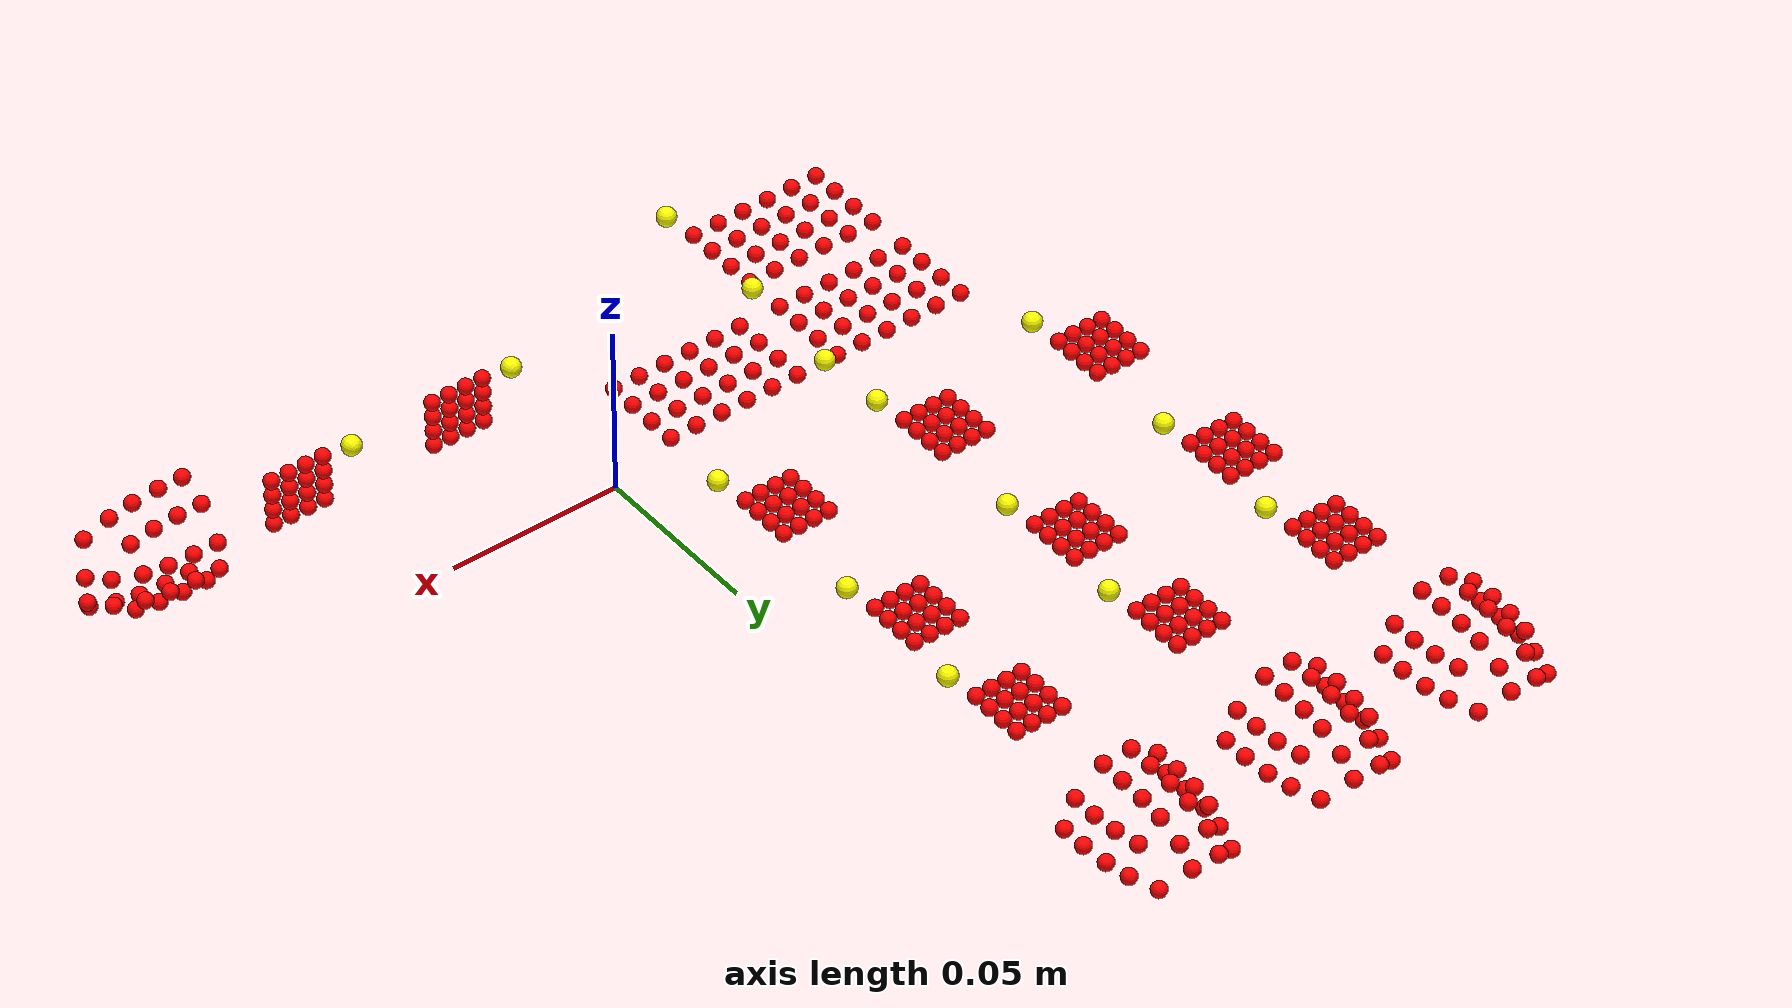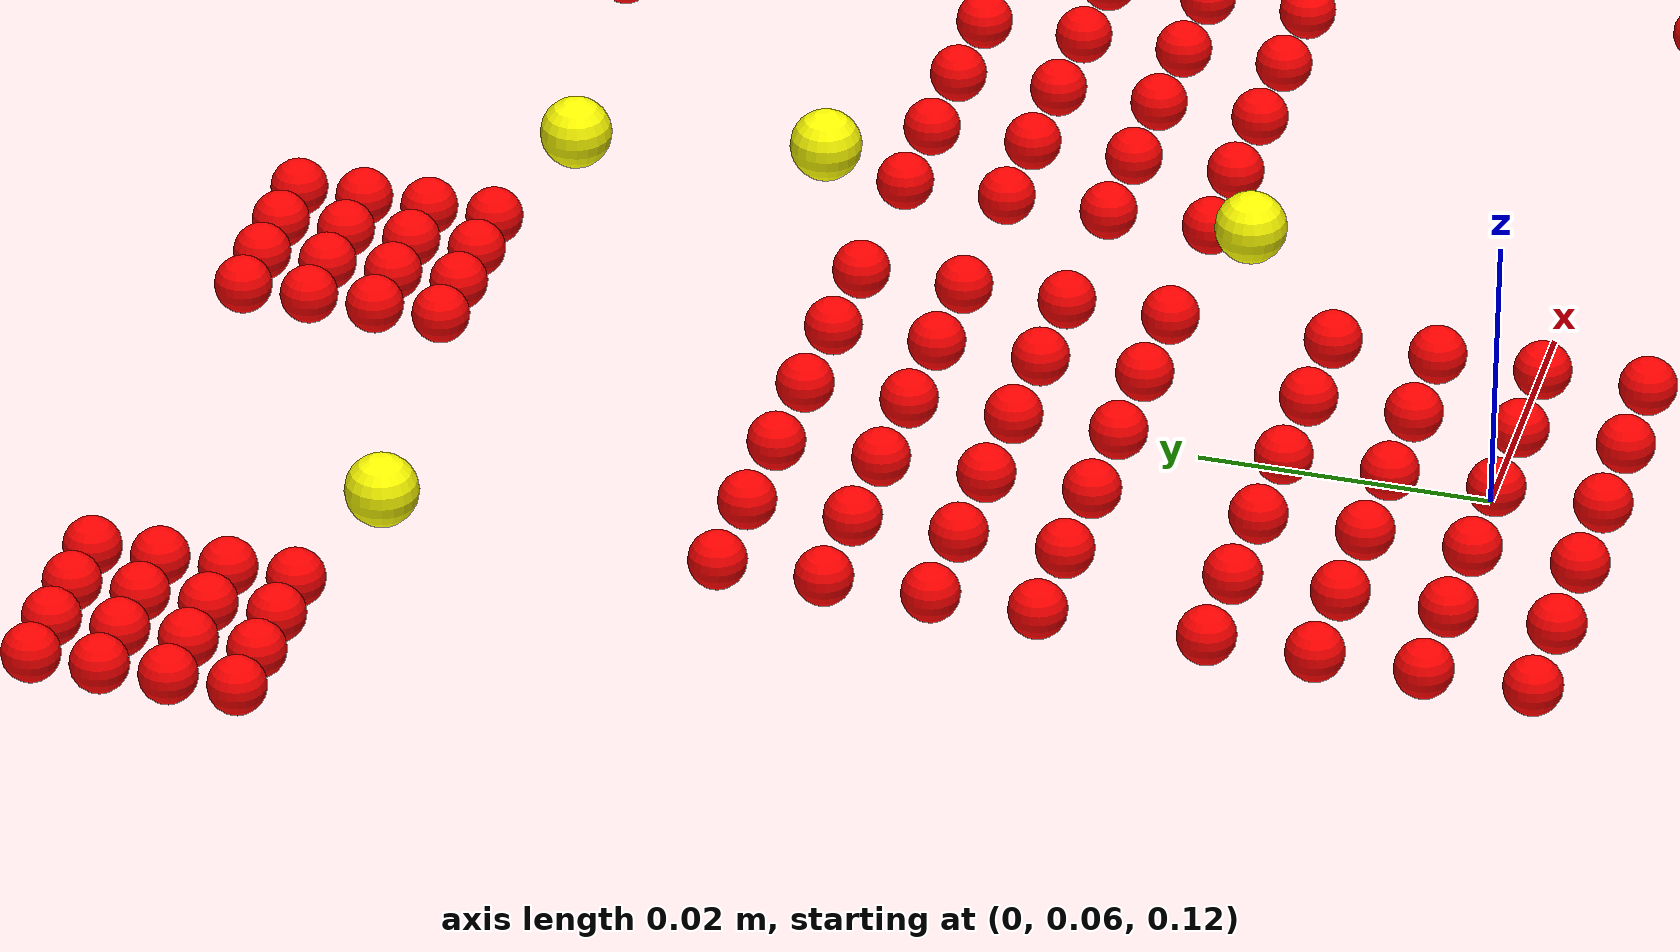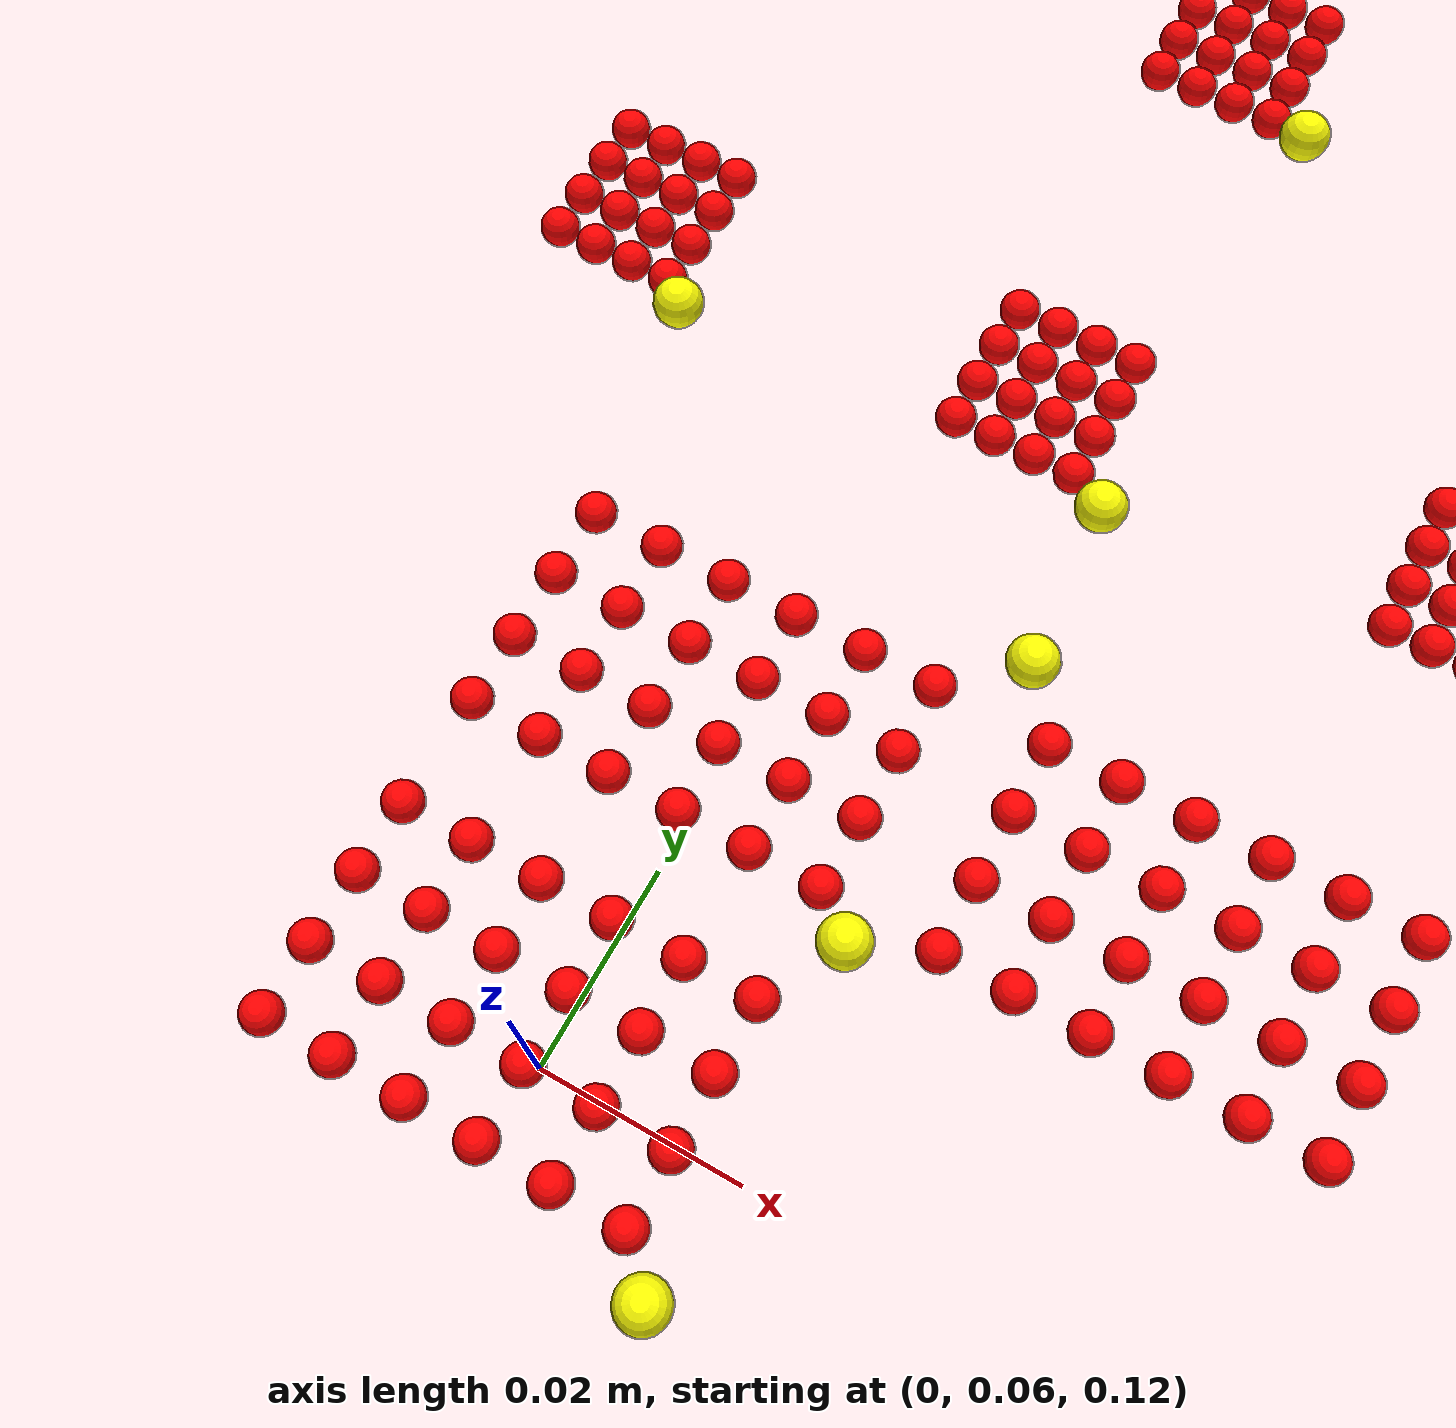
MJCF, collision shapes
<mujoco model="leapXELA">
  <compiler angle="radian" meshdir="./assets/"/>

  <option impratio="100" integrator="implicitfast" cone="elliptic"/>

  <default>
    <default class="leapXELA">
      <joint damping="0.03" frictionloss="0.001"/>
      <geom friction="0.2" solref="0.0001" solimp="0.999 0.999 0.001 0.0001 1"/>
      <general biastype="affine" gainprm="3" biasprm="0 -3 -0.01"/>
      <default class="visual">
        <geom type="mesh" contype="0" conaffinity="0" group="2"/>
      </default>
      <default class="collision">
        <geom type="box" group="3" material="col"/>
        <default class="sensor_patch">
          <geom size="0.005 0.005 0.005" group="2" rgba="1 0 0 1"/>
        </default>
      </default>
      <default class="marker">
        <site group="5"/>
      </default>
      <default class="uspa46">
        <geom size="0.021 0.01 0.015" type="box" group="3" material="orange"/>
        <site size="0.001 0.005 0.005" group="3"/>
      </default>
      <default class="uspa44">
        <geom size="0.011 0.011 0.011" type="box" group="3" material="orange"/>
        <site size="0.001 0.005 0.005" group="3"/>
        <default class="px_uspa44"/>
        <default class="md_uspa44"/>
        <default class="th_px_uspa44"/>
        <default class="th_ds_uspa44"/>
      </default>
      <default class="uSCuALHA_construction_lines">
        <site size="0.001 0.005 0.005" group="4"/>
        <default class="construction_line_0"/>
        <default class="construction_line_1"/>
        <default class="construction_line_2"/>
        <default class="construction_line_3"/>
        <default class="construction_line_4"/>
        <default class="construction_line_5"/>
        <default class="construction_line_6"/>
        <default class="construction_line_7"/>
        <default class="construction_line_8"/>
        <default class="construction_line_9"/>
        <default class="h1_construction_line_1"/>
        <default class="h1_construction_line_2"/>
        <default class="h1_construction_line_3"/>
        <default class="h1_construction_line_4"/>
        <default class="h1_construction_line_5"/>
        <default class="h1_construction_line_6"/>
        <default class="h1_construction_line_7"/>
        <default class="h1_construction_line_8"/>
        <default class="h2_construction_line_1"/>
        <default class="h2_construction_line_2"/>
        <default class="h2_construction_line_3"/>
        <default class="h2_construction_line_4"/>
        <default class="h2_construction_line_5"/>
        <default class="h2_construction_line_6"/>
      </default>
      <default class="uSCuALHA">
        <geom type="mesh" group="4" friction="0.5" material="orange" mesh="outer_skin_v1_3_1"/>
        <site size="0.001 0.005 0.005" group="4"/>
        <default class="outer_skin_collision_1">
          <geom mesh="outer_skin_collision_1"/>
        </default>
        <default class="outer_skin_collision_2">
          <geom mesh="outer_skin_collision_2"/>
        </default>
        <default class="outer_skin_collision_3">
          <geom mesh="outer_skin_collision_3"/>
        </default>
        <default class="outer_skin_collision_4">
          <geom mesh="outer_skin_collision_4"/>
        </default>
        <default class="outer_skin_collision_5">
          <geom mesh="outer_skin_collision_5"/>
        </default>
        <default class="outer_skin_collision_6">
          <geom mesh="outer_skin_collision_6"/>
        </default>
      </default>
      <default class="mcp">
        <joint limited="true" range="-0.314 2.23"/>
        <general ctrlrange="-0.314 2.23"/>
      </default>
      <default class="rot">
        <joint limited="true" range="-1.047 1.047"/>
        <general ctrlrange="-1.047 1.047"/>
      </default>
      <default class="pip">
        <joint limited="true" range="-0.506 1.885"/>
        <general ctrlrange="-0.506 1.885"/>
      </default>
      <default class="dip">
        <joint limited="true" range="-0.366 2.042"/>
        <general ctrlrange="-0.366 2.042"/>
      </default>
      <default class="thumb_cmc">
        <joint limited="true" range="-0.349 2.094"/>
        <general ctrlrange="-0.349 2.094"/>
      </default>
      <default class="thumb_axl">
        <joint limited="true" range="-0.349 2.094"/>
        <general ctrlrange="-0.349 2.094"/>
      </default>
      <default class="thumb_mcp">
        <joint limited="true" range="-0.47 2.443"/>
        <general ctrlrange="-0.47 2.443"/>
      </default>
      <default class="thumb_ipl">
        <joint limited="true" range="-1.34 1.88"/>
        <general ctrlrange="-1.34 1.88"/>
      </default>
    </default>
  </default>

  <asset>
    <material name="black" rgba="0.2 0.2 0.2 0.2"/>
    <material name="col" rgba="0.6 1 0.6 0.2"/>
    <material name="orange" rgba="1 0.5 0 0.2"/>
    <material name="marker" rgba="1 0 0 1"/>
    <mesh name="outer_skin_v1_3_1" content_type="model/stl" file="outer_skin_v1_3_1.stl"/>
    <mesh name="outer_skin_collision_1" content_type="model/stl" file="outer_skin_collision_1.stl"/>
    <mesh name="outer_skin_collision_2" content_type="model/stl" file="outer_skin_collision_2.stl"/>
    <mesh name="outer_skin_collision_3" content_type="model/stl" file="outer_skin_collision_3.stl"/>
    <mesh name="outer_skin_collision_4" content_type="model/stl" file="outer_skin_collision_4.stl"/>
    <mesh name="outer_skin_collision_5" content_type="model/stl" file="outer_skin_collision_5.stl"/>
    <mesh name="outer_skin_collision_6" content_type="model/stl" file="outer_skin_collision_6.stl"/>
    <mesh name="thfingertip_unified" content_type="model/stl" file="thfingertip_unified.stl"/>
    <mesh name="leap_hand_xela_bottom" content_type="model/stl" file="leap_hand_xela_bottom.stl"/>
    <mesh name="p2_unified" content_type="model/stl" file="p2_unified.stl"/>
    <mesh name="fingertop_unfied" content_type="model/stl" file="fingertop_unfied.stl"/>
    <mesh name="thp2_unified" content_type="model/stl" file="thp2_unified.stl"/>
    <mesh name="leap_hand_xela_motorholder" content_type="model/stl" file="leap_hand_xela_motorholder.stl"/>
    <mesh name="uspa46" content_type="model/stl" file="uspa46.stl"/>
    <mesh name="thp0_unified" content_type="model/stl" file="thp0_unified.stl"/>
    <mesh name="p3_unified" content_type="model/stl" file="p3_unified.stl"/>
    <mesh name="clipper" content_type="model/stl" file="clipper.stl"/>
    <mesh name="thp1_unified" content_type="model/stl" file="thp1_unified.stl"/>
    <mesh name="leap_hand_xela_side_cover" content_type="model/stl" file="leap_hand_xela_side_cover.stl"/>
    <mesh name="thconnector" content_type="model/stl" file="thconnector.stl"/>
    <mesh name="p5_unified" content_type="model/stl" file="p5_unified.stl"/>
    <mesh name="top_palm" content_type="model/stl" file="top_palm.stl"/>
    <mesh name="p4_unified" content_type="model/stl" file="p4_unified.stl"/>
    <mesh name="palm_face" content_type="model/stl" file="palm_face.stl"/>
    <mesh name="leap_hand_xela_back_cover" content_type="model/stl" file="leap_hand_xela_back_cover.stl"/>
  </asset>

  <worldbody>
    <body name="palm" childclass="leapXELA" pos="0 0 0.1" quat="0.707107 -0.707107 0 0">
      <inertial pos="0.00388456 -0.00321858 0.0893448" quat="0.718238 0.0745346 0.0438938 0.6904" mass="0.237" diaginertia="0.00769061 0.00594175 0.00341044"/>
      <geom name="palm_visual_1" class="visual" pos="0.0180627 0.023 0.0834096" quat="0 0.707107 0 -0.707107" material="black" mesh="leap_hand_xela_motorholder"/>
      <geom name="palm_visual_2" class="visual" pos="-0.005515 -0.027 0.0631" quat="0 0 0 -1" material="black" mesh="uspa46"/>
      <geom name="palm_visual_3" class="visual" pos="0.0235627 -0.013 0.0845" quat="0.707107 0 0 0.707107" material="black" mesh="thp0_unified"/>
      <geom name="palm_visual_4" class="visual" pos="-0.03767 -0.009 0.1306" quat="0.5 0.5 -0.5 0.5" material="black" mesh="p5_unified"/>
      <geom name="palm_visual_5" class="visual" pos="0.00785 -0.023 0.123706" quat="0 0 1 0" material="black" mesh="top_palm"/>
      <geom name="palm_visual_6" class="visual" pos="0.00778 -0.009 0.1306" quat="0.5 0.5 -0.5 0.5" material="black" mesh="p5_unified"/>
      <geom name="palm_visual_7" class="visual" pos="-0.005515 -0.027 0.0962" quat="0 0 0 -1" material="black" mesh="uspa46"/>
      <geom name="palm_visual_8" class="visual" pos="0.05323 -0.009 0.1306" quat="0.5 0.5 -0.5 0.5" material="black" mesh="p5_unified"/>
      <geom name="palm_visual_9" class="visual" pos="0.044015 -0.027 0.0962" quat="0 -1 0 0" material="black" mesh="uspa46"/>
      <geom name="palm_visual_10" class="visual" pos="-0.0293149 0.023 0.131221" quat="0.707107 0 -0.707107 0" material="black" mesh="leap_hand_xela_back_cover"/>
      <geom name="palm_visual_11" class="visual" pos="-0.0503368 0 0.110009" quat="0.707104 0.707104 0.00183435 -0.00183435" material="black" mesh="leap_hand_xela_side_cover"/>
      <geom name="palm_visual_12" class="visual" pos="0 -0.023 0.0425" quat="0 0 -1 0" material="black" mesh="leap_hand_xela_bottom"/>
      <geom name="palm_visual_13" class="visual" pos="-0.0283776 -0.029 0.131221" quat="0.707107 0 -0.707107 0" material="black" mesh="palm_face"/>
      <site name="uspa46_1" class="uspa46" pos="0.013 -0.032 0.107"/>
      <site name="uspa46_2" class="uspa46" pos="0.061 -0.032 0.107"/>
      <site name="uspa46_3" class="uspa46" pos="0.013 -0.032 0.074"/>
      <site name="if_bs_uspa44" class="uspa44" pos="0.015 -0.032 0.149"/>
      <site name="mf_bs_uspa44" class="uspa44" pos="0.059 -0.032 0.149"/>
      <site name="rf_bs_uspa44" class="uspa44" pos="-0.03 -0.032 0.149"/>
      <body name="if_bs" pos="0.06773 -0.0165 0.1436" quat="0 0.707107 0 0.707107">
        <inertial pos="0.0342889 -0.0265621 -0.0145004" quat="0.612791 0.580477 0.431308 0.318601" mass="0.044" diaginertia="7.5816e-05 7.223e-05 3.79383e-05"/>
        <joint name="if_mcp" class="mcp" pos="0 0 0" axis="0 0 1"/>
        <geom name="if_bs_visual" class="visual" pos="0.0048 0 -0.0145" quat="0.5 0.5 0.5 -0.5" material="black" mesh="p4_unified"/>
        <body name="if_px" pos="0.0326 -0.0123 -0.0145" quat="0.5 -0.5 -0.5 -0.5">
          <inertial pos="-0.000258994 0.00848001 0.0133488" quat="0.367834 0.431156 -0.638662 0.520494" mass="0.032" diaginertia="2.33931e-05 2.31607e-05 1.72678e-05"/>
          <joint name="if_rot" class="rot" pos="0 0 0" axis="0 0 1"/>
          <geom name="if_px_visual" class="visual" pos="0 0.0075 0" quat="0.5 -0.5 -0.5 -0.5" material="black" mesh="p3_unified"/>
          <site name="if_px_uspa44" class="px_uspa44" pos="0.006 0.02 0.028"/>
          <body name="if_md" pos="0.0145 0.015 0.013" quat="0.5 0.5 0.5 0.5">
            <inertial pos="0.0304899 -0.00688132 -0.0146269" quat="0.429182 0.64565 -0.344415 0.52945" mass="0.037" diaginertia="5.92221e-05 5.44273e-05 4.40625e-05"/>
            <joint name="if_pip" class="pip" pos="0 0 0" axis="0 0 1"/>
            <geom name="if_md_visual" class="visual" pos="0.00905 0 -0.0145" quat="0.5 0.5 0.5 -0.5" material="black" mesh="p2_unified"/>
            <site name="if_md_uspa44" class="md_uspa44" pos="0.04 0.015 -0.008"/>
            <body name="if_ds" pos="0.0361 0 -0.0291" quat="0.707107 0 0 0.707107">
              <inertial pos="-0.00193531 -0.0359351 0.0145854" quat="0.694152 0.719273 0.0276433 -0.00591063" mass="0.016" diaginertia="7.05616e-05 6.58815e-05 3.62962e-05"/>
              <joint name="if_dip" class="dip" pos="0 0 0" axis="0 0 1"/>
              <geom class="visual" pos="-0.00135925 -0.025 0.0145" quat="0.5 -0.5 -0.5 -0.5" material="black" mesh="fingertop_unfied"/>
              <site name="if_uSCuALHA_construction_line_0" class="construction_line_0" pos="0.015 -0.025 0.0145"/>
              <site name="if_uSCuALHA_construction_line_1" class="construction_line_1" pos="0.015 -0.03 0.0145"/>
              <site name="if_uSCuALHA_construction_line_2" class="construction_line_2" pos="0.015 -0.035 0.0145"/>
              <site name="if_uSCuALHA_construction_line_3" class="construction_line_3" pos="0.0148 -0.04 0.0145"/>
              <site name="if_uSCuALHA_construction_line_4" class="construction_line_4" pos="0.0142 -0.045 0.0145"/>
              <site name="if_uSCuALHA_construction_line_5" class="construction_line_5" pos="0.0134 -0.05 0.0145"/>
              <site name="if_uSCuALHA_construction_line_6" class="construction_line_6" pos="0.0115 -0.055 0.0145"/>
              <site name="if_uSCuALHA_construction_line_7" class="construction_line_7" pos="0.008 -0.06 0.0145"/>
              <site name="if_uSCuALHA_construction_line_8" class="construction_line_8" pos="0.004 -0.063 0.0145"/>
              <site name="if_uSCuALHA_construction_line_9" class="construction_line_9" pos="-0.002 -0.0645 0.0145"/>
              <site name="if_uSCuALHA_h1_construction_line_1" class="h1_construction_line_1" pos="0.014 -0.035 0.02"/>
              <site name="if_uSCuALHA_h1_construction_line_2" class="h1_construction_line_2" pos="0.011 -0.035 0.025"/>
              <site name="if_uSCuALHA_h1_construction_line_3" class="h1_construction_line_3" pos="0.005 -0.035 0.029"/>
              <site name="if_uSCuALHA_h1_construction_line_4" class="h1_construction_line_4" pos="0 -0.035 0.03"/>
              <site name="if_uSCuALHA_h1_construction_line_5" class="h1_construction_line_5" pos="0.014 -0.035 0.008"/>
              <site name="if_uSCuALHA_h1_construction_line_6" class="h1_construction_line_6" pos="0.011 -0.035 0.004"/>
              <site name="if_uSCuALHA_h1_construction_line_7" class="h1_construction_line_7" pos="0.005 -0.035 0"/>
              <site name="if_uSCuALHA_h1_construction_line_8" class="h1_construction_line_8" pos="0 -0.035 -0.001"/>
              <site name="if_uSCuALHA_h2_construction_line_1" class="h2_construction_line_1" pos="0.013 -0.045 0.02"/>
              <site name="if_uSCuALHA_h2_construction_line_2" class="h2_construction_line_2" pos="0.01 -0.045 0.025"/>
              <site name="if_uSCuALHA_h2_construction_line_3" class="h2_construction_line_3" pos="0.002 -0.045 0.029"/>
              <site name="if_uSCuALHA_h2_construction_line_4" class="h2_construction_line_4" pos="0.013 -0.045 0.008"/>
              <site name="if_uSCuALHA_h2_construction_line_5" class="h2_construction_line_5" pos="0.01 -0.045 0.004"/>
              <site name="if_uSCuALHA_h2_construction_line_6" class="h2_construction_line_6" pos="0.002 -0.045 -0.0001"/>
              <body name="if_pointcloud_base_frame" pos="-0.0139201 -0.025 0.0145" quat="-1.29867e-06 0.707107 1.29867e-06 0.707107">
                <body name="if_sensor_1" pos="0.0101 0.0306 0.01254" quat="0.683013 -0.183013 0.683013 0.183013">
                  <joint name="if_sensor_1_slide_x" pos="0 0 0" axis="1 0 0" type="slide" range="-0.0015 0.0015"/>
                  <joint name="if_sensor_1_slide_y" pos="0 0 0" axis="0 1 0" type="slide" range="-0.0015 0.0015"/>
                  <joint name="if_sensor_1_slide_z" pos="0 0 0" axis="0 0 1" type="slide" range="-0.001 0"/>
                  <geom name="if_sensor_1" class="sensor_patch" size="0.002" type="sphere"/>
                </body>
                <body name="if_sensor_2" pos="0.0126 0.0236 0.01254" quat="0.704416 -0.0616284 0.704416 0.0616284">
                  <joint name="if_sensor_2_slide_x" pos="0 0 0" axis="1 0 0" type="slide" range="-0.0015 0.0015"/>
                  <joint name="if_sensor_2_slide_y" pos="0 0 0" axis="0 1 0" type="slide" range="-0.0015 0.0015"/>
                  <joint name="if_sensor_2_slide_z" pos="0 0 0" axis="0 0 1" type="slide" range="-0.001 0"/>
                  <geom name="if_sensor_2" class="sensor_patch" size="0.002" type="sphere"/>
                </body>
                <body name="if_sensor_3" pos="0.0138 0.0173 0.01254" quat="0.704416 -0.0616284 0.704416 0.0616284">
                  <joint name="if_sensor_3_slide_x" pos="0 0 0" axis="1 0 0" type="slide" range="-0.0015 0.0015"/>
                  <joint name="if_sensor_3_slide_y" pos="0 0 0" axis="0 1 0" type="slide" range="-0.0015 0.0015"/>
                  <joint name="if_sensor_3_slide_z" pos="0 0 0" axis="0 0 1" type="slide" range="-0.001 0"/>
                  <geom name="if_sensor_3" class="sensor_patch" size="0.002" type="sphere"/>
                </body>
                <body name="if_sensor_4" pos="0.0143 0.0103 0.01254" quat="0.707107 0 0.707107 0">
                  <joint name="if_sensor_4_slide_x" pos="0 0 0" axis="1 0 0" type="slide" range="-0.0015 0.0015"/>
                  <joint name="if_sensor_4_slide_y" pos="0 0 0" axis="0 1 0" type="slide" range="-0.0015 0.0015"/>
                  <joint name="if_sensor_4_slide_z" pos="0 0 0" axis="0 0 1" type="slide" range="-0.001 0"/>
                  <geom name="if_sensor_4" class="sensor_patch" size="0.002" type="sphere"/>
                </body>
                <body name="if_sensor_5" pos="0.0143 0.0038 0.01254" quat="0.707107 0 0.707107 0">
                  <joint name="if_sensor_5_slide_x" pos="0 0 0" axis="1 0 0" type="slide" range="-0.0015 0.0015"/>
                  <joint name="if_sensor_5_slide_y" pos="0 0 0" axis="0 1 0" type="slide" range="-0.0015 0.0015"/>
                  <joint name="if_sensor_5_slide_z" pos="0 0 0" axis="0 0 1" type="slide" range="-0.001 0"/>
                  <geom name="if_sensor_5" class="sensor_patch" size="0.002" type="sphere"/>
                </body>
                <body name="if_sensor_6" pos="0.0098 0.023 0.02" quat="0.902859 -0.0368336 0.42101 0.0789899">
                  <joint name="if_sensor_6_slide_x" pos="0 0 0" axis="1 0 0" type="slide" range="-0.0015 0.0015"/>
                  <joint name="if_sensor_6_slide_y" pos="0 0 0" axis="0 1 0" type="slide" range="-0.0015 0.0015"/>
                  <joint name="if_sensor_6_slide_z" pos="0 0 0" axis="0 0 1" type="slide" range="-0.001 0"/>
                  <geom name="if_sensor_6" class="sensor_patch" size="0.002" type="sphere"/>
                </body>
                <body name="if_sensor_7" pos="0.011 0.0167 0.02" quat="0.902859 -0.0368336 0.42101 0.0789899">
                  <joint name="if_sensor_7_slide_x" pos="0 0 0" axis="1 0 0" type="slide" range="-0.0015 0.0015"/>
                  <joint name="if_sensor_7_slide_y" pos="0 0 0" axis="0 1 0" type="slide" range="-0.0015 0.0015"/>
                  <joint name="if_sensor_7_slide_z" pos="0 0 0" axis="0 0 1" type="slide" range="-0.001 0"/>
                  <geom name="if_sensor_7" class="sensor_patch" size="0.002" type="sphere"/>
                </body>
                <body name="if_sensor_8" pos="0.0115 0.0103 0.02" quat="0.906308 0 0.422618 0">
                  <joint name="if_sensor_8_slide_x" pos="0 0 0" axis="1 0 0" type="slide" range="-0.0015 0.0015"/>
                  <joint name="if_sensor_8_slide_y" pos="0 0 0" axis="0 1 0" type="slide" range="-0.0015 0.0015"/>
                  <joint name="if_sensor_8_slide_z" pos="0 0 0" axis="0 0 1" type="slide" range="-0.001 0"/>
                  <geom name="if_sensor_8" class="sensor_patch" size="0.002" type="sphere"/>
                </body>
                <body name="if_sensor_9" pos="0.0115 0.0038 0.02" quat="0.906308 0 0.422618 0">
                  <joint name="if_sensor_9_slide_x" pos="0 0 0" axis="1 0 0" type="slide" range="-0.0015 0.0015"/>
                  <joint name="if_sensor_9_slide_y" pos="0 0 0" axis="0 1 0" type="slide" range="-0.0015 0.0015"/>
                  <joint name="if_sensor_9_slide_z" pos="0 0 0" axis="0 0 1" type="slide" range="-0.001 0"/>
                  <geom name="if_sensor_9" class="sensor_patch" size="0.002" type="sphere"/>
                </body>
                <body name="if_sensor_10" pos="0.0037 0.0338 0.0173" quat="0.884447 -0.393781 0.228734 0.101839">
                  <joint name="if_sensor_10_slide_x" pos="0 0 0" axis="1 0 0" type="slide" range="-0.0015 0.0015"/>
                  <joint name="if_sensor_10_slide_y" pos="0 0 0" axis="0 1 0" type="slide" range="-0.0015 0.0015"/>
                  <joint name="if_sensor_10_slide_z" pos="0 0 0" axis="0 0 1" type="slide" range="-0.001 0"/>
                  <geom name="if_sensor_10" class="sensor_patch" size="0.002" type="sphere"/>
                </body>
                <body name="if_sensor_11" pos="0.0039 0.0296 0.02155" quat="0.938933 -0.260389 0.21677 0.0601156">
                  <joint name="if_sensor_11_slide_x" pos="0 0 0" axis="1 0 0" type="slide" range="-0.0015 0.0015"/>
                  <joint name="if_sensor_11_slide_y" pos="0 0 0" axis="0 1 0" type="slide" range="-0.0015 0.0015"/>
                  <joint name="if_sensor_11_slide_z" pos="0 0 0" axis="0 0 1" type="slide" range="-0.001 0"/>
                  <geom name="if_sensor_11" class="sensor_patch" size="0.002" type="sphere"/>
                </body>
                <body name="if_sensor_12" pos="0.0039 0.023 0.02444" quat="0.977892 -0.0855544 0.190083 0.0166301">
                  <joint name="if_sensor_12_slide_x" pos="0 0 0" axis="1 0 0" type="slide" range="-0.0015 0.0015"/>
                  <joint name="if_sensor_12_slide_y" pos="0 0 0" axis="0 1 0" type="slide" range="-0.0015 0.0015"/>
                  <joint name="if_sensor_12_slide_z" pos="0 0 0" axis="0 0 1" type="slide" range="-0.001 0"/>
                  <geom name="if_sensor_12" class="sensor_patch" size="0.002" type="sphere"/>
                </body>
                <body name="if_sensor_13" pos="0.0039 0.0169 0.02544" quat="0.979513 -0.0856963 0.181542 0.0158829">
                  <joint name="if_sensor_13_slide_x" pos="0 0 0" axis="1 0 0" type="slide" range="-0.0015 0.0015"/>
                  <joint name="if_sensor_13_slide_y" pos="0 0 0" axis="0 1 0" type="slide" range="-0.0015 0.0015"/>
                  <joint name="if_sensor_13_slide_z" pos="0 0 0" axis="0 0 1" type="slide" range="-0.001 0"/>
                  <geom name="if_sensor_13" class="sensor_patch" size="0.002" type="sphere"/>
                </body>
                <body name="if_sensor_14" pos="0.0039 0.0103 0.02574" quat="0.987688 0 0.156434 0">
                  <joint name="if_sensor_14_slide_x" pos="0 0 0" axis="1 0 0" type="slide" range="-0.0015 0.0015"/>
                  <joint name="if_sensor_14_slide_y" pos="0 0 0" axis="0 1 0" type="slide" range="-0.0015 0.0015"/>
                  <joint name="if_sensor_14_slide_z" pos="0 0 0" axis="0 0 1" type="slide" range="-0.001 0"/>
                  <geom name="if_sensor_14" class="sensor_patch" size="0.002" type="sphere"/>
                </body>
                <body name="if_sensor_15" pos="0.0039 0.0038 0.02574" quat="0.987688 0 0.156434 0">
                  <joint name="if_sensor_15_slide_x" pos="0 0 0" axis="1 0 0" type="slide" range="-0.0015 0.0015"/>
                  <joint name="if_sensor_15_slide_y" pos="0 0 0" axis="0 1 0" type="slide" range="-0.0015 0.0015"/>
                  <joint name="if_sensor_15_slide_z" pos="0 0 0" axis="0 0 1" type="slide" range="-0.001 0"/>
                  <geom name="if_sensor_15" class="sensor_patch" size="0.002" type="sphere"/>
                </body>
                <body name="if_sensor_16" pos="-0.0037 0.0338 0.0173" quat="0.884447 -0.393781 -0.228734 -0.101839">
                  <joint name="if_sensor_16_slide_x" pos="0 0 0" axis="1 0 0" type="slide" range="-0.0015 0.0015"/>
                  <joint name="if_sensor_16_slide_y" pos="0 0 0" axis="0 1 0" type="slide" range="-0.0015 0.0015"/>
                  <joint name="if_sensor_16_slide_z" pos="0 0 0" axis="0 0 1" type="slide" range="-0.001 0"/>
                  <geom name="if_sensor_16" class="sensor_patch" size="0.002" type="sphere"/>
                </body>
                <body name="if_sensor_17" pos="-0.0039 0.0296 0.02155" quat="0.938933 -0.260389 -0.21677 -0.0601156">
                  <joint name="if_sensor_17_slide_x" pos="0 0 0" axis="1 0 0" type="slide" range="-0.0015 0.0015"/>
                  <joint name="if_sensor_17_slide_y" pos="0 0 0" axis="0 1 0" type="slide" range="-0.0015 0.0015"/>
                  <joint name="if_sensor_17_slide_z" pos="0 0 0" axis="0 0 1" type="slide" range="-0.001 0"/>
                  <geom name="if_sensor_17" class="sensor_patch" size="0.002" type="sphere"/>
                </body>
                <body name="if_sensor_18" pos="-0.0039 0.023 0.02444" quat="0.977892 -0.0855544 -0.190083 -0.0166301">
                  <joint name="if_sensor_18_slide_x" pos="0 0 0" axis="1 0 0" type="slide" range="-0.0015 0.0015"/>
                  <joint name="if_sensor_18_slide_y" pos="0 0 0" axis="0 1 0" type="slide" range="-0.0015 0.0015"/>
                  <joint name="if_sensor_18_slide_z" pos="0 0 0" axis="0 0 1" type="slide" range="-0.001 0"/>
                  <geom name="if_sensor_18" class="sensor_patch" size="0.002" type="sphere"/>
                </body>
                <body name="if_sensor_19" pos="-0.0039 0.0169 0.02544" quat="0.979513 -0.0856963 -0.181542 -0.0158829">
                  <joint name="if_sensor_19_slide_x" pos="0 0 0" axis="1 0 0" type="slide" range="-0.0015 0.0015"/>
                  <joint name="if_sensor_19_slide_y" pos="0 0 0" axis="0 1 0" type="slide" range="-0.0015 0.0015"/>
                  <joint name="if_sensor_19_slide_z" pos="0 0 0" axis="0 0 1" type="slide" range="-0.001 0"/>
                  <geom name="if_sensor_19" class="sensor_patch" size="0.002" type="sphere"/>
                </body>
                <body name="if_sensor_20" pos="-0.0039 0.0103 0.02574" quat="0.987688 0 -0.156434 0">
                  <joint name="if_sensor_20_slide_x" pos="0 0 0" axis="1 0 0" type="slide" range="-0.0015 0.0015"/>
                  <joint name="if_sensor_20_slide_y" pos="0 0 0" axis="0 1 0" type="slide" range="-0.0015 0.0015"/>
                  <joint name="if_sensor_20_slide_z" pos="0 0 0" axis="0 0 1" type="slide" range="-0.001 0"/>
                  <geom name="if_sensor_20" class="sensor_patch" size="0.002" type="sphere"/>
                </body>
                <body name="if_sensor_21" pos="-0.0039 0.0038 0.02574" quat="0.987688 0 -0.156434 0">
                  <joint name="if_sensor_21_slide_x" pos="0 0 0" axis="1 0 0" type="slide" range="-0.0015 0.0015"/>
                  <joint name="if_sensor_21_slide_y" pos="0 0 0" axis="0 1 0" type="slide" range="-0.0015 0.0015"/>
                  <joint name="if_sensor_21_slide_z" pos="0 0 0" axis="0 0 1" type="slide" range="-0.001 0"/>
                  <geom name="if_sensor_21" class="sensor_patch" size="0.002" type="sphere"/>
                </body>
                <body name="if_sensor_22" pos="-0.0098 0.023 0.02" quat="0.902859 -0.0368336 -0.42101 -0.0789899">
                  <joint name="if_sensor_22_slide_x" pos="0 0 0" axis="1 0 0" type="slide" range="-0.0015 0.0015"/>
                  <joint name="if_sensor_22_slide_y" pos="0 0 0" axis="0 1 0" type="slide" range="-0.0015 0.0015"/>
                  <joint name="if_sensor_22_slide_z" pos="0 0 0" axis="0 0 1" type="slide" range="-0.001 0"/>
                  <geom name="if_sensor_22" class="sensor_patch" size="0.002" type="sphere"/>
                </body>
                <body name="if_sensor_23" pos="-0.011 0.0167 0.02" quat="0.902859 -0.0368336 -0.42101 -0.0789899">
                  <joint name="if_sensor_23_slide_x" pos="0 0 0" axis="1 0 0" type="slide" range="-0.0015 0.0015"/>
                  <joint name="if_sensor_23_slide_y" pos="0 0 0" axis="0 1 0" type="slide" range="-0.0015 0.0015"/>
                  <joint name="if_sensor_23_slide_z" pos="0 0 0" axis="0 0 1" type="slide" range="-0.001 0"/>
                  <geom name="if_sensor_23" class="sensor_patch" size="0.002" type="sphere"/>
                </body>
                <body name="if_sensor_24" pos="-0.0115 0.0103 0.02" quat="0.906308 0 -0.422618 0">
                  <joint name="if_sensor_24_slide_x" pos="0 0 0" axis="1 0 0" type="slide" range="-0.0015 0.0015"/>
                  <joint name="if_sensor_24_slide_y" pos="0 0 0" axis="0 1 0" type="slide" range="-0.0015 0.0015"/>
                  <joint name="if_sensor_24_slide_z" pos="0 0 0" axis="0 0 1" type="slide" range="-0.001 0"/>
                  <geom name="if_sensor_24" class="sensor_patch" size="0.002" type="sphere"/>
                </body>
                <body name="if_sensor_25" pos="-0.0115 0.0038 0.02" quat="0.906308 0 -0.422618 0">
                  <joint name="if_sensor_25_slide_x" pos="0 0 0" axis="1 0 0" type="slide" range="-0.0015 0.0015"/>
                  <joint name="if_sensor_25_slide_y" pos="0 0 0" axis="0 1 0" type="slide" range="-0.0015 0.0015"/>
                  <joint name="if_sensor_25_slide_z" pos="0 0 0" axis="0 0 1" type="slide" range="-0.001 0"/>
                  <geom name="if_sensor_25" class="sensor_patch" size="0.002" type="sphere"/>
                </body>
                <body name="if_sensor_26" pos="-0.0101 0.0306 0.01254" quat="0.683013 -0.183013 -0.683013 -0.183013">
                  <joint name="if_sensor_26_slide_x" pos="0 0 0" axis="1 0 0" type="slide" range="-0.0015 0.0015"/>
                  <joint name="if_sensor_26_slide_y" pos="0 0 0" axis="0 1 0" type="slide" range="-0.0015 0.0015"/>
                  <joint name="if_sensor_26_slide_z" pos="0 0 0" axis="0 0 1" type="slide" range="-0.001 0"/>
                  <geom name="if_sensor_26" class="sensor_patch" size="0.002" type="sphere"/>
                </body>
                <body name="if_sensor_27" pos="-0.0126 0.0236 0.01254" quat="0.704416 -0.0616284 -0.704416 -0.0616284">
                  <joint name="if_sensor_27_slide_x" pos="0 0 0" axis="1 0 0" type="slide" range="-0.0015 0.0015"/>
                  <joint name="if_sensor_27_slide_y" pos="0 0 0" axis="0 1 0" type="slide" range="-0.0015 0.0015"/>
                  <joint name="if_sensor_27_slide_z" pos="0 0 0" axis="0 0 1" type="slide" range="-0.001 0"/>
                  <geom name="if_sensor_27" class="sensor_patch" size="0.002" type="sphere"/>
                </body>
                <body name="if_sensor_28" pos="-0.0138 0.0173 0.01254" quat="0.704416 -0.0616284 -0.704416 -0.0616284">
                  <joint name="if_sensor_28_slide_x" pos="0 0 0" axis="1 0 0" type="slide" range="-0.0015 0.0015"/>
                  <joint name="if_sensor_28_slide_y" pos="0 0 0" axis="0 1 0" type="slide" range="-0.0015 0.0015"/>
                  <joint name="if_sensor_28_slide_z" pos="0 0 0" axis="0 0 1" type="slide" range="-0.001 0"/>
                  <geom name="if_sensor_28" class="sensor_patch" size="0.002" type="sphere"/>
                </body>
                <body name="if_sensor_29" pos="-0.0143 0.0103 0.01254" quat="0.707107 0 -0.707107 0">
                  <joint name="if_sensor_29_slide_x" pos="0 0 0" axis="1 0 0" type="slide" range="-0.0015 0.0015"/>
                  <joint name="if_sensor_29_slide_y" pos="0 0 0" axis="0 1 0" type="slide" range="-0.0015 0.0015"/>
                  <joint name="if_sensor_29_slide_z" pos="0 0 0" axis="0 0 1" type="slide" range="-0.001 0"/>
                  <geom name="if_sensor_29" class="sensor_patch" size="0.002" type="sphere"/>
                </body>
                <body name="if_sensor_30" pos="-0.0143 0.0038 0.01254" quat="0.707107 0 -0.707107 0">
                  <joint name="if_sensor_30_slide_x" pos="0 0 0" axis="1 0 0" type="slide" range="-0.0015 0.0015"/>
                  <joint name="if_sensor_30_slide_y" pos="0 0 0" axis="0 1 0" type="slide" range="-0.0015 0.0015"/>
                  <joint name="if_sensor_30_slide_z" pos="0 0 0" axis="0 0 1" type="slide" range="-0.001 0"/>
                  <geom name="if_sensor_30" class="sensor_patch" size="0.002" type="sphere"/>
                </body>
              </body>
            </body>
            <body name="4_4_9_base_frame" pos="0.020626 0.0095 -0.0033" quat="0.5 0.5 0.5 -0.5">
              <geom name="4_4_9_base_frame" class="sensor_patch" size="0.0025" type="sphere" rgba="1 1 0 1"/>
              <body name="4_4_9_base_frame_4_4_sensor_patch_0_0" pos="0.00425 0.0047 0.005" quat="6.34136e-07 0.000796326 -0.999999 0.000796326">
                <joint name="4_4_9_base_frame_4_4_sensor_patch_0_0_slide_x" pos="0 0 0" axis="1 0 0" type="slide" range="-0.0015 0.0015"/>
                <joint name="4_4_9_base_frame_4_4_sensor_patch_0_0_slide_y" pos="0 0 0" axis="0 1 0" type="slide" range="-0.0015 0.0015"/>
                <joint name="4_4_9_base_frame_4_4_sensor_patch_0_0_slide_z" pos="0 0 0" axis="0 0 1" type="slide" range="-0.001 0"/>
                <geom name="4_4_9_base_frame_4_4_sensor_patch_0_0" class="sensor_patch" size="0.002" type="sphere"/>
              </body>
              <body name="4_4_9_base_frame_4_4_sensor_patch_1_0" pos="0.0085 0.0047 0.005" quat="6.34136e-07 0.000796326 -0.999999 0.000796326">
                <joint name="4_4_9_base_frame_4_4_sensor_patch_1_0_slide_x" pos="0 0 0" axis="1 0 0" type="slide" range="-0.0015 0.0015"/>
                <joint name="4_4_9_base_frame_4_4_sensor_patch_1_0_slide_y" pos="0 0 0" axis="0 1 0" type="slide" range="-0.0015 0.0015"/>
                <joint name="4_4_9_base_frame_4_4_sensor_patch_1_0_slide_z" pos="0 0 0" axis="0 0 1" type="slide" range="-0.001 0"/>
                <geom name="4_4_9_base_frame_4_4_sensor_patch_1_0" class="sensor_patch" size="0.002" type="sphere"/>
              </body>
              <body name="4_4_9_base_frame_4_4_sensor_patch_2_0" pos="0.01275 0.0047 0.005" quat="6.34136e-07 0.000796326 -0.999999 0.000796326">
                <joint name="4_4_9_base_frame_4_4_sensor_patch_2_0_slide_x" pos="0 0 0" axis="1 0 0" type="slide" range="-0.0015 0.0015"/>
                <joint name="4_4_9_base_frame_4_4_sensor_patch_2_0_slide_y" pos="0 0 0" axis="0 1 0" type="slide" range="-0.0015 0.0015"/>
                <joint name="4_4_9_base_frame_4_4_sensor_patch_2_0_slide_z" pos="0 0 0" axis="0 0 1" type="slide" range="-0.001 0"/>
                <geom name="4_4_9_base_frame_4_4_sensor_patch_2_0" class="sensor_patch" size="0.002" type="sphere"/>
              </body>
              <body name="4_4_9_base_frame_4_4_sensor_patch_3_0" pos="0.017 0.0047 0.005" quat="6.34136e-07 0.000796326 -0.999999 0.000796326">
                <joint name="4_4_9_base_frame_4_4_sensor_patch_3_0_slide_x" pos="0 0 0" axis="1 0 0" type="slide" range="-0.0015 0.0015"/>
                <joint name="4_4_9_base_frame_4_4_sensor_patch_3_0_slide_y" pos="0 0 0" axis="0 1 0" type="slide" range="-0.0015 0.0015"/>
                <joint name="4_4_9_base_frame_4_4_sensor_patch_3_0_slide_z" pos="0 0 0" axis="0 0 1" type="slide" range="-0.001 0"/>
                <geom name="4_4_9_base_frame_4_4_sensor_patch_3_0" class="sensor_patch" size="0.002" type="sphere"/>
              </body>
              <body name="4_4_9_base_frame_4_4_sensor_patch_0_1" pos="0.00425 0.0094 0.005" quat="6.34136e-07 0.000796326 -0.999999 0.000796326">
                <joint name="4_4_9_base_frame_4_4_sensor_patch_0_1_slide_x" pos="0 0 0" axis="1 0 0" type="slide" range="-0.0015 0.0015"/>
                <joint name="4_4_9_base_frame_4_4_sensor_patch_0_1_slide_y" pos="0 0 0" axis="0 1 0" type="slide" range="-0.0015 0.0015"/>
                <joint name="4_4_9_base_frame_4_4_sensor_patch_0_1_slide_z" pos="0 0 0" axis="0 0 1" type="slide" range="-0.001 0"/>
                <geom name="4_4_9_base_frame_4_4_sensor_patch_0_1" class="sensor_patch" size="0.002" type="sphere"/>
              </body>
              <body name="4_4_9_base_frame_4_4_sensor_patch_1_1" pos="0.0085 0.0094 0.005" quat="6.34136e-07 0.000796326 -0.999999 0.000796326">
                <joint name="4_4_9_base_frame_4_4_sensor_patch_1_1_slide_x" pos="0 0 0" axis="1 0 0" type="slide" range="-0.0015 0.0015"/>
                <joint name="4_4_9_base_frame_4_4_sensor_patch_1_1_slide_y" pos="0 0 0" axis="0 1 0" type="slide" range="-0.0015 0.0015"/>
                <joint name="4_4_9_base_frame_4_4_sensor_patch_1_1_slide_z" pos="0 0 0" axis="0 0 1" type="slide" range="-0.001 0"/>
                <geom name="4_4_9_base_frame_4_4_sensor_patch_1_1" class="sensor_patch" size="0.002" type="sphere"/>
              </body>
              <body name="4_4_9_base_frame_4_4_sensor_patch_2_1" pos="0.01275 0.0094 0.005" quat="6.34136e-07 0.000796326 -0.999999 0.000796326">
                <joint name="4_4_9_base_frame_4_4_sensor_patch_2_1_slide_x" pos="0 0 0" axis="1 0 0" type="slide" range="-0.0015 0.0015"/>
                <joint name="4_4_9_base_frame_4_4_sensor_patch_2_1_slide_y" pos="0 0 0" axis="0 1 0" type="slide" range="-0.0015 0.0015"/>
                <joint name="4_4_9_base_frame_4_4_sensor_patch_2_1_slide_z" pos="0 0 0" axis="0 0 1" type="slide" range="-0.001 0"/>
                <geom name="4_4_9_base_frame_4_4_sensor_patch_2_1" class="sensor_patch" size="0.002" type="sphere"/>
              </body>
              <body name="4_4_9_base_frame_4_4_sensor_patch_3_1" pos="0.017 0.0094 0.005" quat="6.34136e-07 0.000796326 -0.999999 0.000796326">
                <joint name="4_4_9_base_frame_4_4_sensor_patch_3_1_slide_x" pos="0 0 0" axis="1 0 0" type="slide" range="-0.0015 0.0015"/>
                <joint name="4_4_9_base_frame_4_4_sensor_patch_3_1_slide_y" pos="0 0 0" axis="0 1 0" type="slide" range="-0.0015 0.0015"/>
                <joint name="4_4_9_base_frame_4_4_sensor_patch_3_1_slide_z" pos="0 0 0" axis="0 0 1" type="slide" range="-0.001 0"/>
                <geom name="4_4_9_base_frame_4_4_sensor_patch_3_1" class="sensor_patch" size="0.002" type="sphere"/>
              </body>
              <body name="4_4_9_base_frame_4_4_sensor_patch_0_2" pos="0.00425 0.0141 0.005" quat="6.34136e-07 0.000796326 -0.999999 0.000796326">
                <joint name="4_4_9_base_frame_4_4_sensor_patch_0_2_slide_x" pos="0 0 0" axis="1 0 0" type="slide" range="-0.0015 0.0015"/>
                <joint name="4_4_9_base_frame_4_4_sensor_patch_0_2_slide_y" pos="0 0 0" axis="0 1 0" type="slide" range="-0.0015 0.0015"/>
                <joint name="4_4_9_base_frame_4_4_sensor_patch_0_2_slide_z" pos="0 0 0" axis="0 0 1" type="slide" range="-0.001 0"/>
                <geom name="4_4_9_base_frame_4_4_sensor_patch_0_2" class="sensor_patch" size="0.002" type="sphere"/>
              </body>
              <body name="4_4_9_base_frame_4_4_sensor_patch_1_2" pos="0.0085 0.0141 0.005" quat="6.34136e-07 0.000796326 -0.999999 0.000796326">
                <joint name="4_4_9_base_frame_4_4_sensor_patch_1_2_slide_x" pos="0 0 0" axis="1 0 0" type="slide" range="-0.0015 0.0015"/>
                <joint name="4_4_9_base_frame_4_4_sensor_patch_1_2_slide_y" pos="0 0 0" axis="0 1 0" type="slide" range="-0.0015 0.0015"/>
                <joint name="4_4_9_base_frame_4_4_sensor_patch_1_2_slide_z" pos="0 0 0" axis="0 0 1" type="slide" range="-0.001 0"/>
                <geom name="4_4_9_base_frame_4_4_sensor_patch_1_2" class="sensor_patch" size="0.002" type="sphere"/>
              </body>
              <body name="4_4_9_base_frame_4_4_sensor_patch_2_2" pos="0.01275 0.0141 0.005" quat="6.34136e-07 0.000796326 -0.999999 0.000796326">
                <joint name="4_4_9_base_frame_4_4_sensor_patch_2_2_slide_x" pos="0 0 0" axis="1 0 0" type="slide" range="-0.0015 0.0015"/>
                <joint name="4_4_9_base_frame_4_4_sensor_patch_2_2_slide_y" pos="0 0 0" axis="0 1 0" type="slide" range="-0.0015 0.0015"/>
                <joint name="4_4_9_base_frame_4_4_sensor_patch_2_2_slide_z" pos="0 0 0" axis="0 0 1" type="slide" range="-0.001 0"/>
                <geom name="4_4_9_base_frame_4_4_sensor_patch_2_2" class="sensor_patch" size="0.002" type="sphere"/>
              </body>
              <body name="4_4_9_base_frame_4_4_sensor_patch_3_2" pos="0.017 0.0141 0.005" quat="6.34136e-07 0.000796326 -0.999999 0.000796326">
                <joint name="4_4_9_base_frame_4_4_sensor_patch_3_2_slide_x" pos="0 0 0" axis="1 0 0" type="slide" range="-0.0015 0.0015"/>
                <joint name="4_4_9_base_frame_4_4_sensor_patch_3_2_slide_y" pos="0 0 0" axis="0 1 0" type="slide" range="-0.0015 0.0015"/>
                <joint name="4_4_9_base_frame_4_4_sensor_patch_3_2_slide_z" pos="0 0 0" axis="0 0 1" type="slide" range="-0.001 0"/>
                <geom name="4_4_9_base_frame_4_4_sensor_patch_3_2" class="sensor_patch" size="0.002" type="sphere"/>
              </body>
              <body name="4_4_9_base_frame_4_4_sensor_patch_0_3" pos="0.00425 0.0188 0.005" quat="6.34136e-07 0.000796326 -0.999999 0.000796326">
                <joint name="4_4_9_base_frame_4_4_sensor_patch_0_3_slide_x" pos="0 0 0" axis="1 0 0" type="slide" range="-0.0015 0.0015"/>
                <joint name="4_4_9_base_frame_4_4_sensor_patch_0_3_slide_y" pos="0 0 0" axis="0 1 0" type="slide" range="-0.0015 0.0015"/>
                <joint name="4_4_9_base_frame_4_4_sensor_patch_0_3_slide_z" pos="0 0 0" axis="0 0 1" type="slide" range="-0.001 0"/>
                <geom name="4_4_9_base_frame_4_4_sensor_patch_0_3" class="sensor_patch" size="0.002" type="sphere"/>
              </body>
              <body name="4_4_9_base_frame_4_4_sensor_patch_1_3" pos="0.0085 0.0188 0.005" quat="6.34136e-07 0.000796326 -0.999999 0.000796326">
                <joint name="4_4_9_base_frame_4_4_sensor_patch_1_3_slide_x" pos="0 0 0" axis="1 0 0" type="slide" range="-0.0015 0.0015"/>
                <joint name="4_4_9_base_frame_4_4_sensor_patch_1_3_slide_y" pos="0 0 0" axis="0 1 0" type="slide" range="-0.0015 0.0015"/>
                <joint name="4_4_9_base_frame_4_4_sensor_patch_1_3_slide_z" pos="0 0 0" axis="0 0 1" type="slide" range="-0.001 0"/>
                <geom name="4_4_9_base_frame_4_4_sensor_patch_1_3" class="sensor_patch" size="0.002" type="sphere"/>
              </body>
              <body name="4_4_9_base_frame_4_4_sensor_patch_2_3" pos="0.01275 0.0188 0.005" quat="6.34136e-07 0.000796326 -0.999999 0.000796326">
                <joint name="4_4_9_base_frame_4_4_sensor_patch_2_3_slide_x" pos="0 0 0" axis="1 0 0" type="slide" range="-0.0015 0.0015"/>
                <joint name="4_4_9_base_frame_4_4_sensor_patch_2_3_slide_y" pos="0 0 0" axis="0 1 0" type="slide" range="-0.0015 0.0015"/>
                <joint name="4_4_9_base_frame_4_4_sensor_patch_2_3_slide_z" pos="0 0 0" axis="0 0 1" type="slide" range="-0.001 0"/>
                <geom name="4_4_9_base_frame_4_4_sensor_patch_2_3" class="sensor_patch" size="0.002" type="sphere"/>
              </body>
              <body name="4_4_9_base_frame_4_4_sensor_patch_3_3" pos="0.017 0.0188 0.005" quat="6.34136e-07 0.000796326 -0.999999 0.000796326">
                <joint name="4_4_9_base_frame_4_4_sensor_patch_3_3_slide_x" pos="0 0 0" axis="1 0 0" type="slide" range="-0.0015 0.0015"/>
                <joint name="4_4_9_base_frame_4_4_sensor_patch_3_3_slide_y" pos="0 0 0" axis="0 1 0" type="slide" range="-0.0015 0.0015"/>
                <joint name="4_4_9_base_frame_4_4_sensor_patch_3_3_slide_z" pos="0 0 0" axis="0 0 1" type="slide" range="-0.001 0"/>
                <geom name="4_4_9_base_frame_4_4_sensor_patch_3_3" class="sensor_patch" size="0.002" type="sphere"/>
              </body>
            </body>
          </body>
          <body name="4_4_8_base_frame" pos="0.0112619 -5.87232e-05 0.023" quat="0 0 -1 0">
            <geom name="4_4_8_base_frame" class="sensor_patch" size="0.0025" type="sphere" rgba="1 1 0 1"/>
            <body name="4_4_8_base_frame_4_4_sensor_patch_0_0" pos="0.00425 0.0047 0.005" quat="6.34136e-07 0.000796326 -0.999999 0.000796326">
              <joint name="4_4_8_base_frame_4_4_sensor_patch_0_0_slide_x" pos="0 0 0" axis="1 0 0" type="slide" range="-0.0015 0.0015"/>
              <joint name="4_4_8_base_frame_4_4_sensor_patch_0_0_slide_y" pos="0 0 0" axis="0 1 0" type="slide" range="-0.0015 0.0015"/>
              <joint name="4_4_8_base_frame_4_4_sensor_patch_0_0_slide_z" pos="0 0 0" axis="0 0 1" type="slide" range="-0.001 0"/>
              <geom name="4_4_8_base_frame_4_4_sensor_patch_0_0" class="sensor_patch" size="0.002" type="sphere"/>
            </body>
            <body name="4_4_8_base_frame_4_4_sensor_patch_1_0" pos="0.0085 0.0047 0.005" quat="6.34136e-07 0.000796326 -0.999999 0.000796326">
              <joint name="4_4_8_base_frame_4_4_sensor_patch_1_0_slide_x" pos="0 0 0" axis="1 0 0" type="slide" range="-0.0015 0.0015"/>
              <joint name="4_4_8_base_frame_4_4_sensor_patch_1_0_slide_y" pos="0 0 0" axis="0 1 0" type="slide" range="-0.0015 0.0015"/>
              <joint name="4_4_8_base_frame_4_4_sensor_patch_1_0_slide_z" pos="0 0 0" axis="0 0 1" type="slide" range="-0.001 0"/>
              <geom name="4_4_8_base_frame_4_4_sensor_patch_1_0" class="sensor_patch" size="0.002" type="sphere"/>
            </body>
            <body name="4_4_8_base_frame_4_4_sensor_patch_2_0" pos="0.01275 0.0047 0.005" quat="6.34136e-07 0.000796326 -0.999999 0.000796326">
              <joint name="4_4_8_base_frame_4_4_sensor_patch_2_0_slide_x" pos="0 0 0" axis="1 0 0" type="slide" range="-0.0015 0.0015"/>
              <joint name="4_4_8_base_frame_4_4_sensor_patch_2_0_slide_y" pos="0 0 0" axis="0 1 0" type="slide" range="-0.0015 0.0015"/>
              <joint name="4_4_8_base_frame_4_4_sensor_patch_2_0_slide_z" pos="0 0 0" axis="0 0 1" type="slide" range="-0.001 0"/>
              <geom name="4_4_8_base_frame_4_4_sensor_patch_2_0" class="sensor_patch" size="0.002" type="sphere"/>
            </body>
            <body name="4_4_8_base_frame_4_4_sensor_patch_3_0" pos="0.017 0.0047 0.005" quat="6.34136e-07 0.000796326 -0.999999 0.000796326">
              <joint name="4_4_8_base_frame_4_4_sensor_patch_3_0_slide_x" pos="0 0 0" axis="1 0 0" type="slide" range="-0.0015 0.0015"/>
              <joint name="4_4_8_base_frame_4_4_sensor_patch_3_0_slide_y" pos="0 0 0" axis="0 1 0" type="slide" range="-0.0015 0.0015"/>
              <joint name="4_4_8_base_frame_4_4_sensor_patch_3_0_slide_z" pos="0 0 0" axis="0 0 1" type="slide" range="-0.001 0"/>
              <geom name="4_4_8_base_frame_4_4_sensor_patch_3_0" class="sensor_patch" size="0.002" type="sphere"/>
            </body>
            <body name="4_4_8_base_frame_4_4_sensor_patch_0_1" pos="0.00425 0.0094 0.005" quat="6.34136e-07 0.000796326 -0.999999 0.000796326">
              <joint name="4_4_8_base_frame_4_4_sensor_patch_0_1_slide_x" pos="0 0 0" axis="1 0 0" type="slide" range="-0.0015 0.0015"/>
              <joint name="4_4_8_base_frame_4_4_sensor_patch_0_1_slide_y" pos="0 0 0" axis="0 1 0" type="slide" range="-0.0015 0.0015"/>
              <joint name="4_4_8_base_frame_4_4_sensor_patch_0_1_slide_z" pos="0 0 0" axis="0 0 1" type="slide" range="-0.001 0"/>
              <geom name="4_4_8_base_frame_4_4_sensor_patch_0_1" class="sensor_patch" size="0.002" type="sphere"/>
            </body>
            <body name="4_4_8_base_frame_4_4_sensor_patch_1_1" pos="0.0085 0.0094 0.005" quat="6.34136e-07 0.000796326 -0.999999 0.000796326">
              <joint name="4_4_8_base_frame_4_4_sensor_patch_1_1_slide_x" pos="0 0 0" axis="1 0 0" type="slide" range="-0.0015 0.0015"/>
              <joint name="4_4_8_base_frame_4_4_sensor_patch_1_1_slide_y" pos="0 0 0" axis="0 1 0" type="slide" range="-0.0015 0.0015"/>
              <joint name="4_4_8_base_frame_4_4_sensor_patch_1_1_slide_z" pos="0 0 0" axis="0 0 1" type="slide" range="-0.001 0"/>
              <geom name="4_4_8_base_frame_4_4_sensor_patch_1_1" class="sensor_patch" size="0.002" type="sphere"/>
            </body>
            <body name="4_4_8_base_frame_4_4_sensor_patch_2_1" pos="0.01275 0.0094 0.005" quat="6.34136e-07 0.000796326 -0.999999 0.000796326">
              <joint name="4_4_8_base_frame_4_4_sensor_patch_2_1_slide_x" pos="0 0 0" axis="1 0 0" type="slide" range="-0.0015 0.0015"/>
              <joint name="4_4_8_base_frame_4_4_sensor_patch_2_1_slide_y" pos="0 0 0" axis="0 1 0" type="slide" range="-0.0015 0.0015"/>
              <joint name="4_4_8_base_frame_4_4_sensor_patch_2_1_slide_z" pos="0 0 0" axis="0 0 1" type="slide" range="-0.001 0"/>
              <geom name="4_4_8_base_frame_4_4_sensor_patch_2_1" class="sensor_patch" size="0.002" type="sphere"/>
            </body>
            <body name="4_4_8_base_frame_4_4_sensor_patch_3_1" pos="0.017 0.0094 0.005" quat="6.34136e-07 0.000796326 -0.999999 0.000796326">
              <joint name="4_4_8_base_frame_4_4_sensor_patch_3_1_slide_x" pos="0 0 0" axis="1 0 0" type="slide" range="-0.0015 0.0015"/>
              <joint name="4_4_8_base_frame_4_4_sensor_patch_3_1_slide_y" pos="0 0 0" axis="0 1 0" type="slide" range="-0.0015 0.0015"/>
              <joint name="4_4_8_base_frame_4_4_sensor_patch_3_1_slide_z" pos="0 0 0" axis="0 0 1" type="slide" range="-0.001 0"/>
              <geom name="4_4_8_base_frame_4_4_sensor_patch_3_1" class="sensor_patch" size="0.002" type="sphere"/>
            </body>
            <body name="4_4_8_base_frame_4_4_sensor_patch_0_2" pos="0.00425 0.0141 0.005" quat="6.34136e-07 0.000796326 -0.999999 0.000796326">
              <joint name="4_4_8_base_frame_4_4_sensor_patch_0_2_slide_x" pos="0 0 0" axis="1 0 0" type="slide" range="-0.0015 0.0015"/>
              <joint name="4_4_8_base_frame_4_4_sensor_patch_0_2_slide_y" pos="0 0 0" axis="0 1 0" type="slide" range="-0.0015 0.0015"/>
              <joint name="4_4_8_base_frame_4_4_sensor_patch_0_2_slide_z" pos="0 0 0" axis="0 0 1" type="slide" range="-0.001 0"/>
              <geom name="4_4_8_base_frame_4_4_sensor_patch_0_2" class="sensor_patch" size="0.002" type="sphere"/>
            </body>
            <body name="4_4_8_base_frame_4_4_sensor_patch_1_2" pos="0.0085 0.0141 0.005" quat="6.34136e-07 0.000796326 -0.999999 0.000796326">
              <joint name="4_4_8_base_frame_4_4_sensor_patch_1_2_slide_x" pos="0 0 0" axis="1 0 0" type="slide" range="-0.0015 0.0015"/>
              <joint name="4_4_8_base_frame_4_4_sensor_patch_1_2_slide_y" pos="0 0 0" axis="0 1 0" type="slide" range="-0.0015 0.0015"/>
              <joint name="4_4_8_base_frame_4_4_sensor_patch_1_2_slide_z" pos="0 0 0" axis="0 0 1" type="slide" range="-0.001 0"/>
              <geom name="4_4_8_base_frame_4_4_sensor_patch_1_2" class="sensor_patch" size="0.002" type="sphere"/>
            </body>
            <body name="4_4_8_base_frame_4_4_sensor_patch_2_2" pos="0.01275 0.0141 0.005" quat="6.34136e-07 0.000796326 -0.999999 0.000796326">
              <joint name="4_4_8_base_frame_4_4_sensor_patch_2_2_slide_x" pos="0 0 0" axis="1 0 0" type="slide" range="-0.0015 0.0015"/>
              <joint name="4_4_8_base_frame_4_4_sensor_patch_2_2_slide_y" pos="0 0 0" axis="0 1 0" type="slide" range="-0.0015 0.0015"/>
              <joint name="4_4_8_base_frame_4_4_sensor_patch_2_2_slide_z" pos="0 0 0" axis="0 0 1" type="slide" range="-0.001 0"/>
              <geom name="4_4_8_base_frame_4_4_sensor_patch_2_2" class="sensor_patch" size="0.002" type="sphere"/>
            </body>
            <body name="4_4_8_base_frame_4_4_sensor_patch_3_2" pos="0.017 0.0141 0.005" quat="6.34136e-07 0.000796326 -0.999999 0.000796326">
              <joint name="4_4_8_base_frame_4_4_sensor_patch_3_2_slide_x" pos="0 0 0" axis="1 0 0" type="slide" range="-0.0015 0.0015"/>
              <joint name="4_4_8_base_frame_4_4_sensor_patch_3_2_slide_y" pos="0 0 0" axis="0 1 0" type="slide" range="-0.0015 0.0015"/>
              <joint name="4_4_8_base_frame_4_4_sensor_patch_3_2_slide_z" pos="0 0 0" axis="0 0 1" type="slide" range="-0.001 0"/>
              <geom name="4_4_8_base_frame_4_4_sensor_patch_3_2" class="sensor_patch" size="0.002" type="sphere"/>
            </body>
            <body name="4_4_8_base_frame_4_4_sensor_patch_0_3" pos="0.00425 0.0188 0.005" quat="6.34136e-07 0.000796326 -0.999999 0.000796326">
              <joint name="4_4_8_base_frame_4_4_sensor_patch_0_3_slide_x" pos="0 0 0" axis="1 0 0" type="slide" range="-0.0015 0.0015"/>
              <joint name="4_4_8_base_frame_4_4_sensor_patch_0_3_slide_y" pos="0 0 0" axis="0 1 0" type="slide" range="-0.0015 0.0015"/>
              <joint name="4_4_8_base_frame_4_4_sensor_patch_0_3_slide_z" pos="0 0 0" axis="0 0 1" type="slide" range="-0.001 0"/>
              <geom name="4_4_8_base_frame_4_4_sensor_patch_0_3" class="sensor_patch" size="0.002" type="sphere"/>
            </body>
            <body name="4_4_8_base_frame_4_4_sensor_patch_1_3" pos="0.0085 0.0188 0.005" quat="6.34136e-07 0.000796326 -0.999999 0.000796326">
              <joint name="4_4_8_base_frame_4_4_sensor_patch_1_3_slide_x" pos="0 0 0" axis="1 0 0" type="slide" range="-0.0015 0.0015"/>
              <joint name="4_4_8_base_frame_4_4_sensor_patch_1_3_slide_y" pos="0 0 0" axis="0 1 0" type="slide" range="-0.0015 0.0015"/>
              <joint name="4_4_8_base_frame_4_4_sensor_patch_1_3_slide_z" pos="0 0 0" axis="0 0 1" type="slide" range="-0.001 0"/>
              <geom name="4_4_8_base_frame_4_4_sensor_patch_1_3" class="sensor_patch" size="0.002" type="sphere"/>
            </body>
            <body name="4_4_8_base_frame_4_4_sensor_patch_2_3" pos="0.01275 0.0188 0.005" quat="6.34136e-07 0.000796326 -0.999999 0.000796326">
              <joint name="4_4_8_base_frame_4_4_sensor_patch_2_3_slide_x" pos="0 0 0" axis="1 0 0" type="slide" range="-0.0015 0.0015"/>
              <joint name="4_4_8_base_frame_4_4_sensor_patch_2_3_slide_y" pos="0 0 0" axis="0 1 0" type="slide" range="-0.0015 0.0015"/>
              <joint name="4_4_8_base_frame_4_4_sensor_patch_2_3_slide_z" pos="0 0 0" axis="0 0 1" type="slide" range="-0.001 0"/>
              <geom name="4_4_8_base_frame_4_4_sensor_patch_2_3" class="sensor_patch" size="0.002" type="sphere"/>
            </body>
            <body name="4_4_8_base_frame_4_4_sensor_patch_3_3" pos="0.017 0.0188 0.005" quat="6.34136e-07 0.000796326 -0.999999 0.000796326">
              <joint name="4_4_8_base_frame_4_4_sensor_patch_3_3_slide_x" pos="0 0 0" axis="1 0 0" type="slide" range="-0.0015 0.0015"/>
              <joint name="4_4_8_base_frame_4_4_sensor_patch_3_3_slide_y" pos="0 0 0" axis="0 1 0" type="slide" range="-0.0015 0.0015"/>
              <joint name="4_4_8_base_frame_4_4_sensor_patch_3_3_slide_z" pos="0 0 0" axis="0 0 1" type="slide" range="-0.001 0"/>
              <geom name="4_4_8_base_frame_4_4_sensor_patch_3_3" class="sensor_patch" size="0.002" type="sphere"/>
            </body>
          </body>
        </body>
      </body>
      <body name="mf_bs" pos="0.02228 -0.0165 0.1436" quat="0 0.707107 0 0.707107">
        <inertial pos="0.0342889 -0.0265621 -0.0145004" quat="0.612791 0.580477 0.431308 0.318601" mass="0.044" diaginertia="7.5816e-05 7.223e-05 3.79383e-05"/>
        <joint name="mf_mcp" class="mcp" pos="0 0 0" axis="0 0 1"/>
        <geom name="mf_bs_visual" class="visual" pos="0.0048 0 -0.0145" quat="0.5 0.5 0.5 -0.5" material="black" mesh="p4_unified"/>
        <body name="mf_px" pos="0.0326 -0.0123 -0.0145" quat="0.5 -0.5 -0.5 -0.5">
          <inertial pos="-0.000258994 0.00848001 0.0133488" quat="0.367834 0.431156 -0.638662 0.520494" mass="0.032" diaginertia="2.33931e-05 2.31607e-05 1.72678e-05"/>
          <joint name="mf_rot" class="rot" pos="0 0 0" axis="0 0 1"/>
          <geom name="mf_px_visual" class="visual" pos="0 0.0075 0" quat="0.5 -0.5 -0.5 -0.5" material="black" mesh="p3_unified"/>
          <site name="mf_px_uspa44" class="px_uspa44" pos="0.006 0.02 0.028"/>
          <body name="mf_md" pos="0.0145 0.015 0.013" quat="0.5 0.5 0.5 0.5">
            <inertial pos="0.0304899 -0.00688132 -0.0146269" quat="0.429182 0.64565 -0.344415 0.52945" mass="0.037" diaginertia="5.92221e-05 5.44273e-05 4.40625e-05"/>
            <joint name="mf_pip" class="pip" pos="0 0 0" axis="0 0 1"/>
            <geom name="mf_md_visual" class="visual" pos="0.00905 0 -0.0145" quat="0.5 0.5 0.5 -0.5" material="black" mesh="p2_unified"/>
            <site name="mf_md_uspa44" class="md_uspa44" pos="0.04 0.015 -0.008"/>
            <body name="mf_ds" pos="0.0361 0 -0.0291" quat="0.707107 0 0 0.707107">
              <inertial pos="-0.00193531 -0.0359351 0.0145854" quat="0.694152 0.719273 0.0276433 -0.00591063" mass="0.016" diaginertia="7.05616e-05 6.58815e-05 3.62962e-05"/>
              <joint name="mf_dip" class="dip" pos="0 0 0" axis="0 0 1"/>
              <geom name="mf_ds_visual" class="visual" pos="-0.00135925 -0.025 0.0145" quat="0.5 -0.5 -0.5 -0.5" material="black" mesh="fingertop_unfied"/>
              <body name="mf_pointcloud_base_frame" pos="-0.0139201 -0.025 0.0145" quat="-1.29867e-06 0.707107 1.29867e-06 0.707107">
                <body name="mf_sensor_1" pos="0.0101 0.0306 0.01254" quat="0.683013 -0.183013 0.683013 0.183013">
                  <joint name="mf_sensor_1_slide_x" pos="0 0 0" axis="1 0 0" type="slide" range="-0.0015 0.0015"/>
                  <joint name="mf_sensor_1_slide_y" pos="0 0 0" axis="0 1 0" type="slide" range="-0.0015 0.0015"/>
                  <joint name="mf_sensor_1_slide_z" pos="0 0 0" axis="0 0 1" type="slide" range="-0.001 0"/>
                  <geom name="mf_sensor_1" class="sensor_patch" size="0.002" type="sphere"/>
                </body>
                <body name="mf_sensor_2" pos="0.0126 0.0236 0.01254" quat="0.704416 -0.0616284 0.704416 0.0616284">
                  <joint name="mf_sensor_2_slide_x" pos="0 0 0" axis="1 0 0" type="slide" range="-0.0015 0.0015"/>
                  <joint name="mf_sensor_2_slide_y" pos="0 0 0" axis="0 1 0" type="slide" range="-0.0015 0.0015"/>
                  <joint name="mf_sensor_2_slide_z" pos="0 0 0" axis="0 0 1" type="slide" range="-0.001 0"/>
                  <geom name="mf_sensor_2" class="sensor_patch" size="0.002" type="sphere"/>
                </body>
                <body name="mf_sensor_3" pos="0.0138 0.0173 0.01254" quat="0.704416 -0.0616284 0.704416 0.0616284">
                  <joint name="mf_sensor_3_slide_x" pos="0 0 0" axis="1 0 0" type="slide" range="-0.0015 0.0015"/>
                  <joint name="mf_sensor_3_slide_y" pos="0 0 0" axis="0 1 0" type="slide" range="-0.0015 0.0015"/>
                  <joint name="mf_sensor_3_slide_z" pos="0 0 0" axis="0 0 1" type="slide" range="-0.001 0"/>
                  <geom name="mf_sensor_3" class="sensor_patch" size="0.002" type="sphere"/>
                </body>
                <body name="mf_sensor_4" pos="0.0143 0.0103 0.01254" quat="0.707107 0 0.707107 0">
                  <joint name="mf_sensor_4_slide_x" pos="0 0 0" axis="1 0 0" type="slide" range="-0.0015 0.0015"/>
                  <joint name="mf_sensor_4_slide_y" pos="0 0 0" axis="0 1 0" type="slide" range="-0.0015 0.0015"/>
                  <joint name="mf_sensor_4_slide_z" pos="0 0 0" axis="0 0 1" type="slide" range="-0.001 0"/>
                  <geom name="mf_sensor_4" class="sensor_patch" size="0.002" type="sphere"/>
                </body>
                <body name="mf_sensor_5" pos="0.0143 0.0038 0.01254" quat="0.707107 0 0.707107 0">
                  <joint name="mf_sensor_5_slide_x" pos="0 0 0" axis="1 0 0" type="slide" range="-0.0015 0.0015"/>
                  <joint name="mf_sensor_5_slide_y" pos="0 0 0" axis="0 1 0" type="slide" range="-0.0015 0.0015"/>
                  <joint name="mf_sensor_5_slide_z" pos="0 0 0" axis="0 0 1" type="slide" range="-0.001 0"/>
                  <geom name="mf_sensor_5" class="sensor_patch" size="0.002" type="sphere"/>
                </body>
                <body name="mf_sensor_6" pos="0.0098 0.023 0.02" quat="0.902859 -0.0368336 0.42101 0.0789899">
                  <joint name="mf_sensor_6_slide_x" pos="0 0 0" axis="1 0 0" type="slide" range="-0.0015 0.0015"/>
                  <joint name="mf_sensor_6_slide_y" pos="0 0 0" axis="0 1 0" type="slide" range="-0.0015 0.0015"/>
                  <joint name="mf_sensor_6_slide_z" pos="0 0 0" axis="0 0 1" type="slide" range="-0.001 0"/>
                  <geom name="mf_sensor_6" class="sensor_patch" size="0.002" type="sphere"/>
                </body>
                <body name="mf_sensor_7" pos="0.011 0.0167 0.02" quat="0.902859 -0.0368336 0.42101 0.0789899">
                  <joint name="mf_sensor_7_slide_x" pos="0 0 0" axis="1 0 0" type="slide" range="-0.0015 0.0015"/>
                  <joint name="mf_sensor_7_slide_y" pos="0 0 0" axis="0 1 0" type="slide" range="-0.0015 0.0015"/>
                  <joint name="mf_sensor_7_slide_z" pos="0 0 0" axis="0 0 1" type="slide" range="-0.001 0"/>
                  <geom name="mf_sensor_7" class="sensor_patch" size="0.002" type="sphere"/>
                </body>
                <body name="mf_sensor_8" pos="0.0115 0.0103 0.02" quat="0.906308 0 0.422618 0">
                  <joint name="mf_sensor_8_slide_x" pos="0 0 0" axis="1 0 0" type="slide" range="-0.0015 0.0015"/>
                  <joint name="mf_sensor_8_slide_y" pos="0 0 0" axis="0 1 0" type="slide" range="-0.0015 0.0015"/>
                  <joint name="mf_sensor_8_slide_z" pos="0 0 0" axis="0 0 1" type="slide" range="-0.001 0"/>
                  <geom name="mf_sensor_8" class="sensor_patch" size="0.002" type="sphere"/>
                </body>
                <body name="mf_sensor_9" pos="0.0115 0.0038 0.02" quat="0.906308 0 0.422618 0">
                  <joint name="mf_sensor_9_slide_x" pos="0 0 0" axis="1 0 0" type="slide" range="-0.0015 0.0015"/>
                  <joint name="mf_sensor_9_slide_y" pos="0 0 0" axis="0 1 0" type="slide" range="-0.0015 0.0015"/>
                  <joint name="mf_sensor_9_slide_z" pos="0 0 0" axis="0 0 1" type="slide" range="-0.001 0"/>
                  <geom name="mf_sensor_9" class="sensor_patch" size="0.002" type="sphere"/>
                </body>
                <body name="mf_sensor_10" pos="0.0037 0.0338 0.0173" quat="0.884447 -0.393781 0.228734 0.101839">
                  <joint name="mf_sensor_10_slide_x" pos="0 0 0" axis="1 0 0" type="slide" range="-0.0015 0.0015"/>
                  <joint name="mf_sensor_10_slide_y" pos="0 0 0" axis="0 1 0" type="slide" range="-0.0015 0.0015"/>
                  <joint name="mf_sensor_10_slide_z" pos="0 0 0" axis="0 0 1" type="slide" range="-0.001 0"/>
                  <geom name="mf_sensor_10" class="sensor_patch" size="0.002" type="sphere"/>
                </body>
                <body name="mf_sensor_11" pos="0.0039 0.0296 0.02155" quat="0.938933 -0.260389 0.21677 0.0601156">
                  <joint name="mf_sensor_11_slide_x" pos="0 0 0" axis="1 0 0" type="slide" range="-0.0015 0.0015"/>
                  <joint name="mf_sensor_11_slide_y" pos="0 0 0" axis="0 1 0" type="slide" range="-0.0015 0.0015"/>
                  <joint name="mf_sensor_11_slide_z" pos="0 0 0" axis="0 0 1" type="slide" range="-0.001 0"/>
                  <geom name="mf_sensor_11" class="sensor_patch" size="0.002" type="sphere"/>
                </body>
                <body name="mf_sensor_12" pos="0.0039 0.023 0.02444" quat="0.977892 -0.0855544 0.190083 0.0166301">
                  <joint name="mf_sensor_12_slide_x" pos="0 0 0" axis="1 0 0" type="slide" range="-0.0015 0.0015"/>
                  <joint name="mf_sensor_12_slide_y" pos="0 0 0" axis="0 1 0" type="slide" range="-0.0015 0.0015"/>
                  <joint name="mf_sensor_12_slide_z" pos="0 0 0" axis="0 0 1" type="slide" range="-0.001 0"/>
                  <geom name="mf_sensor_12" class="sensor_patch" size="0.002" type="sphere"/>
                </body>
                <body name="mf_sensor_13" pos="0.0039 0.0169 0.02544" quat="0.979513 -0.0856963 0.181542 0.0158829">
                  <joint name="mf_sensor_13_slide_x" pos="0 0 0" axis="1 0 0" type="slide" range="-0.0015 0.0015"/>
                  <joint name="mf_sensor_13_slide_y" pos="0 0 0" axis="0 1 0" type="slide" range="-0.0015 0.0015"/>
                  <joint name="mf_sensor_13_slide_z" pos="0 0 0" axis="0 0 1" type="slide" range="-0.001 0"/>
                  <geom name="mf_sensor_13" class="sensor_patch" size="0.002" type="sphere"/>
                </body>
                <body name="mf_sensor_14" pos="0.0039 0.0103 0.02574" quat="0.987688 0 0.156434 0">
                  <joint name="mf_sensor_14_slide_x" pos="0 0 0" axis="1 0 0" type="slide" range="-0.0015 0.0015"/>
                  <joint name="mf_sensor_14_slide_y" pos="0 0 0" axis="0 1 0" type="slide" range="-0.0015 0.0015"/>
                  <joint name="mf_sensor_14_slide_z" pos="0 0 0" axis="0 0 1" type="slide" range="-0.001 0"/>
                  <geom name="mf_sensor_14" class="sensor_patch" size="0.002" type="sphere"/>
                </body>
                <body name="mf_sensor_15" pos="0.0039 0.0038 0.02574" quat="0.987688 0 0.156434 0">
                  <joint name="mf_sensor_15_slide_x" pos="0 0 0" axis="1 0 0" type="slide" range="-0.0015 0.0015"/>
                  <joint name="mf_sensor_15_slide_y" pos="0 0 0" axis="0 1 0" type="slide" range="-0.0015 0.0015"/>
                  <joint name="mf_sensor_15_slide_z" pos="0 0 0" axis="0 0 1" type="slide" range="-0.001 0"/>
                  <geom name="mf_sensor_15" class="sensor_patch" size="0.002" type="sphere"/>
                </body>
                <body name="mf_sensor_16" pos="-0.0037 0.0338 0.0173" quat="0.884447 -0.393781 -0.228734 -0.101839">
                  <joint name="mf_sensor_16_slide_x" pos="0 0 0" axis="1 0 0" type="slide" range="-0.0015 0.0015"/>
                  <joint name="mf_sensor_16_slide_y" pos="0 0 0" axis="0 1 0" type="slide" range="-0.0015 0.0015"/>
                  <joint name="mf_sensor_16_slide_z" pos="0 0 0" axis="0 0 1" type="slide" range="-0.001 0"/>
                  <geom name="mf_sensor_16" class="sensor_patch" size="0.002" type="sphere"/>
                </body>
                <body name="mf_sensor_17" pos="-0.0039 0.0296 0.02155" quat="0.938933 -0.260389 -0.21677 -0.0601156">
                  <joint name="mf_sensor_17_slide_x" pos="0 0 0" axis="1 0 0" type="slide" range="-0.0015 0.0015"/>
                  <joint name="mf_sensor_17_slide_y" pos="0 0 0" axis="0 1 0" type="slide" range="-0.0015 0.0015"/>
                  <joint name="mf_sensor_17_slide_z" pos="0 0 0" axis="0 0 1" type="slide" range="-0.001 0"/>
                  <geom name="mf_sensor_17" class="sensor_patch" size="0.002" type="sphere"/>
                </body>
                <body name="mf_sensor_18" pos="-0.0039 0.023 0.02444" quat="0.977892 -0.0855544 -0.190083 -0.0166301">
                  <joint name="mf_sensor_18_slide_x" pos="0 0 0" axis="1 0 0" type="slide" range="-0.0015 0.0015"/>
                  <joint name="mf_sensor_18_slide_y" pos="0 0 0" axis="0 1 0" type="slide" range="-0.0015 0.0015"/>
                  <joint name="mf_sensor_18_slide_z" pos="0 0 0" axis="0 0 1" type="slide" range="-0.001 0"/>
                  <geom name="mf_sensor_18" class="sensor_patch" size="0.002" type="sphere"/>
                </body>
                <body name="mf_sensor_19" pos="-0.0039 0.0169 0.02544" quat="0.979513 -0.0856963 -0.181542 -0.0158829">
                  <joint name="mf_sensor_19_slide_x" pos="0 0 0" axis="1 0 0" type="slide" range="-0.0015 0.0015"/>
                  <joint name="mf_sensor_19_slide_y" pos="0 0 0" axis="0 1 0" type="slide" range="-0.0015 0.0015"/>
                  <joint name="mf_sensor_19_slide_z" pos="0 0 0" axis="0 0 1" type="slide" range="-0.001 0"/>
                  <geom name="mf_sensor_19" class="sensor_patch" size="0.002" type="sphere"/>
                </body>
                <body name="mf_sensor_20" pos="-0.0039 0.0103 0.02574" quat="0.987688 0 -0.156434 0">
                  <joint name="mf_sensor_20_slide_x" pos="0 0 0" axis="1 0 0" type="slide" range="-0.0015 0.0015"/>
                  <joint name="mf_sensor_20_slide_y" pos="0 0 0" axis="0 1 0" type="slide" range="-0.0015 0.0015"/>
                  <joint name="mf_sensor_20_slide_z" pos="0 0 0" axis="0 0 1" type="slide" range="-0.001 0"/>
                  <geom name="mf_sensor_20" class="sensor_patch" size="0.002" type="sphere"/>
                </body>
                <body name="mf_sensor_21" pos="-0.0039 0.0038 0.02574" quat="0.987688 0 -0.156434 0">
                  <joint name="mf_sensor_21_slide_x" pos="0 0 0" axis="1 0 0" type="slide" range="-0.0015 0.0015"/>
                  <joint name="mf_sensor_21_slide_y" pos="0 0 0" axis="0 1 0" type="slide" range="-0.0015 0.0015"/>
                  <joint name="mf_sensor_21_slide_z" pos="0 0 0" axis="0 0 1" type="slide" range="-0.001 0"/>
                  <geom name="mf_sensor_21" class="sensor_patch" size="0.002" type="sphere"/>
                </body>
                <body name="mf_sensor_22" pos="-0.0098 0.023 0.02" quat="0.902859 -0.0368336 -0.42101 -0.0789899">
                  <joint name="mf_sensor_22_slide_x" pos="0 0 0" axis="1 0 0" type="slide" range="-0.0015 0.0015"/>
                  <joint name="mf_sensor_22_slide_y" pos="0 0 0" axis="0 1 0" type="slide" range="-0.0015 0.0015"/>
                  <joint name="mf_sensor_22_slide_z" pos="0 0 0" axis="0 0 1" type="slide" range="-0.001 0"/>
                  <geom name="mf_sensor_22" class="sensor_patch" size="0.002" type="sphere"/>
                </body>
                <body name="mf_sensor_23" pos="-0.011 0.0167 0.02" quat="0.902859 -0.0368336 -0.42101 -0.0789899">
                  <joint name="mf_sensor_23_slide_x" pos="0 0 0" axis="1 0 0" type="slide" range="-0.0015 0.0015"/>
                  <joint name="mf_sensor_23_slide_y" pos="0 0 0" axis="0 1 0" type="slide" range="-0.0015 0.0015"/>
                  <joint name="mf_sensor_23_slide_z" pos="0 0 0" axis="0 0 1" type="slide" range="-0.001 0"/>
                  <geom name="mf_sensor_23" class="sensor_patch" size="0.002" type="sphere"/>
                </body>
                <body name="mf_sensor_24" pos="-0.0115 0.0103 0.02" quat="0.906308 0 -0.422618 0">
                  <joint name="mf_sensor_24_slide_x" pos="0 0 0" axis="1 0 0" type="slide" range="-0.0015 0.0015"/>
                  <joint name="mf_sensor_24_slide_y" pos="0 0 0" axis="0 1 0" type="slide" range="-0.0015 0.0015"/>
                  <joint name="mf_sensor_24_slide_z" pos="0 0 0" axis="0 0 1" type="slide" range="-0.001 0"/>
                  <geom name="mf_sensor_24" class="sensor_patch" size="0.002" type="sphere"/>
                </body>
                <body name="mf_sensor_25" pos="-0.0115 0.0038 0.02" quat="0.906308 0 -0.422618 0">
                  <joint name="mf_sensor_25_slide_x" pos="0 0 0" axis="1 0 0" type="slide" range="-0.0015 0.0015"/>
                  <joint name="mf_sensor_25_slide_y" pos="0 0 0" axis="0 1 0" type="slide" range="-0.0015 0.0015"/>
                  <joint name="mf_sensor_25_slide_z" pos="0 0 0" axis="0 0 1" type="slide" range="-0.001 0"/>
                  <geom name="mf_sensor_25" class="sensor_patch" size="0.002" type="sphere"/>
                </body>
                <body name="mf_sensor_26" pos="-0.0101 0.0306 0.01254" quat="0.683013 -0.183013 -0.683013 -0.183013">
                  <joint name="mf_sensor_26_slide_x" pos="0 0 0" axis="1 0 0" type="slide" range="-0.0015 0.0015"/>
                  <joint name="mf_sensor_26_slide_y" pos="0 0 0" axis="0 1 0" type="slide" range="-0.0015 0.0015"/>
                  <joint name="mf_sensor_26_slide_z" pos="0 0 0" axis="0 0 1" type="slide" range="-0.001 0"/>
                  <geom name="mf_sensor_26" class="sensor_patch" size="0.002" type="sphere"/>
                </body>
                <body name="mf_sensor_27" pos="-0.0126 0.0236 0.01254" quat="0.704416 -0.0616284 -0.704416 -0.0616284">
                  <joint name="mf_sensor_27_slide_x" pos="0 0 0" axis="1 0 0" type="slide" range="-0.0015 0.0015"/>
                  <joint name="mf_sensor_27_slide_y" pos="0 0 0" axis="0 1 0" type="slide" range="-0.0015 0.0015"/>
                  <joint name="mf_sensor_27_slide_z" pos="0 0 0" axis="0 0 1" type="slide" range="-0.001 0"/>
                  <geom name="mf_sensor_27" class="sensor_patch" size="0.002" type="sphere"/>
                </body>
                <body name="mf_sensor_28" pos="-0.0138 0.0173 0.01254" quat="0.704416 -0.0616284 -0.704416 -0.0616284">
                  <joint name="mf_sensor_28_slide_x" pos="0 0 0" axis="1 0 0" type="slide" range="-0.0015 0.0015"/>
                  <joint name="mf_sensor_28_slide_y" pos="0 0 0" axis="0 1 0" type="slide" range="-0.0015 0.0015"/>
                  <joint name="mf_sensor_28_slide_z" pos="0 0 0" axis="0 0 1" type="slide" range="-0.001 0"/>
                  <geom name="mf_sensor_28" class="sensor_patch" size="0.002" type="sphere"/>
                </body>
                <body name="mf_sensor_29" pos="-0.0143 0.0103 0.01254" quat="0.707107 0 -0.707107 0">
                  <joint name="mf_sensor_29_slide_x" pos="0 0 0" axis="1 0 0" type="slide" range="-0.0015 0.0015"/>
                  <joint name="mf_sensor_29_slide_y" pos="0 0 0" axis="0 1 0" type="slide" range="-0.0015 0.0015"/>
                  <joint name="mf_sensor_29_slide_z" pos="0 0 0" axis="0 0 1" type="slide" range="-0.001 0"/>
                  <geom name="mf_sensor_29" class="sensor_patch" size="0.002" type="sphere"/>
                </body>
                <body name="mf_sensor_30" pos="-0.0143 0.0038 0.01254" quat="0.707107 0 -0.707107 0">
                  <joint name="mf_sensor_30_slide_x" pos="0 0 0" axis="1 0 0" type="slide" range="-0.0015 0.0015"/>
                  <joint name="mf_sensor_30_slide_y" pos="0 0 0" axis="0 1 0" type="slide" range="-0.0015 0.0015"/>
                  <joint name="mf_sensor_30_slide_z" pos="0 0 0" axis="0 0 1" type="slide" range="-0.001 0"/>
                  <geom name="mf_sensor_30" class="sensor_patch" size="0.002" type="sphere"/>
                </body>
              </body>
            </body>
            <body name="4_4_7_base_frame" pos="0.020626 0.0095 -0.0033" quat="0.5 0.5 0.5 -0.5">
              <geom name="4_4_7_base_frame" class="sensor_patch" size="0.0025" type="sphere" rgba="1 1 0 1"/>
              <body name="4_4_7_base_frame_4_4_sensor_patch_0_0" pos="0.00425 0.0047 0.005" quat="6.34136e-07 0.000796326 -0.999999 0.000796326">
                <joint name="4_4_7_base_frame_4_4_sensor_patch_0_0_slide_x" pos="0 0 0" axis="1 0 0" type="slide" range="-0.0015 0.0015"/>
                <joint name="4_4_7_base_frame_4_4_sensor_patch_0_0_slide_y" pos="0 0 0" axis="0 1 0" type="slide" range="-0.0015 0.0015"/>
                <joint name="4_4_7_base_frame_4_4_sensor_patch_0_0_slide_z" pos="0 0 0" axis="0 0 1" type="slide" range="-0.001 0"/>
                <geom name="4_4_7_base_frame_4_4_sensor_patch_0_0" class="sensor_patch" size="0.002" type="sphere"/>
              </body>
              <body name="4_4_7_base_frame_4_4_sensor_patch_1_0" pos="0.0085 0.0047 0.005" quat="6.34136e-07 0.000796326 -0.999999 0.000796326">
                <joint name="4_4_7_base_frame_4_4_sensor_patch_1_0_slide_x" pos="0 0 0" axis="1 0 0" type="slide" range="-0.0015 0.0015"/>
                <joint name="4_4_7_base_frame_4_4_sensor_patch_1_0_slide_y" pos="0 0 0" axis="0 1 0" type="slide" range="-0.0015 0.0015"/>
                <joint name="4_4_7_base_frame_4_4_sensor_patch_1_0_slide_z" pos="0 0 0" axis="0 0 1" type="slide" range="-0.001 0"/>
                <geom name="4_4_7_base_frame_4_4_sensor_patch_1_0" class="sensor_patch" size="0.002" type="sphere"/>
              </body>
              <body name="4_4_7_base_frame_4_4_sensor_patch_2_0" pos="0.01275 0.0047 0.005" quat="6.34136e-07 0.000796326 -0.999999 0.000796326">
                <joint name="4_4_7_base_frame_4_4_sensor_patch_2_0_slide_x" pos="0 0 0" axis="1 0 0" type="slide" range="-0.0015 0.0015"/>
                <joint name="4_4_7_base_frame_4_4_sensor_patch_2_0_slide_y" pos="0 0 0" axis="0 1 0" type="slide" range="-0.0015 0.0015"/>
                <joint name="4_4_7_base_frame_4_4_sensor_patch_2_0_slide_z" pos="0 0 0" axis="0 0 1" type="slide" range="-0.001 0"/>
                <geom name="4_4_7_base_frame_4_4_sensor_patch_2_0" class="sensor_patch" size="0.002" type="sphere"/>
              </body>
              <body name="4_4_7_base_frame_4_4_sensor_patch_3_0" pos="0.017 0.0047 0.005" quat="6.34136e-07 0.000796326 -0.999999 0.000796326">
                <joint name="4_4_7_base_frame_4_4_sensor_patch_3_0_slide_x" pos="0 0 0" axis="1 0 0" type="slide" range="-0.0015 0.0015"/>
                <joint name="4_4_7_base_frame_4_4_sensor_patch_3_0_slide_y" pos="0 0 0" axis="0 1 0" type="slide" range="-0.0015 0.0015"/>
                <joint name="4_4_7_base_frame_4_4_sensor_patch_3_0_slide_z" pos="0 0 0" axis="0 0 1" type="slide" range="-0.001 0"/>
                <geom name="4_4_7_base_frame_4_4_sensor_patch_3_0" class="sensor_patch" size="0.002" type="sphere"/>
              </body>
              <body name="4_4_7_base_frame_4_4_sensor_patch_0_1" pos="0.00425 0.0094 0.005" quat="6.34136e-07 0.000796326 -0.999999 0.000796326">
                <joint name="4_4_7_base_frame_4_4_sensor_patch_0_1_slide_x" pos="0 0 0" axis="1 0 0" type="slide" range="-0.0015 0.0015"/>
                <joint name="4_4_7_base_frame_4_4_sensor_patch_0_1_slide_y" pos="0 0 0" axis="0 1 0" type="slide" range="-0.0015 0.0015"/>
                <joint name="4_4_7_base_frame_4_4_sensor_patch_0_1_slide_z" pos="0 0 0" axis="0 0 1" type="slide" range="-0.001 0"/>
                <geom name="4_4_7_base_frame_4_4_sensor_patch_0_1" class="sensor_patch" size="0.002" type="sphere"/>
              </body>
              <body name="4_4_7_base_frame_4_4_sensor_patch_1_1" pos="0.0085 0.0094 0.005" quat="6.34136e-07 0.000796326 -0.999999 0.000796326">
                <joint name="4_4_7_base_frame_4_4_sensor_patch_1_1_slide_x" pos="0 0 0" axis="1 0 0" type="slide" range="-0.0015 0.0015"/>
                <joint name="4_4_7_base_frame_4_4_sensor_patch_1_1_slide_y" pos="0 0 0" axis="0 1 0" type="slide" range="-0.0015 0.0015"/>
                <joint name="4_4_7_base_frame_4_4_sensor_patch_1_1_slide_z" pos="0 0 0" axis="0 0 1" type="slide" range="-0.001 0"/>
                <geom name="4_4_7_base_frame_4_4_sensor_patch_1_1" class="sensor_patch" size="0.002" type="sphere"/>
              </body>
              <body name="4_4_7_base_frame_4_4_sensor_patch_2_1" pos="0.01275 0.0094 0.005" quat="6.34136e-07 0.000796326 -0.999999 0.000796326">
                <joint name="4_4_7_base_frame_4_4_sensor_patch_2_1_slide_x" pos="0 0 0" axis="1 0 0" type="slide" range="-0.0015 0.0015"/>
                <joint name="4_4_7_base_frame_4_4_sensor_patch_2_1_slide_y" pos="0 0 0" axis="0 1 0" type="slide" range="-0.0015 0.0015"/>
                <joint name="4_4_7_base_frame_4_4_sensor_patch_2_1_slide_z" pos="0 0 0" axis="0 0 1" type="slide" range="-0.001 0"/>
                <geom name="4_4_7_base_frame_4_4_sensor_patch_2_1" class="sensor_patch" size="0.002" type="sphere"/>
              </body>
              <body name="4_4_7_base_frame_4_4_sensor_patch_3_1" pos="0.017 0.0094 0.005" quat="6.34136e-07 0.000796326 -0.999999 0.000796326">
                <joint name="4_4_7_base_frame_4_4_sensor_patch_3_1_slide_x" pos="0 0 0" axis="1 0 0" type="slide" range="-0.0015 0.0015"/>
                <joint name="4_4_7_base_frame_4_4_sensor_patch_3_1_slide_y" pos="0 0 0" axis="0 1 0" type="slide" range="-0.0015 0.0015"/>
                <joint name="4_4_7_base_frame_4_4_sensor_patch_3_1_slide_z" pos="0 0 0" axis="0 0 1" type="slide" range="-0.001 0"/>
                <geom name="4_4_7_base_frame_4_4_sensor_patch_3_1" class="sensor_patch" size="0.002" type="sphere"/>
              </body>
              <body name="4_4_7_base_frame_4_4_sensor_patch_0_2" pos="0.00425 0.0141 0.005" quat="6.34136e-07 0.000796326 -0.999999 0.000796326">
                <joint name="4_4_7_base_frame_4_4_sensor_patch_0_2_slide_x" pos="0 0 0" axis="1 0 0" type="slide" range="-0.0015 0.0015"/>
                <joint name="4_4_7_base_frame_4_4_sensor_patch_0_2_slide_y" pos="0 0 0" axis="0 1 0" type="slide" range="-0.0015 0.0015"/>
                <joint name="4_4_7_base_frame_4_4_sensor_patch_0_2_slide_z" pos="0 0 0" axis="0 0 1" type="slide" range="-0.001 0"/>
                <geom name="4_4_7_base_frame_4_4_sensor_patch_0_2" class="sensor_patch" size="0.002" type="sphere"/>
              </body>
              <body name="4_4_7_base_frame_4_4_sensor_patch_1_2" pos="0.0085 0.0141 0.005" quat="6.34136e-07 0.000796326 -0.999999 0.000796326">
                <joint name="4_4_7_base_frame_4_4_sensor_patch_1_2_slide_x" pos="0 0 0" axis="1 0 0" type="slide" range="-0.0015 0.0015"/>
                <joint name="4_4_7_base_frame_4_4_sensor_patch_1_2_slide_y" pos="0 0 0" axis="0 1 0" type="slide" range="-0.0015 0.0015"/>
                <joint name="4_4_7_base_frame_4_4_sensor_patch_1_2_slide_z" pos="0 0 0" axis="0 0 1" type="slide" range="-0.001 0"/>
                <geom name="4_4_7_base_frame_4_4_sensor_patch_1_2" class="sensor_patch" size="0.002" type="sphere"/>
              </body>
              <body name="4_4_7_base_frame_4_4_sensor_patch_2_2" pos="0.01275 0.0141 0.005" quat="6.34136e-07 0.000796326 -0.999999 0.000796326">
                <joint name="4_4_7_base_frame_4_4_sensor_patch_2_2_slide_x" pos="0 0 0" axis="1 0 0" type="slide" range="-0.0015 0.0015"/>
                <joint name="4_4_7_base_frame_4_4_sensor_patch_2_2_slide_y" pos="0 0 0" axis="0 1 0" type="slide" range="-0.0015 0.0015"/>
                <joint name="4_4_7_base_frame_4_4_sensor_patch_2_2_slide_z" pos="0 0 0" axis="0 0 1" type="slide" range="-0.001 0"/>
                <geom name="4_4_7_base_frame_4_4_sensor_patch_2_2" class="sensor_patch" size="0.002" type="sphere"/>
              </body>
              <body name="4_4_7_base_frame_4_4_sensor_patch_3_2" pos="0.017 0.0141 0.005" quat="6.34136e-07 0.000796326 -0.999999 0.000796326">
                <joint name="4_4_7_base_frame_4_4_sensor_patch_3_2_slide_x" pos="0 0 0" axis="1 0 0" type="slide" range="-0.0015 0.0015"/>
                <joint name="4_4_7_base_frame_4_4_sensor_patch_3_2_slide_y" pos="0 0 0" axis="0 1 0" type="slide" range="-0.0015 0.0015"/>
                <joint name="4_4_7_base_frame_4_4_sensor_patch_3_2_slide_z" pos="0 0 0" axis="0 0 1" type="slide" range="-0.001 0"/>
                <geom name="4_4_7_base_frame_4_4_sensor_patch_3_2" class="sensor_patch" size="0.002" type="sphere"/>
              </body>
              <body name="4_4_7_base_frame_4_4_sensor_patch_0_3" pos="0.00425 0.0188 0.005" quat="6.34136e-07 0.000796326 -0.999999 0.000796326">
                <joint name="4_4_7_base_frame_4_4_sensor_patch_0_3_slide_x" pos="0 0 0" axis="1 0 0" type="slide" range="-0.0015 0.0015"/>
                <joint name="4_4_7_base_frame_4_4_sensor_patch_0_3_slide_y" pos="0 0 0" axis="0 1 0" type="slide" range="-0.0015 0.0015"/>
                <joint name="4_4_7_base_frame_4_4_sensor_patch_0_3_slide_z" pos="0 0 0" axis="0 0 1" type="slide" range="-0.001 0"/>
                <geom name="4_4_7_base_frame_4_4_sensor_patch_0_3" class="sensor_patch" size="0.002" type="sphere"/>
              </body>
              <body name="4_4_7_base_frame_4_4_sensor_patch_1_3" pos="0.0085 0.0188 0.005" quat="6.34136e-07 0.000796326 -0.999999 0.000796326">
                <joint name="4_4_7_base_frame_4_4_sensor_patch_1_3_slide_x" pos="0 0 0" axis="1 0 0" type="slide" range="-0.0015 0.0015"/>
                <joint name="4_4_7_base_frame_4_4_sensor_patch_1_3_slide_y" pos="0 0 0" axis="0 1 0" type="slide" range="-0.0015 0.0015"/>
                <joint name="4_4_7_base_frame_4_4_sensor_patch_1_3_slide_z" pos="0 0 0" axis="0 0 1" type="slide" range="-0.001 0"/>
                <geom name="4_4_7_base_frame_4_4_sensor_patch_1_3" class="sensor_patch" size="0.002" type="sphere"/>
              </body>
              <body name="4_4_7_base_frame_4_4_sensor_patch_2_3" pos="0.01275 0.0188 0.005" quat="6.34136e-07 0.000796326 -0.999999 0.000796326">
                <joint name="4_4_7_base_frame_4_4_sensor_patch_2_3_slide_x" pos="0 0 0" axis="1 0 0" type="slide" range="-0.0015 0.0015"/>
                <joint name="4_4_7_base_frame_4_4_sensor_patch_2_3_slide_y" pos="0 0 0" axis="0 1 0" type="slide" range="-0.0015 0.0015"/>
                <joint name="4_4_7_base_frame_4_4_sensor_patch_2_3_slide_z" pos="0 0 0" axis="0 0 1" type="slide" range="-0.001 0"/>
                <geom name="4_4_7_base_frame_4_4_sensor_patch_2_3" class="sensor_patch" size="0.002" type="sphere"/>
              </body>
              <body name="4_4_7_base_frame_4_4_sensor_patch_3_3" pos="0.017 0.0188 0.005" quat="6.34136e-07 0.000796326 -0.999999 0.000796326">
                <joint name="4_4_7_base_frame_4_4_sensor_patch_3_3_slide_x" pos="0 0 0" axis="1 0 0" type="slide" range="-0.0015 0.0015"/>
                <joint name="4_4_7_base_frame_4_4_sensor_patch_3_3_slide_y" pos="0 0 0" axis="0 1 0" type="slide" range="-0.0015 0.0015"/>
                <joint name="4_4_7_base_frame_4_4_sensor_patch_3_3_slide_z" pos="0 0 0" axis="0 0 1" type="slide" range="-0.001 0"/>
                <geom name="4_4_7_base_frame_4_4_sensor_patch_3_3" class="sensor_patch" size="0.002" type="sphere"/>
              </body>
            </body>
          </body>
          <body name="4_4_6_base_frame" pos="0.0112619 -5.87232e-05 0.023" quat="0 0 -1 0">
            <geom name="4_4_6_base_frame" class="sensor_patch" size="0.0025" type="sphere" rgba="1 1 0 1"/>
            <body name="4_4_6_base_frame_4_4_sensor_patch_0_0" pos="0.00425 0.0047 0.005" quat="6.34136e-07 0.000796326 -0.999999 0.000796326">
              <joint name="4_4_6_base_frame_4_4_sensor_patch_0_0_slide_x" pos="0 0 0" axis="1 0 0" type="slide" range="-0.0015 0.0015"/>
              <joint name="4_4_6_base_frame_4_4_sensor_patch_0_0_slide_y" pos="0 0 0" axis="0 1 0" type="slide" range="-0.0015 0.0015"/>
              <joint name="4_4_6_base_frame_4_4_sensor_patch_0_0_slide_z" pos="0 0 0" axis="0 0 1" type="slide" range="-0.001 0"/>
              <geom name="4_4_6_base_frame_4_4_sensor_patch_0_0" class="sensor_patch" size="0.002" type="sphere"/>
            </body>
            <body name="4_4_6_base_frame_4_4_sensor_patch_1_0" pos="0.0085 0.0047 0.005" quat="6.34136e-07 0.000796326 -0.999999 0.000796326">
              <joint name="4_4_6_base_frame_4_4_sensor_patch_1_0_slide_x" pos="0 0 0" axis="1 0 0" type="slide" range="-0.0015 0.0015"/>
              <joint name="4_4_6_base_frame_4_4_sensor_patch_1_0_slide_y" pos="0 0 0" axis="0 1 0" type="slide" range="-0.0015 0.0015"/>
              <joint name="4_4_6_base_frame_4_4_sensor_patch_1_0_slide_z" pos="0 0 0" axis="0 0 1" type="slide" range="-0.001 0"/>
              <geom name="4_4_6_base_frame_4_4_sensor_patch_1_0" class="sensor_patch" size="0.002" type="sphere"/>
            </body>
            <body name="4_4_6_base_frame_4_4_sensor_patch_2_0" pos="0.01275 0.0047 0.005" quat="6.34136e-07 0.000796326 -0.999999 0.000796326">
              <joint name="4_4_6_base_frame_4_4_sensor_patch_2_0_slide_x" pos="0 0 0" axis="1 0 0" type="slide" range="-0.0015 0.0015"/>
              <joint name="4_4_6_base_frame_4_4_sensor_patch_2_0_slide_y" pos="0 0 0" axis="0 1 0" type="slide" range="-0.0015 0.0015"/>
              <joint name="4_4_6_base_frame_4_4_sensor_patch_2_0_slide_z" pos="0 0 0" axis="0 0 1" type="slide" range="-0.001 0"/>
              <geom name="4_4_6_base_frame_4_4_sensor_patch_2_0" class="sensor_patch" size="0.002" type="sphere"/>
            </body>
            <body name="4_4_6_base_frame_4_4_sensor_patch_3_0" pos="0.017 0.0047 0.005" quat="6.34136e-07 0.000796326 -0.999999 0.000796326">
              <joint name="4_4_6_base_frame_4_4_sensor_patch_3_0_slide_x" pos="0 0 0" axis="1 0 0" type="slide" range="-0.0015 0.0015"/>
              <joint name="4_4_6_base_frame_4_4_sensor_patch_3_0_slide_y" pos="0 0 0" axis="0 1 0" type="slide" range="-0.0015 0.0015"/>
              <joint name="4_4_6_base_frame_4_4_sensor_patch_3_0_slide_z" pos="0 0 0" axis="0 0 1" type="slide" range="-0.001 0"/>
              <geom name="4_4_6_base_frame_4_4_sensor_patch_3_0" class="sensor_patch" size="0.002" type="sphere"/>
            </body>
            <body name="4_4_6_base_frame_4_4_sensor_patch_0_1" pos="0.00425 0.0094 0.005" quat="6.34136e-07 0.000796326 -0.999999 0.000796326">
              <joint name="4_4_6_base_frame_4_4_sensor_patch_0_1_slide_x" pos="0 0 0" axis="1 0 0" type="slide" range="-0.0015 0.0015"/>
              <joint name="4_4_6_base_frame_4_4_sensor_patch_0_1_slide_y" pos="0 0 0" axis="0 1 0" type="slide" range="-0.0015 0.0015"/>
              <joint name="4_4_6_base_frame_4_4_sensor_patch_0_1_slide_z" pos="0 0 0" axis="0 0 1" type="slide" range="-0.001 0"/>
              <geom name="4_4_6_base_frame_4_4_sensor_patch_0_1" class="sensor_patch" size="0.002" type="sphere"/>
            </body>
            <body name="4_4_6_base_frame_4_4_sensor_patch_1_1" pos="0.0085 0.0094 0.005" quat="6.34136e-07 0.000796326 -0.999999 0.000796326">
              <joint name="4_4_6_base_frame_4_4_sensor_patch_1_1_slide_x" pos="0 0 0" axis="1 0 0" type="slide" range="-0.0015 0.0015"/>
              <joint name="4_4_6_base_frame_4_4_sensor_patch_1_1_slide_y" pos="0 0 0" axis="0 1 0" type="slide" range="-0.0015 0.0015"/>
              <joint name="4_4_6_base_frame_4_4_sensor_patch_1_1_slide_z" pos="0 0 0" axis="0 0 1" type="slide" range="-0.001 0"/>
              <geom name="4_4_6_base_frame_4_4_sensor_patch_1_1" class="sensor_patch" size="0.002" type="sphere"/>
            </body>
            <body name="4_4_6_base_frame_4_4_sensor_patch_2_1" pos="0.01275 0.0094 0.005" quat="6.34136e-07 0.000796326 -0.999999 0.000796326">
              <joint name="4_4_6_base_frame_4_4_sensor_patch_2_1_slide_x" pos="0 0 0" axis="1 0 0" type="slide" range="-0.0015 0.0015"/>
              <joint name="4_4_6_base_frame_4_4_sensor_patch_2_1_slide_y" pos="0 0 0" axis="0 1 0" type="slide" range="-0.0015 0.0015"/>
              <joint name="4_4_6_base_frame_4_4_sensor_patch_2_1_slide_z" pos="0 0 0" axis="0 0 1" type="slide" range="-0.001 0"/>
              <geom name="4_4_6_base_frame_4_4_sensor_patch_2_1" class="sensor_patch" size="0.002" type="sphere"/>
            </body>
            <body name="4_4_6_base_frame_4_4_sensor_patch_3_1" pos="0.017 0.0094 0.005" quat="6.34136e-07 0.000796326 -0.999999 0.000796326">
              <joint name="4_4_6_base_frame_4_4_sensor_patch_3_1_slide_x" pos="0 0 0" axis="1 0 0" type="slide" range="-0.0015 0.0015"/>
              <joint name="4_4_6_base_frame_4_4_sensor_patch_3_1_slide_y" pos="0 0 0" axis="0 1 0" type="slide" range="-0.0015 0.0015"/>
              <joint name="4_4_6_base_frame_4_4_sensor_patch_3_1_slide_z" pos="0 0 0" axis="0 0 1" type="slide" range="-0.001 0"/>
              <geom name="4_4_6_base_frame_4_4_sensor_patch_3_1" class="sensor_patch" size="0.002" type="sphere"/>
            </body>
            <body name="4_4_6_base_frame_4_4_sensor_patch_0_2" pos="0.00425 0.0141 0.005" quat="6.34136e-07 0.000796326 -0.999999 0.000796326">
              <joint name="4_4_6_base_frame_4_4_sensor_patch_0_2_slide_x" pos="0 0 0" axis="1 0 0" type="slide" range="-0.0015 0.0015"/>
              <joint name="4_4_6_base_frame_4_4_sensor_patch_0_2_slide_y" pos="0 0 0" axis="0 1 0" type="slide" range="-0.0015 0.0015"/>
              <joint name="4_4_6_base_frame_4_4_sensor_patch_0_2_slide_z" pos="0 0 0" axis="0 0 1" type="slide" range="-0.001 0"/>
              <geom name="4_4_6_base_frame_4_4_sensor_patch_0_2" class="sensor_patch" size="0.002" type="sphere"/>
            </body>
            <body name="4_4_6_base_frame_4_4_sensor_patch_1_2" pos="0.0085 0.0141 0.005" quat="6.34136e-07 0.000796326 -0.999999 0.000796326">
              <joint name="4_4_6_base_frame_4_4_sensor_patch_1_2_slide_x" pos="0 0 0" axis="1 0 0" type="slide" range="-0.0015 0.0015"/>
              <joint name="4_4_6_base_frame_4_4_sensor_patch_1_2_slide_y" pos="0 0 0" axis="0 1 0" type="slide" range="-0.0015 0.0015"/>
              <joint name="4_4_6_base_frame_4_4_sensor_patch_1_2_slide_z" pos="0 0 0" axis="0 0 1" type="slide" range="-0.001 0"/>
              <geom name="4_4_6_base_frame_4_4_sensor_patch_1_2" class="sensor_patch" size="0.002" type="sphere"/>
            </body>
            <body name="4_4_6_base_frame_4_4_sensor_patch_2_2" pos="0.01275 0.0141 0.005" quat="6.34136e-07 0.000796326 -0.999999 0.000796326">
              <joint name="4_4_6_base_frame_4_4_sensor_patch_2_2_slide_x" pos="0 0 0" axis="1 0 0" type="slide" range="-0.0015 0.0015"/>
              <joint name="4_4_6_base_frame_4_4_sensor_patch_2_2_slide_y" pos="0 0 0" axis="0 1 0" type="slide" range="-0.0015 0.0015"/>
              <joint name="4_4_6_base_frame_4_4_sensor_patch_2_2_slide_z" pos="0 0 0" axis="0 0 1" type="slide" range="-0.001 0"/>
              <geom name="4_4_6_base_frame_4_4_sensor_patch_2_2" class="sensor_patch" size="0.002" type="sphere"/>
            </body>
            <body name="4_4_6_base_frame_4_4_sensor_patch_3_2" pos="0.017 0.0141 0.005" quat="6.34136e-07 0.000796326 -0.999999 0.000796326">
              <joint name="4_4_6_base_frame_4_4_sensor_patch_3_2_slide_x" pos="0 0 0" axis="1 0 0" type="slide" range="-0.0015 0.0015"/>
              <joint name="4_4_6_base_frame_4_4_sensor_patch_3_2_slide_y" pos="0 0 0" axis="0 1 0" type="slide" range="-0.0015 0.0015"/>
              <joint name="4_4_6_base_frame_4_4_sensor_patch_3_2_slide_z" pos="0 0 0" axis="0 0 1" type="slide" range="-0.001 0"/>
              <geom name="4_4_6_base_frame_4_4_sensor_patch_3_2" class="sensor_patch" size="0.002" type="sphere"/>
            </body>
            <body name="4_4_6_base_frame_4_4_sensor_patch_0_3" pos="0.00425 0.0188 0.005" quat="6.34136e-07 0.000796326 -0.999999 0.000796326">
              <joint name="4_4_6_base_frame_4_4_sensor_patch_0_3_slide_x" pos="0 0 0" axis="1 0 0" type="slide" range="-0.0015 0.0015"/>
              <joint name="4_4_6_base_frame_4_4_sensor_patch_0_3_slide_y" pos="0 0 0" axis="0 1 0" type="slide" range="-0.0015 0.0015"/>
              <joint name="4_4_6_base_frame_4_4_sensor_patch_0_3_slide_z" pos="0 0 0" axis="0 0 1" type="slide" range="-0.001 0"/>
              <geom name="4_4_6_base_frame_4_4_sensor_patch_0_3" class="sensor_patch" size="0.002" type="sphere"/>
            </body>
            <body name="4_4_6_base_frame_4_4_sensor_patch_1_3" pos="0.0085 0.0188 0.005" quat="6.34136e-07 0.000796326 -0.999999 0.000796326">
              <joint name="4_4_6_base_frame_4_4_sensor_patch_1_3_slide_x" pos="0 0 0" axis="1 0 0" type="slide" range="-0.0015 0.0015"/>
              <joint name="4_4_6_base_frame_4_4_sensor_patch_1_3_slide_y" pos="0 0 0" axis="0 1 0" type="slide" range="-0.0015 0.0015"/>
              <joint name="4_4_6_base_frame_4_4_sensor_patch_1_3_slide_z" pos="0 0 0" axis="0 0 1" type="slide" range="-0.001 0"/>
              <geom name="4_4_6_base_frame_4_4_sensor_patch_1_3" class="sensor_patch" size="0.002" type="sphere"/>
            </body>
            <body name="4_4_6_base_frame_4_4_sensor_patch_2_3" pos="0.01275 0.0188 0.005" quat="6.34136e-07 0.000796326 -0.999999 0.000796326">
              <joint name="4_4_6_base_frame_4_4_sensor_patch_2_3_slide_x" pos="0 0 0" axis="1 0 0" type="slide" range="-0.0015 0.0015"/>
              <joint name="4_4_6_base_frame_4_4_sensor_patch_2_3_slide_y" pos="0 0 0" axis="0 1 0" type="slide" range="-0.0015 0.0015"/>
              <joint name="4_4_6_base_frame_4_4_sensor_patch_2_3_slide_z" pos="0 0 0" axis="0 0 1" type="slide" range="-0.001 0"/>
              <geom name="4_4_6_base_frame_4_4_sensor_patch_2_3" class="sensor_patch" size="0.002" type="sphere"/>
            </body>
            <body name="4_4_6_base_frame_4_4_sensor_patch_3_3" pos="0.017 0.0188 0.005" quat="6.34136e-07 0.000796326 -0.999999 0.000796326">
              <joint name="4_4_6_base_frame_4_4_sensor_patch_3_3_slide_x" pos="0 0 0" axis="1 0 0" type="slide" range="-0.0015 0.0015"/>
              <joint name="4_4_6_base_frame_4_4_sensor_patch_3_3_slide_y" pos="0 0 0" axis="0 1 0" type="slide" range="-0.0015 0.0015"/>
              <joint name="4_4_6_base_frame_4_4_sensor_patch_3_3_slide_z" pos="0 0 0" axis="0 0 1" type="slide" range="-0.001 0"/>
              <geom name="4_4_6_base_frame_4_4_sensor_patch_3_3" class="sensor_patch" size="0.002" type="sphere"/>
            </body>
          </body>
        </body>
      </body>
      <body name="rf_bs" pos="-0.02317 -0.0165 0.1436" quat="0 0.707107 0 0.707107">
        <inertial pos="0.0342889 -0.0265621 -0.0145004" quat="0.612791 0.580477 0.431308 0.318601" mass="0.044" diaginertia="7.5816e-05 7.223e-05 3.79383e-05"/>
        <joint name="rf_mcp" class="mcp" pos="0 0 0" axis="0 0 1"/>
        <geom name="rf_bs_visual" class="visual" pos="0.0048 0 -0.0145" quat="0.5 0.5 0.5 -0.5" material="black" mesh="p4_unified"/>
        <body name="rf_px" pos="0.0326 -0.0123 -0.0145" quat="0.5 -0.5 -0.5 -0.5">
          <inertial pos="-0.000258994 0.00848001 0.0133488" quat="0.367834 0.431156 -0.638662 0.520494" mass="0.032" diaginertia="2.33931e-05 2.31607e-05 1.72678e-05"/>
          <joint name="rf_rot" class="rot" pos="0 0 0" axis="0 0 1"/>
          <geom name="rf_px_visual" class="visual" pos="0 0.0075 0" quat="0.5 -0.5 -0.5 -0.5" material="black" mesh="p3_unified"/>
          <site name="rf_px_uspa44" class="px_uspa44" pos="0.006 0.02 0.028"/>
          <body name="rf_md" pos="0.0145 0.015 0.013" quat="0.5 0.5 0.5 0.5">
            <inertial pos="0.0304899 -0.00688132 -0.0146269" quat="0.429182 0.64565 -0.344415 0.52945" mass="0.037" diaginertia="5.92221e-05 5.44273e-05 4.40625e-05"/>
            <joint name="rf_pip" class="pip" pos="0 0 0" axis="0 0 1"/>
            <geom name="rf_md_visual" class="visual" pos="0.00905 0 -0.0145" quat="0.5 0.5 0.5 -0.5" material="black" mesh="p2_unified"/>
            <site name="rf_md_uspa44" class="md_uspa44" pos="0.04 0.015 -0.008"/>
            <body name="rf_ds" pos="0.0361 0 -0.0291" quat="0.707107 0 0 0.707107">
              <inertial pos="-0.00193531 -0.0359351 0.0145854" quat="0.694152 0.719273 0.0276433 -0.00591063" mass="0.016" diaginertia="7.05616e-05 6.58815e-05 3.62962e-05"/>
              <joint name="rf_dip" class="dip" pos="0 0 0" axis="0 0 1"/>
              <geom name="rf_ds_visual" class="visual" pos="-0.00135925 -0.025 0.0145" quat="0.5 -0.5 -0.5 -0.5" material="black" mesh="fingertop_unfied"/>
              <body name="rf_pointcloud_base_frame" pos="-0.0139201 -0.025 0.0145" quat="-1.29867e-06 0.707107 1.29867e-06 0.707107">
                <body name="rf_sensor_1" pos="0.0101 0.0306 0.01254" quat="0.683013 -0.183013 0.683013 0.183013">
                  <joint name="rf_sensor_1_slide_x" pos="0 0 0" axis="1 0 0" type="slide" range="-0.0015 0.0015"/>
                  <joint name="rf_sensor_1_slide_y" pos="0 0 0" axis="0 1 0" type="slide" range="-0.0015 0.0015"/>
                  <joint name="rf_sensor_1_slide_z" pos="0 0 0" axis="0 0 1" type="slide" range="-0.001 0"/>
                  <geom name="rf_sensor_1" class="sensor_patch" size="0.002" type="sphere"/>
                </body>
                <body name="rf_sensor_2" pos="0.0126 0.0236 0.01254" quat="0.704416 -0.0616284 0.704416 0.0616284">
                  <joint name="rf_sensor_2_slide_x" pos="0 0 0" axis="1 0 0" type="slide" range="-0.0015 0.0015"/>
                  <joint name="rf_sensor_2_slide_y" pos="0 0 0" axis="0 1 0" type="slide" range="-0.0015 0.0015"/>
                  <joint name="rf_sensor_2_slide_z" pos="0 0 0" axis="0 0 1" type="slide" range="-0.001 0"/>
                  <geom name="rf_sensor_2" class="sensor_patch" size="0.002" type="sphere"/>
                </body>
                <body name="rf_sensor_3" pos="0.0138 0.0173 0.01254" quat="0.704416 -0.0616284 0.704416 0.0616284">
                  <joint name="rf_sensor_3_slide_x" pos="0 0 0" axis="1 0 0" type="slide" range="-0.0015 0.0015"/>
                  <joint name="rf_sensor_3_slide_y" pos="0 0 0" axis="0 1 0" type="slide" range="-0.0015 0.0015"/>
                  <joint name="rf_sensor_3_slide_z" pos="0 0 0" axis="0 0 1" type="slide" range="-0.001 0"/>
                  <geom name="rf_sensor_3" class="sensor_patch" size="0.002" type="sphere"/>
                </body>
                <body name="rf_sensor_4" pos="0.0143 0.0103 0.01254" quat="0.707107 0 0.707107 0">
                  <joint name="rf_sensor_4_slide_x" pos="0 0 0" axis="1 0 0" type="slide" range="-0.0015 0.0015"/>
                  <joint name="rf_sensor_4_slide_y" pos="0 0 0" axis="0 1 0" type="slide" range="-0.0015 0.0015"/>
                  <joint name="rf_sensor_4_slide_z" pos="0 0 0" axis="0 0 1" type="slide" range="-0.001 0"/>
                  <geom name="rf_sensor_4" class="sensor_patch" size="0.002" type="sphere"/>
                </body>
                <body name="rf_sensor_5" pos="0.0143 0.0038 0.01254" quat="0.707107 0 0.707107 0">
                  <joint name="rf_sensor_5_slide_x" pos="0 0 0" axis="1 0 0" type="slide" range="-0.0015 0.0015"/>
                  <joint name="rf_sensor_5_slide_y" pos="0 0 0" axis="0 1 0" type="slide" range="-0.0015 0.0015"/>
                  <joint name="rf_sensor_5_slide_z" pos="0 0 0" axis="0 0 1" type="slide" range="-0.001 0"/>
                  <geom name="rf_sensor_5" class="sensor_patch" size="0.002" type="sphere"/>
                </body>
                <body name="rf_sensor_6" pos="0.0098 0.023 0.02" quat="0.902859 -0.0368336 0.42101 0.0789899">
                  <joint name="rf_sensor_6_slide_x" pos="0 0 0" axis="1 0 0" type="slide" range="-0.0015 0.0015"/>
                  <joint name="rf_sensor_6_slide_y" pos="0 0 0" axis="0 1 0" type="slide" range="-0.0015 0.0015"/>
                  <joint name="rf_sensor_6_slide_z" pos="0 0 0" axis="0 0 1" type="slide" range="-0.001 0"/>
                  <geom name="rf_sensor_6" class="sensor_patch" size="0.002" type="sphere"/>
                </body>
                <body name="rf_sensor_7" pos="0.011 0.0167 0.02" quat="0.902859 -0.0368336 0.42101 0.0789899">
                  <joint name="rf_sensor_7_slide_x" pos="0 0 0" axis="1 0 0" type="slide" range="-0.0015 0.0015"/>
                  <joint name="rf_sensor_7_slide_y" pos="0 0 0" axis="0 1 0" type="slide" range="-0.0015 0.0015"/>
                  <joint name="rf_sensor_7_slide_z" pos="0 0 0" axis="0 0 1" type="slide" range="-0.001 0"/>
                  <geom name="rf_sensor_7" class="sensor_patch" size="0.002" type="sphere"/>
                </body>
                <body name="rf_sensor_8" pos="0.0115 0.0103 0.02" quat="0.906308 0 0.422618 0">
                  <joint name="rf_sensor_8_slide_x" pos="0 0 0" axis="1 0 0" type="slide" range="-0.0015 0.0015"/>
                  <joint name="rf_sensor_8_slide_y" pos="0 0 0" axis="0 1 0" type="slide" range="-0.0015 0.0015"/>
                  <joint name="rf_sensor_8_slide_z" pos="0 0 0" axis="0 0 1" type="slide" range="-0.001 0"/>
                  <geom name="rf_sensor_8" class="sensor_patch" size="0.002" type="sphere"/>
                </body>
                <body name="rf_sensor_9" pos="0.0115 0.0038 0.02" quat="0.906308 0 0.422618 0">
                  <joint name="rf_sensor_9_slide_x" pos="0 0 0" axis="1 0 0" type="slide" range="-0.0015 0.0015"/>
                  <joint name="rf_sensor_9_slide_y" pos="0 0 0" axis="0 1 0" type="slide" range="-0.0015 0.0015"/>
                  <joint name="rf_sensor_9_slide_z" pos="0 0 0" axis="0 0 1" type="slide" range="-0.001 0"/>
                  <geom name="rf_sensor_9" class="sensor_patch" size="0.002" type="sphere"/>
                </body>
                <body name="rf_sensor_10" pos="0.0037 0.0338 0.0173" quat="0.884447 -0.393781 0.228734 0.101839">
                  <joint name="rf_sensor_10_slide_x" pos="0 0 0" axis="1 0 0" type="slide" range="-0.0015 0.0015"/>
                  <joint name="rf_sensor_10_slide_y" pos="0 0 0" axis="0 1 0" type="slide" range="-0.0015 0.0015"/>
                  <joint name="rf_sensor_10_slide_z" pos="0 0 0" axis="0 0 1" type="slide" range="-0.001 0"/>
                  <geom name="rf_sensor_10" class="sensor_patch" size="0.002" type="sphere"/>
                </body>
                <body name="rf_sensor_11" pos="0.0039 0.0296 0.02155" quat="0.938933 -0.260389 0.21677 0.0601156">
                  <joint name="rf_sensor_11_slide_x" pos="0 0 0" axis="1 0 0" type="slide" range="-0.0015 0.0015"/>
                  <joint name="rf_sensor_11_slide_y" pos="0 0 0" axis="0 1 0" type="slide" range="-0.0015 0.0015"/>
                  <joint name="rf_sensor_11_slide_z" pos="0 0 0" axis="0 0 1" type="slide" range="-0.001 0"/>
                  <geom name="rf_sensor_11" class="sensor_patch" size="0.002" type="sphere"/>
                </body>
                <body name="rf_sensor_12" pos="0.0039 0.023 0.02444" quat="0.977892 -0.0855544 0.190083 0.0166301">
                  <joint name="rf_sensor_12_slide_x" pos="0 0 0" axis="1 0 0" type="slide" range="-0.0015 0.0015"/>
                  <joint name="rf_sensor_12_slide_y" pos="0 0 0" axis="0 1 0" type="slide" range="-0.0015 0.0015"/>
                  <joint name="rf_sensor_12_slide_z" pos="0 0 0" axis="0 0 1" type="slide" range="-0.001 0"/>
                  <geom name="rf_sensor_12" class="sensor_patch" size="0.002" type="sphere"/>
                </body>
                <body name="rf_sensor_13" pos="0.0039 0.0169 0.02544" quat="0.979513 -0.0856963 0.181542 0.0158829">
                  <joint name="rf_sensor_13_slide_x" pos="0 0 0" axis="1 0 0" type="slide" range="-0.0015 0.0015"/>
                  <joint name="rf_sensor_13_slide_y" pos="0 0 0" axis="0 1 0" type="slide" range="-0.0015 0.0015"/>
                  <joint name="rf_sensor_13_slide_z" pos="0 0 0" axis="0 0 1" type="slide" range="-0.001 0"/>
                  <geom name="rf_sensor_13" class="sensor_patch" size="0.002" type="sphere"/>
                </body>
                <body name="rf_sensor_14" pos="0.0039 0.0103 0.02574" quat="0.987688 0 0.156434 0">
                  <joint name="rf_sensor_14_slide_x" pos="0 0 0" axis="1 0 0" type="slide" range="-0.0015 0.0015"/>
                  <joint name="rf_sensor_14_slide_y" pos="0 0 0" axis="0 1 0" type="slide" range="-0.0015 0.0015"/>
                  <joint name="rf_sensor_14_slide_z" pos="0 0 0" axis="0 0 1" type="slide" range="-0.001 0"/>
                  <geom name="rf_sensor_14" class="sensor_patch" size="0.002" type="sphere"/>
                </body>
                <body name="rf_sensor_15" pos="0.0039 0.0038 0.02574" quat="0.987688 0 0.156434 0">
                  <joint name="rf_sensor_15_slide_x" pos="0 0 0" axis="1 0 0" type="slide" range="-0.0015 0.0015"/>
                  <joint name="rf_sensor_15_slide_y" pos="0 0 0" axis="0 1 0" type="slide" range="-0.0015 0.0015"/>
                  <joint name="rf_sensor_15_slide_z" pos="0 0 0" axis="0 0 1" type="slide" range="-0.001 0"/>
                  <geom name="rf_sensor_15" class="sensor_patch" size="0.002" type="sphere"/>
                </body>
                <body name="rf_sensor_16" pos="-0.0037 0.0338 0.0173" quat="0.884447 -0.393781 -0.228734 -0.101839">
                  <joint name="rf_sensor_16_slide_x" pos="0 0 0" axis="1 0 0" type="slide" range="-0.0015 0.0015"/>
                  <joint name="rf_sensor_16_slide_y" pos="0 0 0" axis="0 1 0" type="slide" range="-0.0015 0.0015"/>
                  <joint name="rf_sensor_16_slide_z" pos="0 0 0" axis="0 0 1" type="slide" range="-0.001 0"/>
                  <geom name="rf_sensor_16" class="sensor_patch" size="0.002" type="sphere"/>
                </body>
                <body name="rf_sensor_17" pos="-0.0039 0.0296 0.02155" quat="0.938933 -0.260389 -0.21677 -0.0601156">
                  <joint name="rf_sensor_17_slide_x" pos="0 0 0" axis="1 0 0" type="slide" range="-0.0015 0.0015"/>
                  <joint name="rf_sensor_17_slide_y" pos="0 0 0" axis="0 1 0" type="slide" range="-0.0015 0.0015"/>
                  <joint name="rf_sensor_17_slide_z" pos="0 0 0" axis="0 0 1" type="slide" range="-0.001 0"/>
                  <geom name="rf_sensor_17" class="sensor_patch" size="0.002" type="sphere"/>
                </body>
                <body name="rf_sensor_18" pos="-0.0039 0.023 0.02444" quat="0.977892 -0.0855544 -0.190083 -0.0166301">
                  <joint name="rf_sensor_18_slide_x" pos="0 0 0" axis="1 0 0" type="slide" range="-0.0015 0.0015"/>
                  <joint name="rf_sensor_18_slide_y" pos="0 0 0" axis="0 1 0" type="slide" range="-0.0015 0.0015"/>
                  <joint name="rf_sensor_18_slide_z" pos="0 0 0" axis="0 0 1" type="slide" range="-0.001 0"/>
                  <geom name="rf_sensor_18" class="sensor_patch" size="0.002" type="sphere"/>
                </body>
                <body name="rf_sensor_19" pos="-0.0039 0.0169 0.02544" quat="0.979513 -0.0856963 -0.181542 -0.0158829">
                  <joint name="rf_sensor_19_slide_x" pos="0 0 0" axis="1 0 0" type="slide" range="-0.0015 0.0015"/>
                  <joint name="rf_sensor_19_slide_y" pos="0 0 0" axis="0 1 0" type="slide" range="-0.0015 0.0015"/>
                  <joint name="rf_sensor_19_slide_z" pos="0 0 0" axis="0 0 1" type="slide" range="-0.001 0"/>
                  <geom name="rf_sensor_19" class="sensor_patch" size="0.002" type="sphere"/>
                </body>
                <body name="rf_sensor_20" pos="-0.0039 0.0103 0.02574" quat="0.987688 0 -0.156434 0">
                  <joint name="rf_sensor_20_slide_x" pos="0 0 0" axis="1 0 0" type="slide" range="-0.0015 0.0015"/>
                  <joint name="rf_sensor_20_slide_y" pos="0 0 0" axis="0 1 0" type="slide" range="-0.0015 0.0015"/>
                  <joint name="rf_sensor_20_slide_z" pos="0 0 0" axis="0 0 1" type="slide" range="-0.001 0"/>
                  <geom name="rf_sensor_20" class="sensor_patch" size="0.002" type="sphere"/>
                </body>
                <body name="rf_sensor_21" pos="-0.0039 0.0038 0.02574" quat="0.987688 0 -0.156434 0">
                  <joint name="rf_sensor_21_slide_x" pos="0 0 0" axis="1 0 0" type="slide" range="-0.0015 0.0015"/>
                  <joint name="rf_sensor_21_slide_y" pos="0 0 0" axis="0 1 0" type="slide" range="-0.0015 0.0015"/>
                  <joint name="rf_sensor_21_slide_z" pos="0 0 0" axis="0 0 1" type="slide" range="-0.001 0"/>
                  <geom name="rf_sensor_21" class="sensor_patch" size="0.002" type="sphere"/>
                </body>
                <body name="rf_sensor_22" pos="-0.0098 0.023 0.02" quat="0.902859 -0.0368336 -0.42101 -0.0789899">
                  <joint name="rf_sensor_22_slide_x" pos="0 0 0" axis="1 0 0" type="slide" range="-0.0015 0.0015"/>
                  <joint name="rf_sensor_22_slide_y" pos="0 0 0" axis="0 1 0" type="slide" range="-0.0015 0.0015"/>
                  <joint name="rf_sensor_22_slide_z" pos="0 0 0" axis="0 0 1" type="slide" range="-0.001 0"/>
                  <geom name="rf_sensor_22" class="sensor_patch" size="0.002" type="sphere"/>
                </body>
                <body name="rf_sensor_23" pos="-0.011 0.0167 0.02" quat="0.902859 -0.0368336 -0.42101 -0.0789899">
                  <joint name="rf_sensor_23_slide_x" pos="0 0 0" axis="1 0 0" type="slide" range="-0.0015 0.0015"/>
                  <joint name="rf_sensor_23_slide_y" pos="0 0 0" axis="0 1 0" type="slide" range="-0.0015 0.0015"/>
                  <joint name="rf_sensor_23_slide_z" pos="0 0 0" axis="0 0 1" type="slide" range="-0.001 0"/>
                  <geom name="rf_sensor_23" class="sensor_patch" size="0.002" type="sphere"/>
                </body>
                <body name="rf_sensor_24" pos="-0.0115 0.0103 0.02" quat="0.906308 0 -0.422618 0">
                  <joint name="rf_sensor_24_slide_x" pos="0 0 0" axis="1 0 0" type="slide" range="-0.0015 0.0015"/>
                  <joint name="rf_sensor_24_slide_y" pos="0 0 0" axis="0 1 0" type="slide" range="-0.0015 0.0015"/>
                  <joint name="rf_sensor_24_slide_z" pos="0 0 0" axis="0 0 1" type="slide" range="-0.001 0"/>
                  <geom name="rf_sensor_24" class="sensor_patch" size="0.002" type="sphere"/>
                </body>
                <body name="rf_sensor_25" pos="-0.0115 0.0038 0.02" quat="0.906308 0 -0.422618 0">
                  <joint name="rf_sensor_25_slide_x" pos="0 0 0" axis="1 0 0" type="slide" range="-0.0015 0.0015"/>
                  <joint name="rf_sensor_25_slide_y" pos="0 0 0" axis="0 1 0" type="slide" range="-0.0015 0.0015"/>
                  <joint name="rf_sensor_25_slide_z" pos="0 0 0" axis="0 0 1" type="slide" range="-0.001 0"/>
                  <geom name="rf_sensor_25" class="sensor_patch" size="0.002" type="sphere"/>
                </body>
                <body name="rf_sensor_26" pos="-0.0101 0.0306 0.01254" quat="0.683013 -0.183013 -0.683013 -0.183013">
                  <joint name="rf_sensor_26_slide_x" pos="0 0 0" axis="1 0 0" type="slide" range="-0.0015 0.0015"/>
                  <joint name="rf_sensor_26_slide_y" pos="0 0 0" axis="0 1 0" type="slide" range="-0.0015 0.0015"/>
                  <joint name="rf_sensor_26_slide_z" pos="0 0 0" axis="0 0 1" type="slide" range="-0.001 0"/>
                  <geom name="rf_sensor_26" class="sensor_patch" size="0.002" type="sphere"/>
                </body>
                <body name="rf_sensor_27" pos="-0.0126 0.0236 0.01254" quat="0.704416 -0.0616284 -0.704416 -0.0616284">
                  <joint name="rf_sensor_27_slide_x" pos="0 0 0" axis="1 0 0" type="slide" range="-0.0015 0.0015"/>
                  <joint name="rf_sensor_27_slide_y" pos="0 0 0" axis="0 1 0" type="slide" range="-0.0015 0.0015"/>
                  <joint name="rf_sensor_27_slide_z" pos="0 0 0" axis="0 0 1" type="slide" range="-0.001 0"/>
                  <geom name="rf_sensor_27" class="sensor_patch" size="0.002" type="sphere"/>
                </body>
                <body name="rf_sensor_28" pos="-0.0138 0.0173 0.01254" quat="0.704416 -0.0616284 -0.704416 -0.0616284">
                  <joint name="rf_sensor_28_slide_x" pos="0 0 0" axis="1 0 0" type="slide" range="-0.0015 0.0015"/>
                  <joint name="rf_sensor_28_slide_y" pos="0 0 0" axis="0 1 0" type="slide" range="-0.0015 0.0015"/>
                  <joint name="rf_sensor_28_slide_z" pos="0 0 0" axis="0 0 1" type="slide" range="-0.001 0"/>
                  <geom name="rf_sensor_28" class="sensor_patch" size="0.002" type="sphere"/>
                </body>
                <body name="rf_sensor_29" pos="-0.0143 0.0103 0.01254" quat="0.707107 0 -0.707107 0">
                  <joint name="rf_sensor_29_slide_x" pos="0 0 0" axis="1 0 0" type="slide" range="-0.0015 0.0015"/>
                  <joint name="rf_sensor_29_slide_y" pos="0 0 0" axis="0 1 0" type="slide" range="-0.0015 0.0015"/>
                  <joint name="rf_sensor_29_slide_z" pos="0 0 0" axis="0 0 1" type="slide" range="-0.001 0"/>
                  <geom name="rf_sensor_29" class="sensor_patch" size="0.002" type="sphere"/>
                </body>
                <body name="rf_sensor_30" pos="-0.0143 0.0038 0.01254" quat="0.707107 0 -0.707107 0">
                  <joint name="rf_sensor_30_slide_x" pos="0 0 0" axis="1 0 0" type="slide" range="-0.0015 0.0015"/>
                  <joint name="rf_sensor_30_slide_y" pos="0 0 0" axis="0 1 0" type="slide" range="-0.0015 0.0015"/>
                  <joint name="rf_sensor_30_slide_z" pos="0 0 0" axis="0 0 1" type="slide" range="-0.001 0"/>
                  <geom name="rf_sensor_30" class="sensor_patch" size="0.002" type="sphere"/>
                </body>
              </body>
            </body>
            <body name="4_4_5_base_frame" pos="0.020626 0.0095 -0.0033" quat="0.5 0.5 0.5 -0.5">
              <geom name="4_4_5_base_frame" class="sensor_patch" size="0.0025" type="sphere" rgba="1 1 0 1"/>
              <body name="4_4_5_base_frame_4_4_sensor_patch_0_0" pos="0.00425 0.0047 0.005" quat="6.34136e-07 0.000796326 -0.999999 0.000796326">
                <joint name="4_4_5_base_frame_4_4_sensor_patch_0_0_slide_x" pos="0 0 0" axis="1 0 0" type="slide" range="-0.0015 0.0015"/>
                <joint name="4_4_5_base_frame_4_4_sensor_patch_0_0_slide_y" pos="0 0 0" axis="0 1 0" type="slide" range="-0.0015 0.0015"/>
                <joint name="4_4_5_base_frame_4_4_sensor_patch_0_0_slide_z" pos="0 0 0" axis="0 0 1" type="slide" range="-0.001 0"/>
                <geom name="4_4_5_base_frame_4_4_sensor_patch_0_0" class="sensor_patch" size="0.002" type="sphere"/>
              </body>
              <body name="4_4_5_base_frame_4_4_sensor_patch_1_0" pos="0.0085 0.0047 0.005" quat="6.34136e-07 0.000796326 -0.999999 0.000796326">
                <joint name="4_4_5_base_frame_4_4_sensor_patch_1_0_slide_x" pos="0 0 0" axis="1 0 0" type="slide" range="-0.0015 0.0015"/>
                <joint name="4_4_5_base_frame_4_4_sensor_patch_1_0_slide_y" pos="0 0 0" axis="0 1 0" type="slide" range="-0.0015 0.0015"/>
                <joint name="4_4_5_base_frame_4_4_sensor_patch_1_0_slide_z" pos="0 0 0" axis="0 0 1" type="slide" range="-0.001 0"/>
                <geom name="4_4_5_base_frame_4_4_sensor_patch_1_0" class="sensor_patch" size="0.002" type="sphere"/>
              </body>
              <body name="4_4_5_base_frame_4_4_sensor_patch_2_0" pos="0.01275 0.0047 0.005" quat="6.34136e-07 0.000796326 -0.999999 0.000796326">
                <joint name="4_4_5_base_frame_4_4_sensor_patch_2_0_slide_x" pos="0 0 0" axis="1 0 0" type="slide" range="-0.0015 0.0015"/>
                <joint name="4_4_5_base_frame_4_4_sensor_patch_2_0_slide_y" pos="0 0 0" axis="0 1 0" type="slide" range="-0.0015 0.0015"/>
                <joint name="4_4_5_base_frame_4_4_sensor_patch_2_0_slide_z" pos="0 0 0" axis="0 0 1" type="slide" range="-0.001 0"/>
                <geom name="4_4_5_base_frame_4_4_sensor_patch_2_0" class="sensor_patch" size="0.002" type="sphere"/>
              </body>
              <body name="4_4_5_base_frame_4_4_sensor_patch_3_0" pos="0.017 0.0047 0.005" quat="6.34136e-07 0.000796326 -0.999999 0.000796326">
                <joint name="4_4_5_base_frame_4_4_sensor_patch_3_0_slide_x" pos="0 0 0" axis="1 0 0" type="slide" range="-0.0015 0.0015"/>
                <joint name="4_4_5_base_frame_4_4_sensor_patch_3_0_slide_y" pos="0 0 0" axis="0 1 0" type="slide" range="-0.0015 0.0015"/>
                <joint name="4_4_5_base_frame_4_4_sensor_patch_3_0_slide_z" pos="0 0 0" axis="0 0 1" type="slide" range="-0.001 0"/>
                <geom name="4_4_5_base_frame_4_4_sensor_patch_3_0" class="sensor_patch" size="0.002" type="sphere"/>
              </body>
              <body name="4_4_5_base_frame_4_4_sensor_patch_0_1" pos="0.00425 0.0094 0.005" quat="6.34136e-07 0.000796326 -0.999999 0.000796326">
                <joint name="4_4_5_base_frame_4_4_sensor_patch_0_1_slide_x" pos="0 0 0" axis="1 0 0" type="slide" range="-0.0015 0.0015"/>
                <joint name="4_4_5_base_frame_4_4_sensor_patch_0_1_slide_y" pos="0 0 0" axis="0 1 0" type="slide" range="-0.0015 0.0015"/>
                <joint name="4_4_5_base_frame_4_4_sensor_patch_0_1_slide_z" pos="0 0 0" axis="0 0 1" type="slide" range="-0.001 0"/>
                <geom name="4_4_5_base_frame_4_4_sensor_patch_0_1" class="sensor_patch" size="0.002" type="sphere"/>
              </body>
              <body name="4_4_5_base_frame_4_4_sensor_patch_1_1" pos="0.0085 0.0094 0.005" quat="6.34136e-07 0.000796326 -0.999999 0.000796326">
                <joint name="4_4_5_base_frame_4_4_sensor_patch_1_1_slide_x" pos="0 0 0" axis="1 0 0" type="slide" range="-0.0015 0.0015"/>
                <joint name="4_4_5_base_frame_4_4_sensor_patch_1_1_slide_y" pos="0 0 0" axis="0 1 0" type="slide" range="-0.0015 0.0015"/>
                <joint name="4_4_5_base_frame_4_4_sensor_patch_1_1_slide_z" pos="0 0 0" axis="0 0 1" type="slide" range="-0.001 0"/>
                <geom name="4_4_5_base_frame_4_4_sensor_patch_1_1" class="sensor_patch" size="0.002" type="sphere"/>
              </body>
              <body name="4_4_5_base_frame_4_4_sensor_patch_2_1" pos="0.01275 0.0094 0.005" quat="6.34136e-07 0.000796326 -0.999999 0.000796326">
                <joint name="4_4_5_base_frame_4_4_sensor_patch_2_1_slide_x" pos="0 0 0" axis="1 0 0" type="slide" range="-0.0015 0.0015"/>
                <joint name="4_4_5_base_frame_4_4_sensor_patch_2_1_slide_y" pos="0 0 0" axis="0 1 0" type="slide" range="-0.0015 0.0015"/>
                <joint name="4_4_5_base_frame_4_4_sensor_patch_2_1_slide_z" pos="0 0 0" axis="0 0 1" type="slide" range="-0.001 0"/>
                <geom name="4_4_5_base_frame_4_4_sensor_patch_2_1" class="sensor_patch" size="0.002" type="sphere"/>
              </body>
              <body name="4_4_5_base_frame_4_4_sensor_patch_3_1" pos="0.017 0.0094 0.005" quat="6.34136e-07 0.000796326 -0.999999 0.000796326">
                <joint name="4_4_5_base_frame_4_4_sensor_patch_3_1_slide_x" pos="0 0 0" axis="1 0 0" type="slide" range="-0.0015 0.0015"/>
                <joint name="4_4_5_base_frame_4_4_sensor_patch_3_1_slide_y" pos="0 0 0" axis="0 1 0" type="slide" range="-0.0015 0.0015"/>
                <joint name="4_4_5_base_frame_4_4_sensor_patch_3_1_slide_z" pos="0 0 0" axis="0 0 1" type="slide" range="-0.001 0"/>
                <geom name="4_4_5_base_frame_4_4_sensor_patch_3_1" class="sensor_patch" size="0.002" type="sphere"/>
              </body>
              <body name="4_4_5_base_frame_4_4_sensor_patch_0_2" pos="0.00425 0.0141 0.005" quat="6.34136e-07 0.000796326 -0.999999 0.000796326">
                <joint name="4_4_5_base_frame_4_4_sensor_patch_0_2_slide_x" pos="0 0 0" axis="1 0 0" type="slide" range="-0.0015 0.0015"/>
                <joint name="4_4_5_base_frame_4_4_sensor_patch_0_2_slide_y" pos="0 0 0" axis="0 1 0" type="slide" range="-0.0015 0.0015"/>
                <joint name="4_4_5_base_frame_4_4_sensor_patch_0_2_slide_z" pos="0 0 0" axis="0 0 1" type="slide" range="-0.001 0"/>
                <geom name="4_4_5_base_frame_4_4_sensor_patch_0_2" class="sensor_patch" size="0.002" type="sphere"/>
              </body>
              <body name="4_4_5_base_frame_4_4_sensor_patch_1_2" pos="0.0085 0.0141 0.005" quat="6.34136e-07 0.000796326 -0.999999 0.000796326">
                <joint name="4_4_5_base_frame_4_4_sensor_patch_1_2_slide_x" pos="0 0 0" axis="1 0 0" type="slide" range="-0.0015 0.0015"/>
                <joint name="4_4_5_base_frame_4_4_sensor_patch_1_2_slide_y" pos="0 0 0" axis="0 1 0" type="slide" range="-0.0015 0.0015"/>
                <joint name="4_4_5_base_frame_4_4_sensor_patch_1_2_slide_z" pos="0 0 0" axis="0 0 1" type="slide" range="-0.001 0"/>
                <geom name="4_4_5_base_frame_4_4_sensor_patch_1_2" class="sensor_patch" size="0.002" type="sphere"/>
              </body>
              <body name="4_4_5_base_frame_4_4_sensor_patch_2_2" pos="0.01275 0.0141 0.005" quat="6.34136e-07 0.000796326 -0.999999 0.000796326">
                <joint name="4_4_5_base_frame_4_4_sensor_patch_2_2_slide_x" pos="0 0 0" axis="1 0 0" type="slide" range="-0.0015 0.0015"/>
                <joint name="4_4_5_base_frame_4_4_sensor_patch_2_2_slide_y" pos="0 0 0" axis="0 1 0" type="slide" range="-0.0015 0.0015"/>
                <joint name="4_4_5_base_frame_4_4_sensor_patch_2_2_slide_z" pos="0 0 0" axis="0 0 1" type="slide" range="-0.001 0"/>
                <geom name="4_4_5_base_frame_4_4_sensor_patch_2_2" class="sensor_patch" size="0.002" type="sphere"/>
              </body>
              <body name="4_4_5_base_frame_4_4_sensor_patch_3_2" pos="0.017 0.0141 0.005" quat="6.34136e-07 0.000796326 -0.999999 0.000796326">
                <joint name="4_4_5_base_frame_4_4_sensor_patch_3_2_slide_x" pos="0 0 0" axis="1 0 0" type="slide" range="-0.0015 0.0015"/>
                <joint name="4_4_5_base_frame_4_4_sensor_patch_3_2_slide_y" pos="0 0 0" axis="0 1 0" type="slide" range="-0.0015 0.0015"/>
                <joint name="4_4_5_base_frame_4_4_sensor_patch_3_2_slide_z" pos="0 0 0" axis="0 0 1" type="slide" range="-0.001 0"/>
                <geom name="4_4_5_base_frame_4_4_sensor_patch_3_2" class="sensor_patch" size="0.002" type="sphere"/>
              </body>
              <body name="4_4_5_base_frame_4_4_sensor_patch_0_3" pos="0.00425 0.0188 0.005" quat="6.34136e-07 0.000796326 -0.999999 0.000796326">
                <joint name="4_4_5_base_frame_4_4_sensor_patch_0_3_slide_x" pos="0 0 0" axis="1 0 0" type="slide" range="-0.0015 0.0015"/>
                <joint name="4_4_5_base_frame_4_4_sensor_patch_0_3_slide_y" pos="0 0 0" axis="0 1 0" type="slide" range="-0.0015 0.0015"/>
                <joint name="4_4_5_base_frame_4_4_sensor_patch_0_3_slide_z" pos="0 0 0" axis="0 0 1" type="slide" range="-0.001 0"/>
                <geom name="4_4_5_base_frame_4_4_sensor_patch_0_3" class="sensor_patch" size="0.002" type="sphere"/>
              </body>
              <body name="4_4_5_base_frame_4_4_sensor_patch_1_3" pos="0.0085 0.0188 0.005" quat="6.34136e-07 0.000796326 -0.999999 0.000796326">
                <joint name="4_4_5_base_frame_4_4_sensor_patch_1_3_slide_x" pos="0 0 0" axis="1 0 0" type="slide" range="-0.0015 0.0015"/>
                <joint name="4_4_5_base_frame_4_4_sensor_patch_1_3_slide_y" pos="0 0 0" axis="0 1 0" type="slide" range="-0.0015 0.0015"/>
                <joint name="4_4_5_base_frame_4_4_sensor_patch_1_3_slide_z" pos="0 0 0" axis="0 0 1" type="slide" range="-0.001 0"/>
                <geom name="4_4_5_base_frame_4_4_sensor_patch_1_3" class="sensor_patch" size="0.002" type="sphere"/>
              </body>
              <body name="4_4_5_base_frame_4_4_sensor_patch_2_3" pos="0.01275 0.0188 0.005" quat="6.34136e-07 0.000796326 -0.999999 0.000796326">
                <joint name="4_4_5_base_frame_4_4_sensor_patch_2_3_slide_x" pos="0 0 0" axis="1 0 0" type="slide" range="-0.0015 0.0015"/>
                <joint name="4_4_5_base_frame_4_4_sensor_patch_2_3_slide_y" pos="0 0 0" axis="0 1 0" type="slide" range="-0.0015 0.0015"/>
                <joint name="4_4_5_base_frame_4_4_sensor_patch_2_3_slide_z" pos="0 0 0" axis="0 0 1" type="slide" range="-0.001 0"/>
                <geom name="4_4_5_base_frame_4_4_sensor_patch_2_3" class="sensor_patch" size="0.002" type="sphere"/>
              </body>
              <body name="4_4_5_base_frame_4_4_sensor_patch_3_3" pos="0.017 0.0188 0.005" quat="6.34136e-07 0.000796326 -0.999999 0.000796326">
                <joint name="4_4_5_base_frame_4_4_sensor_patch_3_3_slide_x" pos="0 0 0" axis="1 0 0" type="slide" range="-0.0015 0.0015"/>
                <joint name="4_4_5_base_frame_4_4_sensor_patch_3_3_slide_y" pos="0 0 0" axis="0 1 0" type="slide" range="-0.0015 0.0015"/>
                <joint name="4_4_5_base_frame_4_4_sensor_patch_3_3_slide_z" pos="0 0 0" axis="0 0 1" type="slide" range="-0.001 0"/>
                <geom name="4_4_5_base_frame_4_4_sensor_patch_3_3" class="sensor_patch" size="0.002" type="sphere"/>
              </body>
            </body>
          </body>
          <body name="4_4_4_base_frame" pos="0.0112619 -5.87232e-05 0.023" quat="0 0 -1 0">
            <geom name="4_4_4_base_frame" class="sensor_patch" size="0.0025" type="sphere" rgba="1 1 0 1"/>
            <body name="4_4_4_base_frame_4_4_sensor_patch_0_0" pos="0.00425 0.0047 0.005" quat="6.34136e-07 0.000796326 -0.999999 0.000796326">
              <joint name="4_4_4_base_frame_4_4_sensor_patch_0_0_slide_x" pos="0 0 0" axis="1 0 0" type="slide" range="-0.0015 0.0015"/>
              <joint name="4_4_4_base_frame_4_4_sensor_patch_0_0_slide_y" pos="0 0 0" axis="0 1 0" type="slide" range="-0.0015 0.0015"/>
              <joint name="4_4_4_base_frame_4_4_sensor_patch_0_0_slide_z" pos="0 0 0" axis="0 0 1" type="slide" range="-0.001 0"/>
              <geom name="4_4_4_base_frame_4_4_sensor_patch_0_0" class="sensor_patch" size="0.002" type="sphere"/>
            </body>
            <body name="4_4_4_base_frame_4_4_sensor_patch_1_0" pos="0.0085 0.0047 0.005" quat="6.34136e-07 0.000796326 -0.999999 0.000796326">
              <joint name="4_4_4_base_frame_4_4_sensor_patch_1_0_slide_x" pos="0 0 0" axis="1 0 0" type="slide" range="-0.0015 0.0015"/>
              <joint name="4_4_4_base_frame_4_4_sensor_patch_1_0_slide_y" pos="0 0 0" axis="0 1 0" type="slide" range="-0.0015 0.0015"/>
              <joint name="4_4_4_base_frame_4_4_sensor_patch_1_0_slide_z" pos="0 0 0" axis="0 0 1" type="slide" range="-0.001 0"/>
              <geom name="4_4_4_base_frame_4_4_sensor_patch_1_0" class="sensor_patch" size="0.002" type="sphere"/>
            </body>
            <body name="4_4_4_base_frame_4_4_sensor_patch_2_0" pos="0.01275 0.0047 0.005" quat="6.34136e-07 0.000796326 -0.999999 0.000796326">
              <joint name="4_4_4_base_frame_4_4_sensor_patch_2_0_slide_x" pos="0 0 0" axis="1 0 0" type="slide" range="-0.0015 0.0015"/>
              <joint name="4_4_4_base_frame_4_4_sensor_patch_2_0_slide_y" pos="0 0 0" axis="0 1 0" type="slide" range="-0.0015 0.0015"/>
              <joint name="4_4_4_base_frame_4_4_sensor_patch_2_0_slide_z" pos="0 0 0" axis="0 0 1" type="slide" range="-0.001 0"/>
              <geom name="4_4_4_base_frame_4_4_sensor_patch_2_0" class="sensor_patch" size="0.002" type="sphere"/>
            </body>
            <body name="4_4_4_base_frame_4_4_sensor_patch_3_0" pos="0.017 0.0047 0.005" quat="6.34136e-07 0.000796326 -0.999999 0.000796326">
              <joint name="4_4_4_base_frame_4_4_sensor_patch_3_0_slide_x" pos="0 0 0" axis="1 0 0" type="slide" range="-0.0015 0.0015"/>
              <joint name="4_4_4_base_frame_4_4_sensor_patch_3_0_slide_y" pos="0 0 0" axis="0 1 0" type="slide" range="-0.0015 0.0015"/>
              <joint name="4_4_4_base_frame_4_4_sensor_patch_3_0_slide_z" pos="0 0 0" axis="0 0 1" type="slide" range="-0.001 0"/>
              <geom name="4_4_4_base_frame_4_4_sensor_patch_3_0" class="sensor_patch" size="0.002" type="sphere"/>
            </body>
            <body name="4_4_4_base_frame_4_4_sensor_patch_0_1" pos="0.00425 0.0094 0.005" quat="6.34136e-07 0.000796326 -0.999999 0.000796326">
              <joint name="4_4_4_base_frame_4_4_sensor_patch_0_1_slide_x" pos="0 0 0" axis="1 0 0" type="slide" range="-0.0015 0.0015"/>
              <joint name="4_4_4_base_frame_4_4_sensor_patch_0_1_slide_y" pos="0 0 0" axis="0 1 0" type="slide" range="-0.0015 0.0015"/>
              <joint name="4_4_4_base_frame_4_4_sensor_patch_0_1_slide_z" pos="0 0 0" axis="0 0 1" type="slide" range="-0.001 0"/>
              <geom name="4_4_4_base_frame_4_4_sensor_patch_0_1" class="sensor_patch" size="0.002" type="sphere"/>
            </body>
            <body name="4_4_4_base_frame_4_4_sensor_patch_1_1" pos="0.0085 0.0094 0.005" quat="6.34136e-07 0.000796326 -0.999999 0.000796326">
              <joint name="4_4_4_base_frame_4_4_sensor_patch_1_1_slide_x" pos="0 0 0" axis="1 0 0" type="slide" range="-0.0015 0.0015"/>
              <joint name="4_4_4_base_frame_4_4_sensor_patch_1_1_slide_y" pos="0 0 0" axis="0 1 0" type="slide" range="-0.0015 0.0015"/>
              <joint name="4_4_4_base_frame_4_4_sensor_patch_1_1_slide_z" pos="0 0 0" axis="0 0 1" type="slide" range="-0.001 0"/>
              <geom name="4_4_4_base_frame_4_4_sensor_patch_1_1" class="sensor_patch" size="0.002" type="sphere"/>
            </body>
            <body name="4_4_4_base_frame_4_4_sensor_patch_2_1" pos="0.01275 0.0094 0.005" quat="6.34136e-07 0.000796326 -0.999999 0.000796326">
              <joint name="4_4_4_base_frame_4_4_sensor_patch_2_1_slide_x" pos="0 0 0" axis="1 0 0" type="slide" range="-0.0015 0.0015"/>
              <joint name="4_4_4_base_frame_4_4_sensor_patch_2_1_slide_y" pos="0 0 0" axis="0 1 0" type="slide" range="-0.0015 0.0015"/>
              <joint name="4_4_4_base_frame_4_4_sensor_patch_2_1_slide_z" pos="0 0 0" axis="0 0 1" type="slide" range="-0.001 0"/>
              <geom name="4_4_4_base_frame_4_4_sensor_patch_2_1" class="sensor_patch" size="0.002" type="sphere"/>
            </body>
            <body name="4_4_4_base_frame_4_4_sensor_patch_3_1" pos="0.017 0.0094 0.005" quat="6.34136e-07 0.000796326 -0.999999 0.000796326">
              <joint name="4_4_4_base_frame_4_4_sensor_patch_3_1_slide_x" pos="0 0 0" axis="1 0 0" type="slide" range="-0.0015 0.0015"/>
              <joint name="4_4_4_base_frame_4_4_sensor_patch_3_1_slide_y" pos="0 0 0" axis="0 1 0" type="slide" range="-0.0015 0.0015"/>
              <joint name="4_4_4_base_frame_4_4_sensor_patch_3_1_slide_z" pos="0 0 0" axis="0 0 1" type="slide" range="-0.001 0"/>
              <geom name="4_4_4_base_frame_4_4_sensor_patch_3_1" class="sensor_patch" size="0.002" type="sphere"/>
            </body>
            <body name="4_4_4_base_frame_4_4_sensor_patch_0_2" pos="0.00425 0.0141 0.005" quat="6.34136e-07 0.000796326 -0.999999 0.000796326">
              <joint name="4_4_4_base_frame_4_4_sensor_patch_0_2_slide_x" pos="0 0 0" axis="1 0 0" type="slide" range="-0.0015 0.0015"/>
              <joint name="4_4_4_base_frame_4_4_sensor_patch_0_2_slide_y" pos="0 0 0" axis="0 1 0" type="slide" range="-0.0015 0.0015"/>
              <joint name="4_4_4_base_frame_4_4_sensor_patch_0_2_slide_z" pos="0 0 0" axis="0 0 1" type="slide" range="-0.001 0"/>
              <geom name="4_4_4_base_frame_4_4_sensor_patch_0_2" class="sensor_patch" size="0.002" type="sphere"/>
            </body>
            <body name="4_4_4_base_frame_4_4_sensor_patch_1_2" pos="0.0085 0.0141 0.005" quat="6.34136e-07 0.000796326 -0.999999 0.000796326">
              <joint name="4_4_4_base_frame_4_4_sensor_patch_1_2_slide_x" pos="0 0 0" axis="1 0 0" type="slide" range="-0.0015 0.0015"/>
              <joint name="4_4_4_base_frame_4_4_sensor_patch_1_2_slide_y" pos="0 0 0" axis="0 1 0" type="slide" range="-0.0015 0.0015"/>
              <joint name="4_4_4_base_frame_4_4_sensor_patch_1_2_slide_z" pos="0 0 0" axis="0 0 1" type="slide" range="-0.001 0"/>
              <geom name="4_4_4_base_frame_4_4_sensor_patch_1_2" class="sensor_patch" size="0.002" type="sphere"/>
            </body>
            <body name="4_4_4_base_frame_4_4_sensor_patch_2_2" pos="0.01275 0.0141 0.005" quat="6.34136e-07 0.000796326 -0.999999 0.000796326">
              <joint name="4_4_4_base_frame_4_4_sensor_patch_2_2_slide_x" pos="0 0 0" axis="1 0 0" type="slide" range="-0.0015 0.0015"/>
              <joint name="4_4_4_base_frame_4_4_sensor_patch_2_2_slide_y" pos="0 0 0" axis="0 1 0" type="slide" range="-0.0015 0.0015"/>
              <joint name="4_4_4_base_frame_4_4_sensor_patch_2_2_slide_z" pos="0 0 0" axis="0 0 1" type="slide" range="-0.001 0"/>
              <geom name="4_4_4_base_frame_4_4_sensor_patch_2_2" class="sensor_patch" size="0.002" type="sphere"/>
            </body>
            <body name="4_4_4_base_frame_4_4_sensor_patch_3_2" pos="0.017 0.0141 0.005" quat="6.34136e-07 0.000796326 -0.999999 0.000796326">
              <joint name="4_4_4_base_frame_4_4_sensor_patch_3_2_slide_x" pos="0 0 0" axis="1 0 0" type="slide" range="-0.0015 0.0015"/>
              <joint name="4_4_4_base_frame_4_4_sensor_patch_3_2_slide_y" pos="0 0 0" axis="0 1 0" type="slide" range="-0.0015 0.0015"/>
              <joint name="4_4_4_base_frame_4_4_sensor_patch_3_2_slide_z" pos="0 0 0" axis="0 0 1" type="slide" range="-0.001 0"/>
              <geom name="4_4_4_base_frame_4_4_sensor_patch_3_2" class="sensor_patch" size="0.002" type="sphere"/>
            </body>
            <body name="4_4_4_base_frame_4_4_sensor_patch_0_3" pos="0.00425 0.0188 0.005" quat="6.34136e-07 0.000796326 -0.999999 0.000796326">
              <joint name="4_4_4_base_frame_4_4_sensor_patch_0_3_slide_x" pos="0 0 0" axis="1 0 0" type="slide" range="-0.0015 0.0015"/>
              <joint name="4_4_4_base_frame_4_4_sensor_patch_0_3_slide_y" pos="0 0 0" axis="0 1 0" type="slide" range="-0.0015 0.0015"/>
              <joint name="4_4_4_base_frame_4_4_sensor_patch_0_3_slide_z" pos="0 0 0" axis="0 0 1" type="slide" range="-0.001 0"/>
              <geom name="4_4_4_base_frame_4_4_sensor_patch_0_3" class="sensor_patch" size="0.002" type="sphere"/>
            </body>
            <body name="4_4_4_base_frame_4_4_sensor_patch_1_3" pos="0.0085 0.0188 0.005" quat="6.34136e-07 0.000796326 -0.999999 0.000796326">
              <joint name="4_4_4_base_frame_4_4_sensor_patch_1_3_slide_x" pos="0 0 0" axis="1 0 0" type="slide" range="-0.0015 0.0015"/>
              <joint name="4_4_4_base_frame_4_4_sensor_patch_1_3_slide_y" pos="0 0 0" axis="0 1 0" type="slide" range="-0.0015 0.0015"/>
              <joint name="4_4_4_base_frame_4_4_sensor_patch_1_3_slide_z" pos="0 0 0" axis="0 0 1" type="slide" range="-0.001 0"/>
              <geom name="4_4_4_base_frame_4_4_sensor_patch_1_3" class="sensor_patch" size="0.002" type="sphere"/>
            </body>
            <body name="4_4_4_base_frame_4_4_sensor_patch_2_3" pos="0.01275 0.0188 0.005" quat="6.34136e-07 0.000796326 -0.999999 0.000796326">
              <joint name="4_4_4_base_frame_4_4_sensor_patch_2_3_slide_x" pos="0 0 0" axis="1 0 0" type="slide" range="-0.0015 0.0015"/>
              <joint name="4_4_4_base_frame_4_4_sensor_patch_2_3_slide_y" pos="0 0 0" axis="0 1 0" type="slide" range="-0.0015 0.0015"/>
              <joint name="4_4_4_base_frame_4_4_sensor_patch_2_3_slide_z" pos="0 0 0" axis="0 0 1" type="slide" range="-0.001 0"/>
              <geom name="4_4_4_base_frame_4_4_sensor_patch_2_3" class="sensor_patch" size="0.002" type="sphere"/>
            </body>
            <body name="4_4_4_base_frame_4_4_sensor_patch_3_3" pos="0.017 0.0188 0.005" quat="6.34136e-07 0.000796326 -0.999999 0.000796326">
              <joint name="4_4_4_base_frame_4_4_sensor_patch_3_3_slide_x" pos="0 0 0" axis="1 0 0" type="slide" range="-0.0015 0.0015"/>
              <joint name="4_4_4_base_frame_4_4_sensor_patch_3_3_slide_y" pos="0 0 0" axis="0 1 0" type="slide" range="-0.0015 0.0015"/>
              <joint name="4_4_4_base_frame_4_4_sensor_patch_3_3_slide_z" pos="0 0 0" axis="0 0 1" type="slide" range="-0.001 0"/>
              <geom name="4_4_4_base_frame_4_4_sensor_patch_3_3" class="sensor_patch" size="0.002" type="sphere"/>
            </body>
          </body>
        </body>
      </body>
      <body name="th_mp" pos="0.0480627 -0.013 0.07" quat="0 0 1 0">
        <inertial pos="-0.000232587 0.00882444 0.0117326" quat="0.495423 0.510358 -0.49396 0.500094" mass="0.032" diaginertia="2.83447e-05 2.37893e-05 1.73524e-05"/>
        <joint name="th_cmc" class="thumb_cmc" pos="0 0 0" axis="0 0 1"/>
        <geom name="th_mp_visual" class="visual" pos="0 0.0075 0" quat="0.5 -0.5 -0.5 -0.5" material="black" mesh="thp2_unified"/>
        <body name="th_bs" pos="-0.0144 0 0.013" quat="0.5 -0.5 -0.5 0.5">
          <inertial pos="0 0 0" quat="0.490798 0.503177 0.46187 0.540932" mass="0.003" diaginertia="7.74918e-06 7.40667e-06 2.86333e-06"/>
          <joint name="th_axl" class="thumb_axl" pos="0 0 0" axis="0 0 1"/>
          <geom name="th_bs_visual_1" class="visual" pos="-0.0173 0 0.019" quat="0.707107 0.707107 0 0" material="black" mesh="thconnector"/>
          <geom name="th_bs_visual_2" class="visual" pos="0.0155 -0.006 0.019" quat="0 -0.707107 -0.707107 0" material="black" mesh="clipper"/>
          <body name="th_px" pos="0.0145 0 0.019" quat="0.5 0.5 -0.5 -0.5">
            <inertial pos="0.00144426 0.0112332 0.0144179" quat="0.714398 0.675784 0.134595 -0.121801" mass="0.038" diaginertia="5.25159e-05 5.07146e-05 3.20027e-05"/>
            <joint name="th_mcp" class="thumb_mcp" pos="0 0 0" axis="0 0 1"/>
            <geom name="th_px_visual_1" class="visual" pos="0 0.0245 0.0145" quat="1 0 0 0" material="black" mesh="thp1_unified"/>
            <site name="th_px_uspa44" class="th_px_uspa44" pos="-0.018 0.015 0.022"/>
            <body name="th_ds" pos="0 0.0446 0" quat="0 0 0 1">
              <inertial pos="-0.00210586 -0.0274158 0.0145397" quat="0.521383 0.52904 -0.470977 0.475875" mass="0.049" diaginertia="0.000213149 0.000206712 5.56674e-05"/>
              <joint name="th_ipl" class="thumb_ipl" pos="0 0 0" axis="0 0 1"/>
              <geom name="th_ds_visual" class="visual" pos="0 -0.0275 0.014504" quat="0.707107 0.707107 0 0" material="black" mesh="thfingertip_unified"/>
              <site name="th_ds_uspa44" class="th_ds_uspa44" pos="0.015 -0.015 0.022"/>
              <site name="th_uSCuALHA_construction_line_0" class="uSCuALHA" pos="0.015 -0.03 0.0145"/>
              <site name="th_uSCuALHA_construction_line_1" class="uSCuALHA" pos="0.015 -0.035 0.0145"/>
              <site name="th_uSCuALHA_construction_line_2" class="uSCuALHA" pos="0.015 -0.04 0.0145"/>
              <site name="th_uSCuALHA_construction_line_3" class="uSCuALHA" pos="0.0148 -0.045 0.0145"/>
              <site name="th_uSCuALHA_construction_line_4" class="uSCuALHA" pos="0.0142 -0.05 0.0145"/>
              <site name="th_uSCuALHA_construction_line_5" class="uSCuALHA" pos="0.0134 -0.055 0.0145"/>
              <site name="th_uSCuALHA_construction_line_6" class="uSCuALHA" pos="0.0115 -0.06 0.0145"/>
              <site name="th_uSCuALHA_construction_line_7" class="uSCuALHA" pos="0.008 -0.065 0.0145"/>
              <site name="th_uSCuALHA_construction_line_8" class="uSCuALHA" pos="0.004 -0.068 0.0145"/>
              <site name="th_uSCuALHA_construction_line_9" class="uSCuALHA" pos="-0.002 -0.0695 0.0145"/>
              <site name="th_v1_construction_line_1" class="uSCuALHA" pos="0.014 -0.04 0.02"/>
              <site name="th_v1_construction_line_2" class="uSCuALHA" pos="0.011 -0.04 0.025"/>
              <site name="th_v1_construction_line_3" class="uSCuALHA" pos="0.005 -0.04 0.029"/>
              <site name="th_v1_construction_line_4" class="uSCuALHA" pos="0 -0.04 0.03"/>
              <site name="th_v1_construction_line_5" class="uSCuALHA" pos="0.014 -0.04 0.008"/>
              <site name="th_v1_construction_line_6" class="uSCuALHA" pos="0.011 -0.04 0.004"/>
              <site name="th_v1_construction_line_7" class="uSCuALHA" pos="0.005 -0.04 0"/>
              <site name="th_v1_construction_line_8" class="uSCuALHA" pos="0 -0.04 -0.001"/>
              <site name="th_v2_construction_line_1" class="uSCuALHA" pos="0.013 -0.05 0.02"/>
              <site name="th_v2_construction_line_2" class="uSCuALHA" pos="0.01 -0.05 0.025"/>
              <site name="th_v2_construction_line_3" class="uSCuALHA" pos="0.002 -0.05 0.029"/>
              <site name="th_v2_construction_line_4" class="uSCuALHA" pos="0.013 -0.05 0.008"/>
              <site name="th_v2_construction_line_5" class="uSCuALHA" pos="0.01 -0.05 0.004"/>
              <site name="th_v2_construction_line_6" class="uSCuALHA" pos="0.002 -0.05 -0.0001"/>
              <site name="th_tip" class="marker" pos="-0.004 -0.067 0.0145"/>
              <body name="4_4_11_base_frame" pos="0.01 0.0045 0.0258" quat="0 -0.707107 0 0.707107">
                <geom name="4_4_11_base_frame" class="sensor_patch" size="0.0025" type="sphere" rgba="1 1 0 1"/>
                <body name="4_4_11_base_frame_4_4_sensor_patch_0_0" pos="0.00425 0.0047 0.005" quat="6.34136e-07 0.000796326 -0.999999 0.000796326">
                  <joint name="4_4_11_base_frame_4_4_sensor_patch_0_0_slide_x" pos="0 0 0" axis="1 0 0" type="slide" range="-0.0015 0.0015"/>
                  <joint name="4_4_11_base_frame_4_4_sensor_patch_0_0_slide_y" pos="0 0 0" axis="0 1 0" type="slide" range="-0.0015 0.0015"/>
                  <joint name="4_4_11_base_frame_4_4_sensor_patch_0_0_slide_z" pos="0 0 0" axis="0 0 1" type="slide" range="-0.001 0"/>
                  <geom name="4_4_11_base_frame_4_4_sensor_patch_0_0" class="sensor_patch" size="0.002" type="sphere"/>
                </body>
                <body name="4_4_11_base_frame_4_4_sensor_patch_1_0" pos="0.0085 0.0047 0.005" quat="6.34136e-07 0.000796326 -0.999999 0.000796326">
                  <joint name="4_4_11_base_frame_4_4_sensor_patch_1_0_slide_x" pos="0 0 0" axis="1 0 0" type="slide" range="-0.0015 0.0015"/>
                  <joint name="4_4_11_base_frame_4_4_sensor_patch_1_0_slide_y" pos="0 0 0" axis="0 1 0" type="slide" range="-0.0015 0.0015"/>
                  <joint name="4_4_11_base_frame_4_4_sensor_patch_1_0_slide_z" pos="0 0 0" axis="0 0 1" type="slide" range="-0.001 0"/>
                  <geom name="4_4_11_base_frame_4_4_sensor_patch_1_0" class="sensor_patch" size="0.002" type="sphere"/>
                </body>
                <body name="4_4_11_base_frame_4_4_sensor_patch_2_0" pos="0.01275 0.0047 0.005" quat="6.34136e-07 0.000796326 -0.999999 0.000796326">
                  <joint name="4_4_11_base_frame_4_4_sensor_patch_2_0_slide_x" pos="0 0 0" axis="1 0 0" type="slide" range="-0.0015 0.0015"/>
                  <joint name="4_4_11_base_frame_4_4_sensor_patch_2_0_slide_y" pos="0 0 0" axis="0 1 0" type="slide" range="-0.0015 0.0015"/>
                  <joint name="4_4_11_base_frame_4_4_sensor_patch_2_0_slide_z" pos="0 0 0" axis="0 0 1" type="slide" range="-0.001 0"/>
                  <geom name="4_4_11_base_frame_4_4_sensor_patch_2_0" class="sensor_patch" size="0.002" type="sphere"/>
                </body>
                <body name="4_4_11_base_frame_4_4_sensor_patch_3_0" pos="0.017 0.0047 0.005" quat="6.34136e-07 0.000796326 -0.999999 0.000796326">
                  <joint name="4_4_11_base_frame_4_4_sensor_patch_3_0_slide_x" pos="0 0 0" axis="1 0 0" type="slide" range="-0.0015 0.0015"/>
                  <joint name="4_4_11_base_frame_4_4_sensor_patch_3_0_slide_y" pos="0 0 0" axis="0 1 0" type="slide" range="-0.0015 0.0015"/>
                  <joint name="4_4_11_base_frame_4_4_sensor_patch_3_0_slide_z" pos="0 0 0" axis="0 0 1" type="slide" range="-0.001 0"/>
                  <geom name="4_4_11_base_frame_4_4_sensor_patch_3_0" class="sensor_patch" size="0.002" type="sphere"/>
                </body>
                <body name="4_4_11_base_frame_4_4_sensor_patch_0_1" pos="0.00425 0.0094 0.005" quat="6.34136e-07 0.000796326 -0.999999 0.000796326">
                  <joint name="4_4_11_base_frame_4_4_sensor_patch_0_1_slide_x" pos="0 0 0" axis="1 0 0" type="slide" range="-0.0015 0.0015"/>
                  <joint name="4_4_11_base_frame_4_4_sensor_patch_0_1_slide_y" pos="0 0 0" axis="0 1 0" type="slide" range="-0.0015 0.0015"/>
                  <joint name="4_4_11_base_frame_4_4_sensor_patch_0_1_slide_z" pos="0 0 0" axis="0 0 1" type="slide" range="-0.001 0"/>
                  <geom name="4_4_11_base_frame_4_4_sensor_patch_0_1" class="sensor_patch" size="0.002" type="sphere"/>
                </body>
                <body name="4_4_11_base_frame_4_4_sensor_patch_1_1" pos="0.0085 0.0094 0.005" quat="6.34136e-07 0.000796326 -0.999999 0.000796326">
                  <joint name="4_4_11_base_frame_4_4_sensor_patch_1_1_slide_x" pos="0 0 0" axis="1 0 0" type="slide" range="-0.0015 0.0015"/>
                  <joint name="4_4_11_base_frame_4_4_sensor_patch_1_1_slide_y" pos="0 0 0" axis="0 1 0" type="slide" range="-0.0015 0.0015"/>
                  <joint name="4_4_11_base_frame_4_4_sensor_patch_1_1_slide_z" pos="0 0 0" axis="0 0 1" type="slide" range="-0.001 0"/>
                  <geom name="4_4_11_base_frame_4_4_sensor_patch_1_1" class="sensor_patch" size="0.002" type="sphere"/>
                </body>
                <body name="4_4_11_base_frame_4_4_sensor_patch_2_1" pos="0.01275 0.0094 0.005" quat="6.34136e-07 0.000796326 -0.999999 0.000796326">
                  <joint name="4_4_11_base_frame_4_4_sensor_patch_2_1_slide_x" pos="0 0 0" axis="1 0 0" type="slide" range="-0.0015 0.0015"/>
                  <joint name="4_4_11_base_frame_4_4_sensor_patch_2_1_slide_y" pos="0 0 0" axis="0 1 0" type="slide" range="-0.0015 0.0015"/>
                  <joint name="4_4_11_base_frame_4_4_sensor_patch_2_1_slide_z" pos="0 0 0" axis="0 0 1" type="slide" range="-0.001 0"/>
                  <geom name="4_4_11_base_frame_4_4_sensor_patch_2_1" class="sensor_patch" size="0.002" type="sphere"/>
                </body>
                <body name="4_4_11_base_frame_4_4_sensor_patch_3_1" pos="0.017 0.0094 0.005" quat="6.34136e-07 0.000796326 -0.999999 0.000796326">
                  <joint name="4_4_11_base_frame_4_4_sensor_patch_3_1_slide_x" pos="0 0 0" axis="1 0 0" type="slide" range="-0.0015 0.0015"/>
                  <joint name="4_4_11_base_frame_4_4_sensor_patch_3_1_slide_y" pos="0 0 0" axis="0 1 0" type="slide" range="-0.0015 0.0015"/>
                  <joint name="4_4_11_base_frame_4_4_sensor_patch_3_1_slide_z" pos="0 0 0" axis="0 0 1" type="slide" range="-0.001 0"/>
                  <geom name="4_4_11_base_frame_4_4_sensor_patch_3_1" class="sensor_patch" size="0.002" type="sphere"/>
                </body>
                <body name="4_4_11_base_frame_4_4_sensor_patch_0_2" pos="0.00425 0.0141 0.005" quat="6.34136e-07 0.000796326 -0.999999 0.000796326">
                  <joint name="4_4_11_base_frame_4_4_sensor_patch_0_2_slide_x" pos="0 0 0" axis="1 0 0" type="slide" range="-0.0015 0.0015"/>
                  <joint name="4_4_11_base_frame_4_4_sensor_patch_0_2_slide_y" pos="0 0 0" axis="0 1 0" type="slide" range="-0.0015 0.0015"/>
                  <joint name="4_4_11_base_frame_4_4_sensor_patch_0_2_slide_z" pos="0 0 0" axis="0 0 1" type="slide" range="-0.001 0"/>
                  <geom name="4_4_11_base_frame_4_4_sensor_patch_0_2" class="sensor_patch" size="0.002" type="sphere"/>
                </body>
                <body name="4_4_11_base_frame_4_4_sensor_patch_1_2" pos="0.0085 0.0141 0.005" quat="6.34136e-07 0.000796326 -0.999999 0.000796326">
                  <joint name="4_4_11_base_frame_4_4_sensor_patch_1_2_slide_x" pos="0 0 0" axis="1 0 0" type="slide" range="-0.0015 0.0015"/>
                  <joint name="4_4_11_base_frame_4_4_sensor_patch_1_2_slide_y" pos="0 0 0" axis="0 1 0" type="slide" range="-0.0015 0.0015"/>
                  <joint name="4_4_11_base_frame_4_4_sensor_patch_1_2_slide_z" pos="0 0 0" axis="0 0 1" type="slide" range="-0.001 0"/>
                  <geom name="4_4_11_base_frame_4_4_sensor_patch_1_2" class="sensor_patch" size="0.002" type="sphere"/>
                </body>
                <body name="4_4_11_base_frame_4_4_sensor_patch_2_2" pos="0.01275 0.0141 0.005" quat="6.34136e-07 0.000796326 -0.999999 0.000796326">
                  <joint name="4_4_11_base_frame_4_4_sensor_patch_2_2_slide_x" pos="0 0 0" axis="1 0 0" type="slide" range="-0.0015 0.0015"/>
                  <joint name="4_4_11_base_frame_4_4_sensor_patch_2_2_slide_y" pos="0 0 0" axis="0 1 0" type="slide" range="-0.0015 0.0015"/>
                  <joint name="4_4_11_base_frame_4_4_sensor_patch_2_2_slide_z" pos="0 0 0" axis="0 0 1" type="slide" range="-0.001 0"/>
                  <geom name="4_4_11_base_frame_4_4_sensor_patch_2_2" class="sensor_patch" size="0.002" type="sphere"/>
                </body>
                <body name="4_4_11_base_frame_4_4_sensor_patch_3_2" pos="0.017 0.0141 0.005" quat="6.34136e-07 0.000796326 -0.999999 0.000796326">
                  <joint name="4_4_11_base_frame_4_4_sensor_patch_3_2_slide_x" pos="0 0 0" axis="1 0 0" type="slide" range="-0.0015 0.0015"/>
                  <joint name="4_4_11_base_frame_4_4_sensor_patch_3_2_slide_y" pos="0 0 0" axis="0 1 0" type="slide" range="-0.0015 0.0015"/>
                  <joint name="4_4_11_base_frame_4_4_sensor_patch_3_2_slide_z" pos="0 0 0" axis="0 0 1" type="slide" range="-0.001 0"/>
                  <geom name="4_4_11_base_frame_4_4_sensor_patch_3_2" class="sensor_patch" size="0.002" type="sphere"/>
                </body>
                <body name="4_4_11_base_frame_4_4_sensor_patch_0_3" pos="0.00425 0.0188 0.005" quat="6.34136e-07 0.000796326 -0.999999 0.000796326">
                  <joint name="4_4_11_base_frame_4_4_sensor_patch_0_3_slide_x" pos="0 0 0" axis="1 0 0" type="slide" range="-0.0015 0.0015"/>
                  <joint name="4_4_11_base_frame_4_4_sensor_patch_0_3_slide_y" pos="0 0 0" axis="0 1 0" type="slide" range="-0.0015 0.0015"/>
                  <joint name="4_4_11_base_frame_4_4_sensor_patch_0_3_slide_z" pos="0 0 0" axis="0 0 1" type="slide" range="-0.001 0"/>
                  <geom name="4_4_11_base_frame_4_4_sensor_patch_0_3" class="sensor_patch" size="0.002" type="sphere"/>
                </body>
                <body name="4_4_11_base_frame_4_4_sensor_patch_1_3" pos="0.0085 0.0188 0.005" quat="6.34136e-07 0.000796326 -0.999999 0.000796326">
                  <joint name="4_4_11_base_frame_4_4_sensor_patch_1_3_slide_x" pos="0 0 0" axis="1 0 0" type="slide" range="-0.0015 0.0015"/>
                  <joint name="4_4_11_base_frame_4_4_sensor_patch_1_3_slide_y" pos="0 0 0" axis="0 1 0" type="slide" range="-0.0015 0.0015"/>
                  <joint name="4_4_11_base_frame_4_4_sensor_patch_1_3_slide_z" pos="0 0 0" axis="0 0 1" type="slide" range="-0.001 0"/>
                  <geom name="4_4_11_base_frame_4_4_sensor_patch_1_3" class="sensor_patch" size="0.002" type="sphere"/>
                </body>
                <body name="4_4_11_base_frame_4_4_sensor_patch_2_3" pos="0.01275 0.0188 0.005" quat="6.34136e-07 0.000796326 -0.999999 0.000796326">
                  <joint name="4_4_11_base_frame_4_4_sensor_patch_2_3_slide_x" pos="0 0 0" axis="1 0 0" type="slide" range="-0.0015 0.0015"/>
                  <joint name="4_4_11_base_frame_4_4_sensor_patch_2_3_slide_y" pos="0 0 0" axis="0 1 0" type="slide" range="-0.0015 0.0015"/>
                  <joint name="4_4_11_base_frame_4_4_sensor_patch_2_3_slide_z" pos="0 0 0" axis="0 0 1" type="slide" range="-0.001 0"/>
                  <geom name="4_4_11_base_frame_4_4_sensor_patch_2_3" class="sensor_patch" size="0.002" type="sphere"/>
                </body>
                <body name="4_4_11_base_frame_4_4_sensor_patch_3_3" pos="0.017 0.0188 0.005" quat="6.34136e-07 0.000796326 -0.999999 0.000796326">
                  <joint name="4_4_11_base_frame_4_4_sensor_patch_3_3_slide_x" pos="0 0 0" axis="1 0 0" type="slide" range="-0.0015 0.0015"/>
                  <joint name="4_4_11_base_frame_4_4_sensor_patch_3_3_slide_y" pos="0 0 0" axis="0 1 0" type="slide" range="-0.0015 0.0015"/>
                  <joint name="4_4_11_base_frame_4_4_sensor_patch_3_3_slide_z" pos="0 0 0" axis="0 0 1" type="slide" range="-0.001 0"/>
                  <geom name="4_4_11_base_frame_4_4_sensor_patch_3_3" class="sensor_patch" size="0.002" type="sphere"/>
                </body>
              </body>
              <body name="th_pointcloud_base_frame" pos="-0.0139201 -0.0300003 0.014504" quat="-1.29867e-06 0.707107 1.29867e-06 0.707107">
                <body name="th_sensor_1" pos="0.0101 0.0306 0.01254" quat="0.683013 -0.183013 0.683013 0.183013">
                  <joint name="th_sensor_1_slide_x" pos="0 0 0" axis="1 0 0" type="slide" range="-0.0015 0.0015"/>
                  <joint name="th_sensor_1_slide_y" pos="0 0 0" axis="0 1 0" type="slide" range="-0.0015 0.0015"/>
                  <joint name="th_sensor_1_slide_z" pos="0 0 0" axis="0 0 1" type="slide" range="-0.001 0"/>
                  <geom name="th_sensor_1" class="sensor_patch" size="0.002" type="sphere"/>
                </body>
                <body name="th_sensor_2" pos="0.0126 0.0236 0.01254" quat="0.704416 -0.0616284 0.704416 0.0616284">
                  <joint name="th_sensor_2_slide_x" pos="0 0 0" axis="1 0 0" type="slide" range="-0.0015 0.0015"/>
                  <joint name="th_sensor_2_slide_y" pos="0 0 0" axis="0 1 0" type="slide" range="-0.0015 0.0015"/>
                  <joint name="th_sensor_2_slide_z" pos="0 0 0" axis="0 0 1" type="slide" range="-0.001 0"/>
                  <geom name="th_sensor_2" class="sensor_patch" size="0.002" type="sphere"/>
                </body>
                <body name="th_sensor_3" pos="0.0138 0.0173 0.01254" quat="0.704416 -0.0616284 0.704416 0.0616284">
                  <joint name="th_sensor_3_slide_x" pos="0 0 0" axis="1 0 0" type="slide" range="-0.0015 0.0015"/>
                  <joint name="th_sensor_3_slide_y" pos="0 0 0" axis="0 1 0" type="slide" range="-0.0015 0.0015"/>
                  <joint name="th_sensor_3_slide_z" pos="0 0 0" axis="0 0 1" type="slide" range="-0.001 0"/>
                  <geom name="th_sensor_3" class="sensor_patch" size="0.002" type="sphere"/>
                </body>
                <body name="th_sensor_4" pos="0.0143 0.0103 0.01254" quat="0.707107 0 0.707107 0">
                  <joint name="th_sensor_4_slide_x" pos="0 0 0" axis="1 0 0" type="slide" range="-0.0015 0.0015"/>
                  <joint name="th_sensor_4_slide_y" pos="0 0 0" axis="0 1 0" type="slide" range="-0.0015 0.0015"/>
                  <joint name="th_sensor_4_slide_z" pos="0 0 0" axis="0 0 1" type="slide" range="-0.001 0"/>
                  <geom name="th_sensor_4" class="sensor_patch" size="0.002" type="sphere"/>
                </body>
                <body name="th_sensor_5" pos="0.0143 0.0038 0.01254" quat="0.707107 0 0.707107 0">
                  <joint name="th_sensor_5_slide_x" pos="0 0 0" axis="1 0 0" type="slide" range="-0.0015 0.0015"/>
                  <joint name="th_sensor_5_slide_y" pos="0 0 0" axis="0 1 0" type="slide" range="-0.0015 0.0015"/>
                  <joint name="th_sensor_5_slide_z" pos="0 0 0" axis="0 0 1" type="slide" range="-0.001 0"/>
                  <geom name="th_sensor_5" class="sensor_patch" size="0.002" type="sphere"/>
                </body>
                <body name="th_sensor_6" pos="0.0098 0.023 0.02" quat="0.902859 -0.0368336 0.42101 0.0789899">
                  <joint name="th_sensor_6_slide_x" pos="0 0 0" axis="1 0 0" type="slide" range="-0.0015 0.0015"/>
                  <joint name="th_sensor_6_slide_y" pos="0 0 0" axis="0 1 0" type="slide" range="-0.0015 0.0015"/>
                  <joint name="th_sensor_6_slide_z" pos="0 0 0" axis="0 0 1" type="slide" range="-0.001 0"/>
                  <geom name="th_sensor_6" class="sensor_patch" size="0.002" type="sphere"/>
                </body>
                <body name="th_sensor_7" pos="0.011 0.0167 0.02" quat="0.902859 -0.0368336 0.42101 0.0789899">
                  <joint name="th_sensor_7_slide_x" pos="0 0 0" axis="1 0 0" type="slide" range="-0.0015 0.0015"/>
                  <joint name="th_sensor_7_slide_y" pos="0 0 0" axis="0 1 0" type="slide" range="-0.0015 0.0015"/>
                  <joint name="th_sensor_7_slide_z" pos="0 0 0" axis="0 0 1" type="slide" range="-0.001 0"/>
                  <geom name="th_sensor_7" class="sensor_patch" size="0.002" type="sphere"/>
                </body>
                <body name="th_sensor_8" pos="0.0115 0.0103 0.02" quat="0.906308 0 0.422618 0">
                  <joint name="th_sensor_8_slide_x" pos="0 0 0" axis="1 0 0" type="slide" range="-0.0015 0.0015"/>
                  <joint name="th_sensor_8_slide_y" pos="0 0 0" axis="0 1 0" type="slide" range="-0.0015 0.0015"/>
                  <joint name="th_sensor_8_slide_z" pos="0 0 0" axis="0 0 1" type="slide" range="-0.001 0"/>
                  <geom name="th_sensor_8" class="sensor_patch" size="0.002" type="sphere"/>
                </body>
                <body name="th_sensor_9" pos="0.0115 0.0038 0.02" quat="0.906308 0 0.422618 0">
                  <joint name="th_sensor_9_slide_x" pos="0 0 0" axis="1 0 0" type="slide" range="-0.0015 0.0015"/>
                  <joint name="th_sensor_9_slide_y" pos="0 0 0" axis="0 1 0" type="slide" range="-0.0015 0.0015"/>
                  <joint name="th_sensor_9_slide_z" pos="0 0 0" axis="0 0 1" type="slide" range="-0.001 0"/>
                  <geom name="th_sensor_9" class="sensor_patch" size="0.002" type="sphere"/>
                </body>
                <body name="th_sensor_10" pos="0.0037 0.0338 0.0173" quat="0.884447 -0.393781 0.228734 0.101839">
                  <joint name="th_sensor_10_slide_x" pos="0 0 0" axis="1 0 0" type="slide" range="-0.0015 0.0015"/>
                  <joint name="th_sensor_10_slide_y" pos="0 0 0" axis="0 1 0" type="slide" range="-0.0015 0.0015"/>
                  <joint name="th_sensor_10_slide_z" pos="0 0 0" axis="0 0 1" type="slide" range="-0.001 0"/>
                  <geom name="th_sensor_10" class="sensor_patch" size="0.002" type="sphere"/>
                </body>
                <body name="th_sensor_11" pos="0.0039 0.0296 0.02155" quat="0.938933 -0.260389 0.21677 0.0601156">
                  <joint name="th_sensor_11_slide_x" pos="0 0 0" axis="1 0 0" type="slide" range="-0.0015 0.0015"/>
                  <joint name="th_sensor_11_slide_y" pos="0 0 0" axis="0 1 0" type="slide" range="-0.0015 0.0015"/>
                  <joint name="th_sensor_11_slide_z" pos="0 0 0" axis="0 0 1" type="slide" range="-0.001 0"/>
                  <geom name="th_sensor_11" class="sensor_patch" size="0.002" type="sphere"/>
                </body>
                <body name="th_sensor_12" pos="0.0039 0.023 0.02444" quat="0.977892 -0.0855544 0.190083 0.0166301">
                  <joint name="th_sensor_12_slide_x" pos="0 0 0" axis="1 0 0" type="slide" range="-0.0015 0.0015"/>
                  <joint name="th_sensor_12_slide_y" pos="0 0 0" axis="0 1 0" type="slide" range="-0.0015 0.0015"/>
                  <joint name="th_sensor_12_slide_z" pos="0 0 0" axis="0 0 1" type="slide" range="-0.001 0"/>
                  <geom name="th_sensor_12" class="sensor_patch" size="0.002" type="sphere"/>
                </body>
                <body name="th_sensor_13" pos="0.0039 0.0169 0.02544" quat="0.979513 -0.0856963 0.181542 0.0158829">
                  <joint name="th_sensor_13_slide_x" pos="0 0 0" axis="1 0 0" type="slide" range="-0.0015 0.0015"/>
                  <joint name="th_sensor_13_slide_y" pos="0 0 0" axis="0 1 0" type="slide" range="-0.0015 0.0015"/>
                  <joint name="th_sensor_13_slide_z" pos="0 0 0" axis="0 0 1" type="slide" range="-0.001 0"/>
                  <geom name="th_sensor_13" class="sensor_patch" size="0.002" type="sphere"/>
                </body>
                <body name="th_sensor_14" pos="0.0039 0.0103 0.02574" quat="0.987688 0 0.156434 0">
                  <joint name="th_sensor_14_slide_x" pos="0 0 0" axis="1 0 0" type="slide" range="-0.0015 0.0015"/>
                  <joint name="th_sensor_14_slide_y" pos="0 0 0" axis="0 1 0" type="slide" range="-0.0015 0.0015"/>
                  <joint name="th_sensor_14_slide_z" pos="0 0 0" axis="0 0 1" type="slide" range="-0.001 0"/>
                  <geom name="th_sensor_14" class="sensor_patch" size="0.002" type="sphere"/>
                </body>
                <body name="th_sensor_15" pos="0.0039 0.0038 0.02574" quat="0.987688 0 0.156434 0">
                  <joint name="th_sensor_15_slide_x" pos="0 0 0" axis="1 0 0" type="slide" range="-0.0015 0.0015"/>
                  <joint name="th_sensor_15_slide_y" pos="0 0 0" axis="0 1 0" type="slide" range="-0.0015 0.0015"/>
                  <joint name="th_sensor_15_slide_z" pos="0 0 0" axis="0 0 1" type="slide" range="-0.001 0"/>
                  <geom name="th_sensor_15" class="sensor_patch" size="0.002" type="sphere"/>
                </body>
                <body name="th_sensor_16" pos="-0.0037 0.0338 0.0173" quat="0.884447 -0.393781 -0.228734 -0.101839">
                  <joint name="th_sensor_16_slide_x" pos="0 0 0" axis="1 0 0" type="slide" range="-0.0015 0.0015"/>
                  <joint name="th_sensor_16_slide_y" pos="0 0 0" axis="0 1 0" type="slide" range="-0.0015 0.0015"/>
                  <joint name="th_sensor_16_slide_z" pos="0 0 0" axis="0 0 1" type="slide" range="-0.001 0"/>
                  <geom name="th_sensor_16" class="sensor_patch" size="0.002" type="sphere"/>
                </body>
                <body name="th_sensor_17" pos="-0.0039 0.0296 0.02155" quat="0.938933 -0.260389 -0.21677 -0.0601156">
                  <joint name="th_sensor_17_slide_x" pos="0 0 0" axis="1 0 0" type="slide" range="-0.0015 0.0015"/>
                  <joint name="th_sensor_17_slide_y" pos="0 0 0" axis="0 1 0" type="slide" range="-0.0015 0.0015"/>
                  <joint name="th_sensor_17_slide_z" pos="0 0 0" axis="0 0 1" type="slide" range="-0.001 0"/>
                  <geom name="th_sensor_17" class="sensor_patch" size="0.002" type="sphere"/>
                </body>
                <body name="th_sensor_18" pos="-0.0039 0.023 0.02444" quat="0.977892 -0.0855544 -0.190083 -0.0166301">
                  <joint name="th_sensor_18_slide_x" pos="0 0 0" axis="1 0 0" type="slide" range="-0.0015 0.0015"/>
                  <joint name="th_sensor_18_slide_y" pos="0 0 0" axis="0 1 0" type="slide" range="-0.0015 0.0015"/>
                  <joint name="th_sensor_18_slide_z" pos="0 0 0" axis="0 0 1" type="slide" range="-0.001 0"/>
                  <geom name="th_sensor_18" class="sensor_patch" size="0.002" type="sphere"/>
                </body>
                <body name="th_sensor_19" pos="-0.0039 0.0169 0.02544" quat="0.979513 -0.0856963 -0.181542 -0.0158829">
                  <joint name="th_sensor_19_slide_x" pos="0 0 0" axis="1 0 0" type="slide" range="-0.0015 0.0015"/>
                  <joint name="th_sensor_19_slide_y" pos="0 0 0" axis="0 1 0" type="slide" range="-0.0015 0.0015"/>
                  <joint name="th_sensor_19_slide_z" pos="0 0 0" axis="0 0 1" type="slide" range="-0.001 0"/>
                  <geom name="th_sensor_19" class="sensor_patch" size="0.002" type="sphere"/>
                </body>
                <body name="th_sensor_20" pos="-0.0039 0.0103 0.02574" quat="0.987688 0 -0.156434 0">
                  <joint name="th_sensor_20_slide_x" pos="0 0 0" axis="1 0 0" type="slide" range="-0.0015 0.0015"/>
                  <joint name="th_sensor_20_slide_y" pos="0 0 0" axis="0 1 0" type="slide" range="-0.0015 0.0015"/>
                  <joint name="th_sensor_20_slide_z" pos="0 0 0" axis="0 0 1" type="slide" range="-0.001 0"/>
                  <geom name="th_sensor_20" class="sensor_patch" size="0.002" type="sphere"/>
                </body>
                <body name="th_sensor_21" pos="-0.0039 0.0038 0.02574" quat="0.987688 0 -0.156434 0">
                  <joint name="th_sensor_21_slide_x" pos="0 0 0" axis="1 0 0" type="slide" range="-0.0015 0.0015"/>
                  <joint name="th_sensor_21_slide_y" pos="0 0 0" axis="0 1 0" type="slide" range="-0.0015 0.0015"/>
                  <joint name="th_sensor_21_slide_z" pos="0 0 0" axis="0 0 1" type="slide" range="-0.001 0"/>
                  <geom name="th_sensor_21" class="sensor_patch" size="0.002" type="sphere"/>
                </body>
                <body name="th_sensor_22" pos="-0.0098 0.023 0.02" quat="0.902859 -0.0368336 -0.42101 -0.0789899">
                  <joint name="th_sensor_22_slide_x" pos="0 0 0" axis="1 0 0" type="slide" range="-0.0015 0.0015"/>
                  <joint name="th_sensor_22_slide_y" pos="0 0 0" axis="0 1 0" type="slide" range="-0.0015 0.0015"/>
                  <joint name="th_sensor_22_slide_z" pos="0 0 0" axis="0 0 1" type="slide" range="-0.001 0"/>
                  <geom name="th_sensor_22" class="sensor_patch" size="0.002" type="sphere"/>
                </body>
                <body name="th_sensor_23" pos="-0.011 0.0167 0.02" quat="0.902859 -0.0368336 -0.42101 -0.0789899">
                  <joint name="th_sensor_23_slide_x" pos="0 0 0" axis="1 0 0" type="slide" range="-0.0015 0.0015"/>
                  <joint name="th_sensor_23_slide_y" pos="0 0 0" axis="0 1 0" type="slide" range="-0.0015 0.0015"/>
                  <joint name="th_sensor_23_slide_z" pos="0 0 0" axis="0 0 1" type="slide" range="-0.001 0"/>
                  <geom name="th_sensor_23" class="sensor_patch" size="0.002" type="sphere"/>
                </body>
                <body name="th_sensor_24" pos="-0.0115 0.0103 0.02" quat="0.906308 0 -0.422618 0">
                  <joint name="th_sensor_24_slide_x" pos="0 0 0" axis="1 0 0" type="slide" range="-0.0015 0.0015"/>
                  <joint name="th_sensor_24_slide_y" pos="0 0 0" axis="0 1 0" type="slide" range="-0.0015 0.0015"/>
                  <joint name="th_sensor_24_slide_z" pos="0 0 0" axis="0 0 1" type="slide" range="-0.001 0"/>
                  <geom name="th_sensor_24" class="sensor_patch" size="0.002" type="sphere"/>
                </body>
                <body name="th_sensor_25" pos="-0.0115 0.0038 0.02" quat="0.906308 0 -0.422618 0">
                  <joint name="th_sensor_25_slide_x" pos="0 0 0" axis="1 0 0" type="slide" range="-0.0015 0.0015"/>
                  <joint name="th_sensor_25_slide_y" pos="0 0 0" axis="0 1 0" type="slide" range="-0.0015 0.0015"/>
                  <joint name="th_sensor_25_slide_z" pos="0 0 0" axis="0 0 1" type="slide" range="-0.001 0"/>
                  <geom name="th_sensor_25" class="sensor_patch" size="0.002" type="sphere"/>
                </body>
                <body name="th_sensor_26" pos="-0.0101 0.0306 0.01254" quat="0.683013 -0.183013 -0.683013 -0.183013">
                  <joint name="th_sensor_26_slide_x" pos="0 0 0" axis="1 0 0" type="slide" range="-0.0015 0.0015"/>
                  <joint name="th_sensor_26_slide_y" pos="0 0 0" axis="0 1 0" type="slide" range="-0.0015 0.0015"/>
                  <joint name="th_sensor_26_slide_z" pos="0 0 0" axis="0 0 1" type="slide" range="-0.001 0"/>
                  <geom name="th_sensor_26" class="sensor_patch" size="0.002" type="sphere"/>
                </body>
                <body name="th_sensor_27" pos="-0.0126 0.0236 0.01254" quat="0.704416 -0.0616284 -0.704416 -0.0616284">
                  <joint name="th_sensor_27_slide_x" pos="0 0 0" axis="1 0 0" type="slide" range="-0.0015 0.0015"/>
                  <joint name="th_sensor_27_slide_y" pos="0 0 0" axis="0 1 0" type="slide" range="-0.0015 0.0015"/>
                  <joint name="th_sensor_27_slide_z" pos="0 0 0" axis="0 0 1" type="slide" range="-0.001 0"/>
                  <geom name="th_sensor_27" class="sensor_patch" size="0.002" type="sphere"/>
                </body>
                <body name="th_sensor_28" pos="-0.0138 0.0173 0.01254" quat="0.704416 -0.0616284 -0.704416 -0.0616284">
                  <joint name="th_sensor_28_slide_x" pos="0 0 0" axis="1 0 0" type="slide" range="-0.0015 0.0015"/>
                  <joint name="th_sensor_28_slide_y" pos="0 0 0" axis="0 1 0" type="slide" range="-0.0015 0.0015"/>
                  <joint name="th_sensor_28_slide_z" pos="0 0 0" axis="0 0 1" type="slide" range="-0.001 0"/>
                  <geom name="th_sensor_28" class="sensor_patch" size="0.002" type="sphere"/>
                </body>
                <body name="th_sensor_29" pos="-0.0143 0.0103 0.01254" quat="0.707107 0 -0.707107 0">
                  <joint name="th_sensor_29_slide_x" pos="0 0 0" axis="1 0 0" type="slide" range="-0.0015 0.0015"/>
                  <joint name="th_sensor_29_slide_y" pos="0 0 0" axis="0 1 0" type="slide" range="-0.0015 0.0015"/>
                  <joint name="th_sensor_29_slide_z" pos="0 0 0" axis="0 0 1" type="slide" range="-0.001 0"/>
                  <geom name="th_sensor_29" class="sensor_patch" size="0.002" type="sphere"/>
                </body>
                <body name="th_sensor_30" pos="-0.0143 0.0038 0.01254" quat="0.707107 0 -0.707107 0">
                  <joint name="th_sensor_30_slide_x" pos="0 0 0" axis="1 0 0" type="slide" range="-0.0015 0.0015"/>
                  <joint name="th_sensor_30_slide_y" pos="0 0 0" axis="0 1 0" type="slide" range="-0.0015 0.0015"/>
                  <joint name="th_sensor_30_slide_z" pos="0 0 0" axis="0 0 1" type="slide" range="-0.001 0"/>
                  <geom name="th_sensor_30" class="sensor_patch" size="0.002" type="sphere"/>
                </body>
              </body>
            </body>
            <body name="4_4_10_base_frame" pos="-0.01 -0.0045 0.0258" quat="0.707107 0 0.707107 0">
              <geom name="4_4_10_base_frame" class="sensor_patch" size="0.0025" type="sphere" rgba="1 1 0 1"/>
              <body name="4_4_10_base_frame_4_4_sensor_patch_0_0" pos="0.00425 0.0047 0.005" quat="6.34136e-07 0.000796326 -0.999999 0.000796326">
                <joint name="4_4_10_base_frame_4_4_sensor_patch_0_0_slide_x" pos="0 0 0" axis="1 0 0" type="slide" range="-0.0015 0.0015"/>
                <joint name="4_4_10_base_frame_4_4_sensor_patch_0_0_slide_y" pos="0 0 0" axis="0 1 0" type="slide" range="-0.0015 0.0015"/>
                <joint name="4_4_10_base_frame_4_4_sensor_patch_0_0_slide_z" pos="0 0 0" axis="0 0 1" type="slide" range="-0.001 0"/>
                <geom name="4_4_10_base_frame_4_4_sensor_patch_0_0" class="sensor_patch" size="0.002" type="sphere"/>
              </body>
              <body name="4_4_10_base_frame_4_4_sensor_patch_1_0" pos="0.0085 0.0047 0.005" quat="6.34136e-07 0.000796326 -0.999999 0.000796326">
                <joint name="4_4_10_base_frame_4_4_sensor_patch_1_0_slide_x" pos="0 0 0" axis="1 0 0" type="slide" range="-0.0015 0.0015"/>
                <joint name="4_4_10_base_frame_4_4_sensor_patch_1_0_slide_y" pos="0 0 0" axis="0 1 0" type="slide" range="-0.0015 0.0015"/>
                <joint name="4_4_10_base_frame_4_4_sensor_patch_1_0_slide_z" pos="0 0 0" axis="0 0 1" type="slide" range="-0.001 0"/>
                <geom name="4_4_10_base_frame_4_4_sensor_patch_1_0" class="sensor_patch" size="0.002" type="sphere"/>
              </body>
              <body name="4_4_10_base_frame_4_4_sensor_patch_2_0" pos="0.01275 0.0047 0.005" quat="6.34136e-07 0.000796326 -0.999999 0.000796326">
                <joint name="4_4_10_base_frame_4_4_sensor_patch_2_0_slide_x" pos="0 0 0" axis="1 0 0" type="slide" range="-0.0015 0.0015"/>
                <joint name="4_4_10_base_frame_4_4_sensor_patch_2_0_slide_y" pos="0 0 0" axis="0 1 0" type="slide" range="-0.0015 0.0015"/>
                <joint name="4_4_10_base_frame_4_4_sensor_patch_2_0_slide_z" pos="0 0 0" axis="0 0 1" type="slide" range="-0.001 0"/>
                <geom name="4_4_10_base_frame_4_4_sensor_patch_2_0" class="sensor_patch" size="0.002" type="sphere"/>
              </body>
              <body name="4_4_10_base_frame_4_4_sensor_patch_3_0" pos="0.017 0.0047 0.005" quat="6.34136e-07 0.000796326 -0.999999 0.000796326">
                <joint name="4_4_10_base_frame_4_4_sensor_patch_3_0_slide_x" pos="0 0 0" axis="1 0 0" type="slide" range="-0.0015 0.0015"/>
                <joint name="4_4_10_base_frame_4_4_sensor_patch_3_0_slide_y" pos="0 0 0" axis="0 1 0" type="slide" range="-0.0015 0.0015"/>
                <joint name="4_4_10_base_frame_4_4_sensor_patch_3_0_slide_z" pos="0 0 0" axis="0 0 1" type="slide" range="-0.001 0"/>
                <geom name="4_4_10_base_frame_4_4_sensor_patch_3_0" class="sensor_patch" size="0.002" type="sphere"/>
              </body>
              <body name="4_4_10_base_frame_4_4_sensor_patch_0_1" pos="0.00425 0.0094 0.005" quat="6.34136e-07 0.000796326 -0.999999 0.000796326">
                <joint name="4_4_10_base_frame_4_4_sensor_patch_0_1_slide_x" pos="0 0 0" axis="1 0 0" type="slide" range="-0.0015 0.0015"/>
                <joint name="4_4_10_base_frame_4_4_sensor_patch_0_1_slide_y" pos="0 0 0" axis="0 1 0" type="slide" range="-0.0015 0.0015"/>
                <joint name="4_4_10_base_frame_4_4_sensor_patch_0_1_slide_z" pos="0 0 0" axis="0 0 1" type="slide" range="-0.001 0"/>
                <geom name="4_4_10_base_frame_4_4_sensor_patch_0_1" class="sensor_patch" size="0.002" type="sphere"/>
              </body>
              <body name="4_4_10_base_frame_4_4_sensor_patch_1_1" pos="0.0085 0.0094 0.005" quat="6.34136e-07 0.000796326 -0.999999 0.000796326">
                <joint name="4_4_10_base_frame_4_4_sensor_patch_1_1_slide_x" pos="0 0 0" axis="1 0 0" type="slide" range="-0.0015 0.0015"/>
                <joint name="4_4_10_base_frame_4_4_sensor_patch_1_1_slide_y" pos="0 0 0" axis="0 1 0" type="slide" range="-0.0015 0.0015"/>
                <joint name="4_4_10_base_frame_4_4_sensor_patch_1_1_slide_z" pos="0 0 0" axis="0 0 1" type="slide" range="-0.001 0"/>
                <geom name="4_4_10_base_frame_4_4_sensor_patch_1_1" class="sensor_patch" size="0.002" type="sphere"/>
              </body>
              <body name="4_4_10_base_frame_4_4_sensor_patch_2_1" pos="0.01275 0.0094 0.005" quat="6.34136e-07 0.000796326 -0.999999 0.000796326">
                <joint name="4_4_10_base_frame_4_4_sensor_patch_2_1_slide_x" pos="0 0 0" axis="1 0 0" type="slide" range="-0.0015 0.0015"/>
                <joint name="4_4_10_base_frame_4_4_sensor_patch_2_1_slide_y" pos="0 0 0" axis="0 1 0" type="slide" range="-0.0015 0.0015"/>
                <joint name="4_4_10_base_frame_4_4_sensor_patch_2_1_slide_z" pos="0 0 0" axis="0 0 1" type="slide" range="-0.001 0"/>
                <geom name="4_4_10_base_frame_4_4_sensor_patch_2_1" class="sensor_patch" size="0.002" type="sphere"/>
              </body>
              <body name="4_4_10_base_frame_4_4_sensor_patch_3_1" pos="0.017 0.0094 0.005" quat="6.34136e-07 0.000796326 -0.999999 0.000796326">
                <joint name="4_4_10_base_frame_4_4_sensor_patch_3_1_slide_x" pos="0 0 0" axis="1 0 0" type="slide" range="-0.0015 0.0015"/>
                <joint name="4_4_10_base_frame_4_4_sensor_patch_3_1_slide_y" pos="0 0 0" axis="0 1 0" type="slide" range="-0.0015 0.0015"/>
                <joint name="4_4_10_base_frame_4_4_sensor_patch_3_1_slide_z" pos="0 0 0" axis="0 0 1" type="slide" range="-0.001 0"/>
                <geom name="4_4_10_base_frame_4_4_sensor_patch_3_1" class="sensor_patch" size="0.002" type="sphere"/>
              </body>
              <body name="4_4_10_base_frame_4_4_sensor_patch_0_2" pos="0.00425 0.0141 0.005" quat="6.34136e-07 0.000796326 -0.999999 0.000796326">
                <joint name="4_4_10_base_frame_4_4_sensor_patch_0_2_slide_x" pos="0 0 0" axis="1 0 0" type="slide" range="-0.0015 0.0015"/>
                <joint name="4_4_10_base_frame_4_4_sensor_patch_0_2_slide_y" pos="0 0 0" axis="0 1 0" type="slide" range="-0.0015 0.0015"/>
                <joint name="4_4_10_base_frame_4_4_sensor_patch_0_2_slide_z" pos="0 0 0" axis="0 0 1" type="slide" range="-0.001 0"/>
                <geom name="4_4_10_base_frame_4_4_sensor_patch_0_2" class="sensor_patch" size="0.002" type="sphere"/>
              </body>
              <body name="4_4_10_base_frame_4_4_sensor_patch_1_2" pos="0.0085 0.0141 0.005" quat="6.34136e-07 0.000796326 -0.999999 0.000796326">
                <joint name="4_4_10_base_frame_4_4_sensor_patch_1_2_slide_x" pos="0 0 0" axis="1 0 0" type="slide" range="-0.0015 0.0015"/>
                <joint name="4_4_10_base_frame_4_4_sensor_patch_1_2_slide_y" pos="0 0 0" axis="0 1 0" type="slide" range="-0.0015 0.0015"/>
                <joint name="4_4_10_base_frame_4_4_sensor_patch_1_2_slide_z" pos="0 0 0" axis="0 0 1" type="slide" range="-0.001 0"/>
                <geom name="4_4_10_base_frame_4_4_sensor_patch_1_2" class="sensor_patch" size="0.002" type="sphere"/>
              </body>
              <body name="4_4_10_base_frame_4_4_sensor_patch_2_2" pos="0.01275 0.0141 0.005" quat="6.34136e-07 0.000796326 -0.999999 0.000796326">
                <joint name="4_4_10_base_frame_4_4_sensor_patch_2_2_slide_x" pos="0 0 0" axis="1 0 0" type="slide" range="-0.0015 0.0015"/>
                <joint name="4_4_10_base_frame_4_4_sensor_patch_2_2_slide_y" pos="0 0 0" axis="0 1 0" type="slide" range="-0.0015 0.0015"/>
                <joint name="4_4_10_base_frame_4_4_sensor_patch_2_2_slide_z" pos="0 0 0" axis="0 0 1" type="slide" range="-0.001 0"/>
                <geom name="4_4_10_base_frame_4_4_sensor_patch_2_2" class="sensor_patch" size="0.002" type="sphere"/>
              </body>
              <body name="4_4_10_base_frame_4_4_sensor_patch_3_2" pos="0.017 0.0141 0.005" quat="6.34136e-07 0.000796326 -0.999999 0.000796326">
                <joint name="4_4_10_base_frame_4_4_sensor_patch_3_2_slide_x" pos="0 0 0" axis="1 0 0" type="slide" range="-0.0015 0.0015"/>
                <joint name="4_4_10_base_frame_4_4_sensor_patch_3_2_slide_y" pos="0 0 0" axis="0 1 0" type="slide" range="-0.0015 0.0015"/>
                <joint name="4_4_10_base_frame_4_4_sensor_patch_3_2_slide_z" pos="0 0 0" axis="0 0 1" type="slide" range="-0.001 0"/>
                <geom name="4_4_10_base_frame_4_4_sensor_patch_3_2" class="sensor_patch" size="0.002" type="sphere"/>
              </body>
              <body name="4_4_10_base_frame_4_4_sensor_patch_0_3" pos="0.00425 0.0188 0.005" quat="6.34136e-07 0.000796326 -0.999999 0.000796326">
                <joint name="4_4_10_base_frame_4_4_sensor_patch_0_3_slide_x" pos="0 0 0" axis="1 0 0" type="slide" range="-0.0015 0.0015"/>
                <joint name="4_4_10_base_frame_4_4_sensor_patch_0_3_slide_y" pos="0 0 0" axis="0 1 0" type="slide" range="-0.0015 0.0015"/>
                <joint name="4_4_10_base_frame_4_4_sensor_patch_0_3_slide_z" pos="0 0 0" axis="0 0 1" type="slide" range="-0.001 0"/>
                <geom name="4_4_10_base_frame_4_4_sensor_patch_0_3" class="sensor_patch" size="0.002" type="sphere"/>
              </body>
              <body name="4_4_10_base_frame_4_4_sensor_patch_1_3" pos="0.0085 0.0188 0.005" quat="6.34136e-07 0.000796326 -0.999999 0.000796326">
                <joint name="4_4_10_base_frame_4_4_sensor_patch_1_3_slide_x" pos="0 0 0" axis="1 0 0" type="slide" range="-0.0015 0.0015"/>
                <joint name="4_4_10_base_frame_4_4_sensor_patch_1_3_slide_y" pos="0 0 0" axis="0 1 0" type="slide" range="-0.0015 0.0015"/>
                <joint name="4_4_10_base_frame_4_4_sensor_patch_1_3_slide_z" pos="0 0 0" axis="0 0 1" type="slide" range="-0.001 0"/>
                <geom name="4_4_10_base_frame_4_4_sensor_patch_1_3" class="sensor_patch" size="0.002" type="sphere"/>
              </body>
              <body name="4_4_10_base_frame_4_4_sensor_patch_2_3" pos="0.01275 0.0188 0.005" quat="6.34136e-07 0.000796326 -0.999999 0.000796326">
                <joint name="4_4_10_base_frame_4_4_sensor_patch_2_3_slide_x" pos="0 0 0" axis="1 0 0" type="slide" range="-0.0015 0.0015"/>
                <joint name="4_4_10_base_frame_4_4_sensor_patch_2_3_slide_y" pos="0 0 0" axis="0 1 0" type="slide" range="-0.0015 0.0015"/>
                <joint name="4_4_10_base_frame_4_4_sensor_patch_2_3_slide_z" pos="0 0 0" axis="0 0 1" type="slide" range="-0.001 0"/>
                <geom name="4_4_10_base_frame_4_4_sensor_patch_2_3" class="sensor_patch" size="0.002" type="sphere"/>
              </body>
              <body name="4_4_10_base_frame_4_4_sensor_patch_3_3" pos="0.017 0.0188 0.005" quat="6.34136e-07 0.000796326 -0.999999 0.000796326">
                <joint name="4_4_10_base_frame_4_4_sensor_patch_3_3_slide_x" pos="0 0 0" axis="1 0 0" type="slide" range="-0.0015 0.0015"/>
                <joint name="4_4_10_base_frame_4_4_sensor_patch_3_3_slide_y" pos="0 0 0" axis="0 1 0" type="slide" range="-0.0015 0.0015"/>
                <joint name="4_4_10_base_frame_4_4_sensor_patch_3_3_slide_z" pos="0 0 0" axis="0 0 1" type="slide" range="-0.001 0"/>
                <geom name="4_4_10_base_frame_4_4_sensor_patch_3_3" class="sensor_patch" size="0.002" type="sphere"/>
              </body>
            </body>
          </body>
        </body>
      </body>
      <body name="4_4_1_base_frame" pos="0.01908 -0.026 0.128974" quat="0 0 0.707107 0.707107">
        <geom name="4_4_1_base_frame" class="sensor_patch" size="0.0025" type="sphere" rgba="1 1 0 1"/>
        <body name="4_4_1_base_frame_4_4_sensor_patch_0_0" pos="0.00425 0.0047 0.005" quat="6.34136e-07 0.000796326 -0.999999 0.000796326">
          <joint name="4_4_1_base_frame_4_4_sensor_patch_0_0_slide_x" pos="0 0 0" axis="1 0 0" type="slide" range="-0.0015 0.0015"/>
          <joint name="4_4_1_base_frame_4_4_sensor_patch_0_0_slide_y" pos="0 0 0" axis="0 1 0" type="slide" range="-0.0015 0.0015"/>
          <joint name="4_4_1_base_frame_4_4_sensor_patch_0_0_slide_z" pos="0 0 0" axis="0 0 1" type="slide" range="-0.001 0"/>
          <geom name="4_4_1_base_frame_4_4_sensor_patch_0_0" class="sensor_patch" size="0.002" type="sphere"/>
        </body>
        <body name="4_4_1_base_frame_4_4_sensor_patch_1_0" pos="0.0085 0.0047 0.005" quat="6.34136e-07 0.000796326 -0.999999 0.000796326">
          <joint name="4_4_1_base_frame_4_4_sensor_patch_1_0_slide_x" pos="0 0 0" axis="1 0 0" type="slide" range="-0.0015 0.0015"/>
          <joint name="4_4_1_base_frame_4_4_sensor_patch_1_0_slide_y" pos="0 0 0" axis="0 1 0" type="slide" range="-0.0015 0.0015"/>
          <joint name="4_4_1_base_frame_4_4_sensor_patch_1_0_slide_z" pos="0 0 0" axis="0 0 1" type="slide" range="-0.001 0"/>
          <geom name="4_4_1_base_frame_4_4_sensor_patch_1_0" class="sensor_patch" size="0.002" type="sphere"/>
        </body>
        <body name="4_4_1_base_frame_4_4_sensor_patch_2_0" pos="0.01275 0.0047 0.005" quat="6.34136e-07 0.000796326 -0.999999 0.000796326">
          <joint name="4_4_1_base_frame_4_4_sensor_patch_2_0_slide_x" pos="0 0 0" axis="1 0 0" type="slide" range="-0.0015 0.0015"/>
          <joint name="4_4_1_base_frame_4_4_sensor_patch_2_0_slide_y" pos="0 0 0" axis="0 1 0" type="slide" range="-0.0015 0.0015"/>
          <joint name="4_4_1_base_frame_4_4_sensor_patch_2_0_slide_z" pos="0 0 0" axis="0 0 1" type="slide" range="-0.001 0"/>
          <geom name="4_4_1_base_frame_4_4_sensor_patch_2_0" class="sensor_patch" size="0.002" type="sphere"/>
        </body>
        <body name="4_4_1_base_frame_4_4_sensor_patch_3_0" pos="0.017 0.0047 0.005" quat="6.34136e-07 0.000796326 -0.999999 0.000796326">
          <joint name="4_4_1_base_frame_4_4_sensor_patch_3_0_slide_x" pos="0 0 0" axis="1 0 0" type="slide" range="-0.0015 0.0015"/>
          <joint name="4_4_1_base_frame_4_4_sensor_patch_3_0_slide_y" pos="0 0 0" axis="0 1 0" type="slide" range="-0.0015 0.0015"/>
          <joint name="4_4_1_base_frame_4_4_sensor_patch_3_0_slide_z" pos="0 0 0" axis="0 0 1" type="slide" range="-0.001 0"/>
          <geom name="4_4_1_base_frame_4_4_sensor_patch_3_0" class="sensor_patch" size="0.002" type="sphere"/>
        </body>
        <body name="4_4_1_base_frame_4_4_sensor_patch_0_1" pos="0.00425 0.0094 0.005" quat="6.34136e-07 0.000796326 -0.999999 0.000796326">
          <joint name="4_4_1_base_frame_4_4_sensor_patch_0_1_slide_x" pos="0 0 0" axis="1 0 0" type="slide" range="-0.0015 0.0015"/>
          <joint name="4_4_1_base_frame_4_4_sensor_patch_0_1_slide_y" pos="0 0 0" axis="0 1 0" type="slide" range="-0.0015 0.0015"/>
          <joint name="4_4_1_base_frame_4_4_sensor_patch_0_1_slide_z" pos="0 0 0" axis="0 0 1" type="slide" range="-0.001 0"/>
          <geom name="4_4_1_base_frame_4_4_sensor_patch_0_1" class="sensor_patch" size="0.002" type="sphere"/>
        </body>
        <body name="4_4_1_base_frame_4_4_sensor_patch_1_1" pos="0.0085 0.0094 0.005" quat="6.34136e-07 0.000796326 -0.999999 0.000796326">
          <joint name="4_4_1_base_frame_4_4_sensor_patch_1_1_slide_x" pos="0 0 0" axis="1 0 0" type="slide" range="-0.0015 0.0015"/>
          <joint name="4_4_1_base_frame_4_4_sensor_patch_1_1_slide_y" pos="0 0 0" axis="0 1 0" type="slide" range="-0.0015 0.0015"/>
          <joint name="4_4_1_base_frame_4_4_sensor_patch_1_1_slide_z" pos="0 0 0" axis="0 0 1" type="slide" range="-0.001 0"/>
          <geom name="4_4_1_base_frame_4_4_sensor_patch_1_1" class="sensor_patch" size="0.002" type="sphere"/>
        </body>
        <body name="4_4_1_base_frame_4_4_sensor_patch_2_1" pos="0.01275 0.0094 0.005" quat="6.34136e-07 0.000796326 -0.999999 0.000796326">
          <joint name="4_4_1_base_frame_4_4_sensor_patch_2_1_slide_x" pos="0 0 0" axis="1 0 0" type="slide" range="-0.0015 0.0015"/>
          <joint name="4_4_1_base_frame_4_4_sensor_patch_2_1_slide_y" pos="0 0 0" axis="0 1 0" type="slide" range="-0.0015 0.0015"/>
          <joint name="4_4_1_base_frame_4_4_sensor_patch_2_1_slide_z" pos="0 0 0" axis="0 0 1" type="slide" range="-0.001 0"/>
          <geom name="4_4_1_base_frame_4_4_sensor_patch_2_1" class="sensor_patch" size="0.002" type="sphere"/>
        </body>
        <body name="4_4_1_base_frame_4_4_sensor_patch_3_1" pos="0.017 0.0094 0.005" quat="6.34136e-07 0.000796326 -0.999999 0.000796326">
          <joint name="4_4_1_base_frame_4_4_sensor_patch_3_1_slide_x" pos="0 0 0" axis="1 0 0" type="slide" range="-0.0015 0.0015"/>
          <joint name="4_4_1_base_frame_4_4_sensor_patch_3_1_slide_y" pos="0 0 0" axis="0 1 0" type="slide" range="-0.0015 0.0015"/>
          <joint name="4_4_1_base_frame_4_4_sensor_patch_3_1_slide_z" pos="0 0 0" axis="0 0 1" type="slide" range="-0.001 0"/>
          <geom name="4_4_1_base_frame_4_4_sensor_patch_3_1" class="sensor_patch" size="0.002" type="sphere"/>
        </body>
        <body name="4_4_1_base_frame_4_4_sensor_patch_0_2" pos="0.00425 0.0141 0.005" quat="6.34136e-07 0.000796326 -0.999999 0.000796326">
          <joint name="4_4_1_base_frame_4_4_sensor_patch_0_2_slide_x" pos="0 0 0" axis="1 0 0" type="slide" range="-0.0015 0.0015"/>
          <joint name="4_4_1_base_frame_4_4_sensor_patch_0_2_slide_y" pos="0 0 0" axis="0 1 0" type="slide" range="-0.0015 0.0015"/>
          <joint name="4_4_1_base_frame_4_4_sensor_patch_0_2_slide_z" pos="0 0 0" axis="0 0 1" type="slide" range="-0.001 0"/>
          <geom name="4_4_1_base_frame_4_4_sensor_patch_0_2" class="sensor_patch" size="0.002" type="sphere"/>
        </body>
        <body name="4_4_1_base_frame_4_4_sensor_patch_1_2" pos="0.0085 0.0141 0.005" quat="6.34136e-07 0.000796326 -0.999999 0.000796326">
          <joint name="4_4_1_base_frame_4_4_sensor_patch_1_2_slide_x" pos="0 0 0" axis="1 0 0" type="slide" range="-0.0015 0.0015"/>
          <joint name="4_4_1_base_frame_4_4_sensor_patch_1_2_slide_y" pos="0 0 0" axis="0 1 0" type="slide" range="-0.0015 0.0015"/>
          <joint name="4_4_1_base_frame_4_4_sensor_patch_1_2_slide_z" pos="0 0 0" axis="0 0 1" type="slide" range="-0.001 0"/>
          <geom name="4_4_1_base_frame_4_4_sensor_patch_1_2" class="sensor_patch" size="0.002" type="sphere"/>
        </body>
        <body name="4_4_1_base_frame_4_4_sensor_patch_2_2" pos="0.01275 0.0141 0.005" quat="6.34136e-07 0.000796326 -0.999999 0.000796326">
          <joint name="4_4_1_base_frame_4_4_sensor_patch_2_2_slide_x" pos="0 0 0" axis="1 0 0" type="slide" range="-0.0015 0.0015"/>
          <joint name="4_4_1_base_frame_4_4_sensor_patch_2_2_slide_y" pos="0 0 0" axis="0 1 0" type="slide" range="-0.0015 0.0015"/>
          <joint name="4_4_1_base_frame_4_4_sensor_patch_2_2_slide_z" pos="0 0 0" axis="0 0 1" type="slide" range="-0.001 0"/>
          <geom name="4_4_1_base_frame_4_4_sensor_patch_2_2" class="sensor_patch" size="0.002" type="sphere"/>
        </body>
        <body name="4_4_1_base_frame_4_4_sensor_patch_3_2" pos="0.017 0.0141 0.005" quat="6.34136e-07 0.000796326 -0.999999 0.000796326">
          <joint name="4_4_1_base_frame_4_4_sensor_patch_3_2_slide_x" pos="0 0 0" axis="1 0 0" type="slide" range="-0.0015 0.0015"/>
          <joint name="4_4_1_base_frame_4_4_sensor_patch_3_2_slide_y" pos="0 0 0" axis="0 1 0" type="slide" range="-0.0015 0.0015"/>
          <joint name="4_4_1_base_frame_4_4_sensor_patch_3_2_slide_z" pos="0 0 0" axis="0 0 1" type="slide" range="-0.001 0"/>
          <geom name="4_4_1_base_frame_4_4_sensor_patch_3_2" class="sensor_patch" size="0.002" type="sphere"/>
        </body>
        <body name="4_4_1_base_frame_4_4_sensor_patch_0_3" pos="0.00425 0.0188 0.005" quat="6.34136e-07 0.000796326 -0.999999 0.000796326">
          <joint name="4_4_1_base_frame_4_4_sensor_patch_0_3_slide_x" pos="0 0 0" axis="1 0 0" type="slide" range="-0.0015 0.0015"/>
          <joint name="4_4_1_base_frame_4_4_sensor_patch_0_3_slide_y" pos="0 0 0" axis="0 1 0" type="slide" range="-0.0015 0.0015"/>
          <joint name="4_4_1_base_frame_4_4_sensor_patch_0_3_slide_z" pos="0 0 0" axis="0 0 1" type="slide" range="-0.001 0"/>
          <geom name="4_4_1_base_frame_4_4_sensor_patch_0_3" class="sensor_patch" size="0.002" type="sphere"/>
        </body>
        <body name="4_4_1_base_frame_4_4_sensor_patch_1_3" pos="0.0085 0.0188 0.005" quat="6.34136e-07 0.000796326 -0.999999 0.000796326">
          <joint name="4_4_1_base_frame_4_4_sensor_patch_1_3_slide_x" pos="0 0 0" axis="1 0 0" type="slide" range="-0.0015 0.0015"/>
          <joint name="4_4_1_base_frame_4_4_sensor_patch_1_3_slide_y" pos="0 0 0" axis="0 1 0" type="slide" range="-0.0015 0.0015"/>
          <joint name="4_4_1_base_frame_4_4_sensor_patch_1_3_slide_z" pos="0 0 0" axis="0 0 1" type="slide" range="-0.001 0"/>
          <geom name="4_4_1_base_frame_4_4_sensor_patch_1_3" class="sensor_patch" size="0.002" type="sphere"/>
        </body>
        <body name="4_4_1_base_frame_4_4_sensor_patch_2_3" pos="0.01275 0.0188 0.005" quat="6.34136e-07 0.000796326 -0.999999 0.000796326">
          <joint name="4_4_1_base_frame_4_4_sensor_patch_2_3_slide_x" pos="0 0 0" axis="1 0 0" type="slide" range="-0.0015 0.0015"/>
          <joint name="4_4_1_base_frame_4_4_sensor_patch_2_3_slide_y" pos="0 0 0" axis="0 1 0" type="slide" range="-0.0015 0.0015"/>
          <joint name="4_4_1_base_frame_4_4_sensor_patch_2_3_slide_z" pos="0 0 0" axis="0 0 1" type="slide" range="-0.001 0"/>
          <geom name="4_4_1_base_frame_4_4_sensor_patch_2_3" class="sensor_patch" size="0.002" type="sphere"/>
        </body>
        <body name="4_4_1_base_frame_4_4_sensor_patch_3_3" pos="0.017 0.0188 0.005" quat="6.34136e-07 0.000796326 -0.999999 0.000796326">
          <joint name="4_4_1_base_frame_4_4_sensor_patch_3_3_slide_x" pos="0 0 0" axis="1 0 0" type="slide" range="-0.0015 0.0015"/>
          <joint name="4_4_1_base_frame_4_4_sensor_patch_3_3_slide_y" pos="0 0 0" axis="0 1 0" type="slide" range="-0.0015 0.0015"/>
          <joint name="4_4_1_base_frame_4_4_sensor_patch_3_3_slide_z" pos="0 0 0" axis="0 0 1" type="slide" range="-0.001 0"/>
          <geom name="4_4_1_base_frame_4_4_sensor_patch_3_3" class="sensor_patch" size="0.002" type="sphere"/>
        </body>
      </body>
      <body name="4_4_2_base_frame" pos="-0.02637 -0.026 0.128974" quat="0 0 0.707107 0.707107">
        <geom name="4_4_2_base_frame" class="sensor_patch" size="0.0025" type="sphere" rgba="1 1 0 1"/>
        <body name="4_4_2_base_frame_4_4_sensor_patch_0_0" pos="0.00425 0.0047 0.005" quat="6.34136e-07 0.000796326 -0.999999 0.000796326">
          <joint name="4_4_2_base_frame_4_4_sensor_patch_0_0_slide_x" pos="0 0 0" axis="1 0 0" type="slide" range="-0.0015 0.0015"/>
          <joint name="4_4_2_base_frame_4_4_sensor_patch_0_0_slide_y" pos="0 0 0" axis="0 1 0" type="slide" range="-0.0015 0.0015"/>
          <joint name="4_4_2_base_frame_4_4_sensor_patch_0_0_slide_z" pos="0 0 0" axis="0 0 1" type="slide" range="-0.001 0"/>
          <geom name="4_4_2_base_frame_4_4_sensor_patch_0_0" class="sensor_patch" size="0.002" type="sphere"/>
        </body>
        <body name="4_4_2_base_frame_4_4_sensor_patch_1_0" pos="0.0085 0.0047 0.005" quat="6.34136e-07 0.000796326 -0.999999 0.000796326">
          <joint name="4_4_2_base_frame_4_4_sensor_patch_1_0_slide_x" pos="0 0 0" axis="1 0 0" type="slide" range="-0.0015 0.0015"/>
          <joint name="4_4_2_base_frame_4_4_sensor_patch_1_0_slide_y" pos="0 0 0" axis="0 1 0" type="slide" range="-0.0015 0.0015"/>
          <joint name="4_4_2_base_frame_4_4_sensor_patch_1_0_slide_z" pos="0 0 0" axis="0 0 1" type="slide" range="-0.001 0"/>
          <geom name="4_4_2_base_frame_4_4_sensor_patch_1_0" class="sensor_patch" size="0.002" type="sphere"/>
        </body>
        <body name="4_4_2_base_frame_4_4_sensor_patch_2_0" pos="0.01275 0.0047 0.005" quat="6.34136e-07 0.000796326 -0.999999 0.000796326">
          <joint name="4_4_2_base_frame_4_4_sensor_patch_2_0_slide_x" pos="0 0 0" axis="1 0 0" type="slide" range="-0.0015 0.0015"/>
          <joint name="4_4_2_base_frame_4_4_sensor_patch_2_0_slide_y" pos="0 0 0" axis="0 1 0" type="slide" range="-0.0015 0.0015"/>
          <joint name="4_4_2_base_frame_4_4_sensor_patch_2_0_slide_z" pos="0 0 0" axis="0 0 1" type="slide" range="-0.001 0"/>
          <geom name="4_4_2_base_frame_4_4_sensor_patch_2_0" class="sensor_patch" size="0.002" type="sphere"/>
        </body>
        <body name="4_4_2_base_frame_4_4_sensor_patch_3_0" pos="0.017 0.0047 0.005" quat="6.34136e-07 0.000796326 -0.999999 0.000796326">
          <joint name="4_4_2_base_frame_4_4_sensor_patch_3_0_slide_x" pos="0 0 0" axis="1 0 0" type="slide" range="-0.0015 0.0015"/>
          <joint name="4_4_2_base_frame_4_4_sensor_patch_3_0_slide_y" pos="0 0 0" axis="0 1 0" type="slide" range="-0.0015 0.0015"/>
          <joint name="4_4_2_base_frame_4_4_sensor_patch_3_0_slide_z" pos="0 0 0" axis="0 0 1" type="slide" range="-0.001 0"/>
          <geom name="4_4_2_base_frame_4_4_sensor_patch_3_0" class="sensor_patch" size="0.002" type="sphere"/>
        </body>
        <body name="4_4_2_base_frame_4_4_sensor_patch_0_1" pos="0.00425 0.0094 0.005" quat="6.34136e-07 0.000796326 -0.999999 0.000796326">
          <joint name="4_4_2_base_frame_4_4_sensor_patch_0_1_slide_x" pos="0 0 0" axis="1 0 0" type="slide" range="-0.0015 0.0015"/>
          <joint name="4_4_2_base_frame_4_4_sensor_patch_0_1_slide_y" pos="0 0 0" axis="0 1 0" type="slide" range="-0.0015 0.0015"/>
          <joint name="4_4_2_base_frame_4_4_sensor_patch_0_1_slide_z" pos="0 0 0" axis="0 0 1" type="slide" range="-0.001 0"/>
          <geom name="4_4_2_base_frame_4_4_sensor_patch_0_1" class="sensor_patch" size="0.002" type="sphere"/>
        </body>
        <body name="4_4_2_base_frame_4_4_sensor_patch_1_1" pos="0.0085 0.0094 0.005" quat="6.34136e-07 0.000796326 -0.999999 0.000796326">
          <joint name="4_4_2_base_frame_4_4_sensor_patch_1_1_slide_x" pos="0 0 0" axis="1 0 0" type="slide" range="-0.0015 0.0015"/>
          <joint name="4_4_2_base_frame_4_4_sensor_patch_1_1_slide_y" pos="0 0 0" axis="0 1 0" type="slide" range="-0.0015 0.0015"/>
          <joint name="4_4_2_base_frame_4_4_sensor_patch_1_1_slide_z" pos="0 0 0" axis="0 0 1" type="slide" range="-0.001 0"/>
          <geom name="4_4_2_base_frame_4_4_sensor_patch_1_1" class="sensor_patch" size="0.002" type="sphere"/>
        </body>
        <body name="4_4_2_base_frame_4_4_sensor_patch_2_1" pos="0.01275 0.0094 0.005" quat="6.34136e-07 0.000796326 -0.999999 0.000796326">
          <joint name="4_4_2_base_frame_4_4_sensor_patch_2_1_slide_x" pos="0 0 0" axis="1 0 0" type="slide" range="-0.0015 0.0015"/>
          <joint name="4_4_2_base_frame_4_4_sensor_patch_2_1_slide_y" pos="0 0 0" axis="0 1 0" type="slide" range="-0.0015 0.0015"/>
          <joint name="4_4_2_base_frame_4_4_sensor_patch_2_1_slide_z" pos="0 0 0" axis="0 0 1" type="slide" range="-0.001 0"/>
          <geom name="4_4_2_base_frame_4_4_sensor_patch_2_1" class="sensor_patch" size="0.002" type="sphere"/>
        </body>
        <body name="4_4_2_base_frame_4_4_sensor_patch_3_1" pos="0.017 0.0094 0.005" quat="6.34136e-07 0.000796326 -0.999999 0.000796326">
          <joint name="4_4_2_base_frame_4_4_sensor_patch_3_1_slide_x" pos="0 0 0" axis="1 0 0" type="slide" range="-0.0015 0.0015"/>
          <joint name="4_4_2_base_frame_4_4_sensor_patch_3_1_slide_y" pos="0 0 0" axis="0 1 0" type="slide" range="-0.0015 0.0015"/>
          <joint name="4_4_2_base_frame_4_4_sensor_patch_3_1_slide_z" pos="0 0 0" axis="0 0 1" type="slide" range="-0.001 0"/>
          <geom name="4_4_2_base_frame_4_4_sensor_patch_3_1" class="sensor_patch" size="0.002" type="sphere"/>
        </body>
        <body name="4_4_2_base_frame_4_4_sensor_patch_0_2" pos="0.00425 0.0141 0.005" quat="6.34136e-07 0.000796326 -0.999999 0.000796326">
          <joint name="4_4_2_base_frame_4_4_sensor_patch_0_2_slide_x" pos="0 0 0" axis="1 0 0" type="slide" range="-0.0015 0.0015"/>
          <joint name="4_4_2_base_frame_4_4_sensor_patch_0_2_slide_y" pos="0 0 0" axis="0 1 0" type="slide" range="-0.0015 0.0015"/>
          <joint name="4_4_2_base_frame_4_4_sensor_patch_0_2_slide_z" pos="0 0 0" axis="0 0 1" type="slide" range="-0.001 0"/>
          <geom name="4_4_2_base_frame_4_4_sensor_patch_0_2" class="sensor_patch" size="0.002" type="sphere"/>
        </body>
        <body name="4_4_2_base_frame_4_4_sensor_patch_1_2" pos="0.0085 0.0141 0.005" quat="6.34136e-07 0.000796326 -0.999999 0.000796326">
          <joint name="4_4_2_base_frame_4_4_sensor_patch_1_2_slide_x" pos="0 0 0" axis="1 0 0" type="slide" range="-0.0015 0.0015"/>
          <joint name="4_4_2_base_frame_4_4_sensor_patch_1_2_slide_y" pos="0 0 0" axis="0 1 0" type="slide" range="-0.0015 0.0015"/>
          <joint name="4_4_2_base_frame_4_4_sensor_patch_1_2_slide_z" pos="0 0 0" axis="0 0 1" type="slide" range="-0.001 0"/>
          <geom name="4_4_2_base_frame_4_4_sensor_patch_1_2" class="sensor_patch" size="0.002" type="sphere"/>
        </body>
        <body name="4_4_2_base_frame_4_4_sensor_patch_2_2" pos="0.01275 0.0141 0.005" quat="6.34136e-07 0.000796326 -0.999999 0.000796326">
          <joint name="4_4_2_base_frame_4_4_sensor_patch_2_2_slide_x" pos="0 0 0" axis="1 0 0" type="slide" range="-0.0015 0.0015"/>
          <joint name="4_4_2_base_frame_4_4_sensor_patch_2_2_slide_y" pos="0 0 0" axis="0 1 0" type="slide" range="-0.0015 0.0015"/>
          <joint name="4_4_2_base_frame_4_4_sensor_patch_2_2_slide_z" pos="0 0 0" axis="0 0 1" type="slide" range="-0.001 0"/>
          <geom name="4_4_2_base_frame_4_4_sensor_patch_2_2" class="sensor_patch" size="0.002" type="sphere"/>
        </body>
        <body name="4_4_2_base_frame_4_4_sensor_patch_3_2" pos="0.017 0.0141 0.005" quat="6.34136e-07 0.000796326 -0.999999 0.000796326">
          <joint name="4_4_2_base_frame_4_4_sensor_patch_3_2_slide_x" pos="0 0 0" axis="1 0 0" type="slide" range="-0.0015 0.0015"/>
          <joint name="4_4_2_base_frame_4_4_sensor_patch_3_2_slide_y" pos="0 0 0" axis="0 1 0" type="slide" range="-0.0015 0.0015"/>
          <joint name="4_4_2_base_frame_4_4_sensor_patch_3_2_slide_z" pos="0 0 0" axis="0 0 1" type="slide" range="-0.001 0"/>
          <geom name="4_4_2_base_frame_4_4_sensor_patch_3_2" class="sensor_patch" size="0.002" type="sphere"/>
        </body>
        <body name="4_4_2_base_frame_4_4_sensor_patch_0_3" pos="0.00425 0.0188 0.005" quat="6.34136e-07 0.000796326 -0.999999 0.000796326">
          <joint name="4_4_2_base_frame_4_4_sensor_patch_0_3_slide_x" pos="0 0 0" axis="1 0 0" type="slide" range="-0.0015 0.0015"/>
          <joint name="4_4_2_base_frame_4_4_sensor_patch_0_3_slide_y" pos="0 0 0" axis="0 1 0" type="slide" range="-0.0015 0.0015"/>
          <joint name="4_4_2_base_frame_4_4_sensor_patch_0_3_slide_z" pos="0 0 0" axis="0 0 1" type="slide" range="-0.001 0"/>
          <geom name="4_4_2_base_frame_4_4_sensor_patch_0_3" class="sensor_patch" size="0.002" type="sphere"/>
        </body>
        <body name="4_4_2_base_frame_4_4_sensor_patch_1_3" pos="0.0085 0.0188 0.005" quat="6.34136e-07 0.000796326 -0.999999 0.000796326">
          <joint name="4_4_2_base_frame_4_4_sensor_patch_1_3_slide_x" pos="0 0 0" axis="1 0 0" type="slide" range="-0.0015 0.0015"/>
          <joint name="4_4_2_base_frame_4_4_sensor_patch_1_3_slide_y" pos="0 0 0" axis="0 1 0" type="slide" range="-0.0015 0.0015"/>
          <joint name="4_4_2_base_frame_4_4_sensor_patch_1_3_slide_z" pos="0 0 0" axis="0 0 1" type="slide" range="-0.001 0"/>
          <geom name="4_4_2_base_frame_4_4_sensor_patch_1_3" class="sensor_patch" size="0.002" type="sphere"/>
        </body>
        <body name="4_4_2_base_frame_4_4_sensor_patch_2_3" pos="0.01275 0.0188 0.005" quat="6.34136e-07 0.000796326 -0.999999 0.000796326">
          <joint name="4_4_2_base_frame_4_4_sensor_patch_2_3_slide_x" pos="0 0 0" axis="1 0 0" type="slide" range="-0.0015 0.0015"/>
          <joint name="4_4_2_base_frame_4_4_sensor_patch_2_3_slide_y" pos="0 0 0" axis="0 1 0" type="slide" range="-0.0015 0.0015"/>
          <joint name="4_4_2_base_frame_4_4_sensor_patch_2_3_slide_z" pos="0 0 0" axis="0 0 1" type="slide" range="-0.001 0"/>
          <geom name="4_4_2_base_frame_4_4_sensor_patch_2_3" class="sensor_patch" size="0.002" type="sphere"/>
        </body>
        <body name="4_4_2_base_frame_4_4_sensor_patch_3_3" pos="0.017 0.0188 0.005" quat="6.34136e-07 0.000796326 -0.999999 0.000796326">
          <joint name="4_4_2_base_frame_4_4_sensor_patch_3_3_slide_x" pos="0 0 0" axis="1 0 0" type="slide" range="-0.0015 0.0015"/>
          <joint name="4_4_2_base_frame_4_4_sensor_patch_3_3_slide_y" pos="0 0 0" axis="0 1 0" type="slide" range="-0.0015 0.0015"/>
          <joint name="4_4_2_base_frame_4_4_sensor_patch_3_3_slide_z" pos="0 0 0" axis="0 0 1" type="slide" range="-0.001 0"/>
          <geom name="4_4_2_base_frame_4_4_sensor_patch_3_3" class="sensor_patch" size="0.002" type="sphere"/>
        </body>
      </body>
      <body name="4_4_3_base_frame" pos="0.06453 -0.026 0.128974" quat="0 0 0.707107 0.707107">
        <geom name="4_4_3_base_frame" class="sensor_patch" size="0.0025" type="sphere" rgba="1 1 0 1"/>
        <body name="4_4_3_base_frame_4_4_sensor_patch_0_0" pos="0.00425 0.0047 0.005" quat="6.34136e-07 0.000796326 -0.999999 0.000796326">
          <joint name="4_4_3_base_frame_4_4_sensor_patch_0_0_slide_x" pos="0 0 0" axis="1 0 0" type="slide" range="-0.0015 0.0015"/>
          <joint name="4_4_3_base_frame_4_4_sensor_patch_0_0_slide_y" pos="0 0 0" axis="0 1 0" type="slide" range="-0.0015 0.0015"/>
          <joint name="4_4_3_base_frame_4_4_sensor_patch_0_0_slide_z" pos="0 0 0" axis="0 0 1" type="slide" range="-0.001 0"/>
          <geom name="4_4_3_base_frame_4_4_sensor_patch_0_0" class="sensor_patch" size="0.002" type="sphere"/>
        </body>
        <body name="4_4_3_base_frame_4_4_sensor_patch_1_0" pos="0.0085 0.0047 0.005" quat="6.34136e-07 0.000796326 -0.999999 0.000796326">
          <joint name="4_4_3_base_frame_4_4_sensor_patch_1_0_slide_x" pos="0 0 0" axis="1 0 0" type="slide" range="-0.0015 0.0015"/>
          <joint name="4_4_3_base_frame_4_4_sensor_patch_1_0_slide_y" pos="0 0 0" axis="0 1 0" type="slide" range="-0.0015 0.0015"/>
          <joint name="4_4_3_base_frame_4_4_sensor_patch_1_0_slide_z" pos="0 0 0" axis="0 0 1" type="slide" range="-0.001 0"/>
          <geom name="4_4_3_base_frame_4_4_sensor_patch_1_0" class="sensor_patch" size="0.002" type="sphere"/>
        </body>
        <body name="4_4_3_base_frame_4_4_sensor_patch_2_0" pos="0.01275 0.0047 0.005" quat="6.34136e-07 0.000796326 -0.999999 0.000796326">
          <joint name="4_4_3_base_frame_4_4_sensor_patch_2_0_slide_x" pos="0 0 0" axis="1 0 0" type="slide" range="-0.0015 0.0015"/>
          <joint name="4_4_3_base_frame_4_4_sensor_patch_2_0_slide_y" pos="0 0 0" axis="0 1 0" type="slide" range="-0.0015 0.0015"/>
          <joint name="4_4_3_base_frame_4_4_sensor_patch_2_0_slide_z" pos="0 0 0" axis="0 0 1" type="slide" range="-0.001 0"/>
          <geom name="4_4_3_base_frame_4_4_sensor_patch_2_0" class="sensor_patch" size="0.002" type="sphere"/>
        </body>
        <body name="4_4_3_base_frame_4_4_sensor_patch_3_0" pos="0.017 0.0047 0.005" quat="6.34136e-07 0.000796326 -0.999999 0.000796326">
          <joint name="4_4_3_base_frame_4_4_sensor_patch_3_0_slide_x" pos="0 0 0" axis="1 0 0" type="slide" range="-0.0015 0.0015"/>
          <joint name="4_4_3_base_frame_4_4_sensor_patch_3_0_slide_y" pos="0 0 0" axis="0 1 0" type="slide" range="-0.0015 0.0015"/>
          <joint name="4_4_3_base_frame_4_4_sensor_patch_3_0_slide_z" pos="0 0 0" axis="0 0 1" type="slide" range="-0.001 0"/>
          <geom name="4_4_3_base_frame_4_4_sensor_patch_3_0" class="sensor_patch" size="0.002" type="sphere"/>
        </body>
        <body name="4_4_3_base_frame_4_4_sensor_patch_0_1" pos="0.00425 0.0094 0.005" quat="6.34136e-07 0.000796326 -0.999999 0.000796326">
          <joint name="4_4_3_base_frame_4_4_sensor_patch_0_1_slide_x" pos="0 0 0" axis="1 0 0" type="slide" range="-0.0015 0.0015"/>
          <joint name="4_4_3_base_frame_4_4_sensor_patch_0_1_slide_y" pos="0 0 0" axis="0 1 0" type="slide" range="-0.0015 0.0015"/>
          <joint name="4_4_3_base_frame_4_4_sensor_patch_0_1_slide_z" pos="0 0 0" axis="0 0 1" type="slide" range="-0.001 0"/>
          <geom name="4_4_3_base_frame_4_4_sensor_patch_0_1" class="sensor_patch" size="0.002" type="sphere"/>
        </body>
        <body name="4_4_3_base_frame_4_4_sensor_patch_1_1" pos="0.0085 0.0094 0.005" quat="6.34136e-07 0.000796326 -0.999999 0.000796326">
          <joint name="4_4_3_base_frame_4_4_sensor_patch_1_1_slide_x" pos="0 0 0" axis="1 0 0" type="slide" range="-0.0015 0.0015"/>
          <joint name="4_4_3_base_frame_4_4_sensor_patch_1_1_slide_y" pos="0 0 0" axis="0 1 0" type="slide" range="-0.0015 0.0015"/>
          <joint name="4_4_3_base_frame_4_4_sensor_patch_1_1_slide_z" pos="0 0 0" axis="0 0 1" type="slide" range="-0.001 0"/>
          <geom name="4_4_3_base_frame_4_4_sensor_patch_1_1" class="sensor_patch" size="0.002" type="sphere"/>
        </body>
        <body name="4_4_3_base_frame_4_4_sensor_patch_2_1" pos="0.01275 0.0094 0.005" quat="6.34136e-07 0.000796326 -0.999999 0.000796326">
          <joint name="4_4_3_base_frame_4_4_sensor_patch_2_1_slide_x" pos="0 0 0" axis="1 0 0" type="slide" range="-0.0015 0.0015"/>
          <joint name="4_4_3_base_frame_4_4_sensor_patch_2_1_slide_y" pos="0 0 0" axis="0 1 0" type="slide" range="-0.0015 0.0015"/>
          <joint name="4_4_3_base_frame_4_4_sensor_patch_2_1_slide_z" pos="0 0 0" axis="0 0 1" type="slide" range="-0.001 0"/>
          <geom name="4_4_3_base_frame_4_4_sensor_patch_2_1" class="sensor_patch" size="0.002" type="sphere"/>
        </body>
        <body name="4_4_3_base_frame_4_4_sensor_patch_3_1" pos="0.017 0.0094 0.005" quat="6.34136e-07 0.000796326 -0.999999 0.000796326">
          <joint name="4_4_3_base_frame_4_4_sensor_patch_3_1_slide_x" pos="0 0 0" axis="1 0 0" type="slide" range="-0.0015 0.0015"/>
          <joint name="4_4_3_base_frame_4_4_sensor_patch_3_1_slide_y" pos="0 0 0" axis="0 1 0" type="slide" range="-0.0015 0.0015"/>
          <joint name="4_4_3_base_frame_4_4_sensor_patch_3_1_slide_z" pos="0 0 0" axis="0 0 1" type="slide" range="-0.001 0"/>
          <geom name="4_4_3_base_frame_4_4_sensor_patch_3_1" class="sensor_patch" size="0.002" type="sphere"/>
        </body>
        <body name="4_4_3_base_frame_4_4_sensor_patch_0_2" pos="0.00425 0.0141 0.005" quat="6.34136e-07 0.000796326 -0.999999 0.000796326">
          <joint name="4_4_3_base_frame_4_4_sensor_patch_0_2_slide_x" pos="0 0 0" axis="1 0 0" type="slide" range="-0.0015 0.0015"/>
          <joint name="4_4_3_base_frame_4_4_sensor_patch_0_2_slide_y" pos="0 0 0" axis="0 1 0" type="slide" range="-0.0015 0.0015"/>
          <joint name="4_4_3_base_frame_4_4_sensor_patch_0_2_slide_z" pos="0 0 0" axis="0 0 1" type="slide" range="-0.001 0"/>
          <geom name="4_4_3_base_frame_4_4_sensor_patch_0_2" class="sensor_patch" size="0.002" type="sphere"/>
        </body>
        <body name="4_4_3_base_frame_4_4_sensor_patch_1_2" pos="0.0085 0.0141 0.005" quat="6.34136e-07 0.000796326 -0.999999 0.000796326">
          <joint name="4_4_3_base_frame_4_4_sensor_patch_1_2_slide_x" pos="0 0 0" axis="1 0 0" type="slide" range="-0.0015 0.0015"/>
          <joint name="4_4_3_base_frame_4_4_sensor_patch_1_2_slide_y" pos="0 0 0" axis="0 1 0" type="slide" range="-0.0015 0.0015"/>
          <joint name="4_4_3_base_frame_4_4_sensor_patch_1_2_slide_z" pos="0 0 0" axis="0 0 1" type="slide" range="-0.001 0"/>
          <geom name="4_4_3_base_frame_4_4_sensor_patch_1_2" class="sensor_patch" size="0.002" type="sphere"/>
        </body>
        <body name="4_4_3_base_frame_4_4_sensor_patch_2_2" pos="0.01275 0.0141 0.005" quat="6.34136e-07 0.000796326 -0.999999 0.000796326">
          <joint name="4_4_3_base_frame_4_4_sensor_patch_2_2_slide_x" pos="0 0 0" axis="1 0 0" type="slide" range="-0.0015 0.0015"/>
          <joint name="4_4_3_base_frame_4_4_sensor_patch_2_2_slide_y" pos="0 0 0" axis="0 1 0" type="slide" range="-0.0015 0.0015"/>
          <joint name="4_4_3_base_frame_4_4_sensor_patch_2_2_slide_z" pos="0 0 0" axis="0 0 1" type="slide" range="-0.001 0"/>
          <geom name="4_4_3_base_frame_4_4_sensor_patch_2_2" class="sensor_patch" size="0.002" type="sphere"/>
        </body>
        <body name="4_4_3_base_frame_4_4_sensor_patch_3_2" pos="0.017 0.0141 0.005" quat="6.34136e-07 0.000796326 -0.999999 0.000796326">
          <joint name="4_4_3_base_frame_4_4_sensor_patch_3_2_slide_x" pos="0 0 0" axis="1 0 0" type="slide" range="-0.0015 0.0015"/>
          <joint name="4_4_3_base_frame_4_4_sensor_patch_3_2_slide_y" pos="0 0 0" axis="0 1 0" type="slide" range="-0.0015 0.0015"/>
          <joint name="4_4_3_base_frame_4_4_sensor_patch_3_2_slide_z" pos="0 0 0" axis="0 0 1" type="slide" range="-0.001 0"/>
          <geom name="4_4_3_base_frame_4_4_sensor_patch_3_2" class="sensor_patch" size="0.002" type="sphere"/>
        </body>
        <body name="4_4_3_base_frame_4_4_sensor_patch_0_3" pos="0.00425 0.0188 0.005" quat="6.34136e-07 0.000796326 -0.999999 0.000796326">
          <joint name="4_4_3_base_frame_4_4_sensor_patch_0_3_slide_x" pos="0 0 0" axis="1 0 0" type="slide" range="-0.0015 0.0015"/>
          <joint name="4_4_3_base_frame_4_4_sensor_patch_0_3_slide_y" pos="0 0 0" axis="0 1 0" type="slide" range="-0.0015 0.0015"/>
          <joint name="4_4_3_base_frame_4_4_sensor_patch_0_3_slide_z" pos="0 0 0" axis="0 0 1" type="slide" range="-0.001 0"/>
          <geom name="4_4_3_base_frame_4_4_sensor_patch_0_3" class="sensor_patch" size="0.002" type="sphere"/>
        </body>
        <body name="4_4_3_base_frame_4_4_sensor_patch_1_3" pos="0.0085 0.0188 0.005" quat="6.34136e-07 0.000796326 -0.999999 0.000796326">
          <joint name="4_4_3_base_frame_4_4_sensor_patch_1_3_slide_x" pos="0 0 0" axis="1 0 0" type="slide" range="-0.0015 0.0015"/>
          <joint name="4_4_3_base_frame_4_4_sensor_patch_1_3_slide_y" pos="0 0 0" axis="0 1 0" type="slide" range="-0.0015 0.0015"/>
          <joint name="4_4_3_base_frame_4_4_sensor_patch_1_3_slide_z" pos="0 0 0" axis="0 0 1" type="slide" range="-0.001 0"/>
          <geom name="4_4_3_base_frame_4_4_sensor_patch_1_3" class="sensor_patch" size="0.002" type="sphere"/>
        </body>
        <body name="4_4_3_base_frame_4_4_sensor_patch_2_3" pos="0.01275 0.0188 0.005" quat="6.34136e-07 0.000796326 -0.999999 0.000796326">
          <joint name="4_4_3_base_frame_4_4_sensor_patch_2_3_slide_x" pos="0 0 0" axis="1 0 0" type="slide" range="-0.0015 0.0015"/>
          <joint name="4_4_3_base_frame_4_4_sensor_patch_2_3_slide_y" pos="0 0 0" axis="0 1 0" type="slide" range="-0.0015 0.0015"/>
          <joint name="4_4_3_base_frame_4_4_sensor_patch_2_3_slide_z" pos="0 0 0" axis="0 0 1" type="slide" range="-0.001 0"/>
          <geom name="4_4_3_base_frame_4_4_sensor_patch_2_3" class="sensor_patch" size="0.002" type="sphere"/>
        </body>
        <body name="4_4_3_base_frame_4_4_sensor_patch_3_3" pos="0.017 0.0188 0.005" quat="6.34136e-07 0.000796326 -0.999999 0.000796326">
          <joint name="4_4_3_base_frame_4_4_sensor_patch_3_3_slide_x" pos="0 0 0" axis="1 0 0" type="slide" range="-0.0015 0.0015"/>
          <joint name="4_4_3_base_frame_4_4_sensor_patch_3_3_slide_y" pos="0 0 0" axis="0 1 0" type="slide" range="-0.0015 0.0015"/>
          <joint name="4_4_3_base_frame_4_4_sensor_patch_3_3_slide_z" pos="0 0 0" axis="0 0 1" type="slide" range="-0.001 0"/>
          <geom name="4_4_3_base_frame_4_4_sensor_patch_3_3" class="sensor_patch" size="0.002" type="sphere"/>
        </body>
      </body>
      <body name="4_6_1_base_frame" pos="0.018 -0.027 0.0478" quat="0 0 -0.707107 -0.707107">
        <geom name="4_6_1_base_frame" class="sensor_patch" size="0.0025" type="sphere" rgba="1 1 0 1"/>
        <body name="4_6_1_base_frame_4_6_sensor_patch_0_0" pos="0.00455 0.00443 0.005" quat="6.34136e-07 0.000796326 -0.999999 0.000796326">
          <joint name="4_6_1_base_frame_4_6_sensor_patch_0_0_slide_x" pos="0 0 0" axis="1 0 0" type="slide" range="-0.0015 0.0015"/>
          <joint name="4_6_1_base_frame_4_6_sensor_patch_0_0_slide_y" pos="0 0 0" axis="0 1 0" type="slide" range="-0.0015 0.0015"/>
          <joint name="4_6_1_base_frame_4_6_sensor_patch_0_0_slide_z" pos="0 0 0" axis="0 0 1" type="slide" range="-0.001 0"/>
          <geom name="4_6_1_base_frame_4_6_sensor_patch_0_0" class="sensor_patch" size="0.002" type="sphere"/>
        </body>
        <body name="4_6_1_base_frame_4_6_sensor_patch_1_0" pos="0.0118 0.00443 0.005" quat="6.34136e-07 0.000796326 -0.999999 0.000796326">
          <joint name="4_6_1_base_frame_4_6_sensor_patch_1_0_slide_x" pos="0 0 0" axis="1 0 0" type="slide" range="-0.0015 0.0015"/>
          <joint name="4_6_1_base_frame_4_6_sensor_patch_1_0_slide_y" pos="0 0 0" axis="0 1 0" type="slide" range="-0.0015 0.0015"/>
          <joint name="4_6_1_base_frame_4_6_sensor_patch_1_0_slide_z" pos="0 0 0" axis="0 0 1" type="slide" range="-0.001 0"/>
          <geom name="4_6_1_base_frame_4_6_sensor_patch_1_0" class="sensor_patch" size="0.002" type="sphere"/>
        </body>
        <body name="4_6_1_base_frame_4_6_sensor_patch_2_0" pos="0.01905 0.00443 0.005" quat="6.34136e-07 0.000796326 -0.999999 0.000796326">
          <joint name="4_6_1_base_frame_4_6_sensor_patch_2_0_slide_x" pos="0 0 0" axis="1 0 0" type="slide" range="-0.0015 0.0015"/>
          <joint name="4_6_1_base_frame_4_6_sensor_patch_2_0_slide_y" pos="0 0 0" axis="0 1 0" type="slide" range="-0.0015 0.0015"/>
          <joint name="4_6_1_base_frame_4_6_sensor_patch_2_0_slide_z" pos="0 0 0" axis="0 0 1" type="slide" range="-0.001 0"/>
          <geom name="4_6_1_base_frame_4_6_sensor_patch_2_0" class="sensor_patch" size="0.002" type="sphere"/>
        </body>
        <body name="4_6_1_base_frame_4_6_sensor_patch_3_0" pos="0.0263 0.00443 0.005" quat="6.34136e-07 0.000796326 -0.999999 0.000796326">
          <joint name="4_6_1_base_frame_4_6_sensor_patch_3_0_slide_x" pos="0 0 0" axis="1 0 0" type="slide" range="-0.0015 0.0015"/>
          <joint name="4_6_1_base_frame_4_6_sensor_patch_3_0_slide_y" pos="0 0 0" axis="0 1 0" type="slide" range="-0.0015 0.0015"/>
          <joint name="4_6_1_base_frame_4_6_sensor_patch_3_0_slide_z" pos="0 0 0" axis="0 0 1" type="slide" range="-0.001 0"/>
          <geom name="4_6_1_base_frame_4_6_sensor_patch_3_0" class="sensor_patch" size="0.002" type="sphere"/>
        </body>
        <body name="4_6_1_base_frame_4_6_sensor_patch_4_0" pos="0.03355 0.00443 0.005" quat="6.34136e-07 0.000796326 -0.999999 0.000796326">
          <joint name="4_6_1_base_frame_4_6_sensor_patch_4_0_slide_x" pos="0 0 0" axis="1 0 0" type="slide" range="-0.0015 0.0015"/>
          <joint name="4_6_1_base_frame_4_6_sensor_patch_4_0_slide_y" pos="0 0 0" axis="0 1 0" type="slide" range="-0.0015 0.0015"/>
          <joint name="4_6_1_base_frame_4_6_sensor_patch_4_0_slide_z" pos="0 0 0" axis="0 0 1" type="slide" range="-0.001 0"/>
          <geom name="4_6_1_base_frame_4_6_sensor_patch_4_0" class="sensor_patch" size="0.002" type="sphere"/>
        </body>
        <body name="4_6_1_base_frame_4_6_sensor_patch_5_0" pos="0.0408 0.00443 0.005" quat="6.34136e-07 0.000796326 -0.999999 0.000796326">
          <joint name="4_6_1_base_frame_4_6_sensor_patch_5_0_slide_x" pos="0 0 0" axis="1 0 0" type="slide" range="-0.0015 0.0015"/>
          <joint name="4_6_1_base_frame_4_6_sensor_patch_5_0_slide_y" pos="0 0 0" axis="0 1 0" type="slide" range="-0.0015 0.0015"/>
          <joint name="4_6_1_base_frame_4_6_sensor_patch_5_0_slide_z" pos="0 0 0" axis="0 0 1" type="slide" range="-0.001 0"/>
          <geom name="4_6_1_base_frame_4_6_sensor_patch_5_0" class="sensor_patch" size="0.002" type="sphere"/>
        </body>
        <body name="4_6_1_base_frame_4_6_sensor_patch_0_1" pos="0.00455 0.01168 0.005" quat="6.34136e-07 0.000796326 -0.999999 0.000796326">
          <joint name="4_6_1_base_frame_4_6_sensor_patch_0_1_slide_x" pos="0 0 0" axis="1 0 0" type="slide" range="-0.0015 0.0015"/>
          <joint name="4_6_1_base_frame_4_6_sensor_patch_0_1_slide_y" pos="0 0 0" axis="0 1 0" type="slide" range="-0.0015 0.0015"/>
          <joint name="4_6_1_base_frame_4_6_sensor_patch_0_1_slide_z" pos="0 0 0" axis="0 0 1" type="slide" range="-0.001 0"/>
          <geom name="4_6_1_base_frame_4_6_sensor_patch_0_1" class="sensor_patch" size="0.002" type="sphere"/>
        </body>
        <body name="4_6_1_base_frame_4_6_sensor_patch_1_1" pos="0.0118 0.01168 0.005" quat="6.34136e-07 0.000796326 -0.999999 0.000796326">
          <joint name="4_6_1_base_frame_4_6_sensor_patch_1_1_slide_x" pos="0 0 0" axis="1 0 0" type="slide" range="-0.0015 0.0015"/>
          <joint name="4_6_1_base_frame_4_6_sensor_patch_1_1_slide_y" pos="0 0 0" axis="0 1 0" type="slide" range="-0.0015 0.0015"/>
          <joint name="4_6_1_base_frame_4_6_sensor_patch_1_1_slide_z" pos="0 0 0" axis="0 0 1" type="slide" range="-0.001 0"/>
          <geom name="4_6_1_base_frame_4_6_sensor_patch_1_1" class="sensor_patch" size="0.002" type="sphere"/>
        </body>
        <body name="4_6_1_base_frame_4_6_sensor_patch_2_1" pos="0.01905 0.01168 0.005" quat="6.34136e-07 0.000796326 -0.999999 0.000796326">
          <joint name="4_6_1_base_frame_4_6_sensor_patch_2_1_slide_x" pos="0 0 0" axis="1 0 0" type="slide" range="-0.0015 0.0015"/>
          <joint name="4_6_1_base_frame_4_6_sensor_patch_2_1_slide_y" pos="0 0 0" axis="0 1 0" type="slide" range="-0.0015 0.0015"/>
          <joint name="4_6_1_base_frame_4_6_sensor_patch_2_1_slide_z" pos="0 0 0" axis="0 0 1" type="slide" range="-0.001 0"/>
          <geom name="4_6_1_base_frame_4_6_sensor_patch_2_1" class="sensor_patch" size="0.002" type="sphere"/>
        </body>
        <body name="4_6_1_base_frame_4_6_sensor_patch_3_1" pos="0.0263 0.01168 0.005" quat="6.34136e-07 0.000796326 -0.999999 0.000796326">
          <joint name="4_6_1_base_frame_4_6_sensor_patch_3_1_slide_x" pos="0 0 0" axis="1 0 0" type="slide" range="-0.0015 0.0015"/>
          <joint name="4_6_1_base_frame_4_6_sensor_patch_3_1_slide_y" pos="0 0 0" axis="0 1 0" type="slide" range="-0.0015 0.0015"/>
          <joint name="4_6_1_base_frame_4_6_sensor_patch_3_1_slide_z" pos="0 0 0" axis="0 0 1" type="slide" range="-0.001 0"/>
          <geom name="4_6_1_base_frame_4_6_sensor_patch_3_1" class="sensor_patch" size="0.002" type="sphere"/>
        </body>
        <body name="4_6_1_base_frame_4_6_sensor_patch_4_1" pos="0.03355 0.01168 0.005" quat="6.34136e-07 0.000796326 -0.999999 0.000796326">
          <joint name="4_6_1_base_frame_4_6_sensor_patch_4_1_slide_x" pos="0 0 0" axis="1 0 0" type="slide" range="-0.0015 0.0015"/>
          <joint name="4_6_1_base_frame_4_6_sensor_patch_4_1_slide_y" pos="0 0 0" axis="0 1 0" type="slide" range="-0.0015 0.0015"/>
          <joint name="4_6_1_base_frame_4_6_sensor_patch_4_1_slide_z" pos="0 0 0" axis="0 0 1" type="slide" range="-0.001 0"/>
          <geom name="4_6_1_base_frame_4_6_sensor_patch_4_1" class="sensor_patch" size="0.002" type="sphere"/>
        </body>
        <body name="4_6_1_base_frame_4_6_sensor_patch_5_1" pos="0.0408 0.01168 0.005" quat="6.34136e-07 0.000796326 -0.999999 0.000796326">
          <joint name="4_6_1_base_frame_4_6_sensor_patch_5_1_slide_x" pos="0 0 0" axis="1 0 0" type="slide" range="-0.0015 0.0015"/>
          <joint name="4_6_1_base_frame_4_6_sensor_patch_5_1_slide_y" pos="0 0 0" axis="0 1 0" type="slide" range="-0.0015 0.0015"/>
          <joint name="4_6_1_base_frame_4_6_sensor_patch_5_1_slide_z" pos="0 0 0" axis="0 0 1" type="slide" range="-0.001 0"/>
          <geom name="4_6_1_base_frame_4_6_sensor_patch_5_1" class="sensor_patch" size="0.002" type="sphere"/>
        </body>
        <body name="4_6_1_base_frame_4_6_sensor_patch_0_2" pos="0.00455 0.01893 0.005" quat="6.34136e-07 0.000796326 -0.999999 0.000796326">
          <joint name="4_6_1_base_frame_4_6_sensor_patch_0_2_slide_x" pos="0 0 0" axis="1 0 0" type="slide" range="-0.0015 0.0015"/>
          <joint name="4_6_1_base_frame_4_6_sensor_patch_0_2_slide_y" pos="0 0 0" axis="0 1 0" type="slide" range="-0.0015 0.0015"/>
          <joint name="4_6_1_base_frame_4_6_sensor_patch_0_2_slide_z" pos="0 0 0" axis="0 0 1" type="slide" range="-0.001 0"/>
          <geom name="4_6_1_base_frame_4_6_sensor_patch_0_2" class="sensor_patch" size="0.002" type="sphere"/>
        </body>
        <body name="4_6_1_base_frame_4_6_sensor_patch_1_2" pos="0.0118 0.01893 0.005" quat="6.34136e-07 0.000796326 -0.999999 0.000796326">
          <joint name="4_6_1_base_frame_4_6_sensor_patch_1_2_slide_x" pos="0 0 0" axis="1 0 0" type="slide" range="-0.0015 0.0015"/>
          <joint name="4_6_1_base_frame_4_6_sensor_patch_1_2_slide_y" pos="0 0 0" axis="0 1 0" type="slide" range="-0.0015 0.0015"/>
          <joint name="4_6_1_base_frame_4_6_sensor_patch_1_2_slide_z" pos="0 0 0" axis="0 0 1" type="slide" range="-0.001 0"/>
          <geom name="4_6_1_base_frame_4_6_sensor_patch_1_2" class="sensor_patch" size="0.002" type="sphere"/>
        </body>
        <body name="4_6_1_base_frame_4_6_sensor_patch_2_2" pos="0.01905 0.01893 0.005" quat="6.34136e-07 0.000796326 -0.999999 0.000796326">
          <joint name="4_6_1_base_frame_4_6_sensor_patch_2_2_slide_x" pos="0 0 0" axis="1 0 0" type="slide" range="-0.0015 0.0015"/>
          <joint name="4_6_1_base_frame_4_6_sensor_patch_2_2_slide_y" pos="0 0 0" axis="0 1 0" type="slide" range="-0.0015 0.0015"/>
          <joint name="4_6_1_base_frame_4_6_sensor_patch_2_2_slide_z" pos="0 0 0" axis="0 0 1" type="slide" range="-0.001 0"/>
          <geom name="4_6_1_base_frame_4_6_sensor_patch_2_2" class="sensor_patch" size="0.002" type="sphere"/>
        </body>
        <body name="4_6_1_base_frame_4_6_sensor_patch_3_2" pos="0.0263 0.01893 0.005" quat="6.34136e-07 0.000796326 -0.999999 0.000796326">
          <joint name="4_6_1_base_frame_4_6_sensor_patch_3_2_slide_x" pos="0 0 0" axis="1 0 0" type="slide" range="-0.0015 0.0015"/>
          <joint name="4_6_1_base_frame_4_6_sensor_patch_3_2_slide_y" pos="0 0 0" axis="0 1 0" type="slide" range="-0.0015 0.0015"/>
          <joint name="4_6_1_base_frame_4_6_sensor_patch_3_2_slide_z" pos="0 0 0" axis="0 0 1" type="slide" range="-0.001 0"/>
          <geom name="4_6_1_base_frame_4_6_sensor_patch_3_2" class="sensor_patch" size="0.002" type="sphere"/>
        </body>
        <body name="4_6_1_base_frame_4_6_sensor_patch_4_2" pos="0.03355 0.01893 0.005" quat="6.34136e-07 0.000796326 -0.999999 0.000796326">
          <joint name="4_6_1_base_frame_4_6_sensor_patch_4_2_slide_x" pos="0 0 0" axis="1 0 0" type="slide" range="-0.0015 0.0015"/>
          <joint name="4_6_1_base_frame_4_6_sensor_patch_4_2_slide_y" pos="0 0 0" axis="0 1 0" type="slide" range="-0.0015 0.0015"/>
          <joint name="4_6_1_base_frame_4_6_sensor_patch_4_2_slide_z" pos="0 0 0" axis="0 0 1" type="slide" range="-0.001 0"/>
          <geom name="4_6_1_base_frame_4_6_sensor_patch_4_2" class="sensor_patch" size="0.002" type="sphere"/>
        </body>
        <body name="4_6_1_base_frame_4_6_sensor_patch_5_2" pos="0.0408 0.01893 0.005" quat="6.34136e-07 0.000796326 -0.999999 0.000796326">
          <joint name="4_6_1_base_frame_4_6_sensor_patch_5_2_slide_x" pos="0 0 0" axis="1 0 0" type="slide" range="-0.0015 0.0015"/>
          <joint name="4_6_1_base_frame_4_6_sensor_patch_5_2_slide_y" pos="0 0 0" axis="0 1 0" type="slide" range="-0.0015 0.0015"/>
          <joint name="4_6_1_base_frame_4_6_sensor_patch_5_2_slide_z" pos="0 0 0" axis="0 0 1" type="slide" range="-0.001 0"/>
          <geom name="4_6_1_base_frame_4_6_sensor_patch_5_2" class="sensor_patch" size="0.002" type="sphere"/>
        </body>
        <body name="4_6_1_base_frame_4_6_sensor_patch_0_3" pos="0.00455 0.02618 0.005" quat="6.34136e-07 0.000796326 -0.999999 0.000796326">
          <joint name="4_6_1_base_frame_4_6_sensor_patch_0_3_slide_x" pos="0 0 0" axis="1 0 0" type="slide" range="-0.0015 0.0015"/>
          <joint name="4_6_1_base_frame_4_6_sensor_patch_0_3_slide_y" pos="0 0 0" axis="0 1 0" type="slide" range="-0.0015 0.0015"/>
          <joint name="4_6_1_base_frame_4_6_sensor_patch_0_3_slide_z" pos="0 0 0" axis="0 0 1" type="slide" range="-0.001 0"/>
          <geom name="4_6_1_base_frame_4_6_sensor_patch_0_3" class="sensor_patch" size="0.002" type="sphere"/>
        </body>
        <body name="4_6_1_base_frame_4_6_sensor_patch_1_3" pos="0.0118 0.02618 0.005" quat="6.34136e-07 0.000796326 -0.999999 0.000796326">
          <joint name="4_6_1_base_frame_4_6_sensor_patch_1_3_slide_x" pos="0 0 0" axis="1 0 0" type="slide" range="-0.0015 0.0015"/>
          <joint name="4_6_1_base_frame_4_6_sensor_patch_1_3_slide_y" pos="0 0 0" axis="0 1 0" type="slide" range="-0.0015 0.0015"/>
          <joint name="4_6_1_base_frame_4_6_sensor_patch_1_3_slide_z" pos="0 0 0" axis="0 0 1" type="slide" range="-0.001 0"/>
          <geom name="4_6_1_base_frame_4_6_sensor_patch_1_3" class="sensor_patch" size="0.002" type="sphere"/>
        </body>
        <body name="4_6_1_base_frame_4_6_sensor_patch_2_3" pos="0.01905 0.02618 0.005" quat="6.34136e-07 0.000796326 -0.999999 0.000796326">
          <joint name="4_6_1_base_frame_4_6_sensor_patch_2_3_slide_x" pos="0 0 0" axis="1 0 0" type="slide" range="-0.0015 0.0015"/>
          <joint name="4_6_1_base_frame_4_6_sensor_patch_2_3_slide_y" pos="0 0 0" axis="0 1 0" type="slide" range="-0.0015 0.0015"/>
          <joint name="4_6_1_base_frame_4_6_sensor_patch_2_3_slide_z" pos="0 0 0" axis="0 0 1" type="slide" range="-0.001 0"/>
          <geom name="4_6_1_base_frame_4_6_sensor_patch_2_3" class="sensor_patch" size="0.002" type="sphere"/>
        </body>
        <body name="4_6_1_base_frame_4_6_sensor_patch_3_3" pos="0.0263 0.02618 0.005" quat="6.34136e-07 0.000796326 -0.999999 0.000796326">
          <joint name="4_6_1_base_frame_4_6_sensor_patch_3_3_slide_x" pos="0 0 0" axis="1 0 0" type="slide" range="-0.0015 0.0015"/>
          <joint name="4_6_1_base_frame_4_6_sensor_patch_3_3_slide_y" pos="0 0 0" axis="0 1 0" type="slide" range="-0.0015 0.0015"/>
          <joint name="4_6_1_base_frame_4_6_sensor_patch_3_3_slide_z" pos="0 0 0" axis="0 0 1" type="slide" range="-0.001 0"/>
          <geom name="4_6_1_base_frame_4_6_sensor_patch_3_3" class="sensor_patch" size="0.002" type="sphere"/>
        </body>
        <body name="4_6_1_base_frame_4_6_sensor_patch_4_3" pos="0.03355 0.02618 0.005" quat="6.34136e-07 0.000796326 -0.999999 0.000796326">
          <joint name="4_6_1_base_frame_4_6_sensor_patch_4_3_slide_x" pos="0 0 0" axis="1 0 0" type="slide" range="-0.0015 0.0015"/>
          <joint name="4_6_1_base_frame_4_6_sensor_patch_4_3_slide_y" pos="0 0 0" axis="0 1 0" type="slide" range="-0.0015 0.0015"/>
          <joint name="4_6_1_base_frame_4_6_sensor_patch_4_3_slide_z" pos="0 0 0" axis="0 0 1" type="slide" range="-0.001 0"/>
          <geom name="4_6_1_base_frame_4_6_sensor_patch_4_3" class="sensor_patch" size="0.002" type="sphere"/>
        </body>
        <body name="4_6_1_base_frame_4_6_sensor_patch_5_3" pos="0.0408 0.02618 0.005" quat="6.34136e-07 0.000796326 -0.999999 0.000796326">
          <joint name="4_6_1_base_frame_4_6_sensor_patch_5_3_slide_x" pos="0 0 0" axis="1 0 0" type="slide" range="-0.0015 0.0015"/>
          <joint name="4_6_1_base_frame_4_6_sensor_patch_5_3_slide_y" pos="0 0 0" axis="0 1 0" type="slide" range="-0.0015 0.0015"/>
          <joint name="4_6_1_base_frame_4_6_sensor_patch_5_3_slide_z" pos="0 0 0" axis="0 0 1" type="slide" range="-0.001 0"/>
          <geom name="4_6_1_base_frame_4_6_sensor_patch_5_3" class="sensor_patch" size="0.002" type="sphere"/>
        </body>
      </body>
      <body name="4_6_2_base_frame" pos="0.0205 -0.027 0.1115" quat="0.707107 -0.707107 0 0">
        <geom name="4_6_2_base_frame" class="sensor_patch" size="0.0025" type="sphere" rgba="1 1 0 1"/>
        <body name="4_6_2_base_frame_4_6_sensor_patch_0_0" pos="0.00455 0.00443 0.005" quat="6.34136e-07 0.000796326 -0.999999 0.000796326">
          <joint name="4_6_2_base_frame_4_6_sensor_patch_0_0_slide_x" pos="0 0 0" axis="1 0 0" type="slide" range="-0.0015 0.0015"/>
          <joint name="4_6_2_base_frame_4_6_sensor_patch_0_0_slide_y" pos="0 0 0" axis="0 1 0" type="slide" range="-0.0015 0.0015"/>
          <joint name="4_6_2_base_frame_4_6_sensor_patch_0_0_slide_z" pos="0 0 0" axis="0 0 1" type="slide" range="-0.001 0"/>
          <geom name="4_6_2_base_frame_4_6_sensor_patch_0_0" class="sensor_patch" size="0.002" type="sphere"/>
        </body>
        <body name="4_6_2_base_frame_4_6_sensor_patch_1_0" pos="0.0118 0.00443 0.005" quat="6.34136e-07 0.000796326 -0.999999 0.000796326">
          <joint name="4_6_2_base_frame_4_6_sensor_patch_1_0_slide_x" pos="0 0 0" axis="1 0 0" type="slide" range="-0.0015 0.0015"/>
          <joint name="4_6_2_base_frame_4_6_sensor_patch_1_0_slide_y" pos="0 0 0" axis="0 1 0" type="slide" range="-0.0015 0.0015"/>
          <joint name="4_6_2_base_frame_4_6_sensor_patch_1_0_slide_z" pos="0 0 0" axis="0 0 1" type="slide" range="-0.001 0"/>
          <geom name="4_6_2_base_frame_4_6_sensor_patch_1_0" class="sensor_patch" size="0.002" type="sphere"/>
        </body>
        <body name="4_6_2_base_frame_4_6_sensor_patch_2_0" pos="0.01905 0.00443 0.005" quat="6.34136e-07 0.000796326 -0.999999 0.000796326">
          <joint name="4_6_2_base_frame_4_6_sensor_patch_2_0_slide_x" pos="0 0 0" axis="1 0 0" type="slide" range="-0.0015 0.0015"/>
          <joint name="4_6_2_base_frame_4_6_sensor_patch_2_0_slide_y" pos="0 0 0" axis="0 1 0" type="slide" range="-0.0015 0.0015"/>
          <joint name="4_6_2_base_frame_4_6_sensor_patch_2_0_slide_z" pos="0 0 0" axis="0 0 1" type="slide" range="-0.001 0"/>
          <geom name="4_6_2_base_frame_4_6_sensor_patch_2_0" class="sensor_patch" size="0.002" type="sphere"/>
        </body>
        <body name="4_6_2_base_frame_4_6_sensor_patch_3_0" pos="0.0263 0.00443 0.005" quat="6.34136e-07 0.000796326 -0.999999 0.000796326">
          <joint name="4_6_2_base_frame_4_6_sensor_patch_3_0_slide_x" pos="0 0 0" axis="1 0 0" type="slide" range="-0.0015 0.0015"/>
          <joint name="4_6_2_base_frame_4_6_sensor_patch_3_0_slide_y" pos="0 0 0" axis="0 1 0" type="slide" range="-0.0015 0.0015"/>
          <joint name="4_6_2_base_frame_4_6_sensor_patch_3_0_slide_z" pos="0 0 0" axis="0 0 1" type="slide" range="-0.001 0"/>
          <geom name="4_6_2_base_frame_4_6_sensor_patch_3_0" class="sensor_patch" size="0.002" type="sphere"/>
        </body>
        <body name="4_6_2_base_frame_4_6_sensor_patch_4_0" pos="0.03355 0.00443 0.005" quat="6.34136e-07 0.000796326 -0.999999 0.000796326">
          <joint name="4_6_2_base_frame_4_6_sensor_patch_4_0_slide_x" pos="0 0 0" axis="1 0 0" type="slide" range="-0.0015 0.0015"/>
          <joint name="4_6_2_base_frame_4_6_sensor_patch_4_0_slide_y" pos="0 0 0" axis="0 1 0" type="slide" range="-0.0015 0.0015"/>
          <joint name="4_6_2_base_frame_4_6_sensor_patch_4_0_slide_z" pos="0 0 0" axis="0 0 1" type="slide" range="-0.001 0"/>
          <geom name="4_6_2_base_frame_4_6_sensor_patch_4_0" class="sensor_patch" size="0.002" type="sphere"/>
        </body>
        <body name="4_6_2_base_frame_4_6_sensor_patch_5_0" pos="0.0408 0.00443 0.005" quat="6.34136e-07 0.000796326 -0.999999 0.000796326">
          <joint name="4_6_2_base_frame_4_6_sensor_patch_5_0_slide_x" pos="0 0 0" axis="1 0 0" type="slide" range="-0.0015 0.0015"/>
          <joint name="4_6_2_base_frame_4_6_sensor_patch_5_0_slide_y" pos="0 0 0" axis="0 1 0" type="slide" range="-0.0015 0.0015"/>
          <joint name="4_6_2_base_frame_4_6_sensor_patch_5_0_slide_z" pos="0 0 0" axis="0 0 1" type="slide" range="-0.001 0"/>
          <geom name="4_6_2_base_frame_4_6_sensor_patch_5_0" class="sensor_patch" size="0.002" type="sphere"/>
        </body>
        <body name="4_6_2_base_frame_4_6_sensor_patch_0_1" pos="0.00455 0.01168 0.005" quat="6.34136e-07 0.000796326 -0.999999 0.000796326">
          <joint name="4_6_2_base_frame_4_6_sensor_patch_0_1_slide_x" pos="0 0 0" axis="1 0 0" type="slide" range="-0.0015 0.0015"/>
          <joint name="4_6_2_base_frame_4_6_sensor_patch_0_1_slide_y" pos="0 0 0" axis="0 1 0" type="slide" range="-0.0015 0.0015"/>
          <joint name="4_6_2_base_frame_4_6_sensor_patch_0_1_slide_z" pos="0 0 0" axis="0 0 1" type="slide" range="-0.001 0"/>
          <geom name="4_6_2_base_frame_4_6_sensor_patch_0_1" class="sensor_patch" size="0.002" type="sphere"/>
        </body>
        <body name="4_6_2_base_frame_4_6_sensor_patch_1_1" pos="0.0118 0.01168 0.005" quat="6.34136e-07 0.000796326 -0.999999 0.000796326">
          <joint name="4_6_2_base_frame_4_6_sensor_patch_1_1_slide_x" pos="0 0 0" axis="1 0 0" type="slide" range="-0.0015 0.0015"/>
          <joint name="4_6_2_base_frame_4_6_sensor_patch_1_1_slide_y" pos="0 0 0" axis="0 1 0" type="slide" range="-0.0015 0.0015"/>
          <joint name="4_6_2_base_frame_4_6_sensor_patch_1_1_slide_z" pos="0 0 0" axis="0 0 1" type="slide" range="-0.001 0"/>
          <geom name="4_6_2_base_frame_4_6_sensor_patch_1_1" class="sensor_patch" size="0.002" type="sphere"/>
        </body>
        <body name="4_6_2_base_frame_4_6_sensor_patch_2_1" pos="0.01905 0.01168 0.005" quat="6.34136e-07 0.000796326 -0.999999 0.000796326">
          <joint name="4_6_2_base_frame_4_6_sensor_patch_2_1_slide_x" pos="0 0 0" axis="1 0 0" type="slide" range="-0.0015 0.0015"/>
          <joint name="4_6_2_base_frame_4_6_sensor_patch_2_1_slide_y" pos="0 0 0" axis="0 1 0" type="slide" range="-0.0015 0.0015"/>
          <joint name="4_6_2_base_frame_4_6_sensor_patch_2_1_slide_z" pos="0 0 0" axis="0 0 1" type="slide" range="-0.001 0"/>
          <geom name="4_6_2_base_frame_4_6_sensor_patch_2_1" class="sensor_patch" size="0.002" type="sphere"/>
        </body>
        <body name="4_6_2_base_frame_4_6_sensor_patch_3_1" pos="0.0263 0.01168 0.005" quat="6.34136e-07 0.000796326 -0.999999 0.000796326">
          <joint name="4_6_2_base_frame_4_6_sensor_patch_3_1_slide_x" pos="0 0 0" axis="1 0 0" type="slide" range="-0.0015 0.0015"/>
          <joint name="4_6_2_base_frame_4_6_sensor_patch_3_1_slide_y" pos="0 0 0" axis="0 1 0" type="slide" range="-0.0015 0.0015"/>
          <joint name="4_6_2_base_frame_4_6_sensor_patch_3_1_slide_z" pos="0 0 0" axis="0 0 1" type="slide" range="-0.001 0"/>
          <geom name="4_6_2_base_frame_4_6_sensor_patch_3_1" class="sensor_patch" size="0.002" type="sphere"/>
        </body>
        <body name="4_6_2_base_frame_4_6_sensor_patch_4_1" pos="0.03355 0.01168 0.005" quat="6.34136e-07 0.000796326 -0.999999 0.000796326">
          <joint name="4_6_2_base_frame_4_6_sensor_patch_4_1_slide_x" pos="0 0 0" axis="1 0 0" type="slide" range="-0.0015 0.0015"/>
          <joint name="4_6_2_base_frame_4_6_sensor_patch_4_1_slide_y" pos="0 0 0" axis="0 1 0" type="slide" range="-0.0015 0.0015"/>
          <joint name="4_6_2_base_frame_4_6_sensor_patch_4_1_slide_z" pos="0 0 0" axis="0 0 1" type="slide" range="-0.001 0"/>
          <geom name="4_6_2_base_frame_4_6_sensor_patch_4_1" class="sensor_patch" size="0.002" type="sphere"/>
        </body>
        <body name="4_6_2_base_frame_4_6_sensor_patch_5_1" pos="0.0408 0.01168 0.005" quat="6.34136e-07 0.000796326 -0.999999 0.000796326">
          <joint name="4_6_2_base_frame_4_6_sensor_patch_5_1_slide_x" pos="0 0 0" axis="1 0 0" type="slide" range="-0.0015 0.0015"/>
          <joint name="4_6_2_base_frame_4_6_sensor_patch_5_1_slide_y" pos="0 0 0" axis="0 1 0" type="slide" range="-0.0015 0.0015"/>
          <joint name="4_6_2_base_frame_4_6_sensor_patch_5_1_slide_z" pos="0 0 0" axis="0 0 1" type="slide" range="-0.001 0"/>
          <geom name="4_6_2_base_frame_4_6_sensor_patch_5_1" class="sensor_patch" size="0.002" type="sphere"/>
        </body>
        <body name="4_6_2_base_frame_4_6_sensor_patch_0_2" pos="0.00455 0.01893 0.005" quat="6.34136e-07 0.000796326 -0.999999 0.000796326">
          <joint name="4_6_2_base_frame_4_6_sensor_patch_0_2_slide_x" pos="0 0 0" axis="1 0 0" type="slide" range="-0.0015 0.0015"/>
          <joint name="4_6_2_base_frame_4_6_sensor_patch_0_2_slide_y" pos="0 0 0" axis="0 1 0" type="slide" range="-0.0015 0.0015"/>
          <joint name="4_6_2_base_frame_4_6_sensor_patch_0_2_slide_z" pos="0 0 0" axis="0 0 1" type="slide" range="-0.001 0"/>
          <geom name="4_6_2_base_frame_4_6_sensor_patch_0_2" class="sensor_patch" size="0.002" type="sphere"/>
        </body>
        <body name="4_6_2_base_frame_4_6_sensor_patch_1_2" pos="0.0118 0.01893 0.005" quat="6.34136e-07 0.000796326 -0.999999 0.000796326">
          <joint name="4_6_2_base_frame_4_6_sensor_patch_1_2_slide_x" pos="0 0 0" axis="1 0 0" type="slide" range="-0.0015 0.0015"/>
          <joint name="4_6_2_base_frame_4_6_sensor_patch_1_2_slide_y" pos="0 0 0" axis="0 1 0" type="slide" range="-0.0015 0.0015"/>
          <joint name="4_6_2_base_frame_4_6_sensor_patch_1_2_slide_z" pos="0 0 0" axis="0 0 1" type="slide" range="-0.001 0"/>
          <geom name="4_6_2_base_frame_4_6_sensor_patch_1_2" class="sensor_patch" size="0.002" type="sphere"/>
        </body>
        <body name="4_6_2_base_frame_4_6_sensor_patch_2_2" pos="0.01905 0.01893 0.005" quat="6.34136e-07 0.000796326 -0.999999 0.000796326">
          <joint name="4_6_2_base_frame_4_6_sensor_patch_2_2_slide_x" pos="0 0 0" axis="1 0 0" type="slide" range="-0.0015 0.0015"/>
          <joint name="4_6_2_base_frame_4_6_sensor_patch_2_2_slide_y" pos="0 0 0" axis="0 1 0" type="slide" range="-0.0015 0.0015"/>
          <joint name="4_6_2_base_frame_4_6_sensor_patch_2_2_slide_z" pos="0 0 0" axis="0 0 1" type="slide" range="-0.001 0"/>
          <geom name="4_6_2_base_frame_4_6_sensor_patch_2_2" class="sensor_patch" size="0.002" type="sphere"/>
        </body>
        <body name="4_6_2_base_frame_4_6_sensor_patch_3_2" pos="0.0263 0.01893 0.005" quat="6.34136e-07 0.000796326 -0.999999 0.000796326">
          <joint name="4_6_2_base_frame_4_6_sensor_patch_3_2_slide_x" pos="0 0 0" axis="1 0 0" type="slide" range="-0.0015 0.0015"/>
          <joint name="4_6_2_base_frame_4_6_sensor_patch_3_2_slide_y" pos="0 0 0" axis="0 1 0" type="slide" range="-0.0015 0.0015"/>
          <joint name="4_6_2_base_frame_4_6_sensor_patch_3_2_slide_z" pos="0 0 0" axis="0 0 1" type="slide" range="-0.001 0"/>
          <geom name="4_6_2_base_frame_4_6_sensor_patch_3_2" class="sensor_patch" size="0.002" type="sphere"/>
        </body>
        <body name="4_6_2_base_frame_4_6_sensor_patch_4_2" pos="0.03355 0.01893 0.005" quat="6.34136e-07 0.000796326 -0.999999 0.000796326">
          <joint name="4_6_2_base_frame_4_6_sensor_patch_4_2_slide_x" pos="0 0 0" axis="1 0 0" type="slide" range="-0.0015 0.0015"/>
          <joint name="4_6_2_base_frame_4_6_sensor_patch_4_2_slide_y" pos="0 0 0" axis="0 1 0" type="slide" range="-0.0015 0.0015"/>
          <joint name="4_6_2_base_frame_4_6_sensor_patch_4_2_slide_z" pos="0 0 0" axis="0 0 1" type="slide" range="-0.001 0"/>
          <geom name="4_6_2_base_frame_4_6_sensor_patch_4_2" class="sensor_patch" size="0.002" type="sphere"/>
        </body>
        <body name="4_6_2_base_frame_4_6_sensor_patch_5_2" pos="0.0408 0.01893 0.005" quat="6.34136e-07 0.000796326 -0.999999 0.000796326">
          <joint name="4_6_2_base_frame_4_6_sensor_patch_5_2_slide_x" pos="0 0 0" axis="1 0 0" type="slide" range="-0.0015 0.0015"/>
          <joint name="4_6_2_base_frame_4_6_sensor_patch_5_2_slide_y" pos="0 0 0" axis="0 1 0" type="slide" range="-0.0015 0.0015"/>
          <joint name="4_6_2_base_frame_4_6_sensor_patch_5_2_slide_z" pos="0 0 0" axis="0 0 1" type="slide" range="-0.001 0"/>
          <geom name="4_6_2_base_frame_4_6_sensor_patch_5_2" class="sensor_patch" size="0.002" type="sphere"/>
        </body>
        <body name="4_6_2_base_frame_4_6_sensor_patch_0_3" pos="0.00455 0.02618 0.005" quat="6.34136e-07 0.000796326 -0.999999 0.000796326">
          <joint name="4_6_2_base_frame_4_6_sensor_patch_0_3_slide_x" pos="0 0 0" axis="1 0 0" type="slide" range="-0.0015 0.0015"/>
          <joint name="4_6_2_base_frame_4_6_sensor_patch_0_3_slide_y" pos="0 0 0" axis="0 1 0" type="slide" range="-0.0015 0.0015"/>
          <joint name="4_6_2_base_frame_4_6_sensor_patch_0_3_slide_z" pos="0 0 0" axis="0 0 1" type="slide" range="-0.001 0"/>
          <geom name="4_6_2_base_frame_4_6_sensor_patch_0_3" class="sensor_patch" size="0.002" type="sphere"/>
        </body>
        <body name="4_6_2_base_frame_4_6_sensor_patch_1_3" pos="0.0118 0.02618 0.005" quat="6.34136e-07 0.000796326 -0.999999 0.000796326">
          <joint name="4_6_2_base_frame_4_6_sensor_patch_1_3_slide_x" pos="0 0 0" axis="1 0 0" type="slide" range="-0.0015 0.0015"/>
          <joint name="4_6_2_base_frame_4_6_sensor_patch_1_3_slide_y" pos="0 0 0" axis="0 1 0" type="slide" range="-0.0015 0.0015"/>
          <joint name="4_6_2_base_frame_4_6_sensor_patch_1_3_slide_z" pos="0 0 0" axis="0 0 1" type="slide" range="-0.001 0"/>
          <geom name="4_6_2_base_frame_4_6_sensor_patch_1_3" class="sensor_patch" size="0.002" type="sphere"/>
        </body>
        <body name="4_6_2_base_frame_4_6_sensor_patch_2_3" pos="0.01905 0.02618 0.005" quat="6.34136e-07 0.000796326 -0.999999 0.000796326">
          <joint name="4_6_2_base_frame_4_6_sensor_patch_2_3_slide_x" pos="0 0 0" axis="1 0 0" type="slide" range="-0.0015 0.0015"/>
          <joint name="4_6_2_base_frame_4_6_sensor_patch_2_3_slide_y" pos="0 0 0" axis="0 1 0" type="slide" range="-0.0015 0.0015"/>
          <joint name="4_6_2_base_frame_4_6_sensor_patch_2_3_slide_z" pos="0 0 0" axis="0 0 1" type="slide" range="-0.001 0"/>
          <geom name="4_6_2_base_frame_4_6_sensor_patch_2_3" class="sensor_patch" size="0.002" type="sphere"/>
        </body>
        <body name="4_6_2_base_frame_4_6_sensor_patch_3_3" pos="0.0263 0.02618 0.005" quat="6.34136e-07 0.000796326 -0.999999 0.000796326">
          <joint name="4_6_2_base_frame_4_6_sensor_patch_3_3_slide_x" pos="0 0 0" axis="1 0 0" type="slide" range="-0.0015 0.0015"/>
          <joint name="4_6_2_base_frame_4_6_sensor_patch_3_3_slide_y" pos="0 0 0" axis="0 1 0" type="slide" range="-0.0015 0.0015"/>
          <joint name="4_6_2_base_frame_4_6_sensor_patch_3_3_slide_z" pos="0 0 0" axis="0 0 1" type="slide" range="-0.001 0"/>
          <geom name="4_6_2_base_frame_4_6_sensor_patch_3_3" class="sensor_patch" size="0.002" type="sphere"/>
        </body>
        <body name="4_6_2_base_frame_4_6_sensor_patch_4_3" pos="0.03355 0.02618 0.005" quat="6.34136e-07 0.000796326 -0.999999 0.000796326">
          <joint name="4_6_2_base_frame_4_6_sensor_patch_4_3_slide_x" pos="0 0 0" axis="1 0 0" type="slide" range="-0.0015 0.0015"/>
          <joint name="4_6_2_base_frame_4_6_sensor_patch_4_3_slide_y" pos="0 0 0" axis="0 1 0" type="slide" range="-0.0015 0.0015"/>
          <joint name="4_6_2_base_frame_4_6_sensor_patch_4_3_slide_z" pos="0 0 0" axis="0 0 1" type="slide" range="-0.001 0"/>
          <geom name="4_6_2_base_frame_4_6_sensor_patch_4_3" class="sensor_patch" size="0.002" type="sphere"/>
        </body>
        <body name="4_6_2_base_frame_4_6_sensor_patch_5_3" pos="0.0408 0.02618 0.005" quat="6.34136e-07 0.000796326 -0.999999 0.000796326">
          <joint name="4_6_2_base_frame_4_6_sensor_patch_5_3_slide_x" pos="0 0 0" axis="1 0 0" type="slide" range="-0.0015 0.0015"/>
          <joint name="4_6_2_base_frame_4_6_sensor_patch_5_3_slide_y" pos="0 0 0" axis="0 1 0" type="slide" range="-0.0015 0.0015"/>
          <joint name="4_6_2_base_frame_4_6_sensor_patch_5_3_slide_z" pos="0 0 0" axis="0 0 1" type="slide" range="-0.001 0"/>
          <geom name="4_6_2_base_frame_4_6_sensor_patch_5_3" class="sensor_patch" size="0.002" type="sphere"/>
        </body>
      </body>
      <body name="4_6_3_base_frame" pos="0.018 -0.027 0.0809" quat="0 0 -0.707107 -0.707107">
        <geom name="4_6_3_base_frame" class="sensor_patch" size="0.0025" type="sphere" rgba="1 1 0 1"/>
        <body name="4_6_3_base_frame_4_6_sensor_patch_0_0" pos="0.00455 0.00443 0.005" quat="6.34136e-07 0.000796326 -0.999999 0.000796326">
          <joint name="4_6_3_base_frame_4_6_sensor_patch_0_0_slide_x" pos="0 0 0" axis="1 0 0" type="slide" range="-0.0015 0.0015"/>
          <joint name="4_6_3_base_frame_4_6_sensor_patch_0_0_slide_y" pos="0 0 0" axis="0 1 0" type="slide" range="-0.0015 0.0015"/>
          <joint name="4_6_3_base_frame_4_6_sensor_patch_0_0_slide_z" pos="0 0 0" axis="0 0 1" type="slide" range="-0.001 0"/>
          <geom name="4_6_3_base_frame_4_6_sensor_patch_0_0" class="sensor_patch" size="0.002" type="sphere"/>
        </body>
        <body name="4_6_3_base_frame_4_6_sensor_patch_1_0" pos="0.0118 0.00443 0.005" quat="6.34136e-07 0.000796326 -0.999999 0.000796326">
          <joint name="4_6_3_base_frame_4_6_sensor_patch_1_0_slide_x" pos="0 0 0" axis="1 0 0" type="slide" range="-0.0015 0.0015"/>
          <joint name="4_6_3_base_frame_4_6_sensor_patch_1_0_slide_y" pos="0 0 0" axis="0 1 0" type="slide" range="-0.0015 0.0015"/>
          <joint name="4_6_3_base_frame_4_6_sensor_patch_1_0_slide_z" pos="0 0 0" axis="0 0 1" type="slide" range="-0.001 0"/>
          <geom name="4_6_3_base_frame_4_6_sensor_patch_1_0" class="sensor_patch" size="0.002" type="sphere"/>
        </body>
        <body name="4_6_3_base_frame_4_6_sensor_patch_2_0" pos="0.01905 0.00443 0.005" quat="6.34136e-07 0.000796326 -0.999999 0.000796326">
          <joint name="4_6_3_base_frame_4_6_sensor_patch_2_0_slide_x" pos="0 0 0" axis="1 0 0" type="slide" range="-0.0015 0.0015"/>
          <joint name="4_6_3_base_frame_4_6_sensor_patch_2_0_slide_y" pos="0 0 0" axis="0 1 0" type="slide" range="-0.0015 0.0015"/>
          <joint name="4_6_3_base_frame_4_6_sensor_patch_2_0_slide_z" pos="0 0 0" axis="0 0 1" type="slide" range="-0.001 0"/>
          <geom name="4_6_3_base_frame_4_6_sensor_patch_2_0" class="sensor_patch" size="0.002" type="sphere"/>
        </body>
        <body name="4_6_3_base_frame_4_6_sensor_patch_3_0" pos="0.0263 0.00443 0.005" quat="6.34136e-07 0.000796326 -0.999999 0.000796326">
          <joint name="4_6_3_base_frame_4_6_sensor_patch_3_0_slide_x" pos="0 0 0" axis="1 0 0" type="slide" range="-0.0015 0.0015"/>
          <joint name="4_6_3_base_frame_4_6_sensor_patch_3_0_slide_y" pos="0 0 0" axis="0 1 0" type="slide" range="-0.0015 0.0015"/>
          <joint name="4_6_3_base_frame_4_6_sensor_patch_3_0_slide_z" pos="0 0 0" axis="0 0 1" type="slide" range="-0.001 0"/>
          <geom name="4_6_3_base_frame_4_6_sensor_patch_3_0" class="sensor_patch" size="0.002" type="sphere"/>
        </body>
        <body name="4_6_3_base_frame_4_6_sensor_patch_4_0" pos="0.03355 0.00443 0.005" quat="6.34136e-07 0.000796326 -0.999999 0.000796326">
          <joint name="4_6_3_base_frame_4_6_sensor_patch_4_0_slide_x" pos="0 0 0" axis="1 0 0" type="slide" range="-0.0015 0.0015"/>
          <joint name="4_6_3_base_frame_4_6_sensor_patch_4_0_slide_y" pos="0 0 0" axis="0 1 0" type="slide" range="-0.0015 0.0015"/>
          <joint name="4_6_3_base_frame_4_6_sensor_patch_4_0_slide_z" pos="0 0 0" axis="0 0 1" type="slide" range="-0.001 0"/>
          <geom name="4_6_3_base_frame_4_6_sensor_patch_4_0" class="sensor_patch" size="0.002" type="sphere"/>
        </body>
        <body name="4_6_3_base_frame_4_6_sensor_patch_5_0" pos="0.0408 0.00443 0.005" quat="6.34136e-07 0.000796326 -0.999999 0.000796326">
          <joint name="4_6_3_base_frame_4_6_sensor_patch_5_0_slide_x" pos="0 0 0" axis="1 0 0" type="slide" range="-0.0015 0.0015"/>
          <joint name="4_6_3_base_frame_4_6_sensor_patch_5_0_slide_y" pos="0 0 0" axis="0 1 0" type="slide" range="-0.0015 0.0015"/>
          <joint name="4_6_3_base_frame_4_6_sensor_patch_5_0_slide_z" pos="0 0 0" axis="0 0 1" type="slide" range="-0.001 0"/>
          <geom name="4_6_3_base_frame_4_6_sensor_patch_5_0" class="sensor_patch" size="0.002" type="sphere"/>
        </body>
        <body name="4_6_3_base_frame_4_6_sensor_patch_0_1" pos="0.00455 0.01168 0.005" quat="6.34136e-07 0.000796326 -0.999999 0.000796326">
          <joint name="4_6_3_base_frame_4_6_sensor_patch_0_1_slide_x" pos="0 0 0" axis="1 0 0" type="slide" range="-0.0015 0.0015"/>
          <joint name="4_6_3_base_frame_4_6_sensor_patch_0_1_slide_y" pos="0 0 0" axis="0 1 0" type="slide" range="-0.0015 0.0015"/>
          <joint name="4_6_3_base_frame_4_6_sensor_patch_0_1_slide_z" pos="0 0 0" axis="0 0 1" type="slide" range="-0.001 0"/>
          <geom name="4_6_3_base_frame_4_6_sensor_patch_0_1" class="sensor_patch" size="0.002" type="sphere"/>
        </body>
        <body name="4_6_3_base_frame_4_6_sensor_patch_1_1" pos="0.0118 0.01168 0.005" quat="6.34136e-07 0.000796326 -0.999999 0.000796326">
          <joint name="4_6_3_base_frame_4_6_sensor_patch_1_1_slide_x" pos="0 0 0" axis="1 0 0" type="slide" range="-0.0015 0.0015"/>
          <joint name="4_6_3_base_frame_4_6_sensor_patch_1_1_slide_y" pos="0 0 0" axis="0 1 0" type="slide" range="-0.0015 0.0015"/>
          <joint name="4_6_3_base_frame_4_6_sensor_patch_1_1_slide_z" pos="0 0 0" axis="0 0 1" type="slide" range="-0.001 0"/>
          <geom name="4_6_3_base_frame_4_6_sensor_patch_1_1" class="sensor_patch" size="0.002" type="sphere"/>
        </body>
        <body name="4_6_3_base_frame_4_6_sensor_patch_2_1" pos="0.01905 0.01168 0.005" quat="6.34136e-07 0.000796326 -0.999999 0.000796326">
          <joint name="4_6_3_base_frame_4_6_sensor_patch_2_1_slide_x" pos="0 0 0" axis="1 0 0" type="slide" range="-0.0015 0.0015"/>
          <joint name="4_6_3_base_frame_4_6_sensor_patch_2_1_slide_y" pos="0 0 0" axis="0 1 0" type="slide" range="-0.0015 0.0015"/>
          <joint name="4_6_3_base_frame_4_6_sensor_patch_2_1_slide_z" pos="0 0 0" axis="0 0 1" type="slide" range="-0.001 0"/>
          <geom name="4_6_3_base_frame_4_6_sensor_patch_2_1" class="sensor_patch" size="0.002" type="sphere"/>
        </body>
        <body name="4_6_3_base_frame_4_6_sensor_patch_3_1" pos="0.0263 0.01168 0.005" quat="6.34136e-07 0.000796326 -0.999999 0.000796326">
          <joint name="4_6_3_base_frame_4_6_sensor_patch_3_1_slide_x" pos="0 0 0" axis="1 0 0" type="slide" range="-0.0015 0.0015"/>
          <joint name="4_6_3_base_frame_4_6_sensor_patch_3_1_slide_y" pos="0 0 0" axis="0 1 0" type="slide" range="-0.0015 0.0015"/>
          <joint name="4_6_3_base_frame_4_6_sensor_patch_3_1_slide_z" pos="0 0 0" axis="0 0 1" type="slide" range="-0.001 0"/>
          <geom name="4_6_3_base_frame_4_6_sensor_patch_3_1" class="sensor_patch" size="0.002" type="sphere"/>
        </body>
        <body name="4_6_3_base_frame_4_6_sensor_patch_4_1" pos="0.03355 0.01168 0.005" quat="6.34136e-07 0.000796326 -0.999999 0.000796326">
          <joint name="4_6_3_base_frame_4_6_sensor_patch_4_1_slide_x" pos="0 0 0" axis="1 0 0" type="slide" range="-0.0015 0.0015"/>
          <joint name="4_6_3_base_frame_4_6_sensor_patch_4_1_slide_y" pos="0 0 0" axis="0 1 0" type="slide" range="-0.0015 0.0015"/>
          <joint name="4_6_3_base_frame_4_6_sensor_patch_4_1_slide_z" pos="0 0 0" axis="0 0 1" type="slide" range="-0.001 0"/>
          <geom name="4_6_3_base_frame_4_6_sensor_patch_4_1" class="sensor_patch" size="0.002" type="sphere"/>
        </body>
        <body name="4_6_3_base_frame_4_6_sensor_patch_5_1" pos="0.0408 0.01168 0.005" quat="6.34136e-07 0.000796326 -0.999999 0.000796326">
          <joint name="4_6_3_base_frame_4_6_sensor_patch_5_1_slide_x" pos="0 0 0" axis="1 0 0" type="slide" range="-0.0015 0.0015"/>
          <joint name="4_6_3_base_frame_4_6_sensor_patch_5_1_slide_y" pos="0 0 0" axis="0 1 0" type="slide" range="-0.0015 0.0015"/>
          <joint name="4_6_3_base_frame_4_6_sensor_patch_5_1_slide_z" pos="0 0 0" axis="0 0 1" type="slide" range="-0.001 0"/>
          <geom name="4_6_3_base_frame_4_6_sensor_patch_5_1" class="sensor_patch" size="0.002" type="sphere"/>
        </body>
        <body name="4_6_3_base_frame_4_6_sensor_patch_0_2" pos="0.00455 0.01893 0.005" quat="6.34136e-07 0.000796326 -0.999999 0.000796326">
          <joint name="4_6_3_base_frame_4_6_sensor_patch_0_2_slide_x" pos="0 0 0" axis="1 0 0" type="slide" range="-0.0015 0.0015"/>
          <joint name="4_6_3_base_frame_4_6_sensor_patch_0_2_slide_y" pos="0 0 0" axis="0 1 0" type="slide" range="-0.0015 0.0015"/>
          <joint name="4_6_3_base_frame_4_6_sensor_patch_0_2_slide_z" pos="0 0 0" axis="0 0 1" type="slide" range="-0.001 0"/>
          <geom name="4_6_3_base_frame_4_6_sensor_patch_0_2" class="sensor_patch" size="0.002" type="sphere"/>
        </body>
        <body name="4_6_3_base_frame_4_6_sensor_patch_1_2" pos="0.0118 0.01893 0.005" quat="6.34136e-07 0.000796326 -0.999999 0.000796326">
          <joint name="4_6_3_base_frame_4_6_sensor_patch_1_2_slide_x" pos="0 0 0" axis="1 0 0" type="slide" range="-0.0015 0.0015"/>
          <joint name="4_6_3_base_frame_4_6_sensor_patch_1_2_slide_y" pos="0 0 0" axis="0 1 0" type="slide" range="-0.0015 0.0015"/>
          <joint name="4_6_3_base_frame_4_6_sensor_patch_1_2_slide_z" pos="0 0 0" axis="0 0 1" type="slide" range="-0.001 0"/>
          <geom name="4_6_3_base_frame_4_6_sensor_patch_1_2" class="sensor_patch" size="0.002" type="sphere"/>
        </body>
        <body name="4_6_3_base_frame_4_6_sensor_patch_2_2" pos="0.01905 0.01893 0.005" quat="6.34136e-07 0.000796326 -0.999999 0.000796326">
          <joint name="4_6_3_base_frame_4_6_sensor_patch_2_2_slide_x" pos="0 0 0" axis="1 0 0" type="slide" range="-0.0015 0.0015"/>
          <joint name="4_6_3_base_frame_4_6_sensor_patch_2_2_slide_y" pos="0 0 0" axis="0 1 0" type="slide" range="-0.0015 0.0015"/>
          <joint name="4_6_3_base_frame_4_6_sensor_patch_2_2_slide_z" pos="0 0 0" axis="0 0 1" type="slide" range="-0.001 0"/>
          <geom name="4_6_3_base_frame_4_6_sensor_patch_2_2" class="sensor_patch" size="0.002" type="sphere"/>
        </body>
        <body name="4_6_3_base_frame_4_6_sensor_patch_3_2" pos="0.0263 0.01893 0.005" quat="6.34136e-07 0.000796326 -0.999999 0.000796326">
          <joint name="4_6_3_base_frame_4_6_sensor_patch_3_2_slide_x" pos="0 0 0" axis="1 0 0" type="slide" range="-0.0015 0.0015"/>
          <joint name="4_6_3_base_frame_4_6_sensor_patch_3_2_slide_y" pos="0 0 0" axis="0 1 0" type="slide" range="-0.0015 0.0015"/>
          <joint name="4_6_3_base_frame_4_6_sensor_patch_3_2_slide_z" pos="0 0 0" axis="0 0 1" type="slide" range="-0.001 0"/>
          <geom name="4_6_3_base_frame_4_6_sensor_patch_3_2" class="sensor_patch" size="0.002" type="sphere"/>
        </body>
        <body name="4_6_3_base_frame_4_6_sensor_patch_4_2" pos="0.03355 0.01893 0.005" quat="6.34136e-07 0.000796326 -0.999999 0.000796326">
          <joint name="4_6_3_base_frame_4_6_sensor_patch_4_2_slide_x" pos="0 0 0" axis="1 0 0" type="slide" range="-0.0015 0.0015"/>
          <joint name="4_6_3_base_frame_4_6_sensor_patch_4_2_slide_y" pos="0 0 0" axis="0 1 0" type="slide" range="-0.0015 0.0015"/>
          <joint name="4_6_3_base_frame_4_6_sensor_patch_4_2_slide_z" pos="0 0 0" axis="0 0 1" type="slide" range="-0.001 0"/>
          <geom name="4_6_3_base_frame_4_6_sensor_patch_4_2" class="sensor_patch" size="0.002" type="sphere"/>
        </body>
        <body name="4_6_3_base_frame_4_6_sensor_patch_5_2" pos="0.0408 0.01893 0.005" quat="6.34136e-07 0.000796326 -0.999999 0.000796326">
          <joint name="4_6_3_base_frame_4_6_sensor_patch_5_2_slide_x" pos="0 0 0" axis="1 0 0" type="slide" range="-0.0015 0.0015"/>
          <joint name="4_6_3_base_frame_4_6_sensor_patch_5_2_slide_y" pos="0 0 0" axis="0 1 0" type="slide" range="-0.0015 0.0015"/>
          <joint name="4_6_3_base_frame_4_6_sensor_patch_5_2_slide_z" pos="0 0 0" axis="0 0 1" type="slide" range="-0.001 0"/>
          <geom name="4_6_3_base_frame_4_6_sensor_patch_5_2" class="sensor_patch" size="0.002" type="sphere"/>
        </body>
        <body name="4_6_3_base_frame_4_6_sensor_patch_0_3" pos="0.00455 0.02618 0.005" quat="6.34136e-07 0.000796326 -0.999999 0.000796326">
          <joint name="4_6_3_base_frame_4_6_sensor_patch_0_3_slide_x" pos="0 0 0" axis="1 0 0" type="slide" range="-0.0015 0.0015"/>
          <joint name="4_6_3_base_frame_4_6_sensor_patch_0_3_slide_y" pos="0 0 0" axis="0 1 0" type="slide" range="-0.0015 0.0015"/>
          <joint name="4_6_3_base_frame_4_6_sensor_patch_0_3_slide_z" pos="0 0 0" axis="0 0 1" type="slide" range="-0.001 0"/>
          <geom name="4_6_3_base_frame_4_6_sensor_patch_0_3" class="sensor_patch" size="0.002" type="sphere"/>
        </body>
        <body name="4_6_3_base_frame_4_6_sensor_patch_1_3" pos="0.0118 0.02618 0.005" quat="6.34136e-07 0.000796326 -0.999999 0.000796326">
          <joint name="4_6_3_base_frame_4_6_sensor_patch_1_3_slide_x" pos="0 0 0" axis="1 0 0" type="slide" range="-0.0015 0.0015"/>
          <joint name="4_6_3_base_frame_4_6_sensor_patch_1_3_slide_y" pos="0 0 0" axis="0 1 0" type="slide" range="-0.0015 0.0015"/>
          <joint name="4_6_3_base_frame_4_6_sensor_patch_1_3_slide_z" pos="0 0 0" axis="0 0 1" type="slide" range="-0.001 0"/>
          <geom name="4_6_3_base_frame_4_6_sensor_patch_1_3" class="sensor_patch" size="0.002" type="sphere"/>
        </body>
        <body name="4_6_3_base_frame_4_6_sensor_patch_2_3" pos="0.01905 0.02618 0.005" quat="6.34136e-07 0.000796326 -0.999999 0.000796326">
          <joint name="4_6_3_base_frame_4_6_sensor_patch_2_3_slide_x" pos="0 0 0" axis="1 0 0" type="slide" range="-0.0015 0.0015"/>
          <joint name="4_6_3_base_frame_4_6_sensor_patch_2_3_slide_y" pos="0 0 0" axis="0 1 0" type="slide" range="-0.0015 0.0015"/>
          <joint name="4_6_3_base_frame_4_6_sensor_patch_2_3_slide_z" pos="0 0 0" axis="0 0 1" type="slide" range="-0.001 0"/>
          <geom name="4_6_3_base_frame_4_6_sensor_patch_2_3" class="sensor_patch" size="0.002" type="sphere"/>
        </body>
        <body name="4_6_3_base_frame_4_6_sensor_patch_3_3" pos="0.0263 0.02618 0.005" quat="6.34136e-07 0.000796326 -0.999999 0.000796326">
          <joint name="4_6_3_base_frame_4_6_sensor_patch_3_3_slide_x" pos="0 0 0" axis="1 0 0" type="slide" range="-0.0015 0.0015"/>
          <joint name="4_6_3_base_frame_4_6_sensor_patch_3_3_slide_y" pos="0 0 0" axis="0 1 0" type="slide" range="-0.0015 0.0015"/>
          <joint name="4_6_3_base_frame_4_6_sensor_patch_3_3_slide_z" pos="0 0 0" axis="0 0 1" type="slide" range="-0.001 0"/>
          <geom name="4_6_3_base_frame_4_6_sensor_patch_3_3" class="sensor_patch" size="0.002" type="sphere"/>
        </body>
        <body name="4_6_3_base_frame_4_6_sensor_patch_4_3" pos="0.03355 0.02618 0.005" quat="6.34136e-07 0.000796326 -0.999999 0.000796326">
          <joint name="4_6_3_base_frame_4_6_sensor_patch_4_3_slide_x" pos="0 0 0" axis="1 0 0" type="slide" range="-0.0015 0.0015"/>
          <joint name="4_6_3_base_frame_4_6_sensor_patch_4_3_slide_y" pos="0 0 0" axis="0 1 0" type="slide" range="-0.0015 0.0015"/>
          <joint name="4_6_3_base_frame_4_6_sensor_patch_4_3_slide_z" pos="0 0 0" axis="0 0 1" type="slide" range="-0.001 0"/>
          <geom name="4_6_3_base_frame_4_6_sensor_patch_4_3" class="sensor_patch" size="0.002" type="sphere"/>
        </body>
        <body name="4_6_3_base_frame_4_6_sensor_patch_5_3" pos="0.0408 0.02618 0.005" quat="6.34136e-07 0.000796326 -0.999999 0.000796326">
          <joint name="4_6_3_base_frame_4_6_sensor_patch_5_3_slide_x" pos="0 0 0" axis="1 0 0" type="slide" range="-0.0015 0.0015"/>
          <joint name="4_6_3_base_frame_4_6_sensor_patch_5_3_slide_y" pos="0 0 0" axis="0 1 0" type="slide" range="-0.0015 0.0015"/>
          <joint name="4_6_3_base_frame_4_6_sensor_patch_5_3_slide_z" pos="0 0 0" axis="0 0 1" type="slide" range="-0.001 0"/>
          <geom name="4_6_3_base_frame_4_6_sensor_patch_5_3" class="sensor_patch" size="0.002" type="sphere"/>
        </body>
      </body>
    </body>
  </worldbody>

  <contact>
    <exclude body1="palm" body2="if_bs"/>
    <exclude body1="palm" body2="if_px"/>
    <exclude body1="palm" body2="if_md"/>
    <exclude body1="palm" body2="mf_bs"/>
    <exclude body1="palm" body2="mf_px"/>
    <exclude body1="palm" body2="mf_md"/>
    <exclude body1="palm" body2="rf_bs"/>
    <exclude body1="palm" body2="rf_px"/>
    <exclude body1="palm" body2="rf_md"/>
    <exclude body1="palm" body2="th_mp"/>
    <exclude body1="palm" body2="th_bs"/>
    <exclude body1="palm" body2="th_px"/>
    <exclude body1="if_bs" body2="if_md"/>
    <exclude body1="if_bs" body2="mf_bs"/>
    <exclude body1="if_bs" body2="rf_bs"/>
    <exclude body1="if_bs" body2="th_mp"/>
    <exclude body1="if_sensor_1" body2="if_sensor_2"/>
    <exclude body1="if_sensor_1" body2="if_sensor_2"/>
    <exclude body1="if_sensor_1" body2="if_sensor_3"/>
    <exclude body1="if_sensor_1" body2="if_sensor_3"/>
    <exclude body1="if_sensor_1" body2="if_sensor_4"/>
    <exclude body1="if_sensor_1" body2="if_sensor_4"/>
    <exclude body1="if_sensor_1" body2="if_sensor_5"/>
    <exclude body1="if_sensor_1" body2="if_sensor_5"/>
    <exclude body1="if_sensor_1" body2="if_sensor_6"/>
    <exclude body1="if_sensor_1" body2="if_sensor_6"/>
    <exclude body1="if_sensor_1" body2="if_sensor_7"/>
    <exclude body1="if_sensor_1" body2="if_sensor_7"/>
    <exclude body1="if_sensor_1" body2="if_sensor_8"/>
    <exclude body1="if_sensor_1" body2="if_sensor_8"/>
    <exclude body1="if_sensor_1" body2="if_sensor_9"/>
    <exclude body1="if_sensor_1" body2="if_sensor_9"/>
    <exclude body1="if_sensor_1" body2="if_sensor_10"/>
    <exclude body1="if_sensor_1" body2="if_sensor_10"/>
    <exclude body1="if_sensor_1" body2="if_sensor_11"/>
    <exclude body1="if_sensor_1" body2="if_sensor_11"/>
    <exclude body1="if_sensor_1" body2="if_sensor_12"/>
    <exclude body1="if_sensor_1" body2="if_sensor_12"/>
    <exclude body1="if_sensor_1" body2="if_sensor_13"/>
    <exclude body1="if_sensor_1" body2="if_sensor_13"/>
    <exclude body1="if_sensor_1" body2="if_sensor_14"/>
    <exclude body1="if_sensor_1" body2="if_sensor_14"/>
    <exclude body1="if_sensor_1" body2="if_sensor_15"/>
    <exclude body1="if_sensor_1" body2="if_sensor_15"/>
    <exclude body1="if_sensor_1" body2="if_sensor_16"/>
    <exclude body1="if_sensor_1" body2="if_sensor_16"/>
    <exclude body1="if_sensor_1" body2="if_sensor_17"/>
    <exclude body1="if_sensor_1" body2="if_sensor_17"/>
    <exclude body1="if_sensor_1" body2="if_sensor_18"/>
    <exclude body1="if_sensor_1" body2="if_sensor_18"/>
    <exclude body1="if_sensor_1" body2="if_sensor_19"/>
    <exclude body1="if_sensor_1" body2="if_sensor_19"/>
    <exclude body1="if_sensor_1" body2="if_sensor_20"/>
    <exclude body1="if_sensor_1" body2="if_sensor_20"/>
    <exclude body1="if_sensor_1" body2="if_sensor_21"/>
    <exclude body1="if_sensor_1" body2="if_sensor_21"/>
    <exclude body1="if_sensor_1" body2="if_sensor_22"/>
    <exclude body1="if_sensor_1" body2="if_sensor_22"/>
    <exclude body1="if_sensor_1" body2="if_sensor_23"/>
    <exclude body1="if_sensor_1" body2="if_sensor_23"/>
    <exclude body1="if_sensor_1" body2="if_sensor_24"/>
    <exclude body1="if_sensor_1" body2="if_sensor_24"/>
    <exclude body1="if_sensor_1" body2="if_sensor_25"/>
    <exclude body1="if_sensor_1" body2="if_sensor_25"/>
    <exclude body1="if_sensor_1" body2="if_sensor_26"/>
    <exclude body1="if_sensor_1" body2="if_sensor_26"/>
    <exclude body1="if_sensor_1" body2="if_sensor_27"/>
    <exclude body1="if_sensor_1" body2="if_sensor_27"/>
    <exclude body1="if_sensor_1" body2="if_sensor_28"/>
    <exclude body1="if_sensor_1" body2="if_sensor_28"/>
    <exclude body1="if_sensor_1" body2="if_sensor_29"/>
    <exclude body1="if_sensor_1" body2="if_sensor_29"/>
    <exclude body1="if_sensor_1" body2="if_sensor_30"/>
    <exclude body1="if_sensor_1" body2="if_sensor_30"/>
    <exclude body1="if_sensor_2" body2="if_sensor_3"/>
    <exclude body1="if_sensor_2" body2="if_sensor_3"/>
    <exclude body1="if_sensor_2" body2="if_sensor_4"/>
    <exclude body1="if_sensor_2" body2="if_sensor_4"/>
    <exclude body1="if_sensor_2" body2="if_sensor_5"/>
    <exclude body1="if_sensor_2" body2="if_sensor_5"/>
    <exclude body1="if_sensor_2" body2="if_sensor_6"/>
    <exclude body1="if_sensor_2" body2="if_sensor_6"/>
    <exclude body1="if_sensor_2" body2="if_sensor_7"/>
    <exclude body1="if_sensor_2" body2="if_sensor_7"/>
    <exclude body1="if_sensor_2" body2="if_sensor_8"/>
    <exclude body1="if_sensor_2" body2="if_sensor_8"/>
    <exclude body1="if_sensor_2" body2="if_sensor_9"/>
    <exclude body1="if_sensor_2" body2="if_sensor_9"/>
    <exclude body1="if_sensor_2" body2="if_sensor_10"/>
    <exclude body1="if_sensor_2" body2="if_sensor_10"/>
    <exclude body1="if_sensor_2" body2="if_sensor_11"/>
    <exclude body1="if_sensor_2" body2="if_sensor_11"/>
    <exclude body1="if_sensor_2" body2="if_sensor_12"/>
    <exclude body1="if_sensor_2" body2="if_sensor_12"/>
    <exclude body1="if_sensor_2" body2="if_sensor_13"/>
    <exclude body1="if_sensor_2" body2="if_sensor_13"/>
    <exclude body1="if_sensor_2" body2="if_sensor_14"/>
    <exclude body1="if_sensor_2" body2="if_sensor_14"/>
    <exclude body1="if_sensor_2" body2="if_sensor_15"/>
    <exclude body1="if_sensor_2" body2="if_sensor_15"/>
    <exclude body1="if_sensor_2" body2="if_sensor_16"/>
    <exclude body1="if_sensor_2" body2="if_sensor_16"/>
    <exclude body1="if_sensor_2" body2="if_sensor_17"/>
    <exclude body1="if_sensor_2" body2="if_sensor_17"/>
    <exclude body1="if_sensor_2" body2="if_sensor_18"/>
    <exclude body1="if_sensor_2" body2="if_sensor_18"/>
    <exclude body1="if_sensor_2" body2="if_sensor_19"/>
    <exclude body1="if_sensor_2" body2="if_sensor_19"/>
    <exclude body1="if_sensor_2" body2="if_sensor_20"/>
    <exclude body1="if_sensor_2" body2="if_sensor_20"/>
    <exclude body1="if_sensor_2" body2="if_sensor_21"/>
    <exclude body1="if_sensor_2" body2="if_sensor_21"/>
    <exclude body1="if_sensor_2" body2="if_sensor_22"/>
    <exclude body1="if_sensor_2" body2="if_sensor_22"/>
    <exclude body1="if_sensor_2" body2="if_sensor_23"/>
    <exclude body1="if_sensor_2" body2="if_sensor_23"/>
    <exclude body1="if_sensor_2" body2="if_sensor_24"/>
    <exclude body1="if_sensor_2" body2="if_sensor_24"/>
    <exclude body1="if_sensor_2" body2="if_sensor_25"/>
    <exclude body1="if_sensor_2" body2="if_sensor_25"/>
    <exclude body1="if_sensor_2" body2="if_sensor_26"/>
    <exclude body1="if_sensor_2" body2="if_sensor_26"/>
    <exclude body1="if_sensor_2" body2="if_sensor_27"/>
    <exclude body1="if_sensor_2" body2="if_sensor_27"/>
    <exclude body1="if_sensor_2" body2="if_sensor_28"/>
    <exclude body1="if_sensor_2" body2="if_sensor_28"/>
    <exclude body1="if_sensor_2" body2="if_sensor_29"/>
    <exclude body1="if_sensor_2" body2="if_sensor_29"/>
    <exclude body1="if_sensor_2" body2="if_sensor_30"/>
    <exclude body1="if_sensor_2" body2="if_sensor_30"/>
    <exclude body1="if_sensor_3" body2="if_sensor_4"/>
    <exclude body1="if_sensor_3" body2="if_sensor_4"/>
    <exclude body1="if_sensor_3" body2="if_sensor_5"/>
    <exclude body1="if_sensor_3" body2="if_sensor_5"/>
    <exclude body1="if_sensor_3" body2="if_sensor_6"/>
    <exclude body1="if_sensor_3" body2="if_sensor_6"/>
    <exclude body1="if_sensor_3" body2="if_sensor_7"/>
    <exclude body1="if_sensor_3" body2="if_sensor_7"/>
    <exclude body1="if_sensor_3" body2="if_sensor_8"/>
    <exclude body1="if_sensor_3" body2="if_sensor_8"/>
    <exclude body1="if_sensor_3" body2="if_sensor_9"/>
    <exclude body1="if_sensor_3" body2="if_sensor_9"/>
    <exclude body1="if_sensor_3" body2="if_sensor_10"/>
    <exclude body1="if_sensor_3" body2="if_sensor_10"/>
    <exclude body1="if_sensor_3" body2="if_sensor_11"/>
    <exclude body1="if_sensor_3" body2="if_sensor_11"/>
    <exclude body1="if_sensor_3" body2="if_sensor_12"/>
    <exclude body1="if_sensor_3" body2="if_sensor_12"/>
    <exclude body1="if_sensor_3" body2="if_sensor_13"/>
    <exclude body1="if_sensor_3" body2="if_sensor_13"/>
    <exclude body1="if_sensor_3" body2="if_sensor_14"/>
    <exclude body1="if_sensor_3" body2="if_sensor_14"/>
    <exclude body1="if_sensor_3" body2="if_sensor_15"/>
    <exclude body1="if_sensor_3" body2="if_sensor_15"/>
    <exclude body1="if_sensor_3" body2="if_sensor_16"/>
    <exclude body1="if_sensor_3" body2="if_sensor_16"/>
    <exclude body1="if_sensor_3" body2="if_sensor_17"/>
    <exclude body1="if_sensor_3" body2="if_sensor_17"/>
    <exclude body1="if_sensor_3" body2="if_sensor_18"/>
    <exclude body1="if_sensor_3" body2="if_sensor_18"/>
    <exclude body1="if_sensor_3" body2="if_sensor_19"/>
    <exclude body1="if_sensor_3" body2="if_sensor_19"/>
    <exclude body1="if_sensor_3" body2="if_sensor_20"/>
    <exclude body1="if_sensor_3" body2="if_sensor_20"/>
    <exclude body1="if_sensor_3" body2="if_sensor_21"/>
    <exclude body1="if_sensor_3" body2="if_sensor_21"/>
    <exclude body1="if_sensor_3" body2="if_sensor_22"/>
    <exclude body1="if_sensor_3" body2="if_sensor_22"/>
    <exclude body1="if_sensor_3" body2="if_sensor_23"/>
    <exclude body1="if_sensor_3" body2="if_sensor_23"/>
    <exclude body1="if_sensor_3" body2="if_sensor_24"/>
    <exclude body1="if_sensor_3" body2="if_sensor_24"/>
    <exclude body1="if_sensor_3" body2="if_sensor_25"/>
    <exclude body1="if_sensor_3" body2="if_sensor_25"/>
    <exclude body1="if_sensor_3" body2="if_sensor_26"/>
    <exclude body1="if_sensor_3" body2="if_sensor_26"/>
    <exclude body1="if_sensor_3" body2="if_sensor_27"/>
    <exclude body1="if_sensor_3" body2="if_sensor_27"/>
    <exclude body1="if_sensor_3" body2="if_sensor_28"/>
    <exclude body1="if_sensor_3" body2="if_sensor_28"/>
    <exclude body1="if_sensor_3" body2="if_sensor_29"/>
    <exclude body1="if_sensor_3" body2="if_sensor_29"/>
    <exclude body1="if_sensor_3" body2="if_sensor_30"/>
    <exclude body1="if_sensor_3" body2="if_sensor_30"/>
    <exclude body1="if_sensor_4" body2="if_sensor_5"/>
    <exclude body1="if_sensor_4" body2="if_sensor_5"/>
    <exclude body1="if_sensor_4" body2="if_sensor_6"/>
    <exclude body1="if_sensor_4" body2="if_sensor_6"/>
    <exclude body1="if_sensor_4" body2="if_sensor_7"/>
    <exclude body1="if_sensor_4" body2="if_sensor_7"/>
    <exclude body1="if_sensor_4" body2="if_sensor_8"/>
    <exclude body1="if_sensor_4" body2="if_sensor_8"/>
    <exclude body1="if_sensor_4" body2="if_sensor_9"/>
    <exclude body1="if_sensor_4" body2="if_sensor_9"/>
    <exclude body1="if_sensor_4" body2="if_sensor_10"/>
    <exclude body1="if_sensor_4" body2="if_sensor_10"/>
    <exclude body1="if_sensor_4" body2="if_sensor_11"/>
    <exclude body1="if_sensor_4" body2="if_sensor_11"/>
    <exclude body1="if_sensor_4" body2="if_sensor_12"/>
    <exclude body1="if_sensor_4" body2="if_sensor_12"/>
    <exclude body1="if_sensor_4" body2="if_sensor_13"/>
    <exclude body1="if_sensor_4" body2="if_sensor_13"/>
    <exclude body1="if_sensor_4" body2="if_sensor_14"/>
    <exclude body1="if_sensor_4" body2="if_sensor_14"/>
    <exclude body1="if_sensor_4" body2="if_sensor_15"/>
    <exclude body1="if_sensor_4" body2="if_sensor_15"/>
    <exclude body1="if_sensor_4" body2="if_sensor_16"/>
    <exclude body1="if_sensor_4" body2="if_sensor_16"/>
    <exclude body1="if_sensor_4" body2="if_sensor_17"/>
    <exclude body1="if_sensor_4" body2="if_sensor_17"/>
    <exclude body1="if_sensor_4" body2="if_sensor_18"/>
    <exclude body1="if_sensor_4" body2="if_sensor_18"/>
    <exclude body1="if_sensor_4" body2="if_sensor_19"/>
    <exclude body1="if_sensor_4" body2="if_sensor_19"/>
    <exclude body1="if_sensor_4" body2="if_sensor_20"/>
    <exclude body1="if_sensor_4" body2="if_sensor_20"/>
    <exclude body1="if_sensor_4" body2="if_sensor_21"/>
    <exclude body1="if_sensor_4" body2="if_sensor_21"/>
    <exclude body1="if_sensor_4" body2="if_sensor_22"/>
    <exclude body1="if_sensor_4" body2="if_sensor_22"/>
    <exclude body1="if_sensor_4" body2="if_sensor_23"/>
    <exclude body1="if_sensor_4" body2="if_sensor_23"/>
    <exclude body1="if_sensor_4" body2="if_sensor_24"/>
    <exclude body1="if_sensor_4" body2="if_sensor_24"/>
    <exclude body1="if_sensor_4" body2="if_sensor_25"/>
    <exclude body1="if_sensor_4" body2="if_sensor_25"/>
    <exclude body1="if_sensor_4" body2="if_sensor_26"/>
    <exclude body1="if_sensor_4" body2="if_sensor_26"/>
    <exclude body1="if_sensor_4" body2="if_sensor_27"/>
    <exclude body1="if_sensor_4" body2="if_sensor_27"/>
    <exclude body1="if_sensor_4" body2="if_sensor_28"/>
    <exclude body1="if_sensor_4" body2="if_sensor_28"/>
    <exclude body1="if_sensor_4" body2="if_sensor_29"/>
    <exclude body1="if_sensor_4" body2="if_sensor_29"/>
    <exclude body1="if_sensor_4" body2="if_sensor_30"/>
    <exclude body1="if_sensor_4" body2="if_sensor_30"/>
    <exclude body1="if_sensor_5" body2="if_sensor_6"/>
    <exclude body1="if_sensor_5" body2="if_sensor_6"/>
    <exclude body1="if_sensor_5" body2="if_sensor_7"/>
    <exclude body1="if_sensor_5" body2="if_sensor_7"/>
    <exclude body1="if_sensor_5" body2="if_sensor_8"/>
    <exclude body1="if_sensor_5" body2="if_sensor_8"/>
    <exclude body1="if_sensor_5" body2="if_sensor_9"/>
    <exclude body1="if_sensor_5" body2="if_sensor_9"/>
    <exclude body1="if_sensor_5" body2="if_sensor_10"/>
    <exclude body1="if_sensor_5" body2="if_sensor_10"/>
    <exclude body1="if_sensor_5" body2="if_sensor_11"/>
    <exclude body1="if_sensor_5" body2="if_sensor_11"/>
    <exclude body1="if_sensor_5" body2="if_sensor_12"/>
    <exclude body1="if_sensor_5" body2="if_sensor_12"/>
    <exclude body1="if_sensor_5" body2="if_sensor_13"/>
    <exclude body1="if_sensor_5" body2="if_sensor_13"/>
    <exclude body1="if_sensor_5" body2="if_sensor_14"/>
    <exclude body1="if_sensor_5" body2="if_sensor_14"/>
    <exclude body1="if_sensor_5" body2="if_sensor_15"/>
    <exclude body1="if_sensor_5" body2="if_sensor_15"/>
    <exclude body1="if_sensor_5" body2="if_sensor_16"/>
    <exclude body1="if_sensor_5" body2="if_sensor_16"/>
    <exclude body1="if_sensor_5" body2="if_sensor_17"/>
    <exclude body1="if_sensor_5" body2="if_sensor_17"/>
    <exclude body1="if_sensor_5" body2="if_sensor_18"/>
    <exclude body1="if_sensor_5" body2="if_sensor_18"/>
    <exclude body1="if_sensor_5" body2="if_sensor_19"/>
    <exclude body1="if_sensor_5" body2="if_sensor_19"/>
    <exclude body1="if_sensor_5" body2="if_sensor_20"/>
    <exclude body1="if_sensor_5" body2="if_sensor_20"/>
    <exclude body1="if_sensor_5" body2="if_sensor_21"/>
    <exclude body1="if_sensor_5" body2="if_sensor_21"/>
    <exclude body1="if_sensor_5" body2="if_sensor_22"/>
    <exclude body1="if_sensor_5" body2="if_sensor_22"/>
    <exclude body1="if_sensor_5" body2="if_sensor_23"/>
    <exclude body1="if_sensor_5" body2="if_sensor_23"/>
    <exclude body1="if_sensor_5" body2="if_sensor_24"/>
    <exclude body1="if_sensor_5" body2="if_sensor_24"/>
    <exclude body1="if_sensor_5" body2="if_sensor_25"/>
    <exclude body1="if_sensor_5" body2="if_sensor_25"/>
    <exclude body1="if_sensor_5" body2="if_sensor_26"/>
    <exclude body1="if_sensor_5" body2="if_sensor_26"/>
    <exclude body1="if_sensor_5" body2="if_sensor_27"/>
    <exclude body1="if_sensor_5" body2="if_sensor_27"/>
    <exclude body1="if_sensor_5" body2="if_sensor_28"/>
    <exclude body1="if_sensor_5" body2="if_sensor_28"/>
    <exclude body1="if_sensor_5" body2="if_sensor_29"/>
    <exclude body1="if_sensor_5" body2="if_sensor_29"/>
    <exclude body1="if_sensor_5" body2="if_sensor_30"/>
    <exclude body1="if_sensor_5" body2="if_sensor_30"/>
    <exclude body1="if_sensor_6" body2="if_sensor_7"/>
    <exclude body1="if_sensor_6" body2="if_sensor_7"/>
    <exclude body1="if_sensor_6" body2="if_sensor_8"/>
    <exclude body1="if_sensor_6" body2="if_sensor_8"/>
    <exclude body1="if_sensor_6" body2="if_sensor_9"/>
    <exclude body1="if_sensor_6" body2="if_sensor_9"/>
    <exclude body1="if_sensor_6" body2="if_sensor_10"/>
    <exclude body1="if_sensor_6" body2="if_sensor_10"/>
    <exclude body1="if_sensor_6" body2="if_sensor_11"/>
    <exclude body1="if_sensor_6" body2="if_sensor_11"/>
    <exclude body1="if_sensor_6" body2="if_sensor_12"/>
    <exclude body1="if_sensor_6" body2="if_sensor_12"/>
    <exclude body1="if_sensor_6" body2="if_sensor_13"/>
    <exclude body1="if_sensor_6" body2="if_sensor_13"/>
    <exclude body1="if_sensor_6" body2="if_sensor_14"/>
    <exclude body1="if_sensor_6" body2="if_sensor_14"/>
    <exclude body1="if_sensor_6" body2="if_sensor_15"/>
    <exclude body1="if_sensor_6" body2="if_sensor_15"/>
    <exclude body1="if_sensor_6" body2="if_sensor_16"/>
    <exclude body1="if_sensor_6" body2="if_sensor_16"/>
    <exclude body1="if_sensor_6" body2="if_sensor_17"/>
    <exclude body1="if_sensor_6" body2="if_sensor_17"/>
    <exclude body1="if_sensor_6" body2="if_sensor_18"/>
    <exclude body1="if_sensor_6" body2="if_sensor_18"/>
    <exclude body1="if_sensor_6" body2="if_sensor_19"/>
    <exclude body1="if_sensor_6" body2="if_sensor_19"/>
    <exclude body1="if_sensor_6" body2="if_sensor_20"/>
    <exclude body1="if_sensor_6" body2="if_sensor_20"/>
    <exclude body1="if_sensor_6" body2="if_sensor_21"/>
    <exclude body1="if_sensor_6" body2="if_sensor_21"/>
    <exclude body1="if_sensor_6" body2="if_sensor_22"/>
    <exclude body1="if_sensor_6" body2="if_sensor_22"/>
    <exclude body1="if_sensor_6" body2="if_sensor_23"/>
    <exclude body1="if_sensor_6" body2="if_sensor_23"/>
    <exclude body1="if_sensor_6" body2="if_sensor_24"/>
    <exclude body1="if_sensor_6" body2="if_sensor_24"/>
    <exclude body1="if_sensor_6" body2="if_sensor_25"/>
    <exclude body1="if_sensor_6" body2="if_sensor_25"/>
    <exclude body1="if_sensor_6" body2="if_sensor_26"/>
    <exclude body1="if_sensor_6" body2="if_sensor_26"/>
    <exclude body1="if_sensor_6" body2="if_sensor_27"/>
    <exclude body1="if_sensor_6" body2="if_sensor_27"/>
    <exclude body1="if_sensor_6" body2="if_sensor_28"/>
    <exclude body1="if_sensor_6" body2="if_sensor_28"/>
    <exclude body1="if_sensor_6" body2="if_sensor_29"/>
    <exclude body1="if_sensor_6" body2="if_sensor_29"/>
    <exclude body1="if_sensor_6" body2="if_sensor_30"/>
    <exclude body1="if_sensor_6" body2="if_sensor_30"/>
    <exclude body1="if_sensor_7" body2="if_sensor_8"/>
    <exclude body1="if_sensor_7" body2="if_sensor_8"/>
    <exclude body1="if_sensor_7" body2="if_sensor_9"/>
    <exclude body1="if_sensor_7" body2="if_sensor_9"/>
    <exclude body1="if_sensor_7" body2="if_sensor_10"/>
    <exclude body1="if_sensor_7" body2="if_sensor_10"/>
    <exclude body1="if_sensor_7" body2="if_sensor_11"/>
    <exclude body1="if_sensor_7" body2="if_sensor_11"/>
    <exclude body1="if_sensor_7" body2="if_sensor_12"/>
    <exclude body1="if_sensor_7" body2="if_sensor_12"/>
    <exclude body1="if_sensor_7" body2="if_sensor_13"/>
    <exclude body1="if_sensor_7" body2="if_sensor_13"/>
    <exclude body1="if_sensor_7" body2="if_sensor_14"/>
    <exclude body1="if_sensor_7" body2="if_sensor_14"/>
    <exclude body1="if_sensor_7" body2="if_sensor_15"/>
    <exclude body1="if_sensor_7" body2="if_sensor_15"/>
    <exclude body1="if_sensor_7" body2="if_sensor_16"/>
    <exclude body1="if_sensor_7" body2="if_sensor_16"/>
    <exclude body1="if_sensor_7" body2="if_sensor_17"/>
    <exclude body1="if_sensor_7" body2="if_sensor_17"/>
    <exclude body1="if_sensor_7" body2="if_sensor_18"/>
    <exclude body1="if_sensor_7" body2="if_sensor_18"/>
    <exclude body1="if_sensor_7" body2="if_sensor_19"/>
    <exclude body1="if_sensor_7" body2="if_sensor_19"/>
    <exclude body1="if_sensor_7" body2="if_sensor_20"/>
    <exclude body1="if_sensor_7" body2="if_sensor_20"/>
    <exclude body1="if_sensor_7" body2="if_sensor_21"/>
    <exclude body1="if_sensor_7" body2="if_sensor_21"/>
    <exclude body1="if_sensor_7" body2="if_sensor_22"/>
    <exclude body1="if_sensor_7" body2="if_sensor_22"/>
    <exclude body1="if_sensor_7" body2="if_sensor_23"/>
    <exclude body1="if_sensor_7" body2="if_sensor_23"/>
    <exclude body1="if_sensor_7" body2="if_sensor_24"/>
    <exclude body1="if_sensor_7" body2="if_sensor_24"/>
    <exclude body1="if_sensor_7" body2="if_sensor_25"/>
    <exclude body1="if_sensor_7" body2="if_sensor_25"/>
    <exclude body1="if_sensor_7" body2="if_sensor_26"/>
    <exclude body1="if_sensor_7" body2="if_sensor_26"/>
    <exclude body1="if_sensor_7" body2="if_sensor_27"/>
    <exclude body1="if_sensor_7" body2="if_sensor_27"/>
    <exclude body1="if_sensor_7" body2="if_sensor_28"/>
    <exclude body1="if_sensor_7" body2="if_sensor_28"/>
    <exclude body1="if_sensor_7" body2="if_sensor_29"/>
    <exclude body1="if_sensor_7" body2="if_sensor_29"/>
    <exclude body1="if_sensor_7" body2="if_sensor_30"/>
    <exclude body1="if_sensor_7" body2="if_sensor_30"/>
    <exclude body1="if_sensor_8" body2="if_sensor_9"/>
    <exclude body1="if_sensor_8" body2="if_sensor_9"/>
    <exclude body1="if_sensor_8" body2="if_sensor_10"/>
    <exclude body1="if_sensor_8" body2="if_sensor_10"/>
    <exclude body1="if_sensor_8" body2="if_sensor_11"/>
    <exclude body1="if_sensor_8" body2="if_sensor_11"/>
    <exclude body1="if_sensor_8" body2="if_sensor_12"/>
    <exclude body1="if_sensor_8" body2="if_sensor_12"/>
    <exclude body1="if_sensor_8" body2="if_sensor_13"/>
    <exclude body1="if_sensor_8" body2="if_sensor_13"/>
    <exclude body1="if_sensor_8" body2="if_sensor_14"/>
    <exclude body1="if_sensor_8" body2="if_sensor_14"/>
    <exclude body1="if_sensor_8" body2="if_sensor_15"/>
    <exclude body1="if_sensor_8" body2="if_sensor_15"/>
    <exclude body1="if_sensor_8" body2="if_sensor_16"/>
    <exclude body1="if_sensor_8" body2="if_sensor_16"/>
    <exclude body1="if_sensor_8" body2="if_sensor_17"/>
    <exclude body1="if_sensor_8" body2="if_sensor_17"/>
    <exclude body1="if_sensor_8" body2="if_sensor_18"/>
    <exclude body1="if_sensor_8" body2="if_sensor_18"/>
    <exclude body1="if_sensor_8" body2="if_sensor_19"/>
    <exclude body1="if_sensor_8" body2="if_sensor_19"/>
    <exclude body1="if_sensor_8" body2="if_sensor_20"/>
    <exclude body1="if_sensor_8" body2="if_sensor_20"/>
    <exclude body1="if_sensor_8" body2="if_sensor_21"/>
    <exclude body1="if_sensor_8" body2="if_sensor_21"/>
    <exclude body1="if_sensor_8" body2="if_sensor_22"/>
    <exclude body1="if_sensor_8" body2="if_sensor_22"/>
    <exclude body1="if_sensor_8" body2="if_sensor_23"/>
    <exclude body1="if_sensor_8" body2="if_sensor_23"/>
    <exclude body1="if_sensor_8" body2="if_sensor_24"/>
    <exclude body1="if_sensor_8" body2="if_sensor_24"/>
    <exclude body1="if_sensor_8" body2="if_sensor_25"/>
    <exclude body1="if_sensor_8" body2="if_sensor_25"/>
    <exclude body1="if_sensor_8" body2="if_sensor_26"/>
    <exclude body1="if_sensor_8" body2="if_sensor_26"/>
    <exclude body1="if_sensor_8" body2="if_sensor_27"/>
    <exclude body1="if_sensor_8" body2="if_sensor_27"/>
    <exclude body1="if_sensor_8" body2="if_sensor_28"/>
    <exclude body1="if_sensor_8" body2="if_sensor_28"/>
    <exclude body1="if_sensor_8" body2="if_sensor_29"/>
    <exclude body1="if_sensor_8" body2="if_sensor_29"/>
    <exclude body1="if_sensor_8" body2="if_sensor_30"/>
    <exclude body1="if_sensor_8" body2="if_sensor_30"/>
    <exclude body1="if_sensor_9" body2="if_sensor_10"/>
    <exclude body1="if_sensor_9" body2="if_sensor_10"/>
    <exclude body1="if_sensor_9" body2="if_sensor_11"/>
    <exclude body1="if_sensor_9" body2="if_sensor_11"/>
    <exclude body1="if_sensor_9" body2="if_sensor_12"/>
    <exclude body1="if_sensor_9" body2="if_sensor_12"/>
    <exclude body1="if_sensor_9" body2="if_sensor_13"/>
    <exclude body1="if_sensor_9" body2="if_sensor_13"/>
    <exclude body1="if_sensor_9" body2="if_sensor_14"/>
    <exclude body1="if_sensor_9" body2="if_sensor_14"/>
    <exclude body1="if_sensor_9" body2="if_sensor_15"/>
    <exclude body1="if_sensor_9" body2="if_sensor_15"/>
    <exclude body1="if_sensor_9" body2="if_sensor_16"/>
    <exclude body1="if_sensor_9" body2="if_sensor_16"/>
    <exclude body1="if_sensor_9" body2="if_sensor_17"/>
    <exclude body1="if_sensor_9" body2="if_sensor_17"/>
    <exclude body1="if_sensor_9" body2="if_sensor_18"/>
    <exclude body1="if_sensor_9" body2="if_sensor_18"/>
    <exclude body1="if_sensor_9" body2="if_sensor_19"/>
    <exclude body1="if_sensor_9" body2="if_sensor_19"/>
    <exclude body1="if_sensor_9" body2="if_sensor_20"/>
    <exclude body1="if_sensor_9" body2="if_sensor_20"/>
    <exclude body1="if_sensor_9" body2="if_sensor_21"/>
    <exclude body1="if_sensor_9" body2="if_sensor_21"/>
    <exclude body1="if_sensor_9" body2="if_sensor_22"/>
    <exclude body1="if_sensor_9" body2="if_sensor_22"/>
    <exclude body1="if_sensor_9" body2="if_sensor_23"/>
    <exclude body1="if_sensor_9" body2="if_sensor_23"/>
    <exclude body1="if_sensor_9" body2="if_sensor_24"/>
    <exclude body1="if_sensor_9" body2="if_sensor_24"/>
    <exclude body1="if_sensor_9" body2="if_sensor_25"/>
    <exclude body1="if_sensor_9" body2="if_sensor_25"/>
    <exclude body1="if_sensor_9" body2="if_sensor_26"/>
    <exclude body1="if_sensor_9" body2="if_sensor_26"/>
    <exclude body1="if_sensor_9" body2="if_sensor_27"/>
    <exclude body1="if_sensor_9" body2="if_sensor_27"/>
    <exclude body1="if_sensor_9" body2="if_sensor_28"/>
    <exclude body1="if_sensor_9" body2="if_sensor_28"/>
    <exclude body1="if_sensor_9" body2="if_sensor_29"/>
    <exclude body1="if_sensor_9" body2="if_sensor_29"/>
    <exclude body1="if_sensor_9" body2="if_sensor_30"/>
    <exclude body1="if_sensor_9" body2="if_sensor_30"/>
    <exclude body1="if_sensor_10" body2="if_sensor_11"/>
    <exclude body1="if_sensor_10" body2="if_sensor_11"/>
    <exclude body1="if_sensor_10" body2="if_sensor_12"/>
    <exclude body1="if_sensor_10" body2="if_sensor_12"/>
    <exclude body1="if_sensor_10" body2="if_sensor_13"/>
    <exclude body1="if_sensor_10" body2="if_sensor_13"/>
    <exclude body1="if_sensor_10" body2="if_sensor_14"/>
    <exclude body1="if_sensor_10" body2="if_sensor_14"/>
    <exclude body1="if_sensor_10" body2="if_sensor_15"/>
    <exclude body1="if_sensor_10" body2="if_sensor_15"/>
    <exclude body1="if_sensor_10" body2="if_sensor_16"/>
    <exclude body1="if_sensor_10" body2="if_sensor_16"/>
    <exclude body1="if_sensor_10" body2="if_sensor_17"/>
    <exclude body1="if_sensor_10" body2="if_sensor_17"/>
    <exclude body1="if_sensor_10" body2="if_sensor_18"/>
    <exclude body1="if_sensor_10" body2="if_sensor_18"/>
    <exclude body1="if_sensor_10" body2="if_sensor_19"/>
    <exclude body1="if_sensor_10" body2="if_sensor_19"/>
    <exclude body1="if_sensor_10" body2="if_sensor_20"/>
    <exclude body1="if_sensor_10" body2="if_sensor_20"/>
    <exclude body1="if_sensor_10" body2="if_sensor_21"/>
    <exclude body1="if_sensor_10" body2="if_sensor_21"/>
    <exclude body1="if_sensor_10" body2="if_sensor_22"/>
    <exclude body1="if_sensor_10" body2="if_sensor_22"/>
    <exclude body1="if_sensor_10" body2="if_sensor_23"/>
    <exclude body1="if_sensor_10" body2="if_sensor_23"/>
    <exclude body1="if_sensor_10" body2="if_sensor_24"/>
    <exclude body1="if_sensor_10" body2="if_sensor_24"/>
    <exclude body1="if_sensor_10" body2="if_sensor_25"/>
    <exclude body1="if_sensor_10" body2="if_sensor_25"/>
    <exclude body1="if_sensor_10" body2="if_sensor_26"/>
    <exclude body1="if_sensor_10" body2="if_sensor_26"/>
    <exclude body1="if_sensor_10" body2="if_sensor_27"/>
    <exclude body1="if_sensor_10" body2="if_sensor_27"/>
    <exclude body1="if_sensor_10" body2="if_sensor_28"/>
    <exclude body1="if_sensor_10" body2="if_sensor_28"/>
    <exclude body1="if_sensor_10" body2="if_sensor_29"/>
    <exclude body1="if_sensor_10" body2="if_sensor_29"/>
    <exclude body1="if_sensor_10" body2="if_sensor_30"/>
    <exclude body1="if_sensor_10" body2="if_sensor_30"/>
    <exclude body1="if_sensor_11" body2="if_sensor_12"/>
    <exclude body1="if_sensor_11" body2="if_sensor_12"/>
    <exclude body1="if_sensor_11" body2="if_sensor_13"/>
    <exclude body1="if_sensor_11" body2="if_sensor_13"/>
    <exclude body1="if_sensor_11" body2="if_sensor_14"/>
    <exclude body1="if_sensor_11" body2="if_sensor_14"/>
    <exclude body1="if_sensor_11" body2="if_sensor_15"/>
    <exclude body1="if_sensor_11" body2="if_sensor_15"/>
    <exclude body1="if_sensor_11" body2="if_sensor_16"/>
    <exclude body1="if_sensor_11" body2="if_sensor_16"/>
    <exclude body1="if_sensor_11" body2="if_sensor_17"/>
    <exclude body1="if_sensor_11" body2="if_sensor_17"/>
    <exclude body1="if_sensor_11" body2="if_sensor_18"/>
    <exclude body1="if_sensor_11" body2="if_sensor_18"/>
    <exclude body1="if_sensor_11" body2="if_sensor_19"/>
    <exclude body1="if_sensor_11" body2="if_sensor_19"/>
    <exclude body1="if_sensor_11" body2="if_sensor_20"/>
    <exclude body1="if_sensor_11" body2="if_sensor_20"/>
    <exclude body1="if_sensor_11" body2="if_sensor_21"/>
    <exclude body1="if_sensor_11" body2="if_sensor_21"/>
    <exclude body1="if_sensor_11" body2="if_sensor_22"/>
    <exclude body1="if_sensor_11" body2="if_sensor_22"/>
    <exclude body1="if_sensor_11" body2="if_sensor_23"/>
    <exclude body1="if_sensor_11" body2="if_sensor_23"/>
    <exclude body1="if_sensor_11" body2="if_sensor_24"/>
    <exclude body1="if_sensor_11" body2="if_sensor_24"/>
    <exclude body1="if_sensor_11" body2="if_sensor_25"/>
    <exclude body1="if_sensor_11" body2="if_sensor_25"/>
    <exclude body1="if_sensor_11" body2="if_sensor_26"/>
    <exclude body1="if_sensor_11" body2="if_sensor_26"/>
    <exclude body1="if_sensor_11" body2="if_sensor_27"/>
    <exclude body1="if_sensor_11" body2="if_sensor_27"/>
    <exclude body1="if_sensor_11" body2="if_sensor_28"/>
    <exclude body1="if_sensor_11" body2="if_sensor_28"/>
    <exclude body1="if_sensor_11" body2="if_sensor_29"/>
    <exclude body1="if_sensor_11" body2="if_sensor_29"/>
    <exclude body1="if_sensor_11" body2="if_sensor_30"/>
    <exclude body1="if_sensor_11" body2="if_sensor_30"/>
    <exclude body1="if_sensor_12" body2="if_sensor_13"/>
    <exclude body1="if_sensor_12" body2="if_sensor_13"/>
    <exclude body1="if_sensor_12" body2="if_sensor_14"/>
    <exclude body1="if_sensor_12" body2="if_sensor_14"/>
    <exclude body1="if_sensor_12" body2="if_sensor_15"/>
    <exclude body1="if_sensor_12" body2="if_sensor_15"/>
    <exclude body1="if_sensor_12" body2="if_sensor_16"/>
    <exclude body1="if_sensor_12" body2="if_sensor_16"/>
    <exclude body1="if_sensor_12" body2="if_sensor_17"/>
    <exclude body1="if_sensor_12" body2="if_sensor_17"/>
    <exclude body1="if_sensor_12" body2="if_sensor_18"/>
    <exclude body1="if_sensor_12" body2="if_sensor_18"/>
    <exclude body1="if_sensor_12" body2="if_sensor_19"/>
    <exclude body1="if_sensor_12" body2="if_sensor_19"/>
    <exclude body1="if_sensor_12" body2="if_sensor_20"/>
    <exclude body1="if_sensor_12" body2="if_sensor_20"/>
    <exclude body1="if_sensor_12" body2="if_sensor_21"/>
    <exclude body1="if_sensor_12" body2="if_sensor_21"/>
    <exclude body1="if_sensor_12" body2="if_sensor_22"/>
    <exclude body1="if_sensor_12" body2="if_sensor_22"/>
    <exclude body1="if_sensor_12" body2="if_sensor_23"/>
    <exclude body1="if_sensor_12" body2="if_sensor_23"/>
    <exclude body1="if_sensor_12" body2="if_sensor_24"/>
    <exclude body1="if_sensor_12" body2="if_sensor_24"/>
    <exclude body1="if_sensor_12" body2="if_sensor_25"/>
    <exclude body1="if_sensor_12" body2="if_sensor_25"/>
    <exclude body1="if_sensor_12" body2="if_sensor_26"/>
    <exclude body1="if_sensor_12" body2="if_sensor_26"/>
    <exclude body1="if_sensor_12" body2="if_sensor_27"/>
    <exclude body1="if_sensor_12" body2="if_sensor_27"/>
    <exclude body1="if_sensor_12" body2="if_sensor_28"/>
    <exclude body1="if_sensor_12" body2="if_sensor_28"/>
    <exclude body1="if_sensor_12" body2="if_sensor_29"/>
    <exclude body1="if_sensor_12" body2="if_sensor_29"/>
    <exclude body1="if_sensor_12" body2="if_sensor_30"/>
    <exclude body1="if_sensor_12" body2="if_sensor_30"/>
    <exclude body1="if_sensor_13" body2="if_sensor_14"/>
    <exclude body1="if_sensor_13" body2="if_sensor_14"/>
    <exclude body1="if_sensor_13" body2="if_sensor_15"/>
    <exclude body1="if_sensor_13" body2="if_sensor_15"/>
    <exclude body1="if_sensor_13" body2="if_sensor_16"/>
    <exclude body1="if_sensor_13" body2="if_sensor_16"/>
    <exclude body1="if_sensor_13" body2="if_sensor_17"/>
    <exclude body1="if_sensor_13" body2="if_sensor_17"/>
    <exclude body1="if_sensor_13" body2="if_sensor_18"/>
    <exclude body1="if_sensor_13" body2="if_sensor_18"/>
    <exclude body1="if_sensor_13" body2="if_sensor_19"/>
    <exclude body1="if_sensor_13" body2="if_sensor_19"/>
    <exclude body1="if_sensor_13" body2="if_sensor_20"/>
    <exclude body1="if_sensor_13" body2="if_sensor_20"/>
    <exclude body1="if_sensor_13" body2="if_sensor_21"/>
    <exclude body1="if_sensor_13" body2="if_sensor_21"/>
    <exclude body1="if_sensor_13" body2="if_sensor_22"/>
    <exclude body1="if_sensor_13" body2="if_sensor_22"/>
    <exclude body1="if_sensor_13" body2="if_sensor_23"/>
    <exclude body1="if_sensor_13" body2="if_sensor_23"/>
    <exclude body1="if_sensor_13" body2="if_sensor_24"/>
    <exclude body1="if_sensor_13" body2="if_sensor_24"/>
    <exclude body1="if_sensor_13" body2="if_sensor_25"/>
    <exclude body1="if_sensor_13" body2="if_sensor_25"/>
    <exclude body1="if_sensor_13" body2="if_sensor_26"/>
    <exclude body1="if_sensor_13" body2="if_sensor_26"/>
    <exclude body1="if_sensor_13" body2="if_sensor_27"/>
    <exclude body1="if_sensor_13" body2="if_sensor_27"/>
    <exclude body1="if_sensor_13" body2="if_sensor_28"/>
    <exclude body1="if_sensor_13" body2="if_sensor_28"/>
    <exclude body1="if_sensor_13" body2="if_sensor_29"/>
    <exclude body1="if_sensor_13" body2="if_sensor_29"/>
    <exclude body1="if_sensor_13" body2="if_sensor_30"/>
    <exclude body1="if_sensor_13" body2="if_sensor_30"/>
    <exclude body1="if_sensor_14" body2="if_sensor_15"/>
    <exclude body1="if_sensor_14" body2="if_sensor_15"/>
    <exclude body1="if_sensor_14" body2="if_sensor_16"/>
    <exclude body1="if_sensor_14" body2="if_sensor_16"/>
    <exclude body1="if_sensor_14" body2="if_sensor_17"/>
    <exclude body1="if_sensor_14" body2="if_sensor_17"/>
    <exclude body1="if_sensor_14" body2="if_sensor_18"/>
    <exclude body1="if_sensor_14" body2="if_sensor_18"/>
    <exclude body1="if_sensor_14" body2="if_sensor_19"/>
    <exclude body1="if_sensor_14" body2="if_sensor_19"/>
    <exclude body1="if_sensor_14" body2="if_sensor_20"/>
    <exclude body1="if_sensor_14" body2="if_sensor_20"/>
    <exclude body1="if_sensor_14" body2="if_sensor_21"/>
    <exclude body1="if_sensor_14" body2="if_sensor_21"/>
    <exclude body1="if_sensor_14" body2="if_sensor_22"/>
    <exclude body1="if_sensor_14" body2="if_sensor_22"/>
    <exclude body1="if_sensor_14" body2="if_sensor_23"/>
    <exclude body1="if_sensor_14" body2="if_sensor_23"/>
    <exclude body1="if_sensor_14" body2="if_sensor_24"/>
    <exclude body1="if_sensor_14" body2="if_sensor_24"/>
    <exclude body1="if_sensor_14" body2="if_sensor_25"/>
    <exclude body1="if_sensor_14" body2="if_sensor_25"/>
    <exclude body1="if_sensor_14" body2="if_sensor_26"/>
    <exclude body1="if_sensor_14" body2="if_sensor_26"/>
    <exclude body1="if_sensor_14" body2="if_sensor_27"/>
    <exclude body1="if_sensor_14" body2="if_sensor_27"/>
    <exclude body1="if_sensor_14" body2="if_sensor_28"/>
    <exclude body1="if_sensor_14" body2="if_sensor_28"/>
    <exclude body1="if_sensor_14" body2="if_sensor_29"/>
    <exclude body1="if_sensor_14" body2="if_sensor_29"/>
    <exclude body1="if_sensor_14" body2="if_sensor_30"/>
    <exclude body1="if_sensor_14" body2="if_sensor_30"/>
    <exclude body1="if_sensor_15" body2="if_sensor_16"/>
    <exclude body1="if_sensor_15" body2="if_sensor_16"/>
    <exclude body1="if_sensor_15" body2="if_sensor_17"/>
    <exclude body1="if_sensor_15" body2="if_sensor_17"/>
    <exclude body1="if_sensor_15" body2="if_sensor_18"/>
    <exclude body1="if_sensor_15" body2="if_sensor_18"/>
    <exclude body1="if_sensor_15" body2="if_sensor_19"/>
    <exclude body1="if_sensor_15" body2="if_sensor_19"/>
    <exclude body1="if_sensor_15" body2="if_sensor_20"/>
    <exclude body1="if_sensor_15" body2="if_sensor_20"/>
    <exclude body1="if_sensor_15" body2="if_sensor_21"/>
    <exclude body1="if_sensor_15" body2="if_sensor_21"/>
    <exclude body1="if_sensor_15" body2="if_sensor_22"/>
    <exclude body1="if_sensor_15" body2="if_sensor_22"/>
    <exclude body1="if_sensor_15" body2="if_sensor_23"/>
    <exclude body1="if_sensor_15" body2="if_sensor_23"/>
    <exclude body1="if_sensor_15" body2="if_sensor_24"/>
    <exclude body1="if_sensor_15" body2="if_sensor_24"/>
    <exclude body1="if_sensor_15" body2="if_sensor_25"/>
    <exclude body1="if_sensor_15" body2="if_sensor_25"/>
    <exclude body1="if_sensor_15" body2="if_sensor_26"/>
    <exclude body1="if_sensor_15" body2="if_sensor_26"/>
    <exclude body1="if_sensor_15" body2="if_sensor_27"/>
    <exclude body1="if_sensor_15" body2="if_sensor_27"/>
    <exclude body1="if_sensor_15" body2="if_sensor_28"/>
    <exclude body1="if_sensor_15" body2="if_sensor_28"/>
    <exclude body1="if_sensor_15" body2="if_sensor_29"/>
    <exclude body1="if_sensor_15" body2="if_sensor_29"/>
    <exclude body1="if_sensor_15" body2="if_sensor_30"/>
    <exclude body1="if_sensor_15" body2="if_sensor_30"/>
    <exclude body1="if_sensor_16" body2="if_sensor_17"/>
    <exclude body1="if_sensor_16" body2="if_sensor_17"/>
    <exclude body1="if_sensor_16" body2="if_sensor_18"/>
    <exclude body1="if_sensor_16" body2="if_sensor_18"/>
    <exclude body1="if_sensor_16" body2="if_sensor_19"/>
    <exclude body1="if_sensor_16" body2="if_sensor_19"/>
    <exclude body1="if_sensor_16" body2="if_sensor_20"/>
    <exclude body1="if_sensor_16" body2="if_sensor_20"/>
    <exclude body1="if_sensor_16" body2="if_sensor_21"/>
    <exclude body1="if_sensor_16" body2="if_sensor_21"/>
    <exclude body1="if_sensor_16" body2="if_sensor_22"/>
    <exclude body1="if_sensor_16" body2="if_sensor_22"/>
    <exclude body1="if_sensor_16" body2="if_sensor_23"/>
    <exclude body1="if_sensor_16" body2="if_sensor_23"/>
    <exclude body1="if_sensor_16" body2="if_sensor_24"/>
    <exclude body1="if_sensor_16" body2="if_sensor_24"/>
    <exclude body1="if_sensor_16" body2="if_sensor_25"/>
    <exclude body1="if_sensor_16" body2="if_sensor_25"/>
    <exclude body1="if_sensor_16" body2="if_sensor_26"/>
    <exclude body1="if_sensor_16" body2="if_sensor_26"/>
    <exclude body1="if_sensor_16" body2="if_sensor_27"/>
    <exclude body1="if_sensor_16" body2="if_sensor_27"/>
    <exclude body1="if_sensor_16" body2="if_sensor_28"/>
    <exclude body1="if_sensor_16" body2="if_sensor_28"/>
    <exclude body1="if_sensor_16" body2="if_sensor_29"/>
    <exclude body1="if_sensor_16" body2="if_sensor_29"/>
    <exclude body1="if_sensor_16" body2="if_sensor_30"/>
    <exclude body1="if_sensor_16" body2="if_sensor_30"/>
    <exclude body1="if_sensor_17" body2="if_sensor_18"/>
    <exclude body1="if_sensor_17" body2="if_sensor_18"/>
    <exclude body1="if_sensor_17" body2="if_sensor_19"/>
    <exclude body1="if_sensor_17" body2="if_sensor_19"/>
    <exclude body1="if_sensor_17" body2="if_sensor_20"/>
    <exclude body1="if_sensor_17" body2="if_sensor_20"/>
    <exclude body1="if_sensor_17" body2="if_sensor_21"/>
    <exclude body1="if_sensor_17" body2="if_sensor_21"/>
    <exclude body1="if_sensor_17" body2="if_sensor_22"/>
    <exclude body1="if_sensor_17" body2="if_sensor_22"/>
    <exclude body1="if_sensor_17" body2="if_sensor_23"/>
    <exclude body1="if_sensor_17" body2="if_sensor_23"/>
    <exclude body1="if_sensor_17" body2="if_sensor_24"/>
    <exclude body1="if_sensor_17" body2="if_sensor_24"/>
    <exclude body1="if_sensor_17" body2="if_sensor_25"/>
    <exclude body1="if_sensor_17" body2="if_sensor_25"/>
    <exclude body1="if_sensor_17" body2="if_sensor_26"/>
    <exclude body1="if_sensor_17" body2="if_sensor_26"/>
    <exclude body1="if_sensor_17" body2="if_sensor_27"/>
    <exclude body1="if_sensor_17" body2="if_sensor_27"/>
    <exclude body1="if_sensor_17" body2="if_sensor_28"/>
    <exclude body1="if_sensor_17" body2="if_sensor_28"/>
    <exclude body1="if_sensor_17" body2="if_sensor_29"/>
    <exclude body1="if_sensor_17" body2="if_sensor_29"/>
    <exclude body1="if_sensor_17" body2="if_sensor_30"/>
    <exclude body1="if_sensor_17" body2="if_sensor_30"/>
    <exclude body1="if_sensor_18" body2="if_sensor_19"/>
    <exclude body1="if_sensor_18" body2="if_sensor_19"/>
    <exclude body1="if_sensor_18" body2="if_sensor_20"/>
    <exclude body1="if_sensor_18" body2="if_sensor_20"/>
    <exclude body1="if_sensor_18" body2="if_sensor_21"/>
    <exclude body1="if_sensor_18" body2="if_sensor_21"/>
    <exclude body1="if_sensor_18" body2="if_sensor_22"/>
    <exclude body1="if_sensor_18" body2="if_sensor_22"/>
    <exclude body1="if_sensor_18" body2="if_sensor_23"/>
    <exclude body1="if_sensor_18" body2="if_sensor_23"/>
    <exclude body1="if_sensor_18" body2="if_sensor_24"/>
    <exclude body1="if_sensor_18" body2="if_sensor_24"/>
    <exclude body1="if_sensor_18" body2="if_sensor_25"/>
    <exclude body1="if_sensor_18" body2="if_sensor_25"/>
    <exclude body1="if_sensor_18" body2="if_sensor_26"/>
    <exclude body1="if_sensor_18" body2="if_sensor_26"/>
    <exclude body1="if_sensor_18" body2="if_sensor_27"/>
    <exclude body1="if_sensor_18" body2="if_sensor_27"/>
    <exclude body1="if_sensor_18" body2="if_sensor_28"/>
    <exclude body1="if_sensor_18" body2="if_sensor_28"/>
    <exclude body1="if_sensor_18" body2="if_sensor_29"/>
    <exclude body1="if_sensor_18" body2="if_sensor_29"/>
    <exclude body1="if_sensor_18" body2="if_sensor_30"/>
    <exclude body1="if_sensor_18" body2="if_sensor_30"/>
    <exclude body1="if_sensor_19" body2="if_sensor_20"/>
    <exclude body1="if_sensor_19" body2="if_sensor_20"/>
    <exclude body1="if_sensor_19" body2="if_sensor_21"/>
    <exclude body1="if_sensor_19" body2="if_sensor_21"/>
    <exclude body1="if_sensor_19" body2="if_sensor_22"/>
    <exclude body1="if_sensor_19" body2="if_sensor_22"/>
    <exclude body1="if_sensor_19" body2="if_sensor_23"/>
    <exclude body1="if_sensor_19" body2="if_sensor_23"/>
    <exclude body1="if_sensor_19" body2="if_sensor_24"/>
    <exclude body1="if_sensor_19" body2="if_sensor_24"/>
    <exclude body1="if_sensor_19" body2="if_sensor_25"/>
    <exclude body1="if_sensor_19" body2="if_sensor_25"/>
    <exclude body1="if_sensor_19" body2="if_sensor_26"/>
    <exclude body1="if_sensor_19" body2="if_sensor_26"/>
    <exclude body1="if_sensor_19" body2="if_sensor_27"/>
    <exclude body1="if_sensor_19" body2="if_sensor_27"/>
    <exclude body1="if_sensor_19" body2="if_sensor_28"/>
    <exclude body1="if_sensor_19" body2="if_sensor_28"/>
    <exclude body1="if_sensor_19" body2="if_sensor_29"/>
    <exclude body1="if_sensor_19" body2="if_sensor_29"/>
    <exclude body1="if_sensor_19" body2="if_sensor_30"/>
    <exclude body1="if_sensor_19" body2="if_sensor_30"/>
    <exclude body1="if_sensor_20" body2="if_sensor_21"/>
    <exclude body1="if_sensor_20" body2="if_sensor_21"/>
    <exclude body1="if_sensor_20" body2="if_sensor_22"/>
    <exclude body1="if_sensor_20" body2="if_sensor_22"/>
    <exclude body1="if_sensor_20" body2="if_sensor_23"/>
    <exclude body1="if_sensor_20" body2="if_sensor_23"/>
    <exclude body1="if_sensor_20" body2="if_sensor_24"/>
    <exclude body1="if_sensor_20" body2="if_sensor_24"/>
    <exclude body1="if_sensor_20" body2="if_sensor_25"/>
    <exclude body1="if_sensor_20" body2="if_sensor_25"/>
    <exclude body1="if_sensor_20" body2="if_sensor_26"/>
    <exclude body1="if_sensor_20" body2="if_sensor_26"/>
    <exclude body1="if_sensor_20" body2="if_sensor_27"/>
    <exclude body1="if_sensor_20" body2="if_sensor_27"/>
    <exclude body1="if_sensor_20" body2="if_sensor_28"/>
    <exclude body1="if_sensor_20" body2="if_sensor_28"/>
    <exclude body1="if_sensor_20" body2="if_sensor_29"/>
    <exclude body1="if_sensor_20" body2="if_sensor_29"/>
    <exclude body1="if_sensor_20" body2="if_sensor_30"/>
    <exclude body1="if_sensor_20" body2="if_sensor_30"/>
    <exclude body1="if_sensor_21" body2="if_sensor_22"/>
    <exclude body1="if_sensor_21" body2="if_sensor_22"/>
    <exclude body1="if_sensor_21" body2="if_sensor_23"/>
    <exclude body1="if_sensor_21" body2="if_sensor_23"/>
    <exclude body1="if_sensor_21" body2="if_sensor_24"/>
    <exclude body1="if_sensor_21" body2="if_sensor_24"/>
    <exclude body1="if_sensor_21" body2="if_sensor_25"/>
    <exclude body1="if_sensor_21" body2="if_sensor_25"/>
    <exclude body1="if_sensor_21" body2="if_sensor_26"/>
    <exclude body1="if_sensor_21" body2="if_sensor_26"/>
    <exclude body1="if_sensor_21" body2="if_sensor_27"/>
    <exclude body1="if_sensor_21" body2="if_sensor_27"/>
    <exclude body1="if_sensor_21" body2="if_sensor_28"/>
    <exclude body1="if_sensor_21" body2="if_sensor_28"/>
    <exclude body1="if_sensor_21" body2="if_sensor_29"/>
    <exclude body1="if_sensor_21" body2="if_sensor_29"/>
    <exclude body1="if_sensor_21" body2="if_sensor_30"/>
    <exclude body1="if_sensor_21" body2="if_sensor_30"/>
    <exclude body1="if_sensor_22" body2="if_sensor_23"/>
    <exclude body1="if_sensor_22" body2="if_sensor_23"/>
    <exclude body1="if_sensor_22" body2="if_sensor_24"/>
    <exclude body1="if_sensor_22" body2="if_sensor_24"/>
    <exclude body1="if_sensor_22" body2="if_sensor_25"/>
    <exclude body1="if_sensor_22" body2="if_sensor_25"/>
    <exclude body1="if_sensor_22" body2="if_sensor_26"/>
    <exclude body1="if_sensor_22" body2="if_sensor_26"/>
    <exclude body1="if_sensor_22" body2="if_sensor_27"/>
    <exclude body1="if_sensor_22" body2="if_sensor_27"/>
    <exclude body1="if_sensor_22" body2="if_sensor_28"/>
    <exclude body1="if_sensor_22" body2="if_sensor_28"/>
    <exclude body1="if_sensor_22" body2="if_sensor_29"/>
    <exclude body1="if_sensor_22" body2="if_sensor_29"/>
    <exclude body1="if_sensor_22" body2="if_sensor_30"/>
    <exclude body1="if_sensor_22" body2="if_sensor_30"/>
    <exclude body1="if_sensor_23" body2="if_sensor_24"/>
    <exclude body1="if_sensor_23" body2="if_sensor_24"/>
    <exclude body1="if_sensor_23" body2="if_sensor_25"/>
    <exclude body1="if_sensor_23" body2="if_sensor_25"/>
    <exclude body1="if_sensor_23" body2="if_sensor_26"/>
    <exclude body1="if_sensor_23" body2="if_sensor_26"/>
    <exclude body1="if_sensor_23" body2="if_sensor_27"/>
    <exclude body1="if_sensor_23" body2="if_sensor_27"/>
    <exclude body1="if_sensor_23" body2="if_sensor_28"/>
    <exclude body1="if_sensor_23" body2="if_sensor_28"/>
    <exclude body1="if_sensor_23" body2="if_sensor_29"/>
    <exclude body1="if_sensor_23" body2="if_sensor_29"/>
    <exclude body1="if_sensor_23" body2="if_sensor_30"/>
    <exclude body1="if_sensor_23" body2="if_sensor_30"/>
    <exclude body1="if_sensor_24" body2="if_sensor_25"/>
    <exclude body1="if_sensor_24" body2="if_sensor_25"/>
    <exclude body1="if_sensor_24" body2="if_sensor_26"/>
    <exclude body1="if_sensor_24" body2="if_sensor_26"/>
    <exclude body1="if_sensor_24" body2="if_sensor_27"/>
    <exclude body1="if_sensor_24" body2="if_sensor_27"/>
    <exclude body1="if_sensor_24" body2="if_sensor_28"/>
    <exclude body1="if_sensor_24" body2="if_sensor_28"/>
    <exclude body1="if_sensor_24" body2="if_sensor_29"/>
    <exclude body1="if_sensor_24" body2="if_sensor_29"/>
    <exclude body1="if_sensor_24" body2="if_sensor_30"/>
    <exclude body1="if_sensor_24" body2="if_sensor_30"/>
    <exclude body1="if_sensor_25" body2="if_sensor_26"/>
    <exclude body1="if_sensor_25" body2="if_sensor_26"/>
    <exclude body1="if_sensor_25" body2="if_sensor_27"/>
    <exclude body1="if_sensor_25" body2="if_sensor_27"/>
    <exclude body1="if_sensor_25" body2="if_sensor_28"/>
    <exclude body1="if_sensor_25" body2="if_sensor_28"/>
    <exclude body1="if_sensor_25" body2="if_sensor_29"/>
    <exclude body1="if_sensor_25" body2="if_sensor_29"/>
    <exclude body1="if_sensor_25" body2="if_sensor_30"/>
    <exclude body1="if_sensor_25" body2="if_sensor_30"/>
    <exclude body1="if_sensor_26" body2="if_sensor_27"/>
    <exclude body1="if_sensor_26" body2="if_sensor_27"/>
    <exclude body1="if_sensor_26" body2="if_sensor_28"/>
    <exclude body1="if_sensor_26" body2="if_sensor_28"/>
    <exclude body1="if_sensor_26" body2="if_sensor_29"/>
    <exclude body1="if_sensor_26" body2="if_sensor_29"/>
    <exclude body1="if_sensor_26" body2="if_sensor_30"/>
    <exclude body1="if_sensor_26" body2="if_sensor_30"/>
    <exclude body1="if_sensor_27" body2="if_sensor_28"/>
    <exclude body1="if_sensor_27" body2="if_sensor_28"/>
    <exclude body1="if_sensor_27" body2="if_sensor_29"/>
    <exclude body1="if_sensor_27" body2="if_sensor_29"/>
    <exclude body1="if_sensor_27" body2="if_sensor_30"/>
    <exclude body1="if_sensor_27" body2="if_sensor_30"/>
    <exclude body1="if_sensor_28" body2="if_sensor_29"/>
    <exclude body1="if_sensor_28" body2="if_sensor_29"/>
    <exclude body1="if_sensor_28" body2="if_sensor_30"/>
    <exclude body1="if_sensor_28" body2="if_sensor_30"/>
    <exclude body1="if_sensor_29" body2="if_sensor_30"/>
    <exclude body1="if_sensor_29" body2="if_sensor_30"/>
    <exclude body1="4_4_9_base_frame_4_4_sensor_patch_0_0" body2="4_4_9_base_frame_4_4_sensor_patch_1_0"/>
    <exclude body1="4_4_9_base_frame_4_4_sensor_patch_0_0" body2="4_4_9_base_frame_4_4_sensor_patch_1_0"/>
    <exclude body1="4_4_9_base_frame_4_4_sensor_patch_0_0" body2="4_4_9_base_frame_4_4_sensor_patch_2_0"/>
    <exclude body1="4_4_9_base_frame_4_4_sensor_patch_0_0" body2="4_4_9_base_frame_4_4_sensor_patch_2_0"/>
    <exclude body1="4_4_9_base_frame_4_4_sensor_patch_0_0" body2="4_4_9_base_frame_4_4_sensor_patch_3_0"/>
    <exclude body1="4_4_9_base_frame_4_4_sensor_patch_0_0" body2="4_4_9_base_frame_4_4_sensor_patch_3_0"/>
    <exclude body1="4_4_9_base_frame_4_4_sensor_patch_0_0" body2="4_4_9_base_frame_4_4_sensor_patch_0_1"/>
    <exclude body1="4_4_9_base_frame_4_4_sensor_patch_0_0" body2="4_4_9_base_frame_4_4_sensor_patch_0_1"/>
    <exclude body1="4_4_9_base_frame_4_4_sensor_patch_0_0" body2="4_4_9_base_frame_4_4_sensor_patch_1_1"/>
    <exclude body1="4_4_9_base_frame_4_4_sensor_patch_0_0" body2="4_4_9_base_frame_4_4_sensor_patch_1_1"/>
    <exclude body1="4_4_9_base_frame_4_4_sensor_patch_0_0" body2="4_4_9_base_frame_4_4_sensor_patch_2_1"/>
    <exclude body1="4_4_9_base_frame_4_4_sensor_patch_0_0" body2="4_4_9_base_frame_4_4_sensor_patch_2_1"/>
    <exclude body1="4_4_9_base_frame_4_4_sensor_patch_0_0" body2="4_4_9_base_frame_4_4_sensor_patch_3_1"/>
    <exclude body1="4_4_9_base_frame_4_4_sensor_patch_0_0" body2="4_4_9_base_frame_4_4_sensor_patch_3_1"/>
    <exclude body1="4_4_9_base_frame_4_4_sensor_patch_0_0" body2="4_4_9_base_frame_4_4_sensor_patch_0_2"/>
    <exclude body1="4_4_9_base_frame_4_4_sensor_patch_0_0" body2="4_4_9_base_frame_4_4_sensor_patch_0_2"/>
    <exclude body1="4_4_9_base_frame_4_4_sensor_patch_0_0" body2="4_4_9_base_frame_4_4_sensor_patch_1_2"/>
    <exclude body1="4_4_9_base_frame_4_4_sensor_patch_0_0" body2="4_4_9_base_frame_4_4_sensor_patch_1_2"/>
    <exclude body1="4_4_9_base_frame_4_4_sensor_patch_0_0" body2="4_4_9_base_frame_4_4_sensor_patch_2_2"/>
    <exclude body1="4_4_9_base_frame_4_4_sensor_patch_0_0" body2="4_4_9_base_frame_4_4_sensor_patch_2_2"/>
    <exclude body1="4_4_9_base_frame_4_4_sensor_patch_0_0" body2="4_4_9_base_frame_4_4_sensor_patch_3_2"/>
    <exclude body1="4_4_9_base_frame_4_4_sensor_patch_0_0" body2="4_4_9_base_frame_4_4_sensor_patch_3_2"/>
    <exclude body1="4_4_9_base_frame_4_4_sensor_patch_0_0" body2="4_4_9_base_frame_4_4_sensor_patch_0_3"/>
    <exclude body1="4_4_9_base_frame_4_4_sensor_patch_0_0" body2="4_4_9_base_frame_4_4_sensor_patch_0_3"/>
    <exclude body1="4_4_9_base_frame_4_4_sensor_patch_0_0" body2="4_4_9_base_frame_4_4_sensor_patch_1_3"/>
    <exclude body1="4_4_9_base_frame_4_4_sensor_patch_0_0" body2="4_4_9_base_frame_4_4_sensor_patch_1_3"/>
    <exclude body1="4_4_9_base_frame_4_4_sensor_patch_0_0" body2="4_4_9_base_frame_4_4_sensor_patch_2_3"/>
    <exclude body1="4_4_9_base_frame_4_4_sensor_patch_0_0" body2="4_4_9_base_frame_4_4_sensor_patch_2_3"/>
    <exclude body1="4_4_9_base_frame_4_4_sensor_patch_0_0" body2="4_4_9_base_frame_4_4_sensor_patch_3_3"/>
    <exclude body1="4_4_9_base_frame_4_4_sensor_patch_0_0" body2="4_4_9_base_frame_4_4_sensor_patch_3_3"/>
    <exclude body1="4_4_9_base_frame_4_4_sensor_patch_1_0" body2="4_4_9_base_frame_4_4_sensor_patch_2_0"/>
    <exclude body1="4_4_9_base_frame_4_4_sensor_patch_1_0" body2="4_4_9_base_frame_4_4_sensor_patch_2_0"/>
    <exclude body1="4_4_9_base_frame_4_4_sensor_patch_1_0" body2="4_4_9_base_frame_4_4_sensor_patch_3_0"/>
    <exclude body1="4_4_9_base_frame_4_4_sensor_patch_1_0" body2="4_4_9_base_frame_4_4_sensor_patch_3_0"/>
    <exclude body1="4_4_9_base_frame_4_4_sensor_patch_1_0" body2="4_4_9_base_frame_4_4_sensor_patch_0_1"/>
    <exclude body1="4_4_9_base_frame_4_4_sensor_patch_1_0" body2="4_4_9_base_frame_4_4_sensor_patch_0_1"/>
    <exclude body1="4_4_9_base_frame_4_4_sensor_patch_1_0" body2="4_4_9_base_frame_4_4_sensor_patch_1_1"/>
    <exclude body1="4_4_9_base_frame_4_4_sensor_patch_1_0" body2="4_4_9_base_frame_4_4_sensor_patch_1_1"/>
    <exclude body1="4_4_9_base_frame_4_4_sensor_patch_1_0" body2="4_4_9_base_frame_4_4_sensor_patch_2_1"/>
    <exclude body1="4_4_9_base_frame_4_4_sensor_patch_1_0" body2="4_4_9_base_frame_4_4_sensor_patch_2_1"/>
    <exclude body1="4_4_9_base_frame_4_4_sensor_patch_1_0" body2="4_4_9_base_frame_4_4_sensor_patch_3_1"/>
    <exclude body1="4_4_9_base_frame_4_4_sensor_patch_1_0" body2="4_4_9_base_frame_4_4_sensor_patch_3_1"/>
    <exclude body1="4_4_9_base_frame_4_4_sensor_patch_1_0" body2="4_4_9_base_frame_4_4_sensor_patch_0_2"/>
    <exclude body1="4_4_9_base_frame_4_4_sensor_patch_1_0" body2="4_4_9_base_frame_4_4_sensor_patch_0_2"/>
    <exclude body1="4_4_9_base_frame_4_4_sensor_patch_1_0" body2="4_4_9_base_frame_4_4_sensor_patch_1_2"/>
    <exclude body1="4_4_9_base_frame_4_4_sensor_patch_1_0" body2="4_4_9_base_frame_4_4_sensor_patch_1_2"/>
    <exclude body1="4_4_9_base_frame_4_4_sensor_patch_1_0" body2="4_4_9_base_frame_4_4_sensor_patch_2_2"/>
    <exclude body1="4_4_9_base_frame_4_4_sensor_patch_1_0" body2="4_4_9_base_frame_4_4_sensor_patch_2_2"/>
    <exclude body1="4_4_9_base_frame_4_4_sensor_patch_1_0" body2="4_4_9_base_frame_4_4_sensor_patch_3_2"/>
    <exclude body1="4_4_9_base_frame_4_4_sensor_patch_1_0" body2="4_4_9_base_frame_4_4_sensor_patch_3_2"/>
    <exclude body1="4_4_9_base_frame_4_4_sensor_patch_1_0" body2="4_4_9_base_frame_4_4_sensor_patch_0_3"/>
    <exclude body1="4_4_9_base_frame_4_4_sensor_patch_1_0" body2="4_4_9_base_frame_4_4_sensor_patch_0_3"/>
    <exclude body1="4_4_9_base_frame_4_4_sensor_patch_1_0" body2="4_4_9_base_frame_4_4_sensor_patch_1_3"/>
    <exclude body1="4_4_9_base_frame_4_4_sensor_patch_1_0" body2="4_4_9_base_frame_4_4_sensor_patch_1_3"/>
    <exclude body1="4_4_9_base_frame_4_4_sensor_patch_1_0" body2="4_4_9_base_frame_4_4_sensor_patch_2_3"/>
    <exclude body1="4_4_9_base_frame_4_4_sensor_patch_1_0" body2="4_4_9_base_frame_4_4_sensor_patch_2_3"/>
    <exclude body1="4_4_9_base_frame_4_4_sensor_patch_1_0" body2="4_4_9_base_frame_4_4_sensor_patch_3_3"/>
    <exclude body1="4_4_9_base_frame_4_4_sensor_patch_1_0" body2="4_4_9_base_frame_4_4_sensor_patch_3_3"/>
    <exclude body1="4_4_9_base_frame_4_4_sensor_patch_2_0" body2="4_4_9_base_frame_4_4_sensor_patch_3_0"/>
    <exclude body1="4_4_9_base_frame_4_4_sensor_patch_2_0" body2="4_4_9_base_frame_4_4_sensor_patch_3_0"/>
    <exclude body1="4_4_9_base_frame_4_4_sensor_patch_2_0" body2="4_4_9_base_frame_4_4_sensor_patch_0_1"/>
    <exclude body1="4_4_9_base_frame_4_4_sensor_patch_2_0" body2="4_4_9_base_frame_4_4_sensor_patch_0_1"/>
    <exclude body1="4_4_9_base_frame_4_4_sensor_patch_2_0" body2="4_4_9_base_frame_4_4_sensor_patch_1_1"/>
    <exclude body1="4_4_9_base_frame_4_4_sensor_patch_2_0" body2="4_4_9_base_frame_4_4_sensor_patch_1_1"/>
    <exclude body1="4_4_9_base_frame_4_4_sensor_patch_2_0" body2="4_4_9_base_frame_4_4_sensor_patch_2_1"/>
    <exclude body1="4_4_9_base_frame_4_4_sensor_patch_2_0" body2="4_4_9_base_frame_4_4_sensor_patch_2_1"/>
    <exclude body1="4_4_9_base_frame_4_4_sensor_patch_2_0" body2="4_4_9_base_frame_4_4_sensor_patch_3_1"/>
    <exclude body1="4_4_9_base_frame_4_4_sensor_patch_2_0" body2="4_4_9_base_frame_4_4_sensor_patch_3_1"/>
    <exclude body1="4_4_9_base_frame_4_4_sensor_patch_2_0" body2="4_4_9_base_frame_4_4_sensor_patch_0_2"/>
    <exclude body1="4_4_9_base_frame_4_4_sensor_patch_2_0" body2="4_4_9_base_frame_4_4_sensor_patch_0_2"/>
    <exclude body1="4_4_9_base_frame_4_4_sensor_patch_2_0" body2="4_4_9_base_frame_4_4_sensor_patch_1_2"/>
    <exclude body1="4_4_9_base_frame_4_4_sensor_patch_2_0" body2="4_4_9_base_frame_4_4_sensor_patch_1_2"/>
    <exclude body1="4_4_9_base_frame_4_4_sensor_patch_2_0" body2="4_4_9_base_frame_4_4_sensor_patch_2_2"/>
    <exclude body1="4_4_9_base_frame_4_4_sensor_patch_2_0" body2="4_4_9_base_frame_4_4_sensor_patch_2_2"/>
    <exclude body1="4_4_9_base_frame_4_4_sensor_patch_2_0" body2="4_4_9_base_frame_4_4_sensor_patch_3_2"/>
    <exclude body1="4_4_9_base_frame_4_4_sensor_patch_2_0" body2="4_4_9_base_frame_4_4_sensor_patch_3_2"/>
    <exclude body1="4_4_9_base_frame_4_4_sensor_patch_2_0" body2="4_4_9_base_frame_4_4_sensor_patch_0_3"/>
    <exclude body1="4_4_9_base_frame_4_4_sensor_patch_2_0" body2="4_4_9_base_frame_4_4_sensor_patch_0_3"/>
    <exclude body1="4_4_9_base_frame_4_4_sensor_patch_2_0" body2="4_4_9_base_frame_4_4_sensor_patch_1_3"/>
    <exclude body1="4_4_9_base_frame_4_4_sensor_patch_2_0" body2="4_4_9_base_frame_4_4_sensor_patch_1_3"/>
    <exclude body1="4_4_9_base_frame_4_4_sensor_patch_2_0" body2="4_4_9_base_frame_4_4_sensor_patch_2_3"/>
    <exclude body1="4_4_9_base_frame_4_4_sensor_patch_2_0" body2="4_4_9_base_frame_4_4_sensor_patch_2_3"/>
    <exclude body1="4_4_9_base_frame_4_4_sensor_patch_2_0" body2="4_4_9_base_frame_4_4_sensor_patch_3_3"/>
    <exclude body1="4_4_9_base_frame_4_4_sensor_patch_2_0" body2="4_4_9_base_frame_4_4_sensor_patch_3_3"/>
    <exclude body1="4_4_9_base_frame_4_4_sensor_patch_3_0" body2="4_4_9_base_frame_4_4_sensor_patch_0_1"/>
    <exclude body1="4_4_9_base_frame_4_4_sensor_patch_3_0" body2="4_4_9_base_frame_4_4_sensor_patch_0_1"/>
    <exclude body1="4_4_9_base_frame_4_4_sensor_patch_3_0" body2="4_4_9_base_frame_4_4_sensor_patch_1_1"/>
    <exclude body1="4_4_9_base_frame_4_4_sensor_patch_3_0" body2="4_4_9_base_frame_4_4_sensor_patch_1_1"/>
    <exclude body1="4_4_9_base_frame_4_4_sensor_patch_3_0" body2="4_4_9_base_frame_4_4_sensor_patch_2_1"/>
    <exclude body1="4_4_9_base_frame_4_4_sensor_patch_3_0" body2="4_4_9_base_frame_4_4_sensor_patch_2_1"/>
    <exclude body1="4_4_9_base_frame_4_4_sensor_patch_3_0" body2="4_4_9_base_frame_4_4_sensor_patch_3_1"/>
    <exclude body1="4_4_9_base_frame_4_4_sensor_patch_3_0" body2="4_4_9_base_frame_4_4_sensor_patch_3_1"/>
    <exclude body1="4_4_9_base_frame_4_4_sensor_patch_3_0" body2="4_4_9_base_frame_4_4_sensor_patch_0_2"/>
    <exclude body1="4_4_9_base_frame_4_4_sensor_patch_3_0" body2="4_4_9_base_frame_4_4_sensor_patch_0_2"/>
    <exclude body1="4_4_9_base_frame_4_4_sensor_patch_3_0" body2="4_4_9_base_frame_4_4_sensor_patch_1_2"/>
    <exclude body1="4_4_9_base_frame_4_4_sensor_patch_3_0" body2="4_4_9_base_frame_4_4_sensor_patch_1_2"/>
    <exclude body1="4_4_9_base_frame_4_4_sensor_patch_3_0" body2="4_4_9_base_frame_4_4_sensor_patch_2_2"/>
    <exclude body1="4_4_9_base_frame_4_4_sensor_patch_3_0" body2="4_4_9_base_frame_4_4_sensor_patch_2_2"/>
    <exclude body1="4_4_9_base_frame_4_4_sensor_patch_3_0" body2="4_4_9_base_frame_4_4_sensor_patch_3_2"/>
    <exclude body1="4_4_9_base_frame_4_4_sensor_patch_3_0" body2="4_4_9_base_frame_4_4_sensor_patch_3_2"/>
    <exclude body1="4_4_9_base_frame_4_4_sensor_patch_3_0" body2="4_4_9_base_frame_4_4_sensor_patch_0_3"/>
    <exclude body1="4_4_9_base_frame_4_4_sensor_patch_3_0" body2="4_4_9_base_frame_4_4_sensor_patch_0_3"/>
    <exclude body1="4_4_9_base_frame_4_4_sensor_patch_3_0" body2="4_4_9_base_frame_4_4_sensor_patch_1_3"/>
    <exclude body1="4_4_9_base_frame_4_4_sensor_patch_3_0" body2="4_4_9_base_frame_4_4_sensor_patch_1_3"/>
    <exclude body1="4_4_9_base_frame_4_4_sensor_patch_3_0" body2="4_4_9_base_frame_4_4_sensor_patch_2_3"/>
    <exclude body1="4_4_9_base_frame_4_4_sensor_patch_3_0" body2="4_4_9_base_frame_4_4_sensor_patch_2_3"/>
    <exclude body1="4_4_9_base_frame_4_4_sensor_patch_3_0" body2="4_4_9_base_frame_4_4_sensor_patch_3_3"/>
    <exclude body1="4_4_9_base_frame_4_4_sensor_patch_3_0" body2="4_4_9_base_frame_4_4_sensor_patch_3_3"/>
    <exclude body1="4_4_9_base_frame_4_4_sensor_patch_0_1" body2="4_4_9_base_frame_4_4_sensor_patch_1_1"/>
    <exclude body1="4_4_9_base_frame_4_4_sensor_patch_0_1" body2="4_4_9_base_frame_4_4_sensor_patch_1_1"/>
    <exclude body1="4_4_9_base_frame_4_4_sensor_patch_0_1" body2="4_4_9_base_frame_4_4_sensor_patch_2_1"/>
    <exclude body1="4_4_9_base_frame_4_4_sensor_patch_0_1" body2="4_4_9_base_frame_4_4_sensor_patch_2_1"/>
    <exclude body1="4_4_9_base_frame_4_4_sensor_patch_0_1" body2="4_4_9_base_frame_4_4_sensor_patch_3_1"/>
    <exclude body1="4_4_9_base_frame_4_4_sensor_patch_0_1" body2="4_4_9_base_frame_4_4_sensor_patch_3_1"/>
    <exclude body1="4_4_9_base_frame_4_4_sensor_patch_0_1" body2="4_4_9_base_frame_4_4_sensor_patch_0_2"/>
    <exclude body1="4_4_9_base_frame_4_4_sensor_patch_0_1" body2="4_4_9_base_frame_4_4_sensor_patch_0_2"/>
    <exclude body1="4_4_9_base_frame_4_4_sensor_patch_0_1" body2="4_4_9_base_frame_4_4_sensor_patch_1_2"/>
    <exclude body1="4_4_9_base_frame_4_4_sensor_patch_0_1" body2="4_4_9_base_frame_4_4_sensor_patch_1_2"/>
    <exclude body1="4_4_9_base_frame_4_4_sensor_patch_0_1" body2="4_4_9_base_frame_4_4_sensor_patch_2_2"/>
    <exclude body1="4_4_9_base_frame_4_4_sensor_patch_0_1" body2="4_4_9_base_frame_4_4_sensor_patch_2_2"/>
    <exclude body1="4_4_9_base_frame_4_4_sensor_patch_0_1" body2="4_4_9_base_frame_4_4_sensor_patch_3_2"/>
    <exclude body1="4_4_9_base_frame_4_4_sensor_patch_0_1" body2="4_4_9_base_frame_4_4_sensor_patch_3_2"/>
    <exclude body1="4_4_9_base_frame_4_4_sensor_patch_0_1" body2="4_4_9_base_frame_4_4_sensor_patch_0_3"/>
    <exclude body1="4_4_9_base_frame_4_4_sensor_patch_0_1" body2="4_4_9_base_frame_4_4_sensor_patch_0_3"/>
    <exclude body1="4_4_9_base_frame_4_4_sensor_patch_0_1" body2="4_4_9_base_frame_4_4_sensor_patch_1_3"/>
    <exclude body1="4_4_9_base_frame_4_4_sensor_patch_0_1" body2="4_4_9_base_frame_4_4_sensor_patch_1_3"/>
    <exclude body1="4_4_9_base_frame_4_4_sensor_patch_0_1" body2="4_4_9_base_frame_4_4_sensor_patch_2_3"/>
    <exclude body1="4_4_9_base_frame_4_4_sensor_patch_0_1" body2="4_4_9_base_frame_4_4_sensor_patch_2_3"/>
    <exclude body1="4_4_9_base_frame_4_4_sensor_patch_0_1" body2="4_4_9_base_frame_4_4_sensor_patch_3_3"/>
    <exclude body1="4_4_9_base_frame_4_4_sensor_patch_0_1" body2="4_4_9_base_frame_4_4_sensor_patch_3_3"/>
    <exclude body1="4_4_9_base_frame_4_4_sensor_patch_1_1" body2="4_4_9_base_frame_4_4_sensor_patch_2_1"/>
    <exclude body1="4_4_9_base_frame_4_4_sensor_patch_1_1" body2="4_4_9_base_frame_4_4_sensor_patch_2_1"/>
    <exclude body1="4_4_9_base_frame_4_4_sensor_patch_1_1" body2="4_4_9_base_frame_4_4_sensor_patch_3_1"/>
    <exclude body1="4_4_9_base_frame_4_4_sensor_patch_1_1" body2="4_4_9_base_frame_4_4_sensor_patch_3_1"/>
    <exclude body1="4_4_9_base_frame_4_4_sensor_patch_1_1" body2="4_4_9_base_frame_4_4_sensor_patch_0_2"/>
    <exclude body1="4_4_9_base_frame_4_4_sensor_patch_1_1" body2="4_4_9_base_frame_4_4_sensor_patch_0_2"/>
    <exclude body1="4_4_9_base_frame_4_4_sensor_patch_1_1" body2="4_4_9_base_frame_4_4_sensor_patch_1_2"/>
    <exclude body1="4_4_9_base_frame_4_4_sensor_patch_1_1" body2="4_4_9_base_frame_4_4_sensor_patch_1_2"/>
    <exclude body1="4_4_9_base_frame_4_4_sensor_patch_1_1" body2="4_4_9_base_frame_4_4_sensor_patch_2_2"/>
    <exclude body1="4_4_9_base_frame_4_4_sensor_patch_1_1" body2="4_4_9_base_frame_4_4_sensor_patch_2_2"/>
    <exclude body1="4_4_9_base_frame_4_4_sensor_patch_1_1" body2="4_4_9_base_frame_4_4_sensor_patch_3_2"/>
    <exclude body1="4_4_9_base_frame_4_4_sensor_patch_1_1" body2="4_4_9_base_frame_4_4_sensor_patch_3_2"/>
    <exclude body1="4_4_9_base_frame_4_4_sensor_patch_1_1" body2="4_4_9_base_frame_4_4_sensor_patch_0_3"/>
    <exclude body1="4_4_9_base_frame_4_4_sensor_patch_1_1" body2="4_4_9_base_frame_4_4_sensor_patch_0_3"/>
    <exclude body1="4_4_9_base_frame_4_4_sensor_patch_1_1" body2="4_4_9_base_frame_4_4_sensor_patch_1_3"/>
    <exclude body1="4_4_9_base_frame_4_4_sensor_patch_1_1" body2="4_4_9_base_frame_4_4_sensor_patch_1_3"/>
    <exclude body1="4_4_9_base_frame_4_4_sensor_patch_1_1" body2="4_4_9_base_frame_4_4_sensor_patch_2_3"/>
    <exclude body1="4_4_9_base_frame_4_4_sensor_patch_1_1" body2="4_4_9_base_frame_4_4_sensor_patch_2_3"/>
    <exclude body1="4_4_9_base_frame_4_4_sensor_patch_1_1" body2="4_4_9_base_frame_4_4_sensor_patch_3_3"/>
    <exclude body1="4_4_9_base_frame_4_4_sensor_patch_1_1" body2="4_4_9_base_frame_4_4_sensor_patch_3_3"/>
    <exclude body1="4_4_9_base_frame_4_4_sensor_patch_2_1" body2="4_4_9_base_frame_4_4_sensor_patch_3_1"/>
    <exclude body1="4_4_9_base_frame_4_4_sensor_patch_2_1" body2="4_4_9_base_frame_4_4_sensor_patch_3_1"/>
    <exclude body1="4_4_9_base_frame_4_4_sensor_patch_2_1" body2="4_4_9_base_frame_4_4_sensor_patch_0_2"/>
    <exclude body1="4_4_9_base_frame_4_4_sensor_patch_2_1" body2="4_4_9_base_frame_4_4_sensor_patch_0_2"/>
    <exclude body1="4_4_9_base_frame_4_4_sensor_patch_2_1" body2="4_4_9_base_frame_4_4_sensor_patch_1_2"/>
    <exclude body1="4_4_9_base_frame_4_4_sensor_patch_2_1" body2="4_4_9_base_frame_4_4_sensor_patch_1_2"/>
    <exclude body1="4_4_9_base_frame_4_4_sensor_patch_2_1" body2="4_4_9_base_frame_4_4_sensor_patch_2_2"/>
    <exclude body1="4_4_9_base_frame_4_4_sensor_patch_2_1" body2="4_4_9_base_frame_4_4_sensor_patch_2_2"/>
    <exclude body1="4_4_9_base_frame_4_4_sensor_patch_2_1" body2="4_4_9_base_frame_4_4_sensor_patch_3_2"/>
    <exclude body1="4_4_9_base_frame_4_4_sensor_patch_2_1" body2="4_4_9_base_frame_4_4_sensor_patch_3_2"/>
    <exclude body1="4_4_9_base_frame_4_4_sensor_patch_2_1" body2="4_4_9_base_frame_4_4_sensor_patch_0_3"/>
    <exclude body1="4_4_9_base_frame_4_4_sensor_patch_2_1" body2="4_4_9_base_frame_4_4_sensor_patch_0_3"/>
    <exclude body1="4_4_9_base_frame_4_4_sensor_patch_2_1" body2="4_4_9_base_frame_4_4_sensor_patch_1_3"/>
    <exclude body1="4_4_9_base_frame_4_4_sensor_patch_2_1" body2="4_4_9_base_frame_4_4_sensor_patch_1_3"/>
    <exclude body1="4_4_9_base_frame_4_4_sensor_patch_2_1" body2="4_4_9_base_frame_4_4_sensor_patch_2_3"/>
    <exclude body1="4_4_9_base_frame_4_4_sensor_patch_2_1" body2="4_4_9_base_frame_4_4_sensor_patch_2_3"/>
    <exclude body1="4_4_9_base_frame_4_4_sensor_patch_2_1" body2="4_4_9_base_frame_4_4_sensor_patch_3_3"/>
    <exclude body1="4_4_9_base_frame_4_4_sensor_patch_2_1" body2="4_4_9_base_frame_4_4_sensor_patch_3_3"/>
    <exclude body1="4_4_9_base_frame_4_4_sensor_patch_3_1" body2="4_4_9_base_frame_4_4_sensor_patch_0_2"/>
    <exclude body1="4_4_9_base_frame_4_4_sensor_patch_3_1" body2="4_4_9_base_frame_4_4_sensor_patch_0_2"/>
    <exclude body1="4_4_9_base_frame_4_4_sensor_patch_3_1" body2="4_4_9_base_frame_4_4_sensor_patch_1_2"/>
    <exclude body1="4_4_9_base_frame_4_4_sensor_patch_3_1" body2="4_4_9_base_frame_4_4_sensor_patch_1_2"/>
    <exclude body1="4_4_9_base_frame_4_4_sensor_patch_3_1" body2="4_4_9_base_frame_4_4_sensor_patch_2_2"/>
    <exclude body1="4_4_9_base_frame_4_4_sensor_patch_3_1" body2="4_4_9_base_frame_4_4_sensor_patch_2_2"/>
    <exclude body1="4_4_9_base_frame_4_4_sensor_patch_3_1" body2="4_4_9_base_frame_4_4_sensor_patch_3_2"/>
    <exclude body1="4_4_9_base_frame_4_4_sensor_patch_3_1" body2="4_4_9_base_frame_4_4_sensor_patch_3_2"/>
    <exclude body1="4_4_9_base_frame_4_4_sensor_patch_3_1" body2="4_4_9_base_frame_4_4_sensor_patch_0_3"/>
    <exclude body1="4_4_9_base_frame_4_4_sensor_patch_3_1" body2="4_4_9_base_frame_4_4_sensor_patch_0_3"/>
    <exclude body1="4_4_9_base_frame_4_4_sensor_patch_3_1" body2="4_4_9_base_frame_4_4_sensor_patch_1_3"/>
    <exclude body1="4_4_9_base_frame_4_4_sensor_patch_3_1" body2="4_4_9_base_frame_4_4_sensor_patch_1_3"/>
    <exclude body1="4_4_9_base_frame_4_4_sensor_patch_3_1" body2="4_4_9_base_frame_4_4_sensor_patch_2_3"/>
    <exclude body1="4_4_9_base_frame_4_4_sensor_patch_3_1" body2="4_4_9_base_frame_4_4_sensor_patch_2_3"/>
    <exclude body1="4_4_9_base_frame_4_4_sensor_patch_3_1" body2="4_4_9_base_frame_4_4_sensor_patch_3_3"/>
    <exclude body1="4_4_9_base_frame_4_4_sensor_patch_3_1" body2="4_4_9_base_frame_4_4_sensor_patch_3_3"/>
    <exclude body1="4_4_9_base_frame_4_4_sensor_patch_0_2" body2="4_4_9_base_frame_4_4_sensor_patch_1_2"/>
    <exclude body1="4_4_9_base_frame_4_4_sensor_patch_0_2" body2="4_4_9_base_frame_4_4_sensor_patch_1_2"/>
    <exclude body1="4_4_9_base_frame_4_4_sensor_patch_0_2" body2="4_4_9_base_frame_4_4_sensor_patch_2_2"/>
    <exclude body1="4_4_9_base_frame_4_4_sensor_patch_0_2" body2="4_4_9_base_frame_4_4_sensor_patch_2_2"/>
    <exclude body1="4_4_9_base_frame_4_4_sensor_patch_0_2" body2="4_4_9_base_frame_4_4_sensor_patch_3_2"/>
    <exclude body1="4_4_9_base_frame_4_4_sensor_patch_0_2" body2="4_4_9_base_frame_4_4_sensor_patch_3_2"/>
    <exclude body1="4_4_9_base_frame_4_4_sensor_patch_0_2" body2="4_4_9_base_frame_4_4_sensor_patch_0_3"/>
    <exclude body1="4_4_9_base_frame_4_4_sensor_patch_0_2" body2="4_4_9_base_frame_4_4_sensor_patch_0_3"/>
    <exclude body1="4_4_9_base_frame_4_4_sensor_patch_0_2" body2="4_4_9_base_frame_4_4_sensor_patch_1_3"/>
    <exclude body1="4_4_9_base_frame_4_4_sensor_patch_0_2" body2="4_4_9_base_frame_4_4_sensor_patch_1_3"/>
    <exclude body1="4_4_9_base_frame_4_4_sensor_patch_0_2" body2="4_4_9_base_frame_4_4_sensor_patch_2_3"/>
    <exclude body1="4_4_9_base_frame_4_4_sensor_patch_0_2" body2="4_4_9_base_frame_4_4_sensor_patch_2_3"/>
    <exclude body1="4_4_9_base_frame_4_4_sensor_patch_0_2" body2="4_4_9_base_frame_4_4_sensor_patch_3_3"/>
    <exclude body1="4_4_9_base_frame_4_4_sensor_patch_0_2" body2="4_4_9_base_frame_4_4_sensor_patch_3_3"/>
    <exclude body1="4_4_9_base_frame_4_4_sensor_patch_1_2" body2="4_4_9_base_frame_4_4_sensor_patch_2_2"/>
    <exclude body1="4_4_9_base_frame_4_4_sensor_patch_1_2" body2="4_4_9_base_frame_4_4_sensor_patch_2_2"/>
    <exclude body1="4_4_9_base_frame_4_4_sensor_patch_1_2" body2="4_4_9_base_frame_4_4_sensor_patch_3_2"/>
    <exclude body1="4_4_9_base_frame_4_4_sensor_patch_1_2" body2="4_4_9_base_frame_4_4_sensor_patch_3_2"/>
    <exclude body1="4_4_9_base_frame_4_4_sensor_patch_1_2" body2="4_4_9_base_frame_4_4_sensor_patch_0_3"/>
    <exclude body1="4_4_9_base_frame_4_4_sensor_patch_1_2" body2="4_4_9_base_frame_4_4_sensor_patch_0_3"/>
    <exclude body1="4_4_9_base_frame_4_4_sensor_patch_1_2" body2="4_4_9_base_frame_4_4_sensor_patch_1_3"/>
    <exclude body1="4_4_9_base_frame_4_4_sensor_patch_1_2" body2="4_4_9_base_frame_4_4_sensor_patch_1_3"/>
    <exclude body1="4_4_9_base_frame_4_4_sensor_patch_1_2" body2="4_4_9_base_frame_4_4_sensor_patch_2_3"/>
    <exclude body1="4_4_9_base_frame_4_4_sensor_patch_1_2" body2="4_4_9_base_frame_4_4_sensor_patch_2_3"/>
    <exclude body1="4_4_9_base_frame_4_4_sensor_patch_1_2" body2="4_4_9_base_frame_4_4_sensor_patch_3_3"/>
    <exclude body1="4_4_9_base_frame_4_4_sensor_patch_1_2" body2="4_4_9_base_frame_4_4_sensor_patch_3_3"/>
    <exclude body1="4_4_9_base_frame_4_4_sensor_patch_2_2" body2="4_4_9_base_frame_4_4_sensor_patch_3_2"/>
    <exclude body1="4_4_9_base_frame_4_4_sensor_patch_2_2" body2="4_4_9_base_frame_4_4_sensor_patch_3_2"/>
    <exclude body1="4_4_9_base_frame_4_4_sensor_patch_2_2" body2="4_4_9_base_frame_4_4_sensor_patch_0_3"/>
    <exclude body1="4_4_9_base_frame_4_4_sensor_patch_2_2" body2="4_4_9_base_frame_4_4_sensor_patch_0_3"/>
    <exclude body1="4_4_9_base_frame_4_4_sensor_patch_2_2" body2="4_4_9_base_frame_4_4_sensor_patch_1_3"/>
    <exclude body1="4_4_9_base_frame_4_4_sensor_patch_2_2" body2="4_4_9_base_frame_4_4_sensor_patch_1_3"/>
    <exclude body1="4_4_9_base_frame_4_4_sensor_patch_2_2" body2="4_4_9_base_frame_4_4_sensor_patch_2_3"/>
    <exclude body1="4_4_9_base_frame_4_4_sensor_patch_2_2" body2="4_4_9_base_frame_4_4_sensor_patch_2_3"/>
    <exclude body1="4_4_9_base_frame_4_4_sensor_patch_2_2" body2="4_4_9_base_frame_4_4_sensor_patch_3_3"/>
    <exclude body1="4_4_9_base_frame_4_4_sensor_patch_2_2" body2="4_4_9_base_frame_4_4_sensor_patch_3_3"/>
    <exclude body1="4_4_9_base_frame_4_4_sensor_patch_3_2" body2="4_4_9_base_frame_4_4_sensor_patch_0_3"/>
    <exclude body1="4_4_9_base_frame_4_4_sensor_patch_3_2" body2="4_4_9_base_frame_4_4_sensor_patch_0_3"/>
    <exclude body1="4_4_9_base_frame_4_4_sensor_patch_3_2" body2="4_4_9_base_frame_4_4_sensor_patch_1_3"/>
    <exclude body1="4_4_9_base_frame_4_4_sensor_patch_3_2" body2="4_4_9_base_frame_4_4_sensor_patch_1_3"/>
    <exclude body1="4_4_9_base_frame_4_4_sensor_patch_3_2" body2="4_4_9_base_frame_4_4_sensor_patch_2_3"/>
    <exclude body1="4_4_9_base_frame_4_4_sensor_patch_3_2" body2="4_4_9_base_frame_4_4_sensor_patch_2_3"/>
    <exclude body1="4_4_9_base_frame_4_4_sensor_patch_3_2" body2="4_4_9_base_frame_4_4_sensor_patch_3_3"/>
    <exclude body1="4_4_9_base_frame_4_4_sensor_patch_3_2" body2="4_4_9_base_frame_4_4_sensor_patch_3_3"/>
    <exclude body1="4_4_9_base_frame_4_4_sensor_patch_0_3" body2="4_4_9_base_frame_4_4_sensor_patch_1_3"/>
    <exclude body1="4_4_9_base_frame_4_4_sensor_patch_0_3" body2="4_4_9_base_frame_4_4_sensor_patch_1_3"/>
    <exclude body1="4_4_9_base_frame_4_4_sensor_patch_0_3" body2="4_4_9_base_frame_4_4_sensor_patch_2_3"/>
    <exclude body1="4_4_9_base_frame_4_4_sensor_patch_0_3" body2="4_4_9_base_frame_4_4_sensor_patch_2_3"/>
    <exclude body1="4_4_9_base_frame_4_4_sensor_patch_0_3" body2="4_4_9_base_frame_4_4_sensor_patch_3_3"/>
    <exclude body1="4_4_9_base_frame_4_4_sensor_patch_0_3" body2="4_4_9_base_frame_4_4_sensor_patch_3_3"/>
    <exclude body1="4_4_9_base_frame_4_4_sensor_patch_1_3" body2="4_4_9_base_frame_4_4_sensor_patch_2_3"/>
    <exclude body1="4_4_9_base_frame_4_4_sensor_patch_1_3" body2="4_4_9_base_frame_4_4_sensor_patch_2_3"/>
    <exclude body1="4_4_9_base_frame_4_4_sensor_patch_1_3" body2="4_4_9_base_frame_4_4_sensor_patch_3_3"/>
    <exclude body1="4_4_9_base_frame_4_4_sensor_patch_1_3" body2="4_4_9_base_frame_4_4_sensor_patch_3_3"/>
    <exclude body1="4_4_9_base_frame_4_4_sensor_patch_2_3" body2="4_4_9_base_frame_4_4_sensor_patch_3_3"/>
    <exclude body1="4_4_9_base_frame_4_4_sensor_patch_2_3" body2="4_4_9_base_frame_4_4_sensor_patch_3_3"/>
    <exclude body1="4_4_8_base_frame_4_4_sensor_patch_0_0" body2="4_4_8_base_frame_4_4_sensor_patch_1_0"/>
    <exclude body1="4_4_8_base_frame_4_4_sensor_patch_0_0" body2="4_4_8_base_frame_4_4_sensor_patch_1_0"/>
    <exclude body1="4_4_8_base_frame_4_4_sensor_patch_0_0" body2="4_4_8_base_frame_4_4_sensor_patch_2_0"/>
    <exclude body1="4_4_8_base_frame_4_4_sensor_patch_0_0" body2="4_4_8_base_frame_4_4_sensor_patch_2_0"/>
    <exclude body1="4_4_8_base_frame_4_4_sensor_patch_0_0" body2="4_4_8_base_frame_4_4_sensor_patch_3_0"/>
    <exclude body1="4_4_8_base_frame_4_4_sensor_patch_0_0" body2="4_4_8_base_frame_4_4_sensor_patch_3_0"/>
    <exclude body1="4_4_8_base_frame_4_4_sensor_patch_0_0" body2="4_4_8_base_frame_4_4_sensor_patch_0_1"/>
    <exclude body1="4_4_8_base_frame_4_4_sensor_patch_0_0" body2="4_4_8_base_frame_4_4_sensor_patch_0_1"/>
    <exclude body1="4_4_8_base_frame_4_4_sensor_patch_0_0" body2="4_4_8_base_frame_4_4_sensor_patch_1_1"/>
    <exclude body1="4_4_8_base_frame_4_4_sensor_patch_0_0" body2="4_4_8_base_frame_4_4_sensor_patch_1_1"/>
    <exclude body1="4_4_8_base_frame_4_4_sensor_patch_0_0" body2="4_4_8_base_frame_4_4_sensor_patch_2_1"/>
    <exclude body1="4_4_8_base_frame_4_4_sensor_patch_0_0" body2="4_4_8_base_frame_4_4_sensor_patch_2_1"/>
    <exclude body1="4_4_8_base_frame_4_4_sensor_patch_0_0" body2="4_4_8_base_frame_4_4_sensor_patch_3_1"/>
    <exclude body1="4_4_8_base_frame_4_4_sensor_patch_0_0" body2="4_4_8_base_frame_4_4_sensor_patch_3_1"/>
    <exclude body1="4_4_8_base_frame_4_4_sensor_patch_0_0" body2="4_4_8_base_frame_4_4_sensor_patch_0_2"/>
    <exclude body1="4_4_8_base_frame_4_4_sensor_patch_0_0" body2="4_4_8_base_frame_4_4_sensor_patch_0_2"/>
    <exclude body1="4_4_8_base_frame_4_4_sensor_patch_0_0" body2="4_4_8_base_frame_4_4_sensor_patch_1_2"/>
    <exclude body1="4_4_8_base_frame_4_4_sensor_patch_0_0" body2="4_4_8_base_frame_4_4_sensor_patch_1_2"/>
    <exclude body1="4_4_8_base_frame_4_4_sensor_patch_0_0" body2="4_4_8_base_frame_4_4_sensor_patch_2_2"/>
    <exclude body1="4_4_8_base_frame_4_4_sensor_patch_0_0" body2="4_4_8_base_frame_4_4_sensor_patch_2_2"/>
    <exclude body1="4_4_8_base_frame_4_4_sensor_patch_0_0" body2="4_4_8_base_frame_4_4_sensor_patch_3_2"/>
    <exclude body1="4_4_8_base_frame_4_4_sensor_patch_0_0" body2="4_4_8_base_frame_4_4_sensor_patch_3_2"/>
    <exclude body1="4_4_8_base_frame_4_4_sensor_patch_0_0" body2="4_4_8_base_frame_4_4_sensor_patch_0_3"/>
    <exclude body1="4_4_8_base_frame_4_4_sensor_patch_0_0" body2="4_4_8_base_frame_4_4_sensor_patch_0_3"/>
    <exclude body1="4_4_8_base_frame_4_4_sensor_patch_0_0" body2="4_4_8_base_frame_4_4_sensor_patch_1_3"/>
    <exclude body1="4_4_8_base_frame_4_4_sensor_patch_0_0" body2="4_4_8_base_frame_4_4_sensor_patch_1_3"/>
    <exclude body1="4_4_8_base_frame_4_4_sensor_patch_0_0" body2="4_4_8_base_frame_4_4_sensor_patch_2_3"/>
    <exclude body1="4_4_8_base_frame_4_4_sensor_patch_0_0" body2="4_4_8_base_frame_4_4_sensor_patch_2_3"/>
    <exclude body1="4_4_8_base_frame_4_4_sensor_patch_0_0" body2="4_4_8_base_frame_4_4_sensor_patch_3_3"/>
    <exclude body1="4_4_8_base_frame_4_4_sensor_patch_0_0" body2="4_4_8_base_frame_4_4_sensor_patch_3_3"/>
    <exclude body1="4_4_8_base_frame_4_4_sensor_patch_1_0" body2="4_4_8_base_frame_4_4_sensor_patch_2_0"/>
    <exclude body1="4_4_8_base_frame_4_4_sensor_patch_1_0" body2="4_4_8_base_frame_4_4_sensor_patch_2_0"/>
    <exclude body1="4_4_8_base_frame_4_4_sensor_patch_1_0" body2="4_4_8_base_frame_4_4_sensor_patch_3_0"/>
    <exclude body1="4_4_8_base_frame_4_4_sensor_patch_1_0" body2="4_4_8_base_frame_4_4_sensor_patch_3_0"/>
    <exclude body1="4_4_8_base_frame_4_4_sensor_patch_1_0" body2="4_4_8_base_frame_4_4_sensor_patch_0_1"/>
    <exclude body1="4_4_8_base_frame_4_4_sensor_patch_1_0" body2="4_4_8_base_frame_4_4_sensor_patch_0_1"/>
    <exclude body1="4_4_8_base_frame_4_4_sensor_patch_1_0" body2="4_4_8_base_frame_4_4_sensor_patch_1_1"/>
    <exclude body1="4_4_8_base_frame_4_4_sensor_patch_1_0" body2="4_4_8_base_frame_4_4_sensor_patch_1_1"/>
    <exclude body1="4_4_8_base_frame_4_4_sensor_patch_1_0" body2="4_4_8_base_frame_4_4_sensor_patch_2_1"/>
    <exclude body1="4_4_8_base_frame_4_4_sensor_patch_1_0" body2="4_4_8_base_frame_4_4_sensor_patch_2_1"/>
    <exclude body1="4_4_8_base_frame_4_4_sensor_patch_1_0" body2="4_4_8_base_frame_4_4_sensor_patch_3_1"/>
    <exclude body1="4_4_8_base_frame_4_4_sensor_patch_1_0" body2="4_4_8_base_frame_4_4_sensor_patch_3_1"/>
    <exclude body1="4_4_8_base_frame_4_4_sensor_patch_1_0" body2="4_4_8_base_frame_4_4_sensor_patch_0_2"/>
    <exclude body1="4_4_8_base_frame_4_4_sensor_patch_1_0" body2="4_4_8_base_frame_4_4_sensor_patch_0_2"/>
    <exclude body1="4_4_8_base_frame_4_4_sensor_patch_1_0" body2="4_4_8_base_frame_4_4_sensor_patch_1_2"/>
    <exclude body1="4_4_8_base_frame_4_4_sensor_patch_1_0" body2="4_4_8_base_frame_4_4_sensor_patch_1_2"/>
    <exclude body1="4_4_8_base_frame_4_4_sensor_patch_1_0" body2="4_4_8_base_frame_4_4_sensor_patch_2_2"/>
    <exclude body1="4_4_8_base_frame_4_4_sensor_patch_1_0" body2="4_4_8_base_frame_4_4_sensor_patch_2_2"/>
    <exclude body1="4_4_8_base_frame_4_4_sensor_patch_1_0" body2="4_4_8_base_frame_4_4_sensor_patch_3_2"/>
    <exclude body1="4_4_8_base_frame_4_4_sensor_patch_1_0" body2="4_4_8_base_frame_4_4_sensor_patch_3_2"/>
    <exclude body1="4_4_8_base_frame_4_4_sensor_patch_1_0" body2="4_4_8_base_frame_4_4_sensor_patch_0_3"/>
    <exclude body1="4_4_8_base_frame_4_4_sensor_patch_1_0" body2="4_4_8_base_frame_4_4_sensor_patch_0_3"/>
    <exclude body1="4_4_8_base_frame_4_4_sensor_patch_1_0" body2="4_4_8_base_frame_4_4_sensor_patch_1_3"/>
    <exclude body1="4_4_8_base_frame_4_4_sensor_patch_1_0" body2="4_4_8_base_frame_4_4_sensor_patch_1_3"/>
    <exclude body1="4_4_8_base_frame_4_4_sensor_patch_1_0" body2="4_4_8_base_frame_4_4_sensor_patch_2_3"/>
    <exclude body1="4_4_8_base_frame_4_4_sensor_patch_1_0" body2="4_4_8_base_frame_4_4_sensor_patch_2_3"/>
    <exclude body1="4_4_8_base_frame_4_4_sensor_patch_1_0" body2="4_4_8_base_frame_4_4_sensor_patch_3_3"/>
    <exclude body1="4_4_8_base_frame_4_4_sensor_patch_1_0" body2="4_4_8_base_frame_4_4_sensor_patch_3_3"/>
    <exclude body1="4_4_8_base_frame_4_4_sensor_patch_2_0" body2="4_4_8_base_frame_4_4_sensor_patch_3_0"/>
    <exclude body1="4_4_8_base_frame_4_4_sensor_patch_2_0" body2="4_4_8_base_frame_4_4_sensor_patch_3_0"/>
    <exclude body1="4_4_8_base_frame_4_4_sensor_patch_2_0" body2="4_4_8_base_frame_4_4_sensor_patch_0_1"/>
    <exclude body1="4_4_8_base_frame_4_4_sensor_patch_2_0" body2="4_4_8_base_frame_4_4_sensor_patch_0_1"/>
    <exclude body1="4_4_8_base_frame_4_4_sensor_patch_2_0" body2="4_4_8_base_frame_4_4_sensor_patch_1_1"/>
    <exclude body1="4_4_8_base_frame_4_4_sensor_patch_2_0" body2="4_4_8_base_frame_4_4_sensor_patch_1_1"/>
    <exclude body1="4_4_8_base_frame_4_4_sensor_patch_2_0" body2="4_4_8_base_frame_4_4_sensor_patch_2_1"/>
    <exclude body1="4_4_8_base_frame_4_4_sensor_patch_2_0" body2="4_4_8_base_frame_4_4_sensor_patch_2_1"/>
    <exclude body1="4_4_8_base_frame_4_4_sensor_patch_2_0" body2="4_4_8_base_frame_4_4_sensor_patch_3_1"/>
    <exclude body1="4_4_8_base_frame_4_4_sensor_patch_2_0" body2="4_4_8_base_frame_4_4_sensor_patch_3_1"/>
    <exclude body1="4_4_8_base_frame_4_4_sensor_patch_2_0" body2="4_4_8_base_frame_4_4_sensor_patch_0_2"/>
    <exclude body1="4_4_8_base_frame_4_4_sensor_patch_2_0" body2="4_4_8_base_frame_4_4_sensor_patch_0_2"/>
    <exclude body1="4_4_8_base_frame_4_4_sensor_patch_2_0" body2="4_4_8_base_frame_4_4_sensor_patch_1_2"/>
    <exclude body1="4_4_8_base_frame_4_4_sensor_patch_2_0" body2="4_4_8_base_frame_4_4_sensor_patch_1_2"/>
    <exclude body1="4_4_8_base_frame_4_4_sensor_patch_2_0" body2="4_4_8_base_frame_4_4_sensor_patch_2_2"/>
    <exclude body1="4_4_8_base_frame_4_4_sensor_patch_2_0" body2="4_4_8_base_frame_4_4_sensor_patch_2_2"/>
    <exclude body1="4_4_8_base_frame_4_4_sensor_patch_2_0" body2="4_4_8_base_frame_4_4_sensor_patch_3_2"/>
    <exclude body1="4_4_8_base_frame_4_4_sensor_patch_2_0" body2="4_4_8_base_frame_4_4_sensor_patch_3_2"/>
    <exclude body1="4_4_8_base_frame_4_4_sensor_patch_2_0" body2="4_4_8_base_frame_4_4_sensor_patch_0_3"/>
    <exclude body1="4_4_8_base_frame_4_4_sensor_patch_2_0" body2="4_4_8_base_frame_4_4_sensor_patch_0_3"/>
    <exclude body1="4_4_8_base_frame_4_4_sensor_patch_2_0" body2="4_4_8_base_frame_4_4_sensor_patch_1_3"/>
    <exclude body1="4_4_8_base_frame_4_4_sensor_patch_2_0" body2="4_4_8_base_frame_4_4_sensor_patch_1_3"/>
    <exclude body1="4_4_8_base_frame_4_4_sensor_patch_2_0" body2="4_4_8_base_frame_4_4_sensor_patch_2_3"/>
    <exclude body1="4_4_8_base_frame_4_4_sensor_patch_2_0" body2="4_4_8_base_frame_4_4_sensor_patch_2_3"/>
    <exclude body1="4_4_8_base_frame_4_4_sensor_patch_2_0" body2="4_4_8_base_frame_4_4_sensor_patch_3_3"/>
    <exclude body1="4_4_8_base_frame_4_4_sensor_patch_2_0" body2="4_4_8_base_frame_4_4_sensor_patch_3_3"/>
    <exclude body1="4_4_8_base_frame_4_4_sensor_patch_3_0" body2="4_4_8_base_frame_4_4_sensor_patch_0_1"/>
    <exclude body1="4_4_8_base_frame_4_4_sensor_patch_3_0" body2="4_4_8_base_frame_4_4_sensor_patch_0_1"/>
    <exclude body1="4_4_8_base_frame_4_4_sensor_patch_3_0" body2="4_4_8_base_frame_4_4_sensor_patch_1_1"/>
    <exclude body1="4_4_8_base_frame_4_4_sensor_patch_3_0" body2="4_4_8_base_frame_4_4_sensor_patch_1_1"/>
    <exclude body1="4_4_8_base_frame_4_4_sensor_patch_3_0" body2="4_4_8_base_frame_4_4_sensor_patch_2_1"/>
    <exclude body1="4_4_8_base_frame_4_4_sensor_patch_3_0" body2="4_4_8_base_frame_4_4_sensor_patch_2_1"/>
    <exclude body1="4_4_8_base_frame_4_4_sensor_patch_3_0" body2="4_4_8_base_frame_4_4_sensor_patch_3_1"/>
    <exclude body1="4_4_8_base_frame_4_4_sensor_patch_3_0" body2="4_4_8_base_frame_4_4_sensor_patch_3_1"/>
    <exclude body1="4_4_8_base_frame_4_4_sensor_patch_3_0" body2="4_4_8_base_frame_4_4_sensor_patch_0_2"/>
    <exclude body1="4_4_8_base_frame_4_4_sensor_patch_3_0" body2="4_4_8_base_frame_4_4_sensor_patch_0_2"/>
    <exclude body1="4_4_8_base_frame_4_4_sensor_patch_3_0" body2="4_4_8_base_frame_4_4_sensor_patch_1_2"/>
    <exclude body1="4_4_8_base_frame_4_4_sensor_patch_3_0" body2="4_4_8_base_frame_4_4_sensor_patch_1_2"/>
    <exclude body1="4_4_8_base_frame_4_4_sensor_patch_3_0" body2="4_4_8_base_frame_4_4_sensor_patch_2_2"/>
    <exclude body1="4_4_8_base_frame_4_4_sensor_patch_3_0" body2="4_4_8_base_frame_4_4_sensor_patch_2_2"/>
    <exclude body1="4_4_8_base_frame_4_4_sensor_patch_3_0" body2="4_4_8_base_frame_4_4_sensor_patch_3_2"/>
    <exclude body1="4_4_8_base_frame_4_4_sensor_patch_3_0" body2="4_4_8_base_frame_4_4_sensor_patch_3_2"/>
    <exclude body1="4_4_8_base_frame_4_4_sensor_patch_3_0" body2="4_4_8_base_frame_4_4_sensor_patch_0_3"/>
    <exclude body1="4_4_8_base_frame_4_4_sensor_patch_3_0" body2="4_4_8_base_frame_4_4_sensor_patch_0_3"/>
    <exclude body1="4_4_8_base_frame_4_4_sensor_patch_3_0" body2="4_4_8_base_frame_4_4_sensor_patch_1_3"/>
    <exclude body1="4_4_8_base_frame_4_4_sensor_patch_3_0" body2="4_4_8_base_frame_4_4_sensor_patch_1_3"/>
    <exclude body1="4_4_8_base_frame_4_4_sensor_patch_3_0" body2="4_4_8_base_frame_4_4_sensor_patch_2_3"/>
    <exclude body1="4_4_8_base_frame_4_4_sensor_patch_3_0" body2="4_4_8_base_frame_4_4_sensor_patch_2_3"/>
    <exclude body1="4_4_8_base_frame_4_4_sensor_patch_3_0" body2="4_4_8_base_frame_4_4_sensor_patch_3_3"/>
    <exclude body1="4_4_8_base_frame_4_4_sensor_patch_3_0" body2="4_4_8_base_frame_4_4_sensor_patch_3_3"/>
    <exclude body1="4_4_8_base_frame_4_4_sensor_patch_0_1" body2="4_4_8_base_frame_4_4_sensor_patch_1_1"/>
    <exclude body1="4_4_8_base_frame_4_4_sensor_patch_0_1" body2="4_4_8_base_frame_4_4_sensor_patch_1_1"/>
    <exclude body1="4_4_8_base_frame_4_4_sensor_patch_0_1" body2="4_4_8_base_frame_4_4_sensor_patch_2_1"/>
    <exclude body1="4_4_8_base_frame_4_4_sensor_patch_0_1" body2="4_4_8_base_frame_4_4_sensor_patch_2_1"/>
    <exclude body1="4_4_8_base_frame_4_4_sensor_patch_0_1" body2="4_4_8_base_frame_4_4_sensor_patch_3_1"/>
    <exclude body1="4_4_8_base_frame_4_4_sensor_patch_0_1" body2="4_4_8_base_frame_4_4_sensor_patch_3_1"/>
    <exclude body1="4_4_8_base_frame_4_4_sensor_patch_0_1" body2="4_4_8_base_frame_4_4_sensor_patch_0_2"/>
    <exclude body1="4_4_8_base_frame_4_4_sensor_patch_0_1" body2="4_4_8_base_frame_4_4_sensor_patch_0_2"/>
    <exclude body1="4_4_8_base_frame_4_4_sensor_patch_0_1" body2="4_4_8_base_frame_4_4_sensor_patch_1_2"/>
    <exclude body1="4_4_8_base_frame_4_4_sensor_patch_0_1" body2="4_4_8_base_frame_4_4_sensor_patch_1_2"/>
    <exclude body1="4_4_8_base_frame_4_4_sensor_patch_0_1" body2="4_4_8_base_frame_4_4_sensor_patch_2_2"/>
    <exclude body1="4_4_8_base_frame_4_4_sensor_patch_0_1" body2="4_4_8_base_frame_4_4_sensor_patch_2_2"/>
    <exclude body1="4_4_8_base_frame_4_4_sensor_patch_0_1" body2="4_4_8_base_frame_4_4_sensor_patch_3_2"/>
    <exclude body1="4_4_8_base_frame_4_4_sensor_patch_0_1" body2="4_4_8_base_frame_4_4_sensor_patch_3_2"/>
    <exclude body1="4_4_8_base_frame_4_4_sensor_patch_0_1" body2="4_4_8_base_frame_4_4_sensor_patch_0_3"/>
    <exclude body1="4_4_8_base_frame_4_4_sensor_patch_0_1" body2="4_4_8_base_frame_4_4_sensor_patch_0_3"/>
    <exclude body1="4_4_8_base_frame_4_4_sensor_patch_0_1" body2="4_4_8_base_frame_4_4_sensor_patch_1_3"/>
    <exclude body1="4_4_8_base_frame_4_4_sensor_patch_0_1" body2="4_4_8_base_frame_4_4_sensor_patch_1_3"/>
    <exclude body1="4_4_8_base_frame_4_4_sensor_patch_0_1" body2="4_4_8_base_frame_4_4_sensor_patch_2_3"/>
    <exclude body1="4_4_8_base_frame_4_4_sensor_patch_0_1" body2="4_4_8_base_frame_4_4_sensor_patch_2_3"/>
    <exclude body1="4_4_8_base_frame_4_4_sensor_patch_0_1" body2="4_4_8_base_frame_4_4_sensor_patch_3_3"/>
    <exclude body1="4_4_8_base_frame_4_4_sensor_patch_0_1" body2="4_4_8_base_frame_4_4_sensor_patch_3_3"/>
    <exclude body1="4_4_8_base_frame_4_4_sensor_patch_1_1" body2="4_4_8_base_frame_4_4_sensor_patch_2_1"/>
    <exclude body1="4_4_8_base_frame_4_4_sensor_patch_1_1" body2="4_4_8_base_frame_4_4_sensor_patch_2_1"/>
    <exclude body1="4_4_8_base_frame_4_4_sensor_patch_1_1" body2="4_4_8_base_frame_4_4_sensor_patch_3_1"/>
    <exclude body1="4_4_8_base_frame_4_4_sensor_patch_1_1" body2="4_4_8_base_frame_4_4_sensor_patch_3_1"/>
    <exclude body1="4_4_8_base_frame_4_4_sensor_patch_1_1" body2="4_4_8_base_frame_4_4_sensor_patch_0_2"/>
    <exclude body1="4_4_8_base_frame_4_4_sensor_patch_1_1" body2="4_4_8_base_frame_4_4_sensor_patch_0_2"/>
    <exclude body1="4_4_8_base_frame_4_4_sensor_patch_1_1" body2="4_4_8_base_frame_4_4_sensor_patch_1_2"/>
    <exclude body1="4_4_8_base_frame_4_4_sensor_patch_1_1" body2="4_4_8_base_frame_4_4_sensor_patch_1_2"/>
    <exclude body1="4_4_8_base_frame_4_4_sensor_patch_1_1" body2="4_4_8_base_frame_4_4_sensor_patch_2_2"/>
    <exclude body1="4_4_8_base_frame_4_4_sensor_patch_1_1" body2="4_4_8_base_frame_4_4_sensor_patch_2_2"/>
    <exclude body1="4_4_8_base_frame_4_4_sensor_patch_1_1" body2="4_4_8_base_frame_4_4_sensor_patch_3_2"/>
    <exclude body1="4_4_8_base_frame_4_4_sensor_patch_1_1" body2="4_4_8_base_frame_4_4_sensor_patch_3_2"/>
    <exclude body1="4_4_8_base_frame_4_4_sensor_patch_1_1" body2="4_4_8_base_frame_4_4_sensor_patch_0_3"/>
    <exclude body1="4_4_8_base_frame_4_4_sensor_patch_1_1" body2="4_4_8_base_frame_4_4_sensor_patch_0_3"/>
    <exclude body1="4_4_8_base_frame_4_4_sensor_patch_1_1" body2="4_4_8_base_frame_4_4_sensor_patch_1_3"/>
    <exclude body1="4_4_8_base_frame_4_4_sensor_patch_1_1" body2="4_4_8_base_frame_4_4_sensor_patch_1_3"/>
    <exclude body1="4_4_8_base_frame_4_4_sensor_patch_1_1" body2="4_4_8_base_frame_4_4_sensor_patch_2_3"/>
    <exclude body1="4_4_8_base_frame_4_4_sensor_patch_1_1" body2="4_4_8_base_frame_4_4_sensor_patch_2_3"/>
    <exclude body1="4_4_8_base_frame_4_4_sensor_patch_1_1" body2="4_4_8_base_frame_4_4_sensor_patch_3_3"/>
    <exclude body1="4_4_8_base_frame_4_4_sensor_patch_1_1" body2="4_4_8_base_frame_4_4_sensor_patch_3_3"/>
    <exclude body1="4_4_8_base_frame_4_4_sensor_patch_2_1" body2="4_4_8_base_frame_4_4_sensor_patch_3_1"/>
    <exclude body1="4_4_8_base_frame_4_4_sensor_patch_2_1" body2="4_4_8_base_frame_4_4_sensor_patch_3_1"/>
    <exclude body1="4_4_8_base_frame_4_4_sensor_patch_2_1" body2="4_4_8_base_frame_4_4_sensor_patch_0_2"/>
    <exclude body1="4_4_8_base_frame_4_4_sensor_patch_2_1" body2="4_4_8_base_frame_4_4_sensor_patch_0_2"/>
    <exclude body1="4_4_8_base_frame_4_4_sensor_patch_2_1" body2="4_4_8_base_frame_4_4_sensor_patch_1_2"/>
    <exclude body1="4_4_8_base_frame_4_4_sensor_patch_2_1" body2="4_4_8_base_frame_4_4_sensor_patch_1_2"/>
    <exclude body1="4_4_8_base_frame_4_4_sensor_patch_2_1" body2="4_4_8_base_frame_4_4_sensor_patch_2_2"/>
    <exclude body1="4_4_8_base_frame_4_4_sensor_patch_2_1" body2="4_4_8_base_frame_4_4_sensor_patch_2_2"/>
    <exclude body1="4_4_8_base_frame_4_4_sensor_patch_2_1" body2="4_4_8_base_frame_4_4_sensor_patch_3_2"/>
    <exclude body1="4_4_8_base_frame_4_4_sensor_patch_2_1" body2="4_4_8_base_frame_4_4_sensor_patch_3_2"/>
    <exclude body1="4_4_8_base_frame_4_4_sensor_patch_2_1" body2="4_4_8_base_frame_4_4_sensor_patch_0_3"/>
    <exclude body1="4_4_8_base_frame_4_4_sensor_patch_2_1" body2="4_4_8_base_frame_4_4_sensor_patch_0_3"/>
    <exclude body1="4_4_8_base_frame_4_4_sensor_patch_2_1" body2="4_4_8_base_frame_4_4_sensor_patch_1_3"/>
    <exclude body1="4_4_8_base_frame_4_4_sensor_patch_2_1" body2="4_4_8_base_frame_4_4_sensor_patch_1_3"/>
    <exclude body1="4_4_8_base_frame_4_4_sensor_patch_2_1" body2="4_4_8_base_frame_4_4_sensor_patch_2_3"/>
    <exclude body1="4_4_8_base_frame_4_4_sensor_patch_2_1" body2="4_4_8_base_frame_4_4_sensor_patch_2_3"/>
    <exclude body1="4_4_8_base_frame_4_4_sensor_patch_2_1" body2="4_4_8_base_frame_4_4_sensor_patch_3_3"/>
    <exclude body1="4_4_8_base_frame_4_4_sensor_patch_2_1" body2="4_4_8_base_frame_4_4_sensor_patch_3_3"/>
    <exclude body1="4_4_8_base_frame_4_4_sensor_patch_3_1" body2="4_4_8_base_frame_4_4_sensor_patch_0_2"/>
    <exclude body1="4_4_8_base_frame_4_4_sensor_patch_3_1" body2="4_4_8_base_frame_4_4_sensor_patch_0_2"/>
    <exclude body1="4_4_8_base_frame_4_4_sensor_patch_3_1" body2="4_4_8_base_frame_4_4_sensor_patch_1_2"/>
    <exclude body1="4_4_8_base_frame_4_4_sensor_patch_3_1" body2="4_4_8_base_frame_4_4_sensor_patch_1_2"/>
    <exclude body1="4_4_8_base_frame_4_4_sensor_patch_3_1" body2="4_4_8_base_frame_4_4_sensor_patch_2_2"/>
    <exclude body1="4_4_8_base_frame_4_4_sensor_patch_3_1" body2="4_4_8_base_frame_4_4_sensor_patch_2_2"/>
    <exclude body1="4_4_8_base_frame_4_4_sensor_patch_3_1" body2="4_4_8_base_frame_4_4_sensor_patch_3_2"/>
    <exclude body1="4_4_8_base_frame_4_4_sensor_patch_3_1" body2="4_4_8_base_frame_4_4_sensor_patch_3_2"/>
    <exclude body1="4_4_8_base_frame_4_4_sensor_patch_3_1" body2="4_4_8_base_frame_4_4_sensor_patch_0_3"/>
    <exclude body1="4_4_8_base_frame_4_4_sensor_patch_3_1" body2="4_4_8_base_frame_4_4_sensor_patch_0_3"/>
    <exclude body1="4_4_8_base_frame_4_4_sensor_patch_3_1" body2="4_4_8_base_frame_4_4_sensor_patch_1_3"/>
    <exclude body1="4_4_8_base_frame_4_4_sensor_patch_3_1" body2="4_4_8_base_frame_4_4_sensor_patch_1_3"/>
    <exclude body1="4_4_8_base_frame_4_4_sensor_patch_3_1" body2="4_4_8_base_frame_4_4_sensor_patch_2_3"/>
    <exclude body1="4_4_8_base_frame_4_4_sensor_patch_3_1" body2="4_4_8_base_frame_4_4_sensor_patch_2_3"/>
    <exclude body1="4_4_8_base_frame_4_4_sensor_patch_3_1" body2="4_4_8_base_frame_4_4_sensor_patch_3_3"/>
    <exclude body1="4_4_8_base_frame_4_4_sensor_patch_3_1" body2="4_4_8_base_frame_4_4_sensor_patch_3_3"/>
    <exclude body1="4_4_8_base_frame_4_4_sensor_patch_0_2" body2="4_4_8_base_frame_4_4_sensor_patch_1_2"/>
    <exclude body1="4_4_8_base_frame_4_4_sensor_patch_0_2" body2="4_4_8_base_frame_4_4_sensor_patch_1_2"/>
    <exclude body1="4_4_8_base_frame_4_4_sensor_patch_0_2" body2="4_4_8_base_frame_4_4_sensor_patch_2_2"/>
    <exclude body1="4_4_8_base_frame_4_4_sensor_patch_0_2" body2="4_4_8_base_frame_4_4_sensor_patch_2_2"/>
    <exclude body1="4_4_8_base_frame_4_4_sensor_patch_0_2" body2="4_4_8_base_frame_4_4_sensor_patch_3_2"/>
    <exclude body1="4_4_8_base_frame_4_4_sensor_patch_0_2" body2="4_4_8_base_frame_4_4_sensor_patch_3_2"/>
    <exclude body1="4_4_8_base_frame_4_4_sensor_patch_0_2" body2="4_4_8_base_frame_4_4_sensor_patch_0_3"/>
    <exclude body1="4_4_8_base_frame_4_4_sensor_patch_0_2" body2="4_4_8_base_frame_4_4_sensor_patch_0_3"/>
    <exclude body1="4_4_8_base_frame_4_4_sensor_patch_0_2" body2="4_4_8_base_frame_4_4_sensor_patch_1_3"/>
    <exclude body1="4_4_8_base_frame_4_4_sensor_patch_0_2" body2="4_4_8_base_frame_4_4_sensor_patch_1_3"/>
    <exclude body1="4_4_8_base_frame_4_4_sensor_patch_0_2" body2="4_4_8_base_frame_4_4_sensor_patch_2_3"/>
    <exclude body1="4_4_8_base_frame_4_4_sensor_patch_0_2" body2="4_4_8_base_frame_4_4_sensor_patch_2_3"/>
    <exclude body1="4_4_8_base_frame_4_4_sensor_patch_0_2" body2="4_4_8_base_frame_4_4_sensor_patch_3_3"/>
    <exclude body1="4_4_8_base_frame_4_4_sensor_patch_0_2" body2="4_4_8_base_frame_4_4_sensor_patch_3_3"/>
    <exclude body1="4_4_8_base_frame_4_4_sensor_patch_1_2" body2="4_4_8_base_frame_4_4_sensor_patch_2_2"/>
    <exclude body1="4_4_8_base_frame_4_4_sensor_patch_1_2" body2="4_4_8_base_frame_4_4_sensor_patch_2_2"/>
    <exclude body1="4_4_8_base_frame_4_4_sensor_patch_1_2" body2="4_4_8_base_frame_4_4_sensor_patch_3_2"/>
    <exclude body1="4_4_8_base_frame_4_4_sensor_patch_1_2" body2="4_4_8_base_frame_4_4_sensor_patch_3_2"/>
    <exclude body1="4_4_8_base_frame_4_4_sensor_patch_1_2" body2="4_4_8_base_frame_4_4_sensor_patch_0_3"/>
    <exclude body1="4_4_8_base_frame_4_4_sensor_patch_1_2" body2="4_4_8_base_frame_4_4_sensor_patch_0_3"/>
    <exclude body1="4_4_8_base_frame_4_4_sensor_patch_1_2" body2="4_4_8_base_frame_4_4_sensor_patch_1_3"/>
    <exclude body1="4_4_8_base_frame_4_4_sensor_patch_1_2" body2="4_4_8_base_frame_4_4_sensor_patch_1_3"/>
    <exclude body1="4_4_8_base_frame_4_4_sensor_patch_1_2" body2="4_4_8_base_frame_4_4_sensor_patch_2_3"/>
    <exclude body1="4_4_8_base_frame_4_4_sensor_patch_1_2" body2="4_4_8_base_frame_4_4_sensor_patch_2_3"/>
    <exclude body1="4_4_8_base_frame_4_4_sensor_patch_1_2" body2="4_4_8_base_frame_4_4_sensor_patch_3_3"/>
    <exclude body1="4_4_8_base_frame_4_4_sensor_patch_1_2" body2="4_4_8_base_frame_4_4_sensor_patch_3_3"/>
    <exclude body1="4_4_8_base_frame_4_4_sensor_patch_2_2" body2="4_4_8_base_frame_4_4_sensor_patch_3_2"/>
    <exclude body1="4_4_8_base_frame_4_4_sensor_patch_2_2" body2="4_4_8_base_frame_4_4_sensor_patch_3_2"/>
    <exclude body1="4_4_8_base_frame_4_4_sensor_patch_2_2" body2="4_4_8_base_frame_4_4_sensor_patch_0_3"/>
    <exclude body1="4_4_8_base_frame_4_4_sensor_patch_2_2" body2="4_4_8_base_frame_4_4_sensor_patch_0_3"/>
    <exclude body1="4_4_8_base_frame_4_4_sensor_patch_2_2" body2="4_4_8_base_frame_4_4_sensor_patch_1_3"/>
    <exclude body1="4_4_8_base_frame_4_4_sensor_patch_2_2" body2="4_4_8_base_frame_4_4_sensor_patch_1_3"/>
    <exclude body1="4_4_8_base_frame_4_4_sensor_patch_2_2" body2="4_4_8_base_frame_4_4_sensor_patch_2_3"/>
    <exclude body1="4_4_8_base_frame_4_4_sensor_patch_2_2" body2="4_4_8_base_frame_4_4_sensor_patch_2_3"/>
    <exclude body1="4_4_8_base_frame_4_4_sensor_patch_2_2" body2="4_4_8_base_frame_4_4_sensor_patch_3_3"/>
    <exclude body1="4_4_8_base_frame_4_4_sensor_patch_2_2" body2="4_4_8_base_frame_4_4_sensor_patch_3_3"/>
    <exclude body1="4_4_8_base_frame_4_4_sensor_patch_3_2" body2="4_4_8_base_frame_4_4_sensor_patch_0_3"/>
    <exclude body1="4_4_8_base_frame_4_4_sensor_patch_3_2" body2="4_4_8_base_frame_4_4_sensor_patch_0_3"/>
    <exclude body1="4_4_8_base_frame_4_4_sensor_patch_3_2" body2="4_4_8_base_frame_4_4_sensor_patch_1_3"/>
    <exclude body1="4_4_8_base_frame_4_4_sensor_patch_3_2" body2="4_4_8_base_frame_4_4_sensor_patch_1_3"/>
    <exclude body1="4_4_8_base_frame_4_4_sensor_patch_3_2" body2="4_4_8_base_frame_4_4_sensor_patch_2_3"/>
    <exclude body1="4_4_8_base_frame_4_4_sensor_patch_3_2" body2="4_4_8_base_frame_4_4_sensor_patch_2_3"/>
    <exclude body1="4_4_8_base_frame_4_4_sensor_patch_3_2" body2="4_4_8_base_frame_4_4_sensor_patch_3_3"/>
    <exclude body1="4_4_8_base_frame_4_4_sensor_patch_3_2" body2="4_4_8_base_frame_4_4_sensor_patch_3_3"/>
    <exclude body1="4_4_8_base_frame_4_4_sensor_patch_0_3" body2="4_4_8_base_frame_4_4_sensor_patch_1_3"/>
    <exclude body1="4_4_8_base_frame_4_4_sensor_patch_0_3" body2="4_4_8_base_frame_4_4_sensor_patch_1_3"/>
    <exclude body1="4_4_8_base_frame_4_4_sensor_patch_0_3" body2="4_4_8_base_frame_4_4_sensor_patch_2_3"/>
    <exclude body1="4_4_8_base_frame_4_4_sensor_patch_0_3" body2="4_4_8_base_frame_4_4_sensor_patch_2_3"/>
    <exclude body1="4_4_8_base_frame_4_4_sensor_patch_0_3" body2="4_4_8_base_frame_4_4_sensor_patch_3_3"/>
    <exclude body1="4_4_8_base_frame_4_4_sensor_patch_0_3" body2="4_4_8_base_frame_4_4_sensor_patch_3_3"/>
    <exclude body1="4_4_8_base_frame_4_4_sensor_patch_1_3" body2="4_4_8_base_frame_4_4_sensor_patch_2_3"/>
    <exclude body1="4_4_8_base_frame_4_4_sensor_patch_1_3" body2="4_4_8_base_frame_4_4_sensor_patch_2_3"/>
    <exclude body1="4_4_8_base_frame_4_4_sensor_patch_1_3" body2="4_4_8_base_frame_4_4_sensor_patch_3_3"/>
    <exclude body1="4_4_8_base_frame_4_4_sensor_patch_1_3" body2="4_4_8_base_frame_4_4_sensor_patch_3_3"/>
    <exclude body1="4_4_8_base_frame_4_4_sensor_patch_2_3" body2="4_4_8_base_frame_4_4_sensor_patch_3_3"/>
    <exclude body1="4_4_8_base_frame_4_4_sensor_patch_2_3" body2="4_4_8_base_frame_4_4_sensor_patch_3_3"/>
    <exclude body1="mf_bs" body2="mf_md"/>
    <exclude body1="mf_bs" body2="rf_bs"/>
    <exclude body1="mf_bs" body2="th_mp"/>
    <exclude body1="mf_sensor_1" body2="mf_sensor_2"/>
    <exclude body1="mf_sensor_1" body2="mf_sensor_2"/>
    <exclude body1="mf_sensor_1" body2="mf_sensor_3"/>
    <exclude body1="mf_sensor_1" body2="mf_sensor_3"/>
    <exclude body1="mf_sensor_1" body2="mf_sensor_4"/>
    <exclude body1="mf_sensor_1" body2="mf_sensor_4"/>
    <exclude body1="mf_sensor_1" body2="mf_sensor_5"/>
    <exclude body1="mf_sensor_1" body2="mf_sensor_5"/>
    <exclude body1="mf_sensor_1" body2="mf_sensor_6"/>
    <exclude body1="mf_sensor_1" body2="mf_sensor_6"/>
    <exclude body1="mf_sensor_1" body2="mf_sensor_7"/>
    <exclude body1="mf_sensor_1" body2="mf_sensor_7"/>
    <exclude body1="mf_sensor_1" body2="mf_sensor_8"/>
    <exclude body1="mf_sensor_1" body2="mf_sensor_8"/>
    <exclude body1="mf_sensor_1" body2="mf_sensor_9"/>
    <exclude body1="mf_sensor_1" body2="mf_sensor_9"/>
    <exclude body1="mf_sensor_1" body2="mf_sensor_10"/>
    <exclude body1="mf_sensor_1" body2="mf_sensor_10"/>
    <exclude body1="mf_sensor_1" body2="mf_sensor_11"/>
    <exclude body1="mf_sensor_1" body2="mf_sensor_11"/>
    <exclude body1="mf_sensor_1" body2="mf_sensor_12"/>
    <exclude body1="mf_sensor_1" body2="mf_sensor_12"/>
    <exclude body1="mf_sensor_1" body2="mf_sensor_13"/>
    <exclude body1="mf_sensor_1" body2="mf_sensor_13"/>
    <exclude body1="mf_sensor_1" body2="mf_sensor_14"/>
    <exclude body1="mf_sensor_1" body2="mf_sensor_14"/>
    <exclude body1="mf_sensor_1" body2="mf_sensor_15"/>
    <exclude body1="mf_sensor_1" body2="mf_sensor_15"/>
    <exclude body1="mf_sensor_1" body2="mf_sensor_16"/>
    <exclude body1="mf_sensor_1" body2="mf_sensor_16"/>
    <exclude body1="mf_sensor_1" body2="mf_sensor_17"/>
    <exclude body1="mf_sensor_1" body2="mf_sensor_17"/>
    <exclude body1="mf_sensor_1" body2="mf_sensor_18"/>
    <exclude body1="mf_sensor_1" body2="mf_sensor_18"/>
    <exclude body1="mf_sensor_1" body2="mf_sensor_19"/>
    <exclude body1="mf_sensor_1" body2="mf_sensor_19"/>
    <exclude body1="mf_sensor_1" body2="mf_sensor_20"/>
    <exclude body1="mf_sensor_1" body2="mf_sensor_20"/>
    <exclude body1="mf_sensor_1" body2="mf_sensor_21"/>
    <exclude body1="mf_sensor_1" body2="mf_sensor_21"/>
    <exclude body1="mf_sensor_1" body2="mf_sensor_22"/>
    <exclude body1="mf_sensor_1" body2="mf_sensor_22"/>
    <exclude body1="mf_sensor_1" body2="mf_sensor_23"/>
    <exclude body1="mf_sensor_1" body2="mf_sensor_23"/>
    <exclude body1="mf_sensor_1" body2="mf_sensor_24"/>
    <exclude body1="mf_sensor_1" body2="mf_sensor_24"/>
    <exclude body1="mf_sensor_1" body2="mf_sensor_25"/>
    <exclude body1="mf_sensor_1" body2="mf_sensor_25"/>
    <exclude body1="mf_sensor_1" body2="mf_sensor_26"/>
    <exclude body1="mf_sensor_1" body2="mf_sensor_26"/>
    <exclude body1="mf_sensor_1" body2="mf_sensor_27"/>
    <exclude body1="mf_sensor_1" body2="mf_sensor_27"/>
    <exclude body1="mf_sensor_1" body2="mf_sensor_28"/>
    <exclude body1="mf_sensor_1" body2="mf_sensor_28"/>
    <exclude body1="mf_sensor_1" body2="mf_sensor_29"/>
    <exclude body1="mf_sensor_1" body2="mf_sensor_29"/>
    <exclude body1="mf_sensor_1" body2="mf_sensor_30"/>
    <exclude body1="mf_sensor_1" body2="mf_sensor_30"/>
    <exclude body1="mf_sensor_2" body2="mf_sensor_3"/>
    <exclude body1="mf_sensor_2" body2="mf_sensor_3"/>
    <exclude body1="mf_sensor_2" body2="mf_sensor_4"/>
    <exclude body1="mf_sensor_2" body2="mf_sensor_4"/>
    <exclude body1="mf_sensor_2" body2="mf_sensor_5"/>
    <exclude body1="mf_sensor_2" body2="mf_sensor_5"/>
    <exclude body1="mf_sensor_2" body2="mf_sensor_6"/>
    <exclude body1="mf_sensor_2" body2="mf_sensor_6"/>
    <exclude body1="mf_sensor_2" body2="mf_sensor_7"/>
    <exclude body1="mf_sensor_2" body2="mf_sensor_7"/>
    <exclude body1="mf_sensor_2" body2="mf_sensor_8"/>
    <exclude body1="mf_sensor_2" body2="mf_sensor_8"/>
    <exclude body1="mf_sensor_2" body2="mf_sensor_9"/>
    <exclude body1="mf_sensor_2" body2="mf_sensor_9"/>
    <exclude body1="mf_sensor_2" body2="mf_sensor_10"/>
    <exclude body1="mf_sensor_2" body2="mf_sensor_10"/>
    <exclude body1="mf_sensor_2" body2="mf_sensor_11"/>
    <exclude body1="mf_sensor_2" body2="mf_sensor_11"/>
    <exclude body1="mf_sensor_2" body2="mf_sensor_12"/>
    <exclude body1="mf_sensor_2" body2="mf_sensor_12"/>
    <exclude body1="mf_sensor_2" body2="mf_sensor_13"/>
    <exclude body1="mf_sensor_2" body2="mf_sensor_13"/>
    <exclude body1="mf_sensor_2" body2="mf_sensor_14"/>
    <exclude body1="mf_sensor_2" body2="mf_sensor_14"/>
    <exclude body1="mf_sensor_2" body2="mf_sensor_15"/>
    <exclude body1="mf_sensor_2" body2="mf_sensor_15"/>
    <exclude body1="mf_sensor_2" body2="mf_sensor_16"/>
    <exclude body1="mf_sensor_2" body2="mf_sensor_16"/>
    <exclude body1="mf_sensor_2" body2="mf_sensor_17"/>
    <exclude body1="mf_sensor_2" body2="mf_sensor_17"/>
    <exclude body1="mf_sensor_2" body2="mf_sensor_18"/>
    <exclude body1="mf_sensor_2" body2="mf_sensor_18"/>
    <exclude body1="mf_sensor_2" body2="mf_sensor_19"/>
    <exclude body1="mf_sensor_2" body2="mf_sensor_19"/>
    <exclude body1="mf_sensor_2" body2="mf_sensor_20"/>
    <exclude body1="mf_sensor_2" body2="mf_sensor_20"/>
    <exclude body1="mf_sensor_2" body2="mf_sensor_21"/>
    <exclude body1="mf_sensor_2" body2="mf_sensor_21"/>
    <exclude body1="mf_sensor_2" body2="mf_sensor_22"/>
    <exclude body1="mf_sensor_2" body2="mf_sensor_22"/>
    <exclude body1="mf_sensor_2" body2="mf_sensor_23"/>
    <exclude body1="mf_sensor_2" body2="mf_sensor_23"/>
    <exclude body1="mf_sensor_2" body2="mf_sensor_24"/>
    <exclude body1="mf_sensor_2" body2="mf_sensor_24"/>
    <exclude body1="mf_sensor_2" body2="mf_sensor_25"/>
    <exclude body1="mf_sensor_2" body2="mf_sensor_25"/>
    <exclude body1="mf_sensor_2" body2="mf_sensor_26"/>
    <exclude body1="mf_sensor_2" body2="mf_sensor_26"/>
    <exclude body1="mf_sensor_2" body2="mf_sensor_27"/>
    <exclude body1="mf_sensor_2" body2="mf_sensor_27"/>
    <exclude body1="mf_sensor_2" body2="mf_sensor_28"/>
    <exclude body1="mf_sensor_2" body2="mf_sensor_28"/>
    <exclude body1="mf_sensor_2" body2="mf_sensor_29"/>
    <exclude body1="mf_sensor_2" body2="mf_sensor_29"/>
    <exclude body1="mf_sensor_2" body2="mf_sensor_30"/>
    <exclude body1="mf_sensor_2" body2="mf_sensor_30"/>
    <exclude body1="mf_sensor_3" body2="mf_sensor_4"/>
    <exclude body1="mf_sensor_3" body2="mf_sensor_4"/>
    <exclude body1="mf_sensor_3" body2="mf_sensor_5"/>
    <exclude body1="mf_sensor_3" body2="mf_sensor_5"/>
    <exclude body1="mf_sensor_3" body2="mf_sensor_6"/>
    <exclude body1="mf_sensor_3" body2="mf_sensor_6"/>
    <exclude body1="mf_sensor_3" body2="mf_sensor_7"/>
    <exclude body1="mf_sensor_3" body2="mf_sensor_7"/>
    <exclude body1="mf_sensor_3" body2="mf_sensor_8"/>
    <exclude body1="mf_sensor_3" body2="mf_sensor_8"/>
    <exclude body1="mf_sensor_3" body2="mf_sensor_9"/>
    <exclude body1="mf_sensor_3" body2="mf_sensor_9"/>
    <exclude body1="mf_sensor_3" body2="mf_sensor_10"/>
    <exclude body1="mf_sensor_3" body2="mf_sensor_10"/>
    <exclude body1="mf_sensor_3" body2="mf_sensor_11"/>
    <exclude body1="mf_sensor_3" body2="mf_sensor_11"/>
    <exclude body1="mf_sensor_3" body2="mf_sensor_12"/>
    <exclude body1="mf_sensor_3" body2="mf_sensor_12"/>
    <exclude body1="mf_sensor_3" body2="mf_sensor_13"/>
    <exclude body1="mf_sensor_3" body2="mf_sensor_13"/>
    <exclude body1="mf_sensor_3" body2="mf_sensor_14"/>
    <exclude body1="mf_sensor_3" body2="mf_sensor_14"/>
    <exclude body1="mf_sensor_3" body2="mf_sensor_15"/>
    <exclude body1="mf_sensor_3" body2="mf_sensor_15"/>
    <exclude body1="mf_sensor_3" body2="mf_sensor_16"/>
    <exclude body1="mf_sensor_3" body2="mf_sensor_16"/>
    <exclude body1="mf_sensor_3" body2="mf_sensor_17"/>
    <exclude body1="mf_sensor_3" body2="mf_sensor_17"/>
    <exclude body1="mf_sensor_3" body2="mf_sensor_18"/>
    <exclude body1="mf_sensor_3" body2="mf_sensor_18"/>
    <exclude body1="mf_sensor_3" body2="mf_sensor_19"/>
    <exclude body1="mf_sensor_3" body2="mf_sensor_19"/>
    <exclude body1="mf_sensor_3" body2="mf_sensor_20"/>
    <exclude body1="mf_sensor_3" body2="mf_sensor_20"/>
    <exclude body1="mf_sensor_3" body2="mf_sensor_21"/>
    <exclude body1="mf_sensor_3" body2="mf_sensor_21"/>
    <exclude body1="mf_sensor_3" body2="mf_sensor_22"/>
    <exclude body1="mf_sensor_3" body2="mf_sensor_22"/>
    <exclude body1="mf_sensor_3" body2="mf_sensor_23"/>
    <exclude body1="mf_sensor_3" body2="mf_sensor_23"/>
    <exclude body1="mf_sensor_3" body2="mf_sensor_24"/>
    <exclude body1="mf_sensor_3" body2="mf_sensor_24"/>
    <exclude body1="mf_sensor_3" body2="mf_sensor_25"/>
    <exclude body1="mf_sensor_3" body2="mf_sensor_25"/>
    <exclude body1="mf_sensor_3" body2="mf_sensor_26"/>
    <exclude body1="mf_sensor_3" body2="mf_sensor_26"/>
    <exclude body1="mf_sensor_3" body2="mf_sensor_27"/>
    <exclude body1="mf_sensor_3" body2="mf_sensor_27"/>
    <exclude body1="mf_sensor_3" body2="mf_sensor_28"/>
    <exclude body1="mf_sensor_3" body2="mf_sensor_28"/>
    <exclude body1="mf_sensor_3" body2="mf_sensor_29"/>
    <exclude body1="mf_sensor_3" body2="mf_sensor_29"/>
    <exclude body1="mf_sensor_3" body2="mf_sensor_30"/>
    <exclude body1="mf_sensor_3" body2="mf_sensor_30"/>
    <exclude body1="mf_sensor_4" body2="mf_sensor_5"/>
    <exclude body1="mf_sensor_4" body2="mf_sensor_5"/>
    <exclude body1="mf_sensor_4" body2="mf_sensor_6"/>
    <exclude body1="mf_sensor_4" body2="mf_sensor_6"/>
    <exclude body1="mf_sensor_4" body2="mf_sensor_7"/>
    <exclude body1="mf_sensor_4" body2="mf_sensor_7"/>
    <exclude body1="mf_sensor_4" body2="mf_sensor_8"/>
    <exclude body1="mf_sensor_4" body2="mf_sensor_8"/>
    <exclude body1="mf_sensor_4" body2="mf_sensor_9"/>
    <exclude body1="mf_sensor_4" body2="mf_sensor_9"/>
    <exclude body1="mf_sensor_4" body2="mf_sensor_10"/>
    <exclude body1="mf_sensor_4" body2="mf_sensor_10"/>
    <exclude body1="mf_sensor_4" body2="mf_sensor_11"/>
    <exclude body1="mf_sensor_4" body2="mf_sensor_11"/>
    <exclude body1="mf_sensor_4" body2="mf_sensor_12"/>
    <exclude body1="mf_sensor_4" body2="mf_sensor_12"/>
    <exclude body1="mf_sensor_4" body2="mf_sensor_13"/>
    <exclude body1="mf_sensor_4" body2="mf_sensor_13"/>
    <exclude body1="mf_sensor_4" body2="mf_sensor_14"/>
    <exclude body1="mf_sensor_4" body2="mf_sensor_14"/>
    <exclude body1="mf_sensor_4" body2="mf_sensor_15"/>
    <exclude body1="mf_sensor_4" body2="mf_sensor_15"/>
    <exclude body1="mf_sensor_4" body2="mf_sensor_16"/>
    <exclude body1="mf_sensor_4" body2="mf_sensor_16"/>
    <exclude body1="mf_sensor_4" body2="mf_sensor_17"/>
    <exclude body1="mf_sensor_4" body2="mf_sensor_17"/>
    <exclude body1="mf_sensor_4" body2="mf_sensor_18"/>
    <exclude body1="mf_sensor_4" body2="mf_sensor_18"/>
    <exclude body1="mf_sensor_4" body2="mf_sensor_19"/>
    <exclude body1="mf_sensor_4" body2="mf_sensor_19"/>
    <exclude body1="mf_sensor_4" body2="mf_sensor_20"/>
    <exclude body1="mf_sensor_4" body2="mf_sensor_20"/>
    <exclude body1="mf_sensor_4" body2="mf_sensor_21"/>
    <exclude body1="mf_sensor_4" body2="mf_sensor_21"/>
    <exclude body1="mf_sensor_4" body2="mf_sensor_22"/>
    <exclude body1="mf_sensor_4" body2="mf_sensor_22"/>
    <exclude body1="mf_sensor_4" body2="mf_sensor_23"/>
    <exclude body1="mf_sensor_4" body2="mf_sensor_23"/>
    <exclude body1="mf_sensor_4" body2="mf_sensor_24"/>
    <exclude body1="mf_sensor_4" body2="mf_sensor_24"/>
    <exclude body1="mf_sensor_4" body2="mf_sensor_25"/>
    <exclude body1="mf_sensor_4" body2="mf_sensor_25"/>
    <exclude body1="mf_sensor_4" body2="mf_sensor_26"/>
    <exclude body1="mf_sensor_4" body2="mf_sensor_26"/>
    <exclude body1="mf_sensor_4" body2="mf_sensor_27"/>
    <exclude body1="mf_sensor_4" body2="mf_sensor_27"/>
    <exclude body1="mf_sensor_4" body2="mf_sensor_28"/>
    <exclude body1="mf_sensor_4" body2="mf_sensor_28"/>
    <exclude body1="mf_sensor_4" body2="mf_sensor_29"/>
    <exclude body1="mf_sensor_4" body2="mf_sensor_29"/>
    <exclude body1="mf_sensor_4" body2="mf_sensor_30"/>
    <exclude body1="mf_sensor_4" body2="mf_sensor_30"/>
    <exclude body1="mf_sensor_5" body2="mf_sensor_6"/>
    <exclude body1="mf_sensor_5" body2="mf_sensor_6"/>
    <exclude body1="mf_sensor_5" body2="mf_sensor_7"/>
    <exclude body1="mf_sensor_5" body2="mf_sensor_7"/>
    <exclude body1="mf_sensor_5" body2="mf_sensor_8"/>
    <exclude body1="mf_sensor_5" body2="mf_sensor_8"/>
    <exclude body1="mf_sensor_5" body2="mf_sensor_9"/>
    <exclude body1="mf_sensor_5" body2="mf_sensor_9"/>
    <exclude body1="mf_sensor_5" body2="mf_sensor_10"/>
    <exclude body1="mf_sensor_5" body2="mf_sensor_10"/>
    <exclude body1="mf_sensor_5" body2="mf_sensor_11"/>
    <exclude body1="mf_sensor_5" body2="mf_sensor_11"/>
    <exclude body1="mf_sensor_5" body2="mf_sensor_12"/>
    <exclude body1="mf_sensor_5" body2="mf_sensor_12"/>
    <exclude body1="mf_sensor_5" body2="mf_sensor_13"/>
    <exclude body1="mf_sensor_5" body2="mf_sensor_13"/>
    <exclude body1="mf_sensor_5" body2="mf_sensor_14"/>
    <exclude body1="mf_sensor_5" body2="mf_sensor_14"/>
    <exclude body1="mf_sensor_5" body2="mf_sensor_15"/>
    <exclude body1="mf_sensor_5" body2="mf_sensor_15"/>
    <exclude body1="mf_sensor_5" body2="mf_sensor_16"/>
    <exclude body1="mf_sensor_5" body2="mf_sensor_16"/>
    <exclude body1="mf_sensor_5" body2="mf_sensor_17"/>
    <exclude body1="mf_sensor_5" body2="mf_sensor_17"/>
    <exclude body1="mf_sensor_5" body2="mf_sensor_18"/>
    <exclude body1="mf_sensor_5" body2="mf_sensor_18"/>
    <exclude body1="mf_sensor_5" body2="mf_sensor_19"/>
    <exclude body1="mf_sensor_5" body2="mf_sensor_19"/>
    <exclude body1="mf_sensor_5" body2="mf_sensor_20"/>
    <exclude body1="mf_sensor_5" body2="mf_sensor_20"/>
    <exclude body1="mf_sensor_5" body2="mf_sensor_21"/>
    <exclude body1="mf_sensor_5" body2="mf_sensor_21"/>
    <exclude body1="mf_sensor_5" body2="mf_sensor_22"/>
    <exclude body1="mf_sensor_5" body2="mf_sensor_22"/>
    <exclude body1="mf_sensor_5" body2="mf_sensor_23"/>
    <exclude body1="mf_sensor_5" body2="mf_sensor_23"/>
    <exclude body1="mf_sensor_5" body2="mf_sensor_24"/>
    <exclude body1="mf_sensor_5" body2="mf_sensor_24"/>
    <exclude body1="mf_sensor_5" body2="mf_sensor_25"/>
    <exclude body1="mf_sensor_5" body2="mf_sensor_25"/>
    <exclude body1="mf_sensor_5" body2="mf_sensor_26"/>
    <exclude body1="mf_sensor_5" body2="mf_sensor_26"/>
    <exclude body1="mf_sensor_5" body2="mf_sensor_27"/>
    <exclude body1="mf_sensor_5" body2="mf_sensor_27"/>
    <exclude body1="mf_sensor_5" body2="mf_sensor_28"/>
    <exclude body1="mf_sensor_5" body2="mf_sensor_28"/>
    <exclude body1="mf_sensor_5" body2="mf_sensor_29"/>
    <exclude body1="mf_sensor_5" body2="mf_sensor_29"/>
    <exclude body1="mf_sensor_5" body2="mf_sensor_30"/>
    <exclude body1="mf_sensor_5" body2="mf_sensor_30"/>
    <exclude body1="mf_sensor_6" body2="mf_sensor_7"/>
    <exclude body1="mf_sensor_6" body2="mf_sensor_7"/>
    <exclude body1="mf_sensor_6" body2="mf_sensor_8"/>
    <exclude body1="mf_sensor_6" body2="mf_sensor_8"/>
    <exclude body1="mf_sensor_6" body2="mf_sensor_9"/>
    <exclude body1="mf_sensor_6" body2="mf_sensor_9"/>
    <exclude body1="mf_sensor_6" body2="mf_sensor_10"/>
    <exclude body1="mf_sensor_6" body2="mf_sensor_10"/>
    <exclude body1="mf_sensor_6" body2="mf_sensor_11"/>
    <exclude body1="mf_sensor_6" body2="mf_sensor_11"/>
    <exclude body1="mf_sensor_6" body2="mf_sensor_12"/>
    <exclude body1="mf_sensor_6" body2="mf_sensor_12"/>
    <exclude body1="mf_sensor_6" body2="mf_sensor_13"/>
    <exclude body1="mf_sensor_6" body2="mf_sensor_13"/>
    <exclude body1="mf_sensor_6" body2="mf_sensor_14"/>
    <exclude body1="mf_sensor_6" body2="mf_sensor_14"/>
    <exclude body1="mf_sensor_6" body2="mf_sensor_15"/>
    <exclude body1="mf_sensor_6" body2="mf_sensor_15"/>
    <exclude body1="mf_sensor_6" body2="mf_sensor_16"/>
    <exclude body1="mf_sensor_6" body2="mf_sensor_16"/>
    <exclude body1="mf_sensor_6" body2="mf_sensor_17"/>
    <exclude body1="mf_sensor_6" body2="mf_sensor_17"/>
    <exclude body1="mf_sensor_6" body2="mf_sensor_18"/>
    <exclude body1="mf_sensor_6" body2="mf_sensor_18"/>
    <exclude body1="mf_sensor_6" body2="mf_sensor_19"/>
    <exclude body1="mf_sensor_6" body2="mf_sensor_19"/>
    <exclude body1="mf_sensor_6" body2="mf_sensor_20"/>
    <exclude body1="mf_sensor_6" body2="mf_sensor_20"/>
    <exclude body1="mf_sensor_6" body2="mf_sensor_21"/>
    <exclude body1="mf_sensor_6" body2="mf_sensor_21"/>
    <exclude body1="mf_sensor_6" body2="mf_sensor_22"/>
    <exclude body1="mf_sensor_6" body2="mf_sensor_22"/>
    <exclude body1="mf_sensor_6" body2="mf_sensor_23"/>
    <exclude body1="mf_sensor_6" body2="mf_sensor_23"/>
    <exclude body1="mf_sensor_6" body2="mf_sensor_24"/>
    <exclude body1="mf_sensor_6" body2="mf_sensor_24"/>
    <exclude body1="mf_sensor_6" body2="mf_sensor_25"/>
    <exclude body1="mf_sensor_6" body2="mf_sensor_25"/>
    <exclude body1="mf_sensor_6" body2="mf_sensor_26"/>
    <exclude body1="mf_sensor_6" body2="mf_sensor_26"/>
    <exclude body1="mf_sensor_6" body2="mf_sensor_27"/>
    <exclude body1="mf_sensor_6" body2="mf_sensor_27"/>
    <exclude body1="mf_sensor_6" body2="mf_sensor_28"/>
    <exclude body1="mf_sensor_6" body2="mf_sensor_28"/>
    <exclude body1="mf_sensor_6" body2="mf_sensor_29"/>
    <exclude body1="mf_sensor_6" body2="mf_sensor_29"/>
    <exclude body1="mf_sensor_6" body2="mf_sensor_30"/>
    <exclude body1="mf_sensor_6" body2="mf_sensor_30"/>
    <exclude body1="mf_sensor_7" body2="mf_sensor_8"/>
    <exclude body1="mf_sensor_7" body2="mf_sensor_8"/>
    <exclude body1="mf_sensor_7" body2="mf_sensor_9"/>
    <exclude body1="mf_sensor_7" body2="mf_sensor_9"/>
    <exclude body1="mf_sensor_7" body2="mf_sensor_10"/>
    <exclude body1="mf_sensor_7" body2="mf_sensor_10"/>
    <exclude body1="mf_sensor_7" body2="mf_sensor_11"/>
    <exclude body1="mf_sensor_7" body2="mf_sensor_11"/>
    <exclude body1="mf_sensor_7" body2="mf_sensor_12"/>
    <exclude body1="mf_sensor_7" body2="mf_sensor_12"/>
    <exclude body1="mf_sensor_7" body2="mf_sensor_13"/>
    <exclude body1="mf_sensor_7" body2="mf_sensor_13"/>
    <exclude body1="mf_sensor_7" body2="mf_sensor_14"/>
    <exclude body1="mf_sensor_7" body2="mf_sensor_14"/>
    <exclude body1="mf_sensor_7" body2="mf_sensor_15"/>
    <exclude body1="mf_sensor_7" body2="mf_sensor_15"/>
    <exclude body1="mf_sensor_7" body2="mf_sensor_16"/>
    <exclude body1="mf_sensor_7" body2="mf_sensor_16"/>
    <exclude body1="mf_sensor_7" body2="mf_sensor_17"/>
    <exclude body1="mf_sensor_7" body2="mf_sensor_17"/>
    <exclude body1="mf_sensor_7" body2="mf_sensor_18"/>
    <exclude body1="mf_sensor_7" body2="mf_sensor_18"/>
    <exclude body1="mf_sensor_7" body2="mf_sensor_19"/>
    <exclude body1="mf_sensor_7" body2="mf_sensor_19"/>
    <exclude body1="mf_sensor_7" body2="mf_sensor_20"/>
    <exclude body1="mf_sensor_7" body2="mf_sensor_20"/>
    <exclude body1="mf_sensor_7" body2="mf_sensor_21"/>
    <exclude body1="mf_sensor_7" body2="mf_sensor_21"/>
    <exclude body1="mf_sensor_7" body2="mf_sensor_22"/>
    <exclude body1="mf_sensor_7" body2="mf_sensor_22"/>
    <exclude body1="mf_sensor_7" body2="mf_sensor_23"/>
    <exclude body1="mf_sensor_7" body2="mf_sensor_23"/>
    <exclude body1="mf_sensor_7" body2="mf_sensor_24"/>
    <exclude body1="mf_sensor_7" body2="mf_sensor_24"/>
    <exclude body1="mf_sensor_7" body2="mf_sensor_25"/>
    <exclude body1="mf_sensor_7" body2="mf_sensor_25"/>
    <exclude body1="mf_sensor_7" body2="mf_sensor_26"/>
    <exclude body1="mf_sensor_7" body2="mf_sensor_26"/>
    <exclude body1="mf_sensor_7" body2="mf_sensor_27"/>
    <exclude body1="mf_sensor_7" body2="mf_sensor_27"/>
    <exclude body1="mf_sensor_7" body2="mf_sensor_28"/>
    <exclude body1="mf_sensor_7" body2="mf_sensor_28"/>
    <exclude body1="mf_sensor_7" body2="mf_sensor_29"/>
    <exclude body1="mf_sensor_7" body2="mf_sensor_29"/>
    <exclude body1="mf_sensor_7" body2="mf_sensor_30"/>
    <exclude body1="mf_sensor_7" body2="mf_sensor_30"/>
    <exclude body1="mf_sensor_8" body2="mf_sensor_9"/>
    <exclude body1="mf_sensor_8" body2="mf_sensor_9"/>
    <exclude body1="mf_sensor_8" body2="mf_sensor_10"/>
    <exclude body1="mf_sensor_8" body2="mf_sensor_10"/>
    <exclude body1="mf_sensor_8" body2="mf_sensor_11"/>
    <exclude body1="mf_sensor_8" body2="mf_sensor_11"/>
    <exclude body1="mf_sensor_8" body2="mf_sensor_12"/>
    <exclude body1="mf_sensor_8" body2="mf_sensor_12"/>
    <exclude body1="mf_sensor_8" body2="mf_sensor_13"/>
    <exclude body1="mf_sensor_8" body2="mf_sensor_13"/>
    <exclude body1="mf_sensor_8" body2="mf_sensor_14"/>
    <exclude body1="mf_sensor_8" body2="mf_sensor_14"/>
    <exclude body1="mf_sensor_8" body2="mf_sensor_15"/>
    <exclude body1="mf_sensor_8" body2="mf_sensor_15"/>
    <exclude body1="mf_sensor_8" body2="mf_sensor_16"/>
    <exclude body1="mf_sensor_8" body2="mf_sensor_16"/>
    <exclude body1="mf_sensor_8" body2="mf_sensor_17"/>
    <exclude body1="mf_sensor_8" body2="mf_sensor_17"/>
    <exclude body1="mf_sensor_8" body2="mf_sensor_18"/>
    <exclude body1="mf_sensor_8" body2="mf_sensor_18"/>
    <exclude body1="mf_sensor_8" body2="mf_sensor_19"/>
    <exclude body1="mf_sensor_8" body2="mf_sensor_19"/>
    <exclude body1="mf_sensor_8" body2="mf_sensor_20"/>
    <exclude body1="mf_sensor_8" body2="mf_sensor_20"/>
    <exclude body1="mf_sensor_8" body2="mf_sensor_21"/>
    <exclude body1="mf_sensor_8" body2="mf_sensor_21"/>
    <exclude body1="mf_sensor_8" body2="mf_sensor_22"/>
    <exclude body1="mf_sensor_8" body2="mf_sensor_22"/>
    <exclude body1="mf_sensor_8" body2="mf_sensor_23"/>
    <exclude body1="mf_sensor_8" body2="mf_sensor_23"/>
    <exclude body1="mf_sensor_8" body2="mf_sensor_24"/>
    <exclude body1="mf_sensor_8" body2="mf_sensor_24"/>
    <exclude body1="mf_sensor_8" body2="mf_sensor_25"/>
    <exclude body1="mf_sensor_8" body2="mf_sensor_25"/>
    <exclude body1="mf_sensor_8" body2="mf_sensor_26"/>
    <exclude body1="mf_sensor_8" body2="mf_sensor_26"/>
    <exclude body1="mf_sensor_8" body2="mf_sensor_27"/>
    <exclude body1="mf_sensor_8" body2="mf_sensor_27"/>
    <exclude body1="mf_sensor_8" body2="mf_sensor_28"/>
    <exclude body1="mf_sensor_8" body2="mf_sensor_28"/>
    <exclude body1="mf_sensor_8" body2="mf_sensor_29"/>
    <exclude body1="mf_sensor_8" body2="mf_sensor_29"/>
    <exclude body1="mf_sensor_8" body2="mf_sensor_30"/>
    <exclude body1="mf_sensor_8" body2="mf_sensor_30"/>
    <exclude body1="mf_sensor_9" body2="mf_sensor_10"/>
    <exclude body1="mf_sensor_9" body2="mf_sensor_10"/>
    <exclude body1="mf_sensor_9" body2="mf_sensor_11"/>
    <exclude body1="mf_sensor_9" body2="mf_sensor_11"/>
    <exclude body1="mf_sensor_9" body2="mf_sensor_12"/>
    <exclude body1="mf_sensor_9" body2="mf_sensor_12"/>
    <exclude body1="mf_sensor_9" body2="mf_sensor_13"/>
    <exclude body1="mf_sensor_9" body2="mf_sensor_13"/>
    <exclude body1="mf_sensor_9" body2="mf_sensor_14"/>
    <exclude body1="mf_sensor_9" body2="mf_sensor_14"/>
    <exclude body1="mf_sensor_9" body2="mf_sensor_15"/>
    <exclude body1="mf_sensor_9" body2="mf_sensor_15"/>
    <exclude body1="mf_sensor_9" body2="mf_sensor_16"/>
    <exclude body1="mf_sensor_9" body2="mf_sensor_16"/>
    <exclude body1="mf_sensor_9" body2="mf_sensor_17"/>
    <exclude body1="mf_sensor_9" body2="mf_sensor_17"/>
    <exclude body1="mf_sensor_9" body2="mf_sensor_18"/>
    <exclude body1="mf_sensor_9" body2="mf_sensor_18"/>
    <exclude body1="mf_sensor_9" body2="mf_sensor_19"/>
    <exclude body1="mf_sensor_9" body2="mf_sensor_19"/>
    <exclude body1="mf_sensor_9" body2="mf_sensor_20"/>
    <exclude body1="mf_sensor_9" body2="mf_sensor_20"/>
    <exclude body1="mf_sensor_9" body2="mf_sensor_21"/>
    <exclude body1="mf_sensor_9" body2="mf_sensor_21"/>
    <exclude body1="mf_sensor_9" body2="mf_sensor_22"/>
    <exclude body1="mf_sensor_9" body2="mf_sensor_22"/>
    <exclude body1="mf_sensor_9" body2="mf_sensor_23"/>
    <exclude body1="mf_sensor_9" body2="mf_sensor_23"/>
    <exclude body1="mf_sensor_9" body2="mf_sensor_24"/>
    <exclude body1="mf_sensor_9" body2="mf_sensor_24"/>
    <exclude body1="mf_sensor_9" body2="mf_sensor_25"/>
    <exclude body1="mf_sensor_9" body2="mf_sensor_25"/>
    <exclude body1="mf_sensor_9" body2="mf_sensor_26"/>
    <exclude body1="mf_sensor_9" body2="mf_sensor_26"/>
    <exclude body1="mf_sensor_9" body2="mf_sensor_27"/>
    <exclude body1="mf_sensor_9" body2="mf_sensor_27"/>
    <exclude body1="mf_sensor_9" body2="mf_sensor_28"/>
    <exclude body1="mf_sensor_9" body2="mf_sensor_28"/>
    <exclude body1="mf_sensor_9" body2="mf_sensor_29"/>
    <exclude body1="mf_sensor_9" body2="mf_sensor_29"/>
    <exclude body1="mf_sensor_9" body2="mf_sensor_30"/>
    <exclude body1="mf_sensor_9" body2="mf_sensor_30"/>
    <exclude body1="mf_sensor_10" body2="mf_sensor_11"/>
    <exclude body1="mf_sensor_10" body2="mf_sensor_11"/>
    <exclude body1="mf_sensor_10" body2="mf_sensor_12"/>
    <exclude body1="mf_sensor_10" body2="mf_sensor_12"/>
    <exclude body1="mf_sensor_10" body2="mf_sensor_13"/>
    <exclude body1="mf_sensor_10" body2="mf_sensor_13"/>
    <exclude body1="mf_sensor_10" body2="mf_sensor_14"/>
    <exclude body1="mf_sensor_10" body2="mf_sensor_14"/>
    <exclude body1="mf_sensor_10" body2="mf_sensor_15"/>
    <exclude body1="mf_sensor_10" body2="mf_sensor_15"/>
    <exclude body1="mf_sensor_10" body2="mf_sensor_16"/>
    <exclude body1="mf_sensor_10" body2="mf_sensor_16"/>
    <exclude body1="mf_sensor_10" body2="mf_sensor_17"/>
    <exclude body1="mf_sensor_10" body2="mf_sensor_17"/>
    <exclude body1="mf_sensor_10" body2="mf_sensor_18"/>
    <exclude body1="mf_sensor_10" body2="mf_sensor_18"/>
    <exclude body1="mf_sensor_10" body2="mf_sensor_19"/>
    <exclude body1="mf_sensor_10" body2="mf_sensor_19"/>
    <exclude body1="mf_sensor_10" body2="mf_sensor_20"/>
    <exclude body1="mf_sensor_10" body2="mf_sensor_20"/>
    <exclude body1="mf_sensor_10" body2="mf_sensor_21"/>
    <exclude body1="mf_sensor_10" body2="mf_sensor_21"/>
    <exclude body1="mf_sensor_10" body2="mf_sensor_22"/>
    <exclude body1="mf_sensor_10" body2="mf_sensor_22"/>
    <exclude body1="mf_sensor_10" body2="mf_sensor_23"/>
    <exclude body1="mf_sensor_10" body2="mf_sensor_23"/>
    <exclude body1="mf_sensor_10" body2="mf_sensor_24"/>
    <exclude body1="mf_sensor_10" body2="mf_sensor_24"/>
    <exclude body1="mf_sensor_10" body2="mf_sensor_25"/>
    <exclude body1="mf_sensor_10" body2="mf_sensor_25"/>
    <exclude body1="mf_sensor_10" body2="mf_sensor_26"/>
    <exclude body1="mf_sensor_10" body2="mf_sensor_26"/>
    <exclude body1="mf_sensor_10" body2="mf_sensor_27"/>
    <exclude body1="mf_sensor_10" body2="mf_sensor_27"/>
    <exclude body1="mf_sensor_10" body2="mf_sensor_28"/>
    <exclude body1="mf_sensor_10" body2="mf_sensor_28"/>
    <exclude body1="mf_sensor_10" body2="mf_sensor_29"/>
    <exclude body1="mf_sensor_10" body2="mf_sensor_29"/>
    <exclude body1="mf_sensor_10" body2="mf_sensor_30"/>
    <exclude body1="mf_sensor_10" body2="mf_sensor_30"/>
    <exclude body1="mf_sensor_11" body2="mf_sensor_12"/>
    <exclude body1="mf_sensor_11" body2="mf_sensor_12"/>
    <exclude body1="mf_sensor_11" body2="mf_sensor_13"/>
    <exclude body1="mf_sensor_11" body2="mf_sensor_13"/>
    <exclude body1="mf_sensor_11" body2="mf_sensor_14"/>
    <exclude body1="mf_sensor_11" body2="mf_sensor_14"/>
    <exclude body1="mf_sensor_11" body2="mf_sensor_15"/>
    <exclude body1="mf_sensor_11" body2="mf_sensor_15"/>
    <exclude body1="mf_sensor_11" body2="mf_sensor_16"/>
    <exclude body1="mf_sensor_11" body2="mf_sensor_16"/>
    <exclude body1="mf_sensor_11" body2="mf_sensor_17"/>
    <exclude body1="mf_sensor_11" body2="mf_sensor_17"/>
    <exclude body1="mf_sensor_11" body2="mf_sensor_18"/>
    <exclude body1="mf_sensor_11" body2="mf_sensor_18"/>
    <exclude body1="mf_sensor_11" body2="mf_sensor_19"/>
    <exclude body1="mf_sensor_11" body2="mf_sensor_19"/>
    <exclude body1="mf_sensor_11" body2="mf_sensor_20"/>
    <exclude body1="mf_sensor_11" body2="mf_sensor_20"/>
    <exclude body1="mf_sensor_11" body2="mf_sensor_21"/>
    <exclude body1="mf_sensor_11" body2="mf_sensor_21"/>
    <exclude body1="mf_sensor_11" body2="mf_sensor_22"/>
    <exclude body1="mf_sensor_11" body2="mf_sensor_22"/>
    <exclude body1="mf_sensor_11" body2="mf_sensor_23"/>
    <exclude body1="mf_sensor_11" body2="mf_sensor_23"/>
    <exclude body1="mf_sensor_11" body2="mf_sensor_24"/>
    <exclude body1="mf_sensor_11" body2="mf_sensor_24"/>
    <exclude body1="mf_sensor_11" body2="mf_sensor_25"/>
    <exclude body1="mf_sensor_11" body2="mf_sensor_25"/>
    <exclude body1="mf_sensor_11" body2="mf_sensor_26"/>
    <exclude body1="mf_sensor_11" body2="mf_sensor_26"/>
    <exclude body1="mf_sensor_11" body2="mf_sensor_27"/>
    <exclude body1="mf_sensor_11" body2="mf_sensor_27"/>
    <exclude body1="mf_sensor_11" body2="mf_sensor_28"/>
    <exclude body1="mf_sensor_11" body2="mf_sensor_28"/>
    <exclude body1="mf_sensor_11" body2="mf_sensor_29"/>
    <exclude body1="mf_sensor_11" body2="mf_sensor_29"/>
    <exclude body1="mf_sensor_11" body2="mf_sensor_30"/>
    <exclude body1="mf_sensor_11" body2="mf_sensor_30"/>
    <exclude body1="mf_sensor_12" body2="mf_sensor_13"/>
    <exclude body1="mf_sensor_12" body2="mf_sensor_13"/>
    <exclude body1="mf_sensor_12" body2="mf_sensor_14"/>
    <exclude body1="mf_sensor_12" body2="mf_sensor_14"/>
    <exclude body1="mf_sensor_12" body2="mf_sensor_15"/>
    <exclude body1="mf_sensor_12" body2="mf_sensor_15"/>
    <exclude body1="mf_sensor_12" body2="mf_sensor_16"/>
    <exclude body1="mf_sensor_12" body2="mf_sensor_16"/>
    <exclude body1="mf_sensor_12" body2="mf_sensor_17"/>
    <exclude body1="mf_sensor_12" body2="mf_sensor_17"/>
    <exclude body1="mf_sensor_12" body2="mf_sensor_18"/>
    <exclude body1="mf_sensor_12" body2="mf_sensor_18"/>
    <exclude body1="mf_sensor_12" body2="mf_sensor_19"/>
    <exclude body1="mf_sensor_12" body2="mf_sensor_19"/>
    <exclude body1="mf_sensor_12" body2="mf_sensor_20"/>
    <exclude body1="mf_sensor_12" body2="mf_sensor_20"/>
    <exclude body1="mf_sensor_12" body2="mf_sensor_21"/>
    <exclude body1="mf_sensor_12" body2="mf_sensor_21"/>
    <exclude body1="mf_sensor_12" body2="mf_sensor_22"/>
    <exclude body1="mf_sensor_12" body2="mf_sensor_22"/>
    <exclude body1="mf_sensor_12" body2="mf_sensor_23"/>
    <exclude body1="mf_sensor_12" body2="mf_sensor_23"/>
    <exclude body1="mf_sensor_12" body2="mf_sensor_24"/>
    <exclude body1="mf_sensor_12" body2="mf_sensor_24"/>
    <exclude body1="mf_sensor_12" body2="mf_sensor_25"/>
    <exclude body1="mf_sensor_12" body2="mf_sensor_25"/>
    <exclude body1="mf_sensor_12" body2="mf_sensor_26"/>
    <exclude body1="mf_sensor_12" body2="mf_sensor_26"/>
    <exclude body1="mf_sensor_12" body2="mf_sensor_27"/>
    <exclude body1="mf_sensor_12" body2="mf_sensor_27"/>
    <exclude body1="mf_sensor_12" body2="mf_sensor_28"/>
    <exclude body1="mf_sensor_12" body2="mf_sensor_28"/>
    <exclude body1="mf_sensor_12" body2="mf_sensor_29"/>
    <exclude body1="mf_sensor_12" body2="mf_sensor_29"/>
    <exclude body1="mf_sensor_12" body2="mf_sensor_30"/>
    <exclude body1="mf_sensor_12" body2="mf_sensor_30"/>
    <exclude body1="mf_sensor_13" body2="mf_sensor_14"/>
    <exclude body1="mf_sensor_13" body2="mf_sensor_14"/>
    <exclude body1="mf_sensor_13" body2="mf_sensor_15"/>
    <exclude body1="mf_sensor_13" body2="mf_sensor_15"/>
    <exclude body1="mf_sensor_13" body2="mf_sensor_16"/>
    <exclude body1="mf_sensor_13" body2="mf_sensor_16"/>
    <exclude body1="mf_sensor_13" body2="mf_sensor_17"/>
    <exclude body1="mf_sensor_13" body2="mf_sensor_17"/>
    <exclude body1="mf_sensor_13" body2="mf_sensor_18"/>
    <exclude body1="mf_sensor_13" body2="mf_sensor_18"/>
    <exclude body1="mf_sensor_13" body2="mf_sensor_19"/>
    <exclude body1="mf_sensor_13" body2="mf_sensor_19"/>
    <exclude body1="mf_sensor_13" body2="mf_sensor_20"/>
    <exclude body1="mf_sensor_13" body2="mf_sensor_20"/>
    <exclude body1="mf_sensor_13" body2="mf_sensor_21"/>
    <exclude body1="mf_sensor_13" body2="mf_sensor_21"/>
    <exclude body1="mf_sensor_13" body2="mf_sensor_22"/>
    <exclude body1="mf_sensor_13" body2="mf_sensor_22"/>
    <exclude body1="mf_sensor_13" body2="mf_sensor_23"/>
    <exclude body1="mf_sensor_13" body2="mf_sensor_23"/>
    <exclude body1="mf_sensor_13" body2="mf_sensor_24"/>
    <exclude body1="mf_sensor_13" body2="mf_sensor_24"/>
    <exclude body1="mf_sensor_13" body2="mf_sensor_25"/>
    <exclude body1="mf_sensor_13" body2="mf_sensor_25"/>
    <exclude body1="mf_sensor_13" body2="mf_sensor_26"/>
    <exclude body1="mf_sensor_13" body2="mf_sensor_26"/>
    <exclude body1="mf_sensor_13" body2="mf_sensor_27"/>
    <exclude body1="mf_sensor_13" body2="mf_sensor_27"/>
    <exclude body1="mf_sensor_13" body2="mf_sensor_28"/>
    <exclude body1="mf_sensor_13" body2="mf_sensor_28"/>
    <exclude body1="mf_sensor_13" body2="mf_sensor_29"/>
    <exclude body1="mf_sensor_13" body2="mf_sensor_29"/>
    <exclude body1="mf_sensor_13" body2="mf_sensor_30"/>
    <exclude body1="mf_sensor_13" body2="mf_sensor_30"/>
    <exclude body1="mf_sensor_14" body2="mf_sensor_15"/>
    <exclude body1="mf_sensor_14" body2="mf_sensor_15"/>
    <exclude body1="mf_sensor_14" body2="mf_sensor_16"/>
    <exclude body1="mf_sensor_14" body2="mf_sensor_16"/>
    <exclude body1="mf_sensor_14" body2="mf_sensor_17"/>
    <exclude body1="mf_sensor_14" body2="mf_sensor_17"/>
    <exclude body1="mf_sensor_14" body2="mf_sensor_18"/>
    <exclude body1="mf_sensor_14" body2="mf_sensor_18"/>
    <exclude body1="mf_sensor_14" body2="mf_sensor_19"/>
    <exclude body1="mf_sensor_14" body2="mf_sensor_19"/>
    <exclude body1="mf_sensor_14" body2="mf_sensor_20"/>
    <exclude body1="mf_sensor_14" body2="mf_sensor_20"/>
    <exclude body1="mf_sensor_14" body2="mf_sensor_21"/>
    <exclude body1="mf_sensor_14" body2="mf_sensor_21"/>
    <exclude body1="mf_sensor_14" body2="mf_sensor_22"/>
    <exclude body1="mf_sensor_14" body2="mf_sensor_22"/>
    <exclude body1="mf_sensor_14" body2="mf_sensor_23"/>
    <exclude body1="mf_sensor_14" body2="mf_sensor_23"/>
    <exclude body1="mf_sensor_14" body2="mf_sensor_24"/>
    <exclude body1="mf_sensor_14" body2="mf_sensor_24"/>
    <exclude body1="mf_sensor_14" body2="mf_sensor_25"/>
    <exclude body1="mf_sensor_14" body2="mf_sensor_25"/>
    <exclude body1="mf_sensor_14" body2="mf_sensor_26"/>
    <exclude body1="mf_sensor_14" body2="mf_sensor_26"/>
    <exclude body1="mf_sensor_14" body2="mf_sensor_27"/>
    <exclude body1="mf_sensor_14" body2="mf_sensor_27"/>
    <exclude body1="mf_sensor_14" body2="mf_sensor_28"/>
    <exclude body1="mf_sensor_14" body2="mf_sensor_28"/>
    <exclude body1="mf_sensor_14" body2="mf_sensor_29"/>
    <exclude body1="mf_sensor_14" body2="mf_sensor_29"/>
    <exclude body1="mf_sensor_14" body2="mf_sensor_30"/>
    <exclude body1="mf_sensor_14" body2="mf_sensor_30"/>
    <exclude body1="mf_sensor_15" body2="mf_sensor_16"/>
    <exclude body1="mf_sensor_15" body2="mf_sensor_16"/>
    <exclude body1="mf_sensor_15" body2="mf_sensor_17"/>
    <exclude body1="mf_sensor_15" body2="mf_sensor_17"/>
    <exclude body1="mf_sensor_15" body2="mf_sensor_18"/>
    <exclude body1="mf_sensor_15" body2="mf_sensor_18"/>
    <exclude body1="mf_sensor_15" body2="mf_sensor_19"/>
    <exclude body1="mf_sensor_15" body2="mf_sensor_19"/>
    <exclude body1="mf_sensor_15" body2="mf_sensor_20"/>
    <exclude body1="mf_sensor_15" body2="mf_sensor_20"/>
    <exclude body1="mf_sensor_15" body2="mf_sensor_21"/>
    <exclude body1="mf_sensor_15" body2="mf_sensor_21"/>
    <exclude body1="mf_sensor_15" body2="mf_sensor_22"/>
    <exclude body1="mf_sensor_15" body2="mf_sensor_22"/>
    <exclude body1="mf_sensor_15" body2="mf_sensor_23"/>
    <exclude body1="mf_sensor_15" body2="mf_sensor_23"/>
    <exclude body1="mf_sensor_15" body2="mf_sensor_24"/>
    <exclude body1="mf_sensor_15" body2="mf_sensor_24"/>
    <exclude body1="mf_sensor_15" body2="mf_sensor_25"/>
    <exclude body1="mf_sensor_15" body2="mf_sensor_25"/>
    <exclude body1="mf_sensor_15" body2="mf_sensor_26"/>
    <exclude body1="mf_sensor_15" body2="mf_sensor_26"/>
    <exclude body1="mf_sensor_15" body2="mf_sensor_27"/>
    <exclude body1="mf_sensor_15" body2="mf_sensor_27"/>
    <exclude body1="mf_sensor_15" body2="mf_sensor_28"/>
    <exclude body1="mf_sensor_15" body2="mf_sensor_28"/>
    <exclude body1="mf_sensor_15" body2="mf_sensor_29"/>
    <exclude body1="mf_sensor_15" body2="mf_sensor_29"/>
    <exclude body1="mf_sensor_15" body2="mf_sensor_30"/>
    <exclude body1="mf_sensor_15" body2="mf_sensor_30"/>
    <exclude body1="mf_sensor_16" body2="mf_sensor_17"/>
    <exclude body1="mf_sensor_16" body2="mf_sensor_17"/>
    <exclude body1="mf_sensor_16" body2="mf_sensor_18"/>
    <exclude body1="mf_sensor_16" body2="mf_sensor_18"/>
    <exclude body1="mf_sensor_16" body2="mf_sensor_19"/>
    <exclude body1="mf_sensor_16" body2="mf_sensor_19"/>
    <exclude body1="mf_sensor_16" body2="mf_sensor_20"/>
    <exclude body1="mf_sensor_16" body2="mf_sensor_20"/>
    <exclude body1="mf_sensor_16" body2="mf_sensor_21"/>
    <exclude body1="mf_sensor_16" body2="mf_sensor_21"/>
    <exclude body1="mf_sensor_16" body2="mf_sensor_22"/>
    <exclude body1="mf_sensor_16" body2="mf_sensor_22"/>
    <exclude body1="mf_sensor_16" body2="mf_sensor_23"/>
    <exclude body1="mf_sensor_16" body2="mf_sensor_23"/>
    <exclude body1="mf_sensor_16" body2="mf_sensor_24"/>
    <exclude body1="mf_sensor_16" body2="mf_sensor_24"/>
    <exclude body1="mf_sensor_16" body2="mf_sensor_25"/>
    <exclude body1="mf_sensor_16" body2="mf_sensor_25"/>
    <exclude body1="mf_sensor_16" body2="mf_sensor_26"/>
    <exclude body1="mf_sensor_16" body2="mf_sensor_26"/>
    <exclude body1="mf_sensor_16" body2="mf_sensor_27"/>
    <exclude body1="mf_sensor_16" body2="mf_sensor_27"/>
    <exclude body1="mf_sensor_16" body2="mf_sensor_28"/>
    <exclude body1="mf_sensor_16" body2="mf_sensor_28"/>
    <exclude body1="mf_sensor_16" body2="mf_sensor_29"/>
    <exclude body1="mf_sensor_16" body2="mf_sensor_29"/>
    <exclude body1="mf_sensor_16" body2="mf_sensor_30"/>
    <exclude body1="mf_sensor_16" body2="mf_sensor_30"/>
    <exclude body1="mf_sensor_17" body2="mf_sensor_18"/>
    <exclude body1="mf_sensor_17" body2="mf_sensor_18"/>
    <exclude body1="mf_sensor_17" body2="mf_sensor_19"/>
    <exclude body1="mf_sensor_17" body2="mf_sensor_19"/>
    <exclude body1="mf_sensor_17" body2="mf_sensor_20"/>
    <exclude body1="mf_sensor_17" body2="mf_sensor_20"/>
    <exclude body1="mf_sensor_17" body2="mf_sensor_21"/>
    <exclude body1="mf_sensor_17" body2="mf_sensor_21"/>
    <exclude body1="mf_sensor_17" body2="mf_sensor_22"/>
    <exclude body1="mf_sensor_17" body2="mf_sensor_22"/>
    <exclude body1="mf_sensor_17" body2="mf_sensor_23"/>
    <exclude body1="mf_sensor_17" body2="mf_sensor_23"/>
    <exclude body1="mf_sensor_17" body2="mf_sensor_24"/>
    <exclude body1="mf_sensor_17" body2="mf_sensor_24"/>
    <exclude body1="mf_sensor_17" body2="mf_sensor_25"/>
    <exclude body1="mf_sensor_17" body2="mf_sensor_25"/>
    <exclude body1="mf_sensor_17" body2="mf_sensor_26"/>
    <exclude body1="mf_sensor_17" body2="mf_sensor_26"/>
    <exclude body1="mf_sensor_17" body2="mf_sensor_27"/>
    <exclude body1="mf_sensor_17" body2="mf_sensor_27"/>
    <exclude body1="mf_sensor_17" body2="mf_sensor_28"/>
    <exclude body1="mf_sensor_17" body2="mf_sensor_28"/>
    <exclude body1="mf_sensor_17" body2="mf_sensor_29"/>
    <exclude body1="mf_sensor_17" body2="mf_sensor_29"/>
    <exclude body1="mf_sensor_17" body2="mf_sensor_30"/>
    <exclude body1="mf_sensor_17" body2="mf_sensor_30"/>
    <exclude body1="mf_sensor_18" body2="mf_sensor_19"/>
    <exclude body1="mf_sensor_18" body2="mf_sensor_19"/>
    <exclude body1="mf_sensor_18" body2="mf_sensor_20"/>
    <exclude body1="mf_sensor_18" body2="mf_sensor_20"/>
    <exclude body1="mf_sensor_18" body2="mf_sensor_21"/>
    <exclude body1="mf_sensor_18" body2="mf_sensor_21"/>
    <exclude body1="mf_sensor_18" body2="mf_sensor_22"/>
    <exclude body1="mf_sensor_18" body2="mf_sensor_22"/>
    <exclude body1="mf_sensor_18" body2="mf_sensor_23"/>
    <exclude body1="mf_sensor_18" body2="mf_sensor_23"/>
    <exclude body1="mf_sensor_18" body2="mf_sensor_24"/>
    <exclude body1="mf_sensor_18" body2="mf_sensor_24"/>
    <exclude body1="mf_sensor_18" body2="mf_sensor_25"/>
    <exclude body1="mf_sensor_18" body2="mf_sensor_25"/>
    <exclude body1="mf_sensor_18" body2="mf_sensor_26"/>
    <exclude body1="mf_sensor_18" body2="mf_sensor_26"/>
    <exclude body1="mf_sensor_18" body2="mf_sensor_27"/>
    <exclude body1="mf_sensor_18" body2="mf_sensor_27"/>
    <exclude body1="mf_sensor_18" body2="mf_sensor_28"/>
    <exclude body1="mf_sensor_18" body2="mf_sensor_28"/>
    <exclude body1="mf_sensor_18" body2="mf_sensor_29"/>
    <exclude body1="mf_sensor_18" body2="mf_sensor_29"/>
    <exclude body1="mf_sensor_18" body2="mf_sensor_30"/>
    <exclude body1="mf_sensor_18" body2="mf_sensor_30"/>
    <exclude body1="mf_sensor_19" body2="mf_sensor_20"/>
    <exclude body1="mf_sensor_19" body2="mf_sensor_20"/>
    <exclude body1="mf_sensor_19" body2="mf_sensor_21"/>
    <exclude body1="mf_sensor_19" body2="mf_sensor_21"/>
    <exclude body1="mf_sensor_19" body2="mf_sensor_22"/>
    <exclude body1="mf_sensor_19" body2="mf_sensor_22"/>
    <exclude body1="mf_sensor_19" body2="mf_sensor_23"/>
    <exclude body1="mf_sensor_19" body2="mf_sensor_23"/>
    <exclude body1="mf_sensor_19" body2="mf_sensor_24"/>
    <exclude body1="mf_sensor_19" body2="mf_sensor_24"/>
    <exclude body1="mf_sensor_19" body2="mf_sensor_25"/>
    <exclude body1="mf_sensor_19" body2="mf_sensor_25"/>
    <exclude body1="mf_sensor_19" body2="mf_sensor_26"/>
    <exclude body1="mf_sensor_19" body2="mf_sensor_26"/>
    <exclude body1="mf_sensor_19" body2="mf_sensor_27"/>
    <exclude body1="mf_sensor_19" body2="mf_sensor_27"/>
    <exclude body1="mf_sensor_19" body2="mf_sensor_28"/>
    <exclude body1="mf_sensor_19" body2="mf_sensor_28"/>
    <exclude body1="mf_sensor_19" body2="mf_sensor_29"/>
    <exclude body1="mf_sensor_19" body2="mf_sensor_29"/>
    <exclude body1="mf_sensor_19" body2="mf_sensor_30"/>
    <exclude body1="mf_sensor_19" body2="mf_sensor_30"/>
    <exclude body1="mf_sensor_20" body2="mf_sensor_21"/>
    <exclude body1="mf_sensor_20" body2="mf_sensor_21"/>
    <exclude body1="mf_sensor_20" body2="mf_sensor_22"/>
    <exclude body1="mf_sensor_20" body2="mf_sensor_22"/>
    <exclude body1="mf_sensor_20" body2="mf_sensor_23"/>
    <exclude body1="mf_sensor_20" body2="mf_sensor_23"/>
    <exclude body1="mf_sensor_20" body2="mf_sensor_24"/>
    <exclude body1="mf_sensor_20" body2="mf_sensor_24"/>
    <exclude body1="mf_sensor_20" body2="mf_sensor_25"/>
    <exclude body1="mf_sensor_20" body2="mf_sensor_25"/>
    <exclude body1="mf_sensor_20" body2="mf_sensor_26"/>
    <exclude body1="mf_sensor_20" body2="mf_sensor_26"/>
    <exclude body1="mf_sensor_20" body2="mf_sensor_27"/>
    <exclude body1="mf_sensor_20" body2="mf_sensor_27"/>
    <exclude body1="mf_sensor_20" body2="mf_sensor_28"/>
    <exclude body1="mf_sensor_20" body2="mf_sensor_28"/>
    <exclude body1="mf_sensor_20" body2="mf_sensor_29"/>
    <exclude body1="mf_sensor_20" body2="mf_sensor_29"/>
    <exclude body1="mf_sensor_20" body2="mf_sensor_30"/>
    <exclude body1="mf_sensor_20" body2="mf_sensor_30"/>
    <exclude body1="mf_sensor_21" body2="mf_sensor_22"/>
    <exclude body1="mf_sensor_21" body2="mf_sensor_22"/>
    <exclude body1="mf_sensor_21" body2="mf_sensor_23"/>
    <exclude body1="mf_sensor_21" body2="mf_sensor_23"/>
    <exclude body1="mf_sensor_21" body2="mf_sensor_24"/>
    <exclude body1="mf_sensor_21" body2="mf_sensor_24"/>
    <exclude body1="mf_sensor_21" body2="mf_sensor_25"/>
    <exclude body1="mf_sensor_21" body2="mf_sensor_25"/>
    <exclude body1="mf_sensor_21" body2="mf_sensor_26"/>
    <exclude body1="mf_sensor_21" body2="mf_sensor_26"/>
    <exclude body1="mf_sensor_21" body2="mf_sensor_27"/>
    <exclude body1="mf_sensor_21" body2="mf_sensor_27"/>
    <exclude body1="mf_sensor_21" body2="mf_sensor_28"/>
    <exclude body1="mf_sensor_21" body2="mf_sensor_28"/>
    <exclude body1="mf_sensor_21" body2="mf_sensor_29"/>
    <exclude body1="mf_sensor_21" body2="mf_sensor_29"/>
    <exclude body1="mf_sensor_21" body2="mf_sensor_30"/>
    <exclude body1="mf_sensor_21" body2="mf_sensor_30"/>
    <exclude body1="mf_sensor_22" body2="mf_sensor_23"/>
    <exclude body1="mf_sensor_22" body2="mf_sensor_23"/>
    <exclude body1="mf_sensor_22" body2="mf_sensor_24"/>
    <exclude body1="mf_sensor_22" body2="mf_sensor_24"/>
    <exclude body1="mf_sensor_22" body2="mf_sensor_25"/>
    <exclude body1="mf_sensor_22" body2="mf_sensor_25"/>
    <exclude body1="mf_sensor_22" body2="mf_sensor_26"/>
    <exclude body1="mf_sensor_22" body2="mf_sensor_26"/>
    <exclude body1="mf_sensor_22" body2="mf_sensor_27"/>
    <exclude body1="mf_sensor_22" body2="mf_sensor_27"/>
    <exclude body1="mf_sensor_22" body2="mf_sensor_28"/>
    <exclude body1="mf_sensor_22" body2="mf_sensor_28"/>
    <exclude body1="mf_sensor_22" body2="mf_sensor_29"/>
    <exclude body1="mf_sensor_22" body2="mf_sensor_29"/>
    <exclude body1="mf_sensor_22" body2="mf_sensor_30"/>
    <exclude body1="mf_sensor_22" body2="mf_sensor_30"/>
    <exclude body1="mf_sensor_23" body2="mf_sensor_24"/>
    <exclude body1="mf_sensor_23" body2="mf_sensor_24"/>
    <exclude body1="mf_sensor_23" body2="mf_sensor_25"/>
    <exclude body1="mf_sensor_23" body2="mf_sensor_25"/>
    <exclude body1="mf_sensor_23" body2="mf_sensor_26"/>
    <exclude body1="mf_sensor_23" body2="mf_sensor_26"/>
    <exclude body1="mf_sensor_23" body2="mf_sensor_27"/>
    <exclude body1="mf_sensor_23" body2="mf_sensor_27"/>
    <exclude body1="mf_sensor_23" body2="mf_sensor_28"/>
    <exclude body1="mf_sensor_23" body2="mf_sensor_28"/>
    <exclude body1="mf_sensor_23" body2="mf_sensor_29"/>
    <exclude body1="mf_sensor_23" body2="mf_sensor_29"/>
    <exclude body1="mf_sensor_23" body2="mf_sensor_30"/>
    <exclude body1="mf_sensor_23" body2="mf_sensor_30"/>
    <exclude body1="mf_sensor_24" body2="mf_sensor_25"/>
    <exclude body1="mf_sensor_24" body2="mf_sensor_25"/>
    <exclude body1="mf_sensor_24" body2="mf_sensor_26"/>
    <exclude body1="mf_sensor_24" body2="mf_sensor_26"/>
    <exclude body1="mf_sensor_24" body2="mf_sensor_27"/>
    <exclude body1="mf_sensor_24" body2="mf_sensor_27"/>
    <exclude body1="mf_sensor_24" body2="mf_sensor_28"/>
    <exclude body1="mf_sensor_24" body2="mf_sensor_28"/>
    <exclude body1="mf_sensor_24" body2="mf_sensor_29"/>
    <exclude body1="mf_sensor_24" body2="mf_sensor_29"/>
    <exclude body1="mf_sensor_24" body2="mf_sensor_30"/>
    <exclude body1="mf_sensor_24" body2="mf_sensor_30"/>
    <exclude body1="mf_sensor_25" body2="mf_sensor_26"/>
    <exclude body1="mf_sensor_25" body2="mf_sensor_26"/>
    <exclude body1="mf_sensor_25" body2="mf_sensor_27"/>
    <exclude body1="mf_sensor_25" body2="mf_sensor_27"/>
    <exclude body1="mf_sensor_25" body2="mf_sensor_28"/>
    <exclude body1="mf_sensor_25" body2="mf_sensor_28"/>
    <exclude body1="mf_sensor_25" body2="mf_sensor_29"/>
    <exclude body1="mf_sensor_25" body2="mf_sensor_29"/>
    <exclude body1="mf_sensor_25" body2="mf_sensor_30"/>
    <exclude body1="mf_sensor_25" body2="mf_sensor_30"/>
    <exclude body1="mf_sensor_26" body2="mf_sensor_27"/>
    <exclude body1="mf_sensor_26" body2="mf_sensor_27"/>
    <exclude body1="mf_sensor_26" body2="mf_sensor_28"/>
    <exclude body1="mf_sensor_26" body2="mf_sensor_28"/>
    <exclude body1="mf_sensor_26" body2="mf_sensor_29"/>
    <exclude body1="mf_sensor_26" body2="mf_sensor_29"/>
    <exclude body1="mf_sensor_26" body2="mf_sensor_30"/>
    <exclude body1="mf_sensor_26" body2="mf_sensor_30"/>
    <exclude body1="mf_sensor_27" body2="mf_sensor_28"/>
    <exclude body1="mf_sensor_27" body2="mf_sensor_28"/>
    <exclude body1="mf_sensor_27" body2="mf_sensor_29"/>
    <exclude body1="mf_sensor_27" body2="mf_sensor_29"/>
    <exclude body1="mf_sensor_27" body2="mf_sensor_30"/>
    <exclude body1="mf_sensor_27" body2="mf_sensor_30"/>
    <exclude body1="mf_sensor_28" body2="mf_sensor_29"/>
    <exclude body1="mf_sensor_28" body2="mf_sensor_29"/>
    <exclude body1="mf_sensor_28" body2="mf_sensor_30"/>
    <exclude body1="mf_sensor_28" body2="mf_sensor_30"/>
    <exclude body1="mf_sensor_29" body2="mf_sensor_30"/>
    <exclude body1="mf_sensor_29" body2="mf_sensor_30"/>
    <exclude body1="4_4_7_base_frame_4_4_sensor_patch_0_0" body2="4_4_7_base_frame_4_4_sensor_patch_1_0"/>
    <exclude body1="4_4_7_base_frame_4_4_sensor_patch_0_0" body2="4_4_7_base_frame_4_4_sensor_patch_1_0"/>
    <exclude body1="4_4_7_base_frame_4_4_sensor_patch_0_0" body2="4_4_7_base_frame_4_4_sensor_patch_2_0"/>
    <exclude body1="4_4_7_base_frame_4_4_sensor_patch_0_0" body2="4_4_7_base_frame_4_4_sensor_patch_2_0"/>
    <exclude body1="4_4_7_base_frame_4_4_sensor_patch_0_0" body2="4_4_7_base_frame_4_4_sensor_patch_3_0"/>
    <exclude body1="4_4_7_base_frame_4_4_sensor_patch_0_0" body2="4_4_7_base_frame_4_4_sensor_patch_3_0"/>
    <exclude body1="4_4_7_base_frame_4_4_sensor_patch_0_0" body2="4_4_7_base_frame_4_4_sensor_patch_0_1"/>
    <exclude body1="4_4_7_base_frame_4_4_sensor_patch_0_0" body2="4_4_7_base_frame_4_4_sensor_patch_0_1"/>
    <exclude body1="4_4_7_base_frame_4_4_sensor_patch_0_0" body2="4_4_7_base_frame_4_4_sensor_patch_1_1"/>
    <exclude body1="4_4_7_base_frame_4_4_sensor_patch_0_0" body2="4_4_7_base_frame_4_4_sensor_patch_1_1"/>
    <exclude body1="4_4_7_base_frame_4_4_sensor_patch_0_0" body2="4_4_7_base_frame_4_4_sensor_patch_2_1"/>
    <exclude body1="4_4_7_base_frame_4_4_sensor_patch_0_0" body2="4_4_7_base_frame_4_4_sensor_patch_2_1"/>
    <exclude body1="4_4_7_base_frame_4_4_sensor_patch_0_0" body2="4_4_7_base_frame_4_4_sensor_patch_3_1"/>
    <exclude body1="4_4_7_base_frame_4_4_sensor_patch_0_0" body2="4_4_7_base_frame_4_4_sensor_patch_3_1"/>
    <exclude body1="4_4_7_base_frame_4_4_sensor_patch_0_0" body2="4_4_7_base_frame_4_4_sensor_patch_0_2"/>
    <exclude body1="4_4_7_base_frame_4_4_sensor_patch_0_0" body2="4_4_7_base_frame_4_4_sensor_patch_0_2"/>
    <exclude body1="4_4_7_base_frame_4_4_sensor_patch_0_0" body2="4_4_7_base_frame_4_4_sensor_patch_1_2"/>
    <exclude body1="4_4_7_base_frame_4_4_sensor_patch_0_0" body2="4_4_7_base_frame_4_4_sensor_patch_1_2"/>
    <exclude body1="4_4_7_base_frame_4_4_sensor_patch_0_0" body2="4_4_7_base_frame_4_4_sensor_patch_2_2"/>
    <exclude body1="4_4_7_base_frame_4_4_sensor_patch_0_0" body2="4_4_7_base_frame_4_4_sensor_patch_2_2"/>
    <exclude body1="4_4_7_base_frame_4_4_sensor_patch_0_0" body2="4_4_7_base_frame_4_4_sensor_patch_3_2"/>
    <exclude body1="4_4_7_base_frame_4_4_sensor_patch_0_0" body2="4_4_7_base_frame_4_4_sensor_patch_3_2"/>
    <exclude body1="4_4_7_base_frame_4_4_sensor_patch_0_0" body2="4_4_7_base_frame_4_4_sensor_patch_0_3"/>
    <exclude body1="4_4_7_base_frame_4_4_sensor_patch_0_0" body2="4_4_7_base_frame_4_4_sensor_patch_0_3"/>
    <exclude body1="4_4_7_base_frame_4_4_sensor_patch_0_0" body2="4_4_7_base_frame_4_4_sensor_patch_1_3"/>
    <exclude body1="4_4_7_base_frame_4_4_sensor_patch_0_0" body2="4_4_7_base_frame_4_4_sensor_patch_1_3"/>
    <exclude body1="4_4_7_base_frame_4_4_sensor_patch_0_0" body2="4_4_7_base_frame_4_4_sensor_patch_2_3"/>
    <exclude body1="4_4_7_base_frame_4_4_sensor_patch_0_0" body2="4_4_7_base_frame_4_4_sensor_patch_2_3"/>
    <exclude body1="4_4_7_base_frame_4_4_sensor_patch_0_0" body2="4_4_7_base_frame_4_4_sensor_patch_3_3"/>
    <exclude body1="4_4_7_base_frame_4_4_sensor_patch_0_0" body2="4_4_7_base_frame_4_4_sensor_patch_3_3"/>
    <exclude body1="4_4_7_base_frame_4_4_sensor_patch_1_0" body2="4_4_7_base_frame_4_4_sensor_patch_2_0"/>
    <exclude body1="4_4_7_base_frame_4_4_sensor_patch_1_0" body2="4_4_7_base_frame_4_4_sensor_patch_2_0"/>
    <exclude body1="4_4_7_base_frame_4_4_sensor_patch_1_0" body2="4_4_7_base_frame_4_4_sensor_patch_3_0"/>
    <exclude body1="4_4_7_base_frame_4_4_sensor_patch_1_0" body2="4_4_7_base_frame_4_4_sensor_patch_3_0"/>
    <exclude body1="4_4_7_base_frame_4_4_sensor_patch_1_0" body2="4_4_7_base_frame_4_4_sensor_patch_0_1"/>
    <exclude body1="4_4_7_base_frame_4_4_sensor_patch_1_0" body2="4_4_7_base_frame_4_4_sensor_patch_0_1"/>
    <exclude body1="4_4_7_base_frame_4_4_sensor_patch_1_0" body2="4_4_7_base_frame_4_4_sensor_patch_1_1"/>
    <exclude body1="4_4_7_base_frame_4_4_sensor_patch_1_0" body2="4_4_7_base_frame_4_4_sensor_patch_1_1"/>
    <exclude body1="4_4_7_base_frame_4_4_sensor_patch_1_0" body2="4_4_7_base_frame_4_4_sensor_patch_2_1"/>
    <exclude body1="4_4_7_base_frame_4_4_sensor_patch_1_0" body2="4_4_7_base_frame_4_4_sensor_patch_2_1"/>
    <exclude body1="4_4_7_base_frame_4_4_sensor_patch_1_0" body2="4_4_7_base_frame_4_4_sensor_patch_3_1"/>
    <exclude body1="4_4_7_base_frame_4_4_sensor_patch_1_0" body2="4_4_7_base_frame_4_4_sensor_patch_3_1"/>
    <exclude body1="4_4_7_base_frame_4_4_sensor_patch_1_0" body2="4_4_7_base_frame_4_4_sensor_patch_0_2"/>
    <exclude body1="4_4_7_base_frame_4_4_sensor_patch_1_0" body2="4_4_7_base_frame_4_4_sensor_patch_0_2"/>
    <exclude body1="4_4_7_base_frame_4_4_sensor_patch_1_0" body2="4_4_7_base_frame_4_4_sensor_patch_1_2"/>
    <exclude body1="4_4_7_base_frame_4_4_sensor_patch_1_0" body2="4_4_7_base_frame_4_4_sensor_patch_1_2"/>
    <exclude body1="4_4_7_base_frame_4_4_sensor_patch_1_0" body2="4_4_7_base_frame_4_4_sensor_patch_2_2"/>
    <exclude body1="4_4_7_base_frame_4_4_sensor_patch_1_0" body2="4_4_7_base_frame_4_4_sensor_patch_2_2"/>
    <exclude body1="4_4_7_base_frame_4_4_sensor_patch_1_0" body2="4_4_7_base_frame_4_4_sensor_patch_3_2"/>
    <exclude body1="4_4_7_base_frame_4_4_sensor_patch_1_0" body2="4_4_7_base_frame_4_4_sensor_patch_3_2"/>
    <exclude body1="4_4_7_base_frame_4_4_sensor_patch_1_0" body2="4_4_7_base_frame_4_4_sensor_patch_0_3"/>
    <exclude body1="4_4_7_base_frame_4_4_sensor_patch_1_0" body2="4_4_7_base_frame_4_4_sensor_patch_0_3"/>
    <exclude body1="4_4_7_base_frame_4_4_sensor_patch_1_0" body2="4_4_7_base_frame_4_4_sensor_patch_1_3"/>
    <exclude body1="4_4_7_base_frame_4_4_sensor_patch_1_0" body2="4_4_7_base_frame_4_4_sensor_patch_1_3"/>
    <exclude body1="4_4_7_base_frame_4_4_sensor_patch_1_0" body2="4_4_7_base_frame_4_4_sensor_patch_2_3"/>
    <exclude body1="4_4_7_base_frame_4_4_sensor_patch_1_0" body2="4_4_7_base_frame_4_4_sensor_patch_2_3"/>
    <exclude body1="4_4_7_base_frame_4_4_sensor_patch_1_0" body2="4_4_7_base_frame_4_4_sensor_patch_3_3"/>
    <exclude body1="4_4_7_base_frame_4_4_sensor_patch_1_0" body2="4_4_7_base_frame_4_4_sensor_patch_3_3"/>
    <exclude body1="4_4_7_base_frame_4_4_sensor_patch_2_0" body2="4_4_7_base_frame_4_4_sensor_patch_3_0"/>
    <exclude body1="4_4_7_base_frame_4_4_sensor_patch_2_0" body2="4_4_7_base_frame_4_4_sensor_patch_3_0"/>
    <exclude body1="4_4_7_base_frame_4_4_sensor_patch_2_0" body2="4_4_7_base_frame_4_4_sensor_patch_0_1"/>
    <exclude body1="4_4_7_base_frame_4_4_sensor_patch_2_0" body2="4_4_7_base_frame_4_4_sensor_patch_0_1"/>
    <exclude body1="4_4_7_base_frame_4_4_sensor_patch_2_0" body2="4_4_7_base_frame_4_4_sensor_patch_1_1"/>
    <exclude body1="4_4_7_base_frame_4_4_sensor_patch_2_0" body2="4_4_7_base_frame_4_4_sensor_patch_1_1"/>
    <exclude body1="4_4_7_base_frame_4_4_sensor_patch_2_0" body2="4_4_7_base_frame_4_4_sensor_patch_2_1"/>
    <exclude body1="4_4_7_base_frame_4_4_sensor_patch_2_0" body2="4_4_7_base_frame_4_4_sensor_patch_2_1"/>
    <exclude body1="4_4_7_base_frame_4_4_sensor_patch_2_0" body2="4_4_7_base_frame_4_4_sensor_patch_3_1"/>
    <exclude body1="4_4_7_base_frame_4_4_sensor_patch_2_0" body2="4_4_7_base_frame_4_4_sensor_patch_3_1"/>
    <exclude body1="4_4_7_base_frame_4_4_sensor_patch_2_0" body2="4_4_7_base_frame_4_4_sensor_patch_0_2"/>
    <exclude body1="4_4_7_base_frame_4_4_sensor_patch_2_0" body2="4_4_7_base_frame_4_4_sensor_patch_0_2"/>
    <exclude body1="4_4_7_base_frame_4_4_sensor_patch_2_0" body2="4_4_7_base_frame_4_4_sensor_patch_1_2"/>
    <exclude body1="4_4_7_base_frame_4_4_sensor_patch_2_0" body2="4_4_7_base_frame_4_4_sensor_patch_1_2"/>
    <exclude body1="4_4_7_base_frame_4_4_sensor_patch_2_0" body2="4_4_7_base_frame_4_4_sensor_patch_2_2"/>
    <exclude body1="4_4_7_base_frame_4_4_sensor_patch_2_0" body2="4_4_7_base_frame_4_4_sensor_patch_2_2"/>
    <exclude body1="4_4_7_base_frame_4_4_sensor_patch_2_0" body2="4_4_7_base_frame_4_4_sensor_patch_3_2"/>
    <exclude body1="4_4_7_base_frame_4_4_sensor_patch_2_0" body2="4_4_7_base_frame_4_4_sensor_patch_3_2"/>
    <exclude body1="4_4_7_base_frame_4_4_sensor_patch_2_0" body2="4_4_7_base_frame_4_4_sensor_patch_0_3"/>
    <exclude body1="4_4_7_base_frame_4_4_sensor_patch_2_0" body2="4_4_7_base_frame_4_4_sensor_patch_0_3"/>
    <exclude body1="4_4_7_base_frame_4_4_sensor_patch_2_0" body2="4_4_7_base_frame_4_4_sensor_patch_1_3"/>
    <exclude body1="4_4_7_base_frame_4_4_sensor_patch_2_0" body2="4_4_7_base_frame_4_4_sensor_patch_1_3"/>
    <exclude body1="4_4_7_base_frame_4_4_sensor_patch_2_0" body2="4_4_7_base_frame_4_4_sensor_patch_2_3"/>
    <exclude body1="4_4_7_base_frame_4_4_sensor_patch_2_0" body2="4_4_7_base_frame_4_4_sensor_patch_2_3"/>
    <exclude body1="4_4_7_base_frame_4_4_sensor_patch_2_0" body2="4_4_7_base_frame_4_4_sensor_patch_3_3"/>
    <exclude body1="4_4_7_base_frame_4_4_sensor_patch_2_0" body2="4_4_7_base_frame_4_4_sensor_patch_3_3"/>
    <exclude body1="4_4_7_base_frame_4_4_sensor_patch_3_0" body2="4_4_7_base_frame_4_4_sensor_patch_0_1"/>
    <exclude body1="4_4_7_base_frame_4_4_sensor_patch_3_0" body2="4_4_7_base_frame_4_4_sensor_patch_0_1"/>
    <exclude body1="4_4_7_base_frame_4_4_sensor_patch_3_0" body2="4_4_7_base_frame_4_4_sensor_patch_1_1"/>
    <exclude body1="4_4_7_base_frame_4_4_sensor_patch_3_0" body2="4_4_7_base_frame_4_4_sensor_patch_1_1"/>
    <exclude body1="4_4_7_base_frame_4_4_sensor_patch_3_0" body2="4_4_7_base_frame_4_4_sensor_patch_2_1"/>
    <exclude body1="4_4_7_base_frame_4_4_sensor_patch_3_0" body2="4_4_7_base_frame_4_4_sensor_patch_2_1"/>
    <exclude body1="4_4_7_base_frame_4_4_sensor_patch_3_0" body2="4_4_7_base_frame_4_4_sensor_patch_3_1"/>
    <exclude body1="4_4_7_base_frame_4_4_sensor_patch_3_0" body2="4_4_7_base_frame_4_4_sensor_patch_3_1"/>
    <exclude body1="4_4_7_base_frame_4_4_sensor_patch_3_0" body2="4_4_7_base_frame_4_4_sensor_patch_0_2"/>
    <exclude body1="4_4_7_base_frame_4_4_sensor_patch_3_0" body2="4_4_7_base_frame_4_4_sensor_patch_0_2"/>
    <exclude body1="4_4_7_base_frame_4_4_sensor_patch_3_0" body2="4_4_7_base_frame_4_4_sensor_patch_1_2"/>
    <exclude body1="4_4_7_base_frame_4_4_sensor_patch_3_0" body2="4_4_7_base_frame_4_4_sensor_patch_1_2"/>
    <exclude body1="4_4_7_base_frame_4_4_sensor_patch_3_0" body2="4_4_7_base_frame_4_4_sensor_patch_2_2"/>
    <exclude body1="4_4_7_base_frame_4_4_sensor_patch_3_0" body2="4_4_7_base_frame_4_4_sensor_patch_2_2"/>
    <exclude body1="4_4_7_base_frame_4_4_sensor_patch_3_0" body2="4_4_7_base_frame_4_4_sensor_patch_3_2"/>
    <exclude body1="4_4_7_base_frame_4_4_sensor_patch_3_0" body2="4_4_7_base_frame_4_4_sensor_patch_3_2"/>
    <exclude body1="4_4_7_base_frame_4_4_sensor_patch_3_0" body2="4_4_7_base_frame_4_4_sensor_patch_0_3"/>
    <exclude body1="4_4_7_base_frame_4_4_sensor_patch_3_0" body2="4_4_7_base_frame_4_4_sensor_patch_0_3"/>
    <exclude body1="4_4_7_base_frame_4_4_sensor_patch_3_0" body2="4_4_7_base_frame_4_4_sensor_patch_1_3"/>
    <exclude body1="4_4_7_base_frame_4_4_sensor_patch_3_0" body2="4_4_7_base_frame_4_4_sensor_patch_1_3"/>
    <exclude body1="4_4_7_base_frame_4_4_sensor_patch_3_0" body2="4_4_7_base_frame_4_4_sensor_patch_2_3"/>
    <exclude body1="4_4_7_base_frame_4_4_sensor_patch_3_0" body2="4_4_7_base_frame_4_4_sensor_patch_2_3"/>
    <exclude body1="4_4_7_base_frame_4_4_sensor_patch_3_0" body2="4_4_7_base_frame_4_4_sensor_patch_3_3"/>
    <exclude body1="4_4_7_base_frame_4_4_sensor_patch_3_0" body2="4_4_7_base_frame_4_4_sensor_patch_3_3"/>
    <exclude body1="4_4_7_base_frame_4_4_sensor_patch_0_1" body2="4_4_7_base_frame_4_4_sensor_patch_1_1"/>
    <exclude body1="4_4_7_base_frame_4_4_sensor_patch_0_1" body2="4_4_7_base_frame_4_4_sensor_patch_1_1"/>
    <exclude body1="4_4_7_base_frame_4_4_sensor_patch_0_1" body2="4_4_7_base_frame_4_4_sensor_patch_2_1"/>
    <exclude body1="4_4_7_base_frame_4_4_sensor_patch_0_1" body2="4_4_7_base_frame_4_4_sensor_patch_2_1"/>
    <exclude body1="4_4_7_base_frame_4_4_sensor_patch_0_1" body2="4_4_7_base_frame_4_4_sensor_patch_3_1"/>
    <exclude body1="4_4_7_base_frame_4_4_sensor_patch_0_1" body2="4_4_7_base_frame_4_4_sensor_patch_3_1"/>
    <exclude body1="4_4_7_base_frame_4_4_sensor_patch_0_1" body2="4_4_7_base_frame_4_4_sensor_patch_0_2"/>
    <exclude body1="4_4_7_base_frame_4_4_sensor_patch_0_1" body2="4_4_7_base_frame_4_4_sensor_patch_0_2"/>
    <exclude body1="4_4_7_base_frame_4_4_sensor_patch_0_1" body2="4_4_7_base_frame_4_4_sensor_patch_1_2"/>
    <exclude body1="4_4_7_base_frame_4_4_sensor_patch_0_1" body2="4_4_7_base_frame_4_4_sensor_patch_1_2"/>
    <exclude body1="4_4_7_base_frame_4_4_sensor_patch_0_1" body2="4_4_7_base_frame_4_4_sensor_patch_2_2"/>
    <exclude body1="4_4_7_base_frame_4_4_sensor_patch_0_1" body2="4_4_7_base_frame_4_4_sensor_patch_2_2"/>
    <exclude body1="4_4_7_base_frame_4_4_sensor_patch_0_1" body2="4_4_7_base_frame_4_4_sensor_patch_3_2"/>
    <exclude body1="4_4_7_base_frame_4_4_sensor_patch_0_1" body2="4_4_7_base_frame_4_4_sensor_patch_3_2"/>
    <exclude body1="4_4_7_base_frame_4_4_sensor_patch_0_1" body2="4_4_7_base_frame_4_4_sensor_patch_0_3"/>
    <exclude body1="4_4_7_base_frame_4_4_sensor_patch_0_1" body2="4_4_7_base_frame_4_4_sensor_patch_0_3"/>
    <exclude body1="4_4_7_base_frame_4_4_sensor_patch_0_1" body2="4_4_7_base_frame_4_4_sensor_patch_1_3"/>
    <exclude body1="4_4_7_base_frame_4_4_sensor_patch_0_1" body2="4_4_7_base_frame_4_4_sensor_patch_1_3"/>
    <exclude body1="4_4_7_base_frame_4_4_sensor_patch_0_1" body2="4_4_7_base_frame_4_4_sensor_patch_2_3"/>
    <exclude body1="4_4_7_base_frame_4_4_sensor_patch_0_1" body2="4_4_7_base_frame_4_4_sensor_patch_2_3"/>
    <exclude body1="4_4_7_base_frame_4_4_sensor_patch_0_1" body2="4_4_7_base_frame_4_4_sensor_patch_3_3"/>
    <exclude body1="4_4_7_base_frame_4_4_sensor_patch_0_1" body2="4_4_7_base_frame_4_4_sensor_patch_3_3"/>
    <exclude body1="4_4_7_base_frame_4_4_sensor_patch_1_1" body2="4_4_7_base_frame_4_4_sensor_patch_2_1"/>
    <exclude body1="4_4_7_base_frame_4_4_sensor_patch_1_1" body2="4_4_7_base_frame_4_4_sensor_patch_2_1"/>
    <exclude body1="4_4_7_base_frame_4_4_sensor_patch_1_1" body2="4_4_7_base_frame_4_4_sensor_patch_3_1"/>
    <exclude body1="4_4_7_base_frame_4_4_sensor_patch_1_1" body2="4_4_7_base_frame_4_4_sensor_patch_3_1"/>
    <exclude body1="4_4_7_base_frame_4_4_sensor_patch_1_1" body2="4_4_7_base_frame_4_4_sensor_patch_0_2"/>
    <exclude body1="4_4_7_base_frame_4_4_sensor_patch_1_1" body2="4_4_7_base_frame_4_4_sensor_patch_0_2"/>
    <exclude body1="4_4_7_base_frame_4_4_sensor_patch_1_1" body2="4_4_7_base_frame_4_4_sensor_patch_1_2"/>
    <exclude body1="4_4_7_base_frame_4_4_sensor_patch_1_1" body2="4_4_7_base_frame_4_4_sensor_patch_1_2"/>
    <exclude body1="4_4_7_base_frame_4_4_sensor_patch_1_1" body2="4_4_7_base_frame_4_4_sensor_patch_2_2"/>
    <exclude body1="4_4_7_base_frame_4_4_sensor_patch_1_1" body2="4_4_7_base_frame_4_4_sensor_patch_2_2"/>
    <exclude body1="4_4_7_base_frame_4_4_sensor_patch_1_1" body2="4_4_7_base_frame_4_4_sensor_patch_3_2"/>
    <exclude body1="4_4_7_base_frame_4_4_sensor_patch_1_1" body2="4_4_7_base_frame_4_4_sensor_patch_3_2"/>
    <exclude body1="4_4_7_base_frame_4_4_sensor_patch_1_1" body2="4_4_7_base_frame_4_4_sensor_patch_0_3"/>
    <exclude body1="4_4_7_base_frame_4_4_sensor_patch_1_1" body2="4_4_7_base_frame_4_4_sensor_patch_0_3"/>
    <exclude body1="4_4_7_base_frame_4_4_sensor_patch_1_1" body2="4_4_7_base_frame_4_4_sensor_patch_1_3"/>
    <exclude body1="4_4_7_base_frame_4_4_sensor_patch_1_1" body2="4_4_7_base_frame_4_4_sensor_patch_1_3"/>
    <exclude body1="4_4_7_base_frame_4_4_sensor_patch_1_1" body2="4_4_7_base_frame_4_4_sensor_patch_2_3"/>
    <exclude body1="4_4_7_base_frame_4_4_sensor_patch_1_1" body2="4_4_7_base_frame_4_4_sensor_patch_2_3"/>
    <exclude body1="4_4_7_base_frame_4_4_sensor_patch_1_1" body2="4_4_7_base_frame_4_4_sensor_patch_3_3"/>
    <exclude body1="4_4_7_base_frame_4_4_sensor_patch_1_1" body2="4_4_7_base_frame_4_4_sensor_patch_3_3"/>
    <exclude body1="4_4_7_base_frame_4_4_sensor_patch_2_1" body2="4_4_7_base_frame_4_4_sensor_patch_3_1"/>
    <exclude body1="4_4_7_base_frame_4_4_sensor_patch_2_1" body2="4_4_7_base_frame_4_4_sensor_patch_3_1"/>
    <exclude body1="4_4_7_base_frame_4_4_sensor_patch_2_1" body2="4_4_7_base_frame_4_4_sensor_patch_0_2"/>
    <exclude body1="4_4_7_base_frame_4_4_sensor_patch_2_1" body2="4_4_7_base_frame_4_4_sensor_patch_0_2"/>
    <exclude body1="4_4_7_base_frame_4_4_sensor_patch_2_1" body2="4_4_7_base_frame_4_4_sensor_patch_1_2"/>
    <exclude body1="4_4_7_base_frame_4_4_sensor_patch_2_1" body2="4_4_7_base_frame_4_4_sensor_patch_1_2"/>
    <exclude body1="4_4_7_base_frame_4_4_sensor_patch_2_1" body2="4_4_7_base_frame_4_4_sensor_patch_2_2"/>
    <exclude body1="4_4_7_base_frame_4_4_sensor_patch_2_1" body2="4_4_7_base_frame_4_4_sensor_patch_2_2"/>
    <exclude body1="4_4_7_base_frame_4_4_sensor_patch_2_1" body2="4_4_7_base_frame_4_4_sensor_patch_3_2"/>
    <exclude body1="4_4_7_base_frame_4_4_sensor_patch_2_1" body2="4_4_7_base_frame_4_4_sensor_patch_3_2"/>
    <exclude body1="4_4_7_base_frame_4_4_sensor_patch_2_1" body2="4_4_7_base_frame_4_4_sensor_patch_0_3"/>
    <exclude body1="4_4_7_base_frame_4_4_sensor_patch_2_1" body2="4_4_7_base_frame_4_4_sensor_patch_0_3"/>
    <exclude body1="4_4_7_base_frame_4_4_sensor_patch_2_1" body2="4_4_7_base_frame_4_4_sensor_patch_1_3"/>
    <exclude body1="4_4_7_base_frame_4_4_sensor_patch_2_1" body2="4_4_7_base_frame_4_4_sensor_patch_1_3"/>
    <exclude body1="4_4_7_base_frame_4_4_sensor_patch_2_1" body2="4_4_7_base_frame_4_4_sensor_patch_2_3"/>
    <exclude body1="4_4_7_base_frame_4_4_sensor_patch_2_1" body2="4_4_7_base_frame_4_4_sensor_patch_2_3"/>
    <exclude body1="4_4_7_base_frame_4_4_sensor_patch_2_1" body2="4_4_7_base_frame_4_4_sensor_patch_3_3"/>
    <exclude body1="4_4_7_base_frame_4_4_sensor_patch_2_1" body2="4_4_7_base_frame_4_4_sensor_patch_3_3"/>
    <exclude body1="4_4_7_base_frame_4_4_sensor_patch_3_1" body2="4_4_7_base_frame_4_4_sensor_patch_0_2"/>
    <exclude body1="4_4_7_base_frame_4_4_sensor_patch_3_1" body2="4_4_7_base_frame_4_4_sensor_patch_0_2"/>
    <exclude body1="4_4_7_base_frame_4_4_sensor_patch_3_1" body2="4_4_7_base_frame_4_4_sensor_patch_1_2"/>
    <exclude body1="4_4_7_base_frame_4_4_sensor_patch_3_1" body2="4_4_7_base_frame_4_4_sensor_patch_1_2"/>
    <exclude body1="4_4_7_base_frame_4_4_sensor_patch_3_1" body2="4_4_7_base_frame_4_4_sensor_patch_2_2"/>
    <exclude body1="4_4_7_base_frame_4_4_sensor_patch_3_1" body2="4_4_7_base_frame_4_4_sensor_patch_2_2"/>
    <exclude body1="4_4_7_base_frame_4_4_sensor_patch_3_1" body2="4_4_7_base_frame_4_4_sensor_patch_3_2"/>
    <exclude body1="4_4_7_base_frame_4_4_sensor_patch_3_1" body2="4_4_7_base_frame_4_4_sensor_patch_3_2"/>
    <exclude body1="4_4_7_base_frame_4_4_sensor_patch_3_1" body2="4_4_7_base_frame_4_4_sensor_patch_0_3"/>
    <exclude body1="4_4_7_base_frame_4_4_sensor_patch_3_1" body2="4_4_7_base_frame_4_4_sensor_patch_0_3"/>
    <exclude body1="4_4_7_base_frame_4_4_sensor_patch_3_1" body2="4_4_7_base_frame_4_4_sensor_patch_1_3"/>
    <exclude body1="4_4_7_base_frame_4_4_sensor_patch_3_1" body2="4_4_7_base_frame_4_4_sensor_patch_1_3"/>
    <exclude body1="4_4_7_base_frame_4_4_sensor_patch_3_1" body2="4_4_7_base_frame_4_4_sensor_patch_2_3"/>
    <exclude body1="4_4_7_base_frame_4_4_sensor_patch_3_1" body2="4_4_7_base_frame_4_4_sensor_patch_2_3"/>
    <exclude body1="4_4_7_base_frame_4_4_sensor_patch_3_1" body2="4_4_7_base_frame_4_4_sensor_patch_3_3"/>
    <exclude body1="4_4_7_base_frame_4_4_sensor_patch_3_1" body2="4_4_7_base_frame_4_4_sensor_patch_3_3"/>
    <exclude body1="4_4_7_base_frame_4_4_sensor_patch_0_2" body2="4_4_7_base_frame_4_4_sensor_patch_1_2"/>
    <exclude body1="4_4_7_base_frame_4_4_sensor_patch_0_2" body2="4_4_7_base_frame_4_4_sensor_patch_1_2"/>
    <exclude body1="4_4_7_base_frame_4_4_sensor_patch_0_2" body2="4_4_7_base_frame_4_4_sensor_patch_2_2"/>
    <exclude body1="4_4_7_base_frame_4_4_sensor_patch_0_2" body2="4_4_7_base_frame_4_4_sensor_patch_2_2"/>
    <exclude body1="4_4_7_base_frame_4_4_sensor_patch_0_2" body2="4_4_7_base_frame_4_4_sensor_patch_3_2"/>
    <exclude body1="4_4_7_base_frame_4_4_sensor_patch_0_2" body2="4_4_7_base_frame_4_4_sensor_patch_3_2"/>
    <exclude body1="4_4_7_base_frame_4_4_sensor_patch_0_2" body2="4_4_7_base_frame_4_4_sensor_patch_0_3"/>
    <exclude body1="4_4_7_base_frame_4_4_sensor_patch_0_2" body2="4_4_7_base_frame_4_4_sensor_patch_0_3"/>
    <exclude body1="4_4_7_base_frame_4_4_sensor_patch_0_2" body2="4_4_7_base_frame_4_4_sensor_patch_1_3"/>
    <exclude body1="4_4_7_base_frame_4_4_sensor_patch_0_2" body2="4_4_7_base_frame_4_4_sensor_patch_1_3"/>
    <exclude body1="4_4_7_base_frame_4_4_sensor_patch_0_2" body2="4_4_7_base_frame_4_4_sensor_patch_2_3"/>
    <exclude body1="4_4_7_base_frame_4_4_sensor_patch_0_2" body2="4_4_7_base_frame_4_4_sensor_patch_2_3"/>
    <exclude body1="4_4_7_base_frame_4_4_sensor_patch_0_2" body2="4_4_7_base_frame_4_4_sensor_patch_3_3"/>
    <exclude body1="4_4_7_base_frame_4_4_sensor_patch_0_2" body2="4_4_7_base_frame_4_4_sensor_patch_3_3"/>
    <exclude body1="4_4_7_base_frame_4_4_sensor_patch_1_2" body2="4_4_7_base_frame_4_4_sensor_patch_2_2"/>
    <exclude body1="4_4_7_base_frame_4_4_sensor_patch_1_2" body2="4_4_7_base_frame_4_4_sensor_patch_2_2"/>
    <exclude body1="4_4_7_base_frame_4_4_sensor_patch_1_2" body2="4_4_7_base_frame_4_4_sensor_patch_3_2"/>
    <exclude body1="4_4_7_base_frame_4_4_sensor_patch_1_2" body2="4_4_7_base_frame_4_4_sensor_patch_3_2"/>
    <exclude body1="4_4_7_base_frame_4_4_sensor_patch_1_2" body2="4_4_7_base_frame_4_4_sensor_patch_0_3"/>
    <exclude body1="4_4_7_base_frame_4_4_sensor_patch_1_2" body2="4_4_7_base_frame_4_4_sensor_patch_0_3"/>
    <exclude body1="4_4_7_base_frame_4_4_sensor_patch_1_2" body2="4_4_7_base_frame_4_4_sensor_patch_1_3"/>
    <exclude body1="4_4_7_base_frame_4_4_sensor_patch_1_2" body2="4_4_7_base_frame_4_4_sensor_patch_1_3"/>
    <exclude body1="4_4_7_base_frame_4_4_sensor_patch_1_2" body2="4_4_7_base_frame_4_4_sensor_patch_2_3"/>
    <exclude body1="4_4_7_base_frame_4_4_sensor_patch_1_2" body2="4_4_7_base_frame_4_4_sensor_patch_2_3"/>
    <exclude body1="4_4_7_base_frame_4_4_sensor_patch_1_2" body2="4_4_7_base_frame_4_4_sensor_patch_3_3"/>
    <exclude body1="4_4_7_base_frame_4_4_sensor_patch_1_2" body2="4_4_7_base_frame_4_4_sensor_patch_3_3"/>
    <exclude body1="4_4_7_base_frame_4_4_sensor_patch_2_2" body2="4_4_7_base_frame_4_4_sensor_patch_3_2"/>
    <exclude body1="4_4_7_base_frame_4_4_sensor_patch_2_2" body2="4_4_7_base_frame_4_4_sensor_patch_3_2"/>
    <exclude body1="4_4_7_base_frame_4_4_sensor_patch_2_2" body2="4_4_7_base_frame_4_4_sensor_patch_0_3"/>
    <exclude body1="4_4_7_base_frame_4_4_sensor_patch_2_2" body2="4_4_7_base_frame_4_4_sensor_patch_0_3"/>
    <exclude body1="4_4_7_base_frame_4_4_sensor_patch_2_2" body2="4_4_7_base_frame_4_4_sensor_patch_1_3"/>
    <exclude body1="4_4_7_base_frame_4_4_sensor_patch_2_2" body2="4_4_7_base_frame_4_4_sensor_patch_1_3"/>
    <exclude body1="4_4_7_base_frame_4_4_sensor_patch_2_2" body2="4_4_7_base_frame_4_4_sensor_patch_2_3"/>
    <exclude body1="4_4_7_base_frame_4_4_sensor_patch_2_2" body2="4_4_7_base_frame_4_4_sensor_patch_2_3"/>
    <exclude body1="4_4_7_base_frame_4_4_sensor_patch_2_2" body2="4_4_7_base_frame_4_4_sensor_patch_3_3"/>
    <exclude body1="4_4_7_base_frame_4_4_sensor_patch_2_2" body2="4_4_7_base_frame_4_4_sensor_patch_3_3"/>
    <exclude body1="4_4_7_base_frame_4_4_sensor_patch_3_2" body2="4_4_7_base_frame_4_4_sensor_patch_0_3"/>
    <exclude body1="4_4_7_base_frame_4_4_sensor_patch_3_2" body2="4_4_7_base_frame_4_4_sensor_patch_0_3"/>
    <exclude body1="4_4_7_base_frame_4_4_sensor_patch_3_2" body2="4_4_7_base_frame_4_4_sensor_patch_1_3"/>
    <exclude body1="4_4_7_base_frame_4_4_sensor_patch_3_2" body2="4_4_7_base_frame_4_4_sensor_patch_1_3"/>
    <exclude body1="4_4_7_base_frame_4_4_sensor_patch_3_2" body2="4_4_7_base_frame_4_4_sensor_patch_2_3"/>
    <exclude body1="4_4_7_base_frame_4_4_sensor_patch_3_2" body2="4_4_7_base_frame_4_4_sensor_patch_2_3"/>
    <exclude body1="4_4_7_base_frame_4_4_sensor_patch_3_2" body2="4_4_7_base_frame_4_4_sensor_patch_3_3"/>
    <exclude body1="4_4_7_base_frame_4_4_sensor_patch_3_2" body2="4_4_7_base_frame_4_4_sensor_patch_3_3"/>
    <exclude body1="4_4_7_base_frame_4_4_sensor_patch_0_3" body2="4_4_7_base_frame_4_4_sensor_patch_1_3"/>
    <exclude body1="4_4_7_base_frame_4_4_sensor_patch_0_3" body2="4_4_7_base_frame_4_4_sensor_patch_1_3"/>
    <exclude body1="4_4_7_base_frame_4_4_sensor_patch_0_3" body2="4_4_7_base_frame_4_4_sensor_patch_2_3"/>
    <exclude body1="4_4_7_base_frame_4_4_sensor_patch_0_3" body2="4_4_7_base_frame_4_4_sensor_patch_2_3"/>
    <exclude body1="4_4_7_base_frame_4_4_sensor_patch_0_3" body2="4_4_7_base_frame_4_4_sensor_patch_3_3"/>
    <exclude body1="4_4_7_base_frame_4_4_sensor_patch_0_3" body2="4_4_7_base_frame_4_4_sensor_patch_3_3"/>
    <exclude body1="4_4_7_base_frame_4_4_sensor_patch_1_3" body2="4_4_7_base_frame_4_4_sensor_patch_2_3"/>
    <exclude body1="4_4_7_base_frame_4_4_sensor_patch_1_3" body2="4_4_7_base_frame_4_4_sensor_patch_2_3"/>
    <exclude body1="4_4_7_base_frame_4_4_sensor_patch_1_3" body2="4_4_7_base_frame_4_4_sensor_patch_3_3"/>
    <exclude body1="4_4_7_base_frame_4_4_sensor_patch_1_3" body2="4_4_7_base_frame_4_4_sensor_patch_3_3"/>
    <exclude body1="4_4_7_base_frame_4_4_sensor_patch_2_3" body2="4_4_7_base_frame_4_4_sensor_patch_3_3"/>
    <exclude body1="4_4_7_base_frame_4_4_sensor_patch_2_3" body2="4_4_7_base_frame_4_4_sensor_patch_3_3"/>
    <exclude body1="4_4_6_base_frame_4_4_sensor_patch_0_0" body2="4_4_6_base_frame_4_4_sensor_patch_1_0"/>
    <exclude body1="4_4_6_base_frame_4_4_sensor_patch_0_0" body2="4_4_6_base_frame_4_4_sensor_patch_1_0"/>
    <exclude body1="4_4_6_base_frame_4_4_sensor_patch_0_0" body2="4_4_6_base_frame_4_4_sensor_patch_2_0"/>
    <exclude body1="4_4_6_base_frame_4_4_sensor_patch_0_0" body2="4_4_6_base_frame_4_4_sensor_patch_2_0"/>
    <exclude body1="4_4_6_base_frame_4_4_sensor_patch_0_0" body2="4_4_6_base_frame_4_4_sensor_patch_3_0"/>
    <exclude body1="4_4_6_base_frame_4_4_sensor_patch_0_0" body2="4_4_6_base_frame_4_4_sensor_patch_3_0"/>
    <exclude body1="4_4_6_base_frame_4_4_sensor_patch_0_0" body2="4_4_6_base_frame_4_4_sensor_patch_0_1"/>
    <exclude body1="4_4_6_base_frame_4_4_sensor_patch_0_0" body2="4_4_6_base_frame_4_4_sensor_patch_0_1"/>
    <exclude body1="4_4_6_base_frame_4_4_sensor_patch_0_0" body2="4_4_6_base_frame_4_4_sensor_patch_1_1"/>
    <exclude body1="4_4_6_base_frame_4_4_sensor_patch_0_0" body2="4_4_6_base_frame_4_4_sensor_patch_1_1"/>
    <exclude body1="4_4_6_base_frame_4_4_sensor_patch_0_0" body2="4_4_6_base_frame_4_4_sensor_patch_2_1"/>
    <exclude body1="4_4_6_base_frame_4_4_sensor_patch_0_0" body2="4_4_6_base_frame_4_4_sensor_patch_2_1"/>
    <exclude body1="4_4_6_base_frame_4_4_sensor_patch_0_0" body2="4_4_6_base_frame_4_4_sensor_patch_3_1"/>
    <exclude body1="4_4_6_base_frame_4_4_sensor_patch_0_0" body2="4_4_6_base_frame_4_4_sensor_patch_3_1"/>
    <exclude body1="4_4_6_base_frame_4_4_sensor_patch_0_0" body2="4_4_6_base_frame_4_4_sensor_patch_0_2"/>
    <exclude body1="4_4_6_base_frame_4_4_sensor_patch_0_0" body2="4_4_6_base_frame_4_4_sensor_patch_0_2"/>
    <exclude body1="4_4_6_base_frame_4_4_sensor_patch_0_0" body2="4_4_6_base_frame_4_4_sensor_patch_1_2"/>
    <exclude body1="4_4_6_base_frame_4_4_sensor_patch_0_0" body2="4_4_6_base_frame_4_4_sensor_patch_1_2"/>
    <exclude body1="4_4_6_base_frame_4_4_sensor_patch_0_0" body2="4_4_6_base_frame_4_4_sensor_patch_2_2"/>
    <exclude body1="4_4_6_base_frame_4_4_sensor_patch_0_0" body2="4_4_6_base_frame_4_4_sensor_patch_2_2"/>
    <exclude body1="4_4_6_base_frame_4_4_sensor_patch_0_0" body2="4_4_6_base_frame_4_4_sensor_patch_3_2"/>
    <exclude body1="4_4_6_base_frame_4_4_sensor_patch_0_0" body2="4_4_6_base_frame_4_4_sensor_patch_3_2"/>
    <exclude body1="4_4_6_base_frame_4_4_sensor_patch_0_0" body2="4_4_6_base_frame_4_4_sensor_patch_0_3"/>
    <exclude body1="4_4_6_base_frame_4_4_sensor_patch_0_0" body2="4_4_6_base_frame_4_4_sensor_patch_0_3"/>
    <exclude body1="4_4_6_base_frame_4_4_sensor_patch_0_0" body2="4_4_6_base_frame_4_4_sensor_patch_1_3"/>
    <exclude body1="4_4_6_base_frame_4_4_sensor_patch_0_0" body2="4_4_6_base_frame_4_4_sensor_patch_1_3"/>
    <exclude body1="4_4_6_base_frame_4_4_sensor_patch_0_0" body2="4_4_6_base_frame_4_4_sensor_patch_2_3"/>
    <exclude body1="4_4_6_base_frame_4_4_sensor_patch_0_0" body2="4_4_6_base_frame_4_4_sensor_patch_2_3"/>
    <exclude body1="4_4_6_base_frame_4_4_sensor_patch_0_0" body2="4_4_6_base_frame_4_4_sensor_patch_3_3"/>
    <exclude body1="4_4_6_base_frame_4_4_sensor_patch_0_0" body2="4_4_6_base_frame_4_4_sensor_patch_3_3"/>
    <exclude body1="4_4_6_base_frame_4_4_sensor_patch_1_0" body2="4_4_6_base_frame_4_4_sensor_patch_2_0"/>
    <exclude body1="4_4_6_base_frame_4_4_sensor_patch_1_0" body2="4_4_6_base_frame_4_4_sensor_patch_2_0"/>
    <exclude body1="4_4_6_base_frame_4_4_sensor_patch_1_0" body2="4_4_6_base_frame_4_4_sensor_patch_3_0"/>
    <exclude body1="4_4_6_base_frame_4_4_sensor_patch_1_0" body2="4_4_6_base_frame_4_4_sensor_patch_3_0"/>
    <exclude body1="4_4_6_base_frame_4_4_sensor_patch_1_0" body2="4_4_6_base_frame_4_4_sensor_patch_0_1"/>
    <exclude body1="4_4_6_base_frame_4_4_sensor_patch_1_0" body2="4_4_6_base_frame_4_4_sensor_patch_0_1"/>
    <exclude body1="4_4_6_base_frame_4_4_sensor_patch_1_0" body2="4_4_6_base_frame_4_4_sensor_patch_1_1"/>
    <exclude body1="4_4_6_base_frame_4_4_sensor_patch_1_0" body2="4_4_6_base_frame_4_4_sensor_patch_1_1"/>
    <exclude body1="4_4_6_base_frame_4_4_sensor_patch_1_0" body2="4_4_6_base_frame_4_4_sensor_patch_2_1"/>
    <exclude body1="4_4_6_base_frame_4_4_sensor_patch_1_0" body2="4_4_6_base_frame_4_4_sensor_patch_2_1"/>
    <exclude body1="4_4_6_base_frame_4_4_sensor_patch_1_0" body2="4_4_6_base_frame_4_4_sensor_patch_3_1"/>
    <exclude body1="4_4_6_base_frame_4_4_sensor_patch_1_0" body2="4_4_6_base_frame_4_4_sensor_patch_3_1"/>
    <exclude body1="4_4_6_base_frame_4_4_sensor_patch_1_0" body2="4_4_6_base_frame_4_4_sensor_patch_0_2"/>
    <exclude body1="4_4_6_base_frame_4_4_sensor_patch_1_0" body2="4_4_6_base_frame_4_4_sensor_patch_0_2"/>
    <exclude body1="4_4_6_base_frame_4_4_sensor_patch_1_0" body2="4_4_6_base_frame_4_4_sensor_patch_1_2"/>
    <exclude body1="4_4_6_base_frame_4_4_sensor_patch_1_0" body2="4_4_6_base_frame_4_4_sensor_patch_1_2"/>
    <exclude body1="4_4_6_base_frame_4_4_sensor_patch_1_0" body2="4_4_6_base_frame_4_4_sensor_patch_2_2"/>
    <exclude body1="4_4_6_base_frame_4_4_sensor_patch_1_0" body2="4_4_6_base_frame_4_4_sensor_patch_2_2"/>
    <exclude body1="4_4_6_base_frame_4_4_sensor_patch_1_0" body2="4_4_6_base_frame_4_4_sensor_patch_3_2"/>
    <exclude body1="4_4_6_base_frame_4_4_sensor_patch_1_0" body2="4_4_6_base_frame_4_4_sensor_patch_3_2"/>
    <exclude body1="4_4_6_base_frame_4_4_sensor_patch_1_0" body2="4_4_6_base_frame_4_4_sensor_patch_0_3"/>
    <exclude body1="4_4_6_base_frame_4_4_sensor_patch_1_0" body2="4_4_6_base_frame_4_4_sensor_patch_0_3"/>
    <exclude body1="4_4_6_base_frame_4_4_sensor_patch_1_0" body2="4_4_6_base_frame_4_4_sensor_patch_1_3"/>
    <exclude body1="4_4_6_base_frame_4_4_sensor_patch_1_0" body2="4_4_6_base_frame_4_4_sensor_patch_1_3"/>
    <exclude body1="4_4_6_base_frame_4_4_sensor_patch_1_0" body2="4_4_6_base_frame_4_4_sensor_patch_2_3"/>
    <exclude body1="4_4_6_base_frame_4_4_sensor_patch_1_0" body2="4_4_6_base_frame_4_4_sensor_patch_2_3"/>
    <exclude body1="4_4_6_base_frame_4_4_sensor_patch_1_0" body2="4_4_6_base_frame_4_4_sensor_patch_3_3"/>
    <exclude body1="4_4_6_base_frame_4_4_sensor_patch_1_0" body2="4_4_6_base_frame_4_4_sensor_patch_3_3"/>
    <exclude body1="4_4_6_base_frame_4_4_sensor_patch_2_0" body2="4_4_6_base_frame_4_4_sensor_patch_3_0"/>
    <exclude body1="4_4_6_base_frame_4_4_sensor_patch_2_0" body2="4_4_6_base_frame_4_4_sensor_patch_3_0"/>
    <exclude body1="4_4_6_base_frame_4_4_sensor_patch_2_0" body2="4_4_6_base_frame_4_4_sensor_patch_0_1"/>
    <exclude body1="4_4_6_base_frame_4_4_sensor_patch_2_0" body2="4_4_6_base_frame_4_4_sensor_patch_0_1"/>
    <exclude body1="4_4_6_base_frame_4_4_sensor_patch_2_0" body2="4_4_6_base_frame_4_4_sensor_patch_1_1"/>
    <exclude body1="4_4_6_base_frame_4_4_sensor_patch_2_0" body2="4_4_6_base_frame_4_4_sensor_patch_1_1"/>
    <exclude body1="4_4_6_base_frame_4_4_sensor_patch_2_0" body2="4_4_6_base_frame_4_4_sensor_patch_2_1"/>
    <exclude body1="4_4_6_base_frame_4_4_sensor_patch_2_0" body2="4_4_6_base_frame_4_4_sensor_patch_2_1"/>
    <exclude body1="4_4_6_base_frame_4_4_sensor_patch_2_0" body2="4_4_6_base_frame_4_4_sensor_patch_3_1"/>
    <exclude body1="4_4_6_base_frame_4_4_sensor_patch_2_0" body2="4_4_6_base_frame_4_4_sensor_patch_3_1"/>
    <exclude body1="4_4_6_base_frame_4_4_sensor_patch_2_0" body2="4_4_6_base_frame_4_4_sensor_patch_0_2"/>
    <exclude body1="4_4_6_base_frame_4_4_sensor_patch_2_0" body2="4_4_6_base_frame_4_4_sensor_patch_0_2"/>
    <exclude body1="4_4_6_base_frame_4_4_sensor_patch_2_0" body2="4_4_6_base_frame_4_4_sensor_patch_1_2"/>
    <exclude body1="4_4_6_base_frame_4_4_sensor_patch_2_0" body2="4_4_6_base_frame_4_4_sensor_patch_1_2"/>
    <exclude body1="4_4_6_base_frame_4_4_sensor_patch_2_0" body2="4_4_6_base_frame_4_4_sensor_patch_2_2"/>
    <exclude body1="4_4_6_base_frame_4_4_sensor_patch_2_0" body2="4_4_6_base_frame_4_4_sensor_patch_2_2"/>
    <exclude body1="4_4_6_base_frame_4_4_sensor_patch_2_0" body2="4_4_6_base_frame_4_4_sensor_patch_3_2"/>
    <exclude body1="4_4_6_base_frame_4_4_sensor_patch_2_0" body2="4_4_6_base_frame_4_4_sensor_patch_3_2"/>
    <exclude body1="4_4_6_base_frame_4_4_sensor_patch_2_0" body2="4_4_6_base_frame_4_4_sensor_patch_0_3"/>
    <exclude body1="4_4_6_base_frame_4_4_sensor_patch_2_0" body2="4_4_6_base_frame_4_4_sensor_patch_0_3"/>
    <exclude body1="4_4_6_base_frame_4_4_sensor_patch_2_0" body2="4_4_6_base_frame_4_4_sensor_patch_1_3"/>
    <exclude body1="4_4_6_base_frame_4_4_sensor_patch_2_0" body2="4_4_6_base_frame_4_4_sensor_patch_1_3"/>
    <exclude body1="4_4_6_base_frame_4_4_sensor_patch_2_0" body2="4_4_6_base_frame_4_4_sensor_patch_2_3"/>
    <exclude body1="4_4_6_base_frame_4_4_sensor_patch_2_0" body2="4_4_6_base_frame_4_4_sensor_patch_2_3"/>
    <exclude body1="4_4_6_base_frame_4_4_sensor_patch_2_0" body2="4_4_6_base_frame_4_4_sensor_patch_3_3"/>
    <exclude body1="4_4_6_base_frame_4_4_sensor_patch_2_0" body2="4_4_6_base_frame_4_4_sensor_patch_3_3"/>
    <exclude body1="4_4_6_base_frame_4_4_sensor_patch_3_0" body2="4_4_6_base_frame_4_4_sensor_patch_0_1"/>
    <exclude body1="4_4_6_base_frame_4_4_sensor_patch_3_0" body2="4_4_6_base_frame_4_4_sensor_patch_0_1"/>
    <exclude body1="4_4_6_base_frame_4_4_sensor_patch_3_0" body2="4_4_6_base_frame_4_4_sensor_patch_1_1"/>
    <exclude body1="4_4_6_base_frame_4_4_sensor_patch_3_0" body2="4_4_6_base_frame_4_4_sensor_patch_1_1"/>
    <exclude body1="4_4_6_base_frame_4_4_sensor_patch_3_0" body2="4_4_6_base_frame_4_4_sensor_patch_2_1"/>
    <exclude body1="4_4_6_base_frame_4_4_sensor_patch_3_0" body2="4_4_6_base_frame_4_4_sensor_patch_2_1"/>
    <exclude body1="4_4_6_base_frame_4_4_sensor_patch_3_0" body2="4_4_6_base_frame_4_4_sensor_patch_3_1"/>
    <exclude body1="4_4_6_base_frame_4_4_sensor_patch_3_0" body2="4_4_6_base_frame_4_4_sensor_patch_3_1"/>
    <exclude body1="4_4_6_base_frame_4_4_sensor_patch_3_0" body2="4_4_6_base_frame_4_4_sensor_patch_0_2"/>
    <exclude body1="4_4_6_base_frame_4_4_sensor_patch_3_0" body2="4_4_6_base_frame_4_4_sensor_patch_0_2"/>
    <exclude body1="4_4_6_base_frame_4_4_sensor_patch_3_0" body2="4_4_6_base_frame_4_4_sensor_patch_1_2"/>
    <exclude body1="4_4_6_base_frame_4_4_sensor_patch_3_0" body2="4_4_6_base_frame_4_4_sensor_patch_1_2"/>
    <exclude body1="4_4_6_base_frame_4_4_sensor_patch_3_0" body2="4_4_6_base_frame_4_4_sensor_patch_2_2"/>
    <exclude body1="4_4_6_base_frame_4_4_sensor_patch_3_0" body2="4_4_6_base_frame_4_4_sensor_patch_2_2"/>
    <exclude body1="4_4_6_base_frame_4_4_sensor_patch_3_0" body2="4_4_6_base_frame_4_4_sensor_patch_3_2"/>
    <exclude body1="4_4_6_base_frame_4_4_sensor_patch_3_0" body2="4_4_6_base_frame_4_4_sensor_patch_3_2"/>
    <exclude body1="4_4_6_base_frame_4_4_sensor_patch_3_0" body2="4_4_6_base_frame_4_4_sensor_patch_0_3"/>
    <exclude body1="4_4_6_base_frame_4_4_sensor_patch_3_0" body2="4_4_6_base_frame_4_4_sensor_patch_0_3"/>
    <exclude body1="4_4_6_base_frame_4_4_sensor_patch_3_0" body2="4_4_6_base_frame_4_4_sensor_patch_1_3"/>
    <exclude body1="4_4_6_base_frame_4_4_sensor_patch_3_0" body2="4_4_6_base_frame_4_4_sensor_patch_1_3"/>
    <exclude body1="4_4_6_base_frame_4_4_sensor_patch_3_0" body2="4_4_6_base_frame_4_4_sensor_patch_2_3"/>
    <exclude body1="4_4_6_base_frame_4_4_sensor_patch_3_0" body2="4_4_6_base_frame_4_4_sensor_patch_2_3"/>
    <exclude body1="4_4_6_base_frame_4_4_sensor_patch_3_0" body2="4_4_6_base_frame_4_4_sensor_patch_3_3"/>
    <exclude body1="4_4_6_base_frame_4_4_sensor_patch_3_0" body2="4_4_6_base_frame_4_4_sensor_patch_3_3"/>
    <exclude body1="4_4_6_base_frame_4_4_sensor_patch_0_1" body2="4_4_6_base_frame_4_4_sensor_patch_1_1"/>
    <exclude body1="4_4_6_base_frame_4_4_sensor_patch_0_1" body2="4_4_6_base_frame_4_4_sensor_patch_1_1"/>
    <exclude body1="4_4_6_base_frame_4_4_sensor_patch_0_1" body2="4_4_6_base_frame_4_4_sensor_patch_2_1"/>
    <exclude body1="4_4_6_base_frame_4_4_sensor_patch_0_1" body2="4_4_6_base_frame_4_4_sensor_patch_2_1"/>
    <exclude body1="4_4_6_base_frame_4_4_sensor_patch_0_1" body2="4_4_6_base_frame_4_4_sensor_patch_3_1"/>
    <exclude body1="4_4_6_base_frame_4_4_sensor_patch_0_1" body2="4_4_6_base_frame_4_4_sensor_patch_3_1"/>
    <exclude body1="4_4_6_base_frame_4_4_sensor_patch_0_1" body2="4_4_6_base_frame_4_4_sensor_patch_0_2"/>
    <exclude body1="4_4_6_base_frame_4_4_sensor_patch_0_1" body2="4_4_6_base_frame_4_4_sensor_patch_0_2"/>
    <exclude body1="4_4_6_base_frame_4_4_sensor_patch_0_1" body2="4_4_6_base_frame_4_4_sensor_patch_1_2"/>
    <exclude body1="4_4_6_base_frame_4_4_sensor_patch_0_1" body2="4_4_6_base_frame_4_4_sensor_patch_1_2"/>
    <exclude body1="4_4_6_base_frame_4_4_sensor_patch_0_1" body2="4_4_6_base_frame_4_4_sensor_patch_2_2"/>
    <exclude body1="4_4_6_base_frame_4_4_sensor_patch_0_1" body2="4_4_6_base_frame_4_4_sensor_patch_2_2"/>
    <exclude body1="4_4_6_base_frame_4_4_sensor_patch_0_1" body2="4_4_6_base_frame_4_4_sensor_patch_3_2"/>
    <exclude body1="4_4_6_base_frame_4_4_sensor_patch_0_1" body2="4_4_6_base_frame_4_4_sensor_patch_3_2"/>
    <exclude body1="4_4_6_base_frame_4_4_sensor_patch_0_1" body2="4_4_6_base_frame_4_4_sensor_patch_0_3"/>
    <exclude body1="4_4_6_base_frame_4_4_sensor_patch_0_1" body2="4_4_6_base_frame_4_4_sensor_patch_0_3"/>
    <exclude body1="4_4_6_base_frame_4_4_sensor_patch_0_1" body2="4_4_6_base_frame_4_4_sensor_patch_1_3"/>
    <exclude body1="4_4_6_base_frame_4_4_sensor_patch_0_1" body2="4_4_6_base_frame_4_4_sensor_patch_1_3"/>
    <exclude body1="4_4_6_base_frame_4_4_sensor_patch_0_1" body2="4_4_6_base_frame_4_4_sensor_patch_2_3"/>
    <exclude body1="4_4_6_base_frame_4_4_sensor_patch_0_1" body2="4_4_6_base_frame_4_4_sensor_patch_2_3"/>
    <exclude body1="4_4_6_base_frame_4_4_sensor_patch_0_1" body2="4_4_6_base_frame_4_4_sensor_patch_3_3"/>
    <exclude body1="4_4_6_base_frame_4_4_sensor_patch_0_1" body2="4_4_6_base_frame_4_4_sensor_patch_3_3"/>
    <exclude body1="4_4_6_base_frame_4_4_sensor_patch_1_1" body2="4_4_6_base_frame_4_4_sensor_patch_2_1"/>
    <exclude body1="4_4_6_base_frame_4_4_sensor_patch_1_1" body2="4_4_6_base_frame_4_4_sensor_patch_2_1"/>
    <exclude body1="4_4_6_base_frame_4_4_sensor_patch_1_1" body2="4_4_6_base_frame_4_4_sensor_patch_3_1"/>
    <exclude body1="4_4_6_base_frame_4_4_sensor_patch_1_1" body2="4_4_6_base_frame_4_4_sensor_patch_3_1"/>
    <exclude body1="4_4_6_base_frame_4_4_sensor_patch_1_1" body2="4_4_6_base_frame_4_4_sensor_patch_0_2"/>
    <exclude body1="4_4_6_base_frame_4_4_sensor_patch_1_1" body2="4_4_6_base_frame_4_4_sensor_patch_0_2"/>
    <exclude body1="4_4_6_base_frame_4_4_sensor_patch_1_1" body2="4_4_6_base_frame_4_4_sensor_patch_1_2"/>
    <exclude body1="4_4_6_base_frame_4_4_sensor_patch_1_1" body2="4_4_6_base_frame_4_4_sensor_patch_1_2"/>
    <exclude body1="4_4_6_base_frame_4_4_sensor_patch_1_1" body2="4_4_6_base_frame_4_4_sensor_patch_2_2"/>
    <exclude body1="4_4_6_base_frame_4_4_sensor_patch_1_1" body2="4_4_6_base_frame_4_4_sensor_patch_2_2"/>
    <exclude body1="4_4_6_base_frame_4_4_sensor_patch_1_1" body2="4_4_6_base_frame_4_4_sensor_patch_3_2"/>
    <exclude body1="4_4_6_base_frame_4_4_sensor_patch_1_1" body2="4_4_6_base_frame_4_4_sensor_patch_3_2"/>
    <exclude body1="4_4_6_base_frame_4_4_sensor_patch_1_1" body2="4_4_6_base_frame_4_4_sensor_patch_0_3"/>
    <exclude body1="4_4_6_base_frame_4_4_sensor_patch_1_1" body2="4_4_6_base_frame_4_4_sensor_patch_0_3"/>
    <exclude body1="4_4_6_base_frame_4_4_sensor_patch_1_1" body2="4_4_6_base_frame_4_4_sensor_patch_1_3"/>
    <exclude body1="4_4_6_base_frame_4_4_sensor_patch_1_1" body2="4_4_6_base_frame_4_4_sensor_patch_1_3"/>
    <exclude body1="4_4_6_base_frame_4_4_sensor_patch_1_1" body2="4_4_6_base_frame_4_4_sensor_patch_2_3"/>
    <exclude body1="4_4_6_base_frame_4_4_sensor_patch_1_1" body2="4_4_6_base_frame_4_4_sensor_patch_2_3"/>
    <exclude body1="4_4_6_base_frame_4_4_sensor_patch_1_1" body2="4_4_6_base_frame_4_4_sensor_patch_3_3"/>
    <exclude body1="4_4_6_base_frame_4_4_sensor_patch_1_1" body2="4_4_6_base_frame_4_4_sensor_patch_3_3"/>
    <exclude body1="4_4_6_base_frame_4_4_sensor_patch_2_1" body2="4_4_6_base_frame_4_4_sensor_patch_3_1"/>
    <exclude body1="4_4_6_base_frame_4_4_sensor_patch_2_1" body2="4_4_6_base_frame_4_4_sensor_patch_3_1"/>
    <exclude body1="4_4_6_base_frame_4_4_sensor_patch_2_1" body2="4_4_6_base_frame_4_4_sensor_patch_0_2"/>
    <exclude body1="4_4_6_base_frame_4_4_sensor_patch_2_1" body2="4_4_6_base_frame_4_4_sensor_patch_0_2"/>
    <exclude body1="4_4_6_base_frame_4_4_sensor_patch_2_1" body2="4_4_6_base_frame_4_4_sensor_patch_1_2"/>
    <exclude body1="4_4_6_base_frame_4_4_sensor_patch_2_1" body2="4_4_6_base_frame_4_4_sensor_patch_1_2"/>
    <exclude body1="4_4_6_base_frame_4_4_sensor_patch_2_1" body2="4_4_6_base_frame_4_4_sensor_patch_2_2"/>
    <exclude body1="4_4_6_base_frame_4_4_sensor_patch_2_1" body2="4_4_6_base_frame_4_4_sensor_patch_2_2"/>
    <exclude body1="4_4_6_base_frame_4_4_sensor_patch_2_1" body2="4_4_6_base_frame_4_4_sensor_patch_3_2"/>
    <exclude body1="4_4_6_base_frame_4_4_sensor_patch_2_1" body2="4_4_6_base_frame_4_4_sensor_patch_3_2"/>
    <exclude body1="4_4_6_base_frame_4_4_sensor_patch_2_1" body2="4_4_6_base_frame_4_4_sensor_patch_0_3"/>
    <exclude body1="4_4_6_base_frame_4_4_sensor_patch_2_1" body2="4_4_6_base_frame_4_4_sensor_patch_0_3"/>
    <exclude body1="4_4_6_base_frame_4_4_sensor_patch_2_1" body2="4_4_6_base_frame_4_4_sensor_patch_1_3"/>
    <exclude body1="4_4_6_base_frame_4_4_sensor_patch_2_1" body2="4_4_6_base_frame_4_4_sensor_patch_1_3"/>
    <exclude body1="4_4_6_base_frame_4_4_sensor_patch_2_1" body2="4_4_6_base_frame_4_4_sensor_patch_2_3"/>
    <exclude body1="4_4_6_base_frame_4_4_sensor_patch_2_1" body2="4_4_6_base_frame_4_4_sensor_patch_2_3"/>
    <exclude body1="4_4_6_base_frame_4_4_sensor_patch_2_1" body2="4_4_6_base_frame_4_4_sensor_patch_3_3"/>
    <exclude body1="4_4_6_base_frame_4_4_sensor_patch_2_1" body2="4_4_6_base_frame_4_4_sensor_patch_3_3"/>
    <exclude body1="4_4_6_base_frame_4_4_sensor_patch_3_1" body2="4_4_6_base_frame_4_4_sensor_patch_0_2"/>
    <exclude body1="4_4_6_base_frame_4_4_sensor_patch_3_1" body2="4_4_6_base_frame_4_4_sensor_patch_0_2"/>
    <exclude body1="4_4_6_base_frame_4_4_sensor_patch_3_1" body2="4_4_6_base_frame_4_4_sensor_patch_1_2"/>
    <exclude body1="4_4_6_base_frame_4_4_sensor_patch_3_1" body2="4_4_6_base_frame_4_4_sensor_patch_1_2"/>
    <exclude body1="4_4_6_base_frame_4_4_sensor_patch_3_1" body2="4_4_6_base_frame_4_4_sensor_patch_2_2"/>
    <exclude body1="4_4_6_base_frame_4_4_sensor_patch_3_1" body2="4_4_6_base_frame_4_4_sensor_patch_2_2"/>
    <exclude body1="4_4_6_base_frame_4_4_sensor_patch_3_1" body2="4_4_6_base_frame_4_4_sensor_patch_3_2"/>
    <exclude body1="4_4_6_base_frame_4_4_sensor_patch_3_1" body2="4_4_6_base_frame_4_4_sensor_patch_3_2"/>
    <exclude body1="4_4_6_base_frame_4_4_sensor_patch_3_1" body2="4_4_6_base_frame_4_4_sensor_patch_0_3"/>
    <exclude body1="4_4_6_base_frame_4_4_sensor_patch_3_1" body2="4_4_6_base_frame_4_4_sensor_patch_0_3"/>
    <exclude body1="4_4_6_base_frame_4_4_sensor_patch_3_1" body2="4_4_6_base_frame_4_4_sensor_patch_1_3"/>
    <exclude body1="4_4_6_base_frame_4_4_sensor_patch_3_1" body2="4_4_6_base_frame_4_4_sensor_patch_1_3"/>
    <exclude body1="4_4_6_base_frame_4_4_sensor_patch_3_1" body2="4_4_6_base_frame_4_4_sensor_patch_2_3"/>
    <exclude body1="4_4_6_base_frame_4_4_sensor_patch_3_1" body2="4_4_6_base_frame_4_4_sensor_patch_2_3"/>
    <exclude body1="4_4_6_base_frame_4_4_sensor_patch_3_1" body2="4_4_6_base_frame_4_4_sensor_patch_3_3"/>
    <exclude body1="4_4_6_base_frame_4_4_sensor_patch_3_1" body2="4_4_6_base_frame_4_4_sensor_patch_3_3"/>
    <exclude body1="4_4_6_base_frame_4_4_sensor_patch_0_2" body2="4_4_6_base_frame_4_4_sensor_patch_1_2"/>
    <exclude body1="4_4_6_base_frame_4_4_sensor_patch_0_2" body2="4_4_6_base_frame_4_4_sensor_patch_1_2"/>
    <exclude body1="4_4_6_base_frame_4_4_sensor_patch_0_2" body2="4_4_6_base_frame_4_4_sensor_patch_2_2"/>
    <exclude body1="4_4_6_base_frame_4_4_sensor_patch_0_2" body2="4_4_6_base_frame_4_4_sensor_patch_2_2"/>
    <exclude body1="4_4_6_base_frame_4_4_sensor_patch_0_2" body2="4_4_6_base_frame_4_4_sensor_patch_3_2"/>
    <exclude body1="4_4_6_base_frame_4_4_sensor_patch_0_2" body2="4_4_6_base_frame_4_4_sensor_patch_3_2"/>
    <exclude body1="4_4_6_base_frame_4_4_sensor_patch_0_2" body2="4_4_6_base_frame_4_4_sensor_patch_0_3"/>
    <exclude body1="4_4_6_base_frame_4_4_sensor_patch_0_2" body2="4_4_6_base_frame_4_4_sensor_patch_0_3"/>
    <exclude body1="4_4_6_base_frame_4_4_sensor_patch_0_2" body2="4_4_6_base_frame_4_4_sensor_patch_1_3"/>
    <exclude body1="4_4_6_base_frame_4_4_sensor_patch_0_2" body2="4_4_6_base_frame_4_4_sensor_patch_1_3"/>
    <exclude body1="4_4_6_base_frame_4_4_sensor_patch_0_2" body2="4_4_6_base_frame_4_4_sensor_patch_2_3"/>
    <exclude body1="4_4_6_base_frame_4_4_sensor_patch_0_2" body2="4_4_6_base_frame_4_4_sensor_patch_2_3"/>
    <exclude body1="4_4_6_base_frame_4_4_sensor_patch_0_2" body2="4_4_6_base_frame_4_4_sensor_patch_3_3"/>
    <exclude body1="4_4_6_base_frame_4_4_sensor_patch_0_2" body2="4_4_6_base_frame_4_4_sensor_patch_3_3"/>
    <exclude body1="4_4_6_base_frame_4_4_sensor_patch_1_2" body2="4_4_6_base_frame_4_4_sensor_patch_2_2"/>
    <exclude body1="4_4_6_base_frame_4_4_sensor_patch_1_2" body2="4_4_6_base_frame_4_4_sensor_patch_2_2"/>
    <exclude body1="4_4_6_base_frame_4_4_sensor_patch_1_2" body2="4_4_6_base_frame_4_4_sensor_patch_3_2"/>
    <exclude body1="4_4_6_base_frame_4_4_sensor_patch_1_2" body2="4_4_6_base_frame_4_4_sensor_patch_3_2"/>
    <exclude body1="4_4_6_base_frame_4_4_sensor_patch_1_2" body2="4_4_6_base_frame_4_4_sensor_patch_0_3"/>
    <exclude body1="4_4_6_base_frame_4_4_sensor_patch_1_2" body2="4_4_6_base_frame_4_4_sensor_patch_0_3"/>
    <exclude body1="4_4_6_base_frame_4_4_sensor_patch_1_2" body2="4_4_6_base_frame_4_4_sensor_patch_1_3"/>
    <exclude body1="4_4_6_base_frame_4_4_sensor_patch_1_2" body2="4_4_6_base_frame_4_4_sensor_patch_1_3"/>
    <exclude body1="4_4_6_base_frame_4_4_sensor_patch_1_2" body2="4_4_6_base_frame_4_4_sensor_patch_2_3"/>
    <exclude body1="4_4_6_base_frame_4_4_sensor_patch_1_2" body2="4_4_6_base_frame_4_4_sensor_patch_2_3"/>
    <exclude body1="4_4_6_base_frame_4_4_sensor_patch_1_2" body2="4_4_6_base_frame_4_4_sensor_patch_3_3"/>
    <exclude body1="4_4_6_base_frame_4_4_sensor_patch_1_2" body2="4_4_6_base_frame_4_4_sensor_patch_3_3"/>
    <exclude body1="4_4_6_base_frame_4_4_sensor_patch_2_2" body2="4_4_6_base_frame_4_4_sensor_patch_3_2"/>
    <exclude body1="4_4_6_base_frame_4_4_sensor_patch_2_2" body2="4_4_6_base_frame_4_4_sensor_patch_3_2"/>
    <exclude body1="4_4_6_base_frame_4_4_sensor_patch_2_2" body2="4_4_6_base_frame_4_4_sensor_patch_0_3"/>
    <exclude body1="4_4_6_base_frame_4_4_sensor_patch_2_2" body2="4_4_6_base_frame_4_4_sensor_patch_0_3"/>
    <exclude body1="4_4_6_base_frame_4_4_sensor_patch_2_2" body2="4_4_6_base_frame_4_4_sensor_patch_1_3"/>
    <exclude body1="4_4_6_base_frame_4_4_sensor_patch_2_2" body2="4_4_6_base_frame_4_4_sensor_patch_1_3"/>
    <exclude body1="4_4_6_base_frame_4_4_sensor_patch_2_2" body2="4_4_6_base_frame_4_4_sensor_patch_2_3"/>
    <exclude body1="4_4_6_base_frame_4_4_sensor_patch_2_2" body2="4_4_6_base_frame_4_4_sensor_patch_2_3"/>
    <exclude body1="4_4_6_base_frame_4_4_sensor_patch_2_2" body2="4_4_6_base_frame_4_4_sensor_patch_3_3"/>
    <exclude body1="4_4_6_base_frame_4_4_sensor_patch_2_2" body2="4_4_6_base_frame_4_4_sensor_patch_3_3"/>
    <exclude body1="4_4_6_base_frame_4_4_sensor_patch_3_2" body2="4_4_6_base_frame_4_4_sensor_patch_0_3"/>
    <exclude body1="4_4_6_base_frame_4_4_sensor_patch_3_2" body2="4_4_6_base_frame_4_4_sensor_patch_0_3"/>
    <exclude body1="4_4_6_base_frame_4_4_sensor_patch_3_2" body2="4_4_6_base_frame_4_4_sensor_patch_1_3"/>
    <exclude body1="4_4_6_base_frame_4_4_sensor_patch_3_2" body2="4_4_6_base_frame_4_4_sensor_patch_1_3"/>
    <exclude body1="4_4_6_base_frame_4_4_sensor_patch_3_2" body2="4_4_6_base_frame_4_4_sensor_patch_2_3"/>
    <exclude body1="4_4_6_base_frame_4_4_sensor_patch_3_2" body2="4_4_6_base_frame_4_4_sensor_patch_2_3"/>
    <exclude body1="4_4_6_base_frame_4_4_sensor_patch_3_2" body2="4_4_6_base_frame_4_4_sensor_patch_3_3"/>
    <exclude body1="4_4_6_base_frame_4_4_sensor_patch_3_2" body2="4_4_6_base_frame_4_4_sensor_patch_3_3"/>
    <exclude body1="4_4_6_base_frame_4_4_sensor_patch_0_3" body2="4_4_6_base_frame_4_4_sensor_patch_1_3"/>
    <exclude body1="4_4_6_base_frame_4_4_sensor_patch_0_3" body2="4_4_6_base_frame_4_4_sensor_patch_1_3"/>
    <exclude body1="4_4_6_base_frame_4_4_sensor_patch_0_3" body2="4_4_6_base_frame_4_4_sensor_patch_2_3"/>
    <exclude body1="4_4_6_base_frame_4_4_sensor_patch_0_3" body2="4_4_6_base_frame_4_4_sensor_patch_2_3"/>
    <exclude body1="4_4_6_base_frame_4_4_sensor_patch_0_3" body2="4_4_6_base_frame_4_4_sensor_patch_3_3"/>
    <exclude body1="4_4_6_base_frame_4_4_sensor_patch_0_3" body2="4_4_6_base_frame_4_4_sensor_patch_3_3"/>
    <exclude body1="4_4_6_base_frame_4_4_sensor_patch_1_3" body2="4_4_6_base_frame_4_4_sensor_patch_2_3"/>
    <exclude body1="4_4_6_base_frame_4_4_sensor_patch_1_3" body2="4_4_6_base_frame_4_4_sensor_patch_2_3"/>
    <exclude body1="4_4_6_base_frame_4_4_sensor_patch_1_3" body2="4_4_6_base_frame_4_4_sensor_patch_3_3"/>
    <exclude body1="4_4_6_base_frame_4_4_sensor_patch_1_3" body2="4_4_6_base_frame_4_4_sensor_patch_3_3"/>
    <exclude body1="4_4_6_base_frame_4_4_sensor_patch_2_3" body2="4_4_6_base_frame_4_4_sensor_patch_3_3"/>
    <exclude body1="4_4_6_base_frame_4_4_sensor_patch_2_3" body2="4_4_6_base_frame_4_4_sensor_patch_3_3"/>
    <exclude body1="rf_bs" body2="rf_md"/>
    <exclude body1="rf_bs" body2="th_mp"/>
    <exclude body1="rf_sensor_1" body2="rf_sensor_2"/>
    <exclude body1="rf_sensor_1" body2="rf_sensor_2"/>
    <exclude body1="rf_sensor_1" body2="rf_sensor_3"/>
    <exclude body1="rf_sensor_1" body2="rf_sensor_3"/>
    <exclude body1="rf_sensor_1" body2="rf_sensor_4"/>
    <exclude body1="rf_sensor_1" body2="rf_sensor_4"/>
    <exclude body1="rf_sensor_1" body2="rf_sensor_5"/>
    <exclude body1="rf_sensor_1" body2="rf_sensor_5"/>
    <exclude body1="rf_sensor_1" body2="rf_sensor_6"/>
    <exclude body1="rf_sensor_1" body2="rf_sensor_6"/>
    <exclude body1="rf_sensor_1" body2="rf_sensor_7"/>
    <exclude body1="rf_sensor_1" body2="rf_sensor_7"/>
    <exclude body1="rf_sensor_1" body2="rf_sensor_8"/>
    <exclude body1="rf_sensor_1" body2="rf_sensor_8"/>
    <exclude body1="rf_sensor_1" body2="rf_sensor_9"/>
    <exclude body1="rf_sensor_1" body2="rf_sensor_9"/>
    <exclude body1="rf_sensor_1" body2="rf_sensor_10"/>
    <exclude body1="rf_sensor_1" body2="rf_sensor_10"/>
    <exclude body1="rf_sensor_1" body2="rf_sensor_11"/>
    <exclude body1="rf_sensor_1" body2="rf_sensor_11"/>
    <exclude body1="rf_sensor_1" body2="rf_sensor_12"/>
    <exclude body1="rf_sensor_1" body2="rf_sensor_12"/>
    <exclude body1="rf_sensor_1" body2="rf_sensor_13"/>
    <exclude body1="rf_sensor_1" body2="rf_sensor_13"/>
    <exclude body1="rf_sensor_1" body2="rf_sensor_14"/>
    <exclude body1="rf_sensor_1" body2="rf_sensor_14"/>
    <exclude body1="rf_sensor_1" body2="rf_sensor_15"/>
    <exclude body1="rf_sensor_1" body2="rf_sensor_15"/>
    <exclude body1="rf_sensor_1" body2="rf_sensor_16"/>
    <exclude body1="rf_sensor_1" body2="rf_sensor_16"/>
    <exclude body1="rf_sensor_1" body2="rf_sensor_17"/>
    <exclude body1="rf_sensor_1" body2="rf_sensor_17"/>
    <exclude body1="rf_sensor_1" body2="rf_sensor_18"/>
    <exclude body1="rf_sensor_1" body2="rf_sensor_18"/>
    <exclude body1="rf_sensor_1" body2="rf_sensor_19"/>
    <exclude body1="rf_sensor_1" body2="rf_sensor_19"/>
    <exclude body1="rf_sensor_1" body2="rf_sensor_20"/>
    <exclude body1="rf_sensor_1" body2="rf_sensor_20"/>
    <exclude body1="rf_sensor_1" body2="rf_sensor_21"/>
    <exclude body1="rf_sensor_1" body2="rf_sensor_21"/>
    <exclude body1="rf_sensor_1" body2="rf_sensor_22"/>
    <exclude body1="rf_sensor_1" body2="rf_sensor_22"/>
    <exclude body1="rf_sensor_1" body2="rf_sensor_23"/>
    <exclude body1="rf_sensor_1" body2="rf_sensor_23"/>
    <exclude body1="rf_sensor_1" body2="rf_sensor_24"/>
    <exclude body1="rf_sensor_1" body2="rf_sensor_24"/>
    <exclude body1="rf_sensor_1" body2="rf_sensor_25"/>
    <exclude body1="rf_sensor_1" body2="rf_sensor_25"/>
    <exclude body1="rf_sensor_1" body2="rf_sensor_26"/>
    <exclude body1="rf_sensor_1" body2="rf_sensor_26"/>
    <exclude body1="rf_sensor_1" body2="rf_sensor_27"/>
    <exclude body1="rf_sensor_1" body2="rf_sensor_27"/>
    <exclude body1="rf_sensor_1" body2="rf_sensor_28"/>
    <exclude body1="rf_sensor_1" body2="rf_sensor_28"/>
    <exclude body1="rf_sensor_1" body2="rf_sensor_29"/>
    <exclude body1="rf_sensor_1" body2="rf_sensor_29"/>
    <exclude body1="rf_sensor_1" body2="rf_sensor_30"/>
    <exclude body1="rf_sensor_1" body2="rf_sensor_30"/>
    <exclude body1="rf_sensor_2" body2="rf_sensor_3"/>
    <exclude body1="rf_sensor_2" body2="rf_sensor_3"/>
    <exclude body1="rf_sensor_2" body2="rf_sensor_4"/>
    <exclude body1="rf_sensor_2" body2="rf_sensor_4"/>
    <exclude body1="rf_sensor_2" body2="rf_sensor_5"/>
    <exclude body1="rf_sensor_2" body2="rf_sensor_5"/>
    <exclude body1="rf_sensor_2" body2="rf_sensor_6"/>
    <exclude body1="rf_sensor_2" body2="rf_sensor_6"/>
    <exclude body1="rf_sensor_2" body2="rf_sensor_7"/>
    <exclude body1="rf_sensor_2" body2="rf_sensor_7"/>
    <exclude body1="rf_sensor_2" body2="rf_sensor_8"/>
    <exclude body1="rf_sensor_2" body2="rf_sensor_8"/>
    <exclude body1="rf_sensor_2" body2="rf_sensor_9"/>
    <exclude body1="rf_sensor_2" body2="rf_sensor_9"/>
    <exclude body1="rf_sensor_2" body2="rf_sensor_10"/>
    <exclude body1="rf_sensor_2" body2="rf_sensor_10"/>
    <exclude body1="rf_sensor_2" body2="rf_sensor_11"/>
    <exclude body1="rf_sensor_2" body2="rf_sensor_11"/>
    <exclude body1="rf_sensor_2" body2="rf_sensor_12"/>
    <exclude body1="rf_sensor_2" body2="rf_sensor_12"/>
    <exclude body1="rf_sensor_2" body2="rf_sensor_13"/>
    <exclude body1="rf_sensor_2" body2="rf_sensor_13"/>
    <exclude body1="rf_sensor_2" body2="rf_sensor_14"/>
    <exclude body1="rf_sensor_2" body2="rf_sensor_14"/>
    <exclude body1="rf_sensor_2" body2="rf_sensor_15"/>
    <exclude body1="rf_sensor_2" body2="rf_sensor_15"/>
    <exclude body1="rf_sensor_2" body2="rf_sensor_16"/>
    <exclude body1="rf_sensor_2" body2="rf_sensor_16"/>
    <exclude body1="rf_sensor_2" body2="rf_sensor_17"/>
    <exclude body1="rf_sensor_2" body2="rf_sensor_17"/>
    <exclude body1="rf_sensor_2" body2="rf_sensor_18"/>
    <exclude body1="rf_sensor_2" body2="rf_sensor_18"/>
    <exclude body1="rf_sensor_2" body2="rf_sensor_19"/>
    <exclude body1="rf_sensor_2" body2="rf_sensor_19"/>
    <exclude body1="rf_sensor_2" body2="rf_sensor_20"/>
    <exclude body1="rf_sensor_2" body2="rf_sensor_20"/>
    <exclude body1="rf_sensor_2" body2="rf_sensor_21"/>
    <exclude body1="rf_sensor_2" body2="rf_sensor_21"/>
    <exclude body1="rf_sensor_2" body2="rf_sensor_22"/>
    <exclude body1="rf_sensor_2" body2="rf_sensor_22"/>
    <exclude body1="rf_sensor_2" body2="rf_sensor_23"/>
    <exclude body1="rf_sensor_2" body2="rf_sensor_23"/>
    <exclude body1="rf_sensor_2" body2="rf_sensor_24"/>
    <exclude body1="rf_sensor_2" body2="rf_sensor_24"/>
    <exclude body1="rf_sensor_2" body2="rf_sensor_25"/>
    <exclude body1="rf_sensor_2" body2="rf_sensor_25"/>
    <exclude body1="rf_sensor_2" body2="rf_sensor_26"/>
    <exclude body1="rf_sensor_2" body2="rf_sensor_26"/>
    <exclude body1="rf_sensor_2" body2="rf_sensor_27"/>
    <exclude body1="rf_sensor_2" body2="rf_sensor_27"/>
    <exclude body1="rf_sensor_2" body2="rf_sensor_28"/>
    <exclude body1="rf_sensor_2" body2="rf_sensor_28"/>
    <exclude body1="rf_sensor_2" body2="rf_sensor_29"/>
    <exclude body1="rf_sensor_2" body2="rf_sensor_29"/>
    <exclude body1="rf_sensor_2" body2="rf_sensor_30"/>
    <exclude body1="rf_sensor_2" body2="rf_sensor_30"/>
    <exclude body1="rf_sensor_3" body2="rf_sensor_4"/>
    <exclude body1="rf_sensor_3" body2="rf_sensor_4"/>
    <exclude body1="rf_sensor_3" body2="rf_sensor_5"/>
    <exclude body1="rf_sensor_3" body2="rf_sensor_5"/>
    <exclude body1="rf_sensor_3" body2="rf_sensor_6"/>
    <exclude body1="rf_sensor_3" body2="rf_sensor_6"/>
    <exclude body1="rf_sensor_3" body2="rf_sensor_7"/>
    <exclude body1="rf_sensor_3" body2="rf_sensor_7"/>
    <exclude body1="rf_sensor_3" body2="rf_sensor_8"/>
    <exclude body1="rf_sensor_3" body2="rf_sensor_8"/>
    <exclude body1="rf_sensor_3" body2="rf_sensor_9"/>
    <exclude body1="rf_sensor_3" body2="rf_sensor_9"/>
    <exclude body1="rf_sensor_3" body2="rf_sensor_10"/>
    <exclude body1="rf_sensor_3" body2="rf_sensor_10"/>
    <exclude body1="rf_sensor_3" body2="rf_sensor_11"/>
    <exclude body1="rf_sensor_3" body2="rf_sensor_11"/>
    <exclude body1="rf_sensor_3" body2="rf_sensor_12"/>
    <exclude body1="rf_sensor_3" body2="rf_sensor_12"/>
    <exclude body1="rf_sensor_3" body2="rf_sensor_13"/>
    <exclude body1="rf_sensor_3" body2="rf_sensor_13"/>
    <exclude body1="rf_sensor_3" body2="rf_sensor_14"/>
    <exclude body1="rf_sensor_3" body2="rf_sensor_14"/>
    <exclude body1="rf_sensor_3" body2="rf_sensor_15"/>
    <exclude body1="rf_sensor_3" body2="rf_sensor_15"/>
    <exclude body1="rf_sensor_3" body2="rf_sensor_16"/>
    <exclude body1="rf_sensor_3" body2="rf_sensor_16"/>
    <exclude body1="rf_sensor_3" body2="rf_sensor_17"/>
    <exclude body1="rf_sensor_3" body2="rf_sensor_17"/>
    <exclude body1="rf_sensor_3" body2="rf_sensor_18"/>
    <exclude body1="rf_sensor_3" body2="rf_sensor_18"/>
    <exclude body1="rf_sensor_3" body2="rf_sensor_19"/>
    <exclude body1="rf_sensor_3" body2="rf_sensor_19"/>
    <exclude body1="rf_sensor_3" body2="rf_sensor_20"/>
    <exclude body1="rf_sensor_3" body2="rf_sensor_20"/>
    <exclude body1="rf_sensor_3" body2="rf_sensor_21"/>
    <exclude body1="rf_sensor_3" body2="rf_sensor_21"/>
    <exclude body1="rf_sensor_3" body2="rf_sensor_22"/>
    <exclude body1="rf_sensor_3" body2="rf_sensor_22"/>
    <exclude body1="rf_sensor_3" body2="rf_sensor_23"/>
    <exclude body1="rf_sensor_3" body2="rf_sensor_23"/>
    <exclude body1="rf_sensor_3" body2="rf_sensor_24"/>
    <exclude body1="rf_sensor_3" body2="rf_sensor_24"/>
    <exclude body1="rf_sensor_3" body2="rf_sensor_25"/>
    <exclude body1="rf_sensor_3" body2="rf_sensor_25"/>
    <exclude body1="rf_sensor_3" body2="rf_sensor_26"/>
    <exclude body1="rf_sensor_3" body2="rf_sensor_26"/>
    <exclude body1="rf_sensor_3" body2="rf_sensor_27"/>
    <exclude body1="rf_sensor_3" body2="rf_sensor_27"/>
    <exclude body1="rf_sensor_3" body2="rf_sensor_28"/>
    <exclude body1="rf_sensor_3" body2="rf_sensor_28"/>
    <exclude body1="rf_sensor_3" body2="rf_sensor_29"/>
    <exclude body1="rf_sensor_3" body2="rf_sensor_29"/>
    <exclude body1="rf_sensor_3" body2="rf_sensor_30"/>
    <exclude body1="rf_sensor_3" body2="rf_sensor_30"/>
    <exclude body1="rf_sensor_4" body2="rf_sensor_5"/>
    <exclude body1="rf_sensor_4" body2="rf_sensor_5"/>
    <exclude body1="rf_sensor_4" body2="rf_sensor_6"/>
    <exclude body1="rf_sensor_4" body2="rf_sensor_6"/>
    <exclude body1="rf_sensor_4" body2="rf_sensor_7"/>
    <exclude body1="rf_sensor_4" body2="rf_sensor_7"/>
    <exclude body1="rf_sensor_4" body2="rf_sensor_8"/>
    <exclude body1="rf_sensor_4" body2="rf_sensor_8"/>
    <exclude body1="rf_sensor_4" body2="rf_sensor_9"/>
    <exclude body1="rf_sensor_4" body2="rf_sensor_9"/>
    <exclude body1="rf_sensor_4" body2="rf_sensor_10"/>
    <exclude body1="rf_sensor_4" body2="rf_sensor_10"/>
    <exclude body1="rf_sensor_4" body2="rf_sensor_11"/>
    <exclude body1="rf_sensor_4" body2="rf_sensor_11"/>
    <exclude body1="rf_sensor_4" body2="rf_sensor_12"/>
    <exclude body1="rf_sensor_4" body2="rf_sensor_12"/>
    <exclude body1="rf_sensor_4" body2="rf_sensor_13"/>
    <exclude body1="rf_sensor_4" body2="rf_sensor_13"/>
    <exclude body1="rf_sensor_4" body2="rf_sensor_14"/>
    <exclude body1="rf_sensor_4" body2="rf_sensor_14"/>
    <exclude body1="rf_sensor_4" body2="rf_sensor_15"/>
    <exclude body1="rf_sensor_4" body2="rf_sensor_15"/>
    <exclude body1="rf_sensor_4" body2="rf_sensor_16"/>
    <exclude body1="rf_sensor_4" body2="rf_sensor_16"/>
    <exclude body1="rf_sensor_4" body2="rf_sensor_17"/>
    <exclude body1="rf_sensor_4" body2="rf_sensor_17"/>
    <exclude body1="rf_sensor_4" body2="rf_sensor_18"/>
    <exclude body1="rf_sensor_4" body2="rf_sensor_18"/>
    <exclude body1="rf_sensor_4" body2="rf_sensor_19"/>
    <exclude body1="rf_sensor_4" body2="rf_sensor_19"/>
    <exclude body1="rf_sensor_4" body2="rf_sensor_20"/>
    <exclude body1="rf_sensor_4" body2="rf_sensor_20"/>
    <exclude body1="rf_sensor_4" body2="rf_sensor_21"/>
    <exclude body1="rf_sensor_4" body2="rf_sensor_21"/>
    <exclude body1="rf_sensor_4" body2="rf_sensor_22"/>
    <exclude body1="rf_sensor_4" body2="rf_sensor_22"/>
    <exclude body1="rf_sensor_4" body2="rf_sensor_23"/>
    <exclude body1="rf_sensor_4" body2="rf_sensor_23"/>
    <exclude body1="rf_sensor_4" body2="rf_sensor_24"/>
    <exclude body1="rf_sensor_4" body2="rf_sensor_24"/>
    <exclude body1="rf_sensor_4" body2="rf_sensor_25"/>
    <exclude body1="rf_sensor_4" body2="rf_sensor_25"/>
    <exclude body1="rf_sensor_4" body2="rf_sensor_26"/>
    <exclude body1="rf_sensor_4" body2="rf_sensor_26"/>
    <exclude body1="rf_sensor_4" body2="rf_sensor_27"/>
    <exclude body1="rf_sensor_4" body2="rf_sensor_27"/>
    <exclude body1="rf_sensor_4" body2="rf_sensor_28"/>
    <exclude body1="rf_sensor_4" body2="rf_sensor_28"/>
    <exclude body1="rf_sensor_4" body2="rf_sensor_29"/>
    <exclude body1="rf_sensor_4" body2="rf_sensor_29"/>
    <exclude body1="rf_sensor_4" body2="rf_sensor_30"/>
    <exclude body1="rf_sensor_4" body2="rf_sensor_30"/>
    <exclude body1="rf_sensor_5" body2="rf_sensor_6"/>
    <exclude body1="rf_sensor_5" body2="rf_sensor_6"/>
    <exclude body1="rf_sensor_5" body2="rf_sensor_7"/>
    <exclude body1="rf_sensor_5" body2="rf_sensor_7"/>
    <exclude body1="rf_sensor_5" body2="rf_sensor_8"/>
    <exclude body1="rf_sensor_5" body2="rf_sensor_8"/>
    <exclude body1="rf_sensor_5" body2="rf_sensor_9"/>
    <exclude body1="rf_sensor_5" body2="rf_sensor_9"/>
    <exclude body1="rf_sensor_5" body2="rf_sensor_10"/>
    <exclude body1="rf_sensor_5" body2="rf_sensor_10"/>
    <exclude body1="rf_sensor_5" body2="rf_sensor_11"/>
    <exclude body1="rf_sensor_5" body2="rf_sensor_11"/>
    <exclude body1="rf_sensor_5" body2="rf_sensor_12"/>
    <exclude body1="rf_sensor_5" body2="rf_sensor_12"/>
    <exclude body1="rf_sensor_5" body2="rf_sensor_13"/>
    <exclude body1="rf_sensor_5" body2="rf_sensor_13"/>
    <exclude body1="rf_sensor_5" body2="rf_sensor_14"/>
    <exclude body1="rf_sensor_5" body2="rf_sensor_14"/>
    <exclude body1="rf_sensor_5" body2="rf_sensor_15"/>
    <exclude body1="rf_sensor_5" body2="rf_sensor_15"/>
    <exclude body1="rf_sensor_5" body2="rf_sensor_16"/>
    <exclude body1="rf_sensor_5" body2="rf_sensor_16"/>
    <exclude body1="rf_sensor_5" body2="rf_sensor_17"/>
    <exclude body1="rf_sensor_5" body2="rf_sensor_17"/>
    <exclude body1="rf_sensor_5" body2="rf_sensor_18"/>
    <exclude body1="rf_sensor_5" body2="rf_sensor_18"/>
    <exclude body1="rf_sensor_5" body2="rf_sensor_19"/>
    <exclude body1="rf_sensor_5" body2="rf_sensor_19"/>
    <exclude body1="rf_sensor_5" body2="rf_sensor_20"/>
    <exclude body1="rf_sensor_5" body2="rf_sensor_20"/>
    <exclude body1="rf_sensor_5" body2="rf_sensor_21"/>
    <exclude body1="rf_sensor_5" body2="rf_sensor_21"/>
    <exclude body1="rf_sensor_5" body2="rf_sensor_22"/>
    <exclude body1="rf_sensor_5" body2="rf_sensor_22"/>
    <exclude body1="rf_sensor_5" body2="rf_sensor_23"/>
    <exclude body1="rf_sensor_5" body2="rf_sensor_23"/>
    <exclude body1="rf_sensor_5" body2="rf_sensor_24"/>
    <exclude body1="rf_sensor_5" body2="rf_sensor_24"/>
    <exclude body1="rf_sensor_5" body2="rf_sensor_25"/>
    <exclude body1="rf_sensor_5" body2="rf_sensor_25"/>
    <exclude body1="rf_sensor_5" body2="rf_sensor_26"/>
    <exclude body1="rf_sensor_5" body2="rf_sensor_26"/>
    <exclude body1="rf_sensor_5" body2="rf_sensor_27"/>
    <exclude body1="rf_sensor_5" body2="rf_sensor_27"/>
    <exclude body1="rf_sensor_5" body2="rf_sensor_28"/>
    <exclude body1="rf_sensor_5" body2="rf_sensor_28"/>
    <exclude body1="rf_sensor_5" body2="rf_sensor_29"/>
    <exclude body1="rf_sensor_5" body2="rf_sensor_29"/>
    <exclude body1="rf_sensor_5" body2="rf_sensor_30"/>
    <exclude body1="rf_sensor_5" body2="rf_sensor_30"/>
    <exclude body1="rf_sensor_6" body2="rf_sensor_7"/>
    <exclude body1="rf_sensor_6" body2="rf_sensor_7"/>
    <exclude body1="rf_sensor_6" body2="rf_sensor_8"/>
    <exclude body1="rf_sensor_6" body2="rf_sensor_8"/>
    <exclude body1="rf_sensor_6" body2="rf_sensor_9"/>
    <exclude body1="rf_sensor_6" body2="rf_sensor_9"/>
    <exclude body1="rf_sensor_6" body2="rf_sensor_10"/>
    <exclude body1="rf_sensor_6" body2="rf_sensor_10"/>
    <exclude body1="rf_sensor_6" body2="rf_sensor_11"/>
    <exclude body1="rf_sensor_6" body2="rf_sensor_11"/>
    <exclude body1="rf_sensor_6" body2="rf_sensor_12"/>
    <exclude body1="rf_sensor_6" body2="rf_sensor_12"/>
    <exclude body1="rf_sensor_6" body2="rf_sensor_13"/>
    <exclude body1="rf_sensor_6" body2="rf_sensor_13"/>
    <exclude body1="rf_sensor_6" body2="rf_sensor_14"/>
    <exclude body1="rf_sensor_6" body2="rf_sensor_14"/>
    <exclude body1="rf_sensor_6" body2="rf_sensor_15"/>
    <exclude body1="rf_sensor_6" body2="rf_sensor_15"/>
    <exclude body1="rf_sensor_6" body2="rf_sensor_16"/>
    <exclude body1="rf_sensor_6" body2="rf_sensor_16"/>
    <exclude body1="rf_sensor_6" body2="rf_sensor_17"/>
    <exclude body1="rf_sensor_6" body2="rf_sensor_17"/>
    <exclude body1="rf_sensor_6" body2="rf_sensor_18"/>
    <exclude body1="rf_sensor_6" body2="rf_sensor_18"/>
    <exclude body1="rf_sensor_6" body2="rf_sensor_19"/>
    <exclude body1="rf_sensor_6" body2="rf_sensor_19"/>
    <exclude body1="rf_sensor_6" body2="rf_sensor_20"/>
    <exclude body1="rf_sensor_6" body2="rf_sensor_20"/>
    <exclude body1="rf_sensor_6" body2="rf_sensor_21"/>
    <exclude body1="rf_sensor_6" body2="rf_sensor_21"/>
    <exclude body1="rf_sensor_6" body2="rf_sensor_22"/>
    <exclude body1="rf_sensor_6" body2="rf_sensor_22"/>
    <exclude body1="rf_sensor_6" body2="rf_sensor_23"/>
    <exclude body1="rf_sensor_6" body2="rf_sensor_23"/>
    <exclude body1="rf_sensor_6" body2="rf_sensor_24"/>
    <exclude body1="rf_sensor_6" body2="rf_sensor_24"/>
    <exclude body1="rf_sensor_6" body2="rf_sensor_25"/>
    <exclude body1="rf_sensor_6" body2="rf_sensor_25"/>
    <exclude body1="rf_sensor_6" body2="rf_sensor_26"/>
    <exclude body1="rf_sensor_6" body2="rf_sensor_26"/>
    <exclude body1="rf_sensor_6" body2="rf_sensor_27"/>
    <exclude body1="rf_sensor_6" body2="rf_sensor_27"/>
    <exclude body1="rf_sensor_6" body2="rf_sensor_28"/>
    <exclude body1="rf_sensor_6" body2="rf_sensor_28"/>
    <exclude body1="rf_sensor_6" body2="rf_sensor_29"/>
    <exclude body1="rf_sensor_6" body2="rf_sensor_29"/>
    <exclude body1="rf_sensor_6" body2="rf_sensor_30"/>
    <exclude body1="rf_sensor_6" body2="rf_sensor_30"/>
    <exclude body1="rf_sensor_7" body2="rf_sensor_8"/>
    <exclude body1="rf_sensor_7" body2="rf_sensor_8"/>
    <exclude body1="rf_sensor_7" body2="rf_sensor_9"/>
    <exclude body1="rf_sensor_7" body2="rf_sensor_9"/>
    <exclude body1="rf_sensor_7" body2="rf_sensor_10"/>
    <exclude body1="rf_sensor_7" body2="rf_sensor_10"/>
    <exclude body1="rf_sensor_7" body2="rf_sensor_11"/>
    <exclude body1="rf_sensor_7" body2="rf_sensor_11"/>
    <exclude body1="rf_sensor_7" body2="rf_sensor_12"/>
    <exclude body1="rf_sensor_7" body2="rf_sensor_12"/>
    <exclude body1="rf_sensor_7" body2="rf_sensor_13"/>
    <exclude body1="rf_sensor_7" body2="rf_sensor_13"/>
    <exclude body1="rf_sensor_7" body2="rf_sensor_14"/>
    <exclude body1="rf_sensor_7" body2="rf_sensor_14"/>
    <exclude body1="rf_sensor_7" body2="rf_sensor_15"/>
    <exclude body1="rf_sensor_7" body2="rf_sensor_15"/>
    <exclude body1="rf_sensor_7" body2="rf_sensor_16"/>
    <exclude body1="rf_sensor_7" body2="rf_sensor_16"/>
    <exclude body1="rf_sensor_7" body2="rf_sensor_17"/>
    <exclude body1="rf_sensor_7" body2="rf_sensor_17"/>
    <exclude body1="rf_sensor_7" body2="rf_sensor_18"/>
    <exclude body1="rf_sensor_7" body2="rf_sensor_18"/>
    <exclude body1="rf_sensor_7" body2="rf_sensor_19"/>
    <exclude body1="rf_sensor_7" body2="rf_sensor_19"/>
    <exclude body1="rf_sensor_7" body2="rf_sensor_20"/>
    <exclude body1="rf_sensor_7" body2="rf_sensor_20"/>
    <exclude body1="rf_sensor_7" body2="rf_sensor_21"/>
    <exclude body1="rf_sensor_7" body2="rf_sensor_21"/>
    <exclude body1="rf_sensor_7" body2="rf_sensor_22"/>
    <exclude body1="rf_sensor_7" body2="rf_sensor_22"/>
    <exclude body1="rf_sensor_7" body2="rf_sensor_23"/>
    <exclude body1="rf_sensor_7" body2="rf_sensor_23"/>
    <exclude body1="rf_sensor_7" body2="rf_sensor_24"/>
    <exclude body1="rf_sensor_7" body2="rf_sensor_24"/>
    <exclude body1="rf_sensor_7" body2="rf_sensor_25"/>
    <exclude body1="rf_sensor_7" body2="rf_sensor_25"/>
    <exclude body1="rf_sensor_7" body2="rf_sensor_26"/>
    <exclude body1="rf_sensor_7" body2="rf_sensor_26"/>
    <exclude body1="rf_sensor_7" body2="rf_sensor_27"/>
    <exclude body1="rf_sensor_7" body2="rf_sensor_27"/>
    <exclude body1="rf_sensor_7" body2="rf_sensor_28"/>
    <exclude body1="rf_sensor_7" body2="rf_sensor_28"/>
    <exclude body1="rf_sensor_7" body2="rf_sensor_29"/>
    <exclude body1="rf_sensor_7" body2="rf_sensor_29"/>
    <exclude body1="rf_sensor_7" body2="rf_sensor_30"/>
    <exclude body1="rf_sensor_7" body2="rf_sensor_30"/>
    <exclude body1="rf_sensor_8" body2="rf_sensor_9"/>
    <exclude body1="rf_sensor_8" body2="rf_sensor_9"/>
    <exclude body1="rf_sensor_8" body2="rf_sensor_10"/>
    <exclude body1="rf_sensor_8" body2="rf_sensor_10"/>
    <exclude body1="rf_sensor_8" body2="rf_sensor_11"/>
    <exclude body1="rf_sensor_8" body2="rf_sensor_11"/>
    <exclude body1="rf_sensor_8" body2="rf_sensor_12"/>
    <exclude body1="rf_sensor_8" body2="rf_sensor_12"/>
    <exclude body1="rf_sensor_8" body2="rf_sensor_13"/>
    <exclude body1="rf_sensor_8" body2="rf_sensor_13"/>
    <exclude body1="rf_sensor_8" body2="rf_sensor_14"/>
    <exclude body1="rf_sensor_8" body2="rf_sensor_14"/>
    <exclude body1="rf_sensor_8" body2="rf_sensor_15"/>
    <exclude body1="rf_sensor_8" body2="rf_sensor_15"/>
    <exclude body1="rf_sensor_8" body2="rf_sensor_16"/>
    <exclude body1="rf_sensor_8" body2="rf_sensor_16"/>
    <exclude body1="rf_sensor_8" body2="rf_sensor_17"/>
    <exclude body1="rf_sensor_8" body2="rf_sensor_17"/>
    <exclude body1="rf_sensor_8" body2="rf_sensor_18"/>
    <exclude body1="rf_sensor_8" body2="rf_sensor_18"/>
    <exclude body1="rf_sensor_8" body2="rf_sensor_19"/>
    <exclude body1="rf_sensor_8" body2="rf_sensor_19"/>
    <exclude body1="rf_sensor_8" body2="rf_sensor_20"/>
    <exclude body1="rf_sensor_8" body2="rf_sensor_20"/>
    <exclude body1="rf_sensor_8" body2="rf_sensor_21"/>
    <exclude body1="rf_sensor_8" body2="rf_sensor_21"/>
    <exclude body1="rf_sensor_8" body2="rf_sensor_22"/>
    <exclude body1="rf_sensor_8" body2="rf_sensor_22"/>
    <exclude body1="rf_sensor_8" body2="rf_sensor_23"/>
    <exclude body1="rf_sensor_8" body2="rf_sensor_23"/>
    <exclude body1="rf_sensor_8" body2="rf_sensor_24"/>
    <exclude body1="rf_sensor_8" body2="rf_sensor_24"/>
    <exclude body1="rf_sensor_8" body2="rf_sensor_25"/>
    <exclude body1="rf_sensor_8" body2="rf_sensor_25"/>
    <exclude body1="rf_sensor_8" body2="rf_sensor_26"/>
    <exclude body1="rf_sensor_8" body2="rf_sensor_26"/>
    <exclude body1="rf_sensor_8" body2="rf_sensor_27"/>
    <exclude body1="rf_sensor_8" body2="rf_sensor_27"/>
    <exclude body1="rf_sensor_8" body2="rf_sensor_28"/>
    <exclude body1="rf_sensor_8" body2="rf_sensor_28"/>
    <exclude body1="rf_sensor_8" body2="rf_sensor_29"/>
    <exclude body1="rf_sensor_8" body2="rf_sensor_29"/>
    <exclude body1="rf_sensor_8" body2="rf_sensor_30"/>
    <exclude body1="rf_sensor_8" body2="rf_sensor_30"/>
    <exclude body1="rf_sensor_9" body2="rf_sensor_10"/>
    <exclude body1="rf_sensor_9" body2="rf_sensor_10"/>
    <exclude body1="rf_sensor_9" body2="rf_sensor_11"/>
    <exclude body1="rf_sensor_9" body2="rf_sensor_11"/>
    <exclude body1="rf_sensor_9" body2="rf_sensor_12"/>
    <exclude body1="rf_sensor_9" body2="rf_sensor_12"/>
    <exclude body1="rf_sensor_9" body2="rf_sensor_13"/>
    <exclude body1="rf_sensor_9" body2="rf_sensor_13"/>
    <exclude body1="rf_sensor_9" body2="rf_sensor_14"/>
    <exclude body1="rf_sensor_9" body2="rf_sensor_14"/>
    <exclude body1="rf_sensor_9" body2="rf_sensor_15"/>
    <exclude body1="rf_sensor_9" body2="rf_sensor_15"/>
    <exclude body1="rf_sensor_9" body2="rf_sensor_16"/>
    <exclude body1="rf_sensor_9" body2="rf_sensor_16"/>
    <exclude body1="rf_sensor_9" body2="rf_sensor_17"/>
    <exclude body1="rf_sensor_9" body2="rf_sensor_17"/>
    <exclude body1="rf_sensor_9" body2="rf_sensor_18"/>
    <exclude body1="rf_sensor_9" body2="rf_sensor_18"/>
    <exclude body1="rf_sensor_9" body2="rf_sensor_19"/>
    <exclude body1="rf_sensor_9" body2="rf_sensor_19"/>
    <exclude body1="rf_sensor_9" body2="rf_sensor_20"/>
    <exclude body1="rf_sensor_9" body2="rf_sensor_20"/>
    <exclude body1="rf_sensor_9" body2="rf_sensor_21"/>
    <exclude body1="rf_sensor_9" body2="rf_sensor_21"/>
    <exclude body1="rf_sensor_9" body2="rf_sensor_22"/>
    <exclude body1="rf_sensor_9" body2="rf_sensor_22"/>
    <exclude body1="rf_sensor_9" body2="rf_sensor_23"/>
    <exclude body1="rf_sensor_9" body2="rf_sensor_23"/>
    <exclude body1="rf_sensor_9" body2="rf_sensor_24"/>
    <exclude body1="rf_sensor_9" body2="rf_sensor_24"/>
    <exclude body1="rf_sensor_9" body2="rf_sensor_25"/>
    <exclude body1="rf_sensor_9" body2="rf_sensor_25"/>
    <exclude body1="rf_sensor_9" body2="rf_sensor_26"/>
    <exclude body1="rf_sensor_9" body2="rf_sensor_26"/>
    <exclude body1="rf_sensor_9" body2="rf_sensor_27"/>
    <exclude body1="rf_sensor_9" body2="rf_sensor_27"/>
    <exclude body1="rf_sensor_9" body2="rf_sensor_28"/>
    <exclude body1="rf_sensor_9" body2="rf_sensor_28"/>
    <exclude body1="rf_sensor_9" body2="rf_sensor_29"/>
    <exclude body1="rf_sensor_9" body2="rf_sensor_29"/>
    <exclude body1="rf_sensor_9" body2="rf_sensor_30"/>
    <exclude body1="rf_sensor_9" body2="rf_sensor_30"/>
    <exclude body1="rf_sensor_10" body2="rf_sensor_11"/>
    <exclude body1="rf_sensor_10" body2="rf_sensor_11"/>
    <exclude body1="rf_sensor_10" body2="rf_sensor_12"/>
    <exclude body1="rf_sensor_10" body2="rf_sensor_12"/>
    <exclude body1="rf_sensor_10" body2="rf_sensor_13"/>
    <exclude body1="rf_sensor_10" body2="rf_sensor_13"/>
    <exclude body1="rf_sensor_10" body2="rf_sensor_14"/>
    <exclude body1="rf_sensor_10" body2="rf_sensor_14"/>
    <exclude body1="rf_sensor_10" body2="rf_sensor_15"/>
    <exclude body1="rf_sensor_10" body2="rf_sensor_15"/>
    <exclude body1="rf_sensor_10" body2="rf_sensor_16"/>
    <exclude body1="rf_sensor_10" body2="rf_sensor_16"/>
    <exclude body1="rf_sensor_10" body2="rf_sensor_17"/>
    <exclude body1="rf_sensor_10" body2="rf_sensor_17"/>
    <exclude body1="rf_sensor_10" body2="rf_sensor_18"/>
    <exclude body1="rf_sensor_10" body2="rf_sensor_18"/>
    <exclude body1="rf_sensor_10" body2="rf_sensor_19"/>
    <exclude body1="rf_sensor_10" body2="rf_sensor_19"/>
    <exclude body1="rf_sensor_10" body2="rf_sensor_20"/>
    <exclude body1="rf_sensor_10" body2="rf_sensor_20"/>
    <exclude body1="rf_sensor_10" body2="rf_sensor_21"/>
    <exclude body1="rf_sensor_10" body2="rf_sensor_21"/>
    <exclude body1="rf_sensor_10" body2="rf_sensor_22"/>
    <exclude body1="rf_sensor_10" body2="rf_sensor_22"/>
    <exclude body1="rf_sensor_10" body2="rf_sensor_23"/>
    <exclude body1="rf_sensor_10" body2="rf_sensor_23"/>
    <exclude body1="rf_sensor_10" body2="rf_sensor_24"/>
    <exclude body1="rf_sensor_10" body2="rf_sensor_24"/>
    <exclude body1="rf_sensor_10" body2="rf_sensor_25"/>
    <exclude body1="rf_sensor_10" body2="rf_sensor_25"/>
    <exclude body1="rf_sensor_10" body2="rf_sensor_26"/>
    <exclude body1="rf_sensor_10" body2="rf_sensor_26"/>
    <exclude body1="rf_sensor_10" body2="rf_sensor_27"/>
    <exclude body1="rf_sensor_10" body2="rf_sensor_27"/>
    <exclude body1="rf_sensor_10" body2="rf_sensor_28"/>
    <exclude body1="rf_sensor_10" body2="rf_sensor_28"/>
    <exclude body1="rf_sensor_10" body2="rf_sensor_29"/>
    <exclude body1="rf_sensor_10" body2="rf_sensor_29"/>
    <exclude body1="rf_sensor_10" body2="rf_sensor_30"/>
    <exclude body1="rf_sensor_10" body2="rf_sensor_30"/>
    <exclude body1="rf_sensor_11" body2="rf_sensor_12"/>
    <exclude body1="rf_sensor_11" body2="rf_sensor_12"/>
    <exclude body1="rf_sensor_11" body2="rf_sensor_13"/>
    <exclude body1="rf_sensor_11" body2="rf_sensor_13"/>
    <exclude body1="rf_sensor_11" body2="rf_sensor_14"/>
    <exclude body1="rf_sensor_11" body2="rf_sensor_14"/>
    <exclude body1="rf_sensor_11" body2="rf_sensor_15"/>
    <exclude body1="rf_sensor_11" body2="rf_sensor_15"/>
    <exclude body1="rf_sensor_11" body2="rf_sensor_16"/>
    <exclude body1="rf_sensor_11" body2="rf_sensor_16"/>
    <exclude body1="rf_sensor_11" body2="rf_sensor_17"/>
    <exclude body1="rf_sensor_11" body2="rf_sensor_17"/>
    <exclude body1="rf_sensor_11" body2="rf_sensor_18"/>
    <exclude body1="rf_sensor_11" body2="rf_sensor_18"/>
    <exclude body1="rf_sensor_11" body2="rf_sensor_19"/>
    <exclude body1="rf_sensor_11" body2="rf_sensor_19"/>
    <exclude body1="rf_sensor_11" body2="rf_sensor_20"/>
    <exclude body1="rf_sensor_11" body2="rf_sensor_20"/>
    <exclude body1="rf_sensor_11" body2="rf_sensor_21"/>
    <exclude body1="rf_sensor_11" body2="rf_sensor_21"/>
    <exclude body1="rf_sensor_11" body2="rf_sensor_22"/>
    <exclude body1="rf_sensor_11" body2="rf_sensor_22"/>
    <exclude body1="rf_sensor_11" body2="rf_sensor_23"/>
    <exclude body1="rf_sensor_11" body2="rf_sensor_23"/>
    <exclude body1="rf_sensor_11" body2="rf_sensor_24"/>
    <exclude body1="rf_sensor_11" body2="rf_sensor_24"/>
    <exclude body1="rf_sensor_11" body2="rf_sensor_25"/>
    <exclude body1="rf_sensor_11" body2="rf_sensor_25"/>
    <exclude body1="rf_sensor_11" body2="rf_sensor_26"/>
    <exclude body1="rf_sensor_11" body2="rf_sensor_26"/>
    <exclude body1="rf_sensor_11" body2="rf_sensor_27"/>
    <exclude body1="rf_sensor_11" body2="rf_sensor_27"/>
    <exclude body1="rf_sensor_11" body2="rf_sensor_28"/>
    <exclude body1="rf_sensor_11" body2="rf_sensor_28"/>
    <exclude body1="rf_sensor_11" body2="rf_sensor_29"/>
    <exclude body1="rf_sensor_11" body2="rf_sensor_29"/>
    <exclude body1="rf_sensor_11" body2="rf_sensor_30"/>
    <exclude body1="rf_sensor_11" body2="rf_sensor_30"/>
    <exclude body1="rf_sensor_12" body2="rf_sensor_13"/>
    <exclude body1="rf_sensor_12" body2="rf_sensor_13"/>
    <exclude body1="rf_sensor_12" body2="rf_sensor_14"/>
    <exclude body1="rf_sensor_12" body2="rf_sensor_14"/>
    <exclude body1="rf_sensor_12" body2="rf_sensor_15"/>
    <exclude body1="rf_sensor_12" body2="rf_sensor_15"/>
    <exclude body1="rf_sensor_12" body2="rf_sensor_16"/>
    <exclude body1="rf_sensor_12" body2="rf_sensor_16"/>
    <exclude body1="rf_sensor_12" body2="rf_sensor_17"/>
    <exclude body1="rf_sensor_12" body2="rf_sensor_17"/>
    <exclude body1="rf_sensor_12" body2="rf_sensor_18"/>
    <exclude body1="rf_sensor_12" body2="rf_sensor_18"/>
    <exclude body1="rf_sensor_12" body2="rf_sensor_19"/>
    <exclude body1="rf_sensor_12" body2="rf_sensor_19"/>
    <exclude body1="rf_sensor_12" body2="rf_sensor_20"/>
    <exclude body1="rf_sensor_12" body2="rf_sensor_20"/>
    <exclude body1="rf_sensor_12" body2="rf_sensor_21"/>
    <exclude body1="rf_sensor_12" body2="rf_sensor_21"/>
    <exclude body1="rf_sensor_12" body2="rf_sensor_22"/>
    <exclude body1="rf_sensor_12" body2="rf_sensor_22"/>
    <exclude body1="rf_sensor_12" body2="rf_sensor_23"/>
    <exclude body1="rf_sensor_12" body2="rf_sensor_23"/>
    <exclude body1="rf_sensor_12" body2="rf_sensor_24"/>
    <exclude body1="rf_sensor_12" body2="rf_sensor_24"/>
    <exclude body1="rf_sensor_12" body2="rf_sensor_25"/>
    <exclude body1="rf_sensor_12" body2="rf_sensor_25"/>
    <exclude body1="rf_sensor_12" body2="rf_sensor_26"/>
    <exclude body1="rf_sensor_12" body2="rf_sensor_26"/>
    <exclude body1="rf_sensor_12" body2="rf_sensor_27"/>
    <exclude body1="rf_sensor_12" body2="rf_sensor_27"/>
    <exclude body1="rf_sensor_12" body2="rf_sensor_28"/>
    <exclude body1="rf_sensor_12" body2="rf_sensor_28"/>
    <exclude body1="rf_sensor_12" body2="rf_sensor_29"/>
    <exclude body1="rf_sensor_12" body2="rf_sensor_29"/>
    <exclude body1="rf_sensor_12" body2="rf_sensor_30"/>
    <exclude body1="rf_sensor_12" body2="rf_sensor_30"/>
    <exclude body1="rf_sensor_13" body2="rf_sensor_14"/>
    <exclude body1="rf_sensor_13" body2="rf_sensor_14"/>
    <exclude body1="rf_sensor_13" body2="rf_sensor_15"/>
    <exclude body1="rf_sensor_13" body2="rf_sensor_15"/>
    <exclude body1="rf_sensor_13" body2="rf_sensor_16"/>
    <exclude body1="rf_sensor_13" body2="rf_sensor_16"/>
    <exclude body1="rf_sensor_13" body2="rf_sensor_17"/>
    <exclude body1="rf_sensor_13" body2="rf_sensor_17"/>
    <exclude body1="rf_sensor_13" body2="rf_sensor_18"/>
    <exclude body1="rf_sensor_13" body2="rf_sensor_18"/>
    <exclude body1="rf_sensor_13" body2="rf_sensor_19"/>
    <exclude body1="rf_sensor_13" body2="rf_sensor_19"/>
    <exclude body1="rf_sensor_13" body2="rf_sensor_20"/>
    <exclude body1="rf_sensor_13" body2="rf_sensor_20"/>
    <exclude body1="rf_sensor_13" body2="rf_sensor_21"/>
    <exclude body1="rf_sensor_13" body2="rf_sensor_21"/>
    <exclude body1="rf_sensor_13" body2="rf_sensor_22"/>
    <exclude body1="rf_sensor_13" body2="rf_sensor_22"/>
    <exclude body1="rf_sensor_13" body2="rf_sensor_23"/>
    <exclude body1="rf_sensor_13" body2="rf_sensor_23"/>
    <exclude body1="rf_sensor_13" body2="rf_sensor_24"/>
    <exclude body1="rf_sensor_13" body2="rf_sensor_24"/>
    <exclude body1="rf_sensor_13" body2="rf_sensor_25"/>
    <exclude body1="rf_sensor_13" body2="rf_sensor_25"/>
    <exclude body1="rf_sensor_13" body2="rf_sensor_26"/>
    <exclude body1="rf_sensor_13" body2="rf_sensor_26"/>
    <exclude body1="rf_sensor_13" body2="rf_sensor_27"/>
    <exclude body1="rf_sensor_13" body2="rf_sensor_27"/>
    <exclude body1="rf_sensor_13" body2="rf_sensor_28"/>
    <exclude body1="rf_sensor_13" body2="rf_sensor_28"/>
    <exclude body1="rf_sensor_13" body2="rf_sensor_29"/>
    <exclude body1="rf_sensor_13" body2="rf_sensor_29"/>
    <exclude body1="rf_sensor_13" body2="rf_sensor_30"/>
    <exclude body1="rf_sensor_13" body2="rf_sensor_30"/>
    <exclude body1="rf_sensor_14" body2="rf_sensor_15"/>
    <exclude body1="rf_sensor_14" body2="rf_sensor_15"/>
    <exclude body1="rf_sensor_14" body2="rf_sensor_16"/>
    <exclude body1="rf_sensor_14" body2="rf_sensor_16"/>
    <exclude body1="rf_sensor_14" body2="rf_sensor_17"/>
    <exclude body1="rf_sensor_14" body2="rf_sensor_17"/>
    <exclude body1="rf_sensor_14" body2="rf_sensor_18"/>
    <exclude body1="rf_sensor_14" body2="rf_sensor_18"/>
    <exclude body1="rf_sensor_14" body2="rf_sensor_19"/>
    <exclude body1="rf_sensor_14" body2="rf_sensor_19"/>
    <exclude body1="rf_sensor_14" body2="rf_sensor_20"/>
    <exclude body1="rf_sensor_14" body2="rf_sensor_20"/>
    <exclude body1="rf_sensor_14" body2="rf_sensor_21"/>
    <exclude body1="rf_sensor_14" body2="rf_sensor_21"/>
    <exclude body1="rf_sensor_14" body2="rf_sensor_22"/>
    <exclude body1="rf_sensor_14" body2="rf_sensor_22"/>
    <exclude body1="rf_sensor_14" body2="rf_sensor_23"/>
    <exclude body1="rf_sensor_14" body2="rf_sensor_23"/>
    <exclude body1="rf_sensor_14" body2="rf_sensor_24"/>
    <exclude body1="rf_sensor_14" body2="rf_sensor_24"/>
    <exclude body1="rf_sensor_14" body2="rf_sensor_25"/>
    <exclude body1="rf_sensor_14" body2="rf_sensor_25"/>
    <exclude body1="rf_sensor_14" body2="rf_sensor_26"/>
    <exclude body1="rf_sensor_14" body2="rf_sensor_26"/>
    <exclude body1="rf_sensor_14" body2="rf_sensor_27"/>
    <exclude body1="rf_sensor_14" body2="rf_sensor_27"/>
    <exclude body1="rf_sensor_14" body2="rf_sensor_28"/>
    <exclude body1="rf_sensor_14" body2="rf_sensor_28"/>
    <exclude body1="rf_sensor_14" body2="rf_sensor_29"/>
    <exclude body1="rf_sensor_14" body2="rf_sensor_29"/>
    <exclude body1="rf_sensor_14" body2="rf_sensor_30"/>
    <exclude body1="rf_sensor_14" body2="rf_sensor_30"/>
    <exclude body1="rf_sensor_15" body2="rf_sensor_16"/>
    <exclude body1="rf_sensor_15" body2="rf_sensor_16"/>
    <exclude body1="rf_sensor_15" body2="rf_sensor_17"/>
    <exclude body1="rf_sensor_15" body2="rf_sensor_17"/>
    <exclude body1="rf_sensor_15" body2="rf_sensor_18"/>
    <exclude body1="rf_sensor_15" body2="rf_sensor_18"/>
    <exclude body1="rf_sensor_15" body2="rf_sensor_19"/>
    <exclude body1="rf_sensor_15" body2="rf_sensor_19"/>
    <exclude body1="rf_sensor_15" body2="rf_sensor_20"/>
    <exclude body1="rf_sensor_15" body2="rf_sensor_20"/>
    <exclude body1="rf_sensor_15" body2="rf_sensor_21"/>
    <exclude body1="rf_sensor_15" body2="rf_sensor_21"/>
    <exclude body1="rf_sensor_15" body2="rf_sensor_22"/>
    <exclude body1="rf_sensor_15" body2="rf_sensor_22"/>
    <exclude body1="rf_sensor_15" body2="rf_sensor_23"/>
    <exclude body1="rf_sensor_15" body2="rf_sensor_23"/>
    <exclude body1="rf_sensor_15" body2="rf_sensor_24"/>
    <exclude body1="rf_sensor_15" body2="rf_sensor_24"/>
    <exclude body1="rf_sensor_15" body2="rf_sensor_25"/>
    <exclude body1="rf_sensor_15" body2="rf_sensor_25"/>
    <exclude body1="rf_sensor_15" body2="rf_sensor_26"/>
    <exclude body1="rf_sensor_15" body2="rf_sensor_26"/>
    <exclude body1="rf_sensor_15" body2="rf_sensor_27"/>
    <exclude body1="rf_sensor_15" body2="rf_sensor_27"/>
    <exclude body1="rf_sensor_15" body2="rf_sensor_28"/>
    <exclude body1="rf_sensor_15" body2="rf_sensor_28"/>
    <exclude body1="rf_sensor_15" body2="rf_sensor_29"/>
    <exclude body1="rf_sensor_15" body2="rf_sensor_29"/>
    <exclude body1="rf_sensor_15" body2="rf_sensor_30"/>
    <exclude body1="rf_sensor_15" body2="rf_sensor_30"/>
    <exclude body1="rf_sensor_16" body2="rf_sensor_17"/>
    <exclude body1="rf_sensor_16" body2="rf_sensor_17"/>
    <exclude body1="rf_sensor_16" body2="rf_sensor_18"/>
    <exclude body1="rf_sensor_16" body2="rf_sensor_18"/>
    <exclude body1="rf_sensor_16" body2="rf_sensor_19"/>
    <exclude body1="rf_sensor_16" body2="rf_sensor_19"/>
    <exclude body1="rf_sensor_16" body2="rf_sensor_20"/>
    <exclude body1="rf_sensor_16" body2="rf_sensor_20"/>
    <exclude body1="rf_sensor_16" body2="rf_sensor_21"/>
    <exclude body1="rf_sensor_16" body2="rf_sensor_21"/>
    <exclude body1="rf_sensor_16" body2="rf_sensor_22"/>
    <exclude body1="rf_sensor_16" body2="rf_sensor_22"/>
    <exclude body1="rf_sensor_16" body2="rf_sensor_23"/>
    <exclude body1="rf_sensor_16" body2="rf_sensor_23"/>
    <exclude body1="rf_sensor_16" body2="rf_sensor_24"/>
    <exclude body1="rf_sensor_16" body2="rf_sensor_24"/>
    <exclude body1="rf_sensor_16" body2="rf_sensor_25"/>
    <exclude body1="rf_sensor_16" body2="rf_sensor_25"/>
    <exclude body1="rf_sensor_16" body2="rf_sensor_26"/>
    <exclude body1="rf_sensor_16" body2="rf_sensor_26"/>
    <exclude body1="rf_sensor_16" body2="rf_sensor_27"/>
    <exclude body1="rf_sensor_16" body2="rf_sensor_27"/>
    <exclude body1="rf_sensor_16" body2="rf_sensor_28"/>
    <exclude body1="rf_sensor_16" body2="rf_sensor_28"/>
    <exclude body1="rf_sensor_16" body2="rf_sensor_29"/>
    <exclude body1="rf_sensor_16" body2="rf_sensor_29"/>
    <exclude body1="rf_sensor_16" body2="rf_sensor_30"/>
    <exclude body1="rf_sensor_16" body2="rf_sensor_30"/>
    <exclude body1="rf_sensor_17" body2="rf_sensor_18"/>
    <exclude body1="rf_sensor_17" body2="rf_sensor_18"/>
    <exclude body1="rf_sensor_17" body2="rf_sensor_19"/>
    <exclude body1="rf_sensor_17" body2="rf_sensor_19"/>
    <exclude body1="rf_sensor_17" body2="rf_sensor_20"/>
    <exclude body1="rf_sensor_17" body2="rf_sensor_20"/>
    <exclude body1="rf_sensor_17" body2="rf_sensor_21"/>
    <exclude body1="rf_sensor_17" body2="rf_sensor_21"/>
    <exclude body1="rf_sensor_17" body2="rf_sensor_22"/>
    <exclude body1="rf_sensor_17" body2="rf_sensor_22"/>
    <exclude body1="rf_sensor_17" body2="rf_sensor_23"/>
    <exclude body1="rf_sensor_17" body2="rf_sensor_23"/>
    <exclude body1="rf_sensor_17" body2="rf_sensor_24"/>
    <exclude body1="rf_sensor_17" body2="rf_sensor_24"/>
    <exclude body1="rf_sensor_17" body2="rf_sensor_25"/>
    <exclude body1="rf_sensor_17" body2="rf_sensor_25"/>
    <exclude body1="rf_sensor_17" body2="rf_sensor_26"/>
    <exclude body1="rf_sensor_17" body2="rf_sensor_26"/>
    <exclude body1="rf_sensor_17" body2="rf_sensor_27"/>
    <exclude body1="rf_sensor_17" body2="rf_sensor_27"/>
    <exclude body1="rf_sensor_17" body2="rf_sensor_28"/>
    <exclude body1="rf_sensor_17" body2="rf_sensor_28"/>
    <exclude body1="rf_sensor_17" body2="rf_sensor_29"/>
    <exclude body1="rf_sensor_17" body2="rf_sensor_29"/>
    <exclude body1="rf_sensor_17" body2="rf_sensor_30"/>
    <exclude body1="rf_sensor_17" body2="rf_sensor_30"/>
    <exclude body1="rf_sensor_18" body2="rf_sensor_19"/>
    <exclude body1="rf_sensor_18" body2="rf_sensor_19"/>
    <exclude body1="rf_sensor_18" body2="rf_sensor_20"/>
    <exclude body1="rf_sensor_18" body2="rf_sensor_20"/>
    <exclude body1="rf_sensor_18" body2="rf_sensor_21"/>
    <exclude body1="rf_sensor_18" body2="rf_sensor_21"/>
    <exclude body1="rf_sensor_18" body2="rf_sensor_22"/>
    <exclude body1="rf_sensor_18" body2="rf_sensor_22"/>
    <exclude body1="rf_sensor_18" body2="rf_sensor_23"/>
    <exclude body1="rf_sensor_18" body2="rf_sensor_23"/>
    <exclude body1="rf_sensor_18" body2="rf_sensor_24"/>
    <exclude body1="rf_sensor_18" body2="rf_sensor_24"/>
    <exclude body1="rf_sensor_18" body2="rf_sensor_25"/>
    <exclude body1="rf_sensor_18" body2="rf_sensor_25"/>
    <exclude body1="rf_sensor_18" body2="rf_sensor_26"/>
    <exclude body1="rf_sensor_18" body2="rf_sensor_26"/>
    <exclude body1="rf_sensor_18" body2="rf_sensor_27"/>
    <exclude body1="rf_sensor_18" body2="rf_sensor_27"/>
    <exclude body1="rf_sensor_18" body2="rf_sensor_28"/>
    <exclude body1="rf_sensor_18" body2="rf_sensor_28"/>
    <exclude body1="rf_sensor_18" body2="rf_sensor_29"/>
    <exclude body1="rf_sensor_18" body2="rf_sensor_29"/>
    <exclude body1="rf_sensor_18" body2="rf_sensor_30"/>
    <exclude body1="rf_sensor_18" body2="rf_sensor_30"/>
    <exclude body1="rf_sensor_19" body2="rf_sensor_20"/>
    <exclude body1="rf_sensor_19" body2="rf_sensor_20"/>
    <exclude body1="rf_sensor_19" body2="rf_sensor_21"/>
    <exclude body1="rf_sensor_19" body2="rf_sensor_21"/>
    <exclude body1="rf_sensor_19" body2="rf_sensor_22"/>
    <exclude body1="rf_sensor_19" body2="rf_sensor_22"/>
    <exclude body1="rf_sensor_19" body2="rf_sensor_23"/>
    <exclude body1="rf_sensor_19" body2="rf_sensor_23"/>
    <exclude body1="rf_sensor_19" body2="rf_sensor_24"/>
    <exclude body1="rf_sensor_19" body2="rf_sensor_24"/>
    <exclude body1="rf_sensor_19" body2="rf_sensor_25"/>
    <exclude body1="rf_sensor_19" body2="rf_sensor_25"/>
    <exclude body1="rf_sensor_19" body2="rf_sensor_26"/>
    <exclude body1="rf_sensor_19" body2="rf_sensor_26"/>
    <exclude body1="rf_sensor_19" body2="rf_sensor_27"/>
    <exclude body1="rf_sensor_19" body2="rf_sensor_27"/>
    <exclude body1="rf_sensor_19" body2="rf_sensor_28"/>
    <exclude body1="rf_sensor_19" body2="rf_sensor_28"/>
    <exclude body1="rf_sensor_19" body2="rf_sensor_29"/>
    <exclude body1="rf_sensor_19" body2="rf_sensor_29"/>
    <exclude body1="rf_sensor_19" body2="rf_sensor_30"/>
    <exclude body1="rf_sensor_19" body2="rf_sensor_30"/>
    <exclude body1="rf_sensor_20" body2="rf_sensor_21"/>
    <exclude body1="rf_sensor_20" body2="rf_sensor_21"/>
    <exclude body1="rf_sensor_20" body2="rf_sensor_22"/>
    <exclude body1="rf_sensor_20" body2="rf_sensor_22"/>
    <exclude body1="rf_sensor_20" body2="rf_sensor_23"/>
    <exclude body1="rf_sensor_20" body2="rf_sensor_23"/>
    <exclude body1="rf_sensor_20" body2="rf_sensor_24"/>
    <exclude body1="rf_sensor_20" body2="rf_sensor_24"/>
    <exclude body1="rf_sensor_20" body2="rf_sensor_25"/>
    <exclude body1="rf_sensor_20" body2="rf_sensor_25"/>
    <exclude body1="rf_sensor_20" body2="rf_sensor_26"/>
    <exclude body1="rf_sensor_20" body2="rf_sensor_26"/>
    <exclude body1="rf_sensor_20" body2="rf_sensor_27"/>
    <exclude body1="rf_sensor_20" body2="rf_sensor_27"/>
    <exclude body1="rf_sensor_20" body2="rf_sensor_28"/>
    <exclude body1="rf_sensor_20" body2="rf_sensor_28"/>
    <exclude body1="rf_sensor_20" body2="rf_sensor_29"/>
    <exclude body1="rf_sensor_20" body2="rf_sensor_29"/>
    <exclude body1="rf_sensor_20" body2="rf_sensor_30"/>
    <exclude body1="rf_sensor_20" body2="rf_sensor_30"/>
    <exclude body1="rf_sensor_21" body2="rf_sensor_22"/>
    <exclude body1="rf_sensor_21" body2="rf_sensor_22"/>
    <exclude body1="rf_sensor_21" body2="rf_sensor_23"/>
    <exclude body1="rf_sensor_21" body2="rf_sensor_23"/>
    <exclude body1="rf_sensor_21" body2="rf_sensor_24"/>
    <exclude body1="rf_sensor_21" body2="rf_sensor_24"/>
    <exclude body1="rf_sensor_21" body2="rf_sensor_25"/>
    <exclude body1="rf_sensor_21" body2="rf_sensor_25"/>
    <exclude body1="rf_sensor_21" body2="rf_sensor_26"/>
    <exclude body1="rf_sensor_21" body2="rf_sensor_26"/>
    <exclude body1="rf_sensor_21" body2="rf_sensor_27"/>
    <exclude body1="rf_sensor_21" body2="rf_sensor_27"/>
    <exclude body1="rf_sensor_21" body2="rf_sensor_28"/>
    <exclude body1="rf_sensor_21" body2="rf_sensor_28"/>
    <exclude body1="rf_sensor_21" body2="rf_sensor_29"/>
    <exclude body1="rf_sensor_21" body2="rf_sensor_29"/>
    <exclude body1="rf_sensor_21" body2="rf_sensor_30"/>
    <exclude body1="rf_sensor_21" body2="rf_sensor_30"/>
    <exclude body1="rf_sensor_22" body2="rf_sensor_23"/>
    <exclude body1="rf_sensor_22" body2="rf_sensor_23"/>
    <exclude body1="rf_sensor_22" body2="rf_sensor_24"/>
    <exclude body1="rf_sensor_22" body2="rf_sensor_24"/>
    <exclude body1="rf_sensor_22" body2="rf_sensor_25"/>
    <exclude body1="rf_sensor_22" body2="rf_sensor_25"/>
    <exclude body1="rf_sensor_22" body2="rf_sensor_26"/>
    <exclude body1="rf_sensor_22" body2="rf_sensor_26"/>
    <exclude body1="rf_sensor_22" body2="rf_sensor_27"/>
    <exclude body1="rf_sensor_22" body2="rf_sensor_27"/>
    <exclude body1="rf_sensor_22" body2="rf_sensor_28"/>
    <exclude body1="rf_sensor_22" body2="rf_sensor_28"/>
    <exclude body1="rf_sensor_22" body2="rf_sensor_29"/>
    <exclude body1="rf_sensor_22" body2="rf_sensor_29"/>
    <exclude body1="rf_sensor_22" body2="rf_sensor_30"/>
    <exclude body1="rf_sensor_22" body2="rf_sensor_30"/>
    <exclude body1="rf_sensor_23" body2="rf_sensor_24"/>
    <exclude body1="rf_sensor_23" body2="rf_sensor_24"/>
    <exclude body1="rf_sensor_23" body2="rf_sensor_25"/>
    <exclude body1="rf_sensor_23" body2="rf_sensor_25"/>
    <exclude body1="rf_sensor_23" body2="rf_sensor_26"/>
    <exclude body1="rf_sensor_23" body2="rf_sensor_26"/>
    <exclude body1="rf_sensor_23" body2="rf_sensor_27"/>
    <exclude body1="rf_sensor_23" body2="rf_sensor_27"/>
    <exclude body1="rf_sensor_23" body2="rf_sensor_28"/>
    <exclude body1="rf_sensor_23" body2="rf_sensor_28"/>
    <exclude body1="rf_sensor_23" body2="rf_sensor_29"/>
    <exclude body1="rf_sensor_23" body2="rf_sensor_29"/>
    <exclude body1="rf_sensor_23" body2="rf_sensor_30"/>
    <exclude body1="rf_sensor_23" body2="rf_sensor_30"/>
    <exclude body1="rf_sensor_24" body2="rf_sensor_25"/>
    <exclude body1="rf_sensor_24" body2="rf_sensor_25"/>
    <exclude body1="rf_sensor_24" body2="rf_sensor_26"/>
    <exclude body1="rf_sensor_24" body2="rf_sensor_26"/>
    <exclude body1="rf_sensor_24" body2="rf_sensor_27"/>
    <exclude body1="rf_sensor_24" body2="rf_sensor_27"/>
    <exclude body1="rf_sensor_24" body2="rf_sensor_28"/>
    <exclude body1="rf_sensor_24" body2="rf_sensor_28"/>
    <exclude body1="rf_sensor_24" body2="rf_sensor_29"/>
    <exclude body1="rf_sensor_24" body2="rf_sensor_29"/>
    <exclude body1="rf_sensor_24" body2="rf_sensor_30"/>
    <exclude body1="rf_sensor_24" body2="rf_sensor_30"/>
    <exclude body1="rf_sensor_25" body2="rf_sensor_26"/>
    <exclude body1="rf_sensor_25" body2="rf_sensor_26"/>
    <exclude body1="rf_sensor_25" body2="rf_sensor_27"/>
    <exclude body1="rf_sensor_25" body2="rf_sensor_27"/>
    <exclude body1="rf_sensor_25" body2="rf_sensor_28"/>
    <exclude body1="rf_sensor_25" body2="rf_sensor_28"/>
    <exclude body1="rf_sensor_25" body2="rf_sensor_29"/>
    <exclude body1="rf_sensor_25" body2="rf_sensor_29"/>
    <exclude body1="rf_sensor_25" body2="rf_sensor_30"/>
    <exclude body1="rf_sensor_25" body2="rf_sensor_30"/>
    <exclude body1="rf_sensor_26" body2="rf_sensor_27"/>
    <exclude body1="rf_sensor_26" body2="rf_sensor_27"/>
    <exclude body1="rf_sensor_26" body2="rf_sensor_28"/>
    <exclude body1="rf_sensor_26" body2="rf_sensor_28"/>
    <exclude body1="rf_sensor_26" body2="rf_sensor_29"/>
    <exclude body1="rf_sensor_26" body2="rf_sensor_29"/>
    <exclude body1="rf_sensor_26" body2="rf_sensor_30"/>
    <exclude body1="rf_sensor_26" body2="rf_sensor_30"/>
    <exclude body1="rf_sensor_27" body2="rf_sensor_28"/>
    <exclude body1="rf_sensor_27" body2="rf_sensor_28"/>
    <exclude body1="rf_sensor_27" body2="rf_sensor_29"/>
    <exclude body1="rf_sensor_27" body2="rf_sensor_29"/>
    <exclude body1="rf_sensor_27" body2="rf_sensor_30"/>
    <exclude body1="rf_sensor_27" body2="rf_sensor_30"/>
    <exclude body1="rf_sensor_28" body2="rf_sensor_29"/>
    <exclude body1="rf_sensor_28" body2="rf_sensor_29"/>
    <exclude body1="rf_sensor_28" body2="rf_sensor_30"/>
    <exclude body1="rf_sensor_28" body2="rf_sensor_30"/>
    <exclude body1="rf_sensor_29" body2="rf_sensor_30"/>
    <exclude body1="rf_sensor_29" body2="rf_sensor_30"/>
    <exclude body1="4_4_5_base_frame_4_4_sensor_patch_0_0" body2="4_4_5_base_frame_4_4_sensor_patch_1_0"/>
    <exclude body1="4_4_5_base_frame_4_4_sensor_patch_0_0" body2="4_4_5_base_frame_4_4_sensor_patch_1_0"/>
    <exclude body1="4_4_5_base_frame_4_4_sensor_patch_0_0" body2="4_4_5_base_frame_4_4_sensor_patch_2_0"/>
    <exclude body1="4_4_5_base_frame_4_4_sensor_patch_0_0" body2="4_4_5_base_frame_4_4_sensor_patch_2_0"/>
    <exclude body1="4_4_5_base_frame_4_4_sensor_patch_0_0" body2="4_4_5_base_frame_4_4_sensor_patch_3_0"/>
    <exclude body1="4_4_5_base_frame_4_4_sensor_patch_0_0" body2="4_4_5_base_frame_4_4_sensor_patch_3_0"/>
    <exclude body1="4_4_5_base_frame_4_4_sensor_patch_0_0" body2="4_4_5_base_frame_4_4_sensor_patch_0_1"/>
    <exclude body1="4_4_5_base_frame_4_4_sensor_patch_0_0" body2="4_4_5_base_frame_4_4_sensor_patch_0_1"/>
    <exclude body1="4_4_5_base_frame_4_4_sensor_patch_0_0" body2="4_4_5_base_frame_4_4_sensor_patch_1_1"/>
    <exclude body1="4_4_5_base_frame_4_4_sensor_patch_0_0" body2="4_4_5_base_frame_4_4_sensor_patch_1_1"/>
    <exclude body1="4_4_5_base_frame_4_4_sensor_patch_0_0" body2="4_4_5_base_frame_4_4_sensor_patch_2_1"/>
    <exclude body1="4_4_5_base_frame_4_4_sensor_patch_0_0" body2="4_4_5_base_frame_4_4_sensor_patch_2_1"/>
    <exclude body1="4_4_5_base_frame_4_4_sensor_patch_0_0" body2="4_4_5_base_frame_4_4_sensor_patch_3_1"/>
    <exclude body1="4_4_5_base_frame_4_4_sensor_patch_0_0" body2="4_4_5_base_frame_4_4_sensor_patch_3_1"/>
    <exclude body1="4_4_5_base_frame_4_4_sensor_patch_0_0" body2="4_4_5_base_frame_4_4_sensor_patch_0_2"/>
    <exclude body1="4_4_5_base_frame_4_4_sensor_patch_0_0" body2="4_4_5_base_frame_4_4_sensor_patch_0_2"/>
    <exclude body1="4_4_5_base_frame_4_4_sensor_patch_0_0" body2="4_4_5_base_frame_4_4_sensor_patch_1_2"/>
    <exclude body1="4_4_5_base_frame_4_4_sensor_patch_0_0" body2="4_4_5_base_frame_4_4_sensor_patch_1_2"/>
    <exclude body1="4_4_5_base_frame_4_4_sensor_patch_0_0" body2="4_4_5_base_frame_4_4_sensor_patch_2_2"/>
    <exclude body1="4_4_5_base_frame_4_4_sensor_patch_0_0" body2="4_4_5_base_frame_4_4_sensor_patch_2_2"/>
    <exclude body1="4_4_5_base_frame_4_4_sensor_patch_0_0" body2="4_4_5_base_frame_4_4_sensor_patch_3_2"/>
    <exclude body1="4_4_5_base_frame_4_4_sensor_patch_0_0" body2="4_4_5_base_frame_4_4_sensor_patch_3_2"/>
    <exclude body1="4_4_5_base_frame_4_4_sensor_patch_0_0" body2="4_4_5_base_frame_4_4_sensor_patch_0_3"/>
    <exclude body1="4_4_5_base_frame_4_4_sensor_patch_0_0" body2="4_4_5_base_frame_4_4_sensor_patch_0_3"/>
    <exclude body1="4_4_5_base_frame_4_4_sensor_patch_0_0" body2="4_4_5_base_frame_4_4_sensor_patch_1_3"/>
    <exclude body1="4_4_5_base_frame_4_4_sensor_patch_0_0" body2="4_4_5_base_frame_4_4_sensor_patch_1_3"/>
    <exclude body1="4_4_5_base_frame_4_4_sensor_patch_0_0" body2="4_4_5_base_frame_4_4_sensor_patch_2_3"/>
    <exclude body1="4_4_5_base_frame_4_4_sensor_patch_0_0" body2="4_4_5_base_frame_4_4_sensor_patch_2_3"/>
    <exclude body1="4_4_5_base_frame_4_4_sensor_patch_0_0" body2="4_4_5_base_frame_4_4_sensor_patch_3_3"/>
    <exclude body1="4_4_5_base_frame_4_4_sensor_patch_0_0" body2="4_4_5_base_frame_4_4_sensor_patch_3_3"/>
    <exclude body1="4_4_5_base_frame_4_4_sensor_patch_1_0" body2="4_4_5_base_frame_4_4_sensor_patch_2_0"/>
    <exclude body1="4_4_5_base_frame_4_4_sensor_patch_1_0" body2="4_4_5_base_frame_4_4_sensor_patch_2_0"/>
    <exclude body1="4_4_5_base_frame_4_4_sensor_patch_1_0" body2="4_4_5_base_frame_4_4_sensor_patch_3_0"/>
    <exclude body1="4_4_5_base_frame_4_4_sensor_patch_1_0" body2="4_4_5_base_frame_4_4_sensor_patch_3_0"/>
    <exclude body1="4_4_5_base_frame_4_4_sensor_patch_1_0" body2="4_4_5_base_frame_4_4_sensor_patch_0_1"/>
    <exclude body1="4_4_5_base_frame_4_4_sensor_patch_1_0" body2="4_4_5_base_frame_4_4_sensor_patch_0_1"/>
    <exclude body1="4_4_5_base_frame_4_4_sensor_patch_1_0" body2="4_4_5_base_frame_4_4_sensor_patch_1_1"/>
    <exclude body1="4_4_5_base_frame_4_4_sensor_patch_1_0" body2="4_4_5_base_frame_4_4_sensor_patch_1_1"/>
    <exclude body1="4_4_5_base_frame_4_4_sensor_patch_1_0" body2="4_4_5_base_frame_4_4_sensor_patch_2_1"/>
    <exclude body1="4_4_5_base_frame_4_4_sensor_patch_1_0" body2="4_4_5_base_frame_4_4_sensor_patch_2_1"/>
    <exclude body1="4_4_5_base_frame_4_4_sensor_patch_1_0" body2="4_4_5_base_frame_4_4_sensor_patch_3_1"/>
    <exclude body1="4_4_5_base_frame_4_4_sensor_patch_1_0" body2="4_4_5_base_frame_4_4_sensor_patch_3_1"/>
    <exclude body1="4_4_5_base_frame_4_4_sensor_patch_1_0" body2="4_4_5_base_frame_4_4_sensor_patch_0_2"/>
    <exclude body1="4_4_5_base_frame_4_4_sensor_patch_1_0" body2="4_4_5_base_frame_4_4_sensor_patch_0_2"/>
    <exclude body1="4_4_5_base_frame_4_4_sensor_patch_1_0" body2="4_4_5_base_frame_4_4_sensor_patch_1_2"/>
    <exclude body1="4_4_5_base_frame_4_4_sensor_patch_1_0" body2="4_4_5_base_frame_4_4_sensor_patch_1_2"/>
    <exclude body1="4_4_5_base_frame_4_4_sensor_patch_1_0" body2="4_4_5_base_frame_4_4_sensor_patch_2_2"/>
    <exclude body1="4_4_5_base_frame_4_4_sensor_patch_1_0" body2="4_4_5_base_frame_4_4_sensor_patch_2_2"/>
    <exclude body1="4_4_5_base_frame_4_4_sensor_patch_1_0" body2="4_4_5_base_frame_4_4_sensor_patch_3_2"/>
    <exclude body1="4_4_5_base_frame_4_4_sensor_patch_1_0" body2="4_4_5_base_frame_4_4_sensor_patch_3_2"/>
    <exclude body1="4_4_5_base_frame_4_4_sensor_patch_1_0" body2="4_4_5_base_frame_4_4_sensor_patch_0_3"/>
    <exclude body1="4_4_5_base_frame_4_4_sensor_patch_1_0" body2="4_4_5_base_frame_4_4_sensor_patch_0_3"/>
    <exclude body1="4_4_5_base_frame_4_4_sensor_patch_1_0" body2="4_4_5_base_frame_4_4_sensor_patch_1_3"/>
    <exclude body1="4_4_5_base_frame_4_4_sensor_patch_1_0" body2="4_4_5_base_frame_4_4_sensor_patch_1_3"/>
    <exclude body1="4_4_5_base_frame_4_4_sensor_patch_1_0" body2="4_4_5_base_frame_4_4_sensor_patch_2_3"/>
    <exclude body1="4_4_5_base_frame_4_4_sensor_patch_1_0" body2="4_4_5_base_frame_4_4_sensor_patch_2_3"/>
    <exclude body1="4_4_5_base_frame_4_4_sensor_patch_1_0" body2="4_4_5_base_frame_4_4_sensor_patch_3_3"/>
    <exclude body1="4_4_5_base_frame_4_4_sensor_patch_1_0" body2="4_4_5_base_frame_4_4_sensor_patch_3_3"/>
    <exclude body1="4_4_5_base_frame_4_4_sensor_patch_2_0" body2="4_4_5_base_frame_4_4_sensor_patch_3_0"/>
    <exclude body1="4_4_5_base_frame_4_4_sensor_patch_2_0" body2="4_4_5_base_frame_4_4_sensor_patch_3_0"/>
    <exclude body1="4_4_5_base_frame_4_4_sensor_patch_2_0" body2="4_4_5_base_frame_4_4_sensor_patch_0_1"/>
    <exclude body1="4_4_5_base_frame_4_4_sensor_patch_2_0" body2="4_4_5_base_frame_4_4_sensor_patch_0_1"/>
    <exclude body1="4_4_5_base_frame_4_4_sensor_patch_2_0" body2="4_4_5_base_frame_4_4_sensor_patch_1_1"/>
    <exclude body1="4_4_5_base_frame_4_4_sensor_patch_2_0" body2="4_4_5_base_frame_4_4_sensor_patch_1_1"/>
    <exclude body1="4_4_5_base_frame_4_4_sensor_patch_2_0" body2="4_4_5_base_frame_4_4_sensor_patch_2_1"/>
    <exclude body1="4_4_5_base_frame_4_4_sensor_patch_2_0" body2="4_4_5_base_frame_4_4_sensor_patch_2_1"/>
    <exclude body1="4_4_5_base_frame_4_4_sensor_patch_2_0" body2="4_4_5_base_frame_4_4_sensor_patch_3_1"/>
    <exclude body1="4_4_5_base_frame_4_4_sensor_patch_2_0" body2="4_4_5_base_frame_4_4_sensor_patch_3_1"/>
    <exclude body1="4_4_5_base_frame_4_4_sensor_patch_2_0" body2="4_4_5_base_frame_4_4_sensor_patch_0_2"/>
    <exclude body1="4_4_5_base_frame_4_4_sensor_patch_2_0" body2="4_4_5_base_frame_4_4_sensor_patch_0_2"/>
    <exclude body1="4_4_5_base_frame_4_4_sensor_patch_2_0" body2="4_4_5_base_frame_4_4_sensor_patch_1_2"/>
    <exclude body1="4_4_5_base_frame_4_4_sensor_patch_2_0" body2="4_4_5_base_frame_4_4_sensor_patch_1_2"/>
    <exclude body1="4_4_5_base_frame_4_4_sensor_patch_2_0" body2="4_4_5_base_frame_4_4_sensor_patch_2_2"/>
    <exclude body1="4_4_5_base_frame_4_4_sensor_patch_2_0" body2="4_4_5_base_frame_4_4_sensor_patch_2_2"/>
    <exclude body1="4_4_5_base_frame_4_4_sensor_patch_2_0" body2="4_4_5_base_frame_4_4_sensor_patch_3_2"/>
    <exclude body1="4_4_5_base_frame_4_4_sensor_patch_2_0" body2="4_4_5_base_frame_4_4_sensor_patch_3_2"/>
    <exclude body1="4_4_5_base_frame_4_4_sensor_patch_2_0" body2="4_4_5_base_frame_4_4_sensor_patch_0_3"/>
    <exclude body1="4_4_5_base_frame_4_4_sensor_patch_2_0" body2="4_4_5_base_frame_4_4_sensor_patch_0_3"/>
    <exclude body1="4_4_5_base_frame_4_4_sensor_patch_2_0" body2="4_4_5_base_frame_4_4_sensor_patch_1_3"/>
    <exclude body1="4_4_5_base_frame_4_4_sensor_patch_2_0" body2="4_4_5_base_frame_4_4_sensor_patch_1_3"/>
    <exclude body1="4_4_5_base_frame_4_4_sensor_patch_2_0" body2="4_4_5_base_frame_4_4_sensor_patch_2_3"/>
    <exclude body1="4_4_5_base_frame_4_4_sensor_patch_2_0" body2="4_4_5_base_frame_4_4_sensor_patch_2_3"/>
    <exclude body1="4_4_5_base_frame_4_4_sensor_patch_2_0" body2="4_4_5_base_frame_4_4_sensor_patch_3_3"/>
    <exclude body1="4_4_5_base_frame_4_4_sensor_patch_2_0" body2="4_4_5_base_frame_4_4_sensor_patch_3_3"/>
    <exclude body1="4_4_5_base_frame_4_4_sensor_patch_3_0" body2="4_4_5_base_frame_4_4_sensor_patch_0_1"/>
    <exclude body1="4_4_5_base_frame_4_4_sensor_patch_3_0" body2="4_4_5_base_frame_4_4_sensor_patch_0_1"/>
    <exclude body1="4_4_5_base_frame_4_4_sensor_patch_3_0" body2="4_4_5_base_frame_4_4_sensor_patch_1_1"/>
    <exclude body1="4_4_5_base_frame_4_4_sensor_patch_3_0" body2="4_4_5_base_frame_4_4_sensor_patch_1_1"/>
    <exclude body1="4_4_5_base_frame_4_4_sensor_patch_3_0" body2="4_4_5_base_frame_4_4_sensor_patch_2_1"/>
    <exclude body1="4_4_5_base_frame_4_4_sensor_patch_3_0" body2="4_4_5_base_frame_4_4_sensor_patch_2_1"/>
    <exclude body1="4_4_5_base_frame_4_4_sensor_patch_3_0" body2="4_4_5_base_frame_4_4_sensor_patch_3_1"/>
    <exclude body1="4_4_5_base_frame_4_4_sensor_patch_3_0" body2="4_4_5_base_frame_4_4_sensor_patch_3_1"/>
    <exclude body1="4_4_5_base_frame_4_4_sensor_patch_3_0" body2="4_4_5_base_frame_4_4_sensor_patch_0_2"/>
    <exclude body1="4_4_5_base_frame_4_4_sensor_patch_3_0" body2="4_4_5_base_frame_4_4_sensor_patch_0_2"/>
    <exclude body1="4_4_5_base_frame_4_4_sensor_patch_3_0" body2="4_4_5_base_frame_4_4_sensor_patch_1_2"/>
    <exclude body1="4_4_5_base_frame_4_4_sensor_patch_3_0" body2="4_4_5_base_frame_4_4_sensor_patch_1_2"/>
    <exclude body1="4_4_5_base_frame_4_4_sensor_patch_3_0" body2="4_4_5_base_frame_4_4_sensor_patch_2_2"/>
    <exclude body1="4_4_5_base_frame_4_4_sensor_patch_3_0" body2="4_4_5_base_frame_4_4_sensor_patch_2_2"/>
    <exclude body1="4_4_5_base_frame_4_4_sensor_patch_3_0" body2="4_4_5_base_frame_4_4_sensor_patch_3_2"/>
    <exclude body1="4_4_5_base_frame_4_4_sensor_patch_3_0" body2="4_4_5_base_frame_4_4_sensor_patch_3_2"/>
    <exclude body1="4_4_5_base_frame_4_4_sensor_patch_3_0" body2="4_4_5_base_frame_4_4_sensor_patch_0_3"/>
    <exclude body1="4_4_5_base_frame_4_4_sensor_patch_3_0" body2="4_4_5_base_frame_4_4_sensor_patch_0_3"/>
    <exclude body1="4_4_5_base_frame_4_4_sensor_patch_3_0" body2="4_4_5_base_frame_4_4_sensor_patch_1_3"/>
    <exclude body1="4_4_5_base_frame_4_4_sensor_patch_3_0" body2="4_4_5_base_frame_4_4_sensor_patch_1_3"/>
    <exclude body1="4_4_5_base_frame_4_4_sensor_patch_3_0" body2="4_4_5_base_frame_4_4_sensor_patch_2_3"/>
    <exclude body1="4_4_5_base_frame_4_4_sensor_patch_3_0" body2="4_4_5_base_frame_4_4_sensor_patch_2_3"/>
    <exclude body1="4_4_5_base_frame_4_4_sensor_patch_3_0" body2="4_4_5_base_frame_4_4_sensor_patch_3_3"/>
    <exclude body1="4_4_5_base_frame_4_4_sensor_patch_3_0" body2="4_4_5_base_frame_4_4_sensor_patch_3_3"/>
    <exclude body1="4_4_5_base_frame_4_4_sensor_patch_0_1" body2="4_4_5_base_frame_4_4_sensor_patch_1_1"/>
    <exclude body1="4_4_5_base_frame_4_4_sensor_patch_0_1" body2="4_4_5_base_frame_4_4_sensor_patch_1_1"/>
    <exclude body1="4_4_5_base_frame_4_4_sensor_patch_0_1" body2="4_4_5_base_frame_4_4_sensor_patch_2_1"/>
    <exclude body1="4_4_5_base_frame_4_4_sensor_patch_0_1" body2="4_4_5_base_frame_4_4_sensor_patch_2_1"/>
    <exclude body1="4_4_5_base_frame_4_4_sensor_patch_0_1" body2="4_4_5_base_frame_4_4_sensor_patch_3_1"/>
    <exclude body1="4_4_5_base_frame_4_4_sensor_patch_0_1" body2="4_4_5_base_frame_4_4_sensor_patch_3_1"/>
    <exclude body1="4_4_5_base_frame_4_4_sensor_patch_0_1" body2="4_4_5_base_frame_4_4_sensor_patch_0_2"/>
    <exclude body1="4_4_5_base_frame_4_4_sensor_patch_0_1" body2="4_4_5_base_frame_4_4_sensor_patch_0_2"/>
    <exclude body1="4_4_5_base_frame_4_4_sensor_patch_0_1" body2="4_4_5_base_frame_4_4_sensor_patch_1_2"/>
    <exclude body1="4_4_5_base_frame_4_4_sensor_patch_0_1" body2="4_4_5_base_frame_4_4_sensor_patch_1_2"/>
    <exclude body1="4_4_5_base_frame_4_4_sensor_patch_0_1" body2="4_4_5_base_frame_4_4_sensor_patch_2_2"/>
    <exclude body1="4_4_5_base_frame_4_4_sensor_patch_0_1" body2="4_4_5_base_frame_4_4_sensor_patch_2_2"/>
    <exclude body1="4_4_5_base_frame_4_4_sensor_patch_0_1" body2="4_4_5_base_frame_4_4_sensor_patch_3_2"/>
    <exclude body1="4_4_5_base_frame_4_4_sensor_patch_0_1" body2="4_4_5_base_frame_4_4_sensor_patch_3_2"/>
    <exclude body1="4_4_5_base_frame_4_4_sensor_patch_0_1" body2="4_4_5_base_frame_4_4_sensor_patch_0_3"/>
    <exclude body1="4_4_5_base_frame_4_4_sensor_patch_0_1" body2="4_4_5_base_frame_4_4_sensor_patch_0_3"/>
    <exclude body1="4_4_5_base_frame_4_4_sensor_patch_0_1" body2="4_4_5_base_frame_4_4_sensor_patch_1_3"/>
    <exclude body1="4_4_5_base_frame_4_4_sensor_patch_0_1" body2="4_4_5_base_frame_4_4_sensor_patch_1_3"/>
    <exclude body1="4_4_5_base_frame_4_4_sensor_patch_0_1" body2="4_4_5_base_frame_4_4_sensor_patch_2_3"/>
    <exclude body1="4_4_5_base_frame_4_4_sensor_patch_0_1" body2="4_4_5_base_frame_4_4_sensor_patch_2_3"/>
    <exclude body1="4_4_5_base_frame_4_4_sensor_patch_0_1" body2="4_4_5_base_frame_4_4_sensor_patch_3_3"/>
    <exclude body1="4_4_5_base_frame_4_4_sensor_patch_0_1" body2="4_4_5_base_frame_4_4_sensor_patch_3_3"/>
    <exclude body1="4_4_5_base_frame_4_4_sensor_patch_1_1" body2="4_4_5_base_frame_4_4_sensor_patch_2_1"/>
    <exclude body1="4_4_5_base_frame_4_4_sensor_patch_1_1" body2="4_4_5_base_frame_4_4_sensor_patch_2_1"/>
    <exclude body1="4_4_5_base_frame_4_4_sensor_patch_1_1" body2="4_4_5_base_frame_4_4_sensor_patch_3_1"/>
    <exclude body1="4_4_5_base_frame_4_4_sensor_patch_1_1" body2="4_4_5_base_frame_4_4_sensor_patch_3_1"/>
    <exclude body1="4_4_5_base_frame_4_4_sensor_patch_1_1" body2="4_4_5_base_frame_4_4_sensor_patch_0_2"/>
    <exclude body1="4_4_5_base_frame_4_4_sensor_patch_1_1" body2="4_4_5_base_frame_4_4_sensor_patch_0_2"/>
    <exclude body1="4_4_5_base_frame_4_4_sensor_patch_1_1" body2="4_4_5_base_frame_4_4_sensor_patch_1_2"/>
    <exclude body1="4_4_5_base_frame_4_4_sensor_patch_1_1" body2="4_4_5_base_frame_4_4_sensor_patch_1_2"/>
    <exclude body1="4_4_5_base_frame_4_4_sensor_patch_1_1" body2="4_4_5_base_frame_4_4_sensor_patch_2_2"/>
    <exclude body1="4_4_5_base_frame_4_4_sensor_patch_1_1" body2="4_4_5_base_frame_4_4_sensor_patch_2_2"/>
    <exclude body1="4_4_5_base_frame_4_4_sensor_patch_1_1" body2="4_4_5_base_frame_4_4_sensor_patch_3_2"/>
    <exclude body1="4_4_5_base_frame_4_4_sensor_patch_1_1" body2="4_4_5_base_frame_4_4_sensor_patch_3_2"/>
    <exclude body1="4_4_5_base_frame_4_4_sensor_patch_1_1" body2="4_4_5_base_frame_4_4_sensor_patch_0_3"/>
    <exclude body1="4_4_5_base_frame_4_4_sensor_patch_1_1" body2="4_4_5_base_frame_4_4_sensor_patch_0_3"/>
    <exclude body1="4_4_5_base_frame_4_4_sensor_patch_1_1" body2="4_4_5_base_frame_4_4_sensor_patch_1_3"/>
    <exclude body1="4_4_5_base_frame_4_4_sensor_patch_1_1" body2="4_4_5_base_frame_4_4_sensor_patch_1_3"/>
    <exclude body1="4_4_5_base_frame_4_4_sensor_patch_1_1" body2="4_4_5_base_frame_4_4_sensor_patch_2_3"/>
    <exclude body1="4_4_5_base_frame_4_4_sensor_patch_1_1" body2="4_4_5_base_frame_4_4_sensor_patch_2_3"/>
    <exclude body1="4_4_5_base_frame_4_4_sensor_patch_1_1" body2="4_4_5_base_frame_4_4_sensor_patch_3_3"/>
    <exclude body1="4_4_5_base_frame_4_4_sensor_patch_1_1" body2="4_4_5_base_frame_4_4_sensor_patch_3_3"/>
    <exclude body1="4_4_5_base_frame_4_4_sensor_patch_2_1" body2="4_4_5_base_frame_4_4_sensor_patch_3_1"/>
    <exclude body1="4_4_5_base_frame_4_4_sensor_patch_2_1" body2="4_4_5_base_frame_4_4_sensor_patch_3_1"/>
    <exclude body1="4_4_5_base_frame_4_4_sensor_patch_2_1" body2="4_4_5_base_frame_4_4_sensor_patch_0_2"/>
    <exclude body1="4_4_5_base_frame_4_4_sensor_patch_2_1" body2="4_4_5_base_frame_4_4_sensor_patch_0_2"/>
    <exclude body1="4_4_5_base_frame_4_4_sensor_patch_2_1" body2="4_4_5_base_frame_4_4_sensor_patch_1_2"/>
    <exclude body1="4_4_5_base_frame_4_4_sensor_patch_2_1" body2="4_4_5_base_frame_4_4_sensor_patch_1_2"/>
    <exclude body1="4_4_5_base_frame_4_4_sensor_patch_2_1" body2="4_4_5_base_frame_4_4_sensor_patch_2_2"/>
    <exclude body1="4_4_5_base_frame_4_4_sensor_patch_2_1" body2="4_4_5_base_frame_4_4_sensor_patch_2_2"/>
    <exclude body1="4_4_5_base_frame_4_4_sensor_patch_2_1" body2="4_4_5_base_frame_4_4_sensor_patch_3_2"/>
    <exclude body1="4_4_5_base_frame_4_4_sensor_patch_2_1" body2="4_4_5_base_frame_4_4_sensor_patch_3_2"/>
    <exclude body1="4_4_5_base_frame_4_4_sensor_patch_2_1" body2="4_4_5_base_frame_4_4_sensor_patch_0_3"/>
    <exclude body1="4_4_5_base_frame_4_4_sensor_patch_2_1" body2="4_4_5_base_frame_4_4_sensor_patch_0_3"/>
    <exclude body1="4_4_5_base_frame_4_4_sensor_patch_2_1" body2="4_4_5_base_frame_4_4_sensor_patch_1_3"/>
    <exclude body1="4_4_5_base_frame_4_4_sensor_patch_2_1" body2="4_4_5_base_frame_4_4_sensor_patch_1_3"/>
    <exclude body1="4_4_5_base_frame_4_4_sensor_patch_2_1" body2="4_4_5_base_frame_4_4_sensor_patch_2_3"/>
    <exclude body1="4_4_5_base_frame_4_4_sensor_patch_2_1" body2="4_4_5_base_frame_4_4_sensor_patch_2_3"/>
    <exclude body1="4_4_5_base_frame_4_4_sensor_patch_2_1" body2="4_4_5_base_frame_4_4_sensor_patch_3_3"/>
    <exclude body1="4_4_5_base_frame_4_4_sensor_patch_2_1" body2="4_4_5_base_frame_4_4_sensor_patch_3_3"/>
    <exclude body1="4_4_5_base_frame_4_4_sensor_patch_3_1" body2="4_4_5_base_frame_4_4_sensor_patch_0_2"/>
    <exclude body1="4_4_5_base_frame_4_4_sensor_patch_3_1" body2="4_4_5_base_frame_4_4_sensor_patch_0_2"/>
    <exclude body1="4_4_5_base_frame_4_4_sensor_patch_3_1" body2="4_4_5_base_frame_4_4_sensor_patch_1_2"/>
    <exclude body1="4_4_5_base_frame_4_4_sensor_patch_3_1" body2="4_4_5_base_frame_4_4_sensor_patch_1_2"/>
    <exclude body1="4_4_5_base_frame_4_4_sensor_patch_3_1" body2="4_4_5_base_frame_4_4_sensor_patch_2_2"/>
    <exclude body1="4_4_5_base_frame_4_4_sensor_patch_3_1" body2="4_4_5_base_frame_4_4_sensor_patch_2_2"/>
    <exclude body1="4_4_5_base_frame_4_4_sensor_patch_3_1" body2="4_4_5_base_frame_4_4_sensor_patch_3_2"/>
    <exclude body1="4_4_5_base_frame_4_4_sensor_patch_3_1" body2="4_4_5_base_frame_4_4_sensor_patch_3_2"/>
    <exclude body1="4_4_5_base_frame_4_4_sensor_patch_3_1" body2="4_4_5_base_frame_4_4_sensor_patch_0_3"/>
    <exclude body1="4_4_5_base_frame_4_4_sensor_patch_3_1" body2="4_4_5_base_frame_4_4_sensor_patch_0_3"/>
    <exclude body1="4_4_5_base_frame_4_4_sensor_patch_3_1" body2="4_4_5_base_frame_4_4_sensor_patch_1_3"/>
    <exclude body1="4_4_5_base_frame_4_4_sensor_patch_3_1" body2="4_4_5_base_frame_4_4_sensor_patch_1_3"/>
    <exclude body1="4_4_5_base_frame_4_4_sensor_patch_3_1" body2="4_4_5_base_frame_4_4_sensor_patch_2_3"/>
    <exclude body1="4_4_5_base_frame_4_4_sensor_patch_3_1" body2="4_4_5_base_frame_4_4_sensor_patch_2_3"/>
    <exclude body1="4_4_5_base_frame_4_4_sensor_patch_3_1" body2="4_4_5_base_frame_4_4_sensor_patch_3_3"/>
    <exclude body1="4_4_5_base_frame_4_4_sensor_patch_3_1" body2="4_4_5_base_frame_4_4_sensor_patch_3_3"/>
    <exclude body1="4_4_5_base_frame_4_4_sensor_patch_0_2" body2="4_4_5_base_frame_4_4_sensor_patch_1_2"/>
    <exclude body1="4_4_5_base_frame_4_4_sensor_patch_0_2" body2="4_4_5_base_frame_4_4_sensor_patch_1_2"/>
    <exclude body1="4_4_5_base_frame_4_4_sensor_patch_0_2" body2="4_4_5_base_frame_4_4_sensor_patch_2_2"/>
    <exclude body1="4_4_5_base_frame_4_4_sensor_patch_0_2" body2="4_4_5_base_frame_4_4_sensor_patch_2_2"/>
    <exclude body1="4_4_5_base_frame_4_4_sensor_patch_0_2" body2="4_4_5_base_frame_4_4_sensor_patch_3_2"/>
    <exclude body1="4_4_5_base_frame_4_4_sensor_patch_0_2" body2="4_4_5_base_frame_4_4_sensor_patch_3_2"/>
    <exclude body1="4_4_5_base_frame_4_4_sensor_patch_0_2" body2="4_4_5_base_frame_4_4_sensor_patch_0_3"/>
    <exclude body1="4_4_5_base_frame_4_4_sensor_patch_0_2" body2="4_4_5_base_frame_4_4_sensor_patch_0_3"/>
    <exclude body1="4_4_5_base_frame_4_4_sensor_patch_0_2" body2="4_4_5_base_frame_4_4_sensor_patch_1_3"/>
    <exclude body1="4_4_5_base_frame_4_4_sensor_patch_0_2" body2="4_4_5_base_frame_4_4_sensor_patch_1_3"/>
    <exclude body1="4_4_5_base_frame_4_4_sensor_patch_0_2" body2="4_4_5_base_frame_4_4_sensor_patch_2_3"/>
    <exclude body1="4_4_5_base_frame_4_4_sensor_patch_0_2" body2="4_4_5_base_frame_4_4_sensor_patch_2_3"/>
    <exclude body1="4_4_5_base_frame_4_4_sensor_patch_0_2" body2="4_4_5_base_frame_4_4_sensor_patch_3_3"/>
    <exclude body1="4_4_5_base_frame_4_4_sensor_patch_0_2" body2="4_4_5_base_frame_4_4_sensor_patch_3_3"/>
    <exclude body1="4_4_5_base_frame_4_4_sensor_patch_1_2" body2="4_4_5_base_frame_4_4_sensor_patch_2_2"/>
    <exclude body1="4_4_5_base_frame_4_4_sensor_patch_1_2" body2="4_4_5_base_frame_4_4_sensor_patch_2_2"/>
    <exclude body1="4_4_5_base_frame_4_4_sensor_patch_1_2" body2="4_4_5_base_frame_4_4_sensor_patch_3_2"/>
    <exclude body1="4_4_5_base_frame_4_4_sensor_patch_1_2" body2="4_4_5_base_frame_4_4_sensor_patch_3_2"/>
    <exclude body1="4_4_5_base_frame_4_4_sensor_patch_1_2" body2="4_4_5_base_frame_4_4_sensor_patch_0_3"/>
    <exclude body1="4_4_5_base_frame_4_4_sensor_patch_1_2" body2="4_4_5_base_frame_4_4_sensor_patch_0_3"/>
    <exclude body1="4_4_5_base_frame_4_4_sensor_patch_1_2" body2="4_4_5_base_frame_4_4_sensor_patch_1_3"/>
    <exclude body1="4_4_5_base_frame_4_4_sensor_patch_1_2" body2="4_4_5_base_frame_4_4_sensor_patch_1_3"/>
    <exclude body1="4_4_5_base_frame_4_4_sensor_patch_1_2" body2="4_4_5_base_frame_4_4_sensor_patch_2_3"/>
    <exclude body1="4_4_5_base_frame_4_4_sensor_patch_1_2" body2="4_4_5_base_frame_4_4_sensor_patch_2_3"/>
    <exclude body1="4_4_5_base_frame_4_4_sensor_patch_1_2" body2="4_4_5_base_frame_4_4_sensor_patch_3_3"/>
    <exclude body1="4_4_5_base_frame_4_4_sensor_patch_1_2" body2="4_4_5_base_frame_4_4_sensor_patch_3_3"/>
    <exclude body1="4_4_5_base_frame_4_4_sensor_patch_2_2" body2="4_4_5_base_frame_4_4_sensor_patch_3_2"/>
    <exclude body1="4_4_5_base_frame_4_4_sensor_patch_2_2" body2="4_4_5_base_frame_4_4_sensor_patch_3_2"/>
    <exclude body1="4_4_5_base_frame_4_4_sensor_patch_2_2" body2="4_4_5_base_frame_4_4_sensor_patch_0_3"/>
    <exclude body1="4_4_5_base_frame_4_4_sensor_patch_2_2" body2="4_4_5_base_frame_4_4_sensor_patch_0_3"/>
    <exclude body1="4_4_5_base_frame_4_4_sensor_patch_2_2" body2="4_4_5_base_frame_4_4_sensor_patch_1_3"/>
    <exclude body1="4_4_5_base_frame_4_4_sensor_patch_2_2" body2="4_4_5_base_frame_4_4_sensor_patch_1_3"/>
    <exclude body1="4_4_5_base_frame_4_4_sensor_patch_2_2" body2="4_4_5_base_frame_4_4_sensor_patch_2_3"/>
    <exclude body1="4_4_5_base_frame_4_4_sensor_patch_2_2" body2="4_4_5_base_frame_4_4_sensor_patch_2_3"/>
    <exclude body1="4_4_5_base_frame_4_4_sensor_patch_2_2" body2="4_4_5_base_frame_4_4_sensor_patch_3_3"/>
    <exclude body1="4_4_5_base_frame_4_4_sensor_patch_2_2" body2="4_4_5_base_frame_4_4_sensor_patch_3_3"/>
    <exclude body1="4_4_5_base_frame_4_4_sensor_patch_3_2" body2="4_4_5_base_frame_4_4_sensor_patch_0_3"/>
    <exclude body1="4_4_5_base_frame_4_4_sensor_patch_3_2" body2="4_4_5_base_frame_4_4_sensor_patch_0_3"/>
    <exclude body1="4_4_5_base_frame_4_4_sensor_patch_3_2" body2="4_4_5_base_frame_4_4_sensor_patch_1_3"/>
    <exclude body1="4_4_5_base_frame_4_4_sensor_patch_3_2" body2="4_4_5_base_frame_4_4_sensor_patch_1_3"/>
    <exclude body1="4_4_5_base_frame_4_4_sensor_patch_3_2" body2="4_4_5_base_frame_4_4_sensor_patch_2_3"/>
    <exclude body1="4_4_5_base_frame_4_4_sensor_patch_3_2" body2="4_4_5_base_frame_4_4_sensor_patch_2_3"/>
    <exclude body1="4_4_5_base_frame_4_4_sensor_patch_3_2" body2="4_4_5_base_frame_4_4_sensor_patch_3_3"/>
    <exclude body1="4_4_5_base_frame_4_4_sensor_patch_3_2" body2="4_4_5_base_frame_4_4_sensor_patch_3_3"/>
    <exclude body1="4_4_5_base_frame_4_4_sensor_patch_0_3" body2="4_4_5_base_frame_4_4_sensor_patch_1_3"/>
    <exclude body1="4_4_5_base_frame_4_4_sensor_patch_0_3" body2="4_4_5_base_frame_4_4_sensor_patch_1_3"/>
    <exclude body1="4_4_5_base_frame_4_4_sensor_patch_0_3" body2="4_4_5_base_frame_4_4_sensor_patch_2_3"/>
    <exclude body1="4_4_5_base_frame_4_4_sensor_patch_0_3" body2="4_4_5_base_frame_4_4_sensor_patch_2_3"/>
    <exclude body1="4_4_5_base_frame_4_4_sensor_patch_0_3" body2="4_4_5_base_frame_4_4_sensor_patch_3_3"/>
    <exclude body1="4_4_5_base_frame_4_4_sensor_patch_0_3" body2="4_4_5_base_frame_4_4_sensor_patch_3_3"/>
    <exclude body1="4_4_5_base_frame_4_4_sensor_patch_1_3" body2="4_4_5_base_frame_4_4_sensor_patch_2_3"/>
    <exclude body1="4_4_5_base_frame_4_4_sensor_patch_1_3" body2="4_4_5_base_frame_4_4_sensor_patch_2_3"/>
    <exclude body1="4_4_5_base_frame_4_4_sensor_patch_1_3" body2="4_4_5_base_frame_4_4_sensor_patch_3_3"/>
    <exclude body1="4_4_5_base_frame_4_4_sensor_patch_1_3" body2="4_4_5_base_frame_4_4_sensor_patch_3_3"/>
    <exclude body1="4_4_5_base_frame_4_4_sensor_patch_2_3" body2="4_4_5_base_frame_4_4_sensor_patch_3_3"/>
    <exclude body1="4_4_5_base_frame_4_4_sensor_patch_2_3" body2="4_4_5_base_frame_4_4_sensor_patch_3_3"/>
    <exclude body1="4_4_4_base_frame_4_4_sensor_patch_0_0" body2="4_4_4_base_frame_4_4_sensor_patch_1_0"/>
    <exclude body1="4_4_4_base_frame_4_4_sensor_patch_0_0" body2="4_4_4_base_frame_4_4_sensor_patch_1_0"/>
    <exclude body1="4_4_4_base_frame_4_4_sensor_patch_0_0" body2="4_4_4_base_frame_4_4_sensor_patch_2_0"/>
    <exclude body1="4_4_4_base_frame_4_4_sensor_patch_0_0" body2="4_4_4_base_frame_4_4_sensor_patch_2_0"/>
    <exclude body1="4_4_4_base_frame_4_4_sensor_patch_0_0" body2="4_4_4_base_frame_4_4_sensor_patch_3_0"/>
    <exclude body1="4_4_4_base_frame_4_4_sensor_patch_0_0" body2="4_4_4_base_frame_4_4_sensor_patch_3_0"/>
    <exclude body1="4_4_4_base_frame_4_4_sensor_patch_0_0" body2="4_4_4_base_frame_4_4_sensor_patch_0_1"/>
    <exclude body1="4_4_4_base_frame_4_4_sensor_patch_0_0" body2="4_4_4_base_frame_4_4_sensor_patch_0_1"/>
    <exclude body1="4_4_4_base_frame_4_4_sensor_patch_0_0" body2="4_4_4_base_frame_4_4_sensor_patch_1_1"/>
    <exclude body1="4_4_4_base_frame_4_4_sensor_patch_0_0" body2="4_4_4_base_frame_4_4_sensor_patch_1_1"/>
    <exclude body1="4_4_4_base_frame_4_4_sensor_patch_0_0" body2="4_4_4_base_frame_4_4_sensor_patch_2_1"/>
    <exclude body1="4_4_4_base_frame_4_4_sensor_patch_0_0" body2="4_4_4_base_frame_4_4_sensor_patch_2_1"/>
    <exclude body1="4_4_4_base_frame_4_4_sensor_patch_0_0" body2="4_4_4_base_frame_4_4_sensor_patch_3_1"/>
    <exclude body1="4_4_4_base_frame_4_4_sensor_patch_0_0" body2="4_4_4_base_frame_4_4_sensor_patch_3_1"/>
    <exclude body1="4_4_4_base_frame_4_4_sensor_patch_0_0" body2="4_4_4_base_frame_4_4_sensor_patch_0_2"/>
    <exclude body1="4_4_4_base_frame_4_4_sensor_patch_0_0" body2="4_4_4_base_frame_4_4_sensor_patch_0_2"/>
    <exclude body1="4_4_4_base_frame_4_4_sensor_patch_0_0" body2="4_4_4_base_frame_4_4_sensor_patch_1_2"/>
    <exclude body1="4_4_4_base_frame_4_4_sensor_patch_0_0" body2="4_4_4_base_frame_4_4_sensor_patch_1_2"/>
    <exclude body1="4_4_4_base_frame_4_4_sensor_patch_0_0" body2="4_4_4_base_frame_4_4_sensor_patch_2_2"/>
    <exclude body1="4_4_4_base_frame_4_4_sensor_patch_0_0" body2="4_4_4_base_frame_4_4_sensor_patch_2_2"/>
    <exclude body1="4_4_4_base_frame_4_4_sensor_patch_0_0" body2="4_4_4_base_frame_4_4_sensor_patch_3_2"/>
    <exclude body1="4_4_4_base_frame_4_4_sensor_patch_0_0" body2="4_4_4_base_frame_4_4_sensor_patch_3_2"/>
    <exclude body1="4_4_4_base_frame_4_4_sensor_patch_0_0" body2="4_4_4_base_frame_4_4_sensor_patch_0_3"/>
    <exclude body1="4_4_4_base_frame_4_4_sensor_patch_0_0" body2="4_4_4_base_frame_4_4_sensor_patch_0_3"/>
    <exclude body1="4_4_4_base_frame_4_4_sensor_patch_0_0" body2="4_4_4_base_frame_4_4_sensor_patch_1_3"/>
    <exclude body1="4_4_4_base_frame_4_4_sensor_patch_0_0" body2="4_4_4_base_frame_4_4_sensor_patch_1_3"/>
    <exclude body1="4_4_4_base_frame_4_4_sensor_patch_0_0" body2="4_4_4_base_frame_4_4_sensor_patch_2_3"/>
    <exclude body1="4_4_4_base_frame_4_4_sensor_patch_0_0" body2="4_4_4_base_frame_4_4_sensor_patch_2_3"/>
    <exclude body1="4_4_4_base_frame_4_4_sensor_patch_0_0" body2="4_4_4_base_frame_4_4_sensor_patch_3_3"/>
    <exclude body1="4_4_4_base_frame_4_4_sensor_patch_0_0" body2="4_4_4_base_frame_4_4_sensor_patch_3_3"/>
    <exclude body1="4_4_4_base_frame_4_4_sensor_patch_1_0" body2="4_4_4_base_frame_4_4_sensor_patch_2_0"/>
    <exclude body1="4_4_4_base_frame_4_4_sensor_patch_1_0" body2="4_4_4_base_frame_4_4_sensor_patch_2_0"/>
    <exclude body1="4_4_4_base_frame_4_4_sensor_patch_1_0" body2="4_4_4_base_frame_4_4_sensor_patch_3_0"/>
    <exclude body1="4_4_4_base_frame_4_4_sensor_patch_1_0" body2="4_4_4_base_frame_4_4_sensor_patch_3_0"/>
    <exclude body1="4_4_4_base_frame_4_4_sensor_patch_1_0" body2="4_4_4_base_frame_4_4_sensor_patch_0_1"/>
    <exclude body1="4_4_4_base_frame_4_4_sensor_patch_1_0" body2="4_4_4_base_frame_4_4_sensor_patch_0_1"/>
    <exclude body1="4_4_4_base_frame_4_4_sensor_patch_1_0" body2="4_4_4_base_frame_4_4_sensor_patch_1_1"/>
    <exclude body1="4_4_4_base_frame_4_4_sensor_patch_1_0" body2="4_4_4_base_frame_4_4_sensor_patch_1_1"/>
    <exclude body1="4_4_4_base_frame_4_4_sensor_patch_1_0" body2="4_4_4_base_frame_4_4_sensor_patch_2_1"/>
    <exclude body1="4_4_4_base_frame_4_4_sensor_patch_1_0" body2="4_4_4_base_frame_4_4_sensor_patch_2_1"/>
    <exclude body1="4_4_4_base_frame_4_4_sensor_patch_1_0" body2="4_4_4_base_frame_4_4_sensor_patch_3_1"/>
    <exclude body1="4_4_4_base_frame_4_4_sensor_patch_1_0" body2="4_4_4_base_frame_4_4_sensor_patch_3_1"/>
    <exclude body1="4_4_4_base_frame_4_4_sensor_patch_1_0" body2="4_4_4_base_frame_4_4_sensor_patch_0_2"/>
    <exclude body1="4_4_4_base_frame_4_4_sensor_patch_1_0" body2="4_4_4_base_frame_4_4_sensor_patch_0_2"/>
    <exclude body1="4_4_4_base_frame_4_4_sensor_patch_1_0" body2="4_4_4_base_frame_4_4_sensor_patch_1_2"/>
    <exclude body1="4_4_4_base_frame_4_4_sensor_patch_1_0" body2="4_4_4_base_frame_4_4_sensor_patch_1_2"/>
    <exclude body1="4_4_4_base_frame_4_4_sensor_patch_1_0" body2="4_4_4_base_frame_4_4_sensor_patch_2_2"/>
    <exclude body1="4_4_4_base_frame_4_4_sensor_patch_1_0" body2="4_4_4_base_frame_4_4_sensor_patch_2_2"/>
    <exclude body1="4_4_4_base_frame_4_4_sensor_patch_1_0" body2="4_4_4_base_frame_4_4_sensor_patch_3_2"/>
    <exclude body1="4_4_4_base_frame_4_4_sensor_patch_1_0" body2="4_4_4_base_frame_4_4_sensor_patch_3_2"/>
    <exclude body1="4_4_4_base_frame_4_4_sensor_patch_1_0" body2="4_4_4_base_frame_4_4_sensor_patch_0_3"/>
    <exclude body1="4_4_4_base_frame_4_4_sensor_patch_1_0" body2="4_4_4_base_frame_4_4_sensor_patch_0_3"/>
    <exclude body1="4_4_4_base_frame_4_4_sensor_patch_1_0" body2="4_4_4_base_frame_4_4_sensor_patch_1_3"/>
    <exclude body1="4_4_4_base_frame_4_4_sensor_patch_1_0" body2="4_4_4_base_frame_4_4_sensor_patch_1_3"/>
    <exclude body1="4_4_4_base_frame_4_4_sensor_patch_1_0" body2="4_4_4_base_frame_4_4_sensor_patch_2_3"/>
    <exclude body1="4_4_4_base_frame_4_4_sensor_patch_1_0" body2="4_4_4_base_frame_4_4_sensor_patch_2_3"/>
    <exclude body1="4_4_4_base_frame_4_4_sensor_patch_1_0" body2="4_4_4_base_frame_4_4_sensor_patch_3_3"/>
    <exclude body1="4_4_4_base_frame_4_4_sensor_patch_1_0" body2="4_4_4_base_frame_4_4_sensor_patch_3_3"/>
    <exclude body1="4_4_4_base_frame_4_4_sensor_patch_2_0" body2="4_4_4_base_frame_4_4_sensor_patch_3_0"/>
    <exclude body1="4_4_4_base_frame_4_4_sensor_patch_2_0" body2="4_4_4_base_frame_4_4_sensor_patch_3_0"/>
    <exclude body1="4_4_4_base_frame_4_4_sensor_patch_2_0" body2="4_4_4_base_frame_4_4_sensor_patch_0_1"/>
    <exclude body1="4_4_4_base_frame_4_4_sensor_patch_2_0" body2="4_4_4_base_frame_4_4_sensor_patch_0_1"/>
    <exclude body1="4_4_4_base_frame_4_4_sensor_patch_2_0" body2="4_4_4_base_frame_4_4_sensor_patch_1_1"/>
    <exclude body1="4_4_4_base_frame_4_4_sensor_patch_2_0" body2="4_4_4_base_frame_4_4_sensor_patch_1_1"/>
    <exclude body1="4_4_4_base_frame_4_4_sensor_patch_2_0" body2="4_4_4_base_frame_4_4_sensor_patch_2_1"/>
    <exclude body1="4_4_4_base_frame_4_4_sensor_patch_2_0" body2="4_4_4_base_frame_4_4_sensor_patch_2_1"/>
    <exclude body1="4_4_4_base_frame_4_4_sensor_patch_2_0" body2="4_4_4_base_frame_4_4_sensor_patch_3_1"/>
    <exclude body1="4_4_4_base_frame_4_4_sensor_patch_2_0" body2="4_4_4_base_frame_4_4_sensor_patch_3_1"/>
    <exclude body1="4_4_4_base_frame_4_4_sensor_patch_2_0" body2="4_4_4_base_frame_4_4_sensor_patch_0_2"/>
    <exclude body1="4_4_4_base_frame_4_4_sensor_patch_2_0" body2="4_4_4_base_frame_4_4_sensor_patch_0_2"/>
    <exclude body1="4_4_4_base_frame_4_4_sensor_patch_2_0" body2="4_4_4_base_frame_4_4_sensor_patch_1_2"/>
    <exclude body1="4_4_4_base_frame_4_4_sensor_patch_2_0" body2="4_4_4_base_frame_4_4_sensor_patch_1_2"/>
    <exclude body1="4_4_4_base_frame_4_4_sensor_patch_2_0" body2="4_4_4_base_frame_4_4_sensor_patch_2_2"/>
    <exclude body1="4_4_4_base_frame_4_4_sensor_patch_2_0" body2="4_4_4_base_frame_4_4_sensor_patch_2_2"/>
    <exclude body1="4_4_4_base_frame_4_4_sensor_patch_2_0" body2="4_4_4_base_frame_4_4_sensor_patch_3_2"/>
    <exclude body1="4_4_4_base_frame_4_4_sensor_patch_2_0" body2="4_4_4_base_frame_4_4_sensor_patch_3_2"/>
    <exclude body1="4_4_4_base_frame_4_4_sensor_patch_2_0" body2="4_4_4_base_frame_4_4_sensor_patch_0_3"/>
    <exclude body1="4_4_4_base_frame_4_4_sensor_patch_2_0" body2="4_4_4_base_frame_4_4_sensor_patch_0_3"/>
    <exclude body1="4_4_4_base_frame_4_4_sensor_patch_2_0" body2="4_4_4_base_frame_4_4_sensor_patch_1_3"/>
    <exclude body1="4_4_4_base_frame_4_4_sensor_patch_2_0" body2="4_4_4_base_frame_4_4_sensor_patch_1_3"/>
    <exclude body1="4_4_4_base_frame_4_4_sensor_patch_2_0" body2="4_4_4_base_frame_4_4_sensor_patch_2_3"/>
    <exclude body1="4_4_4_base_frame_4_4_sensor_patch_2_0" body2="4_4_4_base_frame_4_4_sensor_patch_2_3"/>
    <exclude body1="4_4_4_base_frame_4_4_sensor_patch_2_0" body2="4_4_4_base_frame_4_4_sensor_patch_3_3"/>
    <exclude body1="4_4_4_base_frame_4_4_sensor_patch_2_0" body2="4_4_4_base_frame_4_4_sensor_patch_3_3"/>
    <exclude body1="4_4_4_base_frame_4_4_sensor_patch_3_0" body2="4_4_4_base_frame_4_4_sensor_patch_0_1"/>
    <exclude body1="4_4_4_base_frame_4_4_sensor_patch_3_0" body2="4_4_4_base_frame_4_4_sensor_patch_0_1"/>
    <exclude body1="4_4_4_base_frame_4_4_sensor_patch_3_0" body2="4_4_4_base_frame_4_4_sensor_patch_1_1"/>
    <exclude body1="4_4_4_base_frame_4_4_sensor_patch_3_0" body2="4_4_4_base_frame_4_4_sensor_patch_1_1"/>
    <exclude body1="4_4_4_base_frame_4_4_sensor_patch_3_0" body2="4_4_4_base_frame_4_4_sensor_patch_2_1"/>
    <exclude body1="4_4_4_base_frame_4_4_sensor_patch_3_0" body2="4_4_4_base_frame_4_4_sensor_patch_2_1"/>
    <exclude body1="4_4_4_base_frame_4_4_sensor_patch_3_0" body2="4_4_4_base_frame_4_4_sensor_patch_3_1"/>
    <exclude body1="4_4_4_base_frame_4_4_sensor_patch_3_0" body2="4_4_4_base_frame_4_4_sensor_patch_3_1"/>
    <exclude body1="4_4_4_base_frame_4_4_sensor_patch_3_0" body2="4_4_4_base_frame_4_4_sensor_patch_0_2"/>
    <exclude body1="4_4_4_base_frame_4_4_sensor_patch_3_0" body2="4_4_4_base_frame_4_4_sensor_patch_0_2"/>
    <exclude body1="4_4_4_base_frame_4_4_sensor_patch_3_0" body2="4_4_4_base_frame_4_4_sensor_patch_1_2"/>
    <exclude body1="4_4_4_base_frame_4_4_sensor_patch_3_0" body2="4_4_4_base_frame_4_4_sensor_patch_1_2"/>
    <exclude body1="4_4_4_base_frame_4_4_sensor_patch_3_0" body2="4_4_4_base_frame_4_4_sensor_patch_2_2"/>
    <exclude body1="4_4_4_base_frame_4_4_sensor_patch_3_0" body2="4_4_4_base_frame_4_4_sensor_patch_2_2"/>
    <exclude body1="4_4_4_base_frame_4_4_sensor_patch_3_0" body2="4_4_4_base_frame_4_4_sensor_patch_3_2"/>
    <exclude body1="4_4_4_base_frame_4_4_sensor_patch_3_0" body2="4_4_4_base_frame_4_4_sensor_patch_3_2"/>
    <exclude body1="4_4_4_base_frame_4_4_sensor_patch_3_0" body2="4_4_4_base_frame_4_4_sensor_patch_0_3"/>
    <exclude body1="4_4_4_base_frame_4_4_sensor_patch_3_0" body2="4_4_4_base_frame_4_4_sensor_patch_0_3"/>
    <exclude body1="4_4_4_base_frame_4_4_sensor_patch_3_0" body2="4_4_4_base_frame_4_4_sensor_patch_1_3"/>
    <exclude body1="4_4_4_base_frame_4_4_sensor_patch_3_0" body2="4_4_4_base_frame_4_4_sensor_patch_1_3"/>
    <exclude body1="4_4_4_base_frame_4_4_sensor_patch_3_0" body2="4_4_4_base_frame_4_4_sensor_patch_2_3"/>
    <exclude body1="4_4_4_base_frame_4_4_sensor_patch_3_0" body2="4_4_4_base_frame_4_4_sensor_patch_2_3"/>
    <exclude body1="4_4_4_base_frame_4_4_sensor_patch_3_0" body2="4_4_4_base_frame_4_4_sensor_patch_3_3"/>
    <exclude body1="4_4_4_base_frame_4_4_sensor_patch_3_0" body2="4_4_4_base_frame_4_4_sensor_patch_3_3"/>
    <exclude body1="4_4_4_base_frame_4_4_sensor_patch_0_1" body2="4_4_4_base_frame_4_4_sensor_patch_1_1"/>
    <exclude body1="4_4_4_base_frame_4_4_sensor_patch_0_1" body2="4_4_4_base_frame_4_4_sensor_patch_1_1"/>
    <exclude body1="4_4_4_base_frame_4_4_sensor_patch_0_1" body2="4_4_4_base_frame_4_4_sensor_patch_2_1"/>
    <exclude body1="4_4_4_base_frame_4_4_sensor_patch_0_1" body2="4_4_4_base_frame_4_4_sensor_patch_2_1"/>
    <exclude body1="4_4_4_base_frame_4_4_sensor_patch_0_1" body2="4_4_4_base_frame_4_4_sensor_patch_3_1"/>
    <exclude body1="4_4_4_base_frame_4_4_sensor_patch_0_1" body2="4_4_4_base_frame_4_4_sensor_patch_3_1"/>
    <exclude body1="4_4_4_base_frame_4_4_sensor_patch_0_1" body2="4_4_4_base_frame_4_4_sensor_patch_0_2"/>
    <exclude body1="4_4_4_base_frame_4_4_sensor_patch_0_1" body2="4_4_4_base_frame_4_4_sensor_patch_0_2"/>
    <exclude body1="4_4_4_base_frame_4_4_sensor_patch_0_1" body2="4_4_4_base_frame_4_4_sensor_patch_1_2"/>
    <exclude body1="4_4_4_base_frame_4_4_sensor_patch_0_1" body2="4_4_4_base_frame_4_4_sensor_patch_1_2"/>
    <exclude body1="4_4_4_base_frame_4_4_sensor_patch_0_1" body2="4_4_4_base_frame_4_4_sensor_patch_2_2"/>
    <exclude body1="4_4_4_base_frame_4_4_sensor_patch_0_1" body2="4_4_4_base_frame_4_4_sensor_patch_2_2"/>
    <exclude body1="4_4_4_base_frame_4_4_sensor_patch_0_1" body2="4_4_4_base_frame_4_4_sensor_patch_3_2"/>
    <exclude body1="4_4_4_base_frame_4_4_sensor_patch_0_1" body2="4_4_4_base_frame_4_4_sensor_patch_3_2"/>
    <exclude body1="4_4_4_base_frame_4_4_sensor_patch_0_1" body2="4_4_4_base_frame_4_4_sensor_patch_0_3"/>
    <exclude body1="4_4_4_base_frame_4_4_sensor_patch_0_1" body2="4_4_4_base_frame_4_4_sensor_patch_0_3"/>
    <exclude body1="4_4_4_base_frame_4_4_sensor_patch_0_1" body2="4_4_4_base_frame_4_4_sensor_patch_1_3"/>
    <exclude body1="4_4_4_base_frame_4_4_sensor_patch_0_1" body2="4_4_4_base_frame_4_4_sensor_patch_1_3"/>
    <exclude body1="4_4_4_base_frame_4_4_sensor_patch_0_1" body2="4_4_4_base_frame_4_4_sensor_patch_2_3"/>
    <exclude body1="4_4_4_base_frame_4_4_sensor_patch_0_1" body2="4_4_4_base_frame_4_4_sensor_patch_2_3"/>
    <exclude body1="4_4_4_base_frame_4_4_sensor_patch_0_1" body2="4_4_4_base_frame_4_4_sensor_patch_3_3"/>
    <exclude body1="4_4_4_base_frame_4_4_sensor_patch_0_1" body2="4_4_4_base_frame_4_4_sensor_patch_3_3"/>
    <exclude body1="4_4_4_base_frame_4_4_sensor_patch_1_1" body2="4_4_4_base_frame_4_4_sensor_patch_2_1"/>
    <exclude body1="4_4_4_base_frame_4_4_sensor_patch_1_1" body2="4_4_4_base_frame_4_4_sensor_patch_2_1"/>
    <exclude body1="4_4_4_base_frame_4_4_sensor_patch_1_1" body2="4_4_4_base_frame_4_4_sensor_patch_3_1"/>
    <exclude body1="4_4_4_base_frame_4_4_sensor_patch_1_1" body2="4_4_4_base_frame_4_4_sensor_patch_3_1"/>
    <exclude body1="4_4_4_base_frame_4_4_sensor_patch_1_1" body2="4_4_4_base_frame_4_4_sensor_patch_0_2"/>
    <exclude body1="4_4_4_base_frame_4_4_sensor_patch_1_1" body2="4_4_4_base_frame_4_4_sensor_patch_0_2"/>
    <exclude body1="4_4_4_base_frame_4_4_sensor_patch_1_1" body2="4_4_4_base_frame_4_4_sensor_patch_1_2"/>
    <exclude body1="4_4_4_base_frame_4_4_sensor_patch_1_1" body2="4_4_4_base_frame_4_4_sensor_patch_1_2"/>
    <exclude body1="4_4_4_base_frame_4_4_sensor_patch_1_1" body2="4_4_4_base_frame_4_4_sensor_patch_2_2"/>
    <exclude body1="4_4_4_base_frame_4_4_sensor_patch_1_1" body2="4_4_4_base_frame_4_4_sensor_patch_2_2"/>
    <exclude body1="4_4_4_base_frame_4_4_sensor_patch_1_1" body2="4_4_4_base_frame_4_4_sensor_patch_3_2"/>
    <exclude body1="4_4_4_base_frame_4_4_sensor_patch_1_1" body2="4_4_4_base_frame_4_4_sensor_patch_3_2"/>
    <exclude body1="4_4_4_base_frame_4_4_sensor_patch_1_1" body2="4_4_4_base_frame_4_4_sensor_patch_0_3"/>
    <exclude body1="4_4_4_base_frame_4_4_sensor_patch_1_1" body2="4_4_4_base_frame_4_4_sensor_patch_0_3"/>
    <exclude body1="4_4_4_base_frame_4_4_sensor_patch_1_1" body2="4_4_4_base_frame_4_4_sensor_patch_1_3"/>
    <exclude body1="4_4_4_base_frame_4_4_sensor_patch_1_1" body2="4_4_4_base_frame_4_4_sensor_patch_1_3"/>
    <exclude body1="4_4_4_base_frame_4_4_sensor_patch_1_1" body2="4_4_4_base_frame_4_4_sensor_patch_2_3"/>
    <exclude body1="4_4_4_base_frame_4_4_sensor_patch_1_1" body2="4_4_4_base_frame_4_4_sensor_patch_2_3"/>
    <exclude body1="4_4_4_base_frame_4_4_sensor_patch_1_1" body2="4_4_4_base_frame_4_4_sensor_patch_3_3"/>
    <exclude body1="4_4_4_base_frame_4_4_sensor_patch_1_1" body2="4_4_4_base_frame_4_4_sensor_patch_3_3"/>
    <exclude body1="4_4_4_base_frame_4_4_sensor_patch_2_1" body2="4_4_4_base_frame_4_4_sensor_patch_3_1"/>
    <exclude body1="4_4_4_base_frame_4_4_sensor_patch_2_1" body2="4_4_4_base_frame_4_4_sensor_patch_3_1"/>
    <exclude body1="4_4_4_base_frame_4_4_sensor_patch_2_1" body2="4_4_4_base_frame_4_4_sensor_patch_0_2"/>
    <exclude body1="4_4_4_base_frame_4_4_sensor_patch_2_1" body2="4_4_4_base_frame_4_4_sensor_patch_0_2"/>
    <exclude body1="4_4_4_base_frame_4_4_sensor_patch_2_1" body2="4_4_4_base_frame_4_4_sensor_patch_1_2"/>
    <exclude body1="4_4_4_base_frame_4_4_sensor_patch_2_1" body2="4_4_4_base_frame_4_4_sensor_patch_1_2"/>
    <exclude body1="4_4_4_base_frame_4_4_sensor_patch_2_1" body2="4_4_4_base_frame_4_4_sensor_patch_2_2"/>
    <exclude body1="4_4_4_base_frame_4_4_sensor_patch_2_1" body2="4_4_4_base_frame_4_4_sensor_patch_2_2"/>
    <exclude body1="4_4_4_base_frame_4_4_sensor_patch_2_1" body2="4_4_4_base_frame_4_4_sensor_patch_3_2"/>
    <exclude body1="4_4_4_base_frame_4_4_sensor_patch_2_1" body2="4_4_4_base_frame_4_4_sensor_patch_3_2"/>
    <exclude body1="4_4_4_base_frame_4_4_sensor_patch_2_1" body2="4_4_4_base_frame_4_4_sensor_patch_0_3"/>
    <exclude body1="4_4_4_base_frame_4_4_sensor_patch_2_1" body2="4_4_4_base_frame_4_4_sensor_patch_0_3"/>
    <exclude body1="4_4_4_base_frame_4_4_sensor_patch_2_1" body2="4_4_4_base_frame_4_4_sensor_patch_1_3"/>
    <exclude body1="4_4_4_base_frame_4_4_sensor_patch_2_1" body2="4_4_4_base_frame_4_4_sensor_patch_1_3"/>
    <exclude body1="4_4_4_base_frame_4_4_sensor_patch_2_1" body2="4_4_4_base_frame_4_4_sensor_patch_2_3"/>
    <exclude body1="4_4_4_base_frame_4_4_sensor_patch_2_1" body2="4_4_4_base_frame_4_4_sensor_patch_2_3"/>
    <exclude body1="4_4_4_base_frame_4_4_sensor_patch_2_1" body2="4_4_4_base_frame_4_4_sensor_patch_3_3"/>
    <exclude body1="4_4_4_base_frame_4_4_sensor_patch_2_1" body2="4_4_4_base_frame_4_4_sensor_patch_3_3"/>
    <exclude body1="4_4_4_base_frame_4_4_sensor_patch_3_1" body2="4_4_4_base_frame_4_4_sensor_patch_0_2"/>
    <exclude body1="4_4_4_base_frame_4_4_sensor_patch_3_1" body2="4_4_4_base_frame_4_4_sensor_patch_0_2"/>
    <exclude body1="4_4_4_base_frame_4_4_sensor_patch_3_1" body2="4_4_4_base_frame_4_4_sensor_patch_1_2"/>
    <exclude body1="4_4_4_base_frame_4_4_sensor_patch_3_1" body2="4_4_4_base_frame_4_4_sensor_patch_1_2"/>
    <exclude body1="4_4_4_base_frame_4_4_sensor_patch_3_1" body2="4_4_4_base_frame_4_4_sensor_patch_2_2"/>
    <exclude body1="4_4_4_base_frame_4_4_sensor_patch_3_1" body2="4_4_4_base_frame_4_4_sensor_patch_2_2"/>
    <exclude body1="4_4_4_base_frame_4_4_sensor_patch_3_1" body2="4_4_4_base_frame_4_4_sensor_patch_3_2"/>
    <exclude body1="4_4_4_base_frame_4_4_sensor_patch_3_1" body2="4_4_4_base_frame_4_4_sensor_patch_3_2"/>
    <exclude body1="4_4_4_base_frame_4_4_sensor_patch_3_1" body2="4_4_4_base_frame_4_4_sensor_patch_0_3"/>
    <exclude body1="4_4_4_base_frame_4_4_sensor_patch_3_1" body2="4_4_4_base_frame_4_4_sensor_patch_0_3"/>
    <exclude body1="4_4_4_base_frame_4_4_sensor_patch_3_1" body2="4_4_4_base_frame_4_4_sensor_patch_1_3"/>
    <exclude body1="4_4_4_base_frame_4_4_sensor_patch_3_1" body2="4_4_4_base_frame_4_4_sensor_patch_1_3"/>
    <exclude body1="4_4_4_base_frame_4_4_sensor_patch_3_1" body2="4_4_4_base_frame_4_4_sensor_patch_2_3"/>
    <exclude body1="4_4_4_base_frame_4_4_sensor_patch_3_1" body2="4_4_4_base_frame_4_4_sensor_patch_2_3"/>
    <exclude body1="4_4_4_base_frame_4_4_sensor_patch_3_1" body2="4_4_4_base_frame_4_4_sensor_patch_3_3"/>
    <exclude body1="4_4_4_base_frame_4_4_sensor_patch_3_1" body2="4_4_4_base_frame_4_4_sensor_patch_3_3"/>
    <exclude body1="4_4_4_base_frame_4_4_sensor_patch_0_2" body2="4_4_4_base_frame_4_4_sensor_patch_1_2"/>
    <exclude body1="4_4_4_base_frame_4_4_sensor_patch_0_2" body2="4_4_4_base_frame_4_4_sensor_patch_1_2"/>
    <exclude body1="4_4_4_base_frame_4_4_sensor_patch_0_2" body2="4_4_4_base_frame_4_4_sensor_patch_2_2"/>
    <exclude body1="4_4_4_base_frame_4_4_sensor_patch_0_2" body2="4_4_4_base_frame_4_4_sensor_patch_2_2"/>
    <exclude body1="4_4_4_base_frame_4_4_sensor_patch_0_2" body2="4_4_4_base_frame_4_4_sensor_patch_3_2"/>
    <exclude body1="4_4_4_base_frame_4_4_sensor_patch_0_2" body2="4_4_4_base_frame_4_4_sensor_patch_3_2"/>
    <exclude body1="4_4_4_base_frame_4_4_sensor_patch_0_2" body2="4_4_4_base_frame_4_4_sensor_patch_0_3"/>
    <exclude body1="4_4_4_base_frame_4_4_sensor_patch_0_2" body2="4_4_4_base_frame_4_4_sensor_patch_0_3"/>
    <exclude body1="4_4_4_base_frame_4_4_sensor_patch_0_2" body2="4_4_4_base_frame_4_4_sensor_patch_1_3"/>
    <exclude body1="4_4_4_base_frame_4_4_sensor_patch_0_2" body2="4_4_4_base_frame_4_4_sensor_patch_1_3"/>
    <exclude body1="4_4_4_base_frame_4_4_sensor_patch_0_2" body2="4_4_4_base_frame_4_4_sensor_patch_2_3"/>
    <exclude body1="4_4_4_base_frame_4_4_sensor_patch_0_2" body2="4_4_4_base_frame_4_4_sensor_patch_2_3"/>
    <exclude body1="4_4_4_base_frame_4_4_sensor_patch_0_2" body2="4_4_4_base_frame_4_4_sensor_patch_3_3"/>
    <exclude body1="4_4_4_base_frame_4_4_sensor_patch_0_2" body2="4_4_4_base_frame_4_4_sensor_patch_3_3"/>
    <exclude body1="4_4_4_base_frame_4_4_sensor_patch_1_2" body2="4_4_4_base_frame_4_4_sensor_patch_2_2"/>
    <exclude body1="4_4_4_base_frame_4_4_sensor_patch_1_2" body2="4_4_4_base_frame_4_4_sensor_patch_2_2"/>
    <exclude body1="4_4_4_base_frame_4_4_sensor_patch_1_2" body2="4_4_4_base_frame_4_4_sensor_patch_3_2"/>
    <exclude body1="4_4_4_base_frame_4_4_sensor_patch_1_2" body2="4_4_4_base_frame_4_4_sensor_patch_3_2"/>
    <exclude body1="4_4_4_base_frame_4_4_sensor_patch_1_2" body2="4_4_4_base_frame_4_4_sensor_patch_0_3"/>
    <exclude body1="4_4_4_base_frame_4_4_sensor_patch_1_2" body2="4_4_4_base_frame_4_4_sensor_patch_0_3"/>
    <exclude body1="4_4_4_base_frame_4_4_sensor_patch_1_2" body2="4_4_4_base_frame_4_4_sensor_patch_1_3"/>
    <exclude body1="4_4_4_base_frame_4_4_sensor_patch_1_2" body2="4_4_4_base_frame_4_4_sensor_patch_1_3"/>
    <exclude body1="4_4_4_base_frame_4_4_sensor_patch_1_2" body2="4_4_4_base_frame_4_4_sensor_patch_2_3"/>
    <exclude body1="4_4_4_base_frame_4_4_sensor_patch_1_2" body2="4_4_4_base_frame_4_4_sensor_patch_2_3"/>
    <exclude body1="4_4_4_base_frame_4_4_sensor_patch_1_2" body2="4_4_4_base_frame_4_4_sensor_patch_3_3"/>
    <exclude body1="4_4_4_base_frame_4_4_sensor_patch_1_2" body2="4_4_4_base_frame_4_4_sensor_patch_3_3"/>
    <exclude body1="4_4_4_base_frame_4_4_sensor_patch_2_2" body2="4_4_4_base_frame_4_4_sensor_patch_3_2"/>
    <exclude body1="4_4_4_base_frame_4_4_sensor_patch_2_2" body2="4_4_4_base_frame_4_4_sensor_patch_3_2"/>
    <exclude body1="4_4_4_base_frame_4_4_sensor_patch_2_2" body2="4_4_4_base_frame_4_4_sensor_patch_0_3"/>
    <exclude body1="4_4_4_base_frame_4_4_sensor_patch_2_2" body2="4_4_4_base_frame_4_4_sensor_patch_0_3"/>
    <exclude body1="4_4_4_base_frame_4_4_sensor_patch_2_2" body2="4_4_4_base_frame_4_4_sensor_patch_1_3"/>
    <exclude body1="4_4_4_base_frame_4_4_sensor_patch_2_2" body2="4_4_4_base_frame_4_4_sensor_patch_1_3"/>
    <exclude body1="4_4_4_base_frame_4_4_sensor_patch_2_2" body2="4_4_4_base_frame_4_4_sensor_patch_2_3"/>
    <exclude body1="4_4_4_base_frame_4_4_sensor_patch_2_2" body2="4_4_4_base_frame_4_4_sensor_patch_2_3"/>
    <exclude body1="4_4_4_base_frame_4_4_sensor_patch_2_2" body2="4_4_4_base_frame_4_4_sensor_patch_3_3"/>
    <exclude body1="4_4_4_base_frame_4_4_sensor_patch_2_2" body2="4_4_4_base_frame_4_4_sensor_patch_3_3"/>
    <exclude body1="4_4_4_base_frame_4_4_sensor_patch_3_2" body2="4_4_4_base_frame_4_4_sensor_patch_0_3"/>
    <exclude body1="4_4_4_base_frame_4_4_sensor_patch_3_2" body2="4_4_4_base_frame_4_4_sensor_patch_0_3"/>
    <exclude body1="4_4_4_base_frame_4_4_sensor_patch_3_2" body2="4_4_4_base_frame_4_4_sensor_patch_1_3"/>
    <exclude body1="4_4_4_base_frame_4_4_sensor_patch_3_2" body2="4_4_4_base_frame_4_4_sensor_patch_1_3"/>
    <exclude body1="4_4_4_base_frame_4_4_sensor_patch_3_2" body2="4_4_4_base_frame_4_4_sensor_patch_2_3"/>
    <exclude body1="4_4_4_base_frame_4_4_sensor_patch_3_2" body2="4_4_4_base_frame_4_4_sensor_patch_2_3"/>
    <exclude body1="4_4_4_base_frame_4_4_sensor_patch_3_2" body2="4_4_4_base_frame_4_4_sensor_patch_3_3"/>
    <exclude body1="4_4_4_base_frame_4_4_sensor_patch_3_2" body2="4_4_4_base_frame_4_4_sensor_patch_3_3"/>
    <exclude body1="4_4_4_base_frame_4_4_sensor_patch_0_3" body2="4_4_4_base_frame_4_4_sensor_patch_1_3"/>
    <exclude body1="4_4_4_base_frame_4_4_sensor_patch_0_3" body2="4_4_4_base_frame_4_4_sensor_patch_1_3"/>
    <exclude body1="4_4_4_base_frame_4_4_sensor_patch_0_3" body2="4_4_4_base_frame_4_4_sensor_patch_2_3"/>
    <exclude body1="4_4_4_base_frame_4_4_sensor_patch_0_3" body2="4_4_4_base_frame_4_4_sensor_patch_2_3"/>
    <exclude body1="4_4_4_base_frame_4_4_sensor_patch_0_3" body2="4_4_4_base_frame_4_4_sensor_patch_3_3"/>
    <exclude body1="4_4_4_base_frame_4_4_sensor_patch_0_3" body2="4_4_4_base_frame_4_4_sensor_patch_3_3"/>
    <exclude body1="4_4_4_base_frame_4_4_sensor_patch_1_3" body2="4_4_4_base_frame_4_4_sensor_patch_2_3"/>
    <exclude body1="4_4_4_base_frame_4_4_sensor_patch_1_3" body2="4_4_4_base_frame_4_4_sensor_patch_2_3"/>
    <exclude body1="4_4_4_base_frame_4_4_sensor_patch_1_3" body2="4_4_4_base_frame_4_4_sensor_patch_3_3"/>
    <exclude body1="4_4_4_base_frame_4_4_sensor_patch_1_3" body2="4_4_4_base_frame_4_4_sensor_patch_3_3"/>
    <exclude body1="4_4_4_base_frame_4_4_sensor_patch_2_3" body2="4_4_4_base_frame_4_4_sensor_patch_3_3"/>
    <exclude body1="4_4_4_base_frame_4_4_sensor_patch_2_3" body2="4_4_4_base_frame_4_4_sensor_patch_3_3"/>
    <exclude body1="4_4_11_base_frame_4_4_sensor_patch_0_0" body2="4_4_11_base_frame_4_4_sensor_patch_1_0"/>
    <exclude body1="4_4_11_base_frame_4_4_sensor_patch_0_0" body2="4_4_11_base_frame_4_4_sensor_patch_1_0"/>
    <exclude body1="4_4_11_base_frame_4_4_sensor_patch_0_0" body2="4_4_11_base_frame_4_4_sensor_patch_2_0"/>
    <exclude body1="4_4_11_base_frame_4_4_sensor_patch_0_0" body2="4_4_11_base_frame_4_4_sensor_patch_2_0"/>
    <exclude body1="4_4_11_base_frame_4_4_sensor_patch_0_0" body2="4_4_11_base_frame_4_4_sensor_patch_3_0"/>
    <exclude body1="4_4_11_base_frame_4_4_sensor_patch_0_0" body2="4_4_11_base_frame_4_4_sensor_patch_3_0"/>
    <exclude body1="4_4_11_base_frame_4_4_sensor_patch_0_0" body2="4_4_11_base_frame_4_4_sensor_patch_0_1"/>
    <exclude body1="4_4_11_base_frame_4_4_sensor_patch_0_0" body2="4_4_11_base_frame_4_4_sensor_patch_0_1"/>
    <exclude body1="4_4_11_base_frame_4_4_sensor_patch_0_0" body2="4_4_11_base_frame_4_4_sensor_patch_1_1"/>
    <exclude body1="4_4_11_base_frame_4_4_sensor_patch_0_0" body2="4_4_11_base_frame_4_4_sensor_patch_1_1"/>
    <exclude body1="4_4_11_base_frame_4_4_sensor_patch_0_0" body2="4_4_11_base_frame_4_4_sensor_patch_2_1"/>
    <exclude body1="4_4_11_base_frame_4_4_sensor_patch_0_0" body2="4_4_11_base_frame_4_4_sensor_patch_2_1"/>
    <exclude body1="4_4_11_base_frame_4_4_sensor_patch_0_0" body2="4_4_11_base_frame_4_4_sensor_patch_3_1"/>
    <exclude body1="4_4_11_base_frame_4_4_sensor_patch_0_0" body2="4_4_11_base_frame_4_4_sensor_patch_3_1"/>
    <exclude body1="4_4_11_base_frame_4_4_sensor_patch_0_0" body2="4_4_11_base_frame_4_4_sensor_patch_0_2"/>
    <exclude body1="4_4_11_base_frame_4_4_sensor_patch_0_0" body2="4_4_11_base_frame_4_4_sensor_patch_0_2"/>
    <exclude body1="4_4_11_base_frame_4_4_sensor_patch_0_0" body2="4_4_11_base_frame_4_4_sensor_patch_1_2"/>
    <exclude body1="4_4_11_base_frame_4_4_sensor_patch_0_0" body2="4_4_11_base_frame_4_4_sensor_patch_1_2"/>
    <exclude body1="4_4_11_base_frame_4_4_sensor_patch_0_0" body2="4_4_11_base_frame_4_4_sensor_patch_2_2"/>
    <exclude body1="4_4_11_base_frame_4_4_sensor_patch_0_0" body2="4_4_11_base_frame_4_4_sensor_patch_2_2"/>
    <exclude body1="4_4_11_base_frame_4_4_sensor_patch_0_0" body2="4_4_11_base_frame_4_4_sensor_patch_3_2"/>
    <exclude body1="4_4_11_base_frame_4_4_sensor_patch_0_0" body2="4_4_11_base_frame_4_4_sensor_patch_3_2"/>
    <exclude body1="4_4_11_base_frame_4_4_sensor_patch_0_0" body2="4_4_11_base_frame_4_4_sensor_patch_0_3"/>
    <exclude body1="4_4_11_base_frame_4_4_sensor_patch_0_0" body2="4_4_11_base_frame_4_4_sensor_patch_0_3"/>
    <exclude body1="4_4_11_base_frame_4_4_sensor_patch_0_0" body2="4_4_11_base_frame_4_4_sensor_patch_1_3"/>
    <exclude body1="4_4_11_base_frame_4_4_sensor_patch_0_0" body2="4_4_11_base_frame_4_4_sensor_patch_1_3"/>
    <exclude body1="4_4_11_base_frame_4_4_sensor_patch_0_0" body2="4_4_11_base_frame_4_4_sensor_patch_2_3"/>
    <exclude body1="4_4_11_base_frame_4_4_sensor_patch_0_0" body2="4_4_11_base_frame_4_4_sensor_patch_2_3"/>
    <exclude body1="4_4_11_base_frame_4_4_sensor_patch_0_0" body2="4_4_11_base_frame_4_4_sensor_patch_3_3"/>
    <exclude body1="4_4_11_base_frame_4_4_sensor_patch_0_0" body2="4_4_11_base_frame_4_4_sensor_patch_3_3"/>
    <exclude body1="4_4_11_base_frame_4_4_sensor_patch_1_0" body2="4_4_11_base_frame_4_4_sensor_patch_2_0"/>
    <exclude body1="4_4_11_base_frame_4_4_sensor_patch_1_0" body2="4_4_11_base_frame_4_4_sensor_patch_2_0"/>
    <exclude body1="4_4_11_base_frame_4_4_sensor_patch_1_0" body2="4_4_11_base_frame_4_4_sensor_patch_3_0"/>
    <exclude body1="4_4_11_base_frame_4_4_sensor_patch_1_0" body2="4_4_11_base_frame_4_4_sensor_patch_3_0"/>
    <exclude body1="4_4_11_base_frame_4_4_sensor_patch_1_0" body2="4_4_11_base_frame_4_4_sensor_patch_0_1"/>
    <exclude body1="4_4_11_base_frame_4_4_sensor_patch_1_0" body2="4_4_11_base_frame_4_4_sensor_patch_0_1"/>
    <exclude body1="4_4_11_base_frame_4_4_sensor_patch_1_0" body2="4_4_11_base_frame_4_4_sensor_patch_1_1"/>
    <exclude body1="4_4_11_base_frame_4_4_sensor_patch_1_0" body2="4_4_11_base_frame_4_4_sensor_patch_1_1"/>
    <exclude body1="4_4_11_base_frame_4_4_sensor_patch_1_0" body2="4_4_11_base_frame_4_4_sensor_patch_2_1"/>
    <exclude body1="4_4_11_base_frame_4_4_sensor_patch_1_0" body2="4_4_11_base_frame_4_4_sensor_patch_2_1"/>
    <exclude body1="4_4_11_base_frame_4_4_sensor_patch_1_0" body2="4_4_11_base_frame_4_4_sensor_patch_3_1"/>
    <exclude body1="4_4_11_base_frame_4_4_sensor_patch_1_0" body2="4_4_11_base_frame_4_4_sensor_patch_3_1"/>
    <exclude body1="4_4_11_base_frame_4_4_sensor_patch_1_0" body2="4_4_11_base_frame_4_4_sensor_patch_0_2"/>
    <exclude body1="4_4_11_base_frame_4_4_sensor_patch_1_0" body2="4_4_11_base_frame_4_4_sensor_patch_0_2"/>
    <exclude body1="4_4_11_base_frame_4_4_sensor_patch_1_0" body2="4_4_11_base_frame_4_4_sensor_patch_1_2"/>
    <exclude body1="4_4_11_base_frame_4_4_sensor_patch_1_0" body2="4_4_11_base_frame_4_4_sensor_patch_1_2"/>
    <exclude body1="4_4_11_base_frame_4_4_sensor_patch_1_0" body2="4_4_11_base_frame_4_4_sensor_patch_2_2"/>
    <exclude body1="4_4_11_base_frame_4_4_sensor_patch_1_0" body2="4_4_11_base_frame_4_4_sensor_patch_2_2"/>
    <exclude body1="4_4_11_base_frame_4_4_sensor_patch_1_0" body2="4_4_11_base_frame_4_4_sensor_patch_3_2"/>
    <exclude body1="4_4_11_base_frame_4_4_sensor_patch_1_0" body2="4_4_11_base_frame_4_4_sensor_patch_3_2"/>
    <exclude body1="4_4_11_base_frame_4_4_sensor_patch_1_0" body2="4_4_11_base_frame_4_4_sensor_patch_0_3"/>
    <exclude body1="4_4_11_base_frame_4_4_sensor_patch_1_0" body2="4_4_11_base_frame_4_4_sensor_patch_0_3"/>
    <exclude body1="4_4_11_base_frame_4_4_sensor_patch_1_0" body2="4_4_11_base_frame_4_4_sensor_patch_1_3"/>
    <exclude body1="4_4_11_base_frame_4_4_sensor_patch_1_0" body2="4_4_11_base_frame_4_4_sensor_patch_1_3"/>
    <exclude body1="4_4_11_base_frame_4_4_sensor_patch_1_0" body2="4_4_11_base_frame_4_4_sensor_patch_2_3"/>
    <exclude body1="4_4_11_base_frame_4_4_sensor_patch_1_0" body2="4_4_11_base_frame_4_4_sensor_patch_2_3"/>
    <exclude body1="4_4_11_base_frame_4_4_sensor_patch_1_0" body2="4_4_11_base_frame_4_4_sensor_patch_3_3"/>
    <exclude body1="4_4_11_base_frame_4_4_sensor_patch_1_0" body2="4_4_11_base_frame_4_4_sensor_patch_3_3"/>
    <exclude body1="4_4_11_base_frame_4_4_sensor_patch_2_0" body2="4_4_11_base_frame_4_4_sensor_patch_3_0"/>
    <exclude body1="4_4_11_base_frame_4_4_sensor_patch_2_0" body2="4_4_11_base_frame_4_4_sensor_patch_3_0"/>
    <exclude body1="4_4_11_base_frame_4_4_sensor_patch_2_0" body2="4_4_11_base_frame_4_4_sensor_patch_0_1"/>
    <exclude body1="4_4_11_base_frame_4_4_sensor_patch_2_0" body2="4_4_11_base_frame_4_4_sensor_patch_0_1"/>
    <exclude body1="4_4_11_base_frame_4_4_sensor_patch_2_0" body2="4_4_11_base_frame_4_4_sensor_patch_1_1"/>
    <exclude body1="4_4_11_base_frame_4_4_sensor_patch_2_0" body2="4_4_11_base_frame_4_4_sensor_patch_1_1"/>
    <exclude body1="4_4_11_base_frame_4_4_sensor_patch_2_0" body2="4_4_11_base_frame_4_4_sensor_patch_2_1"/>
    <exclude body1="4_4_11_base_frame_4_4_sensor_patch_2_0" body2="4_4_11_base_frame_4_4_sensor_patch_2_1"/>
    <exclude body1="4_4_11_base_frame_4_4_sensor_patch_2_0" body2="4_4_11_base_frame_4_4_sensor_patch_3_1"/>
    <exclude body1="4_4_11_base_frame_4_4_sensor_patch_2_0" body2="4_4_11_base_frame_4_4_sensor_patch_3_1"/>
    <exclude body1="4_4_11_base_frame_4_4_sensor_patch_2_0" body2="4_4_11_base_frame_4_4_sensor_patch_0_2"/>
    <exclude body1="4_4_11_base_frame_4_4_sensor_patch_2_0" body2="4_4_11_base_frame_4_4_sensor_patch_0_2"/>
    <exclude body1="4_4_11_base_frame_4_4_sensor_patch_2_0" body2="4_4_11_base_frame_4_4_sensor_patch_1_2"/>
    <exclude body1="4_4_11_base_frame_4_4_sensor_patch_2_0" body2="4_4_11_base_frame_4_4_sensor_patch_1_2"/>
    <exclude body1="4_4_11_base_frame_4_4_sensor_patch_2_0" body2="4_4_11_base_frame_4_4_sensor_patch_2_2"/>
    <exclude body1="4_4_11_base_frame_4_4_sensor_patch_2_0" body2="4_4_11_base_frame_4_4_sensor_patch_2_2"/>
    <exclude body1="4_4_11_base_frame_4_4_sensor_patch_2_0" body2="4_4_11_base_frame_4_4_sensor_patch_3_2"/>
    <exclude body1="4_4_11_base_frame_4_4_sensor_patch_2_0" body2="4_4_11_base_frame_4_4_sensor_patch_3_2"/>
    <exclude body1="4_4_11_base_frame_4_4_sensor_patch_2_0" body2="4_4_11_base_frame_4_4_sensor_patch_0_3"/>
    <exclude body1="4_4_11_base_frame_4_4_sensor_patch_2_0" body2="4_4_11_base_frame_4_4_sensor_patch_0_3"/>
    <exclude body1="4_4_11_base_frame_4_4_sensor_patch_2_0" body2="4_4_11_base_frame_4_4_sensor_patch_1_3"/>
    <exclude body1="4_4_11_base_frame_4_4_sensor_patch_2_0" body2="4_4_11_base_frame_4_4_sensor_patch_1_3"/>
    <exclude body1="4_4_11_base_frame_4_4_sensor_patch_2_0" body2="4_4_11_base_frame_4_4_sensor_patch_2_3"/>
    <exclude body1="4_4_11_base_frame_4_4_sensor_patch_2_0" body2="4_4_11_base_frame_4_4_sensor_patch_2_3"/>
    <exclude body1="4_4_11_base_frame_4_4_sensor_patch_2_0" body2="4_4_11_base_frame_4_4_sensor_patch_3_3"/>
    <exclude body1="4_4_11_base_frame_4_4_sensor_patch_2_0" body2="4_4_11_base_frame_4_4_sensor_patch_3_3"/>
    <exclude body1="4_4_11_base_frame_4_4_sensor_patch_3_0" body2="4_4_11_base_frame_4_4_sensor_patch_0_1"/>
    <exclude body1="4_4_11_base_frame_4_4_sensor_patch_3_0" body2="4_4_11_base_frame_4_4_sensor_patch_0_1"/>
    <exclude body1="4_4_11_base_frame_4_4_sensor_patch_3_0" body2="4_4_11_base_frame_4_4_sensor_patch_1_1"/>
    <exclude body1="4_4_11_base_frame_4_4_sensor_patch_3_0" body2="4_4_11_base_frame_4_4_sensor_patch_1_1"/>
    <exclude body1="4_4_11_base_frame_4_4_sensor_patch_3_0" body2="4_4_11_base_frame_4_4_sensor_patch_2_1"/>
    <exclude body1="4_4_11_base_frame_4_4_sensor_patch_3_0" body2="4_4_11_base_frame_4_4_sensor_patch_2_1"/>
    <exclude body1="4_4_11_base_frame_4_4_sensor_patch_3_0" body2="4_4_11_base_frame_4_4_sensor_patch_3_1"/>
    <exclude body1="4_4_11_base_frame_4_4_sensor_patch_3_0" body2="4_4_11_base_frame_4_4_sensor_patch_3_1"/>
    <exclude body1="4_4_11_base_frame_4_4_sensor_patch_3_0" body2="4_4_11_base_frame_4_4_sensor_patch_0_2"/>
    <exclude body1="4_4_11_base_frame_4_4_sensor_patch_3_0" body2="4_4_11_base_frame_4_4_sensor_patch_0_2"/>
    <exclude body1="4_4_11_base_frame_4_4_sensor_patch_3_0" body2="4_4_11_base_frame_4_4_sensor_patch_1_2"/>
    <exclude body1="4_4_11_base_frame_4_4_sensor_patch_3_0" body2="4_4_11_base_frame_4_4_sensor_patch_1_2"/>
    <exclude body1="4_4_11_base_frame_4_4_sensor_patch_3_0" body2="4_4_11_base_frame_4_4_sensor_patch_2_2"/>
    <exclude body1="4_4_11_base_frame_4_4_sensor_patch_3_0" body2="4_4_11_base_frame_4_4_sensor_patch_2_2"/>
    <exclude body1="4_4_11_base_frame_4_4_sensor_patch_3_0" body2="4_4_11_base_frame_4_4_sensor_patch_3_2"/>
    <exclude body1="4_4_11_base_frame_4_4_sensor_patch_3_0" body2="4_4_11_base_frame_4_4_sensor_patch_3_2"/>
    <exclude body1="4_4_11_base_frame_4_4_sensor_patch_3_0" body2="4_4_11_base_frame_4_4_sensor_patch_0_3"/>
    <exclude body1="4_4_11_base_frame_4_4_sensor_patch_3_0" body2="4_4_11_base_frame_4_4_sensor_patch_0_3"/>
    <exclude body1="4_4_11_base_frame_4_4_sensor_patch_3_0" body2="4_4_11_base_frame_4_4_sensor_patch_1_3"/>
    <exclude body1="4_4_11_base_frame_4_4_sensor_patch_3_0" body2="4_4_11_base_frame_4_4_sensor_patch_1_3"/>
    <exclude body1="4_4_11_base_frame_4_4_sensor_patch_3_0" body2="4_4_11_base_frame_4_4_sensor_patch_2_3"/>
    <exclude body1="4_4_11_base_frame_4_4_sensor_patch_3_0" body2="4_4_11_base_frame_4_4_sensor_patch_2_3"/>
    <exclude body1="4_4_11_base_frame_4_4_sensor_patch_3_0" body2="4_4_11_base_frame_4_4_sensor_patch_3_3"/>
    <exclude body1="4_4_11_base_frame_4_4_sensor_patch_3_0" body2="4_4_11_base_frame_4_4_sensor_patch_3_3"/>
    <exclude body1="4_4_11_base_frame_4_4_sensor_patch_0_1" body2="4_4_11_base_frame_4_4_sensor_patch_1_1"/>
    <exclude body1="4_4_11_base_frame_4_4_sensor_patch_0_1" body2="4_4_11_base_frame_4_4_sensor_patch_1_1"/>
    <exclude body1="4_4_11_base_frame_4_4_sensor_patch_0_1" body2="4_4_11_base_frame_4_4_sensor_patch_2_1"/>
    <exclude body1="4_4_11_base_frame_4_4_sensor_patch_0_1" body2="4_4_11_base_frame_4_4_sensor_patch_2_1"/>
    <exclude body1="4_4_11_base_frame_4_4_sensor_patch_0_1" body2="4_4_11_base_frame_4_4_sensor_patch_3_1"/>
    <exclude body1="4_4_11_base_frame_4_4_sensor_patch_0_1" body2="4_4_11_base_frame_4_4_sensor_patch_3_1"/>
    <exclude body1="4_4_11_base_frame_4_4_sensor_patch_0_1" body2="4_4_11_base_frame_4_4_sensor_patch_0_2"/>
    <exclude body1="4_4_11_base_frame_4_4_sensor_patch_0_1" body2="4_4_11_base_frame_4_4_sensor_patch_0_2"/>
    <exclude body1="4_4_11_base_frame_4_4_sensor_patch_0_1" body2="4_4_11_base_frame_4_4_sensor_patch_1_2"/>
    <exclude body1="4_4_11_base_frame_4_4_sensor_patch_0_1" body2="4_4_11_base_frame_4_4_sensor_patch_1_2"/>
    <exclude body1="4_4_11_base_frame_4_4_sensor_patch_0_1" body2="4_4_11_base_frame_4_4_sensor_patch_2_2"/>
    <exclude body1="4_4_11_base_frame_4_4_sensor_patch_0_1" body2="4_4_11_base_frame_4_4_sensor_patch_2_2"/>
    <exclude body1="4_4_11_base_frame_4_4_sensor_patch_0_1" body2="4_4_11_base_frame_4_4_sensor_patch_3_2"/>
    <exclude body1="4_4_11_base_frame_4_4_sensor_patch_0_1" body2="4_4_11_base_frame_4_4_sensor_patch_3_2"/>
    <exclude body1="4_4_11_base_frame_4_4_sensor_patch_0_1" body2="4_4_11_base_frame_4_4_sensor_patch_0_3"/>
    <exclude body1="4_4_11_base_frame_4_4_sensor_patch_0_1" body2="4_4_11_base_frame_4_4_sensor_patch_0_3"/>
    <exclude body1="4_4_11_base_frame_4_4_sensor_patch_0_1" body2="4_4_11_base_frame_4_4_sensor_patch_1_3"/>
    <exclude body1="4_4_11_base_frame_4_4_sensor_patch_0_1" body2="4_4_11_base_frame_4_4_sensor_patch_1_3"/>
    <exclude body1="4_4_11_base_frame_4_4_sensor_patch_0_1" body2="4_4_11_base_frame_4_4_sensor_patch_2_3"/>
    <exclude body1="4_4_11_base_frame_4_4_sensor_patch_0_1" body2="4_4_11_base_frame_4_4_sensor_patch_2_3"/>
    <exclude body1="4_4_11_base_frame_4_4_sensor_patch_0_1" body2="4_4_11_base_frame_4_4_sensor_patch_3_3"/>
    <exclude body1="4_4_11_base_frame_4_4_sensor_patch_0_1" body2="4_4_11_base_frame_4_4_sensor_patch_3_3"/>
    <exclude body1="4_4_11_base_frame_4_4_sensor_patch_1_1" body2="4_4_11_base_frame_4_4_sensor_patch_2_1"/>
    <exclude body1="4_4_11_base_frame_4_4_sensor_patch_1_1" body2="4_4_11_base_frame_4_4_sensor_patch_2_1"/>
    <exclude body1="4_4_11_base_frame_4_4_sensor_patch_1_1" body2="4_4_11_base_frame_4_4_sensor_patch_3_1"/>
    <exclude body1="4_4_11_base_frame_4_4_sensor_patch_1_1" body2="4_4_11_base_frame_4_4_sensor_patch_3_1"/>
    <exclude body1="4_4_11_base_frame_4_4_sensor_patch_1_1" body2="4_4_11_base_frame_4_4_sensor_patch_0_2"/>
    <exclude body1="4_4_11_base_frame_4_4_sensor_patch_1_1" body2="4_4_11_base_frame_4_4_sensor_patch_0_2"/>
    <exclude body1="4_4_11_base_frame_4_4_sensor_patch_1_1" body2="4_4_11_base_frame_4_4_sensor_patch_1_2"/>
    <exclude body1="4_4_11_base_frame_4_4_sensor_patch_1_1" body2="4_4_11_base_frame_4_4_sensor_patch_1_2"/>
    <exclude body1="4_4_11_base_frame_4_4_sensor_patch_1_1" body2="4_4_11_base_frame_4_4_sensor_patch_2_2"/>
    <exclude body1="4_4_11_base_frame_4_4_sensor_patch_1_1" body2="4_4_11_base_frame_4_4_sensor_patch_2_2"/>
    <exclude body1="4_4_11_base_frame_4_4_sensor_patch_1_1" body2="4_4_11_base_frame_4_4_sensor_patch_3_2"/>
    <exclude body1="4_4_11_base_frame_4_4_sensor_patch_1_1" body2="4_4_11_base_frame_4_4_sensor_patch_3_2"/>
    <exclude body1="4_4_11_base_frame_4_4_sensor_patch_1_1" body2="4_4_11_base_frame_4_4_sensor_patch_0_3"/>
    <exclude body1="4_4_11_base_frame_4_4_sensor_patch_1_1" body2="4_4_11_base_frame_4_4_sensor_patch_0_3"/>
    <exclude body1="4_4_11_base_frame_4_4_sensor_patch_1_1" body2="4_4_11_base_frame_4_4_sensor_patch_1_3"/>
    <exclude body1="4_4_11_base_frame_4_4_sensor_patch_1_1" body2="4_4_11_base_frame_4_4_sensor_patch_1_3"/>
    <exclude body1="4_4_11_base_frame_4_4_sensor_patch_1_1" body2="4_4_11_base_frame_4_4_sensor_patch_2_3"/>
    <exclude body1="4_4_11_base_frame_4_4_sensor_patch_1_1" body2="4_4_11_base_frame_4_4_sensor_patch_2_3"/>
    <exclude body1="4_4_11_base_frame_4_4_sensor_patch_1_1" body2="4_4_11_base_frame_4_4_sensor_patch_3_3"/>
    <exclude body1="4_4_11_base_frame_4_4_sensor_patch_1_1" body2="4_4_11_base_frame_4_4_sensor_patch_3_3"/>
    <exclude body1="4_4_11_base_frame_4_4_sensor_patch_2_1" body2="4_4_11_base_frame_4_4_sensor_patch_3_1"/>
    <exclude body1="4_4_11_base_frame_4_4_sensor_patch_2_1" body2="4_4_11_base_frame_4_4_sensor_patch_3_1"/>
    <exclude body1="4_4_11_base_frame_4_4_sensor_patch_2_1" body2="4_4_11_base_frame_4_4_sensor_patch_0_2"/>
    <exclude body1="4_4_11_base_frame_4_4_sensor_patch_2_1" body2="4_4_11_base_frame_4_4_sensor_patch_0_2"/>
    <exclude body1="4_4_11_base_frame_4_4_sensor_patch_2_1" body2="4_4_11_base_frame_4_4_sensor_patch_1_2"/>
    <exclude body1="4_4_11_base_frame_4_4_sensor_patch_2_1" body2="4_4_11_base_frame_4_4_sensor_patch_1_2"/>
    <exclude body1="4_4_11_base_frame_4_4_sensor_patch_2_1" body2="4_4_11_base_frame_4_4_sensor_patch_2_2"/>
    <exclude body1="4_4_11_base_frame_4_4_sensor_patch_2_1" body2="4_4_11_base_frame_4_4_sensor_patch_2_2"/>
    <exclude body1="4_4_11_base_frame_4_4_sensor_patch_2_1" body2="4_4_11_base_frame_4_4_sensor_patch_3_2"/>
    <exclude body1="4_4_11_base_frame_4_4_sensor_patch_2_1" body2="4_4_11_base_frame_4_4_sensor_patch_3_2"/>
    <exclude body1="4_4_11_base_frame_4_4_sensor_patch_2_1" body2="4_4_11_base_frame_4_4_sensor_patch_0_3"/>
    <exclude body1="4_4_11_base_frame_4_4_sensor_patch_2_1" body2="4_4_11_base_frame_4_4_sensor_patch_0_3"/>
    <exclude body1="4_4_11_base_frame_4_4_sensor_patch_2_1" body2="4_4_11_base_frame_4_4_sensor_patch_1_3"/>
    <exclude body1="4_4_11_base_frame_4_4_sensor_patch_2_1" body2="4_4_11_base_frame_4_4_sensor_patch_1_3"/>
    <exclude body1="4_4_11_base_frame_4_4_sensor_patch_2_1" body2="4_4_11_base_frame_4_4_sensor_patch_2_3"/>
    <exclude body1="4_4_11_base_frame_4_4_sensor_patch_2_1" body2="4_4_11_base_frame_4_4_sensor_patch_2_3"/>
    <exclude body1="4_4_11_base_frame_4_4_sensor_patch_2_1" body2="4_4_11_base_frame_4_4_sensor_patch_3_3"/>
    <exclude body1="4_4_11_base_frame_4_4_sensor_patch_2_1" body2="4_4_11_base_frame_4_4_sensor_patch_3_3"/>
    <exclude body1="4_4_11_base_frame_4_4_sensor_patch_3_1" body2="4_4_11_base_frame_4_4_sensor_patch_0_2"/>
    <exclude body1="4_4_11_base_frame_4_4_sensor_patch_3_1" body2="4_4_11_base_frame_4_4_sensor_patch_0_2"/>
    <exclude body1="4_4_11_base_frame_4_4_sensor_patch_3_1" body2="4_4_11_base_frame_4_4_sensor_patch_1_2"/>
    <exclude body1="4_4_11_base_frame_4_4_sensor_patch_3_1" body2="4_4_11_base_frame_4_4_sensor_patch_1_2"/>
    <exclude body1="4_4_11_base_frame_4_4_sensor_patch_3_1" body2="4_4_11_base_frame_4_4_sensor_patch_2_2"/>
    <exclude body1="4_4_11_base_frame_4_4_sensor_patch_3_1" body2="4_4_11_base_frame_4_4_sensor_patch_2_2"/>
    <exclude body1="4_4_11_base_frame_4_4_sensor_patch_3_1" body2="4_4_11_base_frame_4_4_sensor_patch_3_2"/>
    <exclude body1="4_4_11_base_frame_4_4_sensor_patch_3_1" body2="4_4_11_base_frame_4_4_sensor_patch_3_2"/>
    <exclude body1="4_4_11_base_frame_4_4_sensor_patch_3_1" body2="4_4_11_base_frame_4_4_sensor_patch_0_3"/>
    <exclude body1="4_4_11_base_frame_4_4_sensor_patch_3_1" body2="4_4_11_base_frame_4_4_sensor_patch_0_3"/>
    <exclude body1="4_4_11_base_frame_4_4_sensor_patch_3_1" body2="4_4_11_base_frame_4_4_sensor_patch_1_3"/>
    <exclude body1="4_4_11_base_frame_4_4_sensor_patch_3_1" body2="4_4_11_base_frame_4_4_sensor_patch_1_3"/>
    <exclude body1="4_4_11_base_frame_4_4_sensor_patch_3_1" body2="4_4_11_base_frame_4_4_sensor_patch_2_3"/>
    <exclude body1="4_4_11_base_frame_4_4_sensor_patch_3_1" body2="4_4_11_base_frame_4_4_sensor_patch_2_3"/>
    <exclude body1="4_4_11_base_frame_4_4_sensor_patch_3_1" body2="4_4_11_base_frame_4_4_sensor_patch_3_3"/>
    <exclude body1="4_4_11_base_frame_4_4_sensor_patch_3_1" body2="4_4_11_base_frame_4_4_sensor_patch_3_3"/>
    <exclude body1="4_4_11_base_frame_4_4_sensor_patch_0_2" body2="4_4_11_base_frame_4_4_sensor_patch_1_2"/>
    <exclude body1="4_4_11_base_frame_4_4_sensor_patch_0_2" body2="4_4_11_base_frame_4_4_sensor_patch_1_2"/>
    <exclude body1="4_4_11_base_frame_4_4_sensor_patch_0_2" body2="4_4_11_base_frame_4_4_sensor_patch_2_2"/>
    <exclude body1="4_4_11_base_frame_4_4_sensor_patch_0_2" body2="4_4_11_base_frame_4_4_sensor_patch_2_2"/>
    <exclude body1="4_4_11_base_frame_4_4_sensor_patch_0_2" body2="4_4_11_base_frame_4_4_sensor_patch_3_2"/>
    <exclude body1="4_4_11_base_frame_4_4_sensor_patch_0_2" body2="4_4_11_base_frame_4_4_sensor_patch_3_2"/>
    <exclude body1="4_4_11_base_frame_4_4_sensor_patch_0_2" body2="4_4_11_base_frame_4_4_sensor_patch_0_3"/>
    <exclude body1="4_4_11_base_frame_4_4_sensor_patch_0_2" body2="4_4_11_base_frame_4_4_sensor_patch_0_3"/>
    <exclude body1="4_4_11_base_frame_4_4_sensor_patch_0_2" body2="4_4_11_base_frame_4_4_sensor_patch_1_3"/>
    <exclude body1="4_4_11_base_frame_4_4_sensor_patch_0_2" body2="4_4_11_base_frame_4_4_sensor_patch_1_3"/>
    <exclude body1="4_4_11_base_frame_4_4_sensor_patch_0_2" body2="4_4_11_base_frame_4_4_sensor_patch_2_3"/>
    <exclude body1="4_4_11_base_frame_4_4_sensor_patch_0_2" body2="4_4_11_base_frame_4_4_sensor_patch_2_3"/>
    <exclude body1="4_4_11_base_frame_4_4_sensor_patch_0_2" body2="4_4_11_base_frame_4_4_sensor_patch_3_3"/>
    <exclude body1="4_4_11_base_frame_4_4_sensor_patch_0_2" body2="4_4_11_base_frame_4_4_sensor_patch_3_3"/>
    <exclude body1="4_4_11_base_frame_4_4_sensor_patch_1_2" body2="4_4_11_base_frame_4_4_sensor_patch_2_2"/>
    <exclude body1="4_4_11_base_frame_4_4_sensor_patch_1_2" body2="4_4_11_base_frame_4_4_sensor_patch_2_2"/>
    <exclude body1="4_4_11_base_frame_4_4_sensor_patch_1_2" body2="4_4_11_base_frame_4_4_sensor_patch_3_2"/>
    <exclude body1="4_4_11_base_frame_4_4_sensor_patch_1_2" body2="4_4_11_base_frame_4_4_sensor_patch_3_2"/>
    <exclude body1="4_4_11_base_frame_4_4_sensor_patch_1_2" body2="4_4_11_base_frame_4_4_sensor_patch_0_3"/>
    <exclude body1="4_4_11_base_frame_4_4_sensor_patch_1_2" body2="4_4_11_base_frame_4_4_sensor_patch_0_3"/>
    <exclude body1="4_4_11_base_frame_4_4_sensor_patch_1_2" body2="4_4_11_base_frame_4_4_sensor_patch_1_3"/>
    <exclude body1="4_4_11_base_frame_4_4_sensor_patch_1_2" body2="4_4_11_base_frame_4_4_sensor_patch_1_3"/>
    <exclude body1="4_4_11_base_frame_4_4_sensor_patch_1_2" body2="4_4_11_base_frame_4_4_sensor_patch_2_3"/>
    <exclude body1="4_4_11_base_frame_4_4_sensor_patch_1_2" body2="4_4_11_base_frame_4_4_sensor_patch_2_3"/>
    <exclude body1="4_4_11_base_frame_4_4_sensor_patch_1_2" body2="4_4_11_base_frame_4_4_sensor_patch_3_3"/>
    <exclude body1="4_4_11_base_frame_4_4_sensor_patch_1_2" body2="4_4_11_base_frame_4_4_sensor_patch_3_3"/>
    <exclude body1="4_4_11_base_frame_4_4_sensor_patch_2_2" body2="4_4_11_base_frame_4_4_sensor_patch_3_2"/>
    <exclude body1="4_4_11_base_frame_4_4_sensor_patch_2_2" body2="4_4_11_base_frame_4_4_sensor_patch_3_2"/>
    <exclude body1="4_4_11_base_frame_4_4_sensor_patch_2_2" body2="4_4_11_base_frame_4_4_sensor_patch_0_3"/>
    <exclude body1="4_4_11_base_frame_4_4_sensor_patch_2_2" body2="4_4_11_base_frame_4_4_sensor_patch_0_3"/>
    <exclude body1="4_4_11_base_frame_4_4_sensor_patch_2_2" body2="4_4_11_base_frame_4_4_sensor_patch_1_3"/>
    <exclude body1="4_4_11_base_frame_4_4_sensor_patch_2_2" body2="4_4_11_base_frame_4_4_sensor_patch_1_3"/>
    <exclude body1="4_4_11_base_frame_4_4_sensor_patch_2_2" body2="4_4_11_base_frame_4_4_sensor_patch_2_3"/>
    <exclude body1="4_4_11_base_frame_4_4_sensor_patch_2_2" body2="4_4_11_base_frame_4_4_sensor_patch_2_3"/>
    <exclude body1="4_4_11_base_frame_4_4_sensor_patch_2_2" body2="4_4_11_base_frame_4_4_sensor_patch_3_3"/>
    <exclude body1="4_4_11_base_frame_4_4_sensor_patch_2_2" body2="4_4_11_base_frame_4_4_sensor_patch_3_3"/>
    <exclude body1="4_4_11_base_frame_4_4_sensor_patch_3_2" body2="4_4_11_base_frame_4_4_sensor_patch_0_3"/>
    <exclude body1="4_4_11_base_frame_4_4_sensor_patch_3_2" body2="4_4_11_base_frame_4_4_sensor_patch_0_3"/>
    <exclude body1="4_4_11_base_frame_4_4_sensor_patch_3_2" body2="4_4_11_base_frame_4_4_sensor_patch_1_3"/>
    <exclude body1="4_4_11_base_frame_4_4_sensor_patch_3_2" body2="4_4_11_base_frame_4_4_sensor_patch_1_3"/>
    <exclude body1="4_4_11_base_frame_4_4_sensor_patch_3_2" body2="4_4_11_base_frame_4_4_sensor_patch_2_3"/>
    <exclude body1="4_4_11_base_frame_4_4_sensor_patch_3_2" body2="4_4_11_base_frame_4_4_sensor_patch_2_3"/>
    <exclude body1="4_4_11_base_frame_4_4_sensor_patch_3_2" body2="4_4_11_base_frame_4_4_sensor_patch_3_3"/>
    <exclude body1="4_4_11_base_frame_4_4_sensor_patch_3_2" body2="4_4_11_base_frame_4_4_sensor_patch_3_3"/>
    <exclude body1="4_4_11_base_frame_4_4_sensor_patch_0_3" body2="4_4_11_base_frame_4_4_sensor_patch_1_3"/>
    <exclude body1="4_4_11_base_frame_4_4_sensor_patch_0_3" body2="4_4_11_base_frame_4_4_sensor_patch_1_3"/>
    <exclude body1="4_4_11_base_frame_4_4_sensor_patch_0_3" body2="4_4_11_base_frame_4_4_sensor_patch_2_3"/>
    <exclude body1="4_4_11_base_frame_4_4_sensor_patch_0_3" body2="4_4_11_base_frame_4_4_sensor_patch_2_3"/>
    <exclude body1="4_4_11_base_frame_4_4_sensor_patch_0_3" body2="4_4_11_base_frame_4_4_sensor_patch_3_3"/>
    <exclude body1="4_4_11_base_frame_4_4_sensor_patch_0_3" body2="4_4_11_base_frame_4_4_sensor_patch_3_3"/>
    <exclude body1="4_4_11_base_frame_4_4_sensor_patch_1_3" body2="4_4_11_base_frame_4_4_sensor_patch_2_3"/>
    <exclude body1="4_4_11_base_frame_4_4_sensor_patch_1_3" body2="4_4_11_base_frame_4_4_sensor_patch_2_3"/>
    <exclude body1="4_4_11_base_frame_4_4_sensor_patch_1_3" body2="4_4_11_base_frame_4_4_sensor_patch_3_3"/>
    <exclude body1="4_4_11_base_frame_4_4_sensor_patch_1_3" body2="4_4_11_base_frame_4_4_sensor_patch_3_3"/>
    <exclude body1="4_4_11_base_frame_4_4_sensor_patch_2_3" body2="4_4_11_base_frame_4_4_sensor_patch_3_3"/>
    <exclude body1="4_4_11_base_frame_4_4_sensor_patch_2_3" body2="4_4_11_base_frame_4_4_sensor_patch_3_3"/>
    <exclude body1="th_sensor_1" body2="th_sensor_2"/>
    <exclude body1="th_sensor_1" body2="th_sensor_2"/>
    <exclude body1="th_sensor_1" body2="th_sensor_3"/>
    <exclude body1="th_sensor_1" body2="th_sensor_3"/>
    <exclude body1="th_sensor_1" body2="th_sensor_4"/>
    <exclude body1="th_sensor_1" body2="th_sensor_4"/>
    <exclude body1="th_sensor_1" body2="th_sensor_5"/>
    <exclude body1="th_sensor_1" body2="th_sensor_5"/>
    <exclude body1="th_sensor_1" body2="th_sensor_6"/>
    <exclude body1="th_sensor_1" body2="th_sensor_6"/>
    <exclude body1="th_sensor_1" body2="th_sensor_7"/>
    <exclude body1="th_sensor_1" body2="th_sensor_7"/>
    <exclude body1="th_sensor_1" body2="th_sensor_8"/>
    <exclude body1="th_sensor_1" body2="th_sensor_8"/>
    <exclude body1="th_sensor_1" body2="th_sensor_9"/>
    <exclude body1="th_sensor_1" body2="th_sensor_9"/>
    <exclude body1="th_sensor_1" body2="th_sensor_10"/>
    <exclude body1="th_sensor_1" body2="th_sensor_10"/>
    <exclude body1="th_sensor_1" body2="th_sensor_11"/>
    <exclude body1="th_sensor_1" body2="th_sensor_11"/>
    <exclude body1="th_sensor_1" body2="th_sensor_12"/>
    <exclude body1="th_sensor_1" body2="th_sensor_12"/>
    <exclude body1="th_sensor_1" body2="th_sensor_13"/>
    <exclude body1="th_sensor_1" body2="th_sensor_13"/>
    <exclude body1="th_sensor_1" body2="th_sensor_14"/>
    <exclude body1="th_sensor_1" body2="th_sensor_14"/>
    <exclude body1="th_sensor_1" body2="th_sensor_15"/>
    <exclude body1="th_sensor_1" body2="th_sensor_15"/>
    <exclude body1="th_sensor_1" body2="th_sensor_16"/>
    <exclude body1="th_sensor_1" body2="th_sensor_16"/>
    <exclude body1="th_sensor_1" body2="th_sensor_17"/>
    <exclude body1="th_sensor_1" body2="th_sensor_17"/>
    <exclude body1="th_sensor_1" body2="th_sensor_18"/>
    <exclude body1="th_sensor_1" body2="th_sensor_18"/>
    <exclude body1="th_sensor_1" body2="th_sensor_19"/>
    <exclude body1="th_sensor_1" body2="th_sensor_19"/>
    <exclude body1="th_sensor_1" body2="th_sensor_20"/>
    <exclude body1="th_sensor_1" body2="th_sensor_20"/>
    <exclude body1="th_sensor_1" body2="th_sensor_21"/>
    <exclude body1="th_sensor_1" body2="th_sensor_21"/>
    <exclude body1="th_sensor_1" body2="th_sensor_22"/>
    <exclude body1="th_sensor_1" body2="th_sensor_22"/>
    <exclude body1="th_sensor_1" body2="th_sensor_23"/>
    <exclude body1="th_sensor_1" body2="th_sensor_23"/>
    <exclude body1="th_sensor_1" body2="th_sensor_24"/>
    <exclude body1="th_sensor_1" body2="th_sensor_24"/>
    <exclude body1="th_sensor_1" body2="th_sensor_25"/>
    <exclude body1="th_sensor_1" body2="th_sensor_25"/>
    <exclude body1="th_sensor_1" body2="th_sensor_26"/>
    <exclude body1="th_sensor_1" body2="th_sensor_26"/>
    <exclude body1="th_sensor_1" body2="th_sensor_27"/>
    <exclude body1="th_sensor_1" body2="th_sensor_27"/>
    <exclude body1="th_sensor_1" body2="th_sensor_28"/>
    <exclude body1="th_sensor_1" body2="th_sensor_28"/>
    <exclude body1="th_sensor_1" body2="th_sensor_29"/>
    <exclude body1="th_sensor_1" body2="th_sensor_29"/>
    <exclude body1="th_sensor_1" body2="th_sensor_30"/>
    <exclude body1="th_sensor_1" body2="th_sensor_30"/>
    <exclude body1="th_sensor_2" body2="th_sensor_3"/>
    <exclude body1="th_sensor_2" body2="th_sensor_3"/>
    <exclude body1="th_sensor_2" body2="th_sensor_4"/>
    <exclude body1="th_sensor_2" body2="th_sensor_4"/>
    <exclude body1="th_sensor_2" body2="th_sensor_5"/>
    <exclude body1="th_sensor_2" body2="th_sensor_5"/>
    <exclude body1="th_sensor_2" body2="th_sensor_6"/>
    <exclude body1="th_sensor_2" body2="th_sensor_6"/>
    <exclude body1="th_sensor_2" body2="th_sensor_7"/>
    <exclude body1="th_sensor_2" body2="th_sensor_7"/>
    <exclude body1="th_sensor_2" body2="th_sensor_8"/>
    <exclude body1="th_sensor_2" body2="th_sensor_8"/>
    <exclude body1="th_sensor_2" body2="th_sensor_9"/>
    <exclude body1="th_sensor_2" body2="th_sensor_9"/>
    <exclude body1="th_sensor_2" body2="th_sensor_10"/>
    <exclude body1="th_sensor_2" body2="th_sensor_10"/>
    <exclude body1="th_sensor_2" body2="th_sensor_11"/>
    <exclude body1="th_sensor_2" body2="th_sensor_11"/>
    <exclude body1="th_sensor_2" body2="th_sensor_12"/>
    <exclude body1="th_sensor_2" body2="th_sensor_12"/>
    <exclude body1="th_sensor_2" body2="th_sensor_13"/>
    <exclude body1="th_sensor_2" body2="th_sensor_13"/>
    <exclude body1="th_sensor_2" body2="th_sensor_14"/>
    <exclude body1="th_sensor_2" body2="th_sensor_14"/>
    <exclude body1="th_sensor_2" body2="th_sensor_15"/>
    <exclude body1="th_sensor_2" body2="th_sensor_15"/>
    <exclude body1="th_sensor_2" body2="th_sensor_16"/>
    <exclude body1="th_sensor_2" body2="th_sensor_16"/>
    <exclude body1="th_sensor_2" body2="th_sensor_17"/>
    <exclude body1="th_sensor_2" body2="th_sensor_17"/>
    <exclude body1="th_sensor_2" body2="th_sensor_18"/>
    <exclude body1="th_sensor_2" body2="th_sensor_18"/>
    <exclude body1="th_sensor_2" body2="th_sensor_19"/>
    <exclude body1="th_sensor_2" body2="th_sensor_19"/>
    <exclude body1="th_sensor_2" body2="th_sensor_20"/>
    <exclude body1="th_sensor_2" body2="th_sensor_20"/>
    <exclude body1="th_sensor_2" body2="th_sensor_21"/>
    <exclude body1="th_sensor_2" body2="th_sensor_21"/>
    <exclude body1="th_sensor_2" body2="th_sensor_22"/>
    <exclude body1="th_sensor_2" body2="th_sensor_22"/>
    <exclude body1="th_sensor_2" body2="th_sensor_23"/>
    <exclude body1="th_sensor_2" body2="th_sensor_23"/>
    <exclude body1="th_sensor_2" body2="th_sensor_24"/>
    <exclude body1="th_sensor_2" body2="th_sensor_24"/>
    <exclude body1="th_sensor_2" body2="th_sensor_25"/>
    <exclude body1="th_sensor_2" body2="th_sensor_25"/>
    <exclude body1="th_sensor_2" body2="th_sensor_26"/>
    <exclude body1="th_sensor_2" body2="th_sensor_26"/>
    <exclude body1="th_sensor_2" body2="th_sensor_27"/>
    <exclude body1="th_sensor_2" body2="th_sensor_27"/>
    <exclude body1="th_sensor_2" body2="th_sensor_28"/>
    <exclude body1="th_sensor_2" body2="th_sensor_28"/>
    <exclude body1="th_sensor_2" body2="th_sensor_29"/>
    <exclude body1="th_sensor_2" body2="th_sensor_29"/>
    <exclude body1="th_sensor_2" body2="th_sensor_30"/>
    <exclude body1="th_sensor_2" body2="th_sensor_30"/>
    <exclude body1="th_sensor_3" body2="th_sensor_4"/>
    <exclude body1="th_sensor_3" body2="th_sensor_4"/>
    <exclude body1="th_sensor_3" body2="th_sensor_5"/>
    <exclude body1="th_sensor_3" body2="th_sensor_5"/>
    <exclude body1="th_sensor_3" body2="th_sensor_6"/>
    <exclude body1="th_sensor_3" body2="th_sensor_6"/>
    <exclude body1="th_sensor_3" body2="th_sensor_7"/>
    <exclude body1="th_sensor_3" body2="th_sensor_7"/>
    <exclude body1="th_sensor_3" body2="th_sensor_8"/>
    <exclude body1="th_sensor_3" body2="th_sensor_8"/>
    <exclude body1="th_sensor_3" body2="th_sensor_9"/>
    <exclude body1="th_sensor_3" body2="th_sensor_9"/>
    <exclude body1="th_sensor_3" body2="th_sensor_10"/>
    <exclude body1="th_sensor_3" body2="th_sensor_10"/>
    <exclude body1="th_sensor_3" body2="th_sensor_11"/>
    <exclude body1="th_sensor_3" body2="th_sensor_11"/>
    <exclude body1="th_sensor_3" body2="th_sensor_12"/>
    <exclude body1="th_sensor_3" body2="th_sensor_12"/>
    <exclude body1="th_sensor_3" body2="th_sensor_13"/>
    <exclude body1="th_sensor_3" body2="th_sensor_13"/>
    <exclude body1="th_sensor_3" body2="th_sensor_14"/>
    <exclude body1="th_sensor_3" body2="th_sensor_14"/>
    <exclude body1="th_sensor_3" body2="th_sensor_15"/>
    <exclude body1="th_sensor_3" body2="th_sensor_15"/>
    <exclude body1="th_sensor_3" body2="th_sensor_16"/>
    <exclude body1="th_sensor_3" body2="th_sensor_16"/>
    <exclude body1="th_sensor_3" body2="th_sensor_17"/>
    <exclude body1="th_sensor_3" body2="th_sensor_17"/>
    <exclude body1="th_sensor_3" body2="th_sensor_18"/>
    <exclude body1="th_sensor_3" body2="th_sensor_18"/>
    <exclude body1="th_sensor_3" body2="th_sensor_19"/>
    <exclude body1="th_sensor_3" body2="th_sensor_19"/>
    <exclude body1="th_sensor_3" body2="th_sensor_20"/>
    <exclude body1="th_sensor_3" body2="th_sensor_20"/>
    <exclude body1="th_sensor_3" body2="th_sensor_21"/>
    <exclude body1="th_sensor_3" body2="th_sensor_21"/>
    <exclude body1="th_sensor_3" body2="th_sensor_22"/>
    <exclude body1="th_sensor_3" body2="th_sensor_22"/>
    <exclude body1="th_sensor_3" body2="th_sensor_23"/>
    <exclude body1="th_sensor_3" body2="th_sensor_23"/>
    <exclude body1="th_sensor_3" body2="th_sensor_24"/>
    <exclude body1="th_sensor_3" body2="th_sensor_24"/>
    <exclude body1="th_sensor_3" body2="th_sensor_25"/>
    <exclude body1="th_sensor_3" body2="th_sensor_25"/>
    <exclude body1="th_sensor_3" body2="th_sensor_26"/>
    <exclude body1="th_sensor_3" body2="th_sensor_26"/>
    <exclude body1="th_sensor_3" body2="th_sensor_27"/>
    <exclude body1="th_sensor_3" body2="th_sensor_27"/>
    <exclude body1="th_sensor_3" body2="th_sensor_28"/>
    <exclude body1="th_sensor_3" body2="th_sensor_28"/>
    <exclude body1="th_sensor_3" body2="th_sensor_29"/>
    <exclude body1="th_sensor_3" body2="th_sensor_29"/>
    <exclude body1="th_sensor_3" body2="th_sensor_30"/>
    <exclude body1="th_sensor_3" body2="th_sensor_30"/>
    <exclude body1="th_sensor_4" body2="th_sensor_5"/>
    <exclude body1="th_sensor_4" body2="th_sensor_5"/>
    <exclude body1="th_sensor_4" body2="th_sensor_6"/>
    <exclude body1="th_sensor_4" body2="th_sensor_6"/>
    <exclude body1="th_sensor_4" body2="th_sensor_7"/>
    <exclude body1="th_sensor_4" body2="th_sensor_7"/>
    <exclude body1="th_sensor_4" body2="th_sensor_8"/>
    <exclude body1="th_sensor_4" body2="th_sensor_8"/>
    <exclude body1="th_sensor_4" body2="th_sensor_9"/>
    <exclude body1="th_sensor_4" body2="th_sensor_9"/>
    <exclude body1="th_sensor_4" body2="th_sensor_10"/>
    <exclude body1="th_sensor_4" body2="th_sensor_10"/>
    <exclude body1="th_sensor_4" body2="th_sensor_11"/>
    <exclude body1="th_sensor_4" body2="th_sensor_11"/>
    <exclude body1="th_sensor_4" body2="th_sensor_12"/>
    <exclude body1="th_sensor_4" body2="th_sensor_12"/>
    <exclude body1="th_sensor_4" body2="th_sensor_13"/>
    <exclude body1="th_sensor_4" body2="th_sensor_13"/>
    <exclude body1="th_sensor_4" body2="th_sensor_14"/>
    <exclude body1="th_sensor_4" body2="th_sensor_14"/>
    <exclude body1="th_sensor_4" body2="th_sensor_15"/>
    <exclude body1="th_sensor_4" body2="th_sensor_15"/>
    <exclude body1="th_sensor_4" body2="th_sensor_16"/>
    <exclude body1="th_sensor_4" body2="th_sensor_16"/>
    <exclude body1="th_sensor_4" body2="th_sensor_17"/>
    <exclude body1="th_sensor_4" body2="th_sensor_17"/>
    <exclude body1="th_sensor_4" body2="th_sensor_18"/>
    <exclude body1="th_sensor_4" body2="th_sensor_18"/>
    <exclude body1="th_sensor_4" body2="th_sensor_19"/>
    <exclude body1="th_sensor_4" body2="th_sensor_19"/>
    <exclude body1="th_sensor_4" body2="th_sensor_20"/>
    <exclude body1="th_sensor_4" body2="th_sensor_20"/>
    <exclude body1="th_sensor_4" body2="th_sensor_21"/>
    <exclude body1="th_sensor_4" body2="th_sensor_21"/>
    <exclude body1="th_sensor_4" body2="th_sensor_22"/>
    <exclude body1="th_sensor_4" body2="th_sensor_22"/>
    <exclude body1="th_sensor_4" body2="th_sensor_23"/>
    <exclude body1="th_sensor_4" body2="th_sensor_23"/>
    <exclude body1="th_sensor_4" body2="th_sensor_24"/>
    <exclude body1="th_sensor_4" body2="th_sensor_24"/>
    <exclude body1="th_sensor_4" body2="th_sensor_25"/>
    <exclude body1="th_sensor_4" body2="th_sensor_25"/>
    <exclude body1="th_sensor_4" body2="th_sensor_26"/>
    <exclude body1="th_sensor_4" body2="th_sensor_26"/>
    <exclude body1="th_sensor_4" body2="th_sensor_27"/>
    <exclude body1="th_sensor_4" body2="th_sensor_27"/>
    <exclude body1="th_sensor_4" body2="th_sensor_28"/>
    <exclude body1="th_sensor_4" body2="th_sensor_28"/>
    <exclude body1="th_sensor_4" body2="th_sensor_29"/>
    <exclude body1="th_sensor_4" body2="th_sensor_29"/>
    <exclude body1="th_sensor_4" body2="th_sensor_30"/>
    <exclude body1="th_sensor_4" body2="th_sensor_30"/>
    <exclude body1="th_sensor_5" body2="th_sensor_6"/>
    <exclude body1="th_sensor_5" body2="th_sensor_6"/>
    <exclude body1="th_sensor_5" body2="th_sensor_7"/>
    <exclude body1="th_sensor_5" body2="th_sensor_7"/>
    <exclude body1="th_sensor_5" body2="th_sensor_8"/>
    <exclude body1="th_sensor_5" body2="th_sensor_8"/>
    <exclude body1="th_sensor_5" body2="th_sensor_9"/>
    <exclude body1="th_sensor_5" body2="th_sensor_9"/>
    <exclude body1="th_sensor_5" body2="th_sensor_10"/>
    <exclude body1="th_sensor_5" body2="th_sensor_10"/>
    <exclude body1="th_sensor_5" body2="th_sensor_11"/>
    <exclude body1="th_sensor_5" body2="th_sensor_11"/>
    <exclude body1="th_sensor_5" body2="th_sensor_12"/>
    <exclude body1="th_sensor_5" body2="th_sensor_12"/>
    <exclude body1="th_sensor_5" body2="th_sensor_13"/>
    <exclude body1="th_sensor_5" body2="th_sensor_13"/>
    <exclude body1="th_sensor_5" body2="th_sensor_14"/>
    <exclude body1="th_sensor_5" body2="th_sensor_14"/>
    <exclude body1="th_sensor_5" body2="th_sensor_15"/>
    <exclude body1="th_sensor_5" body2="th_sensor_15"/>
    <exclude body1="th_sensor_5" body2="th_sensor_16"/>
    <exclude body1="th_sensor_5" body2="th_sensor_16"/>
    <exclude body1="th_sensor_5" body2="th_sensor_17"/>
    <exclude body1="th_sensor_5" body2="th_sensor_17"/>
    <exclude body1="th_sensor_5" body2="th_sensor_18"/>
    <exclude body1="th_sensor_5" body2="th_sensor_18"/>
    <exclude body1="th_sensor_5" body2="th_sensor_19"/>
    <exclude body1="th_sensor_5" body2="th_sensor_19"/>
    <exclude body1="th_sensor_5" body2="th_sensor_20"/>
    <exclude body1="th_sensor_5" body2="th_sensor_20"/>
    <exclude body1="th_sensor_5" body2="th_sensor_21"/>
    <exclude body1="th_sensor_5" body2="th_sensor_21"/>
    <exclude body1="th_sensor_5" body2="th_sensor_22"/>
    <exclude body1="th_sensor_5" body2="th_sensor_22"/>
    <exclude body1="th_sensor_5" body2="th_sensor_23"/>
    <exclude body1="th_sensor_5" body2="th_sensor_23"/>
    <exclude body1="th_sensor_5" body2="th_sensor_24"/>
    <exclude body1="th_sensor_5" body2="th_sensor_24"/>
    <exclude body1="th_sensor_5" body2="th_sensor_25"/>
    <exclude body1="th_sensor_5" body2="th_sensor_25"/>
    <exclude body1="th_sensor_5" body2="th_sensor_26"/>
    <exclude body1="th_sensor_5" body2="th_sensor_26"/>
    <exclude body1="th_sensor_5" body2="th_sensor_27"/>
    <exclude body1="th_sensor_5" body2="th_sensor_27"/>
    <exclude body1="th_sensor_5" body2="th_sensor_28"/>
    <exclude body1="th_sensor_5" body2="th_sensor_28"/>
    <exclude body1="th_sensor_5" body2="th_sensor_29"/>
    <exclude body1="th_sensor_5" body2="th_sensor_29"/>
    <exclude body1="th_sensor_5" body2="th_sensor_30"/>
    <exclude body1="th_sensor_5" body2="th_sensor_30"/>
    <exclude body1="th_sensor_6" body2="th_sensor_7"/>
    <exclude body1="th_sensor_6" body2="th_sensor_7"/>
    <exclude body1="th_sensor_6" body2="th_sensor_8"/>
    <exclude body1="th_sensor_6" body2="th_sensor_8"/>
    <exclude body1="th_sensor_6" body2="th_sensor_9"/>
    <exclude body1="th_sensor_6" body2="th_sensor_9"/>
    <exclude body1="th_sensor_6" body2="th_sensor_10"/>
    <exclude body1="th_sensor_6" body2="th_sensor_10"/>
    <exclude body1="th_sensor_6" body2="th_sensor_11"/>
    <exclude body1="th_sensor_6" body2="th_sensor_11"/>
    <exclude body1="th_sensor_6" body2="th_sensor_12"/>
    <exclude body1="th_sensor_6" body2="th_sensor_12"/>
    <exclude body1="th_sensor_6" body2="th_sensor_13"/>
    <exclude body1="th_sensor_6" body2="th_sensor_13"/>
    <exclude body1="th_sensor_6" body2="th_sensor_14"/>
    <exclude body1="th_sensor_6" body2="th_sensor_14"/>
    <exclude body1="th_sensor_6" body2="th_sensor_15"/>
    <exclude body1="th_sensor_6" body2="th_sensor_15"/>
    <exclude body1="th_sensor_6" body2="th_sensor_16"/>
    <exclude body1="th_sensor_6" body2="th_sensor_16"/>
    <exclude body1="th_sensor_6" body2="th_sensor_17"/>
    <exclude body1="th_sensor_6" body2="th_sensor_17"/>
    <exclude body1="th_sensor_6" body2="th_sensor_18"/>
    <exclude body1="th_sensor_6" body2="th_sensor_18"/>
    <exclude body1="th_sensor_6" body2="th_sensor_19"/>
    <exclude body1="th_sensor_6" body2="th_sensor_19"/>
    <exclude body1="th_sensor_6" body2="th_sensor_20"/>
    <exclude body1="th_sensor_6" body2="th_sensor_20"/>
    <exclude body1="th_sensor_6" body2="th_sensor_21"/>
    <exclude body1="th_sensor_6" body2="th_sensor_21"/>
    <exclude body1="th_sensor_6" body2="th_sensor_22"/>
    <exclude body1="th_sensor_6" body2="th_sensor_22"/>
    <exclude body1="th_sensor_6" body2="th_sensor_23"/>
    <exclude body1="th_sensor_6" body2="th_sensor_23"/>
    <exclude body1="th_sensor_6" body2="th_sensor_24"/>
    <exclude body1="th_sensor_6" body2="th_sensor_24"/>
    <exclude body1="th_sensor_6" body2="th_sensor_25"/>
    <exclude body1="th_sensor_6" body2="th_sensor_25"/>
    <exclude body1="th_sensor_6" body2="th_sensor_26"/>
    <exclude body1="th_sensor_6" body2="th_sensor_26"/>
    <exclude body1="th_sensor_6" body2="th_sensor_27"/>
    <exclude body1="th_sensor_6" body2="th_sensor_27"/>
    <exclude body1="th_sensor_6" body2="th_sensor_28"/>
    <exclude body1="th_sensor_6" body2="th_sensor_28"/>
    <exclude body1="th_sensor_6" body2="th_sensor_29"/>
    <exclude body1="th_sensor_6" body2="th_sensor_29"/>
    <exclude body1="th_sensor_6" body2="th_sensor_30"/>
    <exclude body1="th_sensor_6" body2="th_sensor_30"/>
    <exclude body1="th_sensor_7" body2="th_sensor_8"/>
    <exclude body1="th_sensor_7" body2="th_sensor_8"/>
    <exclude body1="th_sensor_7" body2="th_sensor_9"/>
    <exclude body1="th_sensor_7" body2="th_sensor_9"/>
    <exclude body1="th_sensor_7" body2="th_sensor_10"/>
    <exclude body1="th_sensor_7" body2="th_sensor_10"/>
    <exclude body1="th_sensor_7" body2="th_sensor_11"/>
    <exclude body1="th_sensor_7" body2="th_sensor_11"/>
    <exclude body1="th_sensor_7" body2="th_sensor_12"/>
    <exclude body1="th_sensor_7" body2="th_sensor_12"/>
    <exclude body1="th_sensor_7" body2="th_sensor_13"/>
    <exclude body1="th_sensor_7" body2="th_sensor_13"/>
    <exclude body1="th_sensor_7" body2="th_sensor_14"/>
    <exclude body1="th_sensor_7" body2="th_sensor_14"/>
    <exclude body1="th_sensor_7" body2="th_sensor_15"/>
    <exclude body1="th_sensor_7" body2="th_sensor_15"/>
    <exclude body1="th_sensor_7" body2="th_sensor_16"/>
    <exclude body1="th_sensor_7" body2="th_sensor_16"/>
    <exclude body1="th_sensor_7" body2="th_sensor_17"/>
    <exclude body1="th_sensor_7" body2="th_sensor_17"/>
    <exclude body1="th_sensor_7" body2="th_sensor_18"/>
    <exclude body1="th_sensor_7" body2="th_sensor_18"/>
    <exclude body1="th_sensor_7" body2="th_sensor_19"/>
    <exclude body1="th_sensor_7" body2="th_sensor_19"/>
    <exclude body1="th_sensor_7" body2="th_sensor_20"/>
    <exclude body1="th_sensor_7" body2="th_sensor_20"/>
    <exclude body1="th_sensor_7" body2="th_sensor_21"/>
    <exclude body1="th_sensor_7" body2="th_sensor_21"/>
    <exclude body1="th_sensor_7" body2="th_sensor_22"/>
    <exclude body1="th_sensor_7" body2="th_sensor_22"/>
    <exclude body1="th_sensor_7" body2="th_sensor_23"/>
    <exclude body1="th_sensor_7" body2="th_sensor_23"/>
    <exclude body1="th_sensor_7" body2="th_sensor_24"/>
    <exclude body1="th_sensor_7" body2="th_sensor_24"/>
    <exclude body1="th_sensor_7" body2="th_sensor_25"/>
    <exclude body1="th_sensor_7" body2="th_sensor_25"/>
    <exclude body1="th_sensor_7" body2="th_sensor_26"/>
    <exclude body1="th_sensor_7" body2="th_sensor_26"/>
    <exclude body1="th_sensor_7" body2="th_sensor_27"/>
    <exclude body1="th_sensor_7" body2="th_sensor_27"/>
    <exclude body1="th_sensor_7" body2="th_sensor_28"/>
    <exclude body1="th_sensor_7" body2="th_sensor_28"/>
    <exclude body1="th_sensor_7" body2="th_sensor_29"/>
    <exclude body1="th_sensor_7" body2="th_sensor_29"/>
    <exclude body1="th_sensor_7" body2="th_sensor_30"/>
    <exclude body1="th_sensor_7" body2="th_sensor_30"/>
    <exclude body1="th_sensor_8" body2="th_sensor_9"/>
    <exclude body1="th_sensor_8" body2="th_sensor_9"/>
    <exclude body1="th_sensor_8" body2="th_sensor_10"/>
    <exclude body1="th_sensor_8" body2="th_sensor_10"/>
    <exclude body1="th_sensor_8" body2="th_sensor_11"/>
    <exclude body1="th_sensor_8" body2="th_sensor_11"/>
    <exclude body1="th_sensor_8" body2="th_sensor_12"/>
    <exclude body1="th_sensor_8" body2="th_sensor_12"/>
    <exclude body1="th_sensor_8" body2="th_sensor_13"/>
    <exclude body1="th_sensor_8" body2="th_sensor_13"/>
    <exclude body1="th_sensor_8" body2="th_sensor_14"/>
    <exclude body1="th_sensor_8" body2="th_sensor_14"/>
    <exclude body1="th_sensor_8" body2="th_sensor_15"/>
    <exclude body1="th_sensor_8" body2="th_sensor_15"/>
    <exclude body1="th_sensor_8" body2="th_sensor_16"/>
    <exclude body1="th_sensor_8" body2="th_sensor_16"/>
    <exclude body1="th_sensor_8" body2="th_sensor_17"/>
    <exclude body1="th_sensor_8" body2="th_sensor_17"/>
    <exclude body1="th_sensor_8" body2="th_sensor_18"/>
    <exclude body1="th_sensor_8" body2="th_sensor_18"/>
    <exclude body1="th_sensor_8" body2="th_sensor_19"/>
    <exclude body1="th_sensor_8" body2="th_sensor_19"/>
    <exclude body1="th_sensor_8" body2="th_sensor_20"/>
    <exclude body1="th_sensor_8" body2="th_sensor_20"/>
    <exclude body1="th_sensor_8" body2="th_sensor_21"/>
    <exclude body1="th_sensor_8" body2="th_sensor_21"/>
    <exclude body1="th_sensor_8" body2="th_sensor_22"/>
    <exclude body1="th_sensor_8" body2="th_sensor_22"/>
    <exclude body1="th_sensor_8" body2="th_sensor_23"/>
    <exclude body1="th_sensor_8" body2="th_sensor_23"/>
    <exclude body1="th_sensor_8" body2="th_sensor_24"/>
    <exclude body1="th_sensor_8" body2="th_sensor_24"/>
    <exclude body1="th_sensor_8" body2="th_sensor_25"/>
    <exclude body1="th_sensor_8" body2="th_sensor_25"/>
    <exclude body1="th_sensor_8" body2="th_sensor_26"/>
    <exclude body1="th_sensor_8" body2="th_sensor_26"/>
    <exclude body1="th_sensor_8" body2="th_sensor_27"/>
    <exclude body1="th_sensor_8" body2="th_sensor_27"/>
    <exclude body1="th_sensor_8" body2="th_sensor_28"/>
    <exclude body1="th_sensor_8" body2="th_sensor_28"/>
    <exclude body1="th_sensor_8" body2="th_sensor_29"/>
    <exclude body1="th_sensor_8" body2="th_sensor_29"/>
    <exclude body1="th_sensor_8" body2="th_sensor_30"/>
    <exclude body1="th_sensor_8" body2="th_sensor_30"/>
    <exclude body1="th_sensor_9" body2="th_sensor_10"/>
    <exclude body1="th_sensor_9" body2="th_sensor_10"/>
    <exclude body1="th_sensor_9" body2="th_sensor_11"/>
    <exclude body1="th_sensor_9" body2="th_sensor_11"/>
    <exclude body1="th_sensor_9" body2="th_sensor_12"/>
    <exclude body1="th_sensor_9" body2="th_sensor_12"/>
    <exclude body1="th_sensor_9" body2="th_sensor_13"/>
    <exclude body1="th_sensor_9" body2="th_sensor_13"/>
    <exclude body1="th_sensor_9" body2="th_sensor_14"/>
    <exclude body1="th_sensor_9" body2="th_sensor_14"/>
    <exclude body1="th_sensor_9" body2="th_sensor_15"/>
    <exclude body1="th_sensor_9" body2="th_sensor_15"/>
    <exclude body1="th_sensor_9" body2="th_sensor_16"/>
    <exclude body1="th_sensor_9" body2="th_sensor_16"/>
    <exclude body1="th_sensor_9" body2="th_sensor_17"/>
    <exclude body1="th_sensor_9" body2="th_sensor_17"/>
    <exclude body1="th_sensor_9" body2="th_sensor_18"/>
    <exclude body1="th_sensor_9" body2="th_sensor_18"/>
    <exclude body1="th_sensor_9" body2="th_sensor_19"/>
    <exclude body1="th_sensor_9" body2="th_sensor_19"/>
    <exclude body1="th_sensor_9" body2="th_sensor_20"/>
    <exclude body1="th_sensor_9" body2="th_sensor_20"/>
    <exclude body1="th_sensor_9" body2="th_sensor_21"/>
    <exclude body1="th_sensor_9" body2="th_sensor_21"/>
    <exclude body1="th_sensor_9" body2="th_sensor_22"/>
    <exclude body1="th_sensor_9" body2="th_sensor_22"/>
    <exclude body1="th_sensor_9" body2="th_sensor_23"/>
    <exclude body1="th_sensor_9" body2="th_sensor_23"/>
    <exclude body1="th_sensor_9" body2="th_sensor_24"/>
    <exclude body1="th_sensor_9" body2="th_sensor_24"/>
    <exclude body1="th_sensor_9" body2="th_sensor_25"/>
    <exclude body1="th_sensor_9" body2="th_sensor_25"/>
    <exclude body1="th_sensor_9" body2="th_sensor_26"/>
    <exclude body1="th_sensor_9" body2="th_sensor_26"/>
    <exclude body1="th_sensor_9" body2="th_sensor_27"/>
    <exclude body1="th_sensor_9" body2="th_sensor_27"/>
    <exclude body1="th_sensor_9" body2="th_sensor_28"/>
    <exclude body1="th_sensor_9" body2="th_sensor_28"/>
    <exclude body1="th_sensor_9" body2="th_sensor_29"/>
    <exclude body1="th_sensor_9" body2="th_sensor_29"/>
    <exclude body1="th_sensor_9" body2="th_sensor_30"/>
    <exclude body1="th_sensor_9" body2="th_sensor_30"/>
    <exclude body1="th_sensor_10" body2="th_sensor_11"/>
    <exclude body1="th_sensor_10" body2="th_sensor_11"/>
    <exclude body1="th_sensor_10" body2="th_sensor_12"/>
    <exclude body1="th_sensor_10" body2="th_sensor_12"/>
    <exclude body1="th_sensor_10" body2="th_sensor_13"/>
    <exclude body1="th_sensor_10" body2="th_sensor_13"/>
    <exclude body1="th_sensor_10" body2="th_sensor_14"/>
    <exclude body1="th_sensor_10" body2="th_sensor_14"/>
    <exclude body1="th_sensor_10" body2="th_sensor_15"/>
    <exclude body1="th_sensor_10" body2="th_sensor_15"/>
    <exclude body1="th_sensor_10" body2="th_sensor_16"/>
    <exclude body1="th_sensor_10" body2="th_sensor_16"/>
    <exclude body1="th_sensor_10" body2="th_sensor_17"/>
    <exclude body1="th_sensor_10" body2="th_sensor_17"/>
    <exclude body1="th_sensor_10" body2="th_sensor_18"/>
    <exclude body1="th_sensor_10" body2="th_sensor_18"/>
    <exclude body1="th_sensor_10" body2="th_sensor_19"/>
    <exclude body1="th_sensor_10" body2="th_sensor_19"/>
    <exclude body1="th_sensor_10" body2="th_sensor_20"/>
    <exclude body1="th_sensor_10" body2="th_sensor_20"/>
    <exclude body1="th_sensor_10" body2="th_sensor_21"/>
    <exclude body1="th_sensor_10" body2="th_sensor_21"/>
    <exclude body1="th_sensor_10" body2="th_sensor_22"/>
    <exclude body1="th_sensor_10" body2="th_sensor_22"/>
    <exclude body1="th_sensor_10" body2="th_sensor_23"/>
    <exclude body1="th_sensor_10" body2="th_sensor_23"/>
    <exclude body1="th_sensor_10" body2="th_sensor_24"/>
    <exclude body1="th_sensor_10" body2="th_sensor_24"/>
    <exclude body1="th_sensor_10" body2="th_sensor_25"/>
    <exclude body1="th_sensor_10" body2="th_sensor_25"/>
    <exclude body1="th_sensor_10" body2="th_sensor_26"/>
    <exclude body1="th_sensor_10" body2="th_sensor_26"/>
    <exclude body1="th_sensor_10" body2="th_sensor_27"/>
    <exclude body1="th_sensor_10" body2="th_sensor_27"/>
    <exclude body1="th_sensor_10" body2="th_sensor_28"/>
    <exclude body1="th_sensor_10" body2="th_sensor_28"/>
    <exclude body1="th_sensor_10" body2="th_sensor_29"/>
    <exclude body1="th_sensor_10" body2="th_sensor_29"/>
    <exclude body1="th_sensor_10" body2="th_sensor_30"/>
    <exclude body1="th_sensor_10" body2="th_sensor_30"/>
    <exclude body1="th_sensor_11" body2="th_sensor_12"/>
    <exclude body1="th_sensor_11" body2="th_sensor_12"/>
    <exclude body1="th_sensor_11" body2="th_sensor_13"/>
    <exclude body1="th_sensor_11" body2="th_sensor_13"/>
    <exclude body1="th_sensor_11" body2="th_sensor_14"/>
    <exclude body1="th_sensor_11" body2="th_sensor_14"/>
    <exclude body1="th_sensor_11" body2="th_sensor_15"/>
    <exclude body1="th_sensor_11" body2="th_sensor_15"/>
    <exclude body1="th_sensor_11" body2="th_sensor_16"/>
    <exclude body1="th_sensor_11" body2="th_sensor_16"/>
    <exclude body1="th_sensor_11" body2="th_sensor_17"/>
    <exclude body1="th_sensor_11" body2="th_sensor_17"/>
    <exclude body1="th_sensor_11" body2="th_sensor_18"/>
    <exclude body1="th_sensor_11" body2="th_sensor_18"/>
    <exclude body1="th_sensor_11" body2="th_sensor_19"/>
    <exclude body1="th_sensor_11" body2="th_sensor_19"/>
    <exclude body1="th_sensor_11" body2="th_sensor_20"/>
    <exclude body1="th_sensor_11" body2="th_sensor_20"/>
    <exclude body1="th_sensor_11" body2="th_sensor_21"/>
    <exclude body1="th_sensor_11" body2="th_sensor_21"/>
    <exclude body1="th_sensor_11" body2="th_sensor_22"/>
    <exclude body1="th_sensor_11" body2="th_sensor_22"/>
    <exclude body1="th_sensor_11" body2="th_sensor_23"/>
    <exclude body1="th_sensor_11" body2="th_sensor_23"/>
    <exclude body1="th_sensor_11" body2="th_sensor_24"/>
    <exclude body1="th_sensor_11" body2="th_sensor_24"/>
    <exclude body1="th_sensor_11" body2="th_sensor_25"/>
    <exclude body1="th_sensor_11" body2="th_sensor_25"/>
    <exclude body1="th_sensor_11" body2="th_sensor_26"/>
    <exclude body1="th_sensor_11" body2="th_sensor_26"/>
    <exclude body1="th_sensor_11" body2="th_sensor_27"/>
    <exclude body1="th_sensor_11" body2="th_sensor_27"/>
    <exclude body1="th_sensor_11" body2="th_sensor_28"/>
    <exclude body1="th_sensor_11" body2="th_sensor_28"/>
    <exclude body1="th_sensor_11" body2="th_sensor_29"/>
    <exclude body1="th_sensor_11" body2="th_sensor_29"/>
    <exclude body1="th_sensor_11" body2="th_sensor_30"/>
    <exclude body1="th_sensor_11" body2="th_sensor_30"/>
    <exclude body1="th_sensor_12" body2="th_sensor_13"/>
    <exclude body1="th_sensor_12" body2="th_sensor_13"/>
    <exclude body1="th_sensor_12" body2="th_sensor_14"/>
    <exclude body1="th_sensor_12" body2="th_sensor_14"/>
    <exclude body1="th_sensor_12" body2="th_sensor_15"/>
    <exclude body1="th_sensor_12" body2="th_sensor_15"/>
    <exclude body1="th_sensor_12" body2="th_sensor_16"/>
    <exclude body1="th_sensor_12" body2="th_sensor_16"/>
    <exclude body1="th_sensor_12" body2="th_sensor_17"/>
    <exclude body1="th_sensor_12" body2="th_sensor_17"/>
    <exclude body1="th_sensor_12" body2="th_sensor_18"/>
    <exclude body1="th_sensor_12" body2="th_sensor_18"/>
    <exclude body1="th_sensor_12" body2="th_sensor_19"/>
    <exclude body1="th_sensor_12" body2="th_sensor_19"/>
    <exclude body1="th_sensor_12" body2="th_sensor_20"/>
    <exclude body1="th_sensor_12" body2="th_sensor_20"/>
    <exclude body1="th_sensor_12" body2="th_sensor_21"/>
    <exclude body1="th_sensor_12" body2="th_sensor_21"/>
    <exclude body1="th_sensor_12" body2="th_sensor_22"/>
    <exclude body1="th_sensor_12" body2="th_sensor_22"/>
    <exclude body1="th_sensor_12" body2="th_sensor_23"/>
    <exclude body1="th_sensor_12" body2="th_sensor_23"/>
    <exclude body1="th_sensor_12" body2="th_sensor_24"/>
    <exclude body1="th_sensor_12" body2="th_sensor_24"/>
    <exclude body1="th_sensor_12" body2="th_sensor_25"/>
    <exclude body1="th_sensor_12" body2="th_sensor_25"/>
    <exclude body1="th_sensor_12" body2="th_sensor_26"/>
    <exclude body1="th_sensor_12" body2="th_sensor_26"/>
    <exclude body1="th_sensor_12" body2="th_sensor_27"/>
    <exclude body1="th_sensor_12" body2="th_sensor_27"/>
    <exclude body1="th_sensor_12" body2="th_sensor_28"/>
    <exclude body1="th_sensor_12" body2="th_sensor_28"/>
    <exclude body1="th_sensor_12" body2="th_sensor_29"/>
    <exclude body1="th_sensor_12" body2="th_sensor_29"/>
    <exclude body1="th_sensor_12" body2="th_sensor_30"/>
    <exclude body1="th_sensor_12" body2="th_sensor_30"/>
    <exclude body1="th_sensor_13" body2="th_sensor_14"/>
    <exclude body1="th_sensor_13" body2="th_sensor_14"/>
    <exclude body1="th_sensor_13" body2="th_sensor_15"/>
    <exclude body1="th_sensor_13" body2="th_sensor_15"/>
    <exclude body1="th_sensor_13" body2="th_sensor_16"/>
    <exclude body1="th_sensor_13" body2="th_sensor_16"/>
    <exclude body1="th_sensor_13" body2="th_sensor_17"/>
    <exclude body1="th_sensor_13" body2="th_sensor_17"/>
    <exclude body1="th_sensor_13" body2="th_sensor_18"/>
    <exclude body1="th_sensor_13" body2="th_sensor_18"/>
    <exclude body1="th_sensor_13" body2="th_sensor_19"/>
    <exclude body1="th_sensor_13" body2="th_sensor_19"/>
    <exclude body1="th_sensor_13" body2="th_sensor_20"/>
    <exclude body1="th_sensor_13" body2="th_sensor_20"/>
    <exclude body1="th_sensor_13" body2="th_sensor_21"/>
    <exclude body1="th_sensor_13" body2="th_sensor_21"/>
    <exclude body1="th_sensor_13" body2="th_sensor_22"/>
    <exclude body1="th_sensor_13" body2="th_sensor_22"/>
    <exclude body1="th_sensor_13" body2="th_sensor_23"/>
    <exclude body1="th_sensor_13" body2="th_sensor_23"/>
    <exclude body1="th_sensor_13" body2="th_sensor_24"/>
    <exclude body1="th_sensor_13" body2="th_sensor_24"/>
    <exclude body1="th_sensor_13" body2="th_sensor_25"/>
    <exclude body1="th_sensor_13" body2="th_sensor_25"/>
    <exclude body1="th_sensor_13" body2="th_sensor_26"/>
    <exclude body1="th_sensor_13" body2="th_sensor_26"/>
    <exclude body1="th_sensor_13" body2="th_sensor_27"/>
    <exclude body1="th_sensor_13" body2="th_sensor_27"/>
    <exclude body1="th_sensor_13" body2="th_sensor_28"/>
    <exclude body1="th_sensor_13" body2="th_sensor_28"/>
    <exclude body1="th_sensor_13" body2="th_sensor_29"/>
    <exclude body1="th_sensor_13" body2="th_sensor_29"/>
    <exclude body1="th_sensor_13" body2="th_sensor_30"/>
    <exclude body1="th_sensor_13" body2="th_sensor_30"/>
    <exclude body1="th_sensor_14" body2="th_sensor_15"/>
    <exclude body1="th_sensor_14" body2="th_sensor_15"/>
    <exclude body1="th_sensor_14" body2="th_sensor_16"/>
    <exclude body1="th_sensor_14" body2="th_sensor_16"/>
    <exclude body1="th_sensor_14" body2="th_sensor_17"/>
    <exclude body1="th_sensor_14" body2="th_sensor_17"/>
    <exclude body1="th_sensor_14" body2="th_sensor_18"/>
    <exclude body1="th_sensor_14" body2="th_sensor_18"/>
    <exclude body1="th_sensor_14" body2="th_sensor_19"/>
    <exclude body1="th_sensor_14" body2="th_sensor_19"/>
    <exclude body1="th_sensor_14" body2="th_sensor_20"/>
    <exclude body1="th_sensor_14" body2="th_sensor_20"/>
    <exclude body1="th_sensor_14" body2="th_sensor_21"/>
    <exclude body1="th_sensor_14" body2="th_sensor_21"/>
    <exclude body1="th_sensor_14" body2="th_sensor_22"/>
    <exclude body1="th_sensor_14" body2="th_sensor_22"/>
    <exclude body1="th_sensor_14" body2="th_sensor_23"/>
    <exclude body1="th_sensor_14" body2="th_sensor_23"/>
    <exclude body1="th_sensor_14" body2="th_sensor_24"/>
    <exclude body1="th_sensor_14" body2="th_sensor_24"/>
    <exclude body1="th_sensor_14" body2="th_sensor_25"/>
    <exclude body1="th_sensor_14" body2="th_sensor_25"/>
    <exclude body1="th_sensor_14" body2="th_sensor_26"/>
    <exclude body1="th_sensor_14" body2="th_sensor_26"/>
    <exclude body1="th_sensor_14" body2="th_sensor_27"/>
    <exclude body1="th_sensor_14" body2="th_sensor_27"/>
    <exclude body1="th_sensor_14" body2="th_sensor_28"/>
    <exclude body1="th_sensor_14" body2="th_sensor_28"/>
    <exclude body1="th_sensor_14" body2="th_sensor_29"/>
    <exclude body1="th_sensor_14" body2="th_sensor_29"/>
    <exclude body1="th_sensor_14" body2="th_sensor_30"/>
    <exclude body1="th_sensor_14" body2="th_sensor_30"/>
    <exclude body1="th_sensor_15" body2="th_sensor_16"/>
    <exclude body1="th_sensor_15" body2="th_sensor_16"/>
    <exclude body1="th_sensor_15" body2="th_sensor_17"/>
    <exclude body1="th_sensor_15" body2="th_sensor_17"/>
    <exclude body1="th_sensor_15" body2="th_sensor_18"/>
    <exclude body1="th_sensor_15" body2="th_sensor_18"/>
    <exclude body1="th_sensor_15" body2="th_sensor_19"/>
    <exclude body1="th_sensor_15" body2="th_sensor_19"/>
    <exclude body1="th_sensor_15" body2="th_sensor_20"/>
    <exclude body1="th_sensor_15" body2="th_sensor_20"/>
    <exclude body1="th_sensor_15" body2="th_sensor_21"/>
    <exclude body1="th_sensor_15" body2="th_sensor_21"/>
    <exclude body1="th_sensor_15" body2="th_sensor_22"/>
    <exclude body1="th_sensor_15" body2="th_sensor_22"/>
    <exclude body1="th_sensor_15" body2="th_sensor_23"/>
    <exclude body1="th_sensor_15" body2="th_sensor_23"/>
    <exclude body1="th_sensor_15" body2="th_sensor_24"/>
    <exclude body1="th_sensor_15" body2="th_sensor_24"/>
    <exclude body1="th_sensor_15" body2="th_sensor_25"/>
    <exclude body1="th_sensor_15" body2="th_sensor_25"/>
    <exclude body1="th_sensor_15" body2="th_sensor_26"/>
    <exclude body1="th_sensor_15" body2="th_sensor_26"/>
    <exclude body1="th_sensor_15" body2="th_sensor_27"/>
    <exclude body1="th_sensor_15" body2="th_sensor_27"/>
    <exclude body1="th_sensor_15" body2="th_sensor_28"/>
    <exclude body1="th_sensor_15" body2="th_sensor_28"/>
    <exclude body1="th_sensor_15" body2="th_sensor_29"/>
    <exclude body1="th_sensor_15" body2="th_sensor_29"/>
    <exclude body1="th_sensor_15" body2="th_sensor_30"/>
    <exclude body1="th_sensor_15" body2="th_sensor_30"/>
    <exclude body1="th_sensor_16" body2="th_sensor_17"/>
    <exclude body1="th_sensor_16" body2="th_sensor_17"/>
    <exclude body1="th_sensor_16" body2="th_sensor_18"/>
    <exclude body1="th_sensor_16" body2="th_sensor_18"/>
    <exclude body1="th_sensor_16" body2="th_sensor_19"/>
    <exclude body1="th_sensor_16" body2="th_sensor_19"/>
    <exclude body1="th_sensor_16" body2="th_sensor_20"/>
    <exclude body1="th_sensor_16" body2="th_sensor_20"/>
    <exclude body1="th_sensor_16" body2="th_sensor_21"/>
    <exclude body1="th_sensor_16" body2="th_sensor_21"/>
    <exclude body1="th_sensor_16" body2="th_sensor_22"/>
    <exclude body1="th_sensor_16" body2="th_sensor_22"/>
    <exclude body1="th_sensor_16" body2="th_sensor_23"/>
    <exclude body1="th_sensor_16" body2="th_sensor_23"/>
    <exclude body1="th_sensor_16" body2="th_sensor_24"/>
    <exclude body1="th_sensor_16" body2="th_sensor_24"/>
    <exclude body1="th_sensor_16" body2="th_sensor_25"/>
    <exclude body1="th_sensor_16" body2="th_sensor_25"/>
    <exclude body1="th_sensor_16" body2="th_sensor_26"/>
    <exclude body1="th_sensor_16" body2="th_sensor_26"/>
    <exclude body1="th_sensor_16" body2="th_sensor_27"/>
    <exclude body1="th_sensor_16" body2="th_sensor_27"/>
    <exclude body1="th_sensor_16" body2="th_sensor_28"/>
    <exclude body1="th_sensor_16" body2="th_sensor_28"/>
    <exclude body1="th_sensor_16" body2="th_sensor_29"/>
    <exclude body1="th_sensor_16" body2="th_sensor_29"/>
    <exclude body1="th_sensor_16" body2="th_sensor_30"/>
    <exclude body1="th_sensor_16" body2="th_sensor_30"/>
    <exclude body1="th_sensor_17" body2="th_sensor_18"/>
    <exclude body1="th_sensor_17" body2="th_sensor_18"/>
    <exclude body1="th_sensor_17" body2="th_sensor_19"/>
    <exclude body1="th_sensor_17" body2="th_sensor_19"/>
    <exclude body1="th_sensor_17" body2="th_sensor_20"/>
    <exclude body1="th_sensor_17" body2="th_sensor_20"/>
    <exclude body1="th_sensor_17" body2="th_sensor_21"/>
    <exclude body1="th_sensor_17" body2="th_sensor_21"/>
    <exclude body1="th_sensor_17" body2="th_sensor_22"/>
    <exclude body1="th_sensor_17" body2="th_sensor_22"/>
    <exclude body1="th_sensor_17" body2="th_sensor_23"/>
    <exclude body1="th_sensor_17" body2="th_sensor_23"/>
    <exclude body1="th_sensor_17" body2="th_sensor_24"/>
    <exclude body1="th_sensor_17" body2="th_sensor_24"/>
    <exclude body1="th_sensor_17" body2="th_sensor_25"/>
    <exclude body1="th_sensor_17" body2="th_sensor_25"/>
    <exclude body1="th_sensor_17" body2="th_sensor_26"/>
    <exclude body1="th_sensor_17" body2="th_sensor_26"/>
    <exclude body1="th_sensor_17" body2="th_sensor_27"/>
    <exclude body1="th_sensor_17" body2="th_sensor_27"/>
    <exclude body1="th_sensor_17" body2="th_sensor_28"/>
    <exclude body1="th_sensor_17" body2="th_sensor_28"/>
    <exclude body1="th_sensor_17" body2="th_sensor_29"/>
    <exclude body1="th_sensor_17" body2="th_sensor_29"/>
    <exclude body1="th_sensor_17" body2="th_sensor_30"/>
    <exclude body1="th_sensor_17" body2="th_sensor_30"/>
    <exclude body1="th_sensor_18" body2="th_sensor_19"/>
    <exclude body1="th_sensor_18" body2="th_sensor_19"/>
    <exclude body1="th_sensor_18" body2="th_sensor_20"/>
    <exclude body1="th_sensor_18" body2="th_sensor_20"/>
    <exclude body1="th_sensor_18" body2="th_sensor_21"/>
    <exclude body1="th_sensor_18" body2="th_sensor_21"/>
    <exclude body1="th_sensor_18" body2="th_sensor_22"/>
    <exclude body1="th_sensor_18" body2="th_sensor_22"/>
    <exclude body1="th_sensor_18" body2="th_sensor_23"/>
    <exclude body1="th_sensor_18" body2="th_sensor_23"/>
    <exclude body1="th_sensor_18" body2="th_sensor_24"/>
    <exclude body1="th_sensor_18" body2="th_sensor_24"/>
    <exclude body1="th_sensor_18" body2="th_sensor_25"/>
    <exclude body1="th_sensor_18" body2="th_sensor_25"/>
    <exclude body1="th_sensor_18" body2="th_sensor_26"/>
    <exclude body1="th_sensor_18" body2="th_sensor_26"/>
    <exclude body1="th_sensor_18" body2="th_sensor_27"/>
    <exclude body1="th_sensor_18" body2="th_sensor_27"/>
    <exclude body1="th_sensor_18" body2="th_sensor_28"/>
    <exclude body1="th_sensor_18" body2="th_sensor_28"/>
    <exclude body1="th_sensor_18" body2="th_sensor_29"/>
    <exclude body1="th_sensor_18" body2="th_sensor_29"/>
    <exclude body1="th_sensor_18" body2="th_sensor_30"/>
    <exclude body1="th_sensor_18" body2="th_sensor_30"/>
    <exclude body1="th_sensor_19" body2="th_sensor_20"/>
    <exclude body1="th_sensor_19" body2="th_sensor_20"/>
    <exclude body1="th_sensor_19" body2="th_sensor_21"/>
    <exclude body1="th_sensor_19" body2="th_sensor_21"/>
    <exclude body1="th_sensor_19" body2="th_sensor_22"/>
    <exclude body1="th_sensor_19" body2="th_sensor_22"/>
    <exclude body1="th_sensor_19" body2="th_sensor_23"/>
    <exclude body1="th_sensor_19" body2="th_sensor_23"/>
    <exclude body1="th_sensor_19" body2="th_sensor_24"/>
    <exclude body1="th_sensor_19" body2="th_sensor_24"/>
    <exclude body1="th_sensor_19" body2="th_sensor_25"/>
    <exclude body1="th_sensor_19" body2="th_sensor_25"/>
    <exclude body1="th_sensor_19" body2="th_sensor_26"/>
    <exclude body1="th_sensor_19" body2="th_sensor_26"/>
    <exclude body1="th_sensor_19" body2="th_sensor_27"/>
    <exclude body1="th_sensor_19" body2="th_sensor_27"/>
    <exclude body1="th_sensor_19" body2="th_sensor_28"/>
    <exclude body1="th_sensor_19" body2="th_sensor_28"/>
    <exclude body1="th_sensor_19" body2="th_sensor_29"/>
    <exclude body1="th_sensor_19" body2="th_sensor_29"/>
    <exclude body1="th_sensor_19" body2="th_sensor_30"/>
    <exclude body1="th_sensor_19" body2="th_sensor_30"/>
    <exclude body1="th_sensor_20" body2="th_sensor_21"/>
    <exclude body1="th_sensor_20" body2="th_sensor_21"/>
    <exclude body1="th_sensor_20" body2="th_sensor_22"/>
    <exclude body1="th_sensor_20" body2="th_sensor_22"/>
    <exclude body1="th_sensor_20" body2="th_sensor_23"/>
    <exclude body1="th_sensor_20" body2="th_sensor_23"/>
    <exclude body1="th_sensor_20" body2="th_sensor_24"/>
    <exclude body1="th_sensor_20" body2="th_sensor_24"/>
    <exclude body1="th_sensor_20" body2="th_sensor_25"/>
    <exclude body1="th_sensor_20" body2="th_sensor_25"/>
    <exclude body1="th_sensor_20" body2="th_sensor_26"/>
    <exclude body1="th_sensor_20" body2="th_sensor_26"/>
    <exclude body1="th_sensor_20" body2="th_sensor_27"/>
    <exclude body1="th_sensor_20" body2="th_sensor_27"/>
    <exclude body1="th_sensor_20" body2="th_sensor_28"/>
    <exclude body1="th_sensor_20" body2="th_sensor_28"/>
    <exclude body1="th_sensor_20" body2="th_sensor_29"/>
    <exclude body1="th_sensor_20" body2="th_sensor_29"/>
    <exclude body1="th_sensor_20" body2="th_sensor_30"/>
    <exclude body1="th_sensor_20" body2="th_sensor_30"/>
    <exclude body1="th_sensor_21" body2="th_sensor_22"/>
    <exclude body1="th_sensor_21" body2="th_sensor_22"/>
    <exclude body1="th_sensor_21" body2="th_sensor_23"/>
    <exclude body1="th_sensor_21" body2="th_sensor_23"/>
    <exclude body1="th_sensor_21" body2="th_sensor_24"/>
    <exclude body1="th_sensor_21" body2="th_sensor_24"/>
    <exclude body1="th_sensor_21" body2="th_sensor_25"/>
    <exclude body1="th_sensor_21" body2="th_sensor_25"/>
    <exclude body1="th_sensor_21" body2="th_sensor_26"/>
    <exclude body1="th_sensor_21" body2="th_sensor_26"/>
    <exclude body1="th_sensor_21" body2="th_sensor_27"/>
    <exclude body1="th_sensor_21" body2="th_sensor_27"/>
    <exclude body1="th_sensor_21" body2="th_sensor_28"/>
    <exclude body1="th_sensor_21" body2="th_sensor_28"/>
    <exclude body1="th_sensor_21" body2="th_sensor_29"/>
    <exclude body1="th_sensor_21" body2="th_sensor_29"/>
    <exclude body1="th_sensor_21" body2="th_sensor_30"/>
    <exclude body1="th_sensor_21" body2="th_sensor_30"/>
    <exclude body1="th_sensor_22" body2="th_sensor_23"/>
    <exclude body1="th_sensor_22" body2="th_sensor_23"/>
    <exclude body1="th_sensor_22" body2="th_sensor_24"/>
    <exclude body1="th_sensor_22" body2="th_sensor_24"/>
    <exclude body1="th_sensor_22" body2="th_sensor_25"/>
    <exclude body1="th_sensor_22" body2="th_sensor_25"/>
    <exclude body1="th_sensor_22" body2="th_sensor_26"/>
    <exclude body1="th_sensor_22" body2="th_sensor_26"/>
    <exclude body1="th_sensor_22" body2="th_sensor_27"/>
    <exclude body1="th_sensor_22" body2="th_sensor_27"/>
    <exclude body1="th_sensor_22" body2="th_sensor_28"/>
    <exclude body1="th_sensor_22" body2="th_sensor_28"/>
    <exclude body1="th_sensor_22" body2="th_sensor_29"/>
    <exclude body1="th_sensor_22" body2="th_sensor_29"/>
    <exclude body1="th_sensor_22" body2="th_sensor_30"/>
    <exclude body1="th_sensor_22" body2="th_sensor_30"/>
    <exclude body1="th_sensor_23" body2="th_sensor_24"/>
    <exclude body1="th_sensor_23" body2="th_sensor_24"/>
    <exclude body1="th_sensor_23" body2="th_sensor_25"/>
    <exclude body1="th_sensor_23" body2="th_sensor_25"/>
    <exclude body1="th_sensor_23" body2="th_sensor_26"/>
    <exclude body1="th_sensor_23" body2="th_sensor_26"/>
    <exclude body1="th_sensor_23" body2="th_sensor_27"/>
    <exclude body1="th_sensor_23" body2="th_sensor_27"/>
    <exclude body1="th_sensor_23" body2="th_sensor_28"/>
    <exclude body1="th_sensor_23" body2="th_sensor_28"/>
    <exclude body1="th_sensor_23" body2="th_sensor_29"/>
    <exclude body1="th_sensor_23" body2="th_sensor_29"/>
    <exclude body1="th_sensor_23" body2="th_sensor_30"/>
    <exclude body1="th_sensor_23" body2="th_sensor_30"/>
    <exclude body1="th_sensor_24" body2="th_sensor_25"/>
    <exclude body1="th_sensor_24" body2="th_sensor_25"/>
    <exclude body1="th_sensor_24" body2="th_sensor_26"/>
    <exclude body1="th_sensor_24" body2="th_sensor_26"/>
    <exclude body1="th_sensor_24" body2="th_sensor_27"/>
    <exclude body1="th_sensor_24" body2="th_sensor_27"/>
    <exclude body1="th_sensor_24" body2="th_sensor_28"/>
    <exclude body1="th_sensor_24" body2="th_sensor_28"/>
    <exclude body1="th_sensor_24" body2="th_sensor_29"/>
    <exclude body1="th_sensor_24" body2="th_sensor_29"/>
    <exclude body1="th_sensor_24" body2="th_sensor_30"/>
    <exclude body1="th_sensor_24" body2="th_sensor_30"/>
    <exclude body1="th_sensor_25" body2="th_sensor_26"/>
    <exclude body1="th_sensor_25" body2="th_sensor_26"/>
    <exclude body1="th_sensor_25" body2="th_sensor_27"/>
    <exclude body1="th_sensor_25" body2="th_sensor_27"/>
    <exclude body1="th_sensor_25" body2="th_sensor_28"/>
    <exclude body1="th_sensor_25" body2="th_sensor_28"/>
    <exclude body1="th_sensor_25" body2="th_sensor_29"/>
    <exclude body1="th_sensor_25" body2="th_sensor_29"/>
    <exclude body1="th_sensor_25" body2="th_sensor_30"/>
    <exclude body1="th_sensor_25" body2="th_sensor_30"/>
    <exclude body1="th_sensor_26" body2="th_sensor_27"/>
    <exclude body1="th_sensor_26" body2="th_sensor_27"/>
    <exclude body1="th_sensor_26" body2="th_sensor_28"/>
    <exclude body1="th_sensor_26" body2="th_sensor_28"/>
    <exclude body1="th_sensor_26" body2="th_sensor_29"/>
    <exclude body1="th_sensor_26" body2="th_sensor_29"/>
    <exclude body1="th_sensor_26" body2="th_sensor_30"/>
    <exclude body1="th_sensor_26" body2="th_sensor_30"/>
    <exclude body1="th_sensor_27" body2="th_sensor_28"/>
    <exclude body1="th_sensor_27" body2="th_sensor_28"/>
    <exclude body1="th_sensor_27" body2="th_sensor_29"/>
    <exclude body1="th_sensor_27" body2="th_sensor_29"/>
    <exclude body1="th_sensor_27" body2="th_sensor_30"/>
    <exclude body1="th_sensor_27" body2="th_sensor_30"/>
    <exclude body1="th_sensor_28" body2="th_sensor_29"/>
    <exclude body1="th_sensor_28" body2="th_sensor_29"/>
    <exclude body1="th_sensor_28" body2="th_sensor_30"/>
    <exclude body1="th_sensor_28" body2="th_sensor_30"/>
    <exclude body1="th_sensor_29" body2="th_sensor_30"/>
    <exclude body1="th_sensor_29" body2="th_sensor_30"/>
    <exclude body1="4_4_10_base_frame_4_4_sensor_patch_0_0" body2="4_4_10_base_frame_4_4_sensor_patch_1_0"/>
    <exclude body1="4_4_10_base_frame_4_4_sensor_patch_0_0" body2="4_4_10_base_frame_4_4_sensor_patch_1_0"/>
    <exclude body1="4_4_10_base_frame_4_4_sensor_patch_0_0" body2="4_4_10_base_frame_4_4_sensor_patch_2_0"/>
    <exclude body1="4_4_10_base_frame_4_4_sensor_patch_0_0" body2="4_4_10_base_frame_4_4_sensor_patch_2_0"/>
    <exclude body1="4_4_10_base_frame_4_4_sensor_patch_0_0" body2="4_4_10_base_frame_4_4_sensor_patch_3_0"/>
    <exclude body1="4_4_10_base_frame_4_4_sensor_patch_0_0" body2="4_4_10_base_frame_4_4_sensor_patch_3_0"/>
    <exclude body1="4_4_10_base_frame_4_4_sensor_patch_0_0" body2="4_4_10_base_frame_4_4_sensor_patch_0_1"/>
    <exclude body1="4_4_10_base_frame_4_4_sensor_patch_0_0" body2="4_4_10_base_frame_4_4_sensor_patch_0_1"/>
    <exclude body1="4_4_10_base_frame_4_4_sensor_patch_0_0" body2="4_4_10_base_frame_4_4_sensor_patch_1_1"/>
    <exclude body1="4_4_10_base_frame_4_4_sensor_patch_0_0" body2="4_4_10_base_frame_4_4_sensor_patch_1_1"/>
    <exclude body1="4_4_10_base_frame_4_4_sensor_patch_0_0" body2="4_4_10_base_frame_4_4_sensor_patch_2_1"/>
    <exclude body1="4_4_10_base_frame_4_4_sensor_patch_0_0" body2="4_4_10_base_frame_4_4_sensor_patch_2_1"/>
    <exclude body1="4_4_10_base_frame_4_4_sensor_patch_0_0" body2="4_4_10_base_frame_4_4_sensor_patch_3_1"/>
    <exclude body1="4_4_10_base_frame_4_4_sensor_patch_0_0" body2="4_4_10_base_frame_4_4_sensor_patch_3_1"/>
    <exclude body1="4_4_10_base_frame_4_4_sensor_patch_0_0" body2="4_4_10_base_frame_4_4_sensor_patch_0_2"/>
    <exclude body1="4_4_10_base_frame_4_4_sensor_patch_0_0" body2="4_4_10_base_frame_4_4_sensor_patch_0_2"/>
    <exclude body1="4_4_10_base_frame_4_4_sensor_patch_0_0" body2="4_4_10_base_frame_4_4_sensor_patch_1_2"/>
    <exclude body1="4_4_10_base_frame_4_4_sensor_patch_0_0" body2="4_4_10_base_frame_4_4_sensor_patch_1_2"/>
    <exclude body1="4_4_10_base_frame_4_4_sensor_patch_0_0" body2="4_4_10_base_frame_4_4_sensor_patch_2_2"/>
    <exclude body1="4_4_10_base_frame_4_4_sensor_patch_0_0" body2="4_4_10_base_frame_4_4_sensor_patch_2_2"/>
    <exclude body1="4_4_10_base_frame_4_4_sensor_patch_0_0" body2="4_4_10_base_frame_4_4_sensor_patch_3_2"/>
    <exclude body1="4_4_10_base_frame_4_4_sensor_patch_0_0" body2="4_4_10_base_frame_4_4_sensor_patch_3_2"/>
    <exclude body1="4_4_10_base_frame_4_4_sensor_patch_0_0" body2="4_4_10_base_frame_4_4_sensor_patch_0_3"/>
    <exclude body1="4_4_10_base_frame_4_4_sensor_patch_0_0" body2="4_4_10_base_frame_4_4_sensor_patch_0_3"/>
    <exclude body1="4_4_10_base_frame_4_4_sensor_patch_0_0" body2="4_4_10_base_frame_4_4_sensor_patch_1_3"/>
    <exclude body1="4_4_10_base_frame_4_4_sensor_patch_0_0" body2="4_4_10_base_frame_4_4_sensor_patch_1_3"/>
    <exclude body1="4_4_10_base_frame_4_4_sensor_patch_0_0" body2="4_4_10_base_frame_4_4_sensor_patch_2_3"/>
    <exclude body1="4_4_10_base_frame_4_4_sensor_patch_0_0" body2="4_4_10_base_frame_4_4_sensor_patch_2_3"/>
    <exclude body1="4_4_10_base_frame_4_4_sensor_patch_0_0" body2="4_4_10_base_frame_4_4_sensor_patch_3_3"/>
    <exclude body1="4_4_10_base_frame_4_4_sensor_patch_0_0" body2="4_4_10_base_frame_4_4_sensor_patch_3_3"/>
    <exclude body1="4_4_10_base_frame_4_4_sensor_patch_1_0" body2="4_4_10_base_frame_4_4_sensor_patch_2_0"/>
    <exclude body1="4_4_10_base_frame_4_4_sensor_patch_1_0" body2="4_4_10_base_frame_4_4_sensor_patch_2_0"/>
    <exclude body1="4_4_10_base_frame_4_4_sensor_patch_1_0" body2="4_4_10_base_frame_4_4_sensor_patch_3_0"/>
    <exclude body1="4_4_10_base_frame_4_4_sensor_patch_1_0" body2="4_4_10_base_frame_4_4_sensor_patch_3_0"/>
    <exclude body1="4_4_10_base_frame_4_4_sensor_patch_1_0" body2="4_4_10_base_frame_4_4_sensor_patch_0_1"/>
    <exclude body1="4_4_10_base_frame_4_4_sensor_patch_1_0" body2="4_4_10_base_frame_4_4_sensor_patch_0_1"/>
    <exclude body1="4_4_10_base_frame_4_4_sensor_patch_1_0" body2="4_4_10_base_frame_4_4_sensor_patch_1_1"/>
    <exclude body1="4_4_10_base_frame_4_4_sensor_patch_1_0" body2="4_4_10_base_frame_4_4_sensor_patch_1_1"/>
    <exclude body1="4_4_10_base_frame_4_4_sensor_patch_1_0" body2="4_4_10_base_frame_4_4_sensor_patch_2_1"/>
    <exclude body1="4_4_10_base_frame_4_4_sensor_patch_1_0" body2="4_4_10_base_frame_4_4_sensor_patch_2_1"/>
    <exclude body1="4_4_10_base_frame_4_4_sensor_patch_1_0" body2="4_4_10_base_frame_4_4_sensor_patch_3_1"/>
    <exclude body1="4_4_10_base_frame_4_4_sensor_patch_1_0" body2="4_4_10_base_frame_4_4_sensor_patch_3_1"/>
    <exclude body1="4_4_10_base_frame_4_4_sensor_patch_1_0" body2="4_4_10_base_frame_4_4_sensor_patch_0_2"/>
    <exclude body1="4_4_10_base_frame_4_4_sensor_patch_1_0" body2="4_4_10_base_frame_4_4_sensor_patch_0_2"/>
    <exclude body1="4_4_10_base_frame_4_4_sensor_patch_1_0" body2="4_4_10_base_frame_4_4_sensor_patch_1_2"/>
    <exclude body1="4_4_10_base_frame_4_4_sensor_patch_1_0" body2="4_4_10_base_frame_4_4_sensor_patch_1_2"/>
    <exclude body1="4_4_10_base_frame_4_4_sensor_patch_1_0" body2="4_4_10_base_frame_4_4_sensor_patch_2_2"/>
    <exclude body1="4_4_10_base_frame_4_4_sensor_patch_1_0" body2="4_4_10_base_frame_4_4_sensor_patch_2_2"/>
    <exclude body1="4_4_10_base_frame_4_4_sensor_patch_1_0" body2="4_4_10_base_frame_4_4_sensor_patch_3_2"/>
    <exclude body1="4_4_10_base_frame_4_4_sensor_patch_1_0" body2="4_4_10_base_frame_4_4_sensor_patch_3_2"/>
    <exclude body1="4_4_10_base_frame_4_4_sensor_patch_1_0" body2="4_4_10_base_frame_4_4_sensor_patch_0_3"/>
    <exclude body1="4_4_10_base_frame_4_4_sensor_patch_1_0" body2="4_4_10_base_frame_4_4_sensor_patch_0_3"/>
    <exclude body1="4_4_10_base_frame_4_4_sensor_patch_1_0" body2="4_4_10_base_frame_4_4_sensor_patch_1_3"/>
    <exclude body1="4_4_10_base_frame_4_4_sensor_patch_1_0" body2="4_4_10_base_frame_4_4_sensor_patch_1_3"/>
    <exclude body1="4_4_10_base_frame_4_4_sensor_patch_1_0" body2="4_4_10_base_frame_4_4_sensor_patch_2_3"/>
    <exclude body1="4_4_10_base_frame_4_4_sensor_patch_1_0" body2="4_4_10_base_frame_4_4_sensor_patch_2_3"/>
    <exclude body1="4_4_10_base_frame_4_4_sensor_patch_1_0" body2="4_4_10_base_frame_4_4_sensor_patch_3_3"/>
    <exclude body1="4_4_10_base_frame_4_4_sensor_patch_1_0" body2="4_4_10_base_frame_4_4_sensor_patch_3_3"/>
    <exclude body1="4_4_10_base_frame_4_4_sensor_patch_2_0" body2="4_4_10_base_frame_4_4_sensor_patch_3_0"/>
    <exclude body1="4_4_10_base_frame_4_4_sensor_patch_2_0" body2="4_4_10_base_frame_4_4_sensor_patch_3_0"/>
    <exclude body1="4_4_10_base_frame_4_4_sensor_patch_2_0" body2="4_4_10_base_frame_4_4_sensor_patch_0_1"/>
    <exclude body1="4_4_10_base_frame_4_4_sensor_patch_2_0" body2="4_4_10_base_frame_4_4_sensor_patch_0_1"/>
    <exclude body1="4_4_10_base_frame_4_4_sensor_patch_2_0" body2="4_4_10_base_frame_4_4_sensor_patch_1_1"/>
    <exclude body1="4_4_10_base_frame_4_4_sensor_patch_2_0" body2="4_4_10_base_frame_4_4_sensor_patch_1_1"/>
    <exclude body1="4_4_10_base_frame_4_4_sensor_patch_2_0" body2="4_4_10_base_frame_4_4_sensor_patch_2_1"/>
    <exclude body1="4_4_10_base_frame_4_4_sensor_patch_2_0" body2="4_4_10_base_frame_4_4_sensor_patch_2_1"/>
    <exclude body1="4_4_10_base_frame_4_4_sensor_patch_2_0" body2="4_4_10_base_frame_4_4_sensor_patch_3_1"/>
    <exclude body1="4_4_10_base_frame_4_4_sensor_patch_2_0" body2="4_4_10_base_frame_4_4_sensor_patch_3_1"/>
    <exclude body1="4_4_10_base_frame_4_4_sensor_patch_2_0" body2="4_4_10_base_frame_4_4_sensor_patch_0_2"/>
    <exclude body1="4_4_10_base_frame_4_4_sensor_patch_2_0" body2="4_4_10_base_frame_4_4_sensor_patch_0_2"/>
    <exclude body1="4_4_10_base_frame_4_4_sensor_patch_2_0" body2="4_4_10_base_frame_4_4_sensor_patch_1_2"/>
    <exclude body1="4_4_10_base_frame_4_4_sensor_patch_2_0" body2="4_4_10_base_frame_4_4_sensor_patch_1_2"/>
    <exclude body1="4_4_10_base_frame_4_4_sensor_patch_2_0" body2="4_4_10_base_frame_4_4_sensor_patch_2_2"/>
    <exclude body1="4_4_10_base_frame_4_4_sensor_patch_2_0" body2="4_4_10_base_frame_4_4_sensor_patch_2_2"/>
    <exclude body1="4_4_10_base_frame_4_4_sensor_patch_2_0" body2="4_4_10_base_frame_4_4_sensor_patch_3_2"/>
    <exclude body1="4_4_10_base_frame_4_4_sensor_patch_2_0" body2="4_4_10_base_frame_4_4_sensor_patch_3_2"/>
    <exclude body1="4_4_10_base_frame_4_4_sensor_patch_2_0" body2="4_4_10_base_frame_4_4_sensor_patch_0_3"/>
    <exclude body1="4_4_10_base_frame_4_4_sensor_patch_2_0" body2="4_4_10_base_frame_4_4_sensor_patch_0_3"/>
    <exclude body1="4_4_10_base_frame_4_4_sensor_patch_2_0" body2="4_4_10_base_frame_4_4_sensor_patch_1_3"/>
    <exclude body1="4_4_10_base_frame_4_4_sensor_patch_2_0" body2="4_4_10_base_frame_4_4_sensor_patch_1_3"/>
    <exclude body1="4_4_10_base_frame_4_4_sensor_patch_2_0" body2="4_4_10_base_frame_4_4_sensor_patch_2_3"/>
    <exclude body1="4_4_10_base_frame_4_4_sensor_patch_2_0" body2="4_4_10_base_frame_4_4_sensor_patch_2_3"/>
    <exclude body1="4_4_10_base_frame_4_4_sensor_patch_2_0" body2="4_4_10_base_frame_4_4_sensor_patch_3_3"/>
    <exclude body1="4_4_10_base_frame_4_4_sensor_patch_2_0" body2="4_4_10_base_frame_4_4_sensor_patch_3_3"/>
    <exclude body1="4_4_10_base_frame_4_4_sensor_patch_3_0" body2="4_4_10_base_frame_4_4_sensor_patch_0_1"/>
    <exclude body1="4_4_10_base_frame_4_4_sensor_patch_3_0" body2="4_4_10_base_frame_4_4_sensor_patch_0_1"/>
    <exclude body1="4_4_10_base_frame_4_4_sensor_patch_3_0" body2="4_4_10_base_frame_4_4_sensor_patch_1_1"/>
    <exclude body1="4_4_10_base_frame_4_4_sensor_patch_3_0" body2="4_4_10_base_frame_4_4_sensor_patch_1_1"/>
    <exclude body1="4_4_10_base_frame_4_4_sensor_patch_3_0" body2="4_4_10_base_frame_4_4_sensor_patch_2_1"/>
    <exclude body1="4_4_10_base_frame_4_4_sensor_patch_3_0" body2="4_4_10_base_frame_4_4_sensor_patch_2_1"/>
    <exclude body1="4_4_10_base_frame_4_4_sensor_patch_3_0" body2="4_4_10_base_frame_4_4_sensor_patch_3_1"/>
    <exclude body1="4_4_10_base_frame_4_4_sensor_patch_3_0" body2="4_4_10_base_frame_4_4_sensor_patch_3_1"/>
    <exclude body1="4_4_10_base_frame_4_4_sensor_patch_3_0" body2="4_4_10_base_frame_4_4_sensor_patch_0_2"/>
    <exclude body1="4_4_10_base_frame_4_4_sensor_patch_3_0" body2="4_4_10_base_frame_4_4_sensor_patch_0_2"/>
    <exclude body1="4_4_10_base_frame_4_4_sensor_patch_3_0" body2="4_4_10_base_frame_4_4_sensor_patch_1_2"/>
    <exclude body1="4_4_10_base_frame_4_4_sensor_patch_3_0" body2="4_4_10_base_frame_4_4_sensor_patch_1_2"/>
    <exclude body1="4_4_10_base_frame_4_4_sensor_patch_3_0" body2="4_4_10_base_frame_4_4_sensor_patch_2_2"/>
    <exclude body1="4_4_10_base_frame_4_4_sensor_patch_3_0" body2="4_4_10_base_frame_4_4_sensor_patch_2_2"/>
    <exclude body1="4_4_10_base_frame_4_4_sensor_patch_3_0" body2="4_4_10_base_frame_4_4_sensor_patch_3_2"/>
    <exclude body1="4_4_10_base_frame_4_4_sensor_patch_3_0" body2="4_4_10_base_frame_4_4_sensor_patch_3_2"/>
    <exclude body1="4_4_10_base_frame_4_4_sensor_patch_3_0" body2="4_4_10_base_frame_4_4_sensor_patch_0_3"/>
    <exclude body1="4_4_10_base_frame_4_4_sensor_patch_3_0" body2="4_4_10_base_frame_4_4_sensor_patch_0_3"/>
    <exclude body1="4_4_10_base_frame_4_4_sensor_patch_3_0" body2="4_4_10_base_frame_4_4_sensor_patch_1_3"/>
    <exclude body1="4_4_10_base_frame_4_4_sensor_patch_3_0" body2="4_4_10_base_frame_4_4_sensor_patch_1_3"/>
    <exclude body1="4_4_10_base_frame_4_4_sensor_patch_3_0" body2="4_4_10_base_frame_4_4_sensor_patch_2_3"/>
    <exclude body1="4_4_10_base_frame_4_4_sensor_patch_3_0" body2="4_4_10_base_frame_4_4_sensor_patch_2_3"/>
    <exclude body1="4_4_10_base_frame_4_4_sensor_patch_3_0" body2="4_4_10_base_frame_4_4_sensor_patch_3_3"/>
    <exclude body1="4_4_10_base_frame_4_4_sensor_patch_3_0" body2="4_4_10_base_frame_4_4_sensor_patch_3_3"/>
    <exclude body1="4_4_10_base_frame_4_4_sensor_patch_0_1" body2="4_4_10_base_frame_4_4_sensor_patch_1_1"/>
    <exclude body1="4_4_10_base_frame_4_4_sensor_patch_0_1" body2="4_4_10_base_frame_4_4_sensor_patch_1_1"/>
    <exclude body1="4_4_10_base_frame_4_4_sensor_patch_0_1" body2="4_4_10_base_frame_4_4_sensor_patch_2_1"/>
    <exclude body1="4_4_10_base_frame_4_4_sensor_patch_0_1" body2="4_4_10_base_frame_4_4_sensor_patch_2_1"/>
    <exclude body1="4_4_10_base_frame_4_4_sensor_patch_0_1" body2="4_4_10_base_frame_4_4_sensor_patch_3_1"/>
    <exclude body1="4_4_10_base_frame_4_4_sensor_patch_0_1" body2="4_4_10_base_frame_4_4_sensor_patch_3_1"/>
    <exclude body1="4_4_10_base_frame_4_4_sensor_patch_0_1" body2="4_4_10_base_frame_4_4_sensor_patch_0_2"/>
    <exclude body1="4_4_10_base_frame_4_4_sensor_patch_0_1" body2="4_4_10_base_frame_4_4_sensor_patch_0_2"/>
    <exclude body1="4_4_10_base_frame_4_4_sensor_patch_0_1" body2="4_4_10_base_frame_4_4_sensor_patch_1_2"/>
    <exclude body1="4_4_10_base_frame_4_4_sensor_patch_0_1" body2="4_4_10_base_frame_4_4_sensor_patch_1_2"/>
    <exclude body1="4_4_10_base_frame_4_4_sensor_patch_0_1" body2="4_4_10_base_frame_4_4_sensor_patch_2_2"/>
    <exclude body1="4_4_10_base_frame_4_4_sensor_patch_0_1" body2="4_4_10_base_frame_4_4_sensor_patch_2_2"/>
    <exclude body1="4_4_10_base_frame_4_4_sensor_patch_0_1" body2="4_4_10_base_frame_4_4_sensor_patch_3_2"/>
    <exclude body1="4_4_10_base_frame_4_4_sensor_patch_0_1" body2="4_4_10_base_frame_4_4_sensor_patch_3_2"/>
    <exclude body1="4_4_10_base_frame_4_4_sensor_patch_0_1" body2="4_4_10_base_frame_4_4_sensor_patch_0_3"/>
    <exclude body1="4_4_10_base_frame_4_4_sensor_patch_0_1" body2="4_4_10_base_frame_4_4_sensor_patch_0_3"/>
    <exclude body1="4_4_10_base_frame_4_4_sensor_patch_0_1" body2="4_4_10_base_frame_4_4_sensor_patch_1_3"/>
    <exclude body1="4_4_10_base_frame_4_4_sensor_patch_0_1" body2="4_4_10_base_frame_4_4_sensor_patch_1_3"/>
    <exclude body1="4_4_10_base_frame_4_4_sensor_patch_0_1" body2="4_4_10_base_frame_4_4_sensor_patch_2_3"/>
    <exclude body1="4_4_10_base_frame_4_4_sensor_patch_0_1" body2="4_4_10_base_frame_4_4_sensor_patch_2_3"/>
    <exclude body1="4_4_10_base_frame_4_4_sensor_patch_0_1" body2="4_4_10_base_frame_4_4_sensor_patch_3_3"/>
    <exclude body1="4_4_10_base_frame_4_4_sensor_patch_0_1" body2="4_4_10_base_frame_4_4_sensor_patch_3_3"/>
    <exclude body1="4_4_10_base_frame_4_4_sensor_patch_1_1" body2="4_4_10_base_frame_4_4_sensor_patch_2_1"/>
    <exclude body1="4_4_10_base_frame_4_4_sensor_patch_1_1" body2="4_4_10_base_frame_4_4_sensor_patch_2_1"/>
    <exclude body1="4_4_10_base_frame_4_4_sensor_patch_1_1" body2="4_4_10_base_frame_4_4_sensor_patch_3_1"/>
    <exclude body1="4_4_10_base_frame_4_4_sensor_patch_1_1" body2="4_4_10_base_frame_4_4_sensor_patch_3_1"/>
    <exclude body1="4_4_10_base_frame_4_4_sensor_patch_1_1" body2="4_4_10_base_frame_4_4_sensor_patch_0_2"/>
    <exclude body1="4_4_10_base_frame_4_4_sensor_patch_1_1" body2="4_4_10_base_frame_4_4_sensor_patch_0_2"/>
    <exclude body1="4_4_10_base_frame_4_4_sensor_patch_1_1" body2="4_4_10_base_frame_4_4_sensor_patch_1_2"/>
    <exclude body1="4_4_10_base_frame_4_4_sensor_patch_1_1" body2="4_4_10_base_frame_4_4_sensor_patch_1_2"/>
    <exclude body1="4_4_10_base_frame_4_4_sensor_patch_1_1" body2="4_4_10_base_frame_4_4_sensor_patch_2_2"/>
    <exclude body1="4_4_10_base_frame_4_4_sensor_patch_1_1" body2="4_4_10_base_frame_4_4_sensor_patch_2_2"/>
    <exclude body1="4_4_10_base_frame_4_4_sensor_patch_1_1" body2="4_4_10_base_frame_4_4_sensor_patch_3_2"/>
    <exclude body1="4_4_10_base_frame_4_4_sensor_patch_1_1" body2="4_4_10_base_frame_4_4_sensor_patch_3_2"/>
    <exclude body1="4_4_10_base_frame_4_4_sensor_patch_1_1" body2="4_4_10_base_frame_4_4_sensor_patch_0_3"/>
    <exclude body1="4_4_10_base_frame_4_4_sensor_patch_1_1" body2="4_4_10_base_frame_4_4_sensor_patch_0_3"/>
    <exclude body1="4_4_10_base_frame_4_4_sensor_patch_1_1" body2="4_4_10_base_frame_4_4_sensor_patch_1_3"/>
    <exclude body1="4_4_10_base_frame_4_4_sensor_patch_1_1" body2="4_4_10_base_frame_4_4_sensor_patch_1_3"/>
    <exclude body1="4_4_10_base_frame_4_4_sensor_patch_1_1" body2="4_4_10_base_frame_4_4_sensor_patch_2_3"/>
    <exclude body1="4_4_10_base_frame_4_4_sensor_patch_1_1" body2="4_4_10_base_frame_4_4_sensor_patch_2_3"/>
    <exclude body1="4_4_10_base_frame_4_4_sensor_patch_1_1" body2="4_4_10_base_frame_4_4_sensor_patch_3_3"/>
    <exclude body1="4_4_10_base_frame_4_4_sensor_patch_1_1" body2="4_4_10_base_frame_4_4_sensor_patch_3_3"/>
    <exclude body1="4_4_10_base_frame_4_4_sensor_patch_2_1" body2="4_4_10_base_frame_4_4_sensor_patch_3_1"/>
    <exclude body1="4_4_10_base_frame_4_4_sensor_patch_2_1" body2="4_4_10_base_frame_4_4_sensor_patch_3_1"/>
    <exclude body1="4_4_10_base_frame_4_4_sensor_patch_2_1" body2="4_4_10_base_frame_4_4_sensor_patch_0_2"/>
    <exclude body1="4_4_10_base_frame_4_4_sensor_patch_2_1" body2="4_4_10_base_frame_4_4_sensor_patch_0_2"/>
    <exclude body1="4_4_10_base_frame_4_4_sensor_patch_2_1" body2="4_4_10_base_frame_4_4_sensor_patch_1_2"/>
    <exclude body1="4_4_10_base_frame_4_4_sensor_patch_2_1" body2="4_4_10_base_frame_4_4_sensor_patch_1_2"/>
    <exclude body1="4_4_10_base_frame_4_4_sensor_patch_2_1" body2="4_4_10_base_frame_4_4_sensor_patch_2_2"/>
    <exclude body1="4_4_10_base_frame_4_4_sensor_patch_2_1" body2="4_4_10_base_frame_4_4_sensor_patch_2_2"/>
    <exclude body1="4_4_10_base_frame_4_4_sensor_patch_2_1" body2="4_4_10_base_frame_4_4_sensor_patch_3_2"/>
    <exclude body1="4_4_10_base_frame_4_4_sensor_patch_2_1" body2="4_4_10_base_frame_4_4_sensor_patch_3_2"/>
    <exclude body1="4_4_10_base_frame_4_4_sensor_patch_2_1" body2="4_4_10_base_frame_4_4_sensor_patch_0_3"/>
    <exclude body1="4_4_10_base_frame_4_4_sensor_patch_2_1" body2="4_4_10_base_frame_4_4_sensor_patch_0_3"/>
    <exclude body1="4_4_10_base_frame_4_4_sensor_patch_2_1" body2="4_4_10_base_frame_4_4_sensor_patch_1_3"/>
    <exclude body1="4_4_10_base_frame_4_4_sensor_patch_2_1" body2="4_4_10_base_frame_4_4_sensor_patch_1_3"/>
    <exclude body1="4_4_10_base_frame_4_4_sensor_patch_2_1" body2="4_4_10_base_frame_4_4_sensor_patch_2_3"/>
    <exclude body1="4_4_10_base_frame_4_4_sensor_patch_2_1" body2="4_4_10_base_frame_4_4_sensor_patch_2_3"/>
    <exclude body1="4_4_10_base_frame_4_4_sensor_patch_2_1" body2="4_4_10_base_frame_4_4_sensor_patch_3_3"/>
    <exclude body1="4_4_10_base_frame_4_4_sensor_patch_2_1" body2="4_4_10_base_frame_4_4_sensor_patch_3_3"/>
    <exclude body1="4_4_10_base_frame_4_4_sensor_patch_3_1" body2="4_4_10_base_frame_4_4_sensor_patch_0_2"/>
    <exclude body1="4_4_10_base_frame_4_4_sensor_patch_3_1" body2="4_4_10_base_frame_4_4_sensor_patch_0_2"/>
    <exclude body1="4_4_10_base_frame_4_4_sensor_patch_3_1" body2="4_4_10_base_frame_4_4_sensor_patch_1_2"/>
    <exclude body1="4_4_10_base_frame_4_4_sensor_patch_3_1" body2="4_4_10_base_frame_4_4_sensor_patch_1_2"/>
    <exclude body1="4_4_10_base_frame_4_4_sensor_patch_3_1" body2="4_4_10_base_frame_4_4_sensor_patch_2_2"/>
    <exclude body1="4_4_10_base_frame_4_4_sensor_patch_3_1" body2="4_4_10_base_frame_4_4_sensor_patch_2_2"/>
    <exclude body1="4_4_10_base_frame_4_4_sensor_patch_3_1" body2="4_4_10_base_frame_4_4_sensor_patch_3_2"/>
    <exclude body1="4_4_10_base_frame_4_4_sensor_patch_3_1" body2="4_4_10_base_frame_4_4_sensor_patch_3_2"/>
    <exclude body1="4_4_10_base_frame_4_4_sensor_patch_3_1" body2="4_4_10_base_frame_4_4_sensor_patch_0_3"/>
    <exclude body1="4_4_10_base_frame_4_4_sensor_patch_3_1" body2="4_4_10_base_frame_4_4_sensor_patch_0_3"/>
    <exclude body1="4_4_10_base_frame_4_4_sensor_patch_3_1" body2="4_4_10_base_frame_4_4_sensor_patch_1_3"/>
    <exclude body1="4_4_10_base_frame_4_4_sensor_patch_3_1" body2="4_4_10_base_frame_4_4_sensor_patch_1_3"/>
    <exclude body1="4_4_10_base_frame_4_4_sensor_patch_3_1" body2="4_4_10_base_frame_4_4_sensor_patch_2_3"/>
    <exclude body1="4_4_10_base_frame_4_4_sensor_patch_3_1" body2="4_4_10_base_frame_4_4_sensor_patch_2_3"/>
    <exclude body1="4_4_10_base_frame_4_4_sensor_patch_3_1" body2="4_4_10_base_frame_4_4_sensor_patch_3_3"/>
    <exclude body1="4_4_10_base_frame_4_4_sensor_patch_3_1" body2="4_4_10_base_frame_4_4_sensor_patch_3_3"/>
    <exclude body1="4_4_10_base_frame_4_4_sensor_patch_0_2" body2="4_4_10_base_frame_4_4_sensor_patch_1_2"/>
    <exclude body1="4_4_10_base_frame_4_4_sensor_patch_0_2" body2="4_4_10_base_frame_4_4_sensor_patch_1_2"/>
    <exclude body1="4_4_10_base_frame_4_4_sensor_patch_0_2" body2="4_4_10_base_frame_4_4_sensor_patch_2_2"/>
    <exclude body1="4_4_10_base_frame_4_4_sensor_patch_0_2" body2="4_4_10_base_frame_4_4_sensor_patch_2_2"/>
    <exclude body1="4_4_10_base_frame_4_4_sensor_patch_0_2" body2="4_4_10_base_frame_4_4_sensor_patch_3_2"/>
    <exclude body1="4_4_10_base_frame_4_4_sensor_patch_0_2" body2="4_4_10_base_frame_4_4_sensor_patch_3_2"/>
    <exclude body1="4_4_10_base_frame_4_4_sensor_patch_0_2" body2="4_4_10_base_frame_4_4_sensor_patch_0_3"/>
    <exclude body1="4_4_10_base_frame_4_4_sensor_patch_0_2" body2="4_4_10_base_frame_4_4_sensor_patch_0_3"/>
    <exclude body1="4_4_10_base_frame_4_4_sensor_patch_0_2" body2="4_4_10_base_frame_4_4_sensor_patch_1_3"/>
    <exclude body1="4_4_10_base_frame_4_4_sensor_patch_0_2" body2="4_4_10_base_frame_4_4_sensor_patch_1_3"/>
    <exclude body1="4_4_10_base_frame_4_4_sensor_patch_0_2" body2="4_4_10_base_frame_4_4_sensor_patch_2_3"/>
    <exclude body1="4_4_10_base_frame_4_4_sensor_patch_0_2" body2="4_4_10_base_frame_4_4_sensor_patch_2_3"/>
    <exclude body1="4_4_10_base_frame_4_4_sensor_patch_0_2" body2="4_4_10_base_frame_4_4_sensor_patch_3_3"/>
    <exclude body1="4_4_10_base_frame_4_4_sensor_patch_0_2" body2="4_4_10_base_frame_4_4_sensor_patch_3_3"/>
    <exclude body1="4_4_10_base_frame_4_4_sensor_patch_1_2" body2="4_4_10_base_frame_4_4_sensor_patch_2_2"/>
    <exclude body1="4_4_10_base_frame_4_4_sensor_patch_1_2" body2="4_4_10_base_frame_4_4_sensor_patch_2_2"/>
    <exclude body1="4_4_10_base_frame_4_4_sensor_patch_1_2" body2="4_4_10_base_frame_4_4_sensor_patch_3_2"/>
    <exclude body1="4_4_10_base_frame_4_4_sensor_patch_1_2" body2="4_4_10_base_frame_4_4_sensor_patch_3_2"/>
    <exclude body1="4_4_10_base_frame_4_4_sensor_patch_1_2" body2="4_4_10_base_frame_4_4_sensor_patch_0_3"/>
    <exclude body1="4_4_10_base_frame_4_4_sensor_patch_1_2" body2="4_4_10_base_frame_4_4_sensor_patch_0_3"/>
    <exclude body1="4_4_10_base_frame_4_4_sensor_patch_1_2" body2="4_4_10_base_frame_4_4_sensor_patch_1_3"/>
    <exclude body1="4_4_10_base_frame_4_4_sensor_patch_1_2" body2="4_4_10_base_frame_4_4_sensor_patch_1_3"/>
    <exclude body1="4_4_10_base_frame_4_4_sensor_patch_1_2" body2="4_4_10_base_frame_4_4_sensor_patch_2_3"/>
    <exclude body1="4_4_10_base_frame_4_4_sensor_patch_1_2" body2="4_4_10_base_frame_4_4_sensor_patch_2_3"/>
    <exclude body1="4_4_10_base_frame_4_4_sensor_patch_1_2" body2="4_4_10_base_frame_4_4_sensor_patch_3_3"/>
    <exclude body1="4_4_10_base_frame_4_4_sensor_patch_1_2" body2="4_4_10_base_frame_4_4_sensor_patch_3_3"/>
    <exclude body1="4_4_10_base_frame_4_4_sensor_patch_2_2" body2="4_4_10_base_frame_4_4_sensor_patch_3_2"/>
    <exclude body1="4_4_10_base_frame_4_4_sensor_patch_2_2" body2="4_4_10_base_frame_4_4_sensor_patch_3_2"/>
    <exclude body1="4_4_10_base_frame_4_4_sensor_patch_2_2" body2="4_4_10_base_frame_4_4_sensor_patch_0_3"/>
    <exclude body1="4_4_10_base_frame_4_4_sensor_patch_2_2" body2="4_4_10_base_frame_4_4_sensor_patch_0_3"/>
    <exclude body1="4_4_10_base_frame_4_4_sensor_patch_2_2" body2="4_4_10_base_frame_4_4_sensor_patch_1_3"/>
    <exclude body1="4_4_10_base_frame_4_4_sensor_patch_2_2" body2="4_4_10_base_frame_4_4_sensor_patch_1_3"/>
    <exclude body1="4_4_10_base_frame_4_4_sensor_patch_2_2" body2="4_4_10_base_frame_4_4_sensor_patch_2_3"/>
    <exclude body1="4_4_10_base_frame_4_4_sensor_patch_2_2" body2="4_4_10_base_frame_4_4_sensor_patch_2_3"/>
    <exclude body1="4_4_10_base_frame_4_4_sensor_patch_2_2" body2="4_4_10_base_frame_4_4_sensor_patch_3_3"/>
    <exclude body1="4_4_10_base_frame_4_4_sensor_patch_2_2" body2="4_4_10_base_frame_4_4_sensor_patch_3_3"/>
    <exclude body1="4_4_10_base_frame_4_4_sensor_patch_3_2" body2="4_4_10_base_frame_4_4_sensor_patch_0_3"/>
    <exclude body1="4_4_10_base_frame_4_4_sensor_patch_3_2" body2="4_4_10_base_frame_4_4_sensor_patch_0_3"/>
    <exclude body1="4_4_10_base_frame_4_4_sensor_patch_3_2" body2="4_4_10_base_frame_4_4_sensor_patch_1_3"/>
    <exclude body1="4_4_10_base_frame_4_4_sensor_patch_3_2" body2="4_4_10_base_frame_4_4_sensor_patch_1_3"/>
    <exclude body1="4_4_10_base_frame_4_4_sensor_patch_3_2" body2="4_4_10_base_frame_4_4_sensor_patch_2_3"/>
    <exclude body1="4_4_10_base_frame_4_4_sensor_patch_3_2" body2="4_4_10_base_frame_4_4_sensor_patch_2_3"/>
    <exclude body1="4_4_10_base_frame_4_4_sensor_patch_3_2" body2="4_4_10_base_frame_4_4_sensor_patch_3_3"/>
    <exclude body1="4_4_10_base_frame_4_4_sensor_patch_3_2" body2="4_4_10_base_frame_4_4_sensor_patch_3_3"/>
    <exclude body1="4_4_10_base_frame_4_4_sensor_patch_0_3" body2="4_4_10_base_frame_4_4_sensor_patch_1_3"/>
    <exclude body1="4_4_10_base_frame_4_4_sensor_patch_0_3" body2="4_4_10_base_frame_4_4_sensor_patch_1_3"/>
    <exclude body1="4_4_10_base_frame_4_4_sensor_patch_0_3" body2="4_4_10_base_frame_4_4_sensor_patch_2_3"/>
    <exclude body1="4_4_10_base_frame_4_4_sensor_patch_0_3" body2="4_4_10_base_frame_4_4_sensor_patch_2_3"/>
    <exclude body1="4_4_10_base_frame_4_4_sensor_patch_0_3" body2="4_4_10_base_frame_4_4_sensor_patch_3_3"/>
    <exclude body1="4_4_10_base_frame_4_4_sensor_patch_0_3" body2="4_4_10_base_frame_4_4_sensor_patch_3_3"/>
    <exclude body1="4_4_10_base_frame_4_4_sensor_patch_1_3" body2="4_4_10_base_frame_4_4_sensor_patch_2_3"/>
    <exclude body1="4_4_10_base_frame_4_4_sensor_patch_1_3" body2="4_4_10_base_frame_4_4_sensor_patch_2_3"/>
    <exclude body1="4_4_10_base_frame_4_4_sensor_patch_1_3" body2="4_4_10_base_frame_4_4_sensor_patch_3_3"/>
    <exclude body1="4_4_10_base_frame_4_4_sensor_patch_1_3" body2="4_4_10_base_frame_4_4_sensor_patch_3_3"/>
    <exclude body1="4_4_10_base_frame_4_4_sensor_patch_2_3" body2="4_4_10_base_frame_4_4_sensor_patch_3_3"/>
    <exclude body1="4_4_10_base_frame_4_4_sensor_patch_2_3" body2="4_4_10_base_frame_4_4_sensor_patch_3_3"/>
    <exclude body1="4_4_1_base_frame_4_4_sensor_patch_0_0" body2="4_4_1_base_frame_4_4_sensor_patch_1_0"/>
    <exclude body1="4_4_1_base_frame_4_4_sensor_patch_0_0" body2="4_4_1_base_frame_4_4_sensor_patch_1_0"/>
    <exclude body1="4_4_1_base_frame_4_4_sensor_patch_0_0" body2="4_4_1_base_frame_4_4_sensor_patch_2_0"/>
    <exclude body1="4_4_1_base_frame_4_4_sensor_patch_0_0" body2="4_4_1_base_frame_4_4_sensor_patch_2_0"/>
    <exclude body1="4_4_1_base_frame_4_4_sensor_patch_0_0" body2="4_4_1_base_frame_4_4_sensor_patch_3_0"/>
    <exclude body1="4_4_1_base_frame_4_4_sensor_patch_0_0" body2="4_4_1_base_frame_4_4_sensor_patch_3_0"/>
    <exclude body1="4_4_1_base_frame_4_4_sensor_patch_0_0" body2="4_4_1_base_frame_4_4_sensor_patch_0_1"/>
    <exclude body1="4_4_1_base_frame_4_4_sensor_patch_0_0" body2="4_4_1_base_frame_4_4_sensor_patch_0_1"/>
    <exclude body1="4_4_1_base_frame_4_4_sensor_patch_0_0" body2="4_4_1_base_frame_4_4_sensor_patch_1_1"/>
    <exclude body1="4_4_1_base_frame_4_4_sensor_patch_0_0" body2="4_4_1_base_frame_4_4_sensor_patch_1_1"/>
    <exclude body1="4_4_1_base_frame_4_4_sensor_patch_0_0" body2="4_4_1_base_frame_4_4_sensor_patch_2_1"/>
    <exclude body1="4_4_1_base_frame_4_4_sensor_patch_0_0" body2="4_4_1_base_frame_4_4_sensor_patch_2_1"/>
    <exclude body1="4_4_1_base_frame_4_4_sensor_patch_0_0" body2="4_4_1_base_frame_4_4_sensor_patch_3_1"/>
    <exclude body1="4_4_1_base_frame_4_4_sensor_patch_0_0" body2="4_4_1_base_frame_4_4_sensor_patch_3_1"/>
    <exclude body1="4_4_1_base_frame_4_4_sensor_patch_0_0" body2="4_4_1_base_frame_4_4_sensor_patch_0_2"/>
    <exclude body1="4_4_1_base_frame_4_4_sensor_patch_0_0" body2="4_4_1_base_frame_4_4_sensor_patch_0_2"/>
    <exclude body1="4_4_1_base_frame_4_4_sensor_patch_0_0" body2="4_4_1_base_frame_4_4_sensor_patch_1_2"/>
    <exclude body1="4_4_1_base_frame_4_4_sensor_patch_0_0" body2="4_4_1_base_frame_4_4_sensor_patch_1_2"/>
    <exclude body1="4_4_1_base_frame_4_4_sensor_patch_0_0" body2="4_4_1_base_frame_4_4_sensor_patch_2_2"/>
    <exclude body1="4_4_1_base_frame_4_4_sensor_patch_0_0" body2="4_4_1_base_frame_4_4_sensor_patch_2_2"/>
    <exclude body1="4_4_1_base_frame_4_4_sensor_patch_0_0" body2="4_4_1_base_frame_4_4_sensor_patch_3_2"/>
    <exclude body1="4_4_1_base_frame_4_4_sensor_patch_0_0" body2="4_4_1_base_frame_4_4_sensor_patch_3_2"/>
    <exclude body1="4_4_1_base_frame_4_4_sensor_patch_0_0" body2="4_4_1_base_frame_4_4_sensor_patch_0_3"/>
    <exclude body1="4_4_1_base_frame_4_4_sensor_patch_0_0" body2="4_4_1_base_frame_4_4_sensor_patch_0_3"/>
    <exclude body1="4_4_1_base_frame_4_4_sensor_patch_0_0" body2="4_4_1_base_frame_4_4_sensor_patch_1_3"/>
    <exclude body1="4_4_1_base_frame_4_4_sensor_patch_0_0" body2="4_4_1_base_frame_4_4_sensor_patch_1_3"/>
    <exclude body1="4_4_1_base_frame_4_4_sensor_patch_0_0" body2="4_4_1_base_frame_4_4_sensor_patch_2_3"/>
    <exclude body1="4_4_1_base_frame_4_4_sensor_patch_0_0" body2="4_4_1_base_frame_4_4_sensor_patch_2_3"/>
    <exclude body1="4_4_1_base_frame_4_4_sensor_patch_0_0" body2="4_4_1_base_frame_4_4_sensor_patch_3_3"/>
    <exclude body1="4_4_1_base_frame_4_4_sensor_patch_0_0" body2="4_4_1_base_frame_4_4_sensor_patch_3_3"/>
    <exclude body1="4_4_1_base_frame_4_4_sensor_patch_1_0" body2="4_4_1_base_frame_4_4_sensor_patch_2_0"/>
    <exclude body1="4_4_1_base_frame_4_4_sensor_patch_1_0" body2="4_4_1_base_frame_4_4_sensor_patch_2_0"/>
    <exclude body1="4_4_1_base_frame_4_4_sensor_patch_1_0" body2="4_4_1_base_frame_4_4_sensor_patch_3_0"/>
    <exclude body1="4_4_1_base_frame_4_4_sensor_patch_1_0" body2="4_4_1_base_frame_4_4_sensor_patch_3_0"/>
    <exclude body1="4_4_1_base_frame_4_4_sensor_patch_1_0" body2="4_4_1_base_frame_4_4_sensor_patch_0_1"/>
    <exclude body1="4_4_1_base_frame_4_4_sensor_patch_1_0" body2="4_4_1_base_frame_4_4_sensor_patch_0_1"/>
    <exclude body1="4_4_1_base_frame_4_4_sensor_patch_1_0" body2="4_4_1_base_frame_4_4_sensor_patch_1_1"/>
    <exclude body1="4_4_1_base_frame_4_4_sensor_patch_1_0" body2="4_4_1_base_frame_4_4_sensor_patch_1_1"/>
    <exclude body1="4_4_1_base_frame_4_4_sensor_patch_1_0" body2="4_4_1_base_frame_4_4_sensor_patch_2_1"/>
    <exclude body1="4_4_1_base_frame_4_4_sensor_patch_1_0" body2="4_4_1_base_frame_4_4_sensor_patch_2_1"/>
    <exclude body1="4_4_1_base_frame_4_4_sensor_patch_1_0" body2="4_4_1_base_frame_4_4_sensor_patch_3_1"/>
    <exclude body1="4_4_1_base_frame_4_4_sensor_patch_1_0" body2="4_4_1_base_frame_4_4_sensor_patch_3_1"/>
    <exclude body1="4_4_1_base_frame_4_4_sensor_patch_1_0" body2="4_4_1_base_frame_4_4_sensor_patch_0_2"/>
    <exclude body1="4_4_1_base_frame_4_4_sensor_patch_1_0" body2="4_4_1_base_frame_4_4_sensor_patch_0_2"/>
    <exclude body1="4_4_1_base_frame_4_4_sensor_patch_1_0" body2="4_4_1_base_frame_4_4_sensor_patch_1_2"/>
    <exclude body1="4_4_1_base_frame_4_4_sensor_patch_1_0" body2="4_4_1_base_frame_4_4_sensor_patch_1_2"/>
    <exclude body1="4_4_1_base_frame_4_4_sensor_patch_1_0" body2="4_4_1_base_frame_4_4_sensor_patch_2_2"/>
    <exclude body1="4_4_1_base_frame_4_4_sensor_patch_1_0" body2="4_4_1_base_frame_4_4_sensor_patch_2_2"/>
    <exclude body1="4_4_1_base_frame_4_4_sensor_patch_1_0" body2="4_4_1_base_frame_4_4_sensor_patch_3_2"/>
    <exclude body1="4_4_1_base_frame_4_4_sensor_patch_1_0" body2="4_4_1_base_frame_4_4_sensor_patch_3_2"/>
    <exclude body1="4_4_1_base_frame_4_4_sensor_patch_1_0" body2="4_4_1_base_frame_4_4_sensor_patch_0_3"/>
    <exclude body1="4_4_1_base_frame_4_4_sensor_patch_1_0" body2="4_4_1_base_frame_4_4_sensor_patch_0_3"/>
    <exclude body1="4_4_1_base_frame_4_4_sensor_patch_1_0" body2="4_4_1_base_frame_4_4_sensor_patch_1_3"/>
    <exclude body1="4_4_1_base_frame_4_4_sensor_patch_1_0" body2="4_4_1_base_frame_4_4_sensor_patch_1_3"/>
    <exclude body1="4_4_1_base_frame_4_4_sensor_patch_1_0" body2="4_4_1_base_frame_4_4_sensor_patch_2_3"/>
    <exclude body1="4_4_1_base_frame_4_4_sensor_patch_1_0" body2="4_4_1_base_frame_4_4_sensor_patch_2_3"/>
    <exclude body1="4_4_1_base_frame_4_4_sensor_patch_1_0" body2="4_4_1_base_frame_4_4_sensor_patch_3_3"/>
    <exclude body1="4_4_1_base_frame_4_4_sensor_patch_1_0" body2="4_4_1_base_frame_4_4_sensor_patch_3_3"/>
    <exclude body1="4_4_1_base_frame_4_4_sensor_patch_2_0" body2="4_4_1_base_frame_4_4_sensor_patch_3_0"/>
    <exclude body1="4_4_1_base_frame_4_4_sensor_patch_2_0" body2="4_4_1_base_frame_4_4_sensor_patch_3_0"/>
    <exclude body1="4_4_1_base_frame_4_4_sensor_patch_2_0" body2="4_4_1_base_frame_4_4_sensor_patch_0_1"/>
    <exclude body1="4_4_1_base_frame_4_4_sensor_patch_2_0" body2="4_4_1_base_frame_4_4_sensor_patch_0_1"/>
    <exclude body1="4_4_1_base_frame_4_4_sensor_patch_2_0" body2="4_4_1_base_frame_4_4_sensor_patch_1_1"/>
    <exclude body1="4_4_1_base_frame_4_4_sensor_patch_2_0" body2="4_4_1_base_frame_4_4_sensor_patch_1_1"/>
    <exclude body1="4_4_1_base_frame_4_4_sensor_patch_2_0" body2="4_4_1_base_frame_4_4_sensor_patch_2_1"/>
    <exclude body1="4_4_1_base_frame_4_4_sensor_patch_2_0" body2="4_4_1_base_frame_4_4_sensor_patch_2_1"/>
    <exclude body1="4_4_1_base_frame_4_4_sensor_patch_2_0" body2="4_4_1_base_frame_4_4_sensor_patch_3_1"/>
    <exclude body1="4_4_1_base_frame_4_4_sensor_patch_2_0" body2="4_4_1_base_frame_4_4_sensor_patch_3_1"/>
    <exclude body1="4_4_1_base_frame_4_4_sensor_patch_2_0" body2="4_4_1_base_frame_4_4_sensor_patch_0_2"/>
    <exclude body1="4_4_1_base_frame_4_4_sensor_patch_2_0" body2="4_4_1_base_frame_4_4_sensor_patch_0_2"/>
    <exclude body1="4_4_1_base_frame_4_4_sensor_patch_2_0" body2="4_4_1_base_frame_4_4_sensor_patch_1_2"/>
    <exclude body1="4_4_1_base_frame_4_4_sensor_patch_2_0" body2="4_4_1_base_frame_4_4_sensor_patch_1_2"/>
    <exclude body1="4_4_1_base_frame_4_4_sensor_patch_2_0" body2="4_4_1_base_frame_4_4_sensor_patch_2_2"/>
    <exclude body1="4_4_1_base_frame_4_4_sensor_patch_2_0" body2="4_4_1_base_frame_4_4_sensor_patch_2_2"/>
    <exclude body1="4_4_1_base_frame_4_4_sensor_patch_2_0" body2="4_4_1_base_frame_4_4_sensor_patch_3_2"/>
    <exclude body1="4_4_1_base_frame_4_4_sensor_patch_2_0" body2="4_4_1_base_frame_4_4_sensor_patch_3_2"/>
    <exclude body1="4_4_1_base_frame_4_4_sensor_patch_2_0" body2="4_4_1_base_frame_4_4_sensor_patch_0_3"/>
    <exclude body1="4_4_1_base_frame_4_4_sensor_patch_2_0" body2="4_4_1_base_frame_4_4_sensor_patch_0_3"/>
    <exclude body1="4_4_1_base_frame_4_4_sensor_patch_2_0" body2="4_4_1_base_frame_4_4_sensor_patch_1_3"/>
    <exclude body1="4_4_1_base_frame_4_4_sensor_patch_2_0" body2="4_4_1_base_frame_4_4_sensor_patch_1_3"/>
    <exclude body1="4_4_1_base_frame_4_4_sensor_patch_2_0" body2="4_4_1_base_frame_4_4_sensor_patch_2_3"/>
    <exclude body1="4_4_1_base_frame_4_4_sensor_patch_2_0" body2="4_4_1_base_frame_4_4_sensor_patch_2_3"/>
    <exclude body1="4_4_1_base_frame_4_4_sensor_patch_2_0" body2="4_4_1_base_frame_4_4_sensor_patch_3_3"/>
    <exclude body1="4_4_1_base_frame_4_4_sensor_patch_2_0" body2="4_4_1_base_frame_4_4_sensor_patch_3_3"/>
    <exclude body1="4_4_1_base_frame_4_4_sensor_patch_3_0" body2="4_4_1_base_frame_4_4_sensor_patch_0_1"/>
    <exclude body1="4_4_1_base_frame_4_4_sensor_patch_3_0" body2="4_4_1_base_frame_4_4_sensor_patch_0_1"/>
    <exclude body1="4_4_1_base_frame_4_4_sensor_patch_3_0" body2="4_4_1_base_frame_4_4_sensor_patch_1_1"/>
    <exclude body1="4_4_1_base_frame_4_4_sensor_patch_3_0" body2="4_4_1_base_frame_4_4_sensor_patch_1_1"/>
    <exclude body1="4_4_1_base_frame_4_4_sensor_patch_3_0" body2="4_4_1_base_frame_4_4_sensor_patch_2_1"/>
    <exclude body1="4_4_1_base_frame_4_4_sensor_patch_3_0" body2="4_4_1_base_frame_4_4_sensor_patch_2_1"/>
    <exclude body1="4_4_1_base_frame_4_4_sensor_patch_3_0" body2="4_4_1_base_frame_4_4_sensor_patch_3_1"/>
    <exclude body1="4_4_1_base_frame_4_4_sensor_patch_3_0" body2="4_4_1_base_frame_4_4_sensor_patch_3_1"/>
    <exclude body1="4_4_1_base_frame_4_4_sensor_patch_3_0" body2="4_4_1_base_frame_4_4_sensor_patch_0_2"/>
    <exclude body1="4_4_1_base_frame_4_4_sensor_patch_3_0" body2="4_4_1_base_frame_4_4_sensor_patch_0_2"/>
    <exclude body1="4_4_1_base_frame_4_4_sensor_patch_3_0" body2="4_4_1_base_frame_4_4_sensor_patch_1_2"/>
    <exclude body1="4_4_1_base_frame_4_4_sensor_patch_3_0" body2="4_4_1_base_frame_4_4_sensor_patch_1_2"/>
    <exclude body1="4_4_1_base_frame_4_4_sensor_patch_3_0" body2="4_4_1_base_frame_4_4_sensor_patch_2_2"/>
    <exclude body1="4_4_1_base_frame_4_4_sensor_patch_3_0" body2="4_4_1_base_frame_4_4_sensor_patch_2_2"/>
    <exclude body1="4_4_1_base_frame_4_4_sensor_patch_3_0" body2="4_4_1_base_frame_4_4_sensor_patch_3_2"/>
    <exclude body1="4_4_1_base_frame_4_4_sensor_patch_3_0" body2="4_4_1_base_frame_4_4_sensor_patch_3_2"/>
    <exclude body1="4_4_1_base_frame_4_4_sensor_patch_3_0" body2="4_4_1_base_frame_4_4_sensor_patch_0_3"/>
    <exclude body1="4_4_1_base_frame_4_4_sensor_patch_3_0" body2="4_4_1_base_frame_4_4_sensor_patch_0_3"/>
    <exclude body1="4_4_1_base_frame_4_4_sensor_patch_3_0" body2="4_4_1_base_frame_4_4_sensor_patch_1_3"/>
    <exclude body1="4_4_1_base_frame_4_4_sensor_patch_3_0" body2="4_4_1_base_frame_4_4_sensor_patch_1_3"/>
    <exclude body1="4_4_1_base_frame_4_4_sensor_patch_3_0" body2="4_4_1_base_frame_4_4_sensor_patch_2_3"/>
    <exclude body1="4_4_1_base_frame_4_4_sensor_patch_3_0" body2="4_4_1_base_frame_4_4_sensor_patch_2_3"/>
    <exclude body1="4_4_1_base_frame_4_4_sensor_patch_3_0" body2="4_4_1_base_frame_4_4_sensor_patch_3_3"/>
    <exclude body1="4_4_1_base_frame_4_4_sensor_patch_3_0" body2="4_4_1_base_frame_4_4_sensor_patch_3_3"/>
    <exclude body1="4_4_1_base_frame_4_4_sensor_patch_0_1" body2="4_4_1_base_frame_4_4_sensor_patch_1_1"/>
    <exclude body1="4_4_1_base_frame_4_4_sensor_patch_0_1" body2="4_4_1_base_frame_4_4_sensor_patch_1_1"/>
    <exclude body1="4_4_1_base_frame_4_4_sensor_patch_0_1" body2="4_4_1_base_frame_4_4_sensor_patch_2_1"/>
    <exclude body1="4_4_1_base_frame_4_4_sensor_patch_0_1" body2="4_4_1_base_frame_4_4_sensor_patch_2_1"/>
    <exclude body1="4_4_1_base_frame_4_4_sensor_patch_0_1" body2="4_4_1_base_frame_4_4_sensor_patch_3_1"/>
    <exclude body1="4_4_1_base_frame_4_4_sensor_patch_0_1" body2="4_4_1_base_frame_4_4_sensor_patch_3_1"/>
    <exclude body1="4_4_1_base_frame_4_4_sensor_patch_0_1" body2="4_4_1_base_frame_4_4_sensor_patch_0_2"/>
    <exclude body1="4_4_1_base_frame_4_4_sensor_patch_0_1" body2="4_4_1_base_frame_4_4_sensor_patch_0_2"/>
    <exclude body1="4_4_1_base_frame_4_4_sensor_patch_0_1" body2="4_4_1_base_frame_4_4_sensor_patch_1_2"/>
    <exclude body1="4_4_1_base_frame_4_4_sensor_patch_0_1" body2="4_4_1_base_frame_4_4_sensor_patch_1_2"/>
    <exclude body1="4_4_1_base_frame_4_4_sensor_patch_0_1" body2="4_4_1_base_frame_4_4_sensor_patch_2_2"/>
    <exclude body1="4_4_1_base_frame_4_4_sensor_patch_0_1" body2="4_4_1_base_frame_4_4_sensor_patch_2_2"/>
    <exclude body1="4_4_1_base_frame_4_4_sensor_patch_0_1" body2="4_4_1_base_frame_4_4_sensor_patch_3_2"/>
    <exclude body1="4_4_1_base_frame_4_4_sensor_patch_0_1" body2="4_4_1_base_frame_4_4_sensor_patch_3_2"/>
    <exclude body1="4_4_1_base_frame_4_4_sensor_patch_0_1" body2="4_4_1_base_frame_4_4_sensor_patch_0_3"/>
    <exclude body1="4_4_1_base_frame_4_4_sensor_patch_0_1" body2="4_4_1_base_frame_4_4_sensor_patch_0_3"/>
    <exclude body1="4_4_1_base_frame_4_4_sensor_patch_0_1" body2="4_4_1_base_frame_4_4_sensor_patch_1_3"/>
    <exclude body1="4_4_1_base_frame_4_4_sensor_patch_0_1" body2="4_4_1_base_frame_4_4_sensor_patch_1_3"/>
    <exclude body1="4_4_1_base_frame_4_4_sensor_patch_0_1" body2="4_4_1_base_frame_4_4_sensor_patch_2_3"/>
    <exclude body1="4_4_1_base_frame_4_4_sensor_patch_0_1" body2="4_4_1_base_frame_4_4_sensor_patch_2_3"/>
    <exclude body1="4_4_1_base_frame_4_4_sensor_patch_0_1" body2="4_4_1_base_frame_4_4_sensor_patch_3_3"/>
    <exclude body1="4_4_1_base_frame_4_4_sensor_patch_0_1" body2="4_4_1_base_frame_4_4_sensor_patch_3_3"/>
    <exclude body1="4_4_1_base_frame_4_4_sensor_patch_1_1" body2="4_4_1_base_frame_4_4_sensor_patch_2_1"/>
    <exclude body1="4_4_1_base_frame_4_4_sensor_patch_1_1" body2="4_4_1_base_frame_4_4_sensor_patch_2_1"/>
    <exclude body1="4_4_1_base_frame_4_4_sensor_patch_1_1" body2="4_4_1_base_frame_4_4_sensor_patch_3_1"/>
    <exclude body1="4_4_1_base_frame_4_4_sensor_patch_1_1" body2="4_4_1_base_frame_4_4_sensor_patch_3_1"/>
    <exclude body1="4_4_1_base_frame_4_4_sensor_patch_1_1" body2="4_4_1_base_frame_4_4_sensor_patch_0_2"/>
    <exclude body1="4_4_1_base_frame_4_4_sensor_patch_1_1" body2="4_4_1_base_frame_4_4_sensor_patch_0_2"/>
    <exclude body1="4_4_1_base_frame_4_4_sensor_patch_1_1" body2="4_4_1_base_frame_4_4_sensor_patch_1_2"/>
    <exclude body1="4_4_1_base_frame_4_4_sensor_patch_1_1" body2="4_4_1_base_frame_4_4_sensor_patch_1_2"/>
    <exclude body1="4_4_1_base_frame_4_4_sensor_patch_1_1" body2="4_4_1_base_frame_4_4_sensor_patch_2_2"/>
    <exclude body1="4_4_1_base_frame_4_4_sensor_patch_1_1" body2="4_4_1_base_frame_4_4_sensor_patch_2_2"/>
    <exclude body1="4_4_1_base_frame_4_4_sensor_patch_1_1" body2="4_4_1_base_frame_4_4_sensor_patch_3_2"/>
    <exclude body1="4_4_1_base_frame_4_4_sensor_patch_1_1" body2="4_4_1_base_frame_4_4_sensor_patch_3_2"/>
    <exclude body1="4_4_1_base_frame_4_4_sensor_patch_1_1" body2="4_4_1_base_frame_4_4_sensor_patch_0_3"/>
    <exclude body1="4_4_1_base_frame_4_4_sensor_patch_1_1" body2="4_4_1_base_frame_4_4_sensor_patch_0_3"/>
    <exclude body1="4_4_1_base_frame_4_4_sensor_patch_1_1" body2="4_4_1_base_frame_4_4_sensor_patch_1_3"/>
    <exclude body1="4_4_1_base_frame_4_4_sensor_patch_1_1" body2="4_4_1_base_frame_4_4_sensor_patch_1_3"/>
    <exclude body1="4_4_1_base_frame_4_4_sensor_patch_1_1" body2="4_4_1_base_frame_4_4_sensor_patch_2_3"/>
    <exclude body1="4_4_1_base_frame_4_4_sensor_patch_1_1" body2="4_4_1_base_frame_4_4_sensor_patch_2_3"/>
    <exclude body1="4_4_1_base_frame_4_4_sensor_patch_1_1" body2="4_4_1_base_frame_4_4_sensor_patch_3_3"/>
    <exclude body1="4_4_1_base_frame_4_4_sensor_patch_1_1" body2="4_4_1_base_frame_4_4_sensor_patch_3_3"/>
    <exclude body1="4_4_1_base_frame_4_4_sensor_patch_2_1" body2="4_4_1_base_frame_4_4_sensor_patch_3_1"/>
    <exclude body1="4_4_1_base_frame_4_4_sensor_patch_2_1" body2="4_4_1_base_frame_4_4_sensor_patch_3_1"/>
    <exclude body1="4_4_1_base_frame_4_4_sensor_patch_2_1" body2="4_4_1_base_frame_4_4_sensor_patch_0_2"/>
    <exclude body1="4_4_1_base_frame_4_4_sensor_patch_2_1" body2="4_4_1_base_frame_4_4_sensor_patch_0_2"/>
    <exclude body1="4_4_1_base_frame_4_4_sensor_patch_2_1" body2="4_4_1_base_frame_4_4_sensor_patch_1_2"/>
    <exclude body1="4_4_1_base_frame_4_4_sensor_patch_2_1" body2="4_4_1_base_frame_4_4_sensor_patch_1_2"/>
    <exclude body1="4_4_1_base_frame_4_4_sensor_patch_2_1" body2="4_4_1_base_frame_4_4_sensor_patch_2_2"/>
    <exclude body1="4_4_1_base_frame_4_4_sensor_patch_2_1" body2="4_4_1_base_frame_4_4_sensor_patch_2_2"/>
    <exclude body1="4_4_1_base_frame_4_4_sensor_patch_2_1" body2="4_4_1_base_frame_4_4_sensor_patch_3_2"/>
    <exclude body1="4_4_1_base_frame_4_4_sensor_patch_2_1" body2="4_4_1_base_frame_4_4_sensor_patch_3_2"/>
    <exclude body1="4_4_1_base_frame_4_4_sensor_patch_2_1" body2="4_4_1_base_frame_4_4_sensor_patch_0_3"/>
    <exclude body1="4_4_1_base_frame_4_4_sensor_patch_2_1" body2="4_4_1_base_frame_4_4_sensor_patch_0_3"/>
    <exclude body1="4_4_1_base_frame_4_4_sensor_patch_2_1" body2="4_4_1_base_frame_4_4_sensor_patch_1_3"/>
    <exclude body1="4_4_1_base_frame_4_4_sensor_patch_2_1" body2="4_4_1_base_frame_4_4_sensor_patch_1_3"/>
    <exclude body1="4_4_1_base_frame_4_4_sensor_patch_2_1" body2="4_4_1_base_frame_4_4_sensor_patch_2_3"/>
    <exclude body1="4_4_1_base_frame_4_4_sensor_patch_2_1" body2="4_4_1_base_frame_4_4_sensor_patch_2_3"/>
    <exclude body1="4_4_1_base_frame_4_4_sensor_patch_2_1" body2="4_4_1_base_frame_4_4_sensor_patch_3_3"/>
    <exclude body1="4_4_1_base_frame_4_4_sensor_patch_2_1" body2="4_4_1_base_frame_4_4_sensor_patch_3_3"/>
    <exclude body1="4_4_1_base_frame_4_4_sensor_patch_3_1" body2="4_4_1_base_frame_4_4_sensor_patch_0_2"/>
    <exclude body1="4_4_1_base_frame_4_4_sensor_patch_3_1" body2="4_4_1_base_frame_4_4_sensor_patch_0_2"/>
    <exclude body1="4_4_1_base_frame_4_4_sensor_patch_3_1" body2="4_4_1_base_frame_4_4_sensor_patch_1_2"/>
    <exclude body1="4_4_1_base_frame_4_4_sensor_patch_3_1" body2="4_4_1_base_frame_4_4_sensor_patch_1_2"/>
    <exclude body1="4_4_1_base_frame_4_4_sensor_patch_3_1" body2="4_4_1_base_frame_4_4_sensor_patch_2_2"/>
    <exclude body1="4_4_1_base_frame_4_4_sensor_patch_3_1" body2="4_4_1_base_frame_4_4_sensor_patch_2_2"/>
    <exclude body1="4_4_1_base_frame_4_4_sensor_patch_3_1" body2="4_4_1_base_frame_4_4_sensor_patch_3_2"/>
    <exclude body1="4_4_1_base_frame_4_4_sensor_patch_3_1" body2="4_4_1_base_frame_4_4_sensor_patch_3_2"/>
    <exclude body1="4_4_1_base_frame_4_4_sensor_patch_3_1" body2="4_4_1_base_frame_4_4_sensor_patch_0_3"/>
    <exclude body1="4_4_1_base_frame_4_4_sensor_patch_3_1" body2="4_4_1_base_frame_4_4_sensor_patch_0_3"/>
    <exclude body1="4_4_1_base_frame_4_4_sensor_patch_3_1" body2="4_4_1_base_frame_4_4_sensor_patch_1_3"/>
    <exclude body1="4_4_1_base_frame_4_4_sensor_patch_3_1" body2="4_4_1_base_frame_4_4_sensor_patch_1_3"/>
    <exclude body1="4_4_1_base_frame_4_4_sensor_patch_3_1" body2="4_4_1_base_frame_4_4_sensor_patch_2_3"/>
    <exclude body1="4_4_1_base_frame_4_4_sensor_patch_3_1" body2="4_4_1_base_frame_4_4_sensor_patch_2_3"/>
    <exclude body1="4_4_1_base_frame_4_4_sensor_patch_3_1" body2="4_4_1_base_frame_4_4_sensor_patch_3_3"/>
    <exclude body1="4_4_1_base_frame_4_4_sensor_patch_3_1" body2="4_4_1_base_frame_4_4_sensor_patch_3_3"/>
    <exclude body1="4_4_1_base_frame_4_4_sensor_patch_0_2" body2="4_4_1_base_frame_4_4_sensor_patch_1_2"/>
    <exclude body1="4_4_1_base_frame_4_4_sensor_patch_0_2" body2="4_4_1_base_frame_4_4_sensor_patch_1_2"/>
    <exclude body1="4_4_1_base_frame_4_4_sensor_patch_0_2" body2="4_4_1_base_frame_4_4_sensor_patch_2_2"/>
    <exclude body1="4_4_1_base_frame_4_4_sensor_patch_0_2" body2="4_4_1_base_frame_4_4_sensor_patch_2_2"/>
    <exclude body1="4_4_1_base_frame_4_4_sensor_patch_0_2" body2="4_4_1_base_frame_4_4_sensor_patch_3_2"/>
    <exclude body1="4_4_1_base_frame_4_4_sensor_patch_0_2" body2="4_4_1_base_frame_4_4_sensor_patch_3_2"/>
    <exclude body1="4_4_1_base_frame_4_4_sensor_patch_0_2" body2="4_4_1_base_frame_4_4_sensor_patch_0_3"/>
    <exclude body1="4_4_1_base_frame_4_4_sensor_patch_0_2" body2="4_4_1_base_frame_4_4_sensor_patch_0_3"/>
    <exclude body1="4_4_1_base_frame_4_4_sensor_patch_0_2" body2="4_4_1_base_frame_4_4_sensor_patch_1_3"/>
    <exclude body1="4_4_1_base_frame_4_4_sensor_patch_0_2" body2="4_4_1_base_frame_4_4_sensor_patch_1_3"/>
    <exclude body1="4_4_1_base_frame_4_4_sensor_patch_0_2" body2="4_4_1_base_frame_4_4_sensor_patch_2_3"/>
    <exclude body1="4_4_1_base_frame_4_4_sensor_patch_0_2" body2="4_4_1_base_frame_4_4_sensor_patch_2_3"/>
    <exclude body1="4_4_1_base_frame_4_4_sensor_patch_0_2" body2="4_4_1_base_frame_4_4_sensor_patch_3_3"/>
    <exclude body1="4_4_1_base_frame_4_4_sensor_patch_0_2" body2="4_4_1_base_frame_4_4_sensor_patch_3_3"/>
    <exclude body1="4_4_1_base_frame_4_4_sensor_patch_1_2" body2="4_4_1_base_frame_4_4_sensor_patch_2_2"/>
    <exclude body1="4_4_1_base_frame_4_4_sensor_patch_1_2" body2="4_4_1_base_frame_4_4_sensor_patch_2_2"/>
    <exclude body1="4_4_1_base_frame_4_4_sensor_patch_1_2" body2="4_4_1_base_frame_4_4_sensor_patch_3_2"/>
    <exclude body1="4_4_1_base_frame_4_4_sensor_patch_1_2" body2="4_4_1_base_frame_4_4_sensor_patch_3_2"/>
    <exclude body1="4_4_1_base_frame_4_4_sensor_patch_1_2" body2="4_4_1_base_frame_4_4_sensor_patch_0_3"/>
    <exclude body1="4_4_1_base_frame_4_4_sensor_patch_1_2" body2="4_4_1_base_frame_4_4_sensor_patch_0_3"/>
    <exclude body1="4_4_1_base_frame_4_4_sensor_patch_1_2" body2="4_4_1_base_frame_4_4_sensor_patch_1_3"/>
    <exclude body1="4_4_1_base_frame_4_4_sensor_patch_1_2" body2="4_4_1_base_frame_4_4_sensor_patch_1_3"/>
    <exclude body1="4_4_1_base_frame_4_4_sensor_patch_1_2" body2="4_4_1_base_frame_4_4_sensor_patch_2_3"/>
    <exclude body1="4_4_1_base_frame_4_4_sensor_patch_1_2" body2="4_4_1_base_frame_4_4_sensor_patch_2_3"/>
    <exclude body1="4_4_1_base_frame_4_4_sensor_patch_1_2" body2="4_4_1_base_frame_4_4_sensor_patch_3_3"/>
    <exclude body1="4_4_1_base_frame_4_4_sensor_patch_1_2" body2="4_4_1_base_frame_4_4_sensor_patch_3_3"/>
    <exclude body1="4_4_1_base_frame_4_4_sensor_patch_2_2" body2="4_4_1_base_frame_4_4_sensor_patch_3_2"/>
    <exclude body1="4_4_1_base_frame_4_4_sensor_patch_2_2" body2="4_4_1_base_frame_4_4_sensor_patch_3_2"/>
    <exclude body1="4_4_1_base_frame_4_4_sensor_patch_2_2" body2="4_4_1_base_frame_4_4_sensor_patch_0_3"/>
    <exclude body1="4_4_1_base_frame_4_4_sensor_patch_2_2" body2="4_4_1_base_frame_4_4_sensor_patch_0_3"/>
    <exclude body1="4_4_1_base_frame_4_4_sensor_patch_2_2" body2="4_4_1_base_frame_4_4_sensor_patch_1_3"/>
    <exclude body1="4_4_1_base_frame_4_4_sensor_patch_2_2" body2="4_4_1_base_frame_4_4_sensor_patch_1_3"/>
    <exclude body1="4_4_1_base_frame_4_4_sensor_patch_2_2" body2="4_4_1_base_frame_4_4_sensor_patch_2_3"/>
    <exclude body1="4_4_1_base_frame_4_4_sensor_patch_2_2" body2="4_4_1_base_frame_4_4_sensor_patch_2_3"/>
    <exclude body1="4_4_1_base_frame_4_4_sensor_patch_2_2" body2="4_4_1_base_frame_4_4_sensor_patch_3_3"/>
    <exclude body1="4_4_1_base_frame_4_4_sensor_patch_2_2" body2="4_4_1_base_frame_4_4_sensor_patch_3_3"/>
    <exclude body1="4_4_1_base_frame_4_4_sensor_patch_3_2" body2="4_4_1_base_frame_4_4_sensor_patch_0_3"/>
    <exclude body1="4_4_1_base_frame_4_4_sensor_patch_3_2" body2="4_4_1_base_frame_4_4_sensor_patch_0_3"/>
    <exclude body1="4_4_1_base_frame_4_4_sensor_patch_3_2" body2="4_4_1_base_frame_4_4_sensor_patch_1_3"/>
    <exclude body1="4_4_1_base_frame_4_4_sensor_patch_3_2" body2="4_4_1_base_frame_4_4_sensor_patch_1_3"/>
    <exclude body1="4_4_1_base_frame_4_4_sensor_patch_3_2" body2="4_4_1_base_frame_4_4_sensor_patch_2_3"/>
    <exclude body1="4_4_1_base_frame_4_4_sensor_patch_3_2" body2="4_4_1_base_frame_4_4_sensor_patch_2_3"/>
    <exclude body1="4_4_1_base_frame_4_4_sensor_patch_3_2" body2="4_4_1_base_frame_4_4_sensor_patch_3_3"/>
    <exclude body1="4_4_1_base_frame_4_4_sensor_patch_3_2" body2="4_4_1_base_frame_4_4_sensor_patch_3_3"/>
    <exclude body1="4_4_1_base_frame_4_4_sensor_patch_0_3" body2="4_4_1_base_frame_4_4_sensor_patch_1_3"/>
    <exclude body1="4_4_1_base_frame_4_4_sensor_patch_0_3" body2="4_4_1_base_frame_4_4_sensor_patch_1_3"/>
    <exclude body1="4_4_1_base_frame_4_4_sensor_patch_0_3" body2="4_4_1_base_frame_4_4_sensor_patch_2_3"/>
    <exclude body1="4_4_1_base_frame_4_4_sensor_patch_0_3" body2="4_4_1_base_frame_4_4_sensor_patch_2_3"/>
    <exclude body1="4_4_1_base_frame_4_4_sensor_patch_0_3" body2="4_4_1_base_frame_4_4_sensor_patch_3_3"/>
    <exclude body1="4_4_1_base_frame_4_4_sensor_patch_0_3" body2="4_4_1_base_frame_4_4_sensor_patch_3_3"/>
    <exclude body1="4_4_1_base_frame_4_4_sensor_patch_1_3" body2="4_4_1_base_frame_4_4_sensor_patch_2_3"/>
    <exclude body1="4_4_1_base_frame_4_4_sensor_patch_1_3" body2="4_4_1_base_frame_4_4_sensor_patch_2_3"/>
    <exclude body1="4_4_1_base_frame_4_4_sensor_patch_1_3" body2="4_4_1_base_frame_4_4_sensor_patch_3_3"/>
    <exclude body1="4_4_1_base_frame_4_4_sensor_patch_1_3" body2="4_4_1_base_frame_4_4_sensor_patch_3_3"/>
    <exclude body1="4_4_1_base_frame_4_4_sensor_patch_2_3" body2="4_4_1_base_frame_4_4_sensor_patch_3_3"/>
    <exclude body1="4_4_1_base_frame_4_4_sensor_patch_2_3" body2="4_4_1_base_frame_4_4_sensor_patch_3_3"/>
    <exclude body1="4_4_2_base_frame_4_4_sensor_patch_0_0" body2="4_4_2_base_frame_4_4_sensor_patch_1_0"/>
    <exclude body1="4_4_2_base_frame_4_4_sensor_patch_0_0" body2="4_4_2_base_frame_4_4_sensor_patch_1_0"/>
    <exclude body1="4_4_2_base_frame_4_4_sensor_patch_0_0" body2="4_4_2_base_frame_4_4_sensor_patch_2_0"/>
    <exclude body1="4_4_2_base_frame_4_4_sensor_patch_0_0" body2="4_4_2_base_frame_4_4_sensor_patch_2_0"/>
    <exclude body1="4_4_2_base_frame_4_4_sensor_patch_0_0" body2="4_4_2_base_frame_4_4_sensor_patch_3_0"/>
    <exclude body1="4_4_2_base_frame_4_4_sensor_patch_0_0" body2="4_4_2_base_frame_4_4_sensor_patch_3_0"/>
    <exclude body1="4_4_2_base_frame_4_4_sensor_patch_0_0" body2="4_4_2_base_frame_4_4_sensor_patch_0_1"/>
    <exclude body1="4_4_2_base_frame_4_4_sensor_patch_0_0" body2="4_4_2_base_frame_4_4_sensor_patch_0_1"/>
    <exclude body1="4_4_2_base_frame_4_4_sensor_patch_0_0" body2="4_4_2_base_frame_4_4_sensor_patch_1_1"/>
    <exclude body1="4_4_2_base_frame_4_4_sensor_patch_0_0" body2="4_4_2_base_frame_4_4_sensor_patch_1_1"/>
    <exclude body1="4_4_2_base_frame_4_4_sensor_patch_0_0" body2="4_4_2_base_frame_4_4_sensor_patch_2_1"/>
    <exclude body1="4_4_2_base_frame_4_4_sensor_patch_0_0" body2="4_4_2_base_frame_4_4_sensor_patch_2_1"/>
    <exclude body1="4_4_2_base_frame_4_4_sensor_patch_0_0" body2="4_4_2_base_frame_4_4_sensor_patch_3_1"/>
    <exclude body1="4_4_2_base_frame_4_4_sensor_patch_0_0" body2="4_4_2_base_frame_4_4_sensor_patch_3_1"/>
    <exclude body1="4_4_2_base_frame_4_4_sensor_patch_0_0" body2="4_4_2_base_frame_4_4_sensor_patch_0_2"/>
    <exclude body1="4_4_2_base_frame_4_4_sensor_patch_0_0" body2="4_4_2_base_frame_4_4_sensor_patch_0_2"/>
    <exclude body1="4_4_2_base_frame_4_4_sensor_patch_0_0" body2="4_4_2_base_frame_4_4_sensor_patch_1_2"/>
    <exclude body1="4_4_2_base_frame_4_4_sensor_patch_0_0" body2="4_4_2_base_frame_4_4_sensor_patch_1_2"/>
    <exclude body1="4_4_2_base_frame_4_4_sensor_patch_0_0" body2="4_4_2_base_frame_4_4_sensor_patch_2_2"/>
    <exclude body1="4_4_2_base_frame_4_4_sensor_patch_0_0" body2="4_4_2_base_frame_4_4_sensor_patch_2_2"/>
    <exclude body1="4_4_2_base_frame_4_4_sensor_patch_0_0" body2="4_4_2_base_frame_4_4_sensor_patch_3_2"/>
    <exclude body1="4_4_2_base_frame_4_4_sensor_patch_0_0" body2="4_4_2_base_frame_4_4_sensor_patch_3_2"/>
    <exclude body1="4_4_2_base_frame_4_4_sensor_patch_0_0" body2="4_4_2_base_frame_4_4_sensor_patch_0_3"/>
    <exclude body1="4_4_2_base_frame_4_4_sensor_patch_0_0" body2="4_4_2_base_frame_4_4_sensor_patch_0_3"/>
    <exclude body1="4_4_2_base_frame_4_4_sensor_patch_0_0" body2="4_4_2_base_frame_4_4_sensor_patch_1_3"/>
    <exclude body1="4_4_2_base_frame_4_4_sensor_patch_0_0" body2="4_4_2_base_frame_4_4_sensor_patch_1_3"/>
    <exclude body1="4_4_2_base_frame_4_4_sensor_patch_0_0" body2="4_4_2_base_frame_4_4_sensor_patch_2_3"/>
    <exclude body1="4_4_2_base_frame_4_4_sensor_patch_0_0" body2="4_4_2_base_frame_4_4_sensor_patch_2_3"/>
    <exclude body1="4_4_2_base_frame_4_4_sensor_patch_0_0" body2="4_4_2_base_frame_4_4_sensor_patch_3_3"/>
    <exclude body1="4_4_2_base_frame_4_4_sensor_patch_0_0" body2="4_4_2_base_frame_4_4_sensor_patch_3_3"/>
    <exclude body1="4_4_2_base_frame_4_4_sensor_patch_1_0" body2="4_4_2_base_frame_4_4_sensor_patch_2_0"/>
    <exclude body1="4_4_2_base_frame_4_4_sensor_patch_1_0" body2="4_4_2_base_frame_4_4_sensor_patch_2_0"/>
    <exclude body1="4_4_2_base_frame_4_4_sensor_patch_1_0" body2="4_4_2_base_frame_4_4_sensor_patch_3_0"/>
    <exclude body1="4_4_2_base_frame_4_4_sensor_patch_1_0" body2="4_4_2_base_frame_4_4_sensor_patch_3_0"/>
    <exclude body1="4_4_2_base_frame_4_4_sensor_patch_1_0" body2="4_4_2_base_frame_4_4_sensor_patch_0_1"/>
    <exclude body1="4_4_2_base_frame_4_4_sensor_patch_1_0" body2="4_4_2_base_frame_4_4_sensor_patch_0_1"/>
    <exclude body1="4_4_2_base_frame_4_4_sensor_patch_1_0" body2="4_4_2_base_frame_4_4_sensor_patch_1_1"/>
    <exclude body1="4_4_2_base_frame_4_4_sensor_patch_1_0" body2="4_4_2_base_frame_4_4_sensor_patch_1_1"/>
    <exclude body1="4_4_2_base_frame_4_4_sensor_patch_1_0" body2="4_4_2_base_frame_4_4_sensor_patch_2_1"/>
    <exclude body1="4_4_2_base_frame_4_4_sensor_patch_1_0" body2="4_4_2_base_frame_4_4_sensor_patch_2_1"/>
    <exclude body1="4_4_2_base_frame_4_4_sensor_patch_1_0" body2="4_4_2_base_frame_4_4_sensor_patch_3_1"/>
    <exclude body1="4_4_2_base_frame_4_4_sensor_patch_1_0" body2="4_4_2_base_frame_4_4_sensor_patch_3_1"/>
    <exclude body1="4_4_2_base_frame_4_4_sensor_patch_1_0" body2="4_4_2_base_frame_4_4_sensor_patch_0_2"/>
    <exclude body1="4_4_2_base_frame_4_4_sensor_patch_1_0" body2="4_4_2_base_frame_4_4_sensor_patch_0_2"/>
    <exclude body1="4_4_2_base_frame_4_4_sensor_patch_1_0" body2="4_4_2_base_frame_4_4_sensor_patch_1_2"/>
    <exclude body1="4_4_2_base_frame_4_4_sensor_patch_1_0" body2="4_4_2_base_frame_4_4_sensor_patch_1_2"/>
    <exclude body1="4_4_2_base_frame_4_4_sensor_patch_1_0" body2="4_4_2_base_frame_4_4_sensor_patch_2_2"/>
    <exclude body1="4_4_2_base_frame_4_4_sensor_patch_1_0" body2="4_4_2_base_frame_4_4_sensor_patch_2_2"/>
    <exclude body1="4_4_2_base_frame_4_4_sensor_patch_1_0" body2="4_4_2_base_frame_4_4_sensor_patch_3_2"/>
    <exclude body1="4_4_2_base_frame_4_4_sensor_patch_1_0" body2="4_4_2_base_frame_4_4_sensor_patch_3_2"/>
    <exclude body1="4_4_2_base_frame_4_4_sensor_patch_1_0" body2="4_4_2_base_frame_4_4_sensor_patch_0_3"/>
    <exclude body1="4_4_2_base_frame_4_4_sensor_patch_1_0" body2="4_4_2_base_frame_4_4_sensor_patch_0_3"/>
    <exclude body1="4_4_2_base_frame_4_4_sensor_patch_1_0" body2="4_4_2_base_frame_4_4_sensor_patch_1_3"/>
    <exclude body1="4_4_2_base_frame_4_4_sensor_patch_1_0" body2="4_4_2_base_frame_4_4_sensor_patch_1_3"/>
    <exclude body1="4_4_2_base_frame_4_4_sensor_patch_1_0" body2="4_4_2_base_frame_4_4_sensor_patch_2_3"/>
    <exclude body1="4_4_2_base_frame_4_4_sensor_patch_1_0" body2="4_4_2_base_frame_4_4_sensor_patch_2_3"/>
    <exclude body1="4_4_2_base_frame_4_4_sensor_patch_1_0" body2="4_4_2_base_frame_4_4_sensor_patch_3_3"/>
    <exclude body1="4_4_2_base_frame_4_4_sensor_patch_1_0" body2="4_4_2_base_frame_4_4_sensor_patch_3_3"/>
    <exclude body1="4_4_2_base_frame_4_4_sensor_patch_2_0" body2="4_4_2_base_frame_4_4_sensor_patch_3_0"/>
    <exclude body1="4_4_2_base_frame_4_4_sensor_patch_2_0" body2="4_4_2_base_frame_4_4_sensor_patch_3_0"/>
    <exclude body1="4_4_2_base_frame_4_4_sensor_patch_2_0" body2="4_4_2_base_frame_4_4_sensor_patch_0_1"/>
    <exclude body1="4_4_2_base_frame_4_4_sensor_patch_2_0" body2="4_4_2_base_frame_4_4_sensor_patch_0_1"/>
    <exclude body1="4_4_2_base_frame_4_4_sensor_patch_2_0" body2="4_4_2_base_frame_4_4_sensor_patch_1_1"/>
    <exclude body1="4_4_2_base_frame_4_4_sensor_patch_2_0" body2="4_4_2_base_frame_4_4_sensor_patch_1_1"/>
    <exclude body1="4_4_2_base_frame_4_4_sensor_patch_2_0" body2="4_4_2_base_frame_4_4_sensor_patch_2_1"/>
    <exclude body1="4_4_2_base_frame_4_4_sensor_patch_2_0" body2="4_4_2_base_frame_4_4_sensor_patch_2_1"/>
    <exclude body1="4_4_2_base_frame_4_4_sensor_patch_2_0" body2="4_4_2_base_frame_4_4_sensor_patch_3_1"/>
    <exclude body1="4_4_2_base_frame_4_4_sensor_patch_2_0" body2="4_4_2_base_frame_4_4_sensor_patch_3_1"/>
    <exclude body1="4_4_2_base_frame_4_4_sensor_patch_2_0" body2="4_4_2_base_frame_4_4_sensor_patch_0_2"/>
    <exclude body1="4_4_2_base_frame_4_4_sensor_patch_2_0" body2="4_4_2_base_frame_4_4_sensor_patch_0_2"/>
    <exclude body1="4_4_2_base_frame_4_4_sensor_patch_2_0" body2="4_4_2_base_frame_4_4_sensor_patch_1_2"/>
    <exclude body1="4_4_2_base_frame_4_4_sensor_patch_2_0" body2="4_4_2_base_frame_4_4_sensor_patch_1_2"/>
    <exclude body1="4_4_2_base_frame_4_4_sensor_patch_2_0" body2="4_4_2_base_frame_4_4_sensor_patch_2_2"/>
    <exclude body1="4_4_2_base_frame_4_4_sensor_patch_2_0" body2="4_4_2_base_frame_4_4_sensor_patch_2_2"/>
    <exclude body1="4_4_2_base_frame_4_4_sensor_patch_2_0" body2="4_4_2_base_frame_4_4_sensor_patch_3_2"/>
    <exclude body1="4_4_2_base_frame_4_4_sensor_patch_2_0" body2="4_4_2_base_frame_4_4_sensor_patch_3_2"/>
    <exclude body1="4_4_2_base_frame_4_4_sensor_patch_2_0" body2="4_4_2_base_frame_4_4_sensor_patch_0_3"/>
    <exclude body1="4_4_2_base_frame_4_4_sensor_patch_2_0" body2="4_4_2_base_frame_4_4_sensor_patch_0_3"/>
    <exclude body1="4_4_2_base_frame_4_4_sensor_patch_2_0" body2="4_4_2_base_frame_4_4_sensor_patch_1_3"/>
    <exclude body1="4_4_2_base_frame_4_4_sensor_patch_2_0" body2="4_4_2_base_frame_4_4_sensor_patch_1_3"/>
    <exclude body1="4_4_2_base_frame_4_4_sensor_patch_2_0" body2="4_4_2_base_frame_4_4_sensor_patch_2_3"/>
    <exclude body1="4_4_2_base_frame_4_4_sensor_patch_2_0" body2="4_4_2_base_frame_4_4_sensor_patch_2_3"/>
    <exclude body1="4_4_2_base_frame_4_4_sensor_patch_2_0" body2="4_4_2_base_frame_4_4_sensor_patch_3_3"/>
    <exclude body1="4_4_2_base_frame_4_4_sensor_patch_2_0" body2="4_4_2_base_frame_4_4_sensor_patch_3_3"/>
    <exclude body1="4_4_2_base_frame_4_4_sensor_patch_3_0" body2="4_4_2_base_frame_4_4_sensor_patch_0_1"/>
    <exclude body1="4_4_2_base_frame_4_4_sensor_patch_3_0" body2="4_4_2_base_frame_4_4_sensor_patch_0_1"/>
    <exclude body1="4_4_2_base_frame_4_4_sensor_patch_3_0" body2="4_4_2_base_frame_4_4_sensor_patch_1_1"/>
    <exclude body1="4_4_2_base_frame_4_4_sensor_patch_3_0" body2="4_4_2_base_frame_4_4_sensor_patch_1_1"/>
    <exclude body1="4_4_2_base_frame_4_4_sensor_patch_3_0" body2="4_4_2_base_frame_4_4_sensor_patch_2_1"/>
    <exclude body1="4_4_2_base_frame_4_4_sensor_patch_3_0" body2="4_4_2_base_frame_4_4_sensor_patch_2_1"/>
    <exclude body1="4_4_2_base_frame_4_4_sensor_patch_3_0" body2="4_4_2_base_frame_4_4_sensor_patch_3_1"/>
    <exclude body1="4_4_2_base_frame_4_4_sensor_patch_3_0" body2="4_4_2_base_frame_4_4_sensor_patch_3_1"/>
    <exclude body1="4_4_2_base_frame_4_4_sensor_patch_3_0" body2="4_4_2_base_frame_4_4_sensor_patch_0_2"/>
    <exclude body1="4_4_2_base_frame_4_4_sensor_patch_3_0" body2="4_4_2_base_frame_4_4_sensor_patch_0_2"/>
    <exclude body1="4_4_2_base_frame_4_4_sensor_patch_3_0" body2="4_4_2_base_frame_4_4_sensor_patch_1_2"/>
    <exclude body1="4_4_2_base_frame_4_4_sensor_patch_3_0" body2="4_4_2_base_frame_4_4_sensor_patch_1_2"/>
    <exclude body1="4_4_2_base_frame_4_4_sensor_patch_3_0" body2="4_4_2_base_frame_4_4_sensor_patch_2_2"/>
    <exclude body1="4_4_2_base_frame_4_4_sensor_patch_3_0" body2="4_4_2_base_frame_4_4_sensor_patch_2_2"/>
    <exclude body1="4_4_2_base_frame_4_4_sensor_patch_3_0" body2="4_4_2_base_frame_4_4_sensor_patch_3_2"/>
    <exclude body1="4_4_2_base_frame_4_4_sensor_patch_3_0" body2="4_4_2_base_frame_4_4_sensor_patch_3_2"/>
    <exclude body1="4_4_2_base_frame_4_4_sensor_patch_3_0" body2="4_4_2_base_frame_4_4_sensor_patch_0_3"/>
    <exclude body1="4_4_2_base_frame_4_4_sensor_patch_3_0" body2="4_4_2_base_frame_4_4_sensor_patch_0_3"/>
    <exclude body1="4_4_2_base_frame_4_4_sensor_patch_3_0" body2="4_4_2_base_frame_4_4_sensor_patch_1_3"/>
    <exclude body1="4_4_2_base_frame_4_4_sensor_patch_3_0" body2="4_4_2_base_frame_4_4_sensor_patch_1_3"/>
    <exclude body1="4_4_2_base_frame_4_4_sensor_patch_3_0" body2="4_4_2_base_frame_4_4_sensor_patch_2_3"/>
    <exclude body1="4_4_2_base_frame_4_4_sensor_patch_3_0" body2="4_4_2_base_frame_4_4_sensor_patch_2_3"/>
    <exclude body1="4_4_2_base_frame_4_4_sensor_patch_3_0" body2="4_4_2_base_frame_4_4_sensor_patch_3_3"/>
    <exclude body1="4_4_2_base_frame_4_4_sensor_patch_3_0" body2="4_4_2_base_frame_4_4_sensor_patch_3_3"/>
    <exclude body1="4_4_2_base_frame_4_4_sensor_patch_0_1" body2="4_4_2_base_frame_4_4_sensor_patch_1_1"/>
    <exclude body1="4_4_2_base_frame_4_4_sensor_patch_0_1" body2="4_4_2_base_frame_4_4_sensor_patch_1_1"/>
    <exclude body1="4_4_2_base_frame_4_4_sensor_patch_0_1" body2="4_4_2_base_frame_4_4_sensor_patch_2_1"/>
    <exclude body1="4_4_2_base_frame_4_4_sensor_patch_0_1" body2="4_4_2_base_frame_4_4_sensor_patch_2_1"/>
    <exclude body1="4_4_2_base_frame_4_4_sensor_patch_0_1" body2="4_4_2_base_frame_4_4_sensor_patch_3_1"/>
    <exclude body1="4_4_2_base_frame_4_4_sensor_patch_0_1" body2="4_4_2_base_frame_4_4_sensor_patch_3_1"/>
    <exclude body1="4_4_2_base_frame_4_4_sensor_patch_0_1" body2="4_4_2_base_frame_4_4_sensor_patch_0_2"/>
    <exclude body1="4_4_2_base_frame_4_4_sensor_patch_0_1" body2="4_4_2_base_frame_4_4_sensor_patch_0_2"/>
    <exclude body1="4_4_2_base_frame_4_4_sensor_patch_0_1" body2="4_4_2_base_frame_4_4_sensor_patch_1_2"/>
    <exclude body1="4_4_2_base_frame_4_4_sensor_patch_0_1" body2="4_4_2_base_frame_4_4_sensor_patch_1_2"/>
    <exclude body1="4_4_2_base_frame_4_4_sensor_patch_0_1" body2="4_4_2_base_frame_4_4_sensor_patch_2_2"/>
    <exclude body1="4_4_2_base_frame_4_4_sensor_patch_0_1" body2="4_4_2_base_frame_4_4_sensor_patch_2_2"/>
    <exclude body1="4_4_2_base_frame_4_4_sensor_patch_0_1" body2="4_4_2_base_frame_4_4_sensor_patch_3_2"/>
    <exclude body1="4_4_2_base_frame_4_4_sensor_patch_0_1" body2="4_4_2_base_frame_4_4_sensor_patch_3_2"/>
    <exclude body1="4_4_2_base_frame_4_4_sensor_patch_0_1" body2="4_4_2_base_frame_4_4_sensor_patch_0_3"/>
    <exclude body1="4_4_2_base_frame_4_4_sensor_patch_0_1" body2="4_4_2_base_frame_4_4_sensor_patch_0_3"/>
    <exclude body1="4_4_2_base_frame_4_4_sensor_patch_0_1" body2="4_4_2_base_frame_4_4_sensor_patch_1_3"/>
    <exclude body1="4_4_2_base_frame_4_4_sensor_patch_0_1" body2="4_4_2_base_frame_4_4_sensor_patch_1_3"/>
    <exclude body1="4_4_2_base_frame_4_4_sensor_patch_0_1" body2="4_4_2_base_frame_4_4_sensor_patch_2_3"/>
    <exclude body1="4_4_2_base_frame_4_4_sensor_patch_0_1" body2="4_4_2_base_frame_4_4_sensor_patch_2_3"/>
    <exclude body1="4_4_2_base_frame_4_4_sensor_patch_0_1" body2="4_4_2_base_frame_4_4_sensor_patch_3_3"/>
    <exclude body1="4_4_2_base_frame_4_4_sensor_patch_0_1" body2="4_4_2_base_frame_4_4_sensor_patch_3_3"/>
    <exclude body1="4_4_2_base_frame_4_4_sensor_patch_1_1" body2="4_4_2_base_frame_4_4_sensor_patch_2_1"/>
    <exclude body1="4_4_2_base_frame_4_4_sensor_patch_1_1" body2="4_4_2_base_frame_4_4_sensor_patch_2_1"/>
    <exclude body1="4_4_2_base_frame_4_4_sensor_patch_1_1" body2="4_4_2_base_frame_4_4_sensor_patch_3_1"/>
    <exclude body1="4_4_2_base_frame_4_4_sensor_patch_1_1" body2="4_4_2_base_frame_4_4_sensor_patch_3_1"/>
    <exclude body1="4_4_2_base_frame_4_4_sensor_patch_1_1" body2="4_4_2_base_frame_4_4_sensor_patch_0_2"/>
    <exclude body1="4_4_2_base_frame_4_4_sensor_patch_1_1" body2="4_4_2_base_frame_4_4_sensor_patch_0_2"/>
    <exclude body1="4_4_2_base_frame_4_4_sensor_patch_1_1" body2="4_4_2_base_frame_4_4_sensor_patch_1_2"/>
    <exclude body1="4_4_2_base_frame_4_4_sensor_patch_1_1" body2="4_4_2_base_frame_4_4_sensor_patch_1_2"/>
    <exclude body1="4_4_2_base_frame_4_4_sensor_patch_1_1" body2="4_4_2_base_frame_4_4_sensor_patch_2_2"/>
    <exclude body1="4_4_2_base_frame_4_4_sensor_patch_1_1" body2="4_4_2_base_frame_4_4_sensor_patch_2_2"/>
    <exclude body1="4_4_2_base_frame_4_4_sensor_patch_1_1" body2="4_4_2_base_frame_4_4_sensor_patch_3_2"/>
    <exclude body1="4_4_2_base_frame_4_4_sensor_patch_1_1" body2="4_4_2_base_frame_4_4_sensor_patch_3_2"/>
    <exclude body1="4_4_2_base_frame_4_4_sensor_patch_1_1" body2="4_4_2_base_frame_4_4_sensor_patch_0_3"/>
    <exclude body1="4_4_2_base_frame_4_4_sensor_patch_1_1" body2="4_4_2_base_frame_4_4_sensor_patch_0_3"/>
    <exclude body1="4_4_2_base_frame_4_4_sensor_patch_1_1" body2="4_4_2_base_frame_4_4_sensor_patch_1_3"/>
    <exclude body1="4_4_2_base_frame_4_4_sensor_patch_1_1" body2="4_4_2_base_frame_4_4_sensor_patch_1_3"/>
    <exclude body1="4_4_2_base_frame_4_4_sensor_patch_1_1" body2="4_4_2_base_frame_4_4_sensor_patch_2_3"/>
    <exclude body1="4_4_2_base_frame_4_4_sensor_patch_1_1" body2="4_4_2_base_frame_4_4_sensor_patch_2_3"/>
    <exclude body1="4_4_2_base_frame_4_4_sensor_patch_1_1" body2="4_4_2_base_frame_4_4_sensor_patch_3_3"/>
    <exclude body1="4_4_2_base_frame_4_4_sensor_patch_1_1" body2="4_4_2_base_frame_4_4_sensor_patch_3_3"/>
    <exclude body1="4_4_2_base_frame_4_4_sensor_patch_2_1" body2="4_4_2_base_frame_4_4_sensor_patch_3_1"/>
    <exclude body1="4_4_2_base_frame_4_4_sensor_patch_2_1" body2="4_4_2_base_frame_4_4_sensor_patch_3_1"/>
    <exclude body1="4_4_2_base_frame_4_4_sensor_patch_2_1" body2="4_4_2_base_frame_4_4_sensor_patch_0_2"/>
    <exclude body1="4_4_2_base_frame_4_4_sensor_patch_2_1" body2="4_4_2_base_frame_4_4_sensor_patch_0_2"/>
    <exclude body1="4_4_2_base_frame_4_4_sensor_patch_2_1" body2="4_4_2_base_frame_4_4_sensor_patch_1_2"/>
    <exclude body1="4_4_2_base_frame_4_4_sensor_patch_2_1" body2="4_4_2_base_frame_4_4_sensor_patch_1_2"/>
    <exclude body1="4_4_2_base_frame_4_4_sensor_patch_2_1" body2="4_4_2_base_frame_4_4_sensor_patch_2_2"/>
    <exclude body1="4_4_2_base_frame_4_4_sensor_patch_2_1" body2="4_4_2_base_frame_4_4_sensor_patch_2_2"/>
    <exclude body1="4_4_2_base_frame_4_4_sensor_patch_2_1" body2="4_4_2_base_frame_4_4_sensor_patch_3_2"/>
    <exclude body1="4_4_2_base_frame_4_4_sensor_patch_2_1" body2="4_4_2_base_frame_4_4_sensor_patch_3_2"/>
    <exclude body1="4_4_2_base_frame_4_4_sensor_patch_2_1" body2="4_4_2_base_frame_4_4_sensor_patch_0_3"/>
    <exclude body1="4_4_2_base_frame_4_4_sensor_patch_2_1" body2="4_4_2_base_frame_4_4_sensor_patch_0_3"/>
    <exclude body1="4_4_2_base_frame_4_4_sensor_patch_2_1" body2="4_4_2_base_frame_4_4_sensor_patch_1_3"/>
    <exclude body1="4_4_2_base_frame_4_4_sensor_patch_2_1" body2="4_4_2_base_frame_4_4_sensor_patch_1_3"/>
    <exclude body1="4_4_2_base_frame_4_4_sensor_patch_2_1" body2="4_4_2_base_frame_4_4_sensor_patch_2_3"/>
    <exclude body1="4_4_2_base_frame_4_4_sensor_patch_2_1" body2="4_4_2_base_frame_4_4_sensor_patch_2_3"/>
    <exclude body1="4_4_2_base_frame_4_4_sensor_patch_2_1" body2="4_4_2_base_frame_4_4_sensor_patch_3_3"/>
    <exclude body1="4_4_2_base_frame_4_4_sensor_patch_2_1" body2="4_4_2_base_frame_4_4_sensor_patch_3_3"/>
    <exclude body1="4_4_2_base_frame_4_4_sensor_patch_3_1" body2="4_4_2_base_frame_4_4_sensor_patch_0_2"/>
    <exclude body1="4_4_2_base_frame_4_4_sensor_patch_3_1" body2="4_4_2_base_frame_4_4_sensor_patch_0_2"/>
    <exclude body1="4_4_2_base_frame_4_4_sensor_patch_3_1" body2="4_4_2_base_frame_4_4_sensor_patch_1_2"/>
    <exclude body1="4_4_2_base_frame_4_4_sensor_patch_3_1" body2="4_4_2_base_frame_4_4_sensor_patch_1_2"/>
    <exclude body1="4_4_2_base_frame_4_4_sensor_patch_3_1" body2="4_4_2_base_frame_4_4_sensor_patch_2_2"/>
    <exclude body1="4_4_2_base_frame_4_4_sensor_patch_3_1" body2="4_4_2_base_frame_4_4_sensor_patch_2_2"/>
    <exclude body1="4_4_2_base_frame_4_4_sensor_patch_3_1" body2="4_4_2_base_frame_4_4_sensor_patch_3_2"/>
    <exclude body1="4_4_2_base_frame_4_4_sensor_patch_3_1" body2="4_4_2_base_frame_4_4_sensor_patch_3_2"/>
    <exclude body1="4_4_2_base_frame_4_4_sensor_patch_3_1" body2="4_4_2_base_frame_4_4_sensor_patch_0_3"/>
    <exclude body1="4_4_2_base_frame_4_4_sensor_patch_3_1" body2="4_4_2_base_frame_4_4_sensor_patch_0_3"/>
    <exclude body1="4_4_2_base_frame_4_4_sensor_patch_3_1" body2="4_4_2_base_frame_4_4_sensor_patch_1_3"/>
    <exclude body1="4_4_2_base_frame_4_4_sensor_patch_3_1" body2="4_4_2_base_frame_4_4_sensor_patch_1_3"/>
    <exclude body1="4_4_2_base_frame_4_4_sensor_patch_3_1" body2="4_4_2_base_frame_4_4_sensor_patch_2_3"/>
    <exclude body1="4_4_2_base_frame_4_4_sensor_patch_3_1" body2="4_4_2_base_frame_4_4_sensor_patch_2_3"/>
    <exclude body1="4_4_2_base_frame_4_4_sensor_patch_3_1" body2="4_4_2_base_frame_4_4_sensor_patch_3_3"/>
    <exclude body1="4_4_2_base_frame_4_4_sensor_patch_3_1" body2="4_4_2_base_frame_4_4_sensor_patch_3_3"/>
    <exclude body1="4_4_2_base_frame_4_4_sensor_patch_0_2" body2="4_4_2_base_frame_4_4_sensor_patch_1_2"/>
    <exclude body1="4_4_2_base_frame_4_4_sensor_patch_0_2" body2="4_4_2_base_frame_4_4_sensor_patch_1_2"/>
    <exclude body1="4_4_2_base_frame_4_4_sensor_patch_0_2" body2="4_4_2_base_frame_4_4_sensor_patch_2_2"/>
    <exclude body1="4_4_2_base_frame_4_4_sensor_patch_0_2" body2="4_4_2_base_frame_4_4_sensor_patch_2_2"/>
    <exclude body1="4_4_2_base_frame_4_4_sensor_patch_0_2" body2="4_4_2_base_frame_4_4_sensor_patch_3_2"/>
    <exclude body1="4_4_2_base_frame_4_4_sensor_patch_0_2" body2="4_4_2_base_frame_4_4_sensor_patch_3_2"/>
    <exclude body1="4_4_2_base_frame_4_4_sensor_patch_0_2" body2="4_4_2_base_frame_4_4_sensor_patch_0_3"/>
    <exclude body1="4_4_2_base_frame_4_4_sensor_patch_0_2" body2="4_4_2_base_frame_4_4_sensor_patch_0_3"/>
    <exclude body1="4_4_2_base_frame_4_4_sensor_patch_0_2" body2="4_4_2_base_frame_4_4_sensor_patch_1_3"/>
    <exclude body1="4_4_2_base_frame_4_4_sensor_patch_0_2" body2="4_4_2_base_frame_4_4_sensor_patch_1_3"/>
    <exclude body1="4_4_2_base_frame_4_4_sensor_patch_0_2" body2="4_4_2_base_frame_4_4_sensor_patch_2_3"/>
    <exclude body1="4_4_2_base_frame_4_4_sensor_patch_0_2" body2="4_4_2_base_frame_4_4_sensor_patch_2_3"/>
    <exclude body1="4_4_2_base_frame_4_4_sensor_patch_0_2" body2="4_4_2_base_frame_4_4_sensor_patch_3_3"/>
    <exclude body1="4_4_2_base_frame_4_4_sensor_patch_0_2" body2="4_4_2_base_frame_4_4_sensor_patch_3_3"/>
    <exclude body1="4_4_2_base_frame_4_4_sensor_patch_1_2" body2="4_4_2_base_frame_4_4_sensor_patch_2_2"/>
    <exclude body1="4_4_2_base_frame_4_4_sensor_patch_1_2" body2="4_4_2_base_frame_4_4_sensor_patch_2_2"/>
    <exclude body1="4_4_2_base_frame_4_4_sensor_patch_1_2" body2="4_4_2_base_frame_4_4_sensor_patch_3_2"/>
    <exclude body1="4_4_2_base_frame_4_4_sensor_patch_1_2" body2="4_4_2_base_frame_4_4_sensor_patch_3_2"/>
    <exclude body1="4_4_2_base_frame_4_4_sensor_patch_1_2" body2="4_4_2_base_frame_4_4_sensor_patch_0_3"/>
    <exclude body1="4_4_2_base_frame_4_4_sensor_patch_1_2" body2="4_4_2_base_frame_4_4_sensor_patch_0_3"/>
    <exclude body1="4_4_2_base_frame_4_4_sensor_patch_1_2" body2="4_4_2_base_frame_4_4_sensor_patch_1_3"/>
    <exclude body1="4_4_2_base_frame_4_4_sensor_patch_1_2" body2="4_4_2_base_frame_4_4_sensor_patch_1_3"/>
    <exclude body1="4_4_2_base_frame_4_4_sensor_patch_1_2" body2="4_4_2_base_frame_4_4_sensor_patch_2_3"/>
    <exclude body1="4_4_2_base_frame_4_4_sensor_patch_1_2" body2="4_4_2_base_frame_4_4_sensor_patch_2_3"/>
    <exclude body1="4_4_2_base_frame_4_4_sensor_patch_1_2" body2="4_4_2_base_frame_4_4_sensor_patch_3_3"/>
    <exclude body1="4_4_2_base_frame_4_4_sensor_patch_1_2" body2="4_4_2_base_frame_4_4_sensor_patch_3_3"/>
    <exclude body1="4_4_2_base_frame_4_4_sensor_patch_2_2" body2="4_4_2_base_frame_4_4_sensor_patch_3_2"/>
    <exclude body1="4_4_2_base_frame_4_4_sensor_patch_2_2" body2="4_4_2_base_frame_4_4_sensor_patch_3_2"/>
    <exclude body1="4_4_2_base_frame_4_4_sensor_patch_2_2" body2="4_4_2_base_frame_4_4_sensor_patch_0_3"/>
    <exclude body1="4_4_2_base_frame_4_4_sensor_patch_2_2" body2="4_4_2_base_frame_4_4_sensor_patch_0_3"/>
    <exclude body1="4_4_2_base_frame_4_4_sensor_patch_2_2" body2="4_4_2_base_frame_4_4_sensor_patch_1_3"/>
    <exclude body1="4_4_2_base_frame_4_4_sensor_patch_2_2" body2="4_4_2_base_frame_4_4_sensor_patch_1_3"/>
    <exclude body1="4_4_2_base_frame_4_4_sensor_patch_2_2" body2="4_4_2_base_frame_4_4_sensor_patch_2_3"/>
    <exclude body1="4_4_2_base_frame_4_4_sensor_patch_2_2" body2="4_4_2_base_frame_4_4_sensor_patch_2_3"/>
    <exclude body1="4_4_2_base_frame_4_4_sensor_patch_2_2" body2="4_4_2_base_frame_4_4_sensor_patch_3_3"/>
    <exclude body1="4_4_2_base_frame_4_4_sensor_patch_2_2" body2="4_4_2_base_frame_4_4_sensor_patch_3_3"/>
    <exclude body1="4_4_2_base_frame_4_4_sensor_patch_3_2" body2="4_4_2_base_frame_4_4_sensor_patch_0_3"/>
    <exclude body1="4_4_2_base_frame_4_4_sensor_patch_3_2" body2="4_4_2_base_frame_4_4_sensor_patch_0_3"/>
    <exclude body1="4_4_2_base_frame_4_4_sensor_patch_3_2" body2="4_4_2_base_frame_4_4_sensor_patch_1_3"/>
    <exclude body1="4_4_2_base_frame_4_4_sensor_patch_3_2" body2="4_4_2_base_frame_4_4_sensor_patch_1_3"/>
    <exclude body1="4_4_2_base_frame_4_4_sensor_patch_3_2" body2="4_4_2_base_frame_4_4_sensor_patch_2_3"/>
    <exclude body1="4_4_2_base_frame_4_4_sensor_patch_3_2" body2="4_4_2_base_frame_4_4_sensor_patch_2_3"/>
    <exclude body1="4_4_2_base_frame_4_4_sensor_patch_3_2" body2="4_4_2_base_frame_4_4_sensor_patch_3_3"/>
    <exclude body1="4_4_2_base_frame_4_4_sensor_patch_3_2" body2="4_4_2_base_frame_4_4_sensor_patch_3_3"/>
    <exclude body1="4_4_2_base_frame_4_4_sensor_patch_0_3" body2="4_4_2_base_frame_4_4_sensor_patch_1_3"/>
    <exclude body1="4_4_2_base_frame_4_4_sensor_patch_0_3" body2="4_4_2_base_frame_4_4_sensor_patch_1_3"/>
    <exclude body1="4_4_2_base_frame_4_4_sensor_patch_0_3" body2="4_4_2_base_frame_4_4_sensor_patch_2_3"/>
    <exclude body1="4_4_2_base_frame_4_4_sensor_patch_0_3" body2="4_4_2_base_frame_4_4_sensor_patch_2_3"/>
    <exclude body1="4_4_2_base_frame_4_4_sensor_patch_0_3" body2="4_4_2_base_frame_4_4_sensor_patch_3_3"/>
    <exclude body1="4_4_2_base_frame_4_4_sensor_patch_0_3" body2="4_4_2_base_frame_4_4_sensor_patch_3_3"/>
    <exclude body1="4_4_2_base_frame_4_4_sensor_patch_1_3" body2="4_4_2_base_frame_4_4_sensor_patch_2_3"/>
    <exclude body1="4_4_2_base_frame_4_4_sensor_patch_1_3" body2="4_4_2_base_frame_4_4_sensor_patch_2_3"/>
    <exclude body1="4_4_2_base_frame_4_4_sensor_patch_1_3" body2="4_4_2_base_frame_4_4_sensor_patch_3_3"/>
    <exclude body1="4_4_2_base_frame_4_4_sensor_patch_1_3" body2="4_4_2_base_frame_4_4_sensor_patch_3_3"/>
    <exclude body1="4_4_2_base_frame_4_4_sensor_patch_2_3" body2="4_4_2_base_frame_4_4_sensor_patch_3_3"/>
    <exclude body1="4_4_2_base_frame_4_4_sensor_patch_2_3" body2="4_4_2_base_frame_4_4_sensor_patch_3_3"/>
    <exclude body1="4_4_3_base_frame_4_4_sensor_patch_0_0" body2="4_4_3_base_frame_4_4_sensor_patch_1_0"/>
    <exclude body1="4_4_3_base_frame_4_4_sensor_patch_0_0" body2="4_4_3_base_frame_4_4_sensor_patch_1_0"/>
    <exclude body1="4_4_3_base_frame_4_4_sensor_patch_0_0" body2="4_4_3_base_frame_4_4_sensor_patch_2_0"/>
    <exclude body1="4_4_3_base_frame_4_4_sensor_patch_0_0" body2="4_4_3_base_frame_4_4_sensor_patch_2_0"/>
    <exclude body1="4_4_3_base_frame_4_4_sensor_patch_0_0" body2="4_4_3_base_frame_4_4_sensor_patch_3_0"/>
    <exclude body1="4_4_3_base_frame_4_4_sensor_patch_0_0" body2="4_4_3_base_frame_4_4_sensor_patch_3_0"/>
    <exclude body1="4_4_3_base_frame_4_4_sensor_patch_0_0" body2="4_4_3_base_frame_4_4_sensor_patch_0_1"/>
    <exclude body1="4_4_3_base_frame_4_4_sensor_patch_0_0" body2="4_4_3_base_frame_4_4_sensor_patch_0_1"/>
    <exclude body1="4_4_3_base_frame_4_4_sensor_patch_0_0" body2="4_4_3_base_frame_4_4_sensor_patch_1_1"/>
    <exclude body1="4_4_3_base_frame_4_4_sensor_patch_0_0" body2="4_4_3_base_frame_4_4_sensor_patch_1_1"/>
    <exclude body1="4_4_3_base_frame_4_4_sensor_patch_0_0" body2="4_4_3_base_frame_4_4_sensor_patch_2_1"/>
    <exclude body1="4_4_3_base_frame_4_4_sensor_patch_0_0" body2="4_4_3_base_frame_4_4_sensor_patch_2_1"/>
    <exclude body1="4_4_3_base_frame_4_4_sensor_patch_0_0" body2="4_4_3_base_frame_4_4_sensor_patch_3_1"/>
    <exclude body1="4_4_3_base_frame_4_4_sensor_patch_0_0" body2="4_4_3_base_frame_4_4_sensor_patch_3_1"/>
    <exclude body1="4_4_3_base_frame_4_4_sensor_patch_0_0" body2="4_4_3_base_frame_4_4_sensor_patch_0_2"/>
    <exclude body1="4_4_3_base_frame_4_4_sensor_patch_0_0" body2="4_4_3_base_frame_4_4_sensor_patch_0_2"/>
    <exclude body1="4_4_3_base_frame_4_4_sensor_patch_0_0" body2="4_4_3_base_frame_4_4_sensor_patch_1_2"/>
    <exclude body1="4_4_3_base_frame_4_4_sensor_patch_0_0" body2="4_4_3_base_frame_4_4_sensor_patch_1_2"/>
    <exclude body1="4_4_3_base_frame_4_4_sensor_patch_0_0" body2="4_4_3_base_frame_4_4_sensor_patch_2_2"/>
    <exclude body1="4_4_3_base_frame_4_4_sensor_patch_0_0" body2="4_4_3_base_frame_4_4_sensor_patch_2_2"/>
    <exclude body1="4_4_3_base_frame_4_4_sensor_patch_0_0" body2="4_4_3_base_frame_4_4_sensor_patch_3_2"/>
    <exclude body1="4_4_3_base_frame_4_4_sensor_patch_0_0" body2="4_4_3_base_frame_4_4_sensor_patch_3_2"/>
    <exclude body1="4_4_3_base_frame_4_4_sensor_patch_0_0" body2="4_4_3_base_frame_4_4_sensor_patch_0_3"/>
    <exclude body1="4_4_3_base_frame_4_4_sensor_patch_0_0" body2="4_4_3_base_frame_4_4_sensor_patch_0_3"/>
    <exclude body1="4_4_3_base_frame_4_4_sensor_patch_0_0" body2="4_4_3_base_frame_4_4_sensor_patch_1_3"/>
    <exclude body1="4_4_3_base_frame_4_4_sensor_patch_0_0" body2="4_4_3_base_frame_4_4_sensor_patch_1_3"/>
    <exclude body1="4_4_3_base_frame_4_4_sensor_patch_0_0" body2="4_4_3_base_frame_4_4_sensor_patch_2_3"/>
    <exclude body1="4_4_3_base_frame_4_4_sensor_patch_0_0" body2="4_4_3_base_frame_4_4_sensor_patch_2_3"/>
    <exclude body1="4_4_3_base_frame_4_4_sensor_patch_0_0" body2="4_4_3_base_frame_4_4_sensor_patch_3_3"/>
    <exclude body1="4_4_3_base_frame_4_4_sensor_patch_0_0" body2="4_4_3_base_frame_4_4_sensor_patch_3_3"/>
    <exclude body1="4_4_3_base_frame_4_4_sensor_patch_1_0" body2="4_4_3_base_frame_4_4_sensor_patch_2_0"/>
    <exclude body1="4_4_3_base_frame_4_4_sensor_patch_1_0" body2="4_4_3_base_frame_4_4_sensor_patch_2_0"/>
    <exclude body1="4_4_3_base_frame_4_4_sensor_patch_1_0" body2="4_4_3_base_frame_4_4_sensor_patch_3_0"/>
    <exclude body1="4_4_3_base_frame_4_4_sensor_patch_1_0" body2="4_4_3_base_frame_4_4_sensor_patch_3_0"/>
    <exclude body1="4_4_3_base_frame_4_4_sensor_patch_1_0" body2="4_4_3_base_frame_4_4_sensor_patch_0_1"/>
    <exclude body1="4_4_3_base_frame_4_4_sensor_patch_1_0" body2="4_4_3_base_frame_4_4_sensor_patch_0_1"/>
    <exclude body1="4_4_3_base_frame_4_4_sensor_patch_1_0" body2="4_4_3_base_frame_4_4_sensor_patch_1_1"/>
    <exclude body1="4_4_3_base_frame_4_4_sensor_patch_1_0" body2="4_4_3_base_frame_4_4_sensor_patch_1_1"/>
    <exclude body1="4_4_3_base_frame_4_4_sensor_patch_1_0" body2="4_4_3_base_frame_4_4_sensor_patch_2_1"/>
    <exclude body1="4_4_3_base_frame_4_4_sensor_patch_1_0" body2="4_4_3_base_frame_4_4_sensor_patch_2_1"/>
    <exclude body1="4_4_3_base_frame_4_4_sensor_patch_1_0" body2="4_4_3_base_frame_4_4_sensor_patch_3_1"/>
    <exclude body1="4_4_3_base_frame_4_4_sensor_patch_1_0" body2="4_4_3_base_frame_4_4_sensor_patch_3_1"/>
    <exclude body1="4_4_3_base_frame_4_4_sensor_patch_1_0" body2="4_4_3_base_frame_4_4_sensor_patch_0_2"/>
    <exclude body1="4_4_3_base_frame_4_4_sensor_patch_1_0" body2="4_4_3_base_frame_4_4_sensor_patch_0_2"/>
    <exclude body1="4_4_3_base_frame_4_4_sensor_patch_1_0" body2="4_4_3_base_frame_4_4_sensor_patch_1_2"/>
    <exclude body1="4_4_3_base_frame_4_4_sensor_patch_1_0" body2="4_4_3_base_frame_4_4_sensor_patch_1_2"/>
    <exclude body1="4_4_3_base_frame_4_4_sensor_patch_1_0" body2="4_4_3_base_frame_4_4_sensor_patch_2_2"/>
    <exclude body1="4_4_3_base_frame_4_4_sensor_patch_1_0" body2="4_4_3_base_frame_4_4_sensor_patch_2_2"/>
    <exclude body1="4_4_3_base_frame_4_4_sensor_patch_1_0" body2="4_4_3_base_frame_4_4_sensor_patch_3_2"/>
    <exclude body1="4_4_3_base_frame_4_4_sensor_patch_1_0" body2="4_4_3_base_frame_4_4_sensor_patch_3_2"/>
    <exclude body1="4_4_3_base_frame_4_4_sensor_patch_1_0" body2="4_4_3_base_frame_4_4_sensor_patch_0_3"/>
    <exclude body1="4_4_3_base_frame_4_4_sensor_patch_1_0" body2="4_4_3_base_frame_4_4_sensor_patch_0_3"/>
    <exclude body1="4_4_3_base_frame_4_4_sensor_patch_1_0" body2="4_4_3_base_frame_4_4_sensor_patch_1_3"/>
    <exclude body1="4_4_3_base_frame_4_4_sensor_patch_1_0" body2="4_4_3_base_frame_4_4_sensor_patch_1_3"/>
    <exclude body1="4_4_3_base_frame_4_4_sensor_patch_1_0" body2="4_4_3_base_frame_4_4_sensor_patch_2_3"/>
    <exclude body1="4_4_3_base_frame_4_4_sensor_patch_1_0" body2="4_4_3_base_frame_4_4_sensor_patch_2_3"/>
    <exclude body1="4_4_3_base_frame_4_4_sensor_patch_1_0" body2="4_4_3_base_frame_4_4_sensor_patch_3_3"/>
    <exclude body1="4_4_3_base_frame_4_4_sensor_patch_1_0" body2="4_4_3_base_frame_4_4_sensor_patch_3_3"/>
    <exclude body1="4_4_3_base_frame_4_4_sensor_patch_2_0" body2="4_4_3_base_frame_4_4_sensor_patch_3_0"/>
    <exclude body1="4_4_3_base_frame_4_4_sensor_patch_2_0" body2="4_4_3_base_frame_4_4_sensor_patch_3_0"/>
    <exclude body1="4_4_3_base_frame_4_4_sensor_patch_2_0" body2="4_4_3_base_frame_4_4_sensor_patch_0_1"/>
    <exclude body1="4_4_3_base_frame_4_4_sensor_patch_2_0" body2="4_4_3_base_frame_4_4_sensor_patch_0_1"/>
    <exclude body1="4_4_3_base_frame_4_4_sensor_patch_2_0" body2="4_4_3_base_frame_4_4_sensor_patch_1_1"/>
    <exclude body1="4_4_3_base_frame_4_4_sensor_patch_2_0" body2="4_4_3_base_frame_4_4_sensor_patch_1_1"/>
    <exclude body1="4_4_3_base_frame_4_4_sensor_patch_2_0" body2="4_4_3_base_frame_4_4_sensor_patch_2_1"/>
    <exclude body1="4_4_3_base_frame_4_4_sensor_patch_2_0" body2="4_4_3_base_frame_4_4_sensor_patch_2_1"/>
    <exclude body1="4_4_3_base_frame_4_4_sensor_patch_2_0" body2="4_4_3_base_frame_4_4_sensor_patch_3_1"/>
    <exclude body1="4_4_3_base_frame_4_4_sensor_patch_2_0" body2="4_4_3_base_frame_4_4_sensor_patch_3_1"/>
    <exclude body1="4_4_3_base_frame_4_4_sensor_patch_2_0" body2="4_4_3_base_frame_4_4_sensor_patch_0_2"/>
    <exclude body1="4_4_3_base_frame_4_4_sensor_patch_2_0" body2="4_4_3_base_frame_4_4_sensor_patch_0_2"/>
    <exclude body1="4_4_3_base_frame_4_4_sensor_patch_2_0" body2="4_4_3_base_frame_4_4_sensor_patch_1_2"/>
    <exclude body1="4_4_3_base_frame_4_4_sensor_patch_2_0" body2="4_4_3_base_frame_4_4_sensor_patch_1_2"/>
    <exclude body1="4_4_3_base_frame_4_4_sensor_patch_2_0" body2="4_4_3_base_frame_4_4_sensor_patch_2_2"/>
    <exclude body1="4_4_3_base_frame_4_4_sensor_patch_2_0" body2="4_4_3_base_frame_4_4_sensor_patch_2_2"/>
    <exclude body1="4_4_3_base_frame_4_4_sensor_patch_2_0" body2="4_4_3_base_frame_4_4_sensor_patch_3_2"/>
    <exclude body1="4_4_3_base_frame_4_4_sensor_patch_2_0" body2="4_4_3_base_frame_4_4_sensor_patch_3_2"/>
    <exclude body1="4_4_3_base_frame_4_4_sensor_patch_2_0" body2="4_4_3_base_frame_4_4_sensor_patch_0_3"/>
    <exclude body1="4_4_3_base_frame_4_4_sensor_patch_2_0" body2="4_4_3_base_frame_4_4_sensor_patch_0_3"/>
    <exclude body1="4_4_3_base_frame_4_4_sensor_patch_2_0" body2="4_4_3_base_frame_4_4_sensor_patch_1_3"/>
    <exclude body1="4_4_3_base_frame_4_4_sensor_patch_2_0" body2="4_4_3_base_frame_4_4_sensor_patch_1_3"/>
    <exclude body1="4_4_3_base_frame_4_4_sensor_patch_2_0" body2="4_4_3_base_frame_4_4_sensor_patch_2_3"/>
    <exclude body1="4_4_3_base_frame_4_4_sensor_patch_2_0" body2="4_4_3_base_frame_4_4_sensor_patch_2_3"/>
    <exclude body1="4_4_3_base_frame_4_4_sensor_patch_2_0" body2="4_4_3_base_frame_4_4_sensor_patch_3_3"/>
    <exclude body1="4_4_3_base_frame_4_4_sensor_patch_2_0" body2="4_4_3_base_frame_4_4_sensor_patch_3_3"/>
    <exclude body1="4_4_3_base_frame_4_4_sensor_patch_3_0" body2="4_4_3_base_frame_4_4_sensor_patch_0_1"/>
    <exclude body1="4_4_3_base_frame_4_4_sensor_patch_3_0" body2="4_4_3_base_frame_4_4_sensor_patch_0_1"/>
    <exclude body1="4_4_3_base_frame_4_4_sensor_patch_3_0" body2="4_4_3_base_frame_4_4_sensor_patch_1_1"/>
    <exclude body1="4_4_3_base_frame_4_4_sensor_patch_3_0" body2="4_4_3_base_frame_4_4_sensor_patch_1_1"/>
    <exclude body1="4_4_3_base_frame_4_4_sensor_patch_3_0" body2="4_4_3_base_frame_4_4_sensor_patch_2_1"/>
    <exclude body1="4_4_3_base_frame_4_4_sensor_patch_3_0" body2="4_4_3_base_frame_4_4_sensor_patch_2_1"/>
    <exclude body1="4_4_3_base_frame_4_4_sensor_patch_3_0" body2="4_4_3_base_frame_4_4_sensor_patch_3_1"/>
    <exclude body1="4_4_3_base_frame_4_4_sensor_patch_3_0" body2="4_4_3_base_frame_4_4_sensor_patch_3_1"/>
    <exclude body1="4_4_3_base_frame_4_4_sensor_patch_3_0" body2="4_4_3_base_frame_4_4_sensor_patch_0_2"/>
    <exclude body1="4_4_3_base_frame_4_4_sensor_patch_3_0" body2="4_4_3_base_frame_4_4_sensor_patch_0_2"/>
    <exclude body1="4_4_3_base_frame_4_4_sensor_patch_3_0" body2="4_4_3_base_frame_4_4_sensor_patch_1_2"/>
    <exclude body1="4_4_3_base_frame_4_4_sensor_patch_3_0" body2="4_4_3_base_frame_4_4_sensor_patch_1_2"/>
    <exclude body1="4_4_3_base_frame_4_4_sensor_patch_3_0" body2="4_4_3_base_frame_4_4_sensor_patch_2_2"/>
    <exclude body1="4_4_3_base_frame_4_4_sensor_patch_3_0" body2="4_4_3_base_frame_4_4_sensor_patch_2_2"/>
    <exclude body1="4_4_3_base_frame_4_4_sensor_patch_3_0" body2="4_4_3_base_frame_4_4_sensor_patch_3_2"/>
    <exclude body1="4_4_3_base_frame_4_4_sensor_patch_3_0" body2="4_4_3_base_frame_4_4_sensor_patch_3_2"/>
    <exclude body1="4_4_3_base_frame_4_4_sensor_patch_3_0" body2="4_4_3_base_frame_4_4_sensor_patch_0_3"/>
    <exclude body1="4_4_3_base_frame_4_4_sensor_patch_3_0" body2="4_4_3_base_frame_4_4_sensor_patch_0_3"/>
    <exclude body1="4_4_3_base_frame_4_4_sensor_patch_3_0" body2="4_4_3_base_frame_4_4_sensor_patch_1_3"/>
    <exclude body1="4_4_3_base_frame_4_4_sensor_patch_3_0" body2="4_4_3_base_frame_4_4_sensor_patch_1_3"/>
    <exclude body1="4_4_3_base_frame_4_4_sensor_patch_3_0" body2="4_4_3_base_frame_4_4_sensor_patch_2_3"/>
    <exclude body1="4_4_3_base_frame_4_4_sensor_patch_3_0" body2="4_4_3_base_frame_4_4_sensor_patch_2_3"/>
    <exclude body1="4_4_3_base_frame_4_4_sensor_patch_3_0" body2="4_4_3_base_frame_4_4_sensor_patch_3_3"/>
    <exclude body1="4_4_3_base_frame_4_4_sensor_patch_3_0" body2="4_4_3_base_frame_4_4_sensor_patch_3_3"/>
    <exclude body1="4_4_3_base_frame_4_4_sensor_patch_0_1" body2="4_4_3_base_frame_4_4_sensor_patch_1_1"/>
    <exclude body1="4_4_3_base_frame_4_4_sensor_patch_0_1" body2="4_4_3_base_frame_4_4_sensor_patch_1_1"/>
    <exclude body1="4_4_3_base_frame_4_4_sensor_patch_0_1" body2="4_4_3_base_frame_4_4_sensor_patch_2_1"/>
    <exclude body1="4_4_3_base_frame_4_4_sensor_patch_0_1" body2="4_4_3_base_frame_4_4_sensor_patch_2_1"/>
    <exclude body1="4_4_3_base_frame_4_4_sensor_patch_0_1" body2="4_4_3_base_frame_4_4_sensor_patch_3_1"/>
    <exclude body1="4_4_3_base_frame_4_4_sensor_patch_0_1" body2="4_4_3_base_frame_4_4_sensor_patch_3_1"/>
    <exclude body1="4_4_3_base_frame_4_4_sensor_patch_0_1" body2="4_4_3_base_frame_4_4_sensor_patch_0_2"/>
    <exclude body1="4_4_3_base_frame_4_4_sensor_patch_0_1" body2="4_4_3_base_frame_4_4_sensor_patch_0_2"/>
    <exclude body1="4_4_3_base_frame_4_4_sensor_patch_0_1" body2="4_4_3_base_frame_4_4_sensor_patch_1_2"/>
    <exclude body1="4_4_3_base_frame_4_4_sensor_patch_0_1" body2="4_4_3_base_frame_4_4_sensor_patch_1_2"/>
    <exclude body1="4_4_3_base_frame_4_4_sensor_patch_0_1" body2="4_4_3_base_frame_4_4_sensor_patch_2_2"/>
    <exclude body1="4_4_3_base_frame_4_4_sensor_patch_0_1" body2="4_4_3_base_frame_4_4_sensor_patch_2_2"/>
    <exclude body1="4_4_3_base_frame_4_4_sensor_patch_0_1" body2="4_4_3_base_frame_4_4_sensor_patch_3_2"/>
    <exclude body1="4_4_3_base_frame_4_4_sensor_patch_0_1" body2="4_4_3_base_frame_4_4_sensor_patch_3_2"/>
    <exclude body1="4_4_3_base_frame_4_4_sensor_patch_0_1" body2="4_4_3_base_frame_4_4_sensor_patch_0_3"/>
    <exclude body1="4_4_3_base_frame_4_4_sensor_patch_0_1" body2="4_4_3_base_frame_4_4_sensor_patch_0_3"/>
    <exclude body1="4_4_3_base_frame_4_4_sensor_patch_0_1" body2="4_4_3_base_frame_4_4_sensor_patch_1_3"/>
    <exclude body1="4_4_3_base_frame_4_4_sensor_patch_0_1" body2="4_4_3_base_frame_4_4_sensor_patch_1_3"/>
    <exclude body1="4_4_3_base_frame_4_4_sensor_patch_0_1" body2="4_4_3_base_frame_4_4_sensor_patch_2_3"/>
    <exclude body1="4_4_3_base_frame_4_4_sensor_patch_0_1" body2="4_4_3_base_frame_4_4_sensor_patch_2_3"/>
    <exclude body1="4_4_3_base_frame_4_4_sensor_patch_0_1" body2="4_4_3_base_frame_4_4_sensor_patch_3_3"/>
    <exclude body1="4_4_3_base_frame_4_4_sensor_patch_0_1" body2="4_4_3_base_frame_4_4_sensor_patch_3_3"/>
    <exclude body1="4_4_3_base_frame_4_4_sensor_patch_1_1" body2="4_4_3_base_frame_4_4_sensor_patch_2_1"/>
    <exclude body1="4_4_3_base_frame_4_4_sensor_patch_1_1" body2="4_4_3_base_frame_4_4_sensor_patch_2_1"/>
    <exclude body1="4_4_3_base_frame_4_4_sensor_patch_1_1" body2="4_4_3_base_frame_4_4_sensor_patch_3_1"/>
    <exclude body1="4_4_3_base_frame_4_4_sensor_patch_1_1" body2="4_4_3_base_frame_4_4_sensor_patch_3_1"/>
    <exclude body1="4_4_3_base_frame_4_4_sensor_patch_1_1" body2="4_4_3_base_frame_4_4_sensor_patch_0_2"/>
    <exclude body1="4_4_3_base_frame_4_4_sensor_patch_1_1" body2="4_4_3_base_frame_4_4_sensor_patch_0_2"/>
    <exclude body1="4_4_3_base_frame_4_4_sensor_patch_1_1" body2="4_4_3_base_frame_4_4_sensor_patch_1_2"/>
    <exclude body1="4_4_3_base_frame_4_4_sensor_patch_1_1" body2="4_4_3_base_frame_4_4_sensor_patch_1_2"/>
    <exclude body1="4_4_3_base_frame_4_4_sensor_patch_1_1" body2="4_4_3_base_frame_4_4_sensor_patch_2_2"/>
    <exclude body1="4_4_3_base_frame_4_4_sensor_patch_1_1" body2="4_4_3_base_frame_4_4_sensor_patch_2_2"/>
    <exclude body1="4_4_3_base_frame_4_4_sensor_patch_1_1" body2="4_4_3_base_frame_4_4_sensor_patch_3_2"/>
    <exclude body1="4_4_3_base_frame_4_4_sensor_patch_1_1" body2="4_4_3_base_frame_4_4_sensor_patch_3_2"/>
    <exclude body1="4_4_3_base_frame_4_4_sensor_patch_1_1" body2="4_4_3_base_frame_4_4_sensor_patch_0_3"/>
    <exclude body1="4_4_3_base_frame_4_4_sensor_patch_1_1" body2="4_4_3_base_frame_4_4_sensor_patch_0_3"/>
    <exclude body1="4_4_3_base_frame_4_4_sensor_patch_1_1" body2="4_4_3_base_frame_4_4_sensor_patch_1_3"/>
    <exclude body1="4_4_3_base_frame_4_4_sensor_patch_1_1" body2="4_4_3_base_frame_4_4_sensor_patch_1_3"/>
    <exclude body1="4_4_3_base_frame_4_4_sensor_patch_1_1" body2="4_4_3_base_frame_4_4_sensor_patch_2_3"/>
    <exclude body1="4_4_3_base_frame_4_4_sensor_patch_1_1" body2="4_4_3_base_frame_4_4_sensor_patch_2_3"/>
    <exclude body1="4_4_3_base_frame_4_4_sensor_patch_1_1" body2="4_4_3_base_frame_4_4_sensor_patch_3_3"/>
    <exclude body1="4_4_3_base_frame_4_4_sensor_patch_1_1" body2="4_4_3_base_frame_4_4_sensor_patch_3_3"/>
    <exclude body1="4_4_3_base_frame_4_4_sensor_patch_2_1" body2="4_4_3_base_frame_4_4_sensor_patch_3_1"/>
    <exclude body1="4_4_3_base_frame_4_4_sensor_patch_2_1" body2="4_4_3_base_frame_4_4_sensor_patch_3_1"/>
    <exclude body1="4_4_3_base_frame_4_4_sensor_patch_2_1" body2="4_4_3_base_frame_4_4_sensor_patch_0_2"/>
    <exclude body1="4_4_3_base_frame_4_4_sensor_patch_2_1" body2="4_4_3_base_frame_4_4_sensor_patch_0_2"/>
    <exclude body1="4_4_3_base_frame_4_4_sensor_patch_2_1" body2="4_4_3_base_frame_4_4_sensor_patch_1_2"/>
    <exclude body1="4_4_3_base_frame_4_4_sensor_patch_2_1" body2="4_4_3_base_frame_4_4_sensor_patch_1_2"/>
    <exclude body1="4_4_3_base_frame_4_4_sensor_patch_2_1" body2="4_4_3_base_frame_4_4_sensor_patch_2_2"/>
    <exclude body1="4_4_3_base_frame_4_4_sensor_patch_2_1" body2="4_4_3_base_frame_4_4_sensor_patch_2_2"/>
    <exclude body1="4_4_3_base_frame_4_4_sensor_patch_2_1" body2="4_4_3_base_frame_4_4_sensor_patch_3_2"/>
    <exclude body1="4_4_3_base_frame_4_4_sensor_patch_2_1" body2="4_4_3_base_frame_4_4_sensor_patch_3_2"/>
    <exclude body1="4_4_3_base_frame_4_4_sensor_patch_2_1" body2="4_4_3_base_frame_4_4_sensor_patch_0_3"/>
    <exclude body1="4_4_3_base_frame_4_4_sensor_patch_2_1" body2="4_4_3_base_frame_4_4_sensor_patch_0_3"/>
    <exclude body1="4_4_3_base_frame_4_4_sensor_patch_2_1" body2="4_4_3_base_frame_4_4_sensor_patch_1_3"/>
    <exclude body1="4_4_3_base_frame_4_4_sensor_patch_2_1" body2="4_4_3_base_frame_4_4_sensor_patch_1_3"/>
    <exclude body1="4_4_3_base_frame_4_4_sensor_patch_2_1" body2="4_4_3_base_frame_4_4_sensor_patch_2_3"/>
    <exclude body1="4_4_3_base_frame_4_4_sensor_patch_2_1" body2="4_4_3_base_frame_4_4_sensor_patch_2_3"/>
    <exclude body1="4_4_3_base_frame_4_4_sensor_patch_2_1" body2="4_4_3_base_frame_4_4_sensor_patch_3_3"/>
    <exclude body1="4_4_3_base_frame_4_4_sensor_patch_2_1" body2="4_4_3_base_frame_4_4_sensor_patch_3_3"/>
    <exclude body1="4_4_3_base_frame_4_4_sensor_patch_3_1" body2="4_4_3_base_frame_4_4_sensor_patch_0_2"/>
    <exclude body1="4_4_3_base_frame_4_4_sensor_patch_3_1" body2="4_4_3_base_frame_4_4_sensor_patch_0_2"/>
    <exclude body1="4_4_3_base_frame_4_4_sensor_patch_3_1" body2="4_4_3_base_frame_4_4_sensor_patch_1_2"/>
    <exclude body1="4_4_3_base_frame_4_4_sensor_patch_3_1" body2="4_4_3_base_frame_4_4_sensor_patch_1_2"/>
    <exclude body1="4_4_3_base_frame_4_4_sensor_patch_3_1" body2="4_4_3_base_frame_4_4_sensor_patch_2_2"/>
    <exclude body1="4_4_3_base_frame_4_4_sensor_patch_3_1" body2="4_4_3_base_frame_4_4_sensor_patch_2_2"/>
    <exclude body1="4_4_3_base_frame_4_4_sensor_patch_3_1" body2="4_4_3_base_frame_4_4_sensor_patch_3_2"/>
    <exclude body1="4_4_3_base_frame_4_4_sensor_patch_3_1" body2="4_4_3_base_frame_4_4_sensor_patch_3_2"/>
    <exclude body1="4_4_3_base_frame_4_4_sensor_patch_3_1" body2="4_4_3_base_frame_4_4_sensor_patch_0_3"/>
    <exclude body1="4_4_3_base_frame_4_4_sensor_patch_3_1" body2="4_4_3_base_frame_4_4_sensor_patch_0_3"/>
    <exclude body1="4_4_3_base_frame_4_4_sensor_patch_3_1" body2="4_4_3_base_frame_4_4_sensor_patch_1_3"/>
    <exclude body1="4_4_3_base_frame_4_4_sensor_patch_3_1" body2="4_4_3_base_frame_4_4_sensor_patch_1_3"/>
    <exclude body1="4_4_3_base_frame_4_4_sensor_patch_3_1" body2="4_4_3_base_frame_4_4_sensor_patch_2_3"/>
    <exclude body1="4_4_3_base_frame_4_4_sensor_patch_3_1" body2="4_4_3_base_frame_4_4_sensor_patch_2_3"/>
    <exclude body1="4_4_3_base_frame_4_4_sensor_patch_3_1" body2="4_4_3_base_frame_4_4_sensor_patch_3_3"/>
    <exclude body1="4_4_3_base_frame_4_4_sensor_patch_3_1" body2="4_4_3_base_frame_4_4_sensor_patch_3_3"/>
    <exclude body1="4_4_3_base_frame_4_4_sensor_patch_0_2" body2="4_4_3_base_frame_4_4_sensor_patch_1_2"/>
    <exclude body1="4_4_3_base_frame_4_4_sensor_patch_0_2" body2="4_4_3_base_frame_4_4_sensor_patch_1_2"/>
    <exclude body1="4_4_3_base_frame_4_4_sensor_patch_0_2" body2="4_4_3_base_frame_4_4_sensor_patch_2_2"/>
    <exclude body1="4_4_3_base_frame_4_4_sensor_patch_0_2" body2="4_4_3_base_frame_4_4_sensor_patch_2_2"/>
    <exclude body1="4_4_3_base_frame_4_4_sensor_patch_0_2" body2="4_4_3_base_frame_4_4_sensor_patch_3_2"/>
    <exclude body1="4_4_3_base_frame_4_4_sensor_patch_0_2" body2="4_4_3_base_frame_4_4_sensor_patch_3_2"/>
    <exclude body1="4_4_3_base_frame_4_4_sensor_patch_0_2" body2="4_4_3_base_frame_4_4_sensor_patch_0_3"/>
    <exclude body1="4_4_3_base_frame_4_4_sensor_patch_0_2" body2="4_4_3_base_frame_4_4_sensor_patch_0_3"/>
    <exclude body1="4_4_3_base_frame_4_4_sensor_patch_0_2" body2="4_4_3_base_frame_4_4_sensor_patch_1_3"/>
    <exclude body1="4_4_3_base_frame_4_4_sensor_patch_0_2" body2="4_4_3_base_frame_4_4_sensor_patch_1_3"/>
    <exclude body1="4_4_3_base_frame_4_4_sensor_patch_0_2" body2="4_4_3_base_frame_4_4_sensor_patch_2_3"/>
    <exclude body1="4_4_3_base_frame_4_4_sensor_patch_0_2" body2="4_4_3_base_frame_4_4_sensor_patch_2_3"/>
    <exclude body1="4_4_3_base_frame_4_4_sensor_patch_0_2" body2="4_4_3_base_frame_4_4_sensor_patch_3_3"/>
    <exclude body1="4_4_3_base_frame_4_4_sensor_patch_0_2" body2="4_4_3_base_frame_4_4_sensor_patch_3_3"/>
    <exclude body1="4_4_3_base_frame_4_4_sensor_patch_1_2" body2="4_4_3_base_frame_4_4_sensor_patch_2_2"/>
    <exclude body1="4_4_3_base_frame_4_4_sensor_patch_1_2" body2="4_4_3_base_frame_4_4_sensor_patch_2_2"/>
    <exclude body1="4_4_3_base_frame_4_4_sensor_patch_1_2" body2="4_4_3_base_frame_4_4_sensor_patch_3_2"/>
    <exclude body1="4_4_3_base_frame_4_4_sensor_patch_1_2" body2="4_4_3_base_frame_4_4_sensor_patch_3_2"/>
    <exclude body1="4_4_3_base_frame_4_4_sensor_patch_1_2" body2="4_4_3_base_frame_4_4_sensor_patch_0_3"/>
    <exclude body1="4_4_3_base_frame_4_4_sensor_patch_1_2" body2="4_4_3_base_frame_4_4_sensor_patch_0_3"/>
    <exclude body1="4_4_3_base_frame_4_4_sensor_patch_1_2" body2="4_4_3_base_frame_4_4_sensor_patch_1_3"/>
    <exclude body1="4_4_3_base_frame_4_4_sensor_patch_1_2" body2="4_4_3_base_frame_4_4_sensor_patch_1_3"/>
    <exclude body1="4_4_3_base_frame_4_4_sensor_patch_1_2" body2="4_4_3_base_frame_4_4_sensor_patch_2_3"/>
    <exclude body1="4_4_3_base_frame_4_4_sensor_patch_1_2" body2="4_4_3_base_frame_4_4_sensor_patch_2_3"/>
    <exclude body1="4_4_3_base_frame_4_4_sensor_patch_1_2" body2="4_4_3_base_frame_4_4_sensor_patch_3_3"/>
    <exclude body1="4_4_3_base_frame_4_4_sensor_patch_1_2" body2="4_4_3_base_frame_4_4_sensor_patch_3_3"/>
    <exclude body1="4_4_3_base_frame_4_4_sensor_patch_2_2" body2="4_4_3_base_frame_4_4_sensor_patch_3_2"/>
    <exclude body1="4_4_3_base_frame_4_4_sensor_patch_2_2" body2="4_4_3_base_frame_4_4_sensor_patch_3_2"/>
    <exclude body1="4_4_3_base_frame_4_4_sensor_patch_2_2" body2="4_4_3_base_frame_4_4_sensor_patch_0_3"/>
    <exclude body1="4_4_3_base_frame_4_4_sensor_patch_2_2" body2="4_4_3_base_frame_4_4_sensor_patch_0_3"/>
    <exclude body1="4_4_3_base_frame_4_4_sensor_patch_2_2" body2="4_4_3_base_frame_4_4_sensor_patch_1_3"/>
    <exclude body1="4_4_3_base_frame_4_4_sensor_patch_2_2" body2="4_4_3_base_frame_4_4_sensor_patch_1_3"/>
    <exclude body1="4_4_3_base_frame_4_4_sensor_patch_2_2" body2="4_4_3_base_frame_4_4_sensor_patch_2_3"/>
    <exclude body1="4_4_3_base_frame_4_4_sensor_patch_2_2" body2="4_4_3_base_frame_4_4_sensor_patch_2_3"/>
    <exclude body1="4_4_3_base_frame_4_4_sensor_patch_2_2" body2="4_4_3_base_frame_4_4_sensor_patch_3_3"/>
    <exclude body1="4_4_3_base_frame_4_4_sensor_patch_2_2" body2="4_4_3_base_frame_4_4_sensor_patch_3_3"/>
    <exclude body1="4_4_3_base_frame_4_4_sensor_patch_3_2" body2="4_4_3_base_frame_4_4_sensor_patch_0_3"/>
    <exclude body1="4_4_3_base_frame_4_4_sensor_patch_3_2" body2="4_4_3_base_frame_4_4_sensor_patch_0_3"/>
    <exclude body1="4_4_3_base_frame_4_4_sensor_patch_3_2" body2="4_4_3_base_frame_4_4_sensor_patch_1_3"/>
    <exclude body1="4_4_3_base_frame_4_4_sensor_patch_3_2" body2="4_4_3_base_frame_4_4_sensor_patch_1_3"/>
    <exclude body1="4_4_3_base_frame_4_4_sensor_patch_3_2" body2="4_4_3_base_frame_4_4_sensor_patch_2_3"/>
    <exclude body1="4_4_3_base_frame_4_4_sensor_patch_3_2" body2="4_4_3_base_frame_4_4_sensor_patch_2_3"/>
    <exclude body1="4_4_3_base_frame_4_4_sensor_patch_3_2" body2="4_4_3_base_frame_4_4_sensor_patch_3_3"/>
    <exclude body1="4_4_3_base_frame_4_4_sensor_patch_3_2" body2="4_4_3_base_frame_4_4_sensor_patch_3_3"/>
    <exclude body1="4_4_3_base_frame_4_4_sensor_patch_0_3" body2="4_4_3_base_frame_4_4_sensor_patch_1_3"/>
    <exclude body1="4_4_3_base_frame_4_4_sensor_patch_0_3" body2="4_4_3_base_frame_4_4_sensor_patch_1_3"/>
    <exclude body1="4_4_3_base_frame_4_4_sensor_patch_0_3" body2="4_4_3_base_frame_4_4_sensor_patch_2_3"/>
    <exclude body1="4_4_3_base_frame_4_4_sensor_patch_0_3" body2="4_4_3_base_frame_4_4_sensor_patch_2_3"/>
    <exclude body1="4_4_3_base_frame_4_4_sensor_patch_0_3" body2="4_4_3_base_frame_4_4_sensor_patch_3_3"/>
    <exclude body1="4_4_3_base_frame_4_4_sensor_patch_0_3" body2="4_4_3_base_frame_4_4_sensor_patch_3_3"/>
    <exclude body1="4_4_3_base_frame_4_4_sensor_patch_1_3" body2="4_4_3_base_frame_4_4_sensor_patch_2_3"/>
    <exclude body1="4_4_3_base_frame_4_4_sensor_patch_1_3" body2="4_4_3_base_frame_4_4_sensor_patch_2_3"/>
    <exclude body1="4_4_3_base_frame_4_4_sensor_patch_1_3" body2="4_4_3_base_frame_4_4_sensor_patch_3_3"/>
    <exclude body1="4_4_3_base_frame_4_4_sensor_patch_1_3" body2="4_4_3_base_frame_4_4_sensor_patch_3_3"/>
    <exclude body1="4_4_3_base_frame_4_4_sensor_patch_2_3" body2="4_4_3_base_frame_4_4_sensor_patch_3_3"/>
    <exclude body1="4_4_3_base_frame_4_4_sensor_patch_2_3" body2="4_4_3_base_frame_4_4_sensor_patch_3_3"/>
    <exclude body1="4_6_1_base_frame_4_6_sensor_patch_0_0" body2="4_6_1_base_frame_4_6_sensor_patch_1_0"/>
    <exclude body1="4_6_1_base_frame_4_6_sensor_patch_0_0" body2="4_6_1_base_frame_4_6_sensor_patch_1_0"/>
    <exclude body1="4_6_1_base_frame_4_6_sensor_patch_0_0" body2="4_6_1_base_frame_4_6_sensor_patch_2_0"/>
    <exclude body1="4_6_1_base_frame_4_6_sensor_patch_0_0" body2="4_6_1_base_frame_4_6_sensor_patch_2_0"/>
    <exclude body1="4_6_1_base_frame_4_6_sensor_patch_0_0" body2="4_6_1_base_frame_4_6_sensor_patch_3_0"/>
    <exclude body1="4_6_1_base_frame_4_6_sensor_patch_0_0" body2="4_6_1_base_frame_4_6_sensor_patch_3_0"/>
    <exclude body1="4_6_1_base_frame_4_6_sensor_patch_0_0" body2="4_6_1_base_frame_4_6_sensor_patch_4_0"/>
    <exclude body1="4_6_1_base_frame_4_6_sensor_patch_0_0" body2="4_6_1_base_frame_4_6_sensor_patch_4_0"/>
    <exclude body1="4_6_1_base_frame_4_6_sensor_patch_0_0" body2="4_6_1_base_frame_4_6_sensor_patch_5_0"/>
    <exclude body1="4_6_1_base_frame_4_6_sensor_patch_0_0" body2="4_6_1_base_frame_4_6_sensor_patch_5_0"/>
    <exclude body1="4_6_1_base_frame_4_6_sensor_patch_0_0" body2="4_6_1_base_frame_4_6_sensor_patch_0_1"/>
    <exclude body1="4_6_1_base_frame_4_6_sensor_patch_0_0" body2="4_6_1_base_frame_4_6_sensor_patch_0_1"/>
    <exclude body1="4_6_1_base_frame_4_6_sensor_patch_0_0" body2="4_6_1_base_frame_4_6_sensor_patch_1_1"/>
    <exclude body1="4_6_1_base_frame_4_6_sensor_patch_0_0" body2="4_6_1_base_frame_4_6_sensor_patch_1_1"/>
    <exclude body1="4_6_1_base_frame_4_6_sensor_patch_0_0" body2="4_6_1_base_frame_4_6_sensor_patch_2_1"/>
    <exclude body1="4_6_1_base_frame_4_6_sensor_patch_0_0" body2="4_6_1_base_frame_4_6_sensor_patch_2_1"/>
    <exclude body1="4_6_1_base_frame_4_6_sensor_patch_0_0" body2="4_6_1_base_frame_4_6_sensor_patch_3_1"/>
    <exclude body1="4_6_1_base_frame_4_6_sensor_patch_0_0" body2="4_6_1_base_frame_4_6_sensor_patch_3_1"/>
    <exclude body1="4_6_1_base_frame_4_6_sensor_patch_0_0" body2="4_6_1_base_frame_4_6_sensor_patch_4_1"/>
    <exclude body1="4_6_1_base_frame_4_6_sensor_patch_0_0" body2="4_6_1_base_frame_4_6_sensor_patch_4_1"/>
    <exclude body1="4_6_1_base_frame_4_6_sensor_patch_0_0" body2="4_6_1_base_frame_4_6_sensor_patch_5_1"/>
    <exclude body1="4_6_1_base_frame_4_6_sensor_patch_0_0" body2="4_6_1_base_frame_4_6_sensor_patch_5_1"/>
    <exclude body1="4_6_1_base_frame_4_6_sensor_patch_0_0" body2="4_6_1_base_frame_4_6_sensor_patch_0_2"/>
    <exclude body1="4_6_1_base_frame_4_6_sensor_patch_0_0" body2="4_6_1_base_frame_4_6_sensor_patch_0_2"/>
    <exclude body1="4_6_1_base_frame_4_6_sensor_patch_0_0" body2="4_6_1_base_frame_4_6_sensor_patch_1_2"/>
    <exclude body1="4_6_1_base_frame_4_6_sensor_patch_0_0" body2="4_6_1_base_frame_4_6_sensor_patch_1_2"/>
    <exclude body1="4_6_1_base_frame_4_6_sensor_patch_0_0" body2="4_6_1_base_frame_4_6_sensor_patch_2_2"/>
    <exclude body1="4_6_1_base_frame_4_6_sensor_patch_0_0" body2="4_6_1_base_frame_4_6_sensor_patch_2_2"/>
    <exclude body1="4_6_1_base_frame_4_6_sensor_patch_0_0" body2="4_6_1_base_frame_4_6_sensor_patch_3_2"/>
    <exclude body1="4_6_1_base_frame_4_6_sensor_patch_0_0" body2="4_6_1_base_frame_4_6_sensor_patch_3_2"/>
    <exclude body1="4_6_1_base_frame_4_6_sensor_patch_0_0" body2="4_6_1_base_frame_4_6_sensor_patch_4_2"/>
    <exclude body1="4_6_1_base_frame_4_6_sensor_patch_0_0" body2="4_6_1_base_frame_4_6_sensor_patch_4_2"/>
    <exclude body1="4_6_1_base_frame_4_6_sensor_patch_0_0" body2="4_6_1_base_frame_4_6_sensor_patch_5_2"/>
    <exclude body1="4_6_1_base_frame_4_6_sensor_patch_0_0" body2="4_6_1_base_frame_4_6_sensor_patch_5_2"/>
    <exclude body1="4_6_1_base_frame_4_6_sensor_patch_0_0" body2="4_6_1_base_frame_4_6_sensor_patch_0_3"/>
    <exclude body1="4_6_1_base_frame_4_6_sensor_patch_0_0" body2="4_6_1_base_frame_4_6_sensor_patch_0_3"/>
    <exclude body1="4_6_1_base_frame_4_6_sensor_patch_0_0" body2="4_6_1_base_frame_4_6_sensor_patch_1_3"/>
    <exclude body1="4_6_1_base_frame_4_6_sensor_patch_0_0" body2="4_6_1_base_frame_4_6_sensor_patch_1_3"/>
    <exclude body1="4_6_1_base_frame_4_6_sensor_patch_0_0" body2="4_6_1_base_frame_4_6_sensor_patch_2_3"/>
    <exclude body1="4_6_1_base_frame_4_6_sensor_patch_0_0" body2="4_6_1_base_frame_4_6_sensor_patch_2_3"/>
    <exclude body1="4_6_1_base_frame_4_6_sensor_patch_0_0" body2="4_6_1_base_frame_4_6_sensor_patch_3_3"/>
    <exclude body1="4_6_1_base_frame_4_6_sensor_patch_0_0" body2="4_6_1_base_frame_4_6_sensor_patch_3_3"/>
    <exclude body1="4_6_1_base_frame_4_6_sensor_patch_0_0" body2="4_6_1_base_frame_4_6_sensor_patch_4_3"/>
    <exclude body1="4_6_1_base_frame_4_6_sensor_patch_0_0" body2="4_6_1_base_frame_4_6_sensor_patch_4_3"/>
    <exclude body1="4_6_1_base_frame_4_6_sensor_patch_0_0" body2="4_6_1_base_frame_4_6_sensor_patch_5_3"/>
    <exclude body1="4_6_1_base_frame_4_6_sensor_patch_0_0" body2="4_6_1_base_frame_4_6_sensor_patch_5_3"/>
    <exclude body1="4_6_1_base_frame_4_6_sensor_patch_1_0" body2="4_6_1_base_frame_4_6_sensor_patch_2_0"/>
    <exclude body1="4_6_1_base_frame_4_6_sensor_patch_1_0" body2="4_6_1_base_frame_4_6_sensor_patch_2_0"/>
    <exclude body1="4_6_1_base_frame_4_6_sensor_patch_1_0" body2="4_6_1_base_frame_4_6_sensor_patch_3_0"/>
    <exclude body1="4_6_1_base_frame_4_6_sensor_patch_1_0" body2="4_6_1_base_frame_4_6_sensor_patch_3_0"/>
    <exclude body1="4_6_1_base_frame_4_6_sensor_patch_1_0" body2="4_6_1_base_frame_4_6_sensor_patch_4_0"/>
    <exclude body1="4_6_1_base_frame_4_6_sensor_patch_1_0" body2="4_6_1_base_frame_4_6_sensor_patch_4_0"/>
    <exclude body1="4_6_1_base_frame_4_6_sensor_patch_1_0" body2="4_6_1_base_frame_4_6_sensor_patch_5_0"/>
    <exclude body1="4_6_1_base_frame_4_6_sensor_patch_1_0" body2="4_6_1_base_frame_4_6_sensor_patch_5_0"/>
    <exclude body1="4_6_1_base_frame_4_6_sensor_patch_1_0" body2="4_6_1_base_frame_4_6_sensor_patch_0_1"/>
    <exclude body1="4_6_1_base_frame_4_6_sensor_patch_1_0" body2="4_6_1_base_frame_4_6_sensor_patch_0_1"/>
    <exclude body1="4_6_1_base_frame_4_6_sensor_patch_1_0" body2="4_6_1_base_frame_4_6_sensor_patch_1_1"/>
    <exclude body1="4_6_1_base_frame_4_6_sensor_patch_1_0" body2="4_6_1_base_frame_4_6_sensor_patch_1_1"/>
    <exclude body1="4_6_1_base_frame_4_6_sensor_patch_1_0" body2="4_6_1_base_frame_4_6_sensor_patch_2_1"/>
    <exclude body1="4_6_1_base_frame_4_6_sensor_patch_1_0" body2="4_6_1_base_frame_4_6_sensor_patch_2_1"/>
    <exclude body1="4_6_1_base_frame_4_6_sensor_patch_1_0" body2="4_6_1_base_frame_4_6_sensor_patch_3_1"/>
    <exclude body1="4_6_1_base_frame_4_6_sensor_patch_1_0" body2="4_6_1_base_frame_4_6_sensor_patch_3_1"/>
    <exclude body1="4_6_1_base_frame_4_6_sensor_patch_1_0" body2="4_6_1_base_frame_4_6_sensor_patch_4_1"/>
    <exclude body1="4_6_1_base_frame_4_6_sensor_patch_1_0" body2="4_6_1_base_frame_4_6_sensor_patch_4_1"/>
    <exclude body1="4_6_1_base_frame_4_6_sensor_patch_1_0" body2="4_6_1_base_frame_4_6_sensor_patch_5_1"/>
    <exclude body1="4_6_1_base_frame_4_6_sensor_patch_1_0" body2="4_6_1_base_frame_4_6_sensor_patch_5_1"/>
    <exclude body1="4_6_1_base_frame_4_6_sensor_patch_1_0" body2="4_6_1_base_frame_4_6_sensor_patch_0_2"/>
    <exclude body1="4_6_1_base_frame_4_6_sensor_patch_1_0" body2="4_6_1_base_frame_4_6_sensor_patch_0_2"/>
    <exclude body1="4_6_1_base_frame_4_6_sensor_patch_1_0" body2="4_6_1_base_frame_4_6_sensor_patch_1_2"/>
    <exclude body1="4_6_1_base_frame_4_6_sensor_patch_1_0" body2="4_6_1_base_frame_4_6_sensor_patch_1_2"/>
    <exclude body1="4_6_1_base_frame_4_6_sensor_patch_1_0" body2="4_6_1_base_frame_4_6_sensor_patch_2_2"/>
    <exclude body1="4_6_1_base_frame_4_6_sensor_patch_1_0" body2="4_6_1_base_frame_4_6_sensor_patch_2_2"/>
    <exclude body1="4_6_1_base_frame_4_6_sensor_patch_1_0" body2="4_6_1_base_frame_4_6_sensor_patch_3_2"/>
    <exclude body1="4_6_1_base_frame_4_6_sensor_patch_1_0" body2="4_6_1_base_frame_4_6_sensor_patch_3_2"/>
    <exclude body1="4_6_1_base_frame_4_6_sensor_patch_1_0" body2="4_6_1_base_frame_4_6_sensor_patch_4_2"/>
    <exclude body1="4_6_1_base_frame_4_6_sensor_patch_1_0" body2="4_6_1_base_frame_4_6_sensor_patch_4_2"/>
    <exclude body1="4_6_1_base_frame_4_6_sensor_patch_1_0" body2="4_6_1_base_frame_4_6_sensor_patch_5_2"/>
    <exclude body1="4_6_1_base_frame_4_6_sensor_patch_1_0" body2="4_6_1_base_frame_4_6_sensor_patch_5_2"/>
    <exclude body1="4_6_1_base_frame_4_6_sensor_patch_1_0" body2="4_6_1_base_frame_4_6_sensor_patch_0_3"/>
    <exclude body1="4_6_1_base_frame_4_6_sensor_patch_1_0" body2="4_6_1_base_frame_4_6_sensor_patch_0_3"/>
    <exclude body1="4_6_1_base_frame_4_6_sensor_patch_1_0" body2="4_6_1_base_frame_4_6_sensor_patch_1_3"/>
    <exclude body1="4_6_1_base_frame_4_6_sensor_patch_1_0" body2="4_6_1_base_frame_4_6_sensor_patch_1_3"/>
    <exclude body1="4_6_1_base_frame_4_6_sensor_patch_1_0" body2="4_6_1_base_frame_4_6_sensor_patch_2_3"/>
    <exclude body1="4_6_1_base_frame_4_6_sensor_patch_1_0" body2="4_6_1_base_frame_4_6_sensor_patch_2_3"/>
    <exclude body1="4_6_1_base_frame_4_6_sensor_patch_1_0" body2="4_6_1_base_frame_4_6_sensor_patch_3_3"/>
    <exclude body1="4_6_1_base_frame_4_6_sensor_patch_1_0" body2="4_6_1_base_frame_4_6_sensor_patch_3_3"/>
    <exclude body1="4_6_1_base_frame_4_6_sensor_patch_1_0" body2="4_6_1_base_frame_4_6_sensor_patch_4_3"/>
    <exclude body1="4_6_1_base_frame_4_6_sensor_patch_1_0" body2="4_6_1_base_frame_4_6_sensor_patch_4_3"/>
    <exclude body1="4_6_1_base_frame_4_6_sensor_patch_1_0" body2="4_6_1_base_frame_4_6_sensor_patch_5_3"/>
    <exclude body1="4_6_1_base_frame_4_6_sensor_patch_1_0" body2="4_6_1_base_frame_4_6_sensor_patch_5_3"/>
    <exclude body1="4_6_1_base_frame_4_6_sensor_patch_2_0" body2="4_6_1_base_frame_4_6_sensor_patch_3_0"/>
    <exclude body1="4_6_1_base_frame_4_6_sensor_patch_2_0" body2="4_6_1_base_frame_4_6_sensor_patch_3_0"/>
    <exclude body1="4_6_1_base_frame_4_6_sensor_patch_2_0" body2="4_6_1_base_frame_4_6_sensor_patch_4_0"/>
    <exclude body1="4_6_1_base_frame_4_6_sensor_patch_2_0" body2="4_6_1_base_frame_4_6_sensor_patch_4_0"/>
    <exclude body1="4_6_1_base_frame_4_6_sensor_patch_2_0" body2="4_6_1_base_frame_4_6_sensor_patch_5_0"/>
    <exclude body1="4_6_1_base_frame_4_6_sensor_patch_2_0" body2="4_6_1_base_frame_4_6_sensor_patch_5_0"/>
    <exclude body1="4_6_1_base_frame_4_6_sensor_patch_2_0" body2="4_6_1_base_frame_4_6_sensor_patch_0_1"/>
    <exclude body1="4_6_1_base_frame_4_6_sensor_patch_2_0" body2="4_6_1_base_frame_4_6_sensor_patch_0_1"/>
    <exclude body1="4_6_1_base_frame_4_6_sensor_patch_2_0" body2="4_6_1_base_frame_4_6_sensor_patch_1_1"/>
    <exclude body1="4_6_1_base_frame_4_6_sensor_patch_2_0" body2="4_6_1_base_frame_4_6_sensor_patch_1_1"/>
    <exclude body1="4_6_1_base_frame_4_6_sensor_patch_2_0" body2="4_6_1_base_frame_4_6_sensor_patch_2_1"/>
    <exclude body1="4_6_1_base_frame_4_6_sensor_patch_2_0" body2="4_6_1_base_frame_4_6_sensor_patch_2_1"/>
    <exclude body1="4_6_1_base_frame_4_6_sensor_patch_2_0" body2="4_6_1_base_frame_4_6_sensor_patch_3_1"/>
    <exclude body1="4_6_1_base_frame_4_6_sensor_patch_2_0" body2="4_6_1_base_frame_4_6_sensor_patch_3_1"/>
    <exclude body1="4_6_1_base_frame_4_6_sensor_patch_2_0" body2="4_6_1_base_frame_4_6_sensor_patch_4_1"/>
    <exclude body1="4_6_1_base_frame_4_6_sensor_patch_2_0" body2="4_6_1_base_frame_4_6_sensor_patch_4_1"/>
    <exclude body1="4_6_1_base_frame_4_6_sensor_patch_2_0" body2="4_6_1_base_frame_4_6_sensor_patch_5_1"/>
    <exclude body1="4_6_1_base_frame_4_6_sensor_patch_2_0" body2="4_6_1_base_frame_4_6_sensor_patch_5_1"/>
    <exclude body1="4_6_1_base_frame_4_6_sensor_patch_2_0" body2="4_6_1_base_frame_4_6_sensor_patch_0_2"/>
    <exclude body1="4_6_1_base_frame_4_6_sensor_patch_2_0" body2="4_6_1_base_frame_4_6_sensor_patch_0_2"/>
    <exclude body1="4_6_1_base_frame_4_6_sensor_patch_2_0" body2="4_6_1_base_frame_4_6_sensor_patch_1_2"/>
    <exclude body1="4_6_1_base_frame_4_6_sensor_patch_2_0" body2="4_6_1_base_frame_4_6_sensor_patch_1_2"/>
    <exclude body1="4_6_1_base_frame_4_6_sensor_patch_2_0" body2="4_6_1_base_frame_4_6_sensor_patch_2_2"/>
    <exclude body1="4_6_1_base_frame_4_6_sensor_patch_2_0" body2="4_6_1_base_frame_4_6_sensor_patch_2_2"/>
    <exclude body1="4_6_1_base_frame_4_6_sensor_patch_2_0" body2="4_6_1_base_frame_4_6_sensor_patch_3_2"/>
    <exclude body1="4_6_1_base_frame_4_6_sensor_patch_2_0" body2="4_6_1_base_frame_4_6_sensor_patch_3_2"/>
    <exclude body1="4_6_1_base_frame_4_6_sensor_patch_2_0" body2="4_6_1_base_frame_4_6_sensor_patch_4_2"/>
    <exclude body1="4_6_1_base_frame_4_6_sensor_patch_2_0" body2="4_6_1_base_frame_4_6_sensor_patch_4_2"/>
    <exclude body1="4_6_1_base_frame_4_6_sensor_patch_2_0" body2="4_6_1_base_frame_4_6_sensor_patch_5_2"/>
    <exclude body1="4_6_1_base_frame_4_6_sensor_patch_2_0" body2="4_6_1_base_frame_4_6_sensor_patch_5_2"/>
    <exclude body1="4_6_1_base_frame_4_6_sensor_patch_2_0" body2="4_6_1_base_frame_4_6_sensor_patch_0_3"/>
    <exclude body1="4_6_1_base_frame_4_6_sensor_patch_2_0" body2="4_6_1_base_frame_4_6_sensor_patch_0_3"/>
    <exclude body1="4_6_1_base_frame_4_6_sensor_patch_2_0" body2="4_6_1_base_frame_4_6_sensor_patch_1_3"/>
    <exclude body1="4_6_1_base_frame_4_6_sensor_patch_2_0" body2="4_6_1_base_frame_4_6_sensor_patch_1_3"/>
    <exclude body1="4_6_1_base_frame_4_6_sensor_patch_2_0" body2="4_6_1_base_frame_4_6_sensor_patch_2_3"/>
    <exclude body1="4_6_1_base_frame_4_6_sensor_patch_2_0" body2="4_6_1_base_frame_4_6_sensor_patch_2_3"/>
    <exclude body1="4_6_1_base_frame_4_6_sensor_patch_2_0" body2="4_6_1_base_frame_4_6_sensor_patch_3_3"/>
    <exclude body1="4_6_1_base_frame_4_6_sensor_patch_2_0" body2="4_6_1_base_frame_4_6_sensor_patch_3_3"/>
    <exclude body1="4_6_1_base_frame_4_6_sensor_patch_2_0" body2="4_6_1_base_frame_4_6_sensor_patch_4_3"/>
    <exclude body1="4_6_1_base_frame_4_6_sensor_patch_2_0" body2="4_6_1_base_frame_4_6_sensor_patch_4_3"/>
    <exclude body1="4_6_1_base_frame_4_6_sensor_patch_2_0" body2="4_6_1_base_frame_4_6_sensor_patch_5_3"/>
    <exclude body1="4_6_1_base_frame_4_6_sensor_patch_2_0" body2="4_6_1_base_frame_4_6_sensor_patch_5_3"/>
    <exclude body1="4_6_1_base_frame_4_6_sensor_patch_3_0" body2="4_6_1_base_frame_4_6_sensor_patch_4_0"/>
    <exclude body1="4_6_1_base_frame_4_6_sensor_patch_3_0" body2="4_6_1_base_frame_4_6_sensor_patch_4_0"/>
    <exclude body1="4_6_1_base_frame_4_6_sensor_patch_3_0" body2="4_6_1_base_frame_4_6_sensor_patch_5_0"/>
    <exclude body1="4_6_1_base_frame_4_6_sensor_patch_3_0" body2="4_6_1_base_frame_4_6_sensor_patch_5_0"/>
    <exclude body1="4_6_1_base_frame_4_6_sensor_patch_3_0" body2="4_6_1_base_frame_4_6_sensor_patch_0_1"/>
    <exclude body1="4_6_1_base_frame_4_6_sensor_patch_3_0" body2="4_6_1_base_frame_4_6_sensor_patch_0_1"/>
    <exclude body1="4_6_1_base_frame_4_6_sensor_patch_3_0" body2="4_6_1_base_frame_4_6_sensor_patch_1_1"/>
    <exclude body1="4_6_1_base_frame_4_6_sensor_patch_3_0" body2="4_6_1_base_frame_4_6_sensor_patch_1_1"/>
    <exclude body1="4_6_1_base_frame_4_6_sensor_patch_3_0" body2="4_6_1_base_frame_4_6_sensor_patch_2_1"/>
    <exclude body1="4_6_1_base_frame_4_6_sensor_patch_3_0" body2="4_6_1_base_frame_4_6_sensor_patch_2_1"/>
    <exclude body1="4_6_1_base_frame_4_6_sensor_patch_3_0" body2="4_6_1_base_frame_4_6_sensor_patch_3_1"/>
    <exclude body1="4_6_1_base_frame_4_6_sensor_patch_3_0" body2="4_6_1_base_frame_4_6_sensor_patch_3_1"/>
    <exclude body1="4_6_1_base_frame_4_6_sensor_patch_3_0" body2="4_6_1_base_frame_4_6_sensor_patch_4_1"/>
    <exclude body1="4_6_1_base_frame_4_6_sensor_patch_3_0" body2="4_6_1_base_frame_4_6_sensor_patch_4_1"/>
    <exclude body1="4_6_1_base_frame_4_6_sensor_patch_3_0" body2="4_6_1_base_frame_4_6_sensor_patch_5_1"/>
    <exclude body1="4_6_1_base_frame_4_6_sensor_patch_3_0" body2="4_6_1_base_frame_4_6_sensor_patch_5_1"/>
    <exclude body1="4_6_1_base_frame_4_6_sensor_patch_3_0" body2="4_6_1_base_frame_4_6_sensor_patch_0_2"/>
    <exclude body1="4_6_1_base_frame_4_6_sensor_patch_3_0" body2="4_6_1_base_frame_4_6_sensor_patch_0_2"/>
    <exclude body1="4_6_1_base_frame_4_6_sensor_patch_3_0" body2="4_6_1_base_frame_4_6_sensor_patch_1_2"/>
    <exclude body1="4_6_1_base_frame_4_6_sensor_patch_3_0" body2="4_6_1_base_frame_4_6_sensor_patch_1_2"/>
    <exclude body1="4_6_1_base_frame_4_6_sensor_patch_3_0" body2="4_6_1_base_frame_4_6_sensor_patch_2_2"/>
    <exclude body1="4_6_1_base_frame_4_6_sensor_patch_3_0" body2="4_6_1_base_frame_4_6_sensor_patch_2_2"/>
    <exclude body1="4_6_1_base_frame_4_6_sensor_patch_3_0" body2="4_6_1_base_frame_4_6_sensor_patch_3_2"/>
    <exclude body1="4_6_1_base_frame_4_6_sensor_patch_3_0" body2="4_6_1_base_frame_4_6_sensor_patch_3_2"/>
    <exclude body1="4_6_1_base_frame_4_6_sensor_patch_3_0" body2="4_6_1_base_frame_4_6_sensor_patch_4_2"/>
    <exclude body1="4_6_1_base_frame_4_6_sensor_patch_3_0" body2="4_6_1_base_frame_4_6_sensor_patch_4_2"/>
    <exclude body1="4_6_1_base_frame_4_6_sensor_patch_3_0" body2="4_6_1_base_frame_4_6_sensor_patch_5_2"/>
    <exclude body1="4_6_1_base_frame_4_6_sensor_patch_3_0" body2="4_6_1_base_frame_4_6_sensor_patch_5_2"/>
    <exclude body1="4_6_1_base_frame_4_6_sensor_patch_3_0" body2="4_6_1_base_frame_4_6_sensor_patch_0_3"/>
    <exclude body1="4_6_1_base_frame_4_6_sensor_patch_3_0" body2="4_6_1_base_frame_4_6_sensor_patch_0_3"/>
    <exclude body1="4_6_1_base_frame_4_6_sensor_patch_3_0" body2="4_6_1_base_frame_4_6_sensor_patch_1_3"/>
    <exclude body1="4_6_1_base_frame_4_6_sensor_patch_3_0" body2="4_6_1_base_frame_4_6_sensor_patch_1_3"/>
    <exclude body1="4_6_1_base_frame_4_6_sensor_patch_3_0" body2="4_6_1_base_frame_4_6_sensor_patch_2_3"/>
    <exclude body1="4_6_1_base_frame_4_6_sensor_patch_3_0" body2="4_6_1_base_frame_4_6_sensor_patch_2_3"/>
    <exclude body1="4_6_1_base_frame_4_6_sensor_patch_3_0" body2="4_6_1_base_frame_4_6_sensor_patch_3_3"/>
    <exclude body1="4_6_1_base_frame_4_6_sensor_patch_3_0" body2="4_6_1_base_frame_4_6_sensor_patch_3_3"/>
    <exclude body1="4_6_1_base_frame_4_6_sensor_patch_3_0" body2="4_6_1_base_frame_4_6_sensor_patch_4_3"/>
    <exclude body1="4_6_1_base_frame_4_6_sensor_patch_3_0" body2="4_6_1_base_frame_4_6_sensor_patch_4_3"/>
    <exclude body1="4_6_1_base_frame_4_6_sensor_patch_3_0" body2="4_6_1_base_frame_4_6_sensor_patch_5_3"/>
    <exclude body1="4_6_1_base_frame_4_6_sensor_patch_3_0" body2="4_6_1_base_frame_4_6_sensor_patch_5_3"/>
    <exclude body1="4_6_1_base_frame_4_6_sensor_patch_4_0" body2="4_6_1_base_frame_4_6_sensor_patch_5_0"/>
    <exclude body1="4_6_1_base_frame_4_6_sensor_patch_4_0" body2="4_6_1_base_frame_4_6_sensor_patch_5_0"/>
    <exclude body1="4_6_1_base_frame_4_6_sensor_patch_4_0" body2="4_6_1_base_frame_4_6_sensor_patch_0_1"/>
    <exclude body1="4_6_1_base_frame_4_6_sensor_patch_4_0" body2="4_6_1_base_frame_4_6_sensor_patch_0_1"/>
    <exclude body1="4_6_1_base_frame_4_6_sensor_patch_4_0" body2="4_6_1_base_frame_4_6_sensor_patch_1_1"/>
    <exclude body1="4_6_1_base_frame_4_6_sensor_patch_4_0" body2="4_6_1_base_frame_4_6_sensor_patch_1_1"/>
    <exclude body1="4_6_1_base_frame_4_6_sensor_patch_4_0" body2="4_6_1_base_frame_4_6_sensor_patch_2_1"/>
    <exclude body1="4_6_1_base_frame_4_6_sensor_patch_4_0" body2="4_6_1_base_frame_4_6_sensor_patch_2_1"/>
    <exclude body1="4_6_1_base_frame_4_6_sensor_patch_4_0" body2="4_6_1_base_frame_4_6_sensor_patch_3_1"/>
    <exclude body1="4_6_1_base_frame_4_6_sensor_patch_4_0" body2="4_6_1_base_frame_4_6_sensor_patch_3_1"/>
    <exclude body1="4_6_1_base_frame_4_6_sensor_patch_4_0" body2="4_6_1_base_frame_4_6_sensor_patch_4_1"/>
    <exclude body1="4_6_1_base_frame_4_6_sensor_patch_4_0" body2="4_6_1_base_frame_4_6_sensor_patch_4_1"/>
    <exclude body1="4_6_1_base_frame_4_6_sensor_patch_4_0" body2="4_6_1_base_frame_4_6_sensor_patch_5_1"/>
    <exclude body1="4_6_1_base_frame_4_6_sensor_patch_4_0" body2="4_6_1_base_frame_4_6_sensor_patch_5_1"/>
    <exclude body1="4_6_1_base_frame_4_6_sensor_patch_4_0" body2="4_6_1_base_frame_4_6_sensor_patch_0_2"/>
    <exclude body1="4_6_1_base_frame_4_6_sensor_patch_4_0" body2="4_6_1_base_frame_4_6_sensor_patch_0_2"/>
    <exclude body1="4_6_1_base_frame_4_6_sensor_patch_4_0" body2="4_6_1_base_frame_4_6_sensor_patch_1_2"/>
    <exclude body1="4_6_1_base_frame_4_6_sensor_patch_4_0" body2="4_6_1_base_frame_4_6_sensor_patch_1_2"/>
    <exclude body1="4_6_1_base_frame_4_6_sensor_patch_4_0" body2="4_6_1_base_frame_4_6_sensor_patch_2_2"/>
    <exclude body1="4_6_1_base_frame_4_6_sensor_patch_4_0" body2="4_6_1_base_frame_4_6_sensor_patch_2_2"/>
    <exclude body1="4_6_1_base_frame_4_6_sensor_patch_4_0" body2="4_6_1_base_frame_4_6_sensor_patch_3_2"/>
    <exclude body1="4_6_1_base_frame_4_6_sensor_patch_4_0" body2="4_6_1_base_frame_4_6_sensor_patch_3_2"/>
    <exclude body1="4_6_1_base_frame_4_6_sensor_patch_4_0" body2="4_6_1_base_frame_4_6_sensor_patch_4_2"/>
    <exclude body1="4_6_1_base_frame_4_6_sensor_patch_4_0" body2="4_6_1_base_frame_4_6_sensor_patch_4_2"/>
    <exclude body1="4_6_1_base_frame_4_6_sensor_patch_4_0" body2="4_6_1_base_frame_4_6_sensor_patch_5_2"/>
    <exclude body1="4_6_1_base_frame_4_6_sensor_patch_4_0" body2="4_6_1_base_frame_4_6_sensor_patch_5_2"/>
    <exclude body1="4_6_1_base_frame_4_6_sensor_patch_4_0" body2="4_6_1_base_frame_4_6_sensor_patch_0_3"/>
    <exclude body1="4_6_1_base_frame_4_6_sensor_patch_4_0" body2="4_6_1_base_frame_4_6_sensor_patch_0_3"/>
    <exclude body1="4_6_1_base_frame_4_6_sensor_patch_4_0" body2="4_6_1_base_frame_4_6_sensor_patch_1_3"/>
    <exclude body1="4_6_1_base_frame_4_6_sensor_patch_4_0" body2="4_6_1_base_frame_4_6_sensor_patch_1_3"/>
    <exclude body1="4_6_1_base_frame_4_6_sensor_patch_4_0" body2="4_6_1_base_frame_4_6_sensor_patch_2_3"/>
    <exclude body1="4_6_1_base_frame_4_6_sensor_patch_4_0" body2="4_6_1_base_frame_4_6_sensor_patch_2_3"/>
    <exclude body1="4_6_1_base_frame_4_6_sensor_patch_4_0" body2="4_6_1_base_frame_4_6_sensor_patch_3_3"/>
    <exclude body1="4_6_1_base_frame_4_6_sensor_patch_4_0" body2="4_6_1_base_frame_4_6_sensor_patch_3_3"/>
    <exclude body1="4_6_1_base_frame_4_6_sensor_patch_4_0" body2="4_6_1_base_frame_4_6_sensor_patch_4_3"/>
    <exclude body1="4_6_1_base_frame_4_6_sensor_patch_4_0" body2="4_6_1_base_frame_4_6_sensor_patch_4_3"/>
    <exclude body1="4_6_1_base_frame_4_6_sensor_patch_4_0" body2="4_6_1_base_frame_4_6_sensor_patch_5_3"/>
    <exclude body1="4_6_1_base_frame_4_6_sensor_patch_4_0" body2="4_6_1_base_frame_4_6_sensor_patch_5_3"/>
    <exclude body1="4_6_1_base_frame_4_6_sensor_patch_5_0" body2="4_6_1_base_frame_4_6_sensor_patch_0_1"/>
    <exclude body1="4_6_1_base_frame_4_6_sensor_patch_5_0" body2="4_6_1_base_frame_4_6_sensor_patch_0_1"/>
    <exclude body1="4_6_1_base_frame_4_6_sensor_patch_5_0" body2="4_6_1_base_frame_4_6_sensor_patch_1_1"/>
    <exclude body1="4_6_1_base_frame_4_6_sensor_patch_5_0" body2="4_6_1_base_frame_4_6_sensor_patch_1_1"/>
    <exclude body1="4_6_1_base_frame_4_6_sensor_patch_5_0" body2="4_6_1_base_frame_4_6_sensor_patch_2_1"/>
    <exclude body1="4_6_1_base_frame_4_6_sensor_patch_5_0" body2="4_6_1_base_frame_4_6_sensor_patch_2_1"/>
    <exclude body1="4_6_1_base_frame_4_6_sensor_patch_5_0" body2="4_6_1_base_frame_4_6_sensor_patch_3_1"/>
    <exclude body1="4_6_1_base_frame_4_6_sensor_patch_5_0" body2="4_6_1_base_frame_4_6_sensor_patch_3_1"/>
    <exclude body1="4_6_1_base_frame_4_6_sensor_patch_5_0" body2="4_6_1_base_frame_4_6_sensor_patch_4_1"/>
    <exclude body1="4_6_1_base_frame_4_6_sensor_patch_5_0" body2="4_6_1_base_frame_4_6_sensor_patch_4_1"/>
    <exclude body1="4_6_1_base_frame_4_6_sensor_patch_5_0" body2="4_6_1_base_frame_4_6_sensor_patch_5_1"/>
    <exclude body1="4_6_1_base_frame_4_6_sensor_patch_5_0" body2="4_6_1_base_frame_4_6_sensor_patch_5_1"/>
    <exclude body1="4_6_1_base_frame_4_6_sensor_patch_5_0" body2="4_6_1_base_frame_4_6_sensor_patch_0_2"/>
    <exclude body1="4_6_1_base_frame_4_6_sensor_patch_5_0" body2="4_6_1_base_frame_4_6_sensor_patch_0_2"/>
    <exclude body1="4_6_1_base_frame_4_6_sensor_patch_5_0" body2="4_6_1_base_frame_4_6_sensor_patch_1_2"/>
    <exclude body1="4_6_1_base_frame_4_6_sensor_patch_5_0" body2="4_6_1_base_frame_4_6_sensor_patch_1_2"/>
    <exclude body1="4_6_1_base_frame_4_6_sensor_patch_5_0" body2="4_6_1_base_frame_4_6_sensor_patch_2_2"/>
    <exclude body1="4_6_1_base_frame_4_6_sensor_patch_5_0" body2="4_6_1_base_frame_4_6_sensor_patch_2_2"/>
    <exclude body1="4_6_1_base_frame_4_6_sensor_patch_5_0" body2="4_6_1_base_frame_4_6_sensor_patch_3_2"/>
    <exclude body1="4_6_1_base_frame_4_6_sensor_patch_5_0" body2="4_6_1_base_frame_4_6_sensor_patch_3_2"/>
    <exclude body1="4_6_1_base_frame_4_6_sensor_patch_5_0" body2="4_6_1_base_frame_4_6_sensor_patch_4_2"/>
    <exclude body1="4_6_1_base_frame_4_6_sensor_patch_5_0" body2="4_6_1_base_frame_4_6_sensor_patch_4_2"/>
    <exclude body1="4_6_1_base_frame_4_6_sensor_patch_5_0" body2="4_6_1_base_frame_4_6_sensor_patch_5_2"/>
    <exclude body1="4_6_1_base_frame_4_6_sensor_patch_5_0" body2="4_6_1_base_frame_4_6_sensor_patch_5_2"/>
    <exclude body1="4_6_1_base_frame_4_6_sensor_patch_5_0" body2="4_6_1_base_frame_4_6_sensor_patch_0_3"/>
    <exclude body1="4_6_1_base_frame_4_6_sensor_patch_5_0" body2="4_6_1_base_frame_4_6_sensor_patch_0_3"/>
    <exclude body1="4_6_1_base_frame_4_6_sensor_patch_5_0" body2="4_6_1_base_frame_4_6_sensor_patch_1_3"/>
    <exclude body1="4_6_1_base_frame_4_6_sensor_patch_5_0" body2="4_6_1_base_frame_4_6_sensor_patch_1_3"/>
    <exclude body1="4_6_1_base_frame_4_6_sensor_patch_5_0" body2="4_6_1_base_frame_4_6_sensor_patch_2_3"/>
    <exclude body1="4_6_1_base_frame_4_6_sensor_patch_5_0" body2="4_6_1_base_frame_4_6_sensor_patch_2_3"/>
    <exclude body1="4_6_1_base_frame_4_6_sensor_patch_5_0" body2="4_6_1_base_frame_4_6_sensor_patch_3_3"/>
    <exclude body1="4_6_1_base_frame_4_6_sensor_patch_5_0" body2="4_6_1_base_frame_4_6_sensor_patch_3_3"/>
    <exclude body1="4_6_1_base_frame_4_6_sensor_patch_5_0" body2="4_6_1_base_frame_4_6_sensor_patch_4_3"/>
    <exclude body1="4_6_1_base_frame_4_6_sensor_patch_5_0" body2="4_6_1_base_frame_4_6_sensor_patch_4_3"/>
    <exclude body1="4_6_1_base_frame_4_6_sensor_patch_5_0" body2="4_6_1_base_frame_4_6_sensor_patch_5_3"/>
    <exclude body1="4_6_1_base_frame_4_6_sensor_patch_5_0" body2="4_6_1_base_frame_4_6_sensor_patch_5_3"/>
    <exclude body1="4_6_1_base_frame_4_6_sensor_patch_0_1" body2="4_6_1_base_frame_4_6_sensor_patch_1_1"/>
    <exclude body1="4_6_1_base_frame_4_6_sensor_patch_0_1" body2="4_6_1_base_frame_4_6_sensor_patch_1_1"/>
    <exclude body1="4_6_1_base_frame_4_6_sensor_patch_0_1" body2="4_6_1_base_frame_4_6_sensor_patch_2_1"/>
    <exclude body1="4_6_1_base_frame_4_6_sensor_patch_0_1" body2="4_6_1_base_frame_4_6_sensor_patch_2_1"/>
    <exclude body1="4_6_1_base_frame_4_6_sensor_patch_0_1" body2="4_6_1_base_frame_4_6_sensor_patch_3_1"/>
    <exclude body1="4_6_1_base_frame_4_6_sensor_patch_0_1" body2="4_6_1_base_frame_4_6_sensor_patch_3_1"/>
    <exclude body1="4_6_1_base_frame_4_6_sensor_patch_0_1" body2="4_6_1_base_frame_4_6_sensor_patch_4_1"/>
    <exclude body1="4_6_1_base_frame_4_6_sensor_patch_0_1" body2="4_6_1_base_frame_4_6_sensor_patch_4_1"/>
    <exclude body1="4_6_1_base_frame_4_6_sensor_patch_0_1" body2="4_6_1_base_frame_4_6_sensor_patch_5_1"/>
    <exclude body1="4_6_1_base_frame_4_6_sensor_patch_0_1" body2="4_6_1_base_frame_4_6_sensor_patch_5_1"/>
    <exclude body1="4_6_1_base_frame_4_6_sensor_patch_0_1" body2="4_6_1_base_frame_4_6_sensor_patch_0_2"/>
    <exclude body1="4_6_1_base_frame_4_6_sensor_patch_0_1" body2="4_6_1_base_frame_4_6_sensor_patch_0_2"/>
    <exclude body1="4_6_1_base_frame_4_6_sensor_patch_0_1" body2="4_6_1_base_frame_4_6_sensor_patch_1_2"/>
    <exclude body1="4_6_1_base_frame_4_6_sensor_patch_0_1" body2="4_6_1_base_frame_4_6_sensor_patch_1_2"/>
    <exclude body1="4_6_1_base_frame_4_6_sensor_patch_0_1" body2="4_6_1_base_frame_4_6_sensor_patch_2_2"/>
    <exclude body1="4_6_1_base_frame_4_6_sensor_patch_0_1" body2="4_6_1_base_frame_4_6_sensor_patch_2_2"/>
    <exclude body1="4_6_1_base_frame_4_6_sensor_patch_0_1" body2="4_6_1_base_frame_4_6_sensor_patch_3_2"/>
    <exclude body1="4_6_1_base_frame_4_6_sensor_patch_0_1" body2="4_6_1_base_frame_4_6_sensor_patch_3_2"/>
    <exclude body1="4_6_1_base_frame_4_6_sensor_patch_0_1" body2="4_6_1_base_frame_4_6_sensor_patch_4_2"/>
    <exclude body1="4_6_1_base_frame_4_6_sensor_patch_0_1" body2="4_6_1_base_frame_4_6_sensor_patch_4_2"/>
    <exclude body1="4_6_1_base_frame_4_6_sensor_patch_0_1" body2="4_6_1_base_frame_4_6_sensor_patch_5_2"/>
    <exclude body1="4_6_1_base_frame_4_6_sensor_patch_0_1" body2="4_6_1_base_frame_4_6_sensor_patch_5_2"/>
    <exclude body1="4_6_1_base_frame_4_6_sensor_patch_0_1" body2="4_6_1_base_frame_4_6_sensor_patch_0_3"/>
    <exclude body1="4_6_1_base_frame_4_6_sensor_patch_0_1" body2="4_6_1_base_frame_4_6_sensor_patch_0_3"/>
    <exclude body1="4_6_1_base_frame_4_6_sensor_patch_0_1" body2="4_6_1_base_frame_4_6_sensor_patch_1_3"/>
    <exclude body1="4_6_1_base_frame_4_6_sensor_patch_0_1" body2="4_6_1_base_frame_4_6_sensor_patch_1_3"/>
    <exclude body1="4_6_1_base_frame_4_6_sensor_patch_0_1" body2="4_6_1_base_frame_4_6_sensor_patch_2_3"/>
    <exclude body1="4_6_1_base_frame_4_6_sensor_patch_0_1" body2="4_6_1_base_frame_4_6_sensor_patch_2_3"/>
    <exclude body1="4_6_1_base_frame_4_6_sensor_patch_0_1" body2="4_6_1_base_frame_4_6_sensor_patch_3_3"/>
    <exclude body1="4_6_1_base_frame_4_6_sensor_patch_0_1" body2="4_6_1_base_frame_4_6_sensor_patch_3_3"/>
    <exclude body1="4_6_1_base_frame_4_6_sensor_patch_0_1" body2="4_6_1_base_frame_4_6_sensor_patch_4_3"/>
    <exclude body1="4_6_1_base_frame_4_6_sensor_patch_0_1" body2="4_6_1_base_frame_4_6_sensor_patch_4_3"/>
    <exclude body1="4_6_1_base_frame_4_6_sensor_patch_0_1" body2="4_6_1_base_frame_4_6_sensor_patch_5_3"/>
    <exclude body1="4_6_1_base_frame_4_6_sensor_patch_0_1" body2="4_6_1_base_frame_4_6_sensor_patch_5_3"/>
    <exclude body1="4_6_1_base_frame_4_6_sensor_patch_1_1" body2="4_6_1_base_frame_4_6_sensor_patch_2_1"/>
    <exclude body1="4_6_1_base_frame_4_6_sensor_patch_1_1" body2="4_6_1_base_frame_4_6_sensor_patch_2_1"/>
    <exclude body1="4_6_1_base_frame_4_6_sensor_patch_1_1" body2="4_6_1_base_frame_4_6_sensor_patch_3_1"/>
    <exclude body1="4_6_1_base_frame_4_6_sensor_patch_1_1" body2="4_6_1_base_frame_4_6_sensor_patch_3_1"/>
    <exclude body1="4_6_1_base_frame_4_6_sensor_patch_1_1" body2="4_6_1_base_frame_4_6_sensor_patch_4_1"/>
    <exclude body1="4_6_1_base_frame_4_6_sensor_patch_1_1" body2="4_6_1_base_frame_4_6_sensor_patch_4_1"/>
    <exclude body1="4_6_1_base_frame_4_6_sensor_patch_1_1" body2="4_6_1_base_frame_4_6_sensor_patch_5_1"/>
    <exclude body1="4_6_1_base_frame_4_6_sensor_patch_1_1" body2="4_6_1_base_frame_4_6_sensor_patch_5_1"/>
    <exclude body1="4_6_1_base_frame_4_6_sensor_patch_1_1" body2="4_6_1_base_frame_4_6_sensor_patch_0_2"/>
    <exclude body1="4_6_1_base_frame_4_6_sensor_patch_1_1" body2="4_6_1_base_frame_4_6_sensor_patch_0_2"/>
    <exclude body1="4_6_1_base_frame_4_6_sensor_patch_1_1" body2="4_6_1_base_frame_4_6_sensor_patch_1_2"/>
    <exclude body1="4_6_1_base_frame_4_6_sensor_patch_1_1" body2="4_6_1_base_frame_4_6_sensor_patch_1_2"/>
    <exclude body1="4_6_1_base_frame_4_6_sensor_patch_1_1" body2="4_6_1_base_frame_4_6_sensor_patch_2_2"/>
    <exclude body1="4_6_1_base_frame_4_6_sensor_patch_1_1" body2="4_6_1_base_frame_4_6_sensor_patch_2_2"/>
    <exclude body1="4_6_1_base_frame_4_6_sensor_patch_1_1" body2="4_6_1_base_frame_4_6_sensor_patch_3_2"/>
    <exclude body1="4_6_1_base_frame_4_6_sensor_patch_1_1" body2="4_6_1_base_frame_4_6_sensor_patch_3_2"/>
    <exclude body1="4_6_1_base_frame_4_6_sensor_patch_1_1" body2="4_6_1_base_frame_4_6_sensor_patch_4_2"/>
    <exclude body1="4_6_1_base_frame_4_6_sensor_patch_1_1" body2="4_6_1_base_frame_4_6_sensor_patch_4_2"/>
    <exclude body1="4_6_1_base_frame_4_6_sensor_patch_1_1" body2="4_6_1_base_frame_4_6_sensor_patch_5_2"/>
    <exclude body1="4_6_1_base_frame_4_6_sensor_patch_1_1" body2="4_6_1_base_frame_4_6_sensor_patch_5_2"/>
    <exclude body1="4_6_1_base_frame_4_6_sensor_patch_1_1" body2="4_6_1_base_frame_4_6_sensor_patch_0_3"/>
    <exclude body1="4_6_1_base_frame_4_6_sensor_patch_1_1" body2="4_6_1_base_frame_4_6_sensor_patch_0_3"/>
    <exclude body1="4_6_1_base_frame_4_6_sensor_patch_1_1" body2="4_6_1_base_frame_4_6_sensor_patch_1_3"/>
    <exclude body1="4_6_1_base_frame_4_6_sensor_patch_1_1" body2="4_6_1_base_frame_4_6_sensor_patch_1_3"/>
    <exclude body1="4_6_1_base_frame_4_6_sensor_patch_1_1" body2="4_6_1_base_frame_4_6_sensor_patch_2_3"/>
    <exclude body1="4_6_1_base_frame_4_6_sensor_patch_1_1" body2="4_6_1_base_frame_4_6_sensor_patch_2_3"/>
    <exclude body1="4_6_1_base_frame_4_6_sensor_patch_1_1" body2="4_6_1_base_frame_4_6_sensor_patch_3_3"/>
    <exclude body1="4_6_1_base_frame_4_6_sensor_patch_1_1" body2="4_6_1_base_frame_4_6_sensor_patch_3_3"/>
    <exclude body1="4_6_1_base_frame_4_6_sensor_patch_1_1" body2="4_6_1_base_frame_4_6_sensor_patch_4_3"/>
    <exclude body1="4_6_1_base_frame_4_6_sensor_patch_1_1" body2="4_6_1_base_frame_4_6_sensor_patch_4_3"/>
    <exclude body1="4_6_1_base_frame_4_6_sensor_patch_1_1" body2="4_6_1_base_frame_4_6_sensor_patch_5_3"/>
    <exclude body1="4_6_1_base_frame_4_6_sensor_patch_1_1" body2="4_6_1_base_frame_4_6_sensor_patch_5_3"/>
    <exclude body1="4_6_1_base_frame_4_6_sensor_patch_2_1" body2="4_6_1_base_frame_4_6_sensor_patch_3_1"/>
    <exclude body1="4_6_1_base_frame_4_6_sensor_patch_2_1" body2="4_6_1_base_frame_4_6_sensor_patch_3_1"/>
    <exclude body1="4_6_1_base_frame_4_6_sensor_patch_2_1" body2="4_6_1_base_frame_4_6_sensor_patch_4_1"/>
    <exclude body1="4_6_1_base_frame_4_6_sensor_patch_2_1" body2="4_6_1_base_frame_4_6_sensor_patch_4_1"/>
    <exclude body1="4_6_1_base_frame_4_6_sensor_patch_2_1" body2="4_6_1_base_frame_4_6_sensor_patch_5_1"/>
    <exclude body1="4_6_1_base_frame_4_6_sensor_patch_2_1" body2="4_6_1_base_frame_4_6_sensor_patch_5_1"/>
    <exclude body1="4_6_1_base_frame_4_6_sensor_patch_2_1" body2="4_6_1_base_frame_4_6_sensor_patch_0_2"/>
    <exclude body1="4_6_1_base_frame_4_6_sensor_patch_2_1" body2="4_6_1_base_frame_4_6_sensor_patch_0_2"/>
    <exclude body1="4_6_1_base_frame_4_6_sensor_patch_2_1" body2="4_6_1_base_frame_4_6_sensor_patch_1_2"/>
    <exclude body1="4_6_1_base_frame_4_6_sensor_patch_2_1" body2="4_6_1_base_frame_4_6_sensor_patch_1_2"/>
    <exclude body1="4_6_1_base_frame_4_6_sensor_patch_2_1" body2="4_6_1_base_frame_4_6_sensor_patch_2_2"/>
    <exclude body1="4_6_1_base_frame_4_6_sensor_patch_2_1" body2="4_6_1_base_frame_4_6_sensor_patch_2_2"/>
    <exclude body1="4_6_1_base_frame_4_6_sensor_patch_2_1" body2="4_6_1_base_frame_4_6_sensor_patch_3_2"/>
    <exclude body1="4_6_1_base_frame_4_6_sensor_patch_2_1" body2="4_6_1_base_frame_4_6_sensor_patch_3_2"/>
    <exclude body1="4_6_1_base_frame_4_6_sensor_patch_2_1" body2="4_6_1_base_frame_4_6_sensor_patch_4_2"/>
    <exclude body1="4_6_1_base_frame_4_6_sensor_patch_2_1" body2="4_6_1_base_frame_4_6_sensor_patch_4_2"/>
    <exclude body1="4_6_1_base_frame_4_6_sensor_patch_2_1" body2="4_6_1_base_frame_4_6_sensor_patch_5_2"/>
    <exclude body1="4_6_1_base_frame_4_6_sensor_patch_2_1" body2="4_6_1_base_frame_4_6_sensor_patch_5_2"/>
    <exclude body1="4_6_1_base_frame_4_6_sensor_patch_2_1" body2="4_6_1_base_frame_4_6_sensor_patch_0_3"/>
    <exclude body1="4_6_1_base_frame_4_6_sensor_patch_2_1" body2="4_6_1_base_frame_4_6_sensor_patch_0_3"/>
    <exclude body1="4_6_1_base_frame_4_6_sensor_patch_2_1" body2="4_6_1_base_frame_4_6_sensor_patch_1_3"/>
    <exclude body1="4_6_1_base_frame_4_6_sensor_patch_2_1" body2="4_6_1_base_frame_4_6_sensor_patch_1_3"/>
    <exclude body1="4_6_1_base_frame_4_6_sensor_patch_2_1" body2="4_6_1_base_frame_4_6_sensor_patch_2_3"/>
    <exclude body1="4_6_1_base_frame_4_6_sensor_patch_2_1" body2="4_6_1_base_frame_4_6_sensor_patch_2_3"/>
    <exclude body1="4_6_1_base_frame_4_6_sensor_patch_2_1" body2="4_6_1_base_frame_4_6_sensor_patch_3_3"/>
    <exclude body1="4_6_1_base_frame_4_6_sensor_patch_2_1" body2="4_6_1_base_frame_4_6_sensor_patch_3_3"/>
    <exclude body1="4_6_1_base_frame_4_6_sensor_patch_2_1" body2="4_6_1_base_frame_4_6_sensor_patch_4_3"/>
    <exclude body1="4_6_1_base_frame_4_6_sensor_patch_2_1" body2="4_6_1_base_frame_4_6_sensor_patch_4_3"/>
    <exclude body1="4_6_1_base_frame_4_6_sensor_patch_2_1" body2="4_6_1_base_frame_4_6_sensor_patch_5_3"/>
    <exclude body1="4_6_1_base_frame_4_6_sensor_patch_2_1" body2="4_6_1_base_frame_4_6_sensor_patch_5_3"/>
    <exclude body1="4_6_1_base_frame_4_6_sensor_patch_3_1" body2="4_6_1_base_frame_4_6_sensor_patch_4_1"/>
    <exclude body1="4_6_1_base_frame_4_6_sensor_patch_3_1" body2="4_6_1_base_frame_4_6_sensor_patch_4_1"/>
    <exclude body1="4_6_1_base_frame_4_6_sensor_patch_3_1" body2="4_6_1_base_frame_4_6_sensor_patch_5_1"/>
    <exclude body1="4_6_1_base_frame_4_6_sensor_patch_3_1" body2="4_6_1_base_frame_4_6_sensor_patch_5_1"/>
    <exclude body1="4_6_1_base_frame_4_6_sensor_patch_3_1" body2="4_6_1_base_frame_4_6_sensor_patch_0_2"/>
    <exclude body1="4_6_1_base_frame_4_6_sensor_patch_3_1" body2="4_6_1_base_frame_4_6_sensor_patch_0_2"/>
    <exclude body1="4_6_1_base_frame_4_6_sensor_patch_3_1" body2="4_6_1_base_frame_4_6_sensor_patch_1_2"/>
    <exclude body1="4_6_1_base_frame_4_6_sensor_patch_3_1" body2="4_6_1_base_frame_4_6_sensor_patch_1_2"/>
    <exclude body1="4_6_1_base_frame_4_6_sensor_patch_3_1" body2="4_6_1_base_frame_4_6_sensor_patch_2_2"/>
    <exclude body1="4_6_1_base_frame_4_6_sensor_patch_3_1" body2="4_6_1_base_frame_4_6_sensor_patch_2_2"/>
    <exclude body1="4_6_1_base_frame_4_6_sensor_patch_3_1" body2="4_6_1_base_frame_4_6_sensor_patch_3_2"/>
    <exclude body1="4_6_1_base_frame_4_6_sensor_patch_3_1" body2="4_6_1_base_frame_4_6_sensor_patch_3_2"/>
    <exclude body1="4_6_1_base_frame_4_6_sensor_patch_3_1" body2="4_6_1_base_frame_4_6_sensor_patch_4_2"/>
    <exclude body1="4_6_1_base_frame_4_6_sensor_patch_3_1" body2="4_6_1_base_frame_4_6_sensor_patch_4_2"/>
    <exclude body1="4_6_1_base_frame_4_6_sensor_patch_3_1" body2="4_6_1_base_frame_4_6_sensor_patch_5_2"/>
    <exclude body1="4_6_1_base_frame_4_6_sensor_patch_3_1" body2="4_6_1_base_frame_4_6_sensor_patch_5_2"/>
    <exclude body1="4_6_1_base_frame_4_6_sensor_patch_3_1" body2="4_6_1_base_frame_4_6_sensor_patch_0_3"/>
    <exclude body1="4_6_1_base_frame_4_6_sensor_patch_3_1" body2="4_6_1_base_frame_4_6_sensor_patch_0_3"/>
    <exclude body1="4_6_1_base_frame_4_6_sensor_patch_3_1" body2="4_6_1_base_frame_4_6_sensor_patch_1_3"/>
    <exclude body1="4_6_1_base_frame_4_6_sensor_patch_3_1" body2="4_6_1_base_frame_4_6_sensor_patch_1_3"/>
    <exclude body1="4_6_1_base_frame_4_6_sensor_patch_3_1" body2="4_6_1_base_frame_4_6_sensor_patch_2_3"/>
    <exclude body1="4_6_1_base_frame_4_6_sensor_patch_3_1" body2="4_6_1_base_frame_4_6_sensor_patch_2_3"/>
    <exclude body1="4_6_1_base_frame_4_6_sensor_patch_3_1" body2="4_6_1_base_frame_4_6_sensor_patch_3_3"/>
    <exclude body1="4_6_1_base_frame_4_6_sensor_patch_3_1" body2="4_6_1_base_frame_4_6_sensor_patch_3_3"/>
    <exclude body1="4_6_1_base_frame_4_6_sensor_patch_3_1" body2="4_6_1_base_frame_4_6_sensor_patch_4_3"/>
    <exclude body1="4_6_1_base_frame_4_6_sensor_patch_3_1" body2="4_6_1_base_frame_4_6_sensor_patch_4_3"/>
    <exclude body1="4_6_1_base_frame_4_6_sensor_patch_3_1" body2="4_6_1_base_frame_4_6_sensor_patch_5_3"/>
    <exclude body1="4_6_1_base_frame_4_6_sensor_patch_3_1" body2="4_6_1_base_frame_4_6_sensor_patch_5_3"/>
    <exclude body1="4_6_1_base_frame_4_6_sensor_patch_4_1" body2="4_6_1_base_frame_4_6_sensor_patch_5_1"/>
    <exclude body1="4_6_1_base_frame_4_6_sensor_patch_4_1" body2="4_6_1_base_frame_4_6_sensor_patch_5_1"/>
    <exclude body1="4_6_1_base_frame_4_6_sensor_patch_4_1" body2="4_6_1_base_frame_4_6_sensor_patch_0_2"/>
    <exclude body1="4_6_1_base_frame_4_6_sensor_patch_4_1" body2="4_6_1_base_frame_4_6_sensor_patch_0_2"/>
    <exclude body1="4_6_1_base_frame_4_6_sensor_patch_4_1" body2="4_6_1_base_frame_4_6_sensor_patch_1_2"/>
    <exclude body1="4_6_1_base_frame_4_6_sensor_patch_4_1" body2="4_6_1_base_frame_4_6_sensor_patch_1_2"/>
    <exclude body1="4_6_1_base_frame_4_6_sensor_patch_4_1" body2="4_6_1_base_frame_4_6_sensor_patch_2_2"/>
    <exclude body1="4_6_1_base_frame_4_6_sensor_patch_4_1" body2="4_6_1_base_frame_4_6_sensor_patch_2_2"/>
    <exclude body1="4_6_1_base_frame_4_6_sensor_patch_4_1" body2="4_6_1_base_frame_4_6_sensor_patch_3_2"/>
    <exclude body1="4_6_1_base_frame_4_6_sensor_patch_4_1" body2="4_6_1_base_frame_4_6_sensor_patch_3_2"/>
    <exclude body1="4_6_1_base_frame_4_6_sensor_patch_4_1" body2="4_6_1_base_frame_4_6_sensor_patch_4_2"/>
    <exclude body1="4_6_1_base_frame_4_6_sensor_patch_4_1" body2="4_6_1_base_frame_4_6_sensor_patch_4_2"/>
    <exclude body1="4_6_1_base_frame_4_6_sensor_patch_4_1" body2="4_6_1_base_frame_4_6_sensor_patch_5_2"/>
    <exclude body1="4_6_1_base_frame_4_6_sensor_patch_4_1" body2="4_6_1_base_frame_4_6_sensor_patch_5_2"/>
    <exclude body1="4_6_1_base_frame_4_6_sensor_patch_4_1" body2="4_6_1_base_frame_4_6_sensor_patch_0_3"/>
    <exclude body1="4_6_1_base_frame_4_6_sensor_patch_4_1" body2="4_6_1_base_frame_4_6_sensor_patch_0_3"/>
    <exclude body1="4_6_1_base_frame_4_6_sensor_patch_4_1" body2="4_6_1_base_frame_4_6_sensor_patch_1_3"/>
    <exclude body1="4_6_1_base_frame_4_6_sensor_patch_4_1" body2="4_6_1_base_frame_4_6_sensor_patch_1_3"/>
    <exclude body1="4_6_1_base_frame_4_6_sensor_patch_4_1" body2="4_6_1_base_frame_4_6_sensor_patch_2_3"/>
    <exclude body1="4_6_1_base_frame_4_6_sensor_patch_4_1" body2="4_6_1_base_frame_4_6_sensor_patch_2_3"/>
    <exclude body1="4_6_1_base_frame_4_6_sensor_patch_4_1" body2="4_6_1_base_frame_4_6_sensor_patch_3_3"/>
    <exclude body1="4_6_1_base_frame_4_6_sensor_patch_4_1" body2="4_6_1_base_frame_4_6_sensor_patch_3_3"/>
    <exclude body1="4_6_1_base_frame_4_6_sensor_patch_4_1" body2="4_6_1_base_frame_4_6_sensor_patch_4_3"/>
    <exclude body1="4_6_1_base_frame_4_6_sensor_patch_4_1" body2="4_6_1_base_frame_4_6_sensor_patch_4_3"/>
    <exclude body1="4_6_1_base_frame_4_6_sensor_patch_4_1" body2="4_6_1_base_frame_4_6_sensor_patch_5_3"/>
    <exclude body1="4_6_1_base_frame_4_6_sensor_patch_4_1" body2="4_6_1_base_frame_4_6_sensor_patch_5_3"/>
    <exclude body1="4_6_1_base_frame_4_6_sensor_patch_5_1" body2="4_6_1_base_frame_4_6_sensor_patch_0_2"/>
    <exclude body1="4_6_1_base_frame_4_6_sensor_patch_5_1" body2="4_6_1_base_frame_4_6_sensor_patch_0_2"/>
    <exclude body1="4_6_1_base_frame_4_6_sensor_patch_5_1" body2="4_6_1_base_frame_4_6_sensor_patch_1_2"/>
    <exclude body1="4_6_1_base_frame_4_6_sensor_patch_5_1" body2="4_6_1_base_frame_4_6_sensor_patch_1_2"/>
    <exclude body1="4_6_1_base_frame_4_6_sensor_patch_5_1" body2="4_6_1_base_frame_4_6_sensor_patch_2_2"/>
    <exclude body1="4_6_1_base_frame_4_6_sensor_patch_5_1" body2="4_6_1_base_frame_4_6_sensor_patch_2_2"/>
    <exclude body1="4_6_1_base_frame_4_6_sensor_patch_5_1" body2="4_6_1_base_frame_4_6_sensor_patch_3_2"/>
    <exclude body1="4_6_1_base_frame_4_6_sensor_patch_5_1" body2="4_6_1_base_frame_4_6_sensor_patch_3_2"/>
    <exclude body1="4_6_1_base_frame_4_6_sensor_patch_5_1" body2="4_6_1_base_frame_4_6_sensor_patch_4_2"/>
    <exclude body1="4_6_1_base_frame_4_6_sensor_patch_5_1" body2="4_6_1_base_frame_4_6_sensor_patch_4_2"/>
    <exclude body1="4_6_1_base_frame_4_6_sensor_patch_5_1" body2="4_6_1_base_frame_4_6_sensor_patch_5_2"/>
    <exclude body1="4_6_1_base_frame_4_6_sensor_patch_5_1" body2="4_6_1_base_frame_4_6_sensor_patch_5_2"/>
    <exclude body1="4_6_1_base_frame_4_6_sensor_patch_5_1" body2="4_6_1_base_frame_4_6_sensor_patch_0_3"/>
    <exclude body1="4_6_1_base_frame_4_6_sensor_patch_5_1" body2="4_6_1_base_frame_4_6_sensor_patch_0_3"/>
    <exclude body1="4_6_1_base_frame_4_6_sensor_patch_5_1" body2="4_6_1_base_frame_4_6_sensor_patch_1_3"/>
    <exclude body1="4_6_1_base_frame_4_6_sensor_patch_5_1" body2="4_6_1_base_frame_4_6_sensor_patch_1_3"/>
    <exclude body1="4_6_1_base_frame_4_6_sensor_patch_5_1" body2="4_6_1_base_frame_4_6_sensor_patch_2_3"/>
    <exclude body1="4_6_1_base_frame_4_6_sensor_patch_5_1" body2="4_6_1_base_frame_4_6_sensor_patch_2_3"/>
    <exclude body1="4_6_1_base_frame_4_6_sensor_patch_5_1" body2="4_6_1_base_frame_4_6_sensor_patch_3_3"/>
    <exclude body1="4_6_1_base_frame_4_6_sensor_patch_5_1" body2="4_6_1_base_frame_4_6_sensor_patch_3_3"/>
    <exclude body1="4_6_1_base_frame_4_6_sensor_patch_5_1" body2="4_6_1_base_frame_4_6_sensor_patch_4_3"/>
    <exclude body1="4_6_1_base_frame_4_6_sensor_patch_5_1" body2="4_6_1_base_frame_4_6_sensor_patch_4_3"/>
    <exclude body1="4_6_1_base_frame_4_6_sensor_patch_5_1" body2="4_6_1_base_frame_4_6_sensor_patch_5_3"/>
    <exclude body1="4_6_1_base_frame_4_6_sensor_patch_5_1" body2="4_6_1_base_frame_4_6_sensor_patch_5_3"/>
    <exclude body1="4_6_1_base_frame_4_6_sensor_patch_0_2" body2="4_6_1_base_frame_4_6_sensor_patch_1_2"/>
    <exclude body1="4_6_1_base_frame_4_6_sensor_patch_0_2" body2="4_6_1_base_frame_4_6_sensor_patch_1_2"/>
    <exclude body1="4_6_1_base_frame_4_6_sensor_patch_0_2" body2="4_6_1_base_frame_4_6_sensor_patch_2_2"/>
    <exclude body1="4_6_1_base_frame_4_6_sensor_patch_0_2" body2="4_6_1_base_frame_4_6_sensor_patch_2_2"/>
    <exclude body1="4_6_1_base_frame_4_6_sensor_patch_0_2" body2="4_6_1_base_frame_4_6_sensor_patch_3_2"/>
    <exclude body1="4_6_1_base_frame_4_6_sensor_patch_0_2" body2="4_6_1_base_frame_4_6_sensor_patch_3_2"/>
    <exclude body1="4_6_1_base_frame_4_6_sensor_patch_0_2" body2="4_6_1_base_frame_4_6_sensor_patch_4_2"/>
    <exclude body1="4_6_1_base_frame_4_6_sensor_patch_0_2" body2="4_6_1_base_frame_4_6_sensor_patch_4_2"/>
    <exclude body1="4_6_1_base_frame_4_6_sensor_patch_0_2" body2="4_6_1_base_frame_4_6_sensor_patch_5_2"/>
    <exclude body1="4_6_1_base_frame_4_6_sensor_patch_0_2" body2="4_6_1_base_frame_4_6_sensor_patch_5_2"/>
    <exclude body1="4_6_1_base_frame_4_6_sensor_patch_0_2" body2="4_6_1_base_frame_4_6_sensor_patch_0_3"/>
    <exclude body1="4_6_1_base_frame_4_6_sensor_patch_0_2" body2="4_6_1_base_frame_4_6_sensor_patch_0_3"/>
    <exclude body1="4_6_1_base_frame_4_6_sensor_patch_0_2" body2="4_6_1_base_frame_4_6_sensor_patch_1_3"/>
    <exclude body1="4_6_1_base_frame_4_6_sensor_patch_0_2" body2="4_6_1_base_frame_4_6_sensor_patch_1_3"/>
    <exclude body1="4_6_1_base_frame_4_6_sensor_patch_0_2" body2="4_6_1_base_frame_4_6_sensor_patch_2_3"/>
    <exclude body1="4_6_1_base_frame_4_6_sensor_patch_0_2" body2="4_6_1_base_frame_4_6_sensor_patch_2_3"/>
    <exclude body1="4_6_1_base_frame_4_6_sensor_patch_0_2" body2="4_6_1_base_frame_4_6_sensor_patch_3_3"/>
    <exclude body1="4_6_1_base_frame_4_6_sensor_patch_0_2" body2="4_6_1_base_frame_4_6_sensor_patch_3_3"/>
    <exclude body1="4_6_1_base_frame_4_6_sensor_patch_0_2" body2="4_6_1_base_frame_4_6_sensor_patch_4_3"/>
    <exclude body1="4_6_1_base_frame_4_6_sensor_patch_0_2" body2="4_6_1_base_frame_4_6_sensor_patch_4_3"/>
    <exclude body1="4_6_1_base_frame_4_6_sensor_patch_0_2" body2="4_6_1_base_frame_4_6_sensor_patch_5_3"/>
    <exclude body1="4_6_1_base_frame_4_6_sensor_patch_0_2" body2="4_6_1_base_frame_4_6_sensor_patch_5_3"/>
    <exclude body1="4_6_1_base_frame_4_6_sensor_patch_1_2" body2="4_6_1_base_frame_4_6_sensor_patch_2_2"/>
    <exclude body1="4_6_1_base_frame_4_6_sensor_patch_1_2" body2="4_6_1_base_frame_4_6_sensor_patch_2_2"/>
    <exclude body1="4_6_1_base_frame_4_6_sensor_patch_1_2" body2="4_6_1_base_frame_4_6_sensor_patch_3_2"/>
    <exclude body1="4_6_1_base_frame_4_6_sensor_patch_1_2" body2="4_6_1_base_frame_4_6_sensor_patch_3_2"/>
    <exclude body1="4_6_1_base_frame_4_6_sensor_patch_1_2" body2="4_6_1_base_frame_4_6_sensor_patch_4_2"/>
    <exclude body1="4_6_1_base_frame_4_6_sensor_patch_1_2" body2="4_6_1_base_frame_4_6_sensor_patch_4_2"/>
    <exclude body1="4_6_1_base_frame_4_6_sensor_patch_1_2" body2="4_6_1_base_frame_4_6_sensor_patch_5_2"/>
    <exclude body1="4_6_1_base_frame_4_6_sensor_patch_1_2" body2="4_6_1_base_frame_4_6_sensor_patch_5_2"/>
    <exclude body1="4_6_1_base_frame_4_6_sensor_patch_1_2" body2="4_6_1_base_frame_4_6_sensor_patch_0_3"/>
    <exclude body1="4_6_1_base_frame_4_6_sensor_patch_1_2" body2="4_6_1_base_frame_4_6_sensor_patch_0_3"/>
    <exclude body1="4_6_1_base_frame_4_6_sensor_patch_1_2" body2="4_6_1_base_frame_4_6_sensor_patch_1_3"/>
    <exclude body1="4_6_1_base_frame_4_6_sensor_patch_1_2" body2="4_6_1_base_frame_4_6_sensor_patch_1_3"/>
    <exclude body1="4_6_1_base_frame_4_6_sensor_patch_1_2" body2="4_6_1_base_frame_4_6_sensor_patch_2_3"/>
    <exclude body1="4_6_1_base_frame_4_6_sensor_patch_1_2" body2="4_6_1_base_frame_4_6_sensor_patch_2_3"/>
    <exclude body1="4_6_1_base_frame_4_6_sensor_patch_1_2" body2="4_6_1_base_frame_4_6_sensor_patch_3_3"/>
    <exclude body1="4_6_1_base_frame_4_6_sensor_patch_1_2" body2="4_6_1_base_frame_4_6_sensor_patch_3_3"/>
    <exclude body1="4_6_1_base_frame_4_6_sensor_patch_1_2" body2="4_6_1_base_frame_4_6_sensor_patch_4_3"/>
    <exclude body1="4_6_1_base_frame_4_6_sensor_patch_1_2" body2="4_6_1_base_frame_4_6_sensor_patch_4_3"/>
    <exclude body1="4_6_1_base_frame_4_6_sensor_patch_1_2" body2="4_6_1_base_frame_4_6_sensor_patch_5_3"/>
    <exclude body1="4_6_1_base_frame_4_6_sensor_patch_1_2" body2="4_6_1_base_frame_4_6_sensor_patch_5_3"/>
    <exclude body1="4_6_1_base_frame_4_6_sensor_patch_2_2" body2="4_6_1_base_frame_4_6_sensor_patch_3_2"/>
    <exclude body1="4_6_1_base_frame_4_6_sensor_patch_2_2" body2="4_6_1_base_frame_4_6_sensor_patch_3_2"/>
    <exclude body1="4_6_1_base_frame_4_6_sensor_patch_2_2" body2="4_6_1_base_frame_4_6_sensor_patch_4_2"/>
    <exclude body1="4_6_1_base_frame_4_6_sensor_patch_2_2" body2="4_6_1_base_frame_4_6_sensor_patch_4_2"/>
    <exclude body1="4_6_1_base_frame_4_6_sensor_patch_2_2" body2="4_6_1_base_frame_4_6_sensor_patch_5_2"/>
    <exclude body1="4_6_1_base_frame_4_6_sensor_patch_2_2" body2="4_6_1_base_frame_4_6_sensor_patch_5_2"/>
    <exclude body1="4_6_1_base_frame_4_6_sensor_patch_2_2" body2="4_6_1_base_frame_4_6_sensor_patch_0_3"/>
    <exclude body1="4_6_1_base_frame_4_6_sensor_patch_2_2" body2="4_6_1_base_frame_4_6_sensor_patch_0_3"/>
    <exclude body1="4_6_1_base_frame_4_6_sensor_patch_2_2" body2="4_6_1_base_frame_4_6_sensor_patch_1_3"/>
    <exclude body1="4_6_1_base_frame_4_6_sensor_patch_2_2" body2="4_6_1_base_frame_4_6_sensor_patch_1_3"/>
    <exclude body1="4_6_1_base_frame_4_6_sensor_patch_2_2" body2="4_6_1_base_frame_4_6_sensor_patch_2_3"/>
    <exclude body1="4_6_1_base_frame_4_6_sensor_patch_2_2" body2="4_6_1_base_frame_4_6_sensor_patch_2_3"/>
    <exclude body1="4_6_1_base_frame_4_6_sensor_patch_2_2" body2="4_6_1_base_frame_4_6_sensor_patch_3_3"/>
    <exclude body1="4_6_1_base_frame_4_6_sensor_patch_2_2" body2="4_6_1_base_frame_4_6_sensor_patch_3_3"/>
    <exclude body1="4_6_1_base_frame_4_6_sensor_patch_2_2" body2="4_6_1_base_frame_4_6_sensor_patch_4_3"/>
    <exclude body1="4_6_1_base_frame_4_6_sensor_patch_2_2" body2="4_6_1_base_frame_4_6_sensor_patch_4_3"/>
    <exclude body1="4_6_1_base_frame_4_6_sensor_patch_2_2" body2="4_6_1_base_frame_4_6_sensor_patch_5_3"/>
    <exclude body1="4_6_1_base_frame_4_6_sensor_patch_2_2" body2="4_6_1_base_frame_4_6_sensor_patch_5_3"/>
    <exclude body1="4_6_1_base_frame_4_6_sensor_patch_3_2" body2="4_6_1_base_frame_4_6_sensor_patch_4_2"/>
    <exclude body1="4_6_1_base_frame_4_6_sensor_patch_3_2" body2="4_6_1_base_frame_4_6_sensor_patch_4_2"/>
    <exclude body1="4_6_1_base_frame_4_6_sensor_patch_3_2" body2="4_6_1_base_frame_4_6_sensor_patch_5_2"/>
    <exclude body1="4_6_1_base_frame_4_6_sensor_patch_3_2" body2="4_6_1_base_frame_4_6_sensor_patch_5_2"/>
    <exclude body1="4_6_1_base_frame_4_6_sensor_patch_3_2" body2="4_6_1_base_frame_4_6_sensor_patch_0_3"/>
    <exclude body1="4_6_1_base_frame_4_6_sensor_patch_3_2" body2="4_6_1_base_frame_4_6_sensor_patch_0_3"/>
    <exclude body1="4_6_1_base_frame_4_6_sensor_patch_3_2" body2="4_6_1_base_frame_4_6_sensor_patch_1_3"/>
    <exclude body1="4_6_1_base_frame_4_6_sensor_patch_3_2" body2="4_6_1_base_frame_4_6_sensor_patch_1_3"/>
    <exclude body1="4_6_1_base_frame_4_6_sensor_patch_3_2" body2="4_6_1_base_frame_4_6_sensor_patch_2_3"/>
    <exclude body1="4_6_1_base_frame_4_6_sensor_patch_3_2" body2="4_6_1_base_frame_4_6_sensor_patch_2_3"/>
    <exclude body1="4_6_1_base_frame_4_6_sensor_patch_3_2" body2="4_6_1_base_frame_4_6_sensor_patch_3_3"/>
    <exclude body1="4_6_1_base_frame_4_6_sensor_patch_3_2" body2="4_6_1_base_frame_4_6_sensor_patch_3_3"/>
    <exclude body1="4_6_1_base_frame_4_6_sensor_patch_3_2" body2="4_6_1_base_frame_4_6_sensor_patch_4_3"/>
    <exclude body1="4_6_1_base_frame_4_6_sensor_patch_3_2" body2="4_6_1_base_frame_4_6_sensor_patch_4_3"/>
    <exclude body1="4_6_1_base_frame_4_6_sensor_patch_3_2" body2="4_6_1_base_frame_4_6_sensor_patch_5_3"/>
    <exclude body1="4_6_1_base_frame_4_6_sensor_patch_3_2" body2="4_6_1_base_frame_4_6_sensor_patch_5_3"/>
    <exclude body1="4_6_1_base_frame_4_6_sensor_patch_4_2" body2="4_6_1_base_frame_4_6_sensor_patch_5_2"/>
    <exclude body1="4_6_1_base_frame_4_6_sensor_patch_4_2" body2="4_6_1_base_frame_4_6_sensor_patch_5_2"/>
    <exclude body1="4_6_1_base_frame_4_6_sensor_patch_4_2" body2="4_6_1_base_frame_4_6_sensor_patch_0_3"/>
    <exclude body1="4_6_1_base_frame_4_6_sensor_patch_4_2" body2="4_6_1_base_frame_4_6_sensor_patch_0_3"/>
    <exclude body1="4_6_1_base_frame_4_6_sensor_patch_4_2" body2="4_6_1_base_frame_4_6_sensor_patch_1_3"/>
    <exclude body1="4_6_1_base_frame_4_6_sensor_patch_4_2" body2="4_6_1_base_frame_4_6_sensor_patch_1_3"/>
    <exclude body1="4_6_1_base_frame_4_6_sensor_patch_4_2" body2="4_6_1_base_frame_4_6_sensor_patch_2_3"/>
    <exclude body1="4_6_1_base_frame_4_6_sensor_patch_4_2" body2="4_6_1_base_frame_4_6_sensor_patch_2_3"/>
    <exclude body1="4_6_1_base_frame_4_6_sensor_patch_4_2" body2="4_6_1_base_frame_4_6_sensor_patch_3_3"/>
    <exclude body1="4_6_1_base_frame_4_6_sensor_patch_4_2" body2="4_6_1_base_frame_4_6_sensor_patch_3_3"/>
    <exclude body1="4_6_1_base_frame_4_6_sensor_patch_4_2" body2="4_6_1_base_frame_4_6_sensor_patch_4_3"/>
    <exclude body1="4_6_1_base_frame_4_6_sensor_patch_4_2" body2="4_6_1_base_frame_4_6_sensor_patch_4_3"/>
    <exclude body1="4_6_1_base_frame_4_6_sensor_patch_4_2" body2="4_6_1_base_frame_4_6_sensor_patch_5_3"/>
    <exclude body1="4_6_1_base_frame_4_6_sensor_patch_4_2" body2="4_6_1_base_frame_4_6_sensor_patch_5_3"/>
    <exclude body1="4_6_1_base_frame_4_6_sensor_patch_5_2" body2="4_6_1_base_frame_4_6_sensor_patch_0_3"/>
    <exclude body1="4_6_1_base_frame_4_6_sensor_patch_5_2" body2="4_6_1_base_frame_4_6_sensor_patch_0_3"/>
    <exclude body1="4_6_1_base_frame_4_6_sensor_patch_5_2" body2="4_6_1_base_frame_4_6_sensor_patch_1_3"/>
    <exclude body1="4_6_1_base_frame_4_6_sensor_patch_5_2" body2="4_6_1_base_frame_4_6_sensor_patch_1_3"/>
    <exclude body1="4_6_1_base_frame_4_6_sensor_patch_5_2" body2="4_6_1_base_frame_4_6_sensor_patch_2_3"/>
    <exclude body1="4_6_1_base_frame_4_6_sensor_patch_5_2" body2="4_6_1_base_frame_4_6_sensor_patch_2_3"/>
    <exclude body1="4_6_1_base_frame_4_6_sensor_patch_5_2" body2="4_6_1_base_frame_4_6_sensor_patch_3_3"/>
    <exclude body1="4_6_1_base_frame_4_6_sensor_patch_5_2" body2="4_6_1_base_frame_4_6_sensor_patch_3_3"/>
    <exclude body1="4_6_1_base_frame_4_6_sensor_patch_5_2" body2="4_6_1_base_frame_4_6_sensor_patch_4_3"/>
    <exclude body1="4_6_1_base_frame_4_6_sensor_patch_5_2" body2="4_6_1_base_frame_4_6_sensor_patch_4_3"/>
    <exclude body1="4_6_1_base_frame_4_6_sensor_patch_5_2" body2="4_6_1_base_frame_4_6_sensor_patch_5_3"/>
    <exclude body1="4_6_1_base_frame_4_6_sensor_patch_5_2" body2="4_6_1_base_frame_4_6_sensor_patch_5_3"/>
    <exclude body1="4_6_1_base_frame_4_6_sensor_patch_0_3" body2="4_6_1_base_frame_4_6_sensor_patch_1_3"/>
    <exclude body1="4_6_1_base_frame_4_6_sensor_patch_0_3" body2="4_6_1_base_frame_4_6_sensor_patch_1_3"/>
    <exclude body1="4_6_1_base_frame_4_6_sensor_patch_0_3" body2="4_6_1_base_frame_4_6_sensor_patch_2_3"/>
    <exclude body1="4_6_1_base_frame_4_6_sensor_patch_0_3" body2="4_6_1_base_frame_4_6_sensor_patch_2_3"/>
    <exclude body1="4_6_1_base_frame_4_6_sensor_patch_0_3" body2="4_6_1_base_frame_4_6_sensor_patch_3_3"/>
    <exclude body1="4_6_1_base_frame_4_6_sensor_patch_0_3" body2="4_6_1_base_frame_4_6_sensor_patch_3_3"/>
    <exclude body1="4_6_1_base_frame_4_6_sensor_patch_0_3" body2="4_6_1_base_frame_4_6_sensor_patch_4_3"/>
    <exclude body1="4_6_1_base_frame_4_6_sensor_patch_0_3" body2="4_6_1_base_frame_4_6_sensor_patch_4_3"/>
    <exclude body1="4_6_1_base_frame_4_6_sensor_patch_0_3" body2="4_6_1_base_frame_4_6_sensor_patch_5_3"/>
    <exclude body1="4_6_1_base_frame_4_6_sensor_patch_0_3" body2="4_6_1_base_frame_4_6_sensor_patch_5_3"/>
    <exclude body1="4_6_1_base_frame_4_6_sensor_patch_1_3" body2="4_6_1_base_frame_4_6_sensor_patch_2_3"/>
    <exclude body1="4_6_1_base_frame_4_6_sensor_patch_1_3" body2="4_6_1_base_frame_4_6_sensor_patch_2_3"/>
    <exclude body1="4_6_1_base_frame_4_6_sensor_patch_1_3" body2="4_6_1_base_frame_4_6_sensor_patch_3_3"/>
    <exclude body1="4_6_1_base_frame_4_6_sensor_patch_1_3" body2="4_6_1_base_frame_4_6_sensor_patch_3_3"/>
    <exclude body1="4_6_1_base_frame_4_6_sensor_patch_1_3" body2="4_6_1_base_frame_4_6_sensor_patch_4_3"/>
    <exclude body1="4_6_1_base_frame_4_6_sensor_patch_1_3" body2="4_6_1_base_frame_4_6_sensor_patch_4_3"/>
    <exclude body1="4_6_1_base_frame_4_6_sensor_patch_1_3" body2="4_6_1_base_frame_4_6_sensor_patch_5_3"/>
    <exclude body1="4_6_1_base_frame_4_6_sensor_patch_1_3" body2="4_6_1_base_frame_4_6_sensor_patch_5_3"/>
    <exclude body1="4_6_1_base_frame_4_6_sensor_patch_2_3" body2="4_6_1_base_frame_4_6_sensor_patch_3_3"/>
    <exclude body1="4_6_1_base_frame_4_6_sensor_patch_2_3" body2="4_6_1_base_frame_4_6_sensor_patch_3_3"/>
    <exclude body1="4_6_1_base_frame_4_6_sensor_patch_2_3" body2="4_6_1_base_frame_4_6_sensor_patch_4_3"/>
    <exclude body1="4_6_1_base_frame_4_6_sensor_patch_2_3" body2="4_6_1_base_frame_4_6_sensor_patch_4_3"/>
    <exclude body1="4_6_1_base_frame_4_6_sensor_patch_2_3" body2="4_6_1_base_frame_4_6_sensor_patch_5_3"/>
    <exclude body1="4_6_1_base_frame_4_6_sensor_patch_2_3" body2="4_6_1_base_frame_4_6_sensor_patch_5_3"/>
    <exclude body1="4_6_1_base_frame_4_6_sensor_patch_3_3" body2="4_6_1_base_frame_4_6_sensor_patch_4_3"/>
    <exclude body1="4_6_1_base_frame_4_6_sensor_patch_3_3" body2="4_6_1_base_frame_4_6_sensor_patch_4_3"/>
    <exclude body1="4_6_1_base_frame_4_6_sensor_patch_3_3" body2="4_6_1_base_frame_4_6_sensor_patch_5_3"/>
    <exclude body1="4_6_1_base_frame_4_6_sensor_patch_3_3" body2="4_6_1_base_frame_4_6_sensor_patch_5_3"/>
    <exclude body1="4_6_1_base_frame_4_6_sensor_patch_4_3" body2="4_6_1_base_frame_4_6_sensor_patch_5_3"/>
    <exclude body1="4_6_1_base_frame_4_6_sensor_patch_4_3" body2="4_6_1_base_frame_4_6_sensor_patch_5_3"/>
    <exclude body1="4_6_2_base_frame_4_6_sensor_patch_0_0" body2="4_6_2_base_frame_4_6_sensor_patch_1_0"/>
    <exclude body1="4_6_2_base_frame_4_6_sensor_patch_0_0" body2="4_6_2_base_frame_4_6_sensor_patch_1_0"/>
    <exclude body1="4_6_2_base_frame_4_6_sensor_patch_0_0" body2="4_6_2_base_frame_4_6_sensor_patch_2_0"/>
    <exclude body1="4_6_2_base_frame_4_6_sensor_patch_0_0" body2="4_6_2_base_frame_4_6_sensor_patch_2_0"/>
    <exclude body1="4_6_2_base_frame_4_6_sensor_patch_0_0" body2="4_6_2_base_frame_4_6_sensor_patch_3_0"/>
    <exclude body1="4_6_2_base_frame_4_6_sensor_patch_0_0" body2="4_6_2_base_frame_4_6_sensor_patch_3_0"/>
    <exclude body1="4_6_2_base_frame_4_6_sensor_patch_0_0" body2="4_6_2_base_frame_4_6_sensor_patch_4_0"/>
    <exclude body1="4_6_2_base_frame_4_6_sensor_patch_0_0" body2="4_6_2_base_frame_4_6_sensor_patch_4_0"/>
    <exclude body1="4_6_2_base_frame_4_6_sensor_patch_0_0" body2="4_6_2_base_frame_4_6_sensor_patch_5_0"/>
    <exclude body1="4_6_2_base_frame_4_6_sensor_patch_0_0" body2="4_6_2_base_frame_4_6_sensor_patch_5_0"/>
    <exclude body1="4_6_2_base_frame_4_6_sensor_patch_0_0" body2="4_6_2_base_frame_4_6_sensor_patch_0_1"/>
    <exclude body1="4_6_2_base_frame_4_6_sensor_patch_0_0" body2="4_6_2_base_frame_4_6_sensor_patch_0_1"/>
    <exclude body1="4_6_2_base_frame_4_6_sensor_patch_0_0" body2="4_6_2_base_frame_4_6_sensor_patch_1_1"/>
    <exclude body1="4_6_2_base_frame_4_6_sensor_patch_0_0" body2="4_6_2_base_frame_4_6_sensor_patch_1_1"/>
    <exclude body1="4_6_2_base_frame_4_6_sensor_patch_0_0" body2="4_6_2_base_frame_4_6_sensor_patch_2_1"/>
    <exclude body1="4_6_2_base_frame_4_6_sensor_patch_0_0" body2="4_6_2_base_frame_4_6_sensor_patch_2_1"/>
    <exclude body1="4_6_2_base_frame_4_6_sensor_patch_0_0" body2="4_6_2_base_frame_4_6_sensor_patch_3_1"/>
    <exclude body1="4_6_2_base_frame_4_6_sensor_patch_0_0" body2="4_6_2_base_frame_4_6_sensor_patch_3_1"/>
    <exclude body1="4_6_2_base_frame_4_6_sensor_patch_0_0" body2="4_6_2_base_frame_4_6_sensor_patch_4_1"/>
    <exclude body1="4_6_2_base_frame_4_6_sensor_patch_0_0" body2="4_6_2_base_frame_4_6_sensor_patch_4_1"/>
    <exclude body1="4_6_2_base_frame_4_6_sensor_patch_0_0" body2="4_6_2_base_frame_4_6_sensor_patch_5_1"/>
    <exclude body1="4_6_2_base_frame_4_6_sensor_patch_0_0" body2="4_6_2_base_frame_4_6_sensor_patch_5_1"/>
    <exclude body1="4_6_2_base_frame_4_6_sensor_patch_0_0" body2="4_6_2_base_frame_4_6_sensor_patch_0_2"/>
    <exclude body1="4_6_2_base_frame_4_6_sensor_patch_0_0" body2="4_6_2_base_frame_4_6_sensor_patch_0_2"/>
    <exclude body1="4_6_2_base_frame_4_6_sensor_patch_0_0" body2="4_6_2_base_frame_4_6_sensor_patch_1_2"/>
    <exclude body1="4_6_2_base_frame_4_6_sensor_patch_0_0" body2="4_6_2_base_frame_4_6_sensor_patch_1_2"/>
    <exclude body1="4_6_2_base_frame_4_6_sensor_patch_0_0" body2="4_6_2_base_frame_4_6_sensor_patch_2_2"/>
    <exclude body1="4_6_2_base_frame_4_6_sensor_patch_0_0" body2="4_6_2_base_frame_4_6_sensor_patch_2_2"/>
    <exclude body1="4_6_2_base_frame_4_6_sensor_patch_0_0" body2="4_6_2_base_frame_4_6_sensor_patch_3_2"/>
    <exclude body1="4_6_2_base_frame_4_6_sensor_patch_0_0" body2="4_6_2_base_frame_4_6_sensor_patch_3_2"/>
    <exclude body1="4_6_2_base_frame_4_6_sensor_patch_0_0" body2="4_6_2_base_frame_4_6_sensor_patch_4_2"/>
    <exclude body1="4_6_2_base_frame_4_6_sensor_patch_0_0" body2="4_6_2_base_frame_4_6_sensor_patch_4_2"/>
    <exclude body1="4_6_2_base_frame_4_6_sensor_patch_0_0" body2="4_6_2_base_frame_4_6_sensor_patch_5_2"/>
    <exclude body1="4_6_2_base_frame_4_6_sensor_patch_0_0" body2="4_6_2_base_frame_4_6_sensor_patch_5_2"/>
    <exclude body1="4_6_2_base_frame_4_6_sensor_patch_0_0" body2="4_6_2_base_frame_4_6_sensor_patch_0_3"/>
    <exclude body1="4_6_2_base_frame_4_6_sensor_patch_0_0" body2="4_6_2_base_frame_4_6_sensor_patch_0_3"/>
    <exclude body1="4_6_2_base_frame_4_6_sensor_patch_0_0" body2="4_6_2_base_frame_4_6_sensor_patch_1_3"/>
    <exclude body1="4_6_2_base_frame_4_6_sensor_patch_0_0" body2="4_6_2_base_frame_4_6_sensor_patch_1_3"/>
    <exclude body1="4_6_2_base_frame_4_6_sensor_patch_0_0" body2="4_6_2_base_frame_4_6_sensor_patch_2_3"/>
    <exclude body1="4_6_2_base_frame_4_6_sensor_patch_0_0" body2="4_6_2_base_frame_4_6_sensor_patch_2_3"/>
    <exclude body1="4_6_2_base_frame_4_6_sensor_patch_0_0" body2="4_6_2_base_frame_4_6_sensor_patch_3_3"/>
    <exclude body1="4_6_2_base_frame_4_6_sensor_patch_0_0" body2="4_6_2_base_frame_4_6_sensor_patch_3_3"/>
    <exclude body1="4_6_2_base_frame_4_6_sensor_patch_0_0" body2="4_6_2_base_frame_4_6_sensor_patch_4_3"/>
    <exclude body1="4_6_2_base_frame_4_6_sensor_patch_0_0" body2="4_6_2_base_frame_4_6_sensor_patch_4_3"/>
    <exclude body1="4_6_2_base_frame_4_6_sensor_patch_0_0" body2="4_6_2_base_frame_4_6_sensor_patch_5_3"/>
    <exclude body1="4_6_2_base_frame_4_6_sensor_patch_0_0" body2="4_6_2_base_frame_4_6_sensor_patch_5_3"/>
    <exclude body1="4_6_2_base_frame_4_6_sensor_patch_1_0" body2="4_6_2_base_frame_4_6_sensor_patch_2_0"/>
    <exclude body1="4_6_2_base_frame_4_6_sensor_patch_1_0" body2="4_6_2_base_frame_4_6_sensor_patch_2_0"/>
    <exclude body1="4_6_2_base_frame_4_6_sensor_patch_1_0" body2="4_6_2_base_frame_4_6_sensor_patch_3_0"/>
    <exclude body1="4_6_2_base_frame_4_6_sensor_patch_1_0" body2="4_6_2_base_frame_4_6_sensor_patch_3_0"/>
    <exclude body1="4_6_2_base_frame_4_6_sensor_patch_1_0" body2="4_6_2_base_frame_4_6_sensor_patch_4_0"/>
    <exclude body1="4_6_2_base_frame_4_6_sensor_patch_1_0" body2="4_6_2_base_frame_4_6_sensor_patch_4_0"/>
    <exclude body1="4_6_2_base_frame_4_6_sensor_patch_1_0" body2="4_6_2_base_frame_4_6_sensor_patch_5_0"/>
    <exclude body1="4_6_2_base_frame_4_6_sensor_patch_1_0" body2="4_6_2_base_frame_4_6_sensor_patch_5_0"/>
    <exclude body1="4_6_2_base_frame_4_6_sensor_patch_1_0" body2="4_6_2_base_frame_4_6_sensor_patch_0_1"/>
    <exclude body1="4_6_2_base_frame_4_6_sensor_patch_1_0" body2="4_6_2_base_frame_4_6_sensor_patch_0_1"/>
    <exclude body1="4_6_2_base_frame_4_6_sensor_patch_1_0" body2="4_6_2_base_frame_4_6_sensor_patch_1_1"/>
    <exclude body1="4_6_2_base_frame_4_6_sensor_patch_1_0" body2="4_6_2_base_frame_4_6_sensor_patch_1_1"/>
    <exclude body1="4_6_2_base_frame_4_6_sensor_patch_1_0" body2="4_6_2_base_frame_4_6_sensor_patch_2_1"/>
    <exclude body1="4_6_2_base_frame_4_6_sensor_patch_1_0" body2="4_6_2_base_frame_4_6_sensor_patch_2_1"/>
    <exclude body1="4_6_2_base_frame_4_6_sensor_patch_1_0" body2="4_6_2_base_frame_4_6_sensor_patch_3_1"/>
    <exclude body1="4_6_2_base_frame_4_6_sensor_patch_1_0" body2="4_6_2_base_frame_4_6_sensor_patch_3_1"/>
    <exclude body1="4_6_2_base_frame_4_6_sensor_patch_1_0" body2="4_6_2_base_frame_4_6_sensor_patch_4_1"/>
    <exclude body1="4_6_2_base_frame_4_6_sensor_patch_1_0" body2="4_6_2_base_frame_4_6_sensor_patch_4_1"/>
    <exclude body1="4_6_2_base_frame_4_6_sensor_patch_1_0" body2="4_6_2_base_frame_4_6_sensor_patch_5_1"/>
    <exclude body1="4_6_2_base_frame_4_6_sensor_patch_1_0" body2="4_6_2_base_frame_4_6_sensor_patch_5_1"/>
    <exclude body1="4_6_2_base_frame_4_6_sensor_patch_1_0" body2="4_6_2_base_frame_4_6_sensor_patch_0_2"/>
    <exclude body1="4_6_2_base_frame_4_6_sensor_patch_1_0" body2="4_6_2_base_frame_4_6_sensor_patch_0_2"/>
    <exclude body1="4_6_2_base_frame_4_6_sensor_patch_1_0" body2="4_6_2_base_frame_4_6_sensor_patch_1_2"/>
    <exclude body1="4_6_2_base_frame_4_6_sensor_patch_1_0" body2="4_6_2_base_frame_4_6_sensor_patch_1_2"/>
    <exclude body1="4_6_2_base_frame_4_6_sensor_patch_1_0" body2="4_6_2_base_frame_4_6_sensor_patch_2_2"/>
    <exclude body1="4_6_2_base_frame_4_6_sensor_patch_1_0" body2="4_6_2_base_frame_4_6_sensor_patch_2_2"/>
    <exclude body1="4_6_2_base_frame_4_6_sensor_patch_1_0" body2="4_6_2_base_frame_4_6_sensor_patch_3_2"/>
    <exclude body1="4_6_2_base_frame_4_6_sensor_patch_1_0" body2="4_6_2_base_frame_4_6_sensor_patch_3_2"/>
    <exclude body1="4_6_2_base_frame_4_6_sensor_patch_1_0" body2="4_6_2_base_frame_4_6_sensor_patch_4_2"/>
    <exclude body1="4_6_2_base_frame_4_6_sensor_patch_1_0" body2="4_6_2_base_frame_4_6_sensor_patch_4_2"/>
    <exclude body1="4_6_2_base_frame_4_6_sensor_patch_1_0" body2="4_6_2_base_frame_4_6_sensor_patch_5_2"/>
    <exclude body1="4_6_2_base_frame_4_6_sensor_patch_1_0" body2="4_6_2_base_frame_4_6_sensor_patch_5_2"/>
    <exclude body1="4_6_2_base_frame_4_6_sensor_patch_1_0" body2="4_6_2_base_frame_4_6_sensor_patch_0_3"/>
    <exclude body1="4_6_2_base_frame_4_6_sensor_patch_1_0" body2="4_6_2_base_frame_4_6_sensor_patch_0_3"/>
    <exclude body1="4_6_2_base_frame_4_6_sensor_patch_1_0" body2="4_6_2_base_frame_4_6_sensor_patch_1_3"/>
    <exclude body1="4_6_2_base_frame_4_6_sensor_patch_1_0" body2="4_6_2_base_frame_4_6_sensor_patch_1_3"/>
    <exclude body1="4_6_2_base_frame_4_6_sensor_patch_1_0" body2="4_6_2_base_frame_4_6_sensor_patch_2_3"/>
    <exclude body1="4_6_2_base_frame_4_6_sensor_patch_1_0" body2="4_6_2_base_frame_4_6_sensor_patch_2_3"/>
    <exclude body1="4_6_2_base_frame_4_6_sensor_patch_1_0" body2="4_6_2_base_frame_4_6_sensor_patch_3_3"/>
    <exclude body1="4_6_2_base_frame_4_6_sensor_patch_1_0" body2="4_6_2_base_frame_4_6_sensor_patch_3_3"/>
    <exclude body1="4_6_2_base_frame_4_6_sensor_patch_1_0" body2="4_6_2_base_frame_4_6_sensor_patch_4_3"/>
    <exclude body1="4_6_2_base_frame_4_6_sensor_patch_1_0" body2="4_6_2_base_frame_4_6_sensor_patch_4_3"/>
    <exclude body1="4_6_2_base_frame_4_6_sensor_patch_1_0" body2="4_6_2_base_frame_4_6_sensor_patch_5_3"/>
    <exclude body1="4_6_2_base_frame_4_6_sensor_patch_1_0" body2="4_6_2_base_frame_4_6_sensor_patch_5_3"/>
    <exclude body1="4_6_2_base_frame_4_6_sensor_patch_2_0" body2="4_6_2_base_frame_4_6_sensor_patch_3_0"/>
    <exclude body1="4_6_2_base_frame_4_6_sensor_patch_2_0" body2="4_6_2_base_frame_4_6_sensor_patch_3_0"/>
    <exclude body1="4_6_2_base_frame_4_6_sensor_patch_2_0" body2="4_6_2_base_frame_4_6_sensor_patch_4_0"/>
    <exclude body1="4_6_2_base_frame_4_6_sensor_patch_2_0" body2="4_6_2_base_frame_4_6_sensor_patch_4_0"/>
    <exclude body1="4_6_2_base_frame_4_6_sensor_patch_2_0" body2="4_6_2_base_frame_4_6_sensor_patch_5_0"/>
    <exclude body1="4_6_2_base_frame_4_6_sensor_patch_2_0" body2="4_6_2_base_frame_4_6_sensor_patch_5_0"/>
    <exclude body1="4_6_2_base_frame_4_6_sensor_patch_2_0" body2="4_6_2_base_frame_4_6_sensor_patch_0_1"/>
    <exclude body1="4_6_2_base_frame_4_6_sensor_patch_2_0" body2="4_6_2_base_frame_4_6_sensor_patch_0_1"/>
    <exclude body1="4_6_2_base_frame_4_6_sensor_patch_2_0" body2="4_6_2_base_frame_4_6_sensor_patch_1_1"/>
    <exclude body1="4_6_2_base_frame_4_6_sensor_patch_2_0" body2="4_6_2_base_frame_4_6_sensor_patch_1_1"/>
    <exclude body1="4_6_2_base_frame_4_6_sensor_patch_2_0" body2="4_6_2_base_frame_4_6_sensor_patch_2_1"/>
    <exclude body1="4_6_2_base_frame_4_6_sensor_patch_2_0" body2="4_6_2_base_frame_4_6_sensor_patch_2_1"/>
    <exclude body1="4_6_2_base_frame_4_6_sensor_patch_2_0" body2="4_6_2_base_frame_4_6_sensor_patch_3_1"/>
    <exclude body1="4_6_2_base_frame_4_6_sensor_patch_2_0" body2="4_6_2_base_frame_4_6_sensor_patch_3_1"/>
    <exclude body1="4_6_2_base_frame_4_6_sensor_patch_2_0" body2="4_6_2_base_frame_4_6_sensor_patch_4_1"/>
    <exclude body1="4_6_2_base_frame_4_6_sensor_patch_2_0" body2="4_6_2_base_frame_4_6_sensor_patch_4_1"/>
    <exclude body1="4_6_2_base_frame_4_6_sensor_patch_2_0" body2="4_6_2_base_frame_4_6_sensor_patch_5_1"/>
    <exclude body1="4_6_2_base_frame_4_6_sensor_patch_2_0" body2="4_6_2_base_frame_4_6_sensor_patch_5_1"/>
    <exclude body1="4_6_2_base_frame_4_6_sensor_patch_2_0" body2="4_6_2_base_frame_4_6_sensor_patch_0_2"/>
    <exclude body1="4_6_2_base_frame_4_6_sensor_patch_2_0" body2="4_6_2_base_frame_4_6_sensor_patch_0_2"/>
    <exclude body1="4_6_2_base_frame_4_6_sensor_patch_2_0" body2="4_6_2_base_frame_4_6_sensor_patch_1_2"/>
    <exclude body1="4_6_2_base_frame_4_6_sensor_patch_2_0" body2="4_6_2_base_frame_4_6_sensor_patch_1_2"/>
    <exclude body1="4_6_2_base_frame_4_6_sensor_patch_2_0" body2="4_6_2_base_frame_4_6_sensor_patch_2_2"/>
    <exclude body1="4_6_2_base_frame_4_6_sensor_patch_2_0" body2="4_6_2_base_frame_4_6_sensor_patch_2_2"/>
    <exclude body1="4_6_2_base_frame_4_6_sensor_patch_2_0" body2="4_6_2_base_frame_4_6_sensor_patch_3_2"/>
    <exclude body1="4_6_2_base_frame_4_6_sensor_patch_2_0" body2="4_6_2_base_frame_4_6_sensor_patch_3_2"/>
    <exclude body1="4_6_2_base_frame_4_6_sensor_patch_2_0" body2="4_6_2_base_frame_4_6_sensor_patch_4_2"/>
    <exclude body1="4_6_2_base_frame_4_6_sensor_patch_2_0" body2="4_6_2_base_frame_4_6_sensor_patch_4_2"/>
    <exclude body1="4_6_2_base_frame_4_6_sensor_patch_2_0" body2="4_6_2_base_frame_4_6_sensor_patch_5_2"/>
    <exclude body1="4_6_2_base_frame_4_6_sensor_patch_2_0" body2="4_6_2_base_frame_4_6_sensor_patch_5_2"/>
    <exclude body1="4_6_2_base_frame_4_6_sensor_patch_2_0" body2="4_6_2_base_frame_4_6_sensor_patch_0_3"/>
    <exclude body1="4_6_2_base_frame_4_6_sensor_patch_2_0" body2="4_6_2_base_frame_4_6_sensor_patch_0_3"/>
    <exclude body1="4_6_2_base_frame_4_6_sensor_patch_2_0" body2="4_6_2_base_frame_4_6_sensor_patch_1_3"/>
    <exclude body1="4_6_2_base_frame_4_6_sensor_patch_2_0" body2="4_6_2_base_frame_4_6_sensor_patch_1_3"/>
    <exclude body1="4_6_2_base_frame_4_6_sensor_patch_2_0" body2="4_6_2_base_frame_4_6_sensor_patch_2_3"/>
    <exclude body1="4_6_2_base_frame_4_6_sensor_patch_2_0" body2="4_6_2_base_frame_4_6_sensor_patch_2_3"/>
    <exclude body1="4_6_2_base_frame_4_6_sensor_patch_2_0" body2="4_6_2_base_frame_4_6_sensor_patch_3_3"/>
    <exclude body1="4_6_2_base_frame_4_6_sensor_patch_2_0" body2="4_6_2_base_frame_4_6_sensor_patch_3_3"/>
    <exclude body1="4_6_2_base_frame_4_6_sensor_patch_2_0" body2="4_6_2_base_frame_4_6_sensor_patch_4_3"/>
    <exclude body1="4_6_2_base_frame_4_6_sensor_patch_2_0" body2="4_6_2_base_frame_4_6_sensor_patch_4_3"/>
    <exclude body1="4_6_2_base_frame_4_6_sensor_patch_2_0" body2="4_6_2_base_frame_4_6_sensor_patch_5_3"/>
    <exclude body1="4_6_2_base_frame_4_6_sensor_patch_2_0" body2="4_6_2_base_frame_4_6_sensor_patch_5_3"/>
    <exclude body1="4_6_2_base_frame_4_6_sensor_patch_3_0" body2="4_6_2_base_frame_4_6_sensor_patch_4_0"/>
    <exclude body1="4_6_2_base_frame_4_6_sensor_patch_3_0" body2="4_6_2_base_frame_4_6_sensor_patch_4_0"/>
    <exclude body1="4_6_2_base_frame_4_6_sensor_patch_3_0" body2="4_6_2_base_frame_4_6_sensor_patch_5_0"/>
    <exclude body1="4_6_2_base_frame_4_6_sensor_patch_3_0" body2="4_6_2_base_frame_4_6_sensor_patch_5_0"/>
    <exclude body1="4_6_2_base_frame_4_6_sensor_patch_3_0" body2="4_6_2_base_frame_4_6_sensor_patch_0_1"/>
    <exclude body1="4_6_2_base_frame_4_6_sensor_patch_3_0" body2="4_6_2_base_frame_4_6_sensor_patch_0_1"/>
    <exclude body1="4_6_2_base_frame_4_6_sensor_patch_3_0" body2="4_6_2_base_frame_4_6_sensor_patch_1_1"/>
    <exclude body1="4_6_2_base_frame_4_6_sensor_patch_3_0" body2="4_6_2_base_frame_4_6_sensor_patch_1_1"/>
    <exclude body1="4_6_2_base_frame_4_6_sensor_patch_3_0" body2="4_6_2_base_frame_4_6_sensor_patch_2_1"/>
    <exclude body1="4_6_2_base_frame_4_6_sensor_patch_3_0" body2="4_6_2_base_frame_4_6_sensor_patch_2_1"/>
    <exclude body1="4_6_2_base_frame_4_6_sensor_patch_3_0" body2="4_6_2_base_frame_4_6_sensor_patch_3_1"/>
    <exclude body1="4_6_2_base_frame_4_6_sensor_patch_3_0" body2="4_6_2_base_frame_4_6_sensor_patch_3_1"/>
    <exclude body1="4_6_2_base_frame_4_6_sensor_patch_3_0" body2="4_6_2_base_frame_4_6_sensor_patch_4_1"/>
    <exclude body1="4_6_2_base_frame_4_6_sensor_patch_3_0" body2="4_6_2_base_frame_4_6_sensor_patch_4_1"/>
    <exclude body1="4_6_2_base_frame_4_6_sensor_patch_3_0" body2="4_6_2_base_frame_4_6_sensor_patch_5_1"/>
    <exclude body1="4_6_2_base_frame_4_6_sensor_patch_3_0" body2="4_6_2_base_frame_4_6_sensor_patch_5_1"/>
    <exclude body1="4_6_2_base_frame_4_6_sensor_patch_3_0" body2="4_6_2_base_frame_4_6_sensor_patch_0_2"/>
    <exclude body1="4_6_2_base_frame_4_6_sensor_patch_3_0" body2="4_6_2_base_frame_4_6_sensor_patch_0_2"/>
    <exclude body1="4_6_2_base_frame_4_6_sensor_patch_3_0" body2="4_6_2_base_frame_4_6_sensor_patch_1_2"/>
    <exclude body1="4_6_2_base_frame_4_6_sensor_patch_3_0" body2="4_6_2_base_frame_4_6_sensor_patch_1_2"/>
    <exclude body1="4_6_2_base_frame_4_6_sensor_patch_3_0" body2="4_6_2_base_frame_4_6_sensor_patch_2_2"/>
    <exclude body1="4_6_2_base_frame_4_6_sensor_patch_3_0" body2="4_6_2_base_frame_4_6_sensor_patch_2_2"/>
    <exclude body1="4_6_2_base_frame_4_6_sensor_patch_3_0" body2="4_6_2_base_frame_4_6_sensor_patch_3_2"/>
    <exclude body1="4_6_2_base_frame_4_6_sensor_patch_3_0" body2="4_6_2_base_frame_4_6_sensor_patch_3_2"/>
    <exclude body1="4_6_2_base_frame_4_6_sensor_patch_3_0" body2="4_6_2_base_frame_4_6_sensor_patch_4_2"/>
    <exclude body1="4_6_2_base_frame_4_6_sensor_patch_3_0" body2="4_6_2_base_frame_4_6_sensor_patch_4_2"/>
    <exclude body1="4_6_2_base_frame_4_6_sensor_patch_3_0" body2="4_6_2_base_frame_4_6_sensor_patch_5_2"/>
    <exclude body1="4_6_2_base_frame_4_6_sensor_patch_3_0" body2="4_6_2_base_frame_4_6_sensor_patch_5_2"/>
    <exclude body1="4_6_2_base_frame_4_6_sensor_patch_3_0" body2="4_6_2_base_frame_4_6_sensor_patch_0_3"/>
    <exclude body1="4_6_2_base_frame_4_6_sensor_patch_3_0" body2="4_6_2_base_frame_4_6_sensor_patch_0_3"/>
    <exclude body1="4_6_2_base_frame_4_6_sensor_patch_3_0" body2="4_6_2_base_frame_4_6_sensor_patch_1_3"/>
    <exclude body1="4_6_2_base_frame_4_6_sensor_patch_3_0" body2="4_6_2_base_frame_4_6_sensor_patch_1_3"/>
    <exclude body1="4_6_2_base_frame_4_6_sensor_patch_3_0" body2="4_6_2_base_frame_4_6_sensor_patch_2_3"/>
    <exclude body1="4_6_2_base_frame_4_6_sensor_patch_3_0" body2="4_6_2_base_frame_4_6_sensor_patch_2_3"/>
    <exclude body1="4_6_2_base_frame_4_6_sensor_patch_3_0" body2="4_6_2_base_frame_4_6_sensor_patch_3_3"/>
    <exclude body1="4_6_2_base_frame_4_6_sensor_patch_3_0" body2="4_6_2_base_frame_4_6_sensor_patch_3_3"/>
    <exclude body1="4_6_2_base_frame_4_6_sensor_patch_3_0" body2="4_6_2_base_frame_4_6_sensor_patch_4_3"/>
    <exclude body1="4_6_2_base_frame_4_6_sensor_patch_3_0" body2="4_6_2_base_frame_4_6_sensor_patch_4_3"/>
    <exclude body1="4_6_2_base_frame_4_6_sensor_patch_3_0" body2="4_6_2_base_frame_4_6_sensor_patch_5_3"/>
    <exclude body1="4_6_2_base_frame_4_6_sensor_patch_3_0" body2="4_6_2_base_frame_4_6_sensor_patch_5_3"/>
    <exclude body1="4_6_2_base_frame_4_6_sensor_patch_4_0" body2="4_6_2_base_frame_4_6_sensor_patch_5_0"/>
    <exclude body1="4_6_2_base_frame_4_6_sensor_patch_4_0" body2="4_6_2_base_frame_4_6_sensor_patch_5_0"/>
    <exclude body1="4_6_2_base_frame_4_6_sensor_patch_4_0" body2="4_6_2_base_frame_4_6_sensor_patch_0_1"/>
    <exclude body1="4_6_2_base_frame_4_6_sensor_patch_4_0" body2="4_6_2_base_frame_4_6_sensor_patch_0_1"/>
    <exclude body1="4_6_2_base_frame_4_6_sensor_patch_4_0" body2="4_6_2_base_frame_4_6_sensor_patch_1_1"/>
    <exclude body1="4_6_2_base_frame_4_6_sensor_patch_4_0" body2="4_6_2_base_frame_4_6_sensor_patch_1_1"/>
    <exclude body1="4_6_2_base_frame_4_6_sensor_patch_4_0" body2="4_6_2_base_frame_4_6_sensor_patch_2_1"/>
    <exclude body1="4_6_2_base_frame_4_6_sensor_patch_4_0" body2="4_6_2_base_frame_4_6_sensor_patch_2_1"/>
    <exclude body1="4_6_2_base_frame_4_6_sensor_patch_4_0" body2="4_6_2_base_frame_4_6_sensor_patch_3_1"/>
    <exclude body1="4_6_2_base_frame_4_6_sensor_patch_4_0" body2="4_6_2_base_frame_4_6_sensor_patch_3_1"/>
    <exclude body1="4_6_2_base_frame_4_6_sensor_patch_4_0" body2="4_6_2_base_frame_4_6_sensor_patch_4_1"/>
    <exclude body1="4_6_2_base_frame_4_6_sensor_patch_4_0" body2="4_6_2_base_frame_4_6_sensor_patch_4_1"/>
    <exclude body1="4_6_2_base_frame_4_6_sensor_patch_4_0" body2="4_6_2_base_frame_4_6_sensor_patch_5_1"/>
    <exclude body1="4_6_2_base_frame_4_6_sensor_patch_4_0" body2="4_6_2_base_frame_4_6_sensor_patch_5_1"/>
    <exclude body1="4_6_2_base_frame_4_6_sensor_patch_4_0" body2="4_6_2_base_frame_4_6_sensor_patch_0_2"/>
    <exclude body1="4_6_2_base_frame_4_6_sensor_patch_4_0" body2="4_6_2_base_frame_4_6_sensor_patch_0_2"/>
    <exclude body1="4_6_2_base_frame_4_6_sensor_patch_4_0" body2="4_6_2_base_frame_4_6_sensor_patch_1_2"/>
    <exclude body1="4_6_2_base_frame_4_6_sensor_patch_4_0" body2="4_6_2_base_frame_4_6_sensor_patch_1_2"/>
    <exclude body1="4_6_2_base_frame_4_6_sensor_patch_4_0" body2="4_6_2_base_frame_4_6_sensor_patch_2_2"/>
    <exclude body1="4_6_2_base_frame_4_6_sensor_patch_4_0" body2="4_6_2_base_frame_4_6_sensor_patch_2_2"/>
    <exclude body1="4_6_2_base_frame_4_6_sensor_patch_4_0" body2="4_6_2_base_frame_4_6_sensor_patch_3_2"/>
    <exclude body1="4_6_2_base_frame_4_6_sensor_patch_4_0" body2="4_6_2_base_frame_4_6_sensor_patch_3_2"/>
    <exclude body1="4_6_2_base_frame_4_6_sensor_patch_4_0" body2="4_6_2_base_frame_4_6_sensor_patch_4_2"/>
    <exclude body1="4_6_2_base_frame_4_6_sensor_patch_4_0" body2="4_6_2_base_frame_4_6_sensor_patch_4_2"/>
    <exclude body1="4_6_2_base_frame_4_6_sensor_patch_4_0" body2="4_6_2_base_frame_4_6_sensor_patch_5_2"/>
    <exclude body1="4_6_2_base_frame_4_6_sensor_patch_4_0" body2="4_6_2_base_frame_4_6_sensor_patch_5_2"/>
    <exclude body1="4_6_2_base_frame_4_6_sensor_patch_4_0" body2="4_6_2_base_frame_4_6_sensor_patch_0_3"/>
    <exclude body1="4_6_2_base_frame_4_6_sensor_patch_4_0" body2="4_6_2_base_frame_4_6_sensor_patch_0_3"/>
    <exclude body1="4_6_2_base_frame_4_6_sensor_patch_4_0" body2="4_6_2_base_frame_4_6_sensor_patch_1_3"/>
    <exclude body1="4_6_2_base_frame_4_6_sensor_patch_4_0" body2="4_6_2_base_frame_4_6_sensor_patch_1_3"/>
    <exclude body1="4_6_2_base_frame_4_6_sensor_patch_4_0" body2="4_6_2_base_frame_4_6_sensor_patch_2_3"/>
    <exclude body1="4_6_2_base_frame_4_6_sensor_patch_4_0" body2="4_6_2_base_frame_4_6_sensor_patch_2_3"/>
    <exclude body1="4_6_2_base_frame_4_6_sensor_patch_4_0" body2="4_6_2_base_frame_4_6_sensor_patch_3_3"/>
    <exclude body1="4_6_2_base_frame_4_6_sensor_patch_4_0" body2="4_6_2_base_frame_4_6_sensor_patch_3_3"/>
    <exclude body1="4_6_2_base_frame_4_6_sensor_patch_4_0" body2="4_6_2_base_frame_4_6_sensor_patch_4_3"/>
    <exclude body1="4_6_2_base_frame_4_6_sensor_patch_4_0" body2="4_6_2_base_frame_4_6_sensor_patch_4_3"/>
    <exclude body1="4_6_2_base_frame_4_6_sensor_patch_4_0" body2="4_6_2_base_frame_4_6_sensor_patch_5_3"/>
    <exclude body1="4_6_2_base_frame_4_6_sensor_patch_4_0" body2="4_6_2_base_frame_4_6_sensor_patch_5_3"/>
    <exclude body1="4_6_2_base_frame_4_6_sensor_patch_5_0" body2="4_6_2_base_frame_4_6_sensor_patch_0_1"/>
    <exclude body1="4_6_2_base_frame_4_6_sensor_patch_5_0" body2="4_6_2_base_frame_4_6_sensor_patch_0_1"/>
    <exclude body1="4_6_2_base_frame_4_6_sensor_patch_5_0" body2="4_6_2_base_frame_4_6_sensor_patch_1_1"/>
    <exclude body1="4_6_2_base_frame_4_6_sensor_patch_5_0" body2="4_6_2_base_frame_4_6_sensor_patch_1_1"/>
    <exclude body1="4_6_2_base_frame_4_6_sensor_patch_5_0" body2="4_6_2_base_frame_4_6_sensor_patch_2_1"/>
    <exclude body1="4_6_2_base_frame_4_6_sensor_patch_5_0" body2="4_6_2_base_frame_4_6_sensor_patch_2_1"/>
    <exclude body1="4_6_2_base_frame_4_6_sensor_patch_5_0" body2="4_6_2_base_frame_4_6_sensor_patch_3_1"/>
    <exclude body1="4_6_2_base_frame_4_6_sensor_patch_5_0" body2="4_6_2_base_frame_4_6_sensor_patch_3_1"/>
    <exclude body1="4_6_2_base_frame_4_6_sensor_patch_5_0" body2="4_6_2_base_frame_4_6_sensor_patch_4_1"/>
    <exclude body1="4_6_2_base_frame_4_6_sensor_patch_5_0" body2="4_6_2_base_frame_4_6_sensor_patch_4_1"/>
    <exclude body1="4_6_2_base_frame_4_6_sensor_patch_5_0" body2="4_6_2_base_frame_4_6_sensor_patch_5_1"/>
    <exclude body1="4_6_2_base_frame_4_6_sensor_patch_5_0" body2="4_6_2_base_frame_4_6_sensor_patch_5_1"/>
    <exclude body1="4_6_2_base_frame_4_6_sensor_patch_5_0" body2="4_6_2_base_frame_4_6_sensor_patch_0_2"/>
    <exclude body1="4_6_2_base_frame_4_6_sensor_patch_5_0" body2="4_6_2_base_frame_4_6_sensor_patch_0_2"/>
    <exclude body1="4_6_2_base_frame_4_6_sensor_patch_5_0" body2="4_6_2_base_frame_4_6_sensor_patch_1_2"/>
    <exclude body1="4_6_2_base_frame_4_6_sensor_patch_5_0" body2="4_6_2_base_frame_4_6_sensor_patch_1_2"/>
    <exclude body1="4_6_2_base_frame_4_6_sensor_patch_5_0" body2="4_6_2_base_frame_4_6_sensor_patch_2_2"/>
    <exclude body1="4_6_2_base_frame_4_6_sensor_patch_5_0" body2="4_6_2_base_frame_4_6_sensor_patch_2_2"/>
    <exclude body1="4_6_2_base_frame_4_6_sensor_patch_5_0" body2="4_6_2_base_frame_4_6_sensor_patch_3_2"/>
    <exclude body1="4_6_2_base_frame_4_6_sensor_patch_5_0" body2="4_6_2_base_frame_4_6_sensor_patch_3_2"/>
    <exclude body1="4_6_2_base_frame_4_6_sensor_patch_5_0" body2="4_6_2_base_frame_4_6_sensor_patch_4_2"/>
    <exclude body1="4_6_2_base_frame_4_6_sensor_patch_5_0" body2="4_6_2_base_frame_4_6_sensor_patch_4_2"/>
    <exclude body1="4_6_2_base_frame_4_6_sensor_patch_5_0" body2="4_6_2_base_frame_4_6_sensor_patch_5_2"/>
    <exclude body1="4_6_2_base_frame_4_6_sensor_patch_5_0" body2="4_6_2_base_frame_4_6_sensor_patch_5_2"/>
    <exclude body1="4_6_2_base_frame_4_6_sensor_patch_5_0" body2="4_6_2_base_frame_4_6_sensor_patch_0_3"/>
    <exclude body1="4_6_2_base_frame_4_6_sensor_patch_5_0" body2="4_6_2_base_frame_4_6_sensor_patch_0_3"/>
    <exclude body1="4_6_2_base_frame_4_6_sensor_patch_5_0" body2="4_6_2_base_frame_4_6_sensor_patch_1_3"/>
    <exclude body1="4_6_2_base_frame_4_6_sensor_patch_5_0" body2="4_6_2_base_frame_4_6_sensor_patch_1_3"/>
    <exclude body1="4_6_2_base_frame_4_6_sensor_patch_5_0" body2="4_6_2_base_frame_4_6_sensor_patch_2_3"/>
    <exclude body1="4_6_2_base_frame_4_6_sensor_patch_5_0" body2="4_6_2_base_frame_4_6_sensor_patch_2_3"/>
    <exclude body1="4_6_2_base_frame_4_6_sensor_patch_5_0" body2="4_6_2_base_frame_4_6_sensor_patch_3_3"/>
    <exclude body1="4_6_2_base_frame_4_6_sensor_patch_5_0" body2="4_6_2_base_frame_4_6_sensor_patch_3_3"/>
    <exclude body1="4_6_2_base_frame_4_6_sensor_patch_5_0" body2="4_6_2_base_frame_4_6_sensor_patch_4_3"/>
    <exclude body1="4_6_2_base_frame_4_6_sensor_patch_5_0" body2="4_6_2_base_frame_4_6_sensor_patch_4_3"/>
    <exclude body1="4_6_2_base_frame_4_6_sensor_patch_5_0" body2="4_6_2_base_frame_4_6_sensor_patch_5_3"/>
    <exclude body1="4_6_2_base_frame_4_6_sensor_patch_5_0" body2="4_6_2_base_frame_4_6_sensor_patch_5_3"/>
    <exclude body1="4_6_2_base_frame_4_6_sensor_patch_0_1" body2="4_6_2_base_frame_4_6_sensor_patch_1_1"/>
    <exclude body1="4_6_2_base_frame_4_6_sensor_patch_0_1" body2="4_6_2_base_frame_4_6_sensor_patch_1_1"/>
    <exclude body1="4_6_2_base_frame_4_6_sensor_patch_0_1" body2="4_6_2_base_frame_4_6_sensor_patch_2_1"/>
    <exclude body1="4_6_2_base_frame_4_6_sensor_patch_0_1" body2="4_6_2_base_frame_4_6_sensor_patch_2_1"/>
    <exclude body1="4_6_2_base_frame_4_6_sensor_patch_0_1" body2="4_6_2_base_frame_4_6_sensor_patch_3_1"/>
    <exclude body1="4_6_2_base_frame_4_6_sensor_patch_0_1" body2="4_6_2_base_frame_4_6_sensor_patch_3_1"/>
    <exclude body1="4_6_2_base_frame_4_6_sensor_patch_0_1" body2="4_6_2_base_frame_4_6_sensor_patch_4_1"/>
    <exclude body1="4_6_2_base_frame_4_6_sensor_patch_0_1" body2="4_6_2_base_frame_4_6_sensor_patch_4_1"/>
    <exclude body1="4_6_2_base_frame_4_6_sensor_patch_0_1" body2="4_6_2_base_frame_4_6_sensor_patch_5_1"/>
    <exclude body1="4_6_2_base_frame_4_6_sensor_patch_0_1" body2="4_6_2_base_frame_4_6_sensor_patch_5_1"/>
    <exclude body1="4_6_2_base_frame_4_6_sensor_patch_0_1" body2="4_6_2_base_frame_4_6_sensor_patch_0_2"/>
    <exclude body1="4_6_2_base_frame_4_6_sensor_patch_0_1" body2="4_6_2_base_frame_4_6_sensor_patch_0_2"/>
    <exclude body1="4_6_2_base_frame_4_6_sensor_patch_0_1" body2="4_6_2_base_frame_4_6_sensor_patch_1_2"/>
    <exclude body1="4_6_2_base_frame_4_6_sensor_patch_0_1" body2="4_6_2_base_frame_4_6_sensor_patch_1_2"/>
    <exclude body1="4_6_2_base_frame_4_6_sensor_patch_0_1" body2="4_6_2_base_frame_4_6_sensor_patch_2_2"/>
    <exclude body1="4_6_2_base_frame_4_6_sensor_patch_0_1" body2="4_6_2_base_frame_4_6_sensor_patch_2_2"/>
    <exclude body1="4_6_2_base_frame_4_6_sensor_patch_0_1" body2="4_6_2_base_frame_4_6_sensor_patch_3_2"/>
    <exclude body1="4_6_2_base_frame_4_6_sensor_patch_0_1" body2="4_6_2_base_frame_4_6_sensor_patch_3_2"/>
    <exclude body1="4_6_2_base_frame_4_6_sensor_patch_0_1" body2="4_6_2_base_frame_4_6_sensor_patch_4_2"/>
    <exclude body1="4_6_2_base_frame_4_6_sensor_patch_0_1" body2="4_6_2_base_frame_4_6_sensor_patch_4_2"/>
    <exclude body1="4_6_2_base_frame_4_6_sensor_patch_0_1" body2="4_6_2_base_frame_4_6_sensor_patch_5_2"/>
    <exclude body1="4_6_2_base_frame_4_6_sensor_patch_0_1" body2="4_6_2_base_frame_4_6_sensor_patch_5_2"/>
    <exclude body1="4_6_2_base_frame_4_6_sensor_patch_0_1" body2="4_6_2_base_frame_4_6_sensor_patch_0_3"/>
    <exclude body1="4_6_2_base_frame_4_6_sensor_patch_0_1" body2="4_6_2_base_frame_4_6_sensor_patch_0_3"/>
    <exclude body1="4_6_2_base_frame_4_6_sensor_patch_0_1" body2="4_6_2_base_frame_4_6_sensor_patch_1_3"/>
    <exclude body1="4_6_2_base_frame_4_6_sensor_patch_0_1" body2="4_6_2_base_frame_4_6_sensor_patch_1_3"/>
    <exclude body1="4_6_2_base_frame_4_6_sensor_patch_0_1" body2="4_6_2_base_frame_4_6_sensor_patch_2_3"/>
    <exclude body1="4_6_2_base_frame_4_6_sensor_patch_0_1" body2="4_6_2_base_frame_4_6_sensor_patch_2_3"/>
    <exclude body1="4_6_2_base_frame_4_6_sensor_patch_0_1" body2="4_6_2_base_frame_4_6_sensor_patch_3_3"/>
    <exclude body1="4_6_2_base_frame_4_6_sensor_patch_0_1" body2="4_6_2_base_frame_4_6_sensor_patch_3_3"/>
    <exclude body1="4_6_2_base_frame_4_6_sensor_patch_0_1" body2="4_6_2_base_frame_4_6_sensor_patch_4_3"/>
    <exclude body1="4_6_2_base_frame_4_6_sensor_patch_0_1" body2="4_6_2_base_frame_4_6_sensor_patch_4_3"/>
    <exclude body1="4_6_2_base_frame_4_6_sensor_patch_0_1" body2="4_6_2_base_frame_4_6_sensor_patch_5_3"/>
    <exclude body1="4_6_2_base_frame_4_6_sensor_patch_0_1" body2="4_6_2_base_frame_4_6_sensor_patch_5_3"/>
    <exclude body1="4_6_2_base_frame_4_6_sensor_patch_1_1" body2="4_6_2_base_frame_4_6_sensor_patch_2_1"/>
    <exclude body1="4_6_2_base_frame_4_6_sensor_patch_1_1" body2="4_6_2_base_frame_4_6_sensor_patch_2_1"/>
    <exclude body1="4_6_2_base_frame_4_6_sensor_patch_1_1" body2="4_6_2_base_frame_4_6_sensor_patch_3_1"/>
    <exclude body1="4_6_2_base_frame_4_6_sensor_patch_1_1" body2="4_6_2_base_frame_4_6_sensor_patch_3_1"/>
    <exclude body1="4_6_2_base_frame_4_6_sensor_patch_1_1" body2="4_6_2_base_frame_4_6_sensor_patch_4_1"/>
    <exclude body1="4_6_2_base_frame_4_6_sensor_patch_1_1" body2="4_6_2_base_frame_4_6_sensor_patch_4_1"/>
    <exclude body1="4_6_2_base_frame_4_6_sensor_patch_1_1" body2="4_6_2_base_frame_4_6_sensor_patch_5_1"/>
    <exclude body1="4_6_2_base_frame_4_6_sensor_patch_1_1" body2="4_6_2_base_frame_4_6_sensor_patch_5_1"/>
    <exclude body1="4_6_2_base_frame_4_6_sensor_patch_1_1" body2="4_6_2_base_frame_4_6_sensor_patch_0_2"/>
    <exclude body1="4_6_2_base_frame_4_6_sensor_patch_1_1" body2="4_6_2_base_frame_4_6_sensor_patch_0_2"/>
    <exclude body1="4_6_2_base_frame_4_6_sensor_patch_1_1" body2="4_6_2_base_frame_4_6_sensor_patch_1_2"/>
    <exclude body1="4_6_2_base_frame_4_6_sensor_patch_1_1" body2="4_6_2_base_frame_4_6_sensor_patch_1_2"/>
    <exclude body1="4_6_2_base_frame_4_6_sensor_patch_1_1" body2="4_6_2_base_frame_4_6_sensor_patch_2_2"/>
    <exclude body1="4_6_2_base_frame_4_6_sensor_patch_1_1" body2="4_6_2_base_frame_4_6_sensor_patch_2_2"/>
    <exclude body1="4_6_2_base_frame_4_6_sensor_patch_1_1" body2="4_6_2_base_frame_4_6_sensor_patch_3_2"/>
    <exclude body1="4_6_2_base_frame_4_6_sensor_patch_1_1" body2="4_6_2_base_frame_4_6_sensor_patch_3_2"/>
    <exclude body1="4_6_2_base_frame_4_6_sensor_patch_1_1" body2="4_6_2_base_frame_4_6_sensor_patch_4_2"/>
    <exclude body1="4_6_2_base_frame_4_6_sensor_patch_1_1" body2="4_6_2_base_frame_4_6_sensor_patch_4_2"/>
    <exclude body1="4_6_2_base_frame_4_6_sensor_patch_1_1" body2="4_6_2_base_frame_4_6_sensor_patch_5_2"/>
    <exclude body1="4_6_2_base_frame_4_6_sensor_patch_1_1" body2="4_6_2_base_frame_4_6_sensor_patch_5_2"/>
    <exclude body1="4_6_2_base_frame_4_6_sensor_patch_1_1" body2="4_6_2_base_frame_4_6_sensor_patch_0_3"/>
    <exclude body1="4_6_2_base_frame_4_6_sensor_patch_1_1" body2="4_6_2_base_frame_4_6_sensor_patch_0_3"/>
    <exclude body1="4_6_2_base_frame_4_6_sensor_patch_1_1" body2="4_6_2_base_frame_4_6_sensor_patch_1_3"/>
    <exclude body1="4_6_2_base_frame_4_6_sensor_patch_1_1" body2="4_6_2_base_frame_4_6_sensor_patch_1_3"/>
    <exclude body1="4_6_2_base_frame_4_6_sensor_patch_1_1" body2="4_6_2_base_frame_4_6_sensor_patch_2_3"/>
    <exclude body1="4_6_2_base_frame_4_6_sensor_patch_1_1" body2="4_6_2_base_frame_4_6_sensor_patch_2_3"/>
    <exclude body1="4_6_2_base_frame_4_6_sensor_patch_1_1" body2="4_6_2_base_frame_4_6_sensor_patch_3_3"/>
    <exclude body1="4_6_2_base_frame_4_6_sensor_patch_1_1" body2="4_6_2_base_frame_4_6_sensor_patch_3_3"/>
    <exclude body1="4_6_2_base_frame_4_6_sensor_patch_1_1" body2="4_6_2_base_frame_4_6_sensor_patch_4_3"/>
    <exclude body1="4_6_2_base_frame_4_6_sensor_patch_1_1" body2="4_6_2_base_frame_4_6_sensor_patch_4_3"/>
    <exclude body1="4_6_2_base_frame_4_6_sensor_patch_1_1" body2="4_6_2_base_frame_4_6_sensor_patch_5_3"/>
    <exclude body1="4_6_2_base_frame_4_6_sensor_patch_1_1" body2="4_6_2_base_frame_4_6_sensor_patch_5_3"/>
    <exclude body1="4_6_2_base_frame_4_6_sensor_patch_2_1" body2="4_6_2_base_frame_4_6_sensor_patch_3_1"/>
    <exclude body1="4_6_2_base_frame_4_6_sensor_patch_2_1" body2="4_6_2_base_frame_4_6_sensor_patch_3_1"/>
    <exclude body1="4_6_2_base_frame_4_6_sensor_patch_2_1" body2="4_6_2_base_frame_4_6_sensor_patch_4_1"/>
    <exclude body1="4_6_2_base_frame_4_6_sensor_patch_2_1" body2="4_6_2_base_frame_4_6_sensor_patch_4_1"/>
    <exclude body1="4_6_2_base_frame_4_6_sensor_patch_2_1" body2="4_6_2_base_frame_4_6_sensor_patch_5_1"/>
    <exclude body1="4_6_2_base_frame_4_6_sensor_patch_2_1" body2="4_6_2_base_frame_4_6_sensor_patch_5_1"/>
    <exclude body1="4_6_2_base_frame_4_6_sensor_patch_2_1" body2="4_6_2_base_frame_4_6_sensor_patch_0_2"/>
    <exclude body1="4_6_2_base_frame_4_6_sensor_patch_2_1" body2="4_6_2_base_frame_4_6_sensor_patch_0_2"/>
    <exclude body1="4_6_2_base_frame_4_6_sensor_patch_2_1" body2="4_6_2_base_frame_4_6_sensor_patch_1_2"/>
    <exclude body1="4_6_2_base_frame_4_6_sensor_patch_2_1" body2="4_6_2_base_frame_4_6_sensor_patch_1_2"/>
    <exclude body1="4_6_2_base_frame_4_6_sensor_patch_2_1" body2="4_6_2_base_frame_4_6_sensor_patch_2_2"/>
    <exclude body1="4_6_2_base_frame_4_6_sensor_patch_2_1" body2="4_6_2_base_frame_4_6_sensor_patch_2_2"/>
    <exclude body1="4_6_2_base_frame_4_6_sensor_patch_2_1" body2="4_6_2_base_frame_4_6_sensor_patch_3_2"/>
    <exclude body1="4_6_2_base_frame_4_6_sensor_patch_2_1" body2="4_6_2_base_frame_4_6_sensor_patch_3_2"/>
    <exclude body1="4_6_2_base_frame_4_6_sensor_patch_2_1" body2="4_6_2_base_frame_4_6_sensor_patch_4_2"/>
    <exclude body1="4_6_2_base_frame_4_6_sensor_patch_2_1" body2="4_6_2_base_frame_4_6_sensor_patch_4_2"/>
    <exclude body1="4_6_2_base_frame_4_6_sensor_patch_2_1" body2="4_6_2_base_frame_4_6_sensor_patch_5_2"/>
    <exclude body1="4_6_2_base_frame_4_6_sensor_patch_2_1" body2="4_6_2_base_frame_4_6_sensor_patch_5_2"/>
    <exclude body1="4_6_2_base_frame_4_6_sensor_patch_2_1" body2="4_6_2_base_frame_4_6_sensor_patch_0_3"/>
    <exclude body1="4_6_2_base_frame_4_6_sensor_patch_2_1" body2="4_6_2_base_frame_4_6_sensor_patch_0_3"/>
    <exclude body1="4_6_2_base_frame_4_6_sensor_patch_2_1" body2="4_6_2_base_frame_4_6_sensor_patch_1_3"/>
    <exclude body1="4_6_2_base_frame_4_6_sensor_patch_2_1" body2="4_6_2_base_frame_4_6_sensor_patch_1_3"/>
    <exclude body1="4_6_2_base_frame_4_6_sensor_patch_2_1" body2="4_6_2_base_frame_4_6_sensor_patch_2_3"/>
    <exclude body1="4_6_2_base_frame_4_6_sensor_patch_2_1" body2="4_6_2_base_frame_4_6_sensor_patch_2_3"/>
    <exclude body1="4_6_2_base_frame_4_6_sensor_patch_2_1" body2="4_6_2_base_frame_4_6_sensor_patch_3_3"/>
    <exclude body1="4_6_2_base_frame_4_6_sensor_patch_2_1" body2="4_6_2_base_frame_4_6_sensor_patch_3_3"/>
    <exclude body1="4_6_2_base_frame_4_6_sensor_patch_2_1" body2="4_6_2_base_frame_4_6_sensor_patch_4_3"/>
    <exclude body1="4_6_2_base_frame_4_6_sensor_patch_2_1" body2="4_6_2_base_frame_4_6_sensor_patch_4_3"/>
    <exclude body1="4_6_2_base_frame_4_6_sensor_patch_2_1" body2="4_6_2_base_frame_4_6_sensor_patch_5_3"/>
    <exclude body1="4_6_2_base_frame_4_6_sensor_patch_2_1" body2="4_6_2_base_frame_4_6_sensor_patch_5_3"/>
    <exclude body1="4_6_2_base_frame_4_6_sensor_patch_3_1" body2="4_6_2_base_frame_4_6_sensor_patch_4_1"/>
    <exclude body1="4_6_2_base_frame_4_6_sensor_patch_3_1" body2="4_6_2_base_frame_4_6_sensor_patch_4_1"/>
    <exclude body1="4_6_2_base_frame_4_6_sensor_patch_3_1" body2="4_6_2_base_frame_4_6_sensor_patch_5_1"/>
    <exclude body1="4_6_2_base_frame_4_6_sensor_patch_3_1" body2="4_6_2_base_frame_4_6_sensor_patch_5_1"/>
    <exclude body1="4_6_2_base_frame_4_6_sensor_patch_3_1" body2="4_6_2_base_frame_4_6_sensor_patch_0_2"/>
    <exclude body1="4_6_2_base_frame_4_6_sensor_patch_3_1" body2="4_6_2_base_frame_4_6_sensor_patch_0_2"/>
    <exclude body1="4_6_2_base_frame_4_6_sensor_patch_3_1" body2="4_6_2_base_frame_4_6_sensor_patch_1_2"/>
    <exclude body1="4_6_2_base_frame_4_6_sensor_patch_3_1" body2="4_6_2_base_frame_4_6_sensor_patch_1_2"/>
    <exclude body1="4_6_2_base_frame_4_6_sensor_patch_3_1" body2="4_6_2_base_frame_4_6_sensor_patch_2_2"/>
    <exclude body1="4_6_2_base_frame_4_6_sensor_patch_3_1" body2="4_6_2_base_frame_4_6_sensor_patch_2_2"/>
    <exclude body1="4_6_2_base_frame_4_6_sensor_patch_3_1" body2="4_6_2_base_frame_4_6_sensor_patch_3_2"/>
    <exclude body1="4_6_2_base_frame_4_6_sensor_patch_3_1" body2="4_6_2_base_frame_4_6_sensor_patch_3_2"/>
    <exclude body1="4_6_2_base_frame_4_6_sensor_patch_3_1" body2="4_6_2_base_frame_4_6_sensor_patch_4_2"/>
    <exclude body1="4_6_2_base_frame_4_6_sensor_patch_3_1" body2="4_6_2_base_frame_4_6_sensor_patch_4_2"/>
    <exclude body1="4_6_2_base_frame_4_6_sensor_patch_3_1" body2="4_6_2_base_frame_4_6_sensor_patch_5_2"/>
    <exclude body1="4_6_2_base_frame_4_6_sensor_patch_3_1" body2="4_6_2_base_frame_4_6_sensor_patch_5_2"/>
    <exclude body1="4_6_2_base_frame_4_6_sensor_patch_3_1" body2="4_6_2_base_frame_4_6_sensor_patch_0_3"/>
    <exclude body1="4_6_2_base_frame_4_6_sensor_patch_3_1" body2="4_6_2_base_frame_4_6_sensor_patch_0_3"/>
    <exclude body1="4_6_2_base_frame_4_6_sensor_patch_3_1" body2="4_6_2_base_frame_4_6_sensor_patch_1_3"/>
    <exclude body1="4_6_2_base_frame_4_6_sensor_patch_3_1" body2="4_6_2_base_frame_4_6_sensor_patch_1_3"/>
    <exclude body1="4_6_2_base_frame_4_6_sensor_patch_3_1" body2="4_6_2_base_frame_4_6_sensor_patch_2_3"/>
    <exclude body1="4_6_2_base_frame_4_6_sensor_patch_3_1" body2="4_6_2_base_frame_4_6_sensor_patch_2_3"/>
    <exclude body1="4_6_2_base_frame_4_6_sensor_patch_3_1" body2="4_6_2_base_frame_4_6_sensor_patch_3_3"/>
    <exclude body1="4_6_2_base_frame_4_6_sensor_patch_3_1" body2="4_6_2_base_frame_4_6_sensor_patch_3_3"/>
    <exclude body1="4_6_2_base_frame_4_6_sensor_patch_3_1" body2="4_6_2_base_frame_4_6_sensor_patch_4_3"/>
    <exclude body1="4_6_2_base_frame_4_6_sensor_patch_3_1" body2="4_6_2_base_frame_4_6_sensor_patch_4_3"/>
    <exclude body1="4_6_2_base_frame_4_6_sensor_patch_3_1" body2="4_6_2_base_frame_4_6_sensor_patch_5_3"/>
    <exclude body1="4_6_2_base_frame_4_6_sensor_patch_3_1" body2="4_6_2_base_frame_4_6_sensor_patch_5_3"/>
    <exclude body1="4_6_2_base_frame_4_6_sensor_patch_4_1" body2="4_6_2_base_frame_4_6_sensor_patch_5_1"/>
    <exclude body1="4_6_2_base_frame_4_6_sensor_patch_4_1" body2="4_6_2_base_frame_4_6_sensor_patch_5_1"/>
    <exclude body1="4_6_2_base_frame_4_6_sensor_patch_4_1" body2="4_6_2_base_frame_4_6_sensor_patch_0_2"/>
    <exclude body1="4_6_2_base_frame_4_6_sensor_patch_4_1" body2="4_6_2_base_frame_4_6_sensor_patch_0_2"/>
    <exclude body1="4_6_2_base_frame_4_6_sensor_patch_4_1" body2="4_6_2_base_frame_4_6_sensor_patch_1_2"/>
    <exclude body1="4_6_2_base_frame_4_6_sensor_patch_4_1" body2="4_6_2_base_frame_4_6_sensor_patch_1_2"/>
    <exclude body1="4_6_2_base_frame_4_6_sensor_patch_4_1" body2="4_6_2_base_frame_4_6_sensor_patch_2_2"/>
    <exclude body1="4_6_2_base_frame_4_6_sensor_patch_4_1" body2="4_6_2_base_frame_4_6_sensor_patch_2_2"/>
    <exclude body1="4_6_2_base_frame_4_6_sensor_patch_4_1" body2="4_6_2_base_frame_4_6_sensor_patch_3_2"/>
    <exclude body1="4_6_2_base_frame_4_6_sensor_patch_4_1" body2="4_6_2_base_frame_4_6_sensor_patch_3_2"/>
    <exclude body1="4_6_2_base_frame_4_6_sensor_patch_4_1" body2="4_6_2_base_frame_4_6_sensor_patch_4_2"/>
    <exclude body1="4_6_2_base_frame_4_6_sensor_patch_4_1" body2="4_6_2_base_frame_4_6_sensor_patch_4_2"/>
    <exclude body1="4_6_2_base_frame_4_6_sensor_patch_4_1" body2="4_6_2_base_frame_4_6_sensor_patch_5_2"/>
    <exclude body1="4_6_2_base_frame_4_6_sensor_patch_4_1" body2="4_6_2_base_frame_4_6_sensor_patch_5_2"/>
    <exclude body1="4_6_2_base_frame_4_6_sensor_patch_4_1" body2="4_6_2_base_frame_4_6_sensor_patch_0_3"/>
    <exclude body1="4_6_2_base_frame_4_6_sensor_patch_4_1" body2="4_6_2_base_frame_4_6_sensor_patch_0_3"/>
    <exclude body1="4_6_2_base_frame_4_6_sensor_patch_4_1" body2="4_6_2_base_frame_4_6_sensor_patch_1_3"/>
    <exclude body1="4_6_2_base_frame_4_6_sensor_patch_4_1" body2="4_6_2_base_frame_4_6_sensor_patch_1_3"/>
    <exclude body1="4_6_2_base_frame_4_6_sensor_patch_4_1" body2="4_6_2_base_frame_4_6_sensor_patch_2_3"/>
    <exclude body1="4_6_2_base_frame_4_6_sensor_patch_4_1" body2="4_6_2_base_frame_4_6_sensor_patch_2_3"/>
    <exclude body1="4_6_2_base_frame_4_6_sensor_patch_4_1" body2="4_6_2_base_frame_4_6_sensor_patch_3_3"/>
    <exclude body1="4_6_2_base_frame_4_6_sensor_patch_4_1" body2="4_6_2_base_frame_4_6_sensor_patch_3_3"/>
    <exclude body1="4_6_2_base_frame_4_6_sensor_patch_4_1" body2="4_6_2_base_frame_4_6_sensor_patch_4_3"/>
    <exclude body1="4_6_2_base_frame_4_6_sensor_patch_4_1" body2="4_6_2_base_frame_4_6_sensor_patch_4_3"/>
    <exclude body1="4_6_2_base_frame_4_6_sensor_patch_4_1" body2="4_6_2_base_frame_4_6_sensor_patch_5_3"/>
    <exclude body1="4_6_2_base_frame_4_6_sensor_patch_4_1" body2="4_6_2_base_frame_4_6_sensor_patch_5_3"/>
    <exclude body1="4_6_2_base_frame_4_6_sensor_patch_5_1" body2="4_6_2_base_frame_4_6_sensor_patch_0_2"/>
    <exclude body1="4_6_2_base_frame_4_6_sensor_patch_5_1" body2="4_6_2_base_frame_4_6_sensor_patch_0_2"/>
    <exclude body1="4_6_2_base_frame_4_6_sensor_patch_5_1" body2="4_6_2_base_frame_4_6_sensor_patch_1_2"/>
    <exclude body1="4_6_2_base_frame_4_6_sensor_patch_5_1" body2="4_6_2_base_frame_4_6_sensor_patch_1_2"/>
    <exclude body1="4_6_2_base_frame_4_6_sensor_patch_5_1" body2="4_6_2_base_frame_4_6_sensor_patch_2_2"/>
    <exclude body1="4_6_2_base_frame_4_6_sensor_patch_5_1" body2="4_6_2_base_frame_4_6_sensor_patch_2_2"/>
    <exclude body1="4_6_2_base_frame_4_6_sensor_patch_5_1" body2="4_6_2_base_frame_4_6_sensor_patch_3_2"/>
    <exclude body1="4_6_2_base_frame_4_6_sensor_patch_5_1" body2="4_6_2_base_frame_4_6_sensor_patch_3_2"/>
    <exclude body1="4_6_2_base_frame_4_6_sensor_patch_5_1" body2="4_6_2_base_frame_4_6_sensor_patch_4_2"/>
    <exclude body1="4_6_2_base_frame_4_6_sensor_patch_5_1" body2="4_6_2_base_frame_4_6_sensor_patch_4_2"/>
    <exclude body1="4_6_2_base_frame_4_6_sensor_patch_5_1" body2="4_6_2_base_frame_4_6_sensor_patch_5_2"/>
    <exclude body1="4_6_2_base_frame_4_6_sensor_patch_5_1" body2="4_6_2_base_frame_4_6_sensor_patch_5_2"/>
    <exclude body1="4_6_2_base_frame_4_6_sensor_patch_5_1" body2="4_6_2_base_frame_4_6_sensor_patch_0_3"/>
    <exclude body1="4_6_2_base_frame_4_6_sensor_patch_5_1" body2="4_6_2_base_frame_4_6_sensor_patch_0_3"/>
    <exclude body1="4_6_2_base_frame_4_6_sensor_patch_5_1" body2="4_6_2_base_frame_4_6_sensor_patch_1_3"/>
    <exclude body1="4_6_2_base_frame_4_6_sensor_patch_5_1" body2="4_6_2_base_frame_4_6_sensor_patch_1_3"/>
    <exclude body1="4_6_2_base_frame_4_6_sensor_patch_5_1" body2="4_6_2_base_frame_4_6_sensor_patch_2_3"/>
    <exclude body1="4_6_2_base_frame_4_6_sensor_patch_5_1" body2="4_6_2_base_frame_4_6_sensor_patch_2_3"/>
    <exclude body1="4_6_2_base_frame_4_6_sensor_patch_5_1" body2="4_6_2_base_frame_4_6_sensor_patch_3_3"/>
    <exclude body1="4_6_2_base_frame_4_6_sensor_patch_5_1" body2="4_6_2_base_frame_4_6_sensor_patch_3_3"/>
    <exclude body1="4_6_2_base_frame_4_6_sensor_patch_5_1" body2="4_6_2_base_frame_4_6_sensor_patch_4_3"/>
    <exclude body1="4_6_2_base_frame_4_6_sensor_patch_5_1" body2="4_6_2_base_frame_4_6_sensor_patch_4_3"/>
    <exclude body1="4_6_2_base_frame_4_6_sensor_patch_5_1" body2="4_6_2_base_frame_4_6_sensor_patch_5_3"/>
    <exclude body1="4_6_2_base_frame_4_6_sensor_patch_5_1" body2="4_6_2_base_frame_4_6_sensor_patch_5_3"/>
    <exclude body1="4_6_2_base_frame_4_6_sensor_patch_0_2" body2="4_6_2_base_frame_4_6_sensor_patch_1_2"/>
    <exclude body1="4_6_2_base_frame_4_6_sensor_patch_0_2" body2="4_6_2_base_frame_4_6_sensor_patch_1_2"/>
    <exclude body1="4_6_2_base_frame_4_6_sensor_patch_0_2" body2="4_6_2_base_frame_4_6_sensor_patch_2_2"/>
    <exclude body1="4_6_2_base_frame_4_6_sensor_patch_0_2" body2="4_6_2_base_frame_4_6_sensor_patch_2_2"/>
    <exclude body1="4_6_2_base_frame_4_6_sensor_patch_0_2" body2="4_6_2_base_frame_4_6_sensor_patch_3_2"/>
    <exclude body1="4_6_2_base_frame_4_6_sensor_patch_0_2" body2="4_6_2_base_frame_4_6_sensor_patch_3_2"/>
    <exclude body1="4_6_2_base_frame_4_6_sensor_patch_0_2" body2="4_6_2_base_frame_4_6_sensor_patch_4_2"/>
    <exclude body1="4_6_2_base_frame_4_6_sensor_patch_0_2" body2="4_6_2_base_frame_4_6_sensor_patch_4_2"/>
    <exclude body1="4_6_2_base_frame_4_6_sensor_patch_0_2" body2="4_6_2_base_frame_4_6_sensor_patch_5_2"/>
    <exclude body1="4_6_2_base_frame_4_6_sensor_patch_0_2" body2="4_6_2_base_frame_4_6_sensor_patch_5_2"/>
    <exclude body1="4_6_2_base_frame_4_6_sensor_patch_0_2" body2="4_6_2_base_frame_4_6_sensor_patch_0_3"/>
    <exclude body1="4_6_2_base_frame_4_6_sensor_patch_0_2" body2="4_6_2_base_frame_4_6_sensor_patch_0_3"/>
    <exclude body1="4_6_2_base_frame_4_6_sensor_patch_0_2" body2="4_6_2_base_frame_4_6_sensor_patch_1_3"/>
    <exclude body1="4_6_2_base_frame_4_6_sensor_patch_0_2" body2="4_6_2_base_frame_4_6_sensor_patch_1_3"/>
    <exclude body1="4_6_2_base_frame_4_6_sensor_patch_0_2" body2="4_6_2_base_frame_4_6_sensor_patch_2_3"/>
    <exclude body1="4_6_2_base_frame_4_6_sensor_patch_0_2" body2="4_6_2_base_frame_4_6_sensor_patch_2_3"/>
    <exclude body1="4_6_2_base_frame_4_6_sensor_patch_0_2" body2="4_6_2_base_frame_4_6_sensor_patch_3_3"/>
    <exclude body1="4_6_2_base_frame_4_6_sensor_patch_0_2" body2="4_6_2_base_frame_4_6_sensor_patch_3_3"/>
    <exclude body1="4_6_2_base_frame_4_6_sensor_patch_0_2" body2="4_6_2_base_frame_4_6_sensor_patch_4_3"/>
    <exclude body1="4_6_2_base_frame_4_6_sensor_patch_0_2" body2="4_6_2_base_frame_4_6_sensor_patch_4_3"/>
    <exclude body1="4_6_2_base_frame_4_6_sensor_patch_0_2" body2="4_6_2_base_frame_4_6_sensor_patch_5_3"/>
    <exclude body1="4_6_2_base_frame_4_6_sensor_patch_0_2" body2="4_6_2_base_frame_4_6_sensor_patch_5_3"/>
    <exclude body1="4_6_2_base_frame_4_6_sensor_patch_1_2" body2="4_6_2_base_frame_4_6_sensor_patch_2_2"/>
    <exclude body1="4_6_2_base_frame_4_6_sensor_patch_1_2" body2="4_6_2_base_frame_4_6_sensor_patch_2_2"/>
    <exclude body1="4_6_2_base_frame_4_6_sensor_patch_1_2" body2="4_6_2_base_frame_4_6_sensor_patch_3_2"/>
    <exclude body1="4_6_2_base_frame_4_6_sensor_patch_1_2" body2="4_6_2_base_frame_4_6_sensor_patch_3_2"/>
    <exclude body1="4_6_2_base_frame_4_6_sensor_patch_1_2" body2="4_6_2_base_frame_4_6_sensor_patch_4_2"/>
    <exclude body1="4_6_2_base_frame_4_6_sensor_patch_1_2" body2="4_6_2_base_frame_4_6_sensor_patch_4_2"/>
    <exclude body1="4_6_2_base_frame_4_6_sensor_patch_1_2" body2="4_6_2_base_frame_4_6_sensor_patch_5_2"/>
    <exclude body1="4_6_2_base_frame_4_6_sensor_patch_1_2" body2="4_6_2_base_frame_4_6_sensor_patch_5_2"/>
    <exclude body1="4_6_2_base_frame_4_6_sensor_patch_1_2" body2="4_6_2_base_frame_4_6_sensor_patch_0_3"/>
    <exclude body1="4_6_2_base_frame_4_6_sensor_patch_1_2" body2="4_6_2_base_frame_4_6_sensor_patch_0_3"/>
    <exclude body1="4_6_2_base_frame_4_6_sensor_patch_1_2" body2="4_6_2_base_frame_4_6_sensor_patch_1_3"/>
    <exclude body1="4_6_2_base_frame_4_6_sensor_patch_1_2" body2="4_6_2_base_frame_4_6_sensor_patch_1_3"/>
    <exclude body1="4_6_2_base_frame_4_6_sensor_patch_1_2" body2="4_6_2_base_frame_4_6_sensor_patch_2_3"/>
    <exclude body1="4_6_2_base_frame_4_6_sensor_patch_1_2" body2="4_6_2_base_frame_4_6_sensor_patch_2_3"/>
    <exclude body1="4_6_2_base_frame_4_6_sensor_patch_1_2" body2="4_6_2_base_frame_4_6_sensor_patch_3_3"/>
    <exclude body1="4_6_2_base_frame_4_6_sensor_patch_1_2" body2="4_6_2_base_frame_4_6_sensor_patch_3_3"/>
    <exclude body1="4_6_2_base_frame_4_6_sensor_patch_1_2" body2="4_6_2_base_frame_4_6_sensor_patch_4_3"/>
    <exclude body1="4_6_2_base_frame_4_6_sensor_patch_1_2" body2="4_6_2_base_frame_4_6_sensor_patch_4_3"/>
    <exclude body1="4_6_2_base_frame_4_6_sensor_patch_1_2" body2="4_6_2_base_frame_4_6_sensor_patch_5_3"/>
    <exclude body1="4_6_2_base_frame_4_6_sensor_patch_1_2" body2="4_6_2_base_frame_4_6_sensor_patch_5_3"/>
    <exclude body1="4_6_2_base_frame_4_6_sensor_patch_2_2" body2="4_6_2_base_frame_4_6_sensor_patch_3_2"/>
    <exclude body1="4_6_2_base_frame_4_6_sensor_patch_2_2" body2="4_6_2_base_frame_4_6_sensor_patch_3_2"/>
    <exclude body1="4_6_2_base_frame_4_6_sensor_patch_2_2" body2="4_6_2_base_frame_4_6_sensor_patch_4_2"/>
    <exclude body1="4_6_2_base_frame_4_6_sensor_patch_2_2" body2="4_6_2_base_frame_4_6_sensor_patch_4_2"/>
    <exclude body1="4_6_2_base_frame_4_6_sensor_patch_2_2" body2="4_6_2_base_frame_4_6_sensor_patch_5_2"/>
    <exclude body1="4_6_2_base_frame_4_6_sensor_patch_2_2" body2="4_6_2_base_frame_4_6_sensor_patch_5_2"/>
    <exclude body1="4_6_2_base_frame_4_6_sensor_patch_2_2" body2="4_6_2_base_frame_4_6_sensor_patch_0_3"/>
    <exclude body1="4_6_2_base_frame_4_6_sensor_patch_2_2" body2="4_6_2_base_frame_4_6_sensor_patch_0_3"/>
    <exclude body1="4_6_2_base_frame_4_6_sensor_patch_2_2" body2="4_6_2_base_frame_4_6_sensor_patch_1_3"/>
    <exclude body1="4_6_2_base_frame_4_6_sensor_patch_2_2" body2="4_6_2_base_frame_4_6_sensor_patch_1_3"/>
    <exclude body1="4_6_2_base_frame_4_6_sensor_patch_2_2" body2="4_6_2_base_frame_4_6_sensor_patch_2_3"/>
    <exclude body1="4_6_2_base_frame_4_6_sensor_patch_2_2" body2="4_6_2_base_frame_4_6_sensor_patch_2_3"/>
    <exclude body1="4_6_2_base_frame_4_6_sensor_patch_2_2" body2="4_6_2_base_frame_4_6_sensor_patch_3_3"/>
    <exclude body1="4_6_2_base_frame_4_6_sensor_patch_2_2" body2="4_6_2_base_frame_4_6_sensor_patch_3_3"/>
    <exclude body1="4_6_2_base_frame_4_6_sensor_patch_2_2" body2="4_6_2_base_frame_4_6_sensor_patch_4_3"/>
    <exclude body1="4_6_2_base_frame_4_6_sensor_patch_2_2" body2="4_6_2_base_frame_4_6_sensor_patch_4_3"/>
    <exclude body1="4_6_2_base_frame_4_6_sensor_patch_2_2" body2="4_6_2_base_frame_4_6_sensor_patch_5_3"/>
    <exclude body1="4_6_2_base_frame_4_6_sensor_patch_2_2" body2="4_6_2_base_frame_4_6_sensor_patch_5_3"/>
    <exclude body1="4_6_2_base_frame_4_6_sensor_patch_3_2" body2="4_6_2_base_frame_4_6_sensor_patch_4_2"/>
    <exclude body1="4_6_2_base_frame_4_6_sensor_patch_3_2" body2="4_6_2_base_frame_4_6_sensor_patch_4_2"/>
    <exclude body1="4_6_2_base_frame_4_6_sensor_patch_3_2" body2="4_6_2_base_frame_4_6_sensor_patch_5_2"/>
    <exclude body1="4_6_2_base_frame_4_6_sensor_patch_3_2" body2="4_6_2_base_frame_4_6_sensor_patch_5_2"/>
    <exclude body1="4_6_2_base_frame_4_6_sensor_patch_3_2" body2="4_6_2_base_frame_4_6_sensor_patch_0_3"/>
    <exclude body1="4_6_2_base_frame_4_6_sensor_patch_3_2" body2="4_6_2_base_frame_4_6_sensor_patch_0_3"/>
    <exclude body1="4_6_2_base_frame_4_6_sensor_patch_3_2" body2="4_6_2_base_frame_4_6_sensor_patch_1_3"/>
    <exclude body1="4_6_2_base_frame_4_6_sensor_patch_3_2" body2="4_6_2_base_frame_4_6_sensor_patch_1_3"/>
    <exclude body1="4_6_2_base_frame_4_6_sensor_patch_3_2" body2="4_6_2_base_frame_4_6_sensor_patch_2_3"/>
    <exclude body1="4_6_2_base_frame_4_6_sensor_patch_3_2" body2="4_6_2_base_frame_4_6_sensor_patch_2_3"/>
    <exclude body1="4_6_2_base_frame_4_6_sensor_patch_3_2" body2="4_6_2_base_frame_4_6_sensor_patch_3_3"/>
    <exclude body1="4_6_2_base_frame_4_6_sensor_patch_3_2" body2="4_6_2_base_frame_4_6_sensor_patch_3_3"/>
    <exclude body1="4_6_2_base_frame_4_6_sensor_patch_3_2" body2="4_6_2_base_frame_4_6_sensor_patch_4_3"/>
    <exclude body1="4_6_2_base_frame_4_6_sensor_patch_3_2" body2="4_6_2_base_frame_4_6_sensor_patch_4_3"/>
    <exclude body1="4_6_2_base_frame_4_6_sensor_patch_3_2" body2="4_6_2_base_frame_4_6_sensor_patch_5_3"/>
    <exclude body1="4_6_2_base_frame_4_6_sensor_patch_3_2" body2="4_6_2_base_frame_4_6_sensor_patch_5_3"/>
    <exclude body1="4_6_2_base_frame_4_6_sensor_patch_4_2" body2="4_6_2_base_frame_4_6_sensor_patch_5_2"/>
    <exclude body1="4_6_2_base_frame_4_6_sensor_patch_4_2" body2="4_6_2_base_frame_4_6_sensor_patch_5_2"/>
    <exclude body1="4_6_2_base_frame_4_6_sensor_patch_4_2" body2="4_6_2_base_frame_4_6_sensor_patch_0_3"/>
    <exclude body1="4_6_2_base_frame_4_6_sensor_patch_4_2" body2="4_6_2_base_frame_4_6_sensor_patch_0_3"/>
    <exclude body1="4_6_2_base_frame_4_6_sensor_patch_4_2" body2="4_6_2_base_frame_4_6_sensor_patch_1_3"/>
    <exclude body1="4_6_2_base_frame_4_6_sensor_patch_4_2" body2="4_6_2_base_frame_4_6_sensor_patch_1_3"/>
    <exclude body1="4_6_2_base_frame_4_6_sensor_patch_4_2" body2="4_6_2_base_frame_4_6_sensor_patch_2_3"/>
    <exclude body1="4_6_2_base_frame_4_6_sensor_patch_4_2" body2="4_6_2_base_frame_4_6_sensor_patch_2_3"/>
    <exclude body1="4_6_2_base_frame_4_6_sensor_patch_4_2" body2="4_6_2_base_frame_4_6_sensor_patch_3_3"/>
    <exclude body1="4_6_2_base_frame_4_6_sensor_patch_4_2" body2="4_6_2_base_frame_4_6_sensor_patch_3_3"/>
    <exclude body1="4_6_2_base_frame_4_6_sensor_patch_4_2" body2="4_6_2_base_frame_4_6_sensor_patch_4_3"/>
    <exclude body1="4_6_2_base_frame_4_6_sensor_patch_4_2" body2="4_6_2_base_frame_4_6_sensor_patch_4_3"/>
    <exclude body1="4_6_2_base_frame_4_6_sensor_patch_4_2" body2="4_6_2_base_frame_4_6_sensor_patch_5_3"/>
    <exclude body1="4_6_2_base_frame_4_6_sensor_patch_4_2" body2="4_6_2_base_frame_4_6_sensor_patch_5_3"/>
    <exclude body1="4_6_2_base_frame_4_6_sensor_patch_5_2" body2="4_6_2_base_frame_4_6_sensor_patch_0_3"/>
    <exclude body1="4_6_2_base_frame_4_6_sensor_patch_5_2" body2="4_6_2_base_frame_4_6_sensor_patch_0_3"/>
    <exclude body1="4_6_2_base_frame_4_6_sensor_patch_5_2" body2="4_6_2_base_frame_4_6_sensor_patch_1_3"/>
    <exclude body1="4_6_2_base_frame_4_6_sensor_patch_5_2" body2="4_6_2_base_frame_4_6_sensor_patch_1_3"/>
    <exclude body1="4_6_2_base_frame_4_6_sensor_patch_5_2" body2="4_6_2_base_frame_4_6_sensor_patch_2_3"/>
    <exclude body1="4_6_2_base_frame_4_6_sensor_patch_5_2" body2="4_6_2_base_frame_4_6_sensor_patch_2_3"/>
    <exclude body1="4_6_2_base_frame_4_6_sensor_patch_5_2" body2="4_6_2_base_frame_4_6_sensor_patch_3_3"/>
    <exclude body1="4_6_2_base_frame_4_6_sensor_patch_5_2" body2="4_6_2_base_frame_4_6_sensor_patch_3_3"/>
    <exclude body1="4_6_2_base_frame_4_6_sensor_patch_5_2" body2="4_6_2_base_frame_4_6_sensor_patch_4_3"/>
    <exclude body1="4_6_2_base_frame_4_6_sensor_patch_5_2" body2="4_6_2_base_frame_4_6_sensor_patch_4_3"/>
    <exclude body1="4_6_2_base_frame_4_6_sensor_patch_5_2" body2="4_6_2_base_frame_4_6_sensor_patch_5_3"/>
    <exclude body1="4_6_2_base_frame_4_6_sensor_patch_5_2" body2="4_6_2_base_frame_4_6_sensor_patch_5_3"/>
    <exclude body1="4_6_2_base_frame_4_6_sensor_patch_0_3" body2="4_6_2_base_frame_4_6_sensor_patch_1_3"/>
    <exclude body1="4_6_2_base_frame_4_6_sensor_patch_0_3" body2="4_6_2_base_frame_4_6_sensor_patch_1_3"/>
    <exclude body1="4_6_2_base_frame_4_6_sensor_patch_0_3" body2="4_6_2_base_frame_4_6_sensor_patch_2_3"/>
    <exclude body1="4_6_2_base_frame_4_6_sensor_patch_0_3" body2="4_6_2_base_frame_4_6_sensor_patch_2_3"/>
    <exclude body1="4_6_2_base_frame_4_6_sensor_patch_0_3" body2="4_6_2_base_frame_4_6_sensor_patch_3_3"/>
    <exclude body1="4_6_2_base_frame_4_6_sensor_patch_0_3" body2="4_6_2_base_frame_4_6_sensor_patch_3_3"/>
    <exclude body1="4_6_2_base_frame_4_6_sensor_patch_0_3" body2="4_6_2_base_frame_4_6_sensor_patch_4_3"/>
    <exclude body1="4_6_2_base_frame_4_6_sensor_patch_0_3" body2="4_6_2_base_frame_4_6_sensor_patch_4_3"/>
    <exclude body1="4_6_2_base_frame_4_6_sensor_patch_0_3" body2="4_6_2_base_frame_4_6_sensor_patch_5_3"/>
    <exclude body1="4_6_2_base_frame_4_6_sensor_patch_0_3" body2="4_6_2_base_frame_4_6_sensor_patch_5_3"/>
    <exclude body1="4_6_2_base_frame_4_6_sensor_patch_1_3" body2="4_6_2_base_frame_4_6_sensor_patch_2_3"/>
    <exclude body1="4_6_2_base_frame_4_6_sensor_patch_1_3" body2="4_6_2_base_frame_4_6_sensor_patch_2_3"/>
    <exclude body1="4_6_2_base_frame_4_6_sensor_patch_1_3" body2="4_6_2_base_frame_4_6_sensor_patch_3_3"/>
    <exclude body1="4_6_2_base_frame_4_6_sensor_patch_1_3" body2="4_6_2_base_frame_4_6_sensor_patch_3_3"/>
    <exclude body1="4_6_2_base_frame_4_6_sensor_patch_1_3" body2="4_6_2_base_frame_4_6_sensor_patch_4_3"/>
    <exclude body1="4_6_2_base_frame_4_6_sensor_patch_1_3" body2="4_6_2_base_frame_4_6_sensor_patch_4_3"/>
    <exclude body1="4_6_2_base_frame_4_6_sensor_patch_1_3" body2="4_6_2_base_frame_4_6_sensor_patch_5_3"/>
    <exclude body1="4_6_2_base_frame_4_6_sensor_patch_1_3" body2="4_6_2_base_frame_4_6_sensor_patch_5_3"/>
    <exclude body1="4_6_2_base_frame_4_6_sensor_patch_2_3" body2="4_6_2_base_frame_4_6_sensor_patch_3_3"/>
    <exclude body1="4_6_2_base_frame_4_6_sensor_patch_2_3" body2="4_6_2_base_frame_4_6_sensor_patch_3_3"/>
    <exclude body1="4_6_2_base_frame_4_6_sensor_patch_2_3" body2="4_6_2_base_frame_4_6_sensor_patch_4_3"/>
    <exclude body1="4_6_2_base_frame_4_6_sensor_patch_2_3" body2="4_6_2_base_frame_4_6_sensor_patch_4_3"/>
    <exclude body1="4_6_2_base_frame_4_6_sensor_patch_2_3" body2="4_6_2_base_frame_4_6_sensor_patch_5_3"/>
    <exclude body1="4_6_2_base_frame_4_6_sensor_patch_2_3" body2="4_6_2_base_frame_4_6_sensor_patch_5_3"/>
    <exclude body1="4_6_2_base_frame_4_6_sensor_patch_3_3" body2="4_6_2_base_frame_4_6_sensor_patch_4_3"/>
    <exclude body1="4_6_2_base_frame_4_6_sensor_patch_3_3" body2="4_6_2_base_frame_4_6_sensor_patch_4_3"/>
    <exclude body1="4_6_2_base_frame_4_6_sensor_patch_3_3" body2="4_6_2_base_frame_4_6_sensor_patch_5_3"/>
    <exclude body1="4_6_2_base_frame_4_6_sensor_patch_3_3" body2="4_6_2_base_frame_4_6_sensor_patch_5_3"/>
    <exclude body1="4_6_2_base_frame_4_6_sensor_patch_4_3" body2="4_6_2_base_frame_4_6_sensor_patch_5_3"/>
    <exclude body1="4_6_2_base_frame_4_6_sensor_patch_4_3" body2="4_6_2_base_frame_4_6_sensor_patch_5_3"/>
    <exclude body1="4_6_3_base_frame_4_6_sensor_patch_0_0" body2="4_6_3_base_frame_4_6_sensor_patch_1_0"/>
    <exclude body1="4_6_3_base_frame_4_6_sensor_patch_0_0" body2="4_6_3_base_frame_4_6_sensor_patch_1_0"/>
    <exclude body1="4_6_3_base_frame_4_6_sensor_patch_0_0" body2="4_6_3_base_frame_4_6_sensor_patch_2_0"/>
    <exclude body1="4_6_3_base_frame_4_6_sensor_patch_0_0" body2="4_6_3_base_frame_4_6_sensor_patch_2_0"/>
    <exclude body1="4_6_3_base_frame_4_6_sensor_patch_0_0" body2="4_6_3_base_frame_4_6_sensor_patch_3_0"/>
    <exclude body1="4_6_3_base_frame_4_6_sensor_patch_0_0" body2="4_6_3_base_frame_4_6_sensor_patch_3_0"/>
    <exclude body1="4_6_3_base_frame_4_6_sensor_patch_0_0" body2="4_6_3_base_frame_4_6_sensor_patch_4_0"/>
    <exclude body1="4_6_3_base_frame_4_6_sensor_patch_0_0" body2="4_6_3_base_frame_4_6_sensor_patch_4_0"/>
    <exclude body1="4_6_3_base_frame_4_6_sensor_patch_0_0" body2="4_6_3_base_frame_4_6_sensor_patch_5_0"/>
    <exclude body1="4_6_3_base_frame_4_6_sensor_patch_0_0" body2="4_6_3_base_frame_4_6_sensor_patch_5_0"/>
    <exclude body1="4_6_3_base_frame_4_6_sensor_patch_0_0" body2="4_6_3_base_frame_4_6_sensor_patch_0_1"/>
    <exclude body1="4_6_3_base_frame_4_6_sensor_patch_0_0" body2="4_6_3_base_frame_4_6_sensor_patch_0_1"/>
    <exclude body1="4_6_3_base_frame_4_6_sensor_patch_0_0" body2="4_6_3_base_frame_4_6_sensor_patch_1_1"/>
    <exclude body1="4_6_3_base_frame_4_6_sensor_patch_0_0" body2="4_6_3_base_frame_4_6_sensor_patch_1_1"/>
    <exclude body1="4_6_3_base_frame_4_6_sensor_patch_0_0" body2="4_6_3_base_frame_4_6_sensor_patch_2_1"/>
    <exclude body1="4_6_3_base_frame_4_6_sensor_patch_0_0" body2="4_6_3_base_frame_4_6_sensor_patch_2_1"/>
    <exclude body1="4_6_3_base_frame_4_6_sensor_patch_0_0" body2="4_6_3_base_frame_4_6_sensor_patch_3_1"/>
    <exclude body1="4_6_3_base_frame_4_6_sensor_patch_0_0" body2="4_6_3_base_frame_4_6_sensor_patch_3_1"/>
    <exclude body1="4_6_3_base_frame_4_6_sensor_patch_0_0" body2="4_6_3_base_frame_4_6_sensor_patch_4_1"/>
    <exclude body1="4_6_3_base_frame_4_6_sensor_patch_0_0" body2="4_6_3_base_frame_4_6_sensor_patch_4_1"/>
    <exclude body1="4_6_3_base_frame_4_6_sensor_patch_0_0" body2="4_6_3_base_frame_4_6_sensor_patch_5_1"/>
    <exclude body1="4_6_3_base_frame_4_6_sensor_patch_0_0" body2="4_6_3_base_frame_4_6_sensor_patch_5_1"/>
    <exclude body1="4_6_3_base_frame_4_6_sensor_patch_0_0" body2="4_6_3_base_frame_4_6_sensor_patch_0_2"/>
    <exclude body1="4_6_3_base_frame_4_6_sensor_patch_0_0" body2="4_6_3_base_frame_4_6_sensor_patch_0_2"/>
    <exclude body1="4_6_3_base_frame_4_6_sensor_patch_0_0" body2="4_6_3_base_frame_4_6_sensor_patch_1_2"/>
    <exclude body1="4_6_3_base_frame_4_6_sensor_patch_0_0" body2="4_6_3_base_frame_4_6_sensor_patch_1_2"/>
    <exclude body1="4_6_3_base_frame_4_6_sensor_patch_0_0" body2="4_6_3_base_frame_4_6_sensor_patch_2_2"/>
    <exclude body1="4_6_3_base_frame_4_6_sensor_patch_0_0" body2="4_6_3_base_frame_4_6_sensor_patch_2_2"/>
    <exclude body1="4_6_3_base_frame_4_6_sensor_patch_0_0" body2="4_6_3_base_frame_4_6_sensor_patch_3_2"/>
    <exclude body1="4_6_3_base_frame_4_6_sensor_patch_0_0" body2="4_6_3_base_frame_4_6_sensor_patch_3_2"/>
    <exclude body1="4_6_3_base_frame_4_6_sensor_patch_0_0" body2="4_6_3_base_frame_4_6_sensor_patch_4_2"/>
    <exclude body1="4_6_3_base_frame_4_6_sensor_patch_0_0" body2="4_6_3_base_frame_4_6_sensor_patch_4_2"/>
    <exclude body1="4_6_3_base_frame_4_6_sensor_patch_0_0" body2="4_6_3_base_frame_4_6_sensor_patch_5_2"/>
    <exclude body1="4_6_3_base_frame_4_6_sensor_patch_0_0" body2="4_6_3_base_frame_4_6_sensor_patch_5_2"/>
    <exclude body1="4_6_3_base_frame_4_6_sensor_patch_0_0" body2="4_6_3_base_frame_4_6_sensor_patch_0_3"/>
    <exclude body1="4_6_3_base_frame_4_6_sensor_patch_0_0" body2="4_6_3_base_frame_4_6_sensor_patch_0_3"/>
    <exclude body1="4_6_3_base_frame_4_6_sensor_patch_0_0" body2="4_6_3_base_frame_4_6_sensor_patch_1_3"/>
    <exclude body1="4_6_3_base_frame_4_6_sensor_patch_0_0" body2="4_6_3_base_frame_4_6_sensor_patch_1_3"/>
    <exclude body1="4_6_3_base_frame_4_6_sensor_patch_0_0" body2="4_6_3_base_frame_4_6_sensor_patch_2_3"/>
    <exclude body1="4_6_3_base_frame_4_6_sensor_patch_0_0" body2="4_6_3_base_frame_4_6_sensor_patch_2_3"/>
    <exclude body1="4_6_3_base_frame_4_6_sensor_patch_0_0" body2="4_6_3_base_frame_4_6_sensor_patch_3_3"/>
    <exclude body1="4_6_3_base_frame_4_6_sensor_patch_0_0" body2="4_6_3_base_frame_4_6_sensor_patch_3_3"/>
    <exclude body1="4_6_3_base_frame_4_6_sensor_patch_0_0" body2="4_6_3_base_frame_4_6_sensor_patch_4_3"/>
    <exclude body1="4_6_3_base_frame_4_6_sensor_patch_0_0" body2="4_6_3_base_frame_4_6_sensor_patch_4_3"/>
    <exclude body1="4_6_3_base_frame_4_6_sensor_patch_0_0" body2="4_6_3_base_frame_4_6_sensor_patch_5_3"/>
    <exclude body1="4_6_3_base_frame_4_6_sensor_patch_0_0" body2="4_6_3_base_frame_4_6_sensor_patch_5_3"/>
    <exclude body1="4_6_3_base_frame_4_6_sensor_patch_1_0" body2="4_6_3_base_frame_4_6_sensor_patch_2_0"/>
    <exclude body1="4_6_3_base_frame_4_6_sensor_patch_1_0" body2="4_6_3_base_frame_4_6_sensor_patch_2_0"/>
    <exclude body1="4_6_3_base_frame_4_6_sensor_patch_1_0" body2="4_6_3_base_frame_4_6_sensor_patch_3_0"/>
    <exclude body1="4_6_3_base_frame_4_6_sensor_patch_1_0" body2="4_6_3_base_frame_4_6_sensor_patch_3_0"/>
    <exclude body1="4_6_3_base_frame_4_6_sensor_patch_1_0" body2="4_6_3_base_frame_4_6_sensor_patch_4_0"/>
    <exclude body1="4_6_3_base_frame_4_6_sensor_patch_1_0" body2="4_6_3_base_frame_4_6_sensor_patch_4_0"/>
    <exclude body1="4_6_3_base_frame_4_6_sensor_patch_1_0" body2="4_6_3_base_frame_4_6_sensor_patch_5_0"/>
    <exclude body1="4_6_3_base_frame_4_6_sensor_patch_1_0" body2="4_6_3_base_frame_4_6_sensor_patch_5_0"/>
    <exclude body1="4_6_3_base_frame_4_6_sensor_patch_1_0" body2="4_6_3_base_frame_4_6_sensor_patch_0_1"/>
    <exclude body1="4_6_3_base_frame_4_6_sensor_patch_1_0" body2="4_6_3_base_frame_4_6_sensor_patch_0_1"/>
    <exclude body1="4_6_3_base_frame_4_6_sensor_patch_1_0" body2="4_6_3_base_frame_4_6_sensor_patch_1_1"/>
    <exclude body1="4_6_3_base_frame_4_6_sensor_patch_1_0" body2="4_6_3_base_frame_4_6_sensor_patch_1_1"/>
    <exclude body1="4_6_3_base_frame_4_6_sensor_patch_1_0" body2="4_6_3_base_frame_4_6_sensor_patch_2_1"/>
    <exclude body1="4_6_3_base_frame_4_6_sensor_patch_1_0" body2="4_6_3_base_frame_4_6_sensor_patch_2_1"/>
    <exclude body1="4_6_3_base_frame_4_6_sensor_patch_1_0" body2="4_6_3_base_frame_4_6_sensor_patch_3_1"/>
    <exclude body1="4_6_3_base_frame_4_6_sensor_patch_1_0" body2="4_6_3_base_frame_4_6_sensor_patch_3_1"/>
    <exclude body1="4_6_3_base_frame_4_6_sensor_patch_1_0" body2="4_6_3_base_frame_4_6_sensor_patch_4_1"/>
    <exclude body1="4_6_3_base_frame_4_6_sensor_patch_1_0" body2="4_6_3_base_frame_4_6_sensor_patch_4_1"/>
    <exclude body1="4_6_3_base_frame_4_6_sensor_patch_1_0" body2="4_6_3_base_frame_4_6_sensor_patch_5_1"/>
    <exclude body1="4_6_3_base_frame_4_6_sensor_patch_1_0" body2="4_6_3_base_frame_4_6_sensor_patch_5_1"/>
    <exclude body1="4_6_3_base_frame_4_6_sensor_patch_1_0" body2="4_6_3_base_frame_4_6_sensor_patch_0_2"/>
    <exclude body1="4_6_3_base_frame_4_6_sensor_patch_1_0" body2="4_6_3_base_frame_4_6_sensor_patch_0_2"/>
    <exclude body1="4_6_3_base_frame_4_6_sensor_patch_1_0" body2="4_6_3_base_frame_4_6_sensor_patch_1_2"/>
    <exclude body1="4_6_3_base_frame_4_6_sensor_patch_1_0" body2="4_6_3_base_frame_4_6_sensor_patch_1_2"/>
    <exclude body1="4_6_3_base_frame_4_6_sensor_patch_1_0" body2="4_6_3_base_frame_4_6_sensor_patch_2_2"/>
    <exclude body1="4_6_3_base_frame_4_6_sensor_patch_1_0" body2="4_6_3_base_frame_4_6_sensor_patch_2_2"/>
    <exclude body1="4_6_3_base_frame_4_6_sensor_patch_1_0" body2="4_6_3_base_frame_4_6_sensor_patch_3_2"/>
    <exclude body1="4_6_3_base_frame_4_6_sensor_patch_1_0" body2="4_6_3_base_frame_4_6_sensor_patch_3_2"/>
    <exclude body1="4_6_3_base_frame_4_6_sensor_patch_1_0" body2="4_6_3_base_frame_4_6_sensor_patch_4_2"/>
    <exclude body1="4_6_3_base_frame_4_6_sensor_patch_1_0" body2="4_6_3_base_frame_4_6_sensor_patch_4_2"/>
    <exclude body1="4_6_3_base_frame_4_6_sensor_patch_1_0" body2="4_6_3_base_frame_4_6_sensor_patch_5_2"/>
    <exclude body1="4_6_3_base_frame_4_6_sensor_patch_1_0" body2="4_6_3_base_frame_4_6_sensor_patch_5_2"/>
    <exclude body1="4_6_3_base_frame_4_6_sensor_patch_1_0" body2="4_6_3_base_frame_4_6_sensor_patch_0_3"/>
    <exclude body1="4_6_3_base_frame_4_6_sensor_patch_1_0" body2="4_6_3_base_frame_4_6_sensor_patch_0_3"/>
    <exclude body1="4_6_3_base_frame_4_6_sensor_patch_1_0" body2="4_6_3_base_frame_4_6_sensor_patch_1_3"/>
    <exclude body1="4_6_3_base_frame_4_6_sensor_patch_1_0" body2="4_6_3_base_frame_4_6_sensor_patch_1_3"/>
    <exclude body1="4_6_3_base_frame_4_6_sensor_patch_1_0" body2="4_6_3_base_frame_4_6_sensor_patch_2_3"/>
    <exclude body1="4_6_3_base_frame_4_6_sensor_patch_1_0" body2="4_6_3_base_frame_4_6_sensor_patch_2_3"/>
    <exclude body1="4_6_3_base_frame_4_6_sensor_patch_1_0" body2="4_6_3_base_frame_4_6_sensor_patch_3_3"/>
    <exclude body1="4_6_3_base_frame_4_6_sensor_patch_1_0" body2="4_6_3_base_frame_4_6_sensor_patch_3_3"/>
    <exclude body1="4_6_3_base_frame_4_6_sensor_patch_1_0" body2="4_6_3_base_frame_4_6_sensor_patch_4_3"/>
    <exclude body1="4_6_3_base_frame_4_6_sensor_patch_1_0" body2="4_6_3_base_frame_4_6_sensor_patch_4_3"/>
    <exclude body1="4_6_3_base_frame_4_6_sensor_patch_1_0" body2="4_6_3_base_frame_4_6_sensor_patch_5_3"/>
    <exclude body1="4_6_3_base_frame_4_6_sensor_patch_1_0" body2="4_6_3_base_frame_4_6_sensor_patch_5_3"/>
    <exclude body1="4_6_3_base_frame_4_6_sensor_patch_2_0" body2="4_6_3_base_frame_4_6_sensor_patch_3_0"/>
    <exclude body1="4_6_3_base_frame_4_6_sensor_patch_2_0" body2="4_6_3_base_frame_4_6_sensor_patch_3_0"/>
    <exclude body1="4_6_3_base_frame_4_6_sensor_patch_2_0" body2="4_6_3_base_frame_4_6_sensor_patch_4_0"/>
    <exclude body1="4_6_3_base_frame_4_6_sensor_patch_2_0" body2="4_6_3_base_frame_4_6_sensor_patch_4_0"/>
    <exclude body1="4_6_3_base_frame_4_6_sensor_patch_2_0" body2="4_6_3_base_frame_4_6_sensor_patch_5_0"/>
    <exclude body1="4_6_3_base_frame_4_6_sensor_patch_2_0" body2="4_6_3_base_frame_4_6_sensor_patch_5_0"/>
    <exclude body1="4_6_3_base_frame_4_6_sensor_patch_2_0" body2="4_6_3_base_frame_4_6_sensor_patch_0_1"/>
    <exclude body1="4_6_3_base_frame_4_6_sensor_patch_2_0" body2="4_6_3_base_frame_4_6_sensor_patch_0_1"/>
    <exclude body1="4_6_3_base_frame_4_6_sensor_patch_2_0" body2="4_6_3_base_frame_4_6_sensor_patch_1_1"/>
    <exclude body1="4_6_3_base_frame_4_6_sensor_patch_2_0" body2="4_6_3_base_frame_4_6_sensor_patch_1_1"/>
    <exclude body1="4_6_3_base_frame_4_6_sensor_patch_2_0" body2="4_6_3_base_frame_4_6_sensor_patch_2_1"/>
    <exclude body1="4_6_3_base_frame_4_6_sensor_patch_2_0" body2="4_6_3_base_frame_4_6_sensor_patch_2_1"/>
    <exclude body1="4_6_3_base_frame_4_6_sensor_patch_2_0" body2="4_6_3_base_frame_4_6_sensor_patch_3_1"/>
    <exclude body1="4_6_3_base_frame_4_6_sensor_patch_2_0" body2="4_6_3_base_frame_4_6_sensor_patch_3_1"/>
    <exclude body1="4_6_3_base_frame_4_6_sensor_patch_2_0" body2="4_6_3_base_frame_4_6_sensor_patch_4_1"/>
    <exclude body1="4_6_3_base_frame_4_6_sensor_patch_2_0" body2="4_6_3_base_frame_4_6_sensor_patch_4_1"/>
    <exclude body1="4_6_3_base_frame_4_6_sensor_patch_2_0" body2="4_6_3_base_frame_4_6_sensor_patch_5_1"/>
    <exclude body1="4_6_3_base_frame_4_6_sensor_patch_2_0" body2="4_6_3_base_frame_4_6_sensor_patch_5_1"/>
    <exclude body1="4_6_3_base_frame_4_6_sensor_patch_2_0" body2="4_6_3_base_frame_4_6_sensor_patch_0_2"/>
    <exclude body1="4_6_3_base_frame_4_6_sensor_patch_2_0" body2="4_6_3_base_frame_4_6_sensor_patch_0_2"/>
    <exclude body1="4_6_3_base_frame_4_6_sensor_patch_2_0" body2="4_6_3_base_frame_4_6_sensor_patch_1_2"/>
    <exclude body1="4_6_3_base_frame_4_6_sensor_patch_2_0" body2="4_6_3_base_frame_4_6_sensor_patch_1_2"/>
    <exclude body1="4_6_3_base_frame_4_6_sensor_patch_2_0" body2="4_6_3_base_frame_4_6_sensor_patch_2_2"/>
    <exclude body1="4_6_3_base_frame_4_6_sensor_patch_2_0" body2="4_6_3_base_frame_4_6_sensor_patch_2_2"/>
    <exclude body1="4_6_3_base_frame_4_6_sensor_patch_2_0" body2="4_6_3_base_frame_4_6_sensor_patch_3_2"/>
    <exclude body1="4_6_3_base_frame_4_6_sensor_patch_2_0" body2="4_6_3_base_frame_4_6_sensor_patch_3_2"/>
    <exclude body1="4_6_3_base_frame_4_6_sensor_patch_2_0" body2="4_6_3_base_frame_4_6_sensor_patch_4_2"/>
    <exclude body1="4_6_3_base_frame_4_6_sensor_patch_2_0" body2="4_6_3_base_frame_4_6_sensor_patch_4_2"/>
    <exclude body1="4_6_3_base_frame_4_6_sensor_patch_2_0" body2="4_6_3_base_frame_4_6_sensor_patch_5_2"/>
    <exclude body1="4_6_3_base_frame_4_6_sensor_patch_2_0" body2="4_6_3_base_frame_4_6_sensor_patch_5_2"/>
    <exclude body1="4_6_3_base_frame_4_6_sensor_patch_2_0" body2="4_6_3_base_frame_4_6_sensor_patch_0_3"/>
    <exclude body1="4_6_3_base_frame_4_6_sensor_patch_2_0" body2="4_6_3_base_frame_4_6_sensor_patch_0_3"/>
    <exclude body1="4_6_3_base_frame_4_6_sensor_patch_2_0" body2="4_6_3_base_frame_4_6_sensor_patch_1_3"/>
    <exclude body1="4_6_3_base_frame_4_6_sensor_patch_2_0" body2="4_6_3_base_frame_4_6_sensor_patch_1_3"/>
    <exclude body1="4_6_3_base_frame_4_6_sensor_patch_2_0" body2="4_6_3_base_frame_4_6_sensor_patch_2_3"/>
    <exclude body1="4_6_3_base_frame_4_6_sensor_patch_2_0" body2="4_6_3_base_frame_4_6_sensor_patch_2_3"/>
    <exclude body1="4_6_3_base_frame_4_6_sensor_patch_2_0" body2="4_6_3_base_frame_4_6_sensor_patch_3_3"/>
    <exclude body1="4_6_3_base_frame_4_6_sensor_patch_2_0" body2="4_6_3_base_frame_4_6_sensor_patch_3_3"/>
    <exclude body1="4_6_3_base_frame_4_6_sensor_patch_2_0" body2="4_6_3_base_frame_4_6_sensor_patch_4_3"/>
    <exclude body1="4_6_3_base_frame_4_6_sensor_patch_2_0" body2="4_6_3_base_frame_4_6_sensor_patch_4_3"/>
    <exclude body1="4_6_3_base_frame_4_6_sensor_patch_2_0" body2="4_6_3_base_frame_4_6_sensor_patch_5_3"/>
    <exclude body1="4_6_3_base_frame_4_6_sensor_patch_2_0" body2="4_6_3_base_frame_4_6_sensor_patch_5_3"/>
    <exclude body1="4_6_3_base_frame_4_6_sensor_patch_3_0" body2="4_6_3_base_frame_4_6_sensor_patch_4_0"/>
    <exclude body1="4_6_3_base_frame_4_6_sensor_patch_3_0" body2="4_6_3_base_frame_4_6_sensor_patch_4_0"/>
    <exclude body1="4_6_3_base_frame_4_6_sensor_patch_3_0" body2="4_6_3_base_frame_4_6_sensor_patch_5_0"/>
    <exclude body1="4_6_3_base_frame_4_6_sensor_patch_3_0" body2="4_6_3_base_frame_4_6_sensor_patch_5_0"/>
    <exclude body1="4_6_3_base_frame_4_6_sensor_patch_3_0" body2="4_6_3_base_frame_4_6_sensor_patch_0_1"/>
    <exclude body1="4_6_3_base_frame_4_6_sensor_patch_3_0" body2="4_6_3_base_frame_4_6_sensor_patch_0_1"/>
    <exclude body1="4_6_3_base_frame_4_6_sensor_patch_3_0" body2="4_6_3_base_frame_4_6_sensor_patch_1_1"/>
    <exclude body1="4_6_3_base_frame_4_6_sensor_patch_3_0" body2="4_6_3_base_frame_4_6_sensor_patch_1_1"/>
    <exclude body1="4_6_3_base_frame_4_6_sensor_patch_3_0" body2="4_6_3_base_frame_4_6_sensor_patch_2_1"/>
    <exclude body1="4_6_3_base_frame_4_6_sensor_patch_3_0" body2="4_6_3_base_frame_4_6_sensor_patch_2_1"/>
    <exclude body1="4_6_3_base_frame_4_6_sensor_patch_3_0" body2="4_6_3_base_frame_4_6_sensor_patch_3_1"/>
    <exclude body1="4_6_3_base_frame_4_6_sensor_patch_3_0" body2="4_6_3_base_frame_4_6_sensor_patch_3_1"/>
    <exclude body1="4_6_3_base_frame_4_6_sensor_patch_3_0" body2="4_6_3_base_frame_4_6_sensor_patch_4_1"/>
    <exclude body1="4_6_3_base_frame_4_6_sensor_patch_3_0" body2="4_6_3_base_frame_4_6_sensor_patch_4_1"/>
    <exclude body1="4_6_3_base_frame_4_6_sensor_patch_3_0" body2="4_6_3_base_frame_4_6_sensor_patch_5_1"/>
    <exclude body1="4_6_3_base_frame_4_6_sensor_patch_3_0" body2="4_6_3_base_frame_4_6_sensor_patch_5_1"/>
    <exclude body1="4_6_3_base_frame_4_6_sensor_patch_3_0" body2="4_6_3_base_frame_4_6_sensor_patch_0_2"/>
    <exclude body1="4_6_3_base_frame_4_6_sensor_patch_3_0" body2="4_6_3_base_frame_4_6_sensor_patch_0_2"/>
    <exclude body1="4_6_3_base_frame_4_6_sensor_patch_3_0" body2="4_6_3_base_frame_4_6_sensor_patch_1_2"/>
    <exclude body1="4_6_3_base_frame_4_6_sensor_patch_3_0" body2="4_6_3_base_frame_4_6_sensor_patch_1_2"/>
    <exclude body1="4_6_3_base_frame_4_6_sensor_patch_3_0" body2="4_6_3_base_frame_4_6_sensor_patch_2_2"/>
    <exclude body1="4_6_3_base_frame_4_6_sensor_patch_3_0" body2="4_6_3_base_frame_4_6_sensor_patch_2_2"/>
    <exclude body1="4_6_3_base_frame_4_6_sensor_patch_3_0" body2="4_6_3_base_frame_4_6_sensor_patch_3_2"/>
    <exclude body1="4_6_3_base_frame_4_6_sensor_patch_3_0" body2="4_6_3_base_frame_4_6_sensor_patch_3_2"/>
    <exclude body1="4_6_3_base_frame_4_6_sensor_patch_3_0" body2="4_6_3_base_frame_4_6_sensor_patch_4_2"/>
    <exclude body1="4_6_3_base_frame_4_6_sensor_patch_3_0" body2="4_6_3_base_frame_4_6_sensor_patch_4_2"/>
    <exclude body1="4_6_3_base_frame_4_6_sensor_patch_3_0" body2="4_6_3_base_frame_4_6_sensor_patch_5_2"/>
    <exclude body1="4_6_3_base_frame_4_6_sensor_patch_3_0" body2="4_6_3_base_frame_4_6_sensor_patch_5_2"/>
    <exclude body1="4_6_3_base_frame_4_6_sensor_patch_3_0" body2="4_6_3_base_frame_4_6_sensor_patch_0_3"/>
    <exclude body1="4_6_3_base_frame_4_6_sensor_patch_3_0" body2="4_6_3_base_frame_4_6_sensor_patch_0_3"/>
    <exclude body1="4_6_3_base_frame_4_6_sensor_patch_3_0" body2="4_6_3_base_frame_4_6_sensor_patch_1_3"/>
    <exclude body1="4_6_3_base_frame_4_6_sensor_patch_3_0" body2="4_6_3_base_frame_4_6_sensor_patch_1_3"/>
    <exclude body1="4_6_3_base_frame_4_6_sensor_patch_3_0" body2="4_6_3_base_frame_4_6_sensor_patch_2_3"/>
    <exclude body1="4_6_3_base_frame_4_6_sensor_patch_3_0" body2="4_6_3_base_frame_4_6_sensor_patch_2_3"/>
    <exclude body1="4_6_3_base_frame_4_6_sensor_patch_3_0" body2="4_6_3_base_frame_4_6_sensor_patch_3_3"/>
    <exclude body1="4_6_3_base_frame_4_6_sensor_patch_3_0" body2="4_6_3_base_frame_4_6_sensor_patch_3_3"/>
    <exclude body1="4_6_3_base_frame_4_6_sensor_patch_3_0" body2="4_6_3_base_frame_4_6_sensor_patch_4_3"/>
    <exclude body1="4_6_3_base_frame_4_6_sensor_patch_3_0" body2="4_6_3_base_frame_4_6_sensor_patch_4_3"/>
    <exclude body1="4_6_3_base_frame_4_6_sensor_patch_3_0" body2="4_6_3_base_frame_4_6_sensor_patch_5_3"/>
    <exclude body1="4_6_3_base_frame_4_6_sensor_patch_3_0" body2="4_6_3_base_frame_4_6_sensor_patch_5_3"/>
    <exclude body1="4_6_3_base_frame_4_6_sensor_patch_4_0" body2="4_6_3_base_frame_4_6_sensor_patch_5_0"/>
    <exclude body1="4_6_3_base_frame_4_6_sensor_patch_4_0" body2="4_6_3_base_frame_4_6_sensor_patch_5_0"/>
    <exclude body1="4_6_3_base_frame_4_6_sensor_patch_4_0" body2="4_6_3_base_frame_4_6_sensor_patch_0_1"/>
    <exclude body1="4_6_3_base_frame_4_6_sensor_patch_4_0" body2="4_6_3_base_frame_4_6_sensor_patch_0_1"/>
    <exclude body1="4_6_3_base_frame_4_6_sensor_patch_4_0" body2="4_6_3_base_frame_4_6_sensor_patch_1_1"/>
    <exclude body1="4_6_3_base_frame_4_6_sensor_patch_4_0" body2="4_6_3_base_frame_4_6_sensor_patch_1_1"/>
    <exclude body1="4_6_3_base_frame_4_6_sensor_patch_4_0" body2="4_6_3_base_frame_4_6_sensor_patch_2_1"/>
    <exclude body1="4_6_3_base_frame_4_6_sensor_patch_4_0" body2="4_6_3_base_frame_4_6_sensor_patch_2_1"/>
    <exclude body1="4_6_3_base_frame_4_6_sensor_patch_4_0" body2="4_6_3_base_frame_4_6_sensor_patch_3_1"/>
    <exclude body1="4_6_3_base_frame_4_6_sensor_patch_4_0" body2="4_6_3_base_frame_4_6_sensor_patch_3_1"/>
    <exclude body1="4_6_3_base_frame_4_6_sensor_patch_4_0" body2="4_6_3_base_frame_4_6_sensor_patch_4_1"/>
    <exclude body1="4_6_3_base_frame_4_6_sensor_patch_4_0" body2="4_6_3_base_frame_4_6_sensor_patch_4_1"/>
    <exclude body1="4_6_3_base_frame_4_6_sensor_patch_4_0" body2="4_6_3_base_frame_4_6_sensor_patch_5_1"/>
    <exclude body1="4_6_3_base_frame_4_6_sensor_patch_4_0" body2="4_6_3_base_frame_4_6_sensor_patch_5_1"/>
    <exclude body1="4_6_3_base_frame_4_6_sensor_patch_4_0" body2="4_6_3_base_frame_4_6_sensor_patch_0_2"/>
    <exclude body1="4_6_3_base_frame_4_6_sensor_patch_4_0" body2="4_6_3_base_frame_4_6_sensor_patch_0_2"/>
    <exclude body1="4_6_3_base_frame_4_6_sensor_patch_4_0" body2="4_6_3_base_frame_4_6_sensor_patch_1_2"/>
    <exclude body1="4_6_3_base_frame_4_6_sensor_patch_4_0" body2="4_6_3_base_frame_4_6_sensor_patch_1_2"/>
    <exclude body1="4_6_3_base_frame_4_6_sensor_patch_4_0" body2="4_6_3_base_frame_4_6_sensor_patch_2_2"/>
    <exclude body1="4_6_3_base_frame_4_6_sensor_patch_4_0" body2="4_6_3_base_frame_4_6_sensor_patch_2_2"/>
    <exclude body1="4_6_3_base_frame_4_6_sensor_patch_4_0" body2="4_6_3_base_frame_4_6_sensor_patch_3_2"/>
    <exclude body1="4_6_3_base_frame_4_6_sensor_patch_4_0" body2="4_6_3_base_frame_4_6_sensor_patch_3_2"/>
    <exclude body1="4_6_3_base_frame_4_6_sensor_patch_4_0" body2="4_6_3_base_frame_4_6_sensor_patch_4_2"/>
    <exclude body1="4_6_3_base_frame_4_6_sensor_patch_4_0" body2="4_6_3_base_frame_4_6_sensor_patch_4_2"/>
    <exclude body1="4_6_3_base_frame_4_6_sensor_patch_4_0" body2="4_6_3_base_frame_4_6_sensor_patch_5_2"/>
    <exclude body1="4_6_3_base_frame_4_6_sensor_patch_4_0" body2="4_6_3_base_frame_4_6_sensor_patch_5_2"/>
    <exclude body1="4_6_3_base_frame_4_6_sensor_patch_4_0" body2="4_6_3_base_frame_4_6_sensor_patch_0_3"/>
    <exclude body1="4_6_3_base_frame_4_6_sensor_patch_4_0" body2="4_6_3_base_frame_4_6_sensor_patch_0_3"/>
    <exclude body1="4_6_3_base_frame_4_6_sensor_patch_4_0" body2="4_6_3_base_frame_4_6_sensor_patch_1_3"/>
    <exclude body1="4_6_3_base_frame_4_6_sensor_patch_4_0" body2="4_6_3_base_frame_4_6_sensor_patch_1_3"/>
    <exclude body1="4_6_3_base_frame_4_6_sensor_patch_4_0" body2="4_6_3_base_frame_4_6_sensor_patch_2_3"/>
    <exclude body1="4_6_3_base_frame_4_6_sensor_patch_4_0" body2="4_6_3_base_frame_4_6_sensor_patch_2_3"/>
    <exclude body1="4_6_3_base_frame_4_6_sensor_patch_4_0" body2="4_6_3_base_frame_4_6_sensor_patch_3_3"/>
    <exclude body1="4_6_3_base_frame_4_6_sensor_patch_4_0" body2="4_6_3_base_frame_4_6_sensor_patch_3_3"/>
    <exclude body1="4_6_3_base_frame_4_6_sensor_patch_4_0" body2="4_6_3_base_frame_4_6_sensor_patch_4_3"/>
    <exclude body1="4_6_3_base_frame_4_6_sensor_patch_4_0" body2="4_6_3_base_frame_4_6_sensor_patch_4_3"/>
    <exclude body1="4_6_3_base_frame_4_6_sensor_patch_4_0" body2="4_6_3_base_frame_4_6_sensor_patch_5_3"/>
    <exclude body1="4_6_3_base_frame_4_6_sensor_patch_4_0" body2="4_6_3_base_frame_4_6_sensor_patch_5_3"/>
    <exclude body1="4_6_3_base_frame_4_6_sensor_patch_5_0" body2="4_6_3_base_frame_4_6_sensor_patch_0_1"/>
    <exclude body1="4_6_3_base_frame_4_6_sensor_patch_5_0" body2="4_6_3_base_frame_4_6_sensor_patch_0_1"/>
    <exclude body1="4_6_3_base_frame_4_6_sensor_patch_5_0" body2="4_6_3_base_frame_4_6_sensor_patch_1_1"/>
    <exclude body1="4_6_3_base_frame_4_6_sensor_patch_5_0" body2="4_6_3_base_frame_4_6_sensor_patch_1_1"/>
    <exclude body1="4_6_3_base_frame_4_6_sensor_patch_5_0" body2="4_6_3_base_frame_4_6_sensor_patch_2_1"/>
    <exclude body1="4_6_3_base_frame_4_6_sensor_patch_5_0" body2="4_6_3_base_frame_4_6_sensor_patch_2_1"/>
    <exclude body1="4_6_3_base_frame_4_6_sensor_patch_5_0" body2="4_6_3_base_frame_4_6_sensor_patch_3_1"/>
    <exclude body1="4_6_3_base_frame_4_6_sensor_patch_5_0" body2="4_6_3_base_frame_4_6_sensor_patch_3_1"/>
    <exclude body1="4_6_3_base_frame_4_6_sensor_patch_5_0" body2="4_6_3_base_frame_4_6_sensor_patch_4_1"/>
    <exclude body1="4_6_3_base_frame_4_6_sensor_patch_5_0" body2="4_6_3_base_frame_4_6_sensor_patch_4_1"/>
    <exclude body1="4_6_3_base_frame_4_6_sensor_patch_5_0" body2="4_6_3_base_frame_4_6_sensor_patch_5_1"/>
    <exclude body1="4_6_3_base_frame_4_6_sensor_patch_5_0" body2="4_6_3_base_frame_4_6_sensor_patch_5_1"/>
    <exclude body1="4_6_3_base_frame_4_6_sensor_patch_5_0" body2="4_6_3_base_frame_4_6_sensor_patch_0_2"/>
    <exclude body1="4_6_3_base_frame_4_6_sensor_patch_5_0" body2="4_6_3_base_frame_4_6_sensor_patch_0_2"/>
    <exclude body1="4_6_3_base_frame_4_6_sensor_patch_5_0" body2="4_6_3_base_frame_4_6_sensor_patch_1_2"/>
    <exclude body1="4_6_3_base_frame_4_6_sensor_patch_5_0" body2="4_6_3_base_frame_4_6_sensor_patch_1_2"/>
    <exclude body1="4_6_3_base_frame_4_6_sensor_patch_5_0" body2="4_6_3_base_frame_4_6_sensor_patch_2_2"/>
    <exclude body1="4_6_3_base_frame_4_6_sensor_patch_5_0" body2="4_6_3_base_frame_4_6_sensor_patch_2_2"/>
    <exclude body1="4_6_3_base_frame_4_6_sensor_patch_5_0" body2="4_6_3_base_frame_4_6_sensor_patch_3_2"/>
    <exclude body1="4_6_3_base_frame_4_6_sensor_patch_5_0" body2="4_6_3_base_frame_4_6_sensor_patch_3_2"/>
    <exclude body1="4_6_3_base_frame_4_6_sensor_patch_5_0" body2="4_6_3_base_frame_4_6_sensor_patch_4_2"/>
    <exclude body1="4_6_3_base_frame_4_6_sensor_patch_5_0" body2="4_6_3_base_frame_4_6_sensor_patch_4_2"/>
    <exclude body1="4_6_3_base_frame_4_6_sensor_patch_5_0" body2="4_6_3_base_frame_4_6_sensor_patch_5_2"/>
    <exclude body1="4_6_3_base_frame_4_6_sensor_patch_5_0" body2="4_6_3_base_frame_4_6_sensor_patch_5_2"/>
    <exclude body1="4_6_3_base_frame_4_6_sensor_patch_5_0" body2="4_6_3_base_frame_4_6_sensor_patch_0_3"/>
    <exclude body1="4_6_3_base_frame_4_6_sensor_patch_5_0" body2="4_6_3_base_frame_4_6_sensor_patch_0_3"/>
    <exclude body1="4_6_3_base_frame_4_6_sensor_patch_5_0" body2="4_6_3_base_frame_4_6_sensor_patch_1_3"/>
    <exclude body1="4_6_3_base_frame_4_6_sensor_patch_5_0" body2="4_6_3_base_frame_4_6_sensor_patch_1_3"/>
    <exclude body1="4_6_3_base_frame_4_6_sensor_patch_5_0" body2="4_6_3_base_frame_4_6_sensor_patch_2_3"/>
    <exclude body1="4_6_3_base_frame_4_6_sensor_patch_5_0" body2="4_6_3_base_frame_4_6_sensor_patch_2_3"/>
    <exclude body1="4_6_3_base_frame_4_6_sensor_patch_5_0" body2="4_6_3_base_frame_4_6_sensor_patch_3_3"/>
    <exclude body1="4_6_3_base_frame_4_6_sensor_patch_5_0" body2="4_6_3_base_frame_4_6_sensor_patch_3_3"/>
    <exclude body1="4_6_3_base_frame_4_6_sensor_patch_5_0" body2="4_6_3_base_frame_4_6_sensor_patch_4_3"/>
    <exclude body1="4_6_3_base_frame_4_6_sensor_patch_5_0" body2="4_6_3_base_frame_4_6_sensor_patch_4_3"/>
    <exclude body1="4_6_3_base_frame_4_6_sensor_patch_5_0" body2="4_6_3_base_frame_4_6_sensor_patch_5_3"/>
    <exclude body1="4_6_3_base_frame_4_6_sensor_patch_5_0" body2="4_6_3_base_frame_4_6_sensor_patch_5_3"/>
    <exclude body1="4_6_3_base_frame_4_6_sensor_patch_0_1" body2="4_6_3_base_frame_4_6_sensor_patch_1_1"/>
    <exclude body1="4_6_3_base_frame_4_6_sensor_patch_0_1" body2="4_6_3_base_frame_4_6_sensor_patch_1_1"/>
    <exclude body1="4_6_3_base_frame_4_6_sensor_patch_0_1" body2="4_6_3_base_frame_4_6_sensor_patch_2_1"/>
    <exclude body1="4_6_3_base_frame_4_6_sensor_patch_0_1" body2="4_6_3_base_frame_4_6_sensor_patch_2_1"/>
    <exclude body1="4_6_3_base_frame_4_6_sensor_patch_0_1" body2="4_6_3_base_frame_4_6_sensor_patch_3_1"/>
    <exclude body1="4_6_3_base_frame_4_6_sensor_patch_0_1" body2="4_6_3_base_frame_4_6_sensor_patch_3_1"/>
    <exclude body1="4_6_3_base_frame_4_6_sensor_patch_0_1" body2="4_6_3_base_frame_4_6_sensor_patch_4_1"/>
    <exclude body1="4_6_3_base_frame_4_6_sensor_patch_0_1" body2="4_6_3_base_frame_4_6_sensor_patch_4_1"/>
    <exclude body1="4_6_3_base_frame_4_6_sensor_patch_0_1" body2="4_6_3_base_frame_4_6_sensor_patch_5_1"/>
    <exclude body1="4_6_3_base_frame_4_6_sensor_patch_0_1" body2="4_6_3_base_frame_4_6_sensor_patch_5_1"/>
    <exclude body1="4_6_3_base_frame_4_6_sensor_patch_0_1" body2="4_6_3_base_frame_4_6_sensor_patch_0_2"/>
    <exclude body1="4_6_3_base_frame_4_6_sensor_patch_0_1" body2="4_6_3_base_frame_4_6_sensor_patch_0_2"/>
    <exclude body1="4_6_3_base_frame_4_6_sensor_patch_0_1" body2="4_6_3_base_frame_4_6_sensor_patch_1_2"/>
    <exclude body1="4_6_3_base_frame_4_6_sensor_patch_0_1" body2="4_6_3_base_frame_4_6_sensor_patch_1_2"/>
    <exclude body1="4_6_3_base_frame_4_6_sensor_patch_0_1" body2="4_6_3_base_frame_4_6_sensor_patch_2_2"/>
    <exclude body1="4_6_3_base_frame_4_6_sensor_patch_0_1" body2="4_6_3_base_frame_4_6_sensor_patch_2_2"/>
    <exclude body1="4_6_3_base_frame_4_6_sensor_patch_0_1" body2="4_6_3_base_frame_4_6_sensor_patch_3_2"/>
    <exclude body1="4_6_3_base_frame_4_6_sensor_patch_0_1" body2="4_6_3_base_frame_4_6_sensor_patch_3_2"/>
    <exclude body1="4_6_3_base_frame_4_6_sensor_patch_0_1" body2="4_6_3_base_frame_4_6_sensor_patch_4_2"/>
    <exclude body1="4_6_3_base_frame_4_6_sensor_patch_0_1" body2="4_6_3_base_frame_4_6_sensor_patch_4_2"/>
    <exclude body1="4_6_3_base_frame_4_6_sensor_patch_0_1" body2="4_6_3_base_frame_4_6_sensor_patch_5_2"/>
    <exclude body1="4_6_3_base_frame_4_6_sensor_patch_0_1" body2="4_6_3_base_frame_4_6_sensor_patch_5_2"/>
    <exclude body1="4_6_3_base_frame_4_6_sensor_patch_0_1" body2="4_6_3_base_frame_4_6_sensor_patch_0_3"/>
    <exclude body1="4_6_3_base_frame_4_6_sensor_patch_0_1" body2="4_6_3_base_frame_4_6_sensor_patch_0_3"/>
    <exclude body1="4_6_3_base_frame_4_6_sensor_patch_0_1" body2="4_6_3_base_frame_4_6_sensor_patch_1_3"/>
    <exclude body1="4_6_3_base_frame_4_6_sensor_patch_0_1" body2="4_6_3_base_frame_4_6_sensor_patch_1_3"/>
    <exclude body1="4_6_3_base_frame_4_6_sensor_patch_0_1" body2="4_6_3_base_frame_4_6_sensor_patch_2_3"/>
    <exclude body1="4_6_3_base_frame_4_6_sensor_patch_0_1" body2="4_6_3_base_frame_4_6_sensor_patch_2_3"/>
    <exclude body1="4_6_3_base_frame_4_6_sensor_patch_0_1" body2="4_6_3_base_frame_4_6_sensor_patch_3_3"/>
    <exclude body1="4_6_3_base_frame_4_6_sensor_patch_0_1" body2="4_6_3_base_frame_4_6_sensor_patch_3_3"/>
    <exclude body1="4_6_3_base_frame_4_6_sensor_patch_0_1" body2="4_6_3_base_frame_4_6_sensor_patch_4_3"/>
    <exclude body1="4_6_3_base_frame_4_6_sensor_patch_0_1" body2="4_6_3_base_frame_4_6_sensor_patch_4_3"/>
    <exclude body1="4_6_3_base_frame_4_6_sensor_patch_0_1" body2="4_6_3_base_frame_4_6_sensor_patch_5_3"/>
    <exclude body1="4_6_3_base_frame_4_6_sensor_patch_0_1" body2="4_6_3_base_frame_4_6_sensor_patch_5_3"/>
    <exclude body1="4_6_3_base_frame_4_6_sensor_patch_1_1" body2="4_6_3_base_frame_4_6_sensor_patch_2_1"/>
    <exclude body1="4_6_3_base_frame_4_6_sensor_patch_1_1" body2="4_6_3_base_frame_4_6_sensor_patch_2_1"/>
    <exclude body1="4_6_3_base_frame_4_6_sensor_patch_1_1" body2="4_6_3_base_frame_4_6_sensor_patch_3_1"/>
    <exclude body1="4_6_3_base_frame_4_6_sensor_patch_1_1" body2="4_6_3_base_frame_4_6_sensor_patch_3_1"/>
    <exclude body1="4_6_3_base_frame_4_6_sensor_patch_1_1" body2="4_6_3_base_frame_4_6_sensor_patch_4_1"/>
    <exclude body1="4_6_3_base_frame_4_6_sensor_patch_1_1" body2="4_6_3_base_frame_4_6_sensor_patch_4_1"/>
    <exclude body1="4_6_3_base_frame_4_6_sensor_patch_1_1" body2="4_6_3_base_frame_4_6_sensor_patch_5_1"/>
    <exclude body1="4_6_3_base_frame_4_6_sensor_patch_1_1" body2="4_6_3_base_frame_4_6_sensor_patch_5_1"/>
    <exclude body1="4_6_3_base_frame_4_6_sensor_patch_1_1" body2="4_6_3_base_frame_4_6_sensor_patch_0_2"/>
    <exclude body1="4_6_3_base_frame_4_6_sensor_patch_1_1" body2="4_6_3_base_frame_4_6_sensor_patch_0_2"/>
    <exclude body1="4_6_3_base_frame_4_6_sensor_patch_1_1" body2="4_6_3_base_frame_4_6_sensor_patch_1_2"/>
    <exclude body1="4_6_3_base_frame_4_6_sensor_patch_1_1" body2="4_6_3_base_frame_4_6_sensor_patch_1_2"/>
    <exclude body1="4_6_3_base_frame_4_6_sensor_patch_1_1" body2="4_6_3_base_frame_4_6_sensor_patch_2_2"/>
    <exclude body1="4_6_3_base_frame_4_6_sensor_patch_1_1" body2="4_6_3_base_frame_4_6_sensor_patch_2_2"/>
    <exclude body1="4_6_3_base_frame_4_6_sensor_patch_1_1" body2="4_6_3_base_frame_4_6_sensor_patch_3_2"/>
    <exclude body1="4_6_3_base_frame_4_6_sensor_patch_1_1" body2="4_6_3_base_frame_4_6_sensor_patch_3_2"/>
    <exclude body1="4_6_3_base_frame_4_6_sensor_patch_1_1" body2="4_6_3_base_frame_4_6_sensor_patch_4_2"/>
    <exclude body1="4_6_3_base_frame_4_6_sensor_patch_1_1" body2="4_6_3_base_frame_4_6_sensor_patch_4_2"/>
    <exclude body1="4_6_3_base_frame_4_6_sensor_patch_1_1" body2="4_6_3_base_frame_4_6_sensor_patch_5_2"/>
    <exclude body1="4_6_3_base_frame_4_6_sensor_patch_1_1" body2="4_6_3_base_frame_4_6_sensor_patch_5_2"/>
    <exclude body1="4_6_3_base_frame_4_6_sensor_patch_1_1" body2="4_6_3_base_frame_4_6_sensor_patch_0_3"/>
    <exclude body1="4_6_3_base_frame_4_6_sensor_patch_1_1" body2="4_6_3_base_frame_4_6_sensor_patch_0_3"/>
    <exclude body1="4_6_3_base_frame_4_6_sensor_patch_1_1" body2="4_6_3_base_frame_4_6_sensor_patch_1_3"/>
    <exclude body1="4_6_3_base_frame_4_6_sensor_patch_1_1" body2="4_6_3_base_frame_4_6_sensor_patch_1_3"/>
    <exclude body1="4_6_3_base_frame_4_6_sensor_patch_1_1" body2="4_6_3_base_frame_4_6_sensor_patch_2_3"/>
    <exclude body1="4_6_3_base_frame_4_6_sensor_patch_1_1" body2="4_6_3_base_frame_4_6_sensor_patch_2_3"/>
    <exclude body1="4_6_3_base_frame_4_6_sensor_patch_1_1" body2="4_6_3_base_frame_4_6_sensor_patch_3_3"/>
    <exclude body1="4_6_3_base_frame_4_6_sensor_patch_1_1" body2="4_6_3_base_frame_4_6_sensor_patch_3_3"/>
    <exclude body1="4_6_3_base_frame_4_6_sensor_patch_1_1" body2="4_6_3_base_frame_4_6_sensor_patch_4_3"/>
    <exclude body1="4_6_3_base_frame_4_6_sensor_patch_1_1" body2="4_6_3_base_frame_4_6_sensor_patch_4_3"/>
    <exclude body1="4_6_3_base_frame_4_6_sensor_patch_1_1" body2="4_6_3_base_frame_4_6_sensor_patch_5_3"/>
    <exclude body1="4_6_3_base_frame_4_6_sensor_patch_1_1" body2="4_6_3_base_frame_4_6_sensor_patch_5_3"/>
    <exclude body1="4_6_3_base_frame_4_6_sensor_patch_2_1" body2="4_6_3_base_frame_4_6_sensor_patch_3_1"/>
    <exclude body1="4_6_3_base_frame_4_6_sensor_patch_2_1" body2="4_6_3_base_frame_4_6_sensor_patch_3_1"/>
    <exclude body1="4_6_3_base_frame_4_6_sensor_patch_2_1" body2="4_6_3_base_frame_4_6_sensor_patch_4_1"/>
    <exclude body1="4_6_3_base_frame_4_6_sensor_patch_2_1" body2="4_6_3_base_frame_4_6_sensor_patch_4_1"/>
    <exclude body1="4_6_3_base_frame_4_6_sensor_patch_2_1" body2="4_6_3_base_frame_4_6_sensor_patch_5_1"/>
    <exclude body1="4_6_3_base_frame_4_6_sensor_patch_2_1" body2="4_6_3_base_frame_4_6_sensor_patch_5_1"/>
    <exclude body1="4_6_3_base_frame_4_6_sensor_patch_2_1" body2="4_6_3_base_frame_4_6_sensor_patch_0_2"/>
    <exclude body1="4_6_3_base_frame_4_6_sensor_patch_2_1" body2="4_6_3_base_frame_4_6_sensor_patch_0_2"/>
    <exclude body1="4_6_3_base_frame_4_6_sensor_patch_2_1" body2="4_6_3_base_frame_4_6_sensor_patch_1_2"/>
    <exclude body1="4_6_3_base_frame_4_6_sensor_patch_2_1" body2="4_6_3_base_frame_4_6_sensor_patch_1_2"/>
    <exclude body1="4_6_3_base_frame_4_6_sensor_patch_2_1" body2="4_6_3_base_frame_4_6_sensor_patch_2_2"/>
    <exclude body1="4_6_3_base_frame_4_6_sensor_patch_2_1" body2="4_6_3_base_frame_4_6_sensor_patch_2_2"/>
    <exclude body1="4_6_3_base_frame_4_6_sensor_patch_2_1" body2="4_6_3_base_frame_4_6_sensor_patch_3_2"/>
    <exclude body1="4_6_3_base_frame_4_6_sensor_patch_2_1" body2="4_6_3_base_frame_4_6_sensor_patch_3_2"/>
    <exclude body1="4_6_3_base_frame_4_6_sensor_patch_2_1" body2="4_6_3_base_frame_4_6_sensor_patch_4_2"/>
    <exclude body1="4_6_3_base_frame_4_6_sensor_patch_2_1" body2="4_6_3_base_frame_4_6_sensor_patch_4_2"/>
    <exclude body1="4_6_3_base_frame_4_6_sensor_patch_2_1" body2="4_6_3_base_frame_4_6_sensor_patch_5_2"/>
    <exclude body1="4_6_3_base_frame_4_6_sensor_patch_2_1" body2="4_6_3_base_frame_4_6_sensor_patch_5_2"/>
    <exclude body1="4_6_3_base_frame_4_6_sensor_patch_2_1" body2="4_6_3_base_frame_4_6_sensor_patch_0_3"/>
    <exclude body1="4_6_3_base_frame_4_6_sensor_patch_2_1" body2="4_6_3_base_frame_4_6_sensor_patch_0_3"/>
    <exclude body1="4_6_3_base_frame_4_6_sensor_patch_2_1" body2="4_6_3_base_frame_4_6_sensor_patch_1_3"/>
    <exclude body1="4_6_3_base_frame_4_6_sensor_patch_2_1" body2="4_6_3_base_frame_4_6_sensor_patch_1_3"/>
    <exclude body1="4_6_3_base_frame_4_6_sensor_patch_2_1" body2="4_6_3_base_frame_4_6_sensor_patch_2_3"/>
    <exclude body1="4_6_3_base_frame_4_6_sensor_patch_2_1" body2="4_6_3_base_frame_4_6_sensor_patch_2_3"/>
    <exclude body1="4_6_3_base_frame_4_6_sensor_patch_2_1" body2="4_6_3_base_frame_4_6_sensor_patch_3_3"/>
    <exclude body1="4_6_3_base_frame_4_6_sensor_patch_2_1" body2="4_6_3_base_frame_4_6_sensor_patch_3_3"/>
    <exclude body1="4_6_3_base_frame_4_6_sensor_patch_2_1" body2="4_6_3_base_frame_4_6_sensor_patch_4_3"/>
    <exclude body1="4_6_3_base_frame_4_6_sensor_patch_2_1" body2="4_6_3_base_frame_4_6_sensor_patch_4_3"/>
    <exclude body1="4_6_3_base_frame_4_6_sensor_patch_2_1" body2="4_6_3_base_frame_4_6_sensor_patch_5_3"/>
    <exclude body1="4_6_3_base_frame_4_6_sensor_patch_2_1" body2="4_6_3_base_frame_4_6_sensor_patch_5_3"/>
    <exclude body1="4_6_3_base_frame_4_6_sensor_patch_3_1" body2="4_6_3_base_frame_4_6_sensor_patch_4_1"/>
    <exclude body1="4_6_3_base_frame_4_6_sensor_patch_3_1" body2="4_6_3_base_frame_4_6_sensor_patch_4_1"/>
    <exclude body1="4_6_3_base_frame_4_6_sensor_patch_3_1" body2="4_6_3_base_frame_4_6_sensor_patch_5_1"/>
    <exclude body1="4_6_3_base_frame_4_6_sensor_patch_3_1" body2="4_6_3_base_frame_4_6_sensor_patch_5_1"/>
    <exclude body1="4_6_3_base_frame_4_6_sensor_patch_3_1" body2="4_6_3_base_frame_4_6_sensor_patch_0_2"/>
    <exclude body1="4_6_3_base_frame_4_6_sensor_patch_3_1" body2="4_6_3_base_frame_4_6_sensor_patch_0_2"/>
    <exclude body1="4_6_3_base_frame_4_6_sensor_patch_3_1" body2="4_6_3_base_frame_4_6_sensor_patch_1_2"/>
    <exclude body1="4_6_3_base_frame_4_6_sensor_patch_3_1" body2="4_6_3_base_frame_4_6_sensor_patch_1_2"/>
    <exclude body1="4_6_3_base_frame_4_6_sensor_patch_3_1" body2="4_6_3_base_frame_4_6_sensor_patch_2_2"/>
    <exclude body1="4_6_3_base_frame_4_6_sensor_patch_3_1" body2="4_6_3_base_frame_4_6_sensor_patch_2_2"/>
    <exclude body1="4_6_3_base_frame_4_6_sensor_patch_3_1" body2="4_6_3_base_frame_4_6_sensor_patch_3_2"/>
    <exclude body1="4_6_3_base_frame_4_6_sensor_patch_3_1" body2="4_6_3_base_frame_4_6_sensor_patch_3_2"/>
    <exclude body1="4_6_3_base_frame_4_6_sensor_patch_3_1" body2="4_6_3_base_frame_4_6_sensor_patch_4_2"/>
    <exclude body1="4_6_3_base_frame_4_6_sensor_patch_3_1" body2="4_6_3_base_frame_4_6_sensor_patch_4_2"/>
    <exclude body1="4_6_3_base_frame_4_6_sensor_patch_3_1" body2="4_6_3_base_frame_4_6_sensor_patch_5_2"/>
    <exclude body1="4_6_3_base_frame_4_6_sensor_patch_3_1" body2="4_6_3_base_frame_4_6_sensor_patch_5_2"/>
    <exclude body1="4_6_3_base_frame_4_6_sensor_patch_3_1" body2="4_6_3_base_frame_4_6_sensor_patch_0_3"/>
    <exclude body1="4_6_3_base_frame_4_6_sensor_patch_3_1" body2="4_6_3_base_frame_4_6_sensor_patch_0_3"/>
    <exclude body1="4_6_3_base_frame_4_6_sensor_patch_3_1" body2="4_6_3_base_frame_4_6_sensor_patch_1_3"/>
    <exclude body1="4_6_3_base_frame_4_6_sensor_patch_3_1" body2="4_6_3_base_frame_4_6_sensor_patch_1_3"/>
    <exclude body1="4_6_3_base_frame_4_6_sensor_patch_3_1" body2="4_6_3_base_frame_4_6_sensor_patch_2_3"/>
    <exclude body1="4_6_3_base_frame_4_6_sensor_patch_3_1" body2="4_6_3_base_frame_4_6_sensor_patch_2_3"/>
    <exclude body1="4_6_3_base_frame_4_6_sensor_patch_3_1" body2="4_6_3_base_frame_4_6_sensor_patch_3_3"/>
    <exclude body1="4_6_3_base_frame_4_6_sensor_patch_3_1" body2="4_6_3_base_frame_4_6_sensor_patch_3_3"/>
    <exclude body1="4_6_3_base_frame_4_6_sensor_patch_3_1" body2="4_6_3_base_frame_4_6_sensor_patch_4_3"/>
    <exclude body1="4_6_3_base_frame_4_6_sensor_patch_3_1" body2="4_6_3_base_frame_4_6_sensor_patch_4_3"/>
    <exclude body1="4_6_3_base_frame_4_6_sensor_patch_3_1" body2="4_6_3_base_frame_4_6_sensor_patch_5_3"/>
    <exclude body1="4_6_3_base_frame_4_6_sensor_patch_3_1" body2="4_6_3_base_frame_4_6_sensor_patch_5_3"/>
    <exclude body1="4_6_3_base_frame_4_6_sensor_patch_4_1" body2="4_6_3_base_frame_4_6_sensor_patch_5_1"/>
    <exclude body1="4_6_3_base_frame_4_6_sensor_patch_4_1" body2="4_6_3_base_frame_4_6_sensor_patch_5_1"/>
    <exclude body1="4_6_3_base_frame_4_6_sensor_patch_4_1" body2="4_6_3_base_frame_4_6_sensor_patch_0_2"/>
    <exclude body1="4_6_3_base_frame_4_6_sensor_patch_4_1" body2="4_6_3_base_frame_4_6_sensor_patch_0_2"/>
    <exclude body1="4_6_3_base_frame_4_6_sensor_patch_4_1" body2="4_6_3_base_frame_4_6_sensor_patch_1_2"/>
    <exclude body1="4_6_3_base_frame_4_6_sensor_patch_4_1" body2="4_6_3_base_frame_4_6_sensor_patch_1_2"/>
    <exclude body1="4_6_3_base_frame_4_6_sensor_patch_4_1" body2="4_6_3_base_frame_4_6_sensor_patch_2_2"/>
    <exclude body1="4_6_3_base_frame_4_6_sensor_patch_4_1" body2="4_6_3_base_frame_4_6_sensor_patch_2_2"/>
    <exclude body1="4_6_3_base_frame_4_6_sensor_patch_4_1" body2="4_6_3_base_frame_4_6_sensor_patch_3_2"/>
    <exclude body1="4_6_3_base_frame_4_6_sensor_patch_4_1" body2="4_6_3_base_frame_4_6_sensor_patch_3_2"/>
    <exclude body1="4_6_3_base_frame_4_6_sensor_patch_4_1" body2="4_6_3_base_frame_4_6_sensor_patch_4_2"/>
    <exclude body1="4_6_3_base_frame_4_6_sensor_patch_4_1" body2="4_6_3_base_frame_4_6_sensor_patch_4_2"/>
    <exclude body1="4_6_3_base_frame_4_6_sensor_patch_4_1" body2="4_6_3_base_frame_4_6_sensor_patch_5_2"/>
    <exclude body1="4_6_3_base_frame_4_6_sensor_patch_4_1" body2="4_6_3_base_frame_4_6_sensor_patch_5_2"/>
    <exclude body1="4_6_3_base_frame_4_6_sensor_patch_4_1" body2="4_6_3_base_frame_4_6_sensor_patch_0_3"/>
    <exclude body1="4_6_3_base_frame_4_6_sensor_patch_4_1" body2="4_6_3_base_frame_4_6_sensor_patch_0_3"/>
    <exclude body1="4_6_3_base_frame_4_6_sensor_patch_4_1" body2="4_6_3_base_frame_4_6_sensor_patch_1_3"/>
    <exclude body1="4_6_3_base_frame_4_6_sensor_patch_4_1" body2="4_6_3_base_frame_4_6_sensor_patch_1_3"/>
    <exclude body1="4_6_3_base_frame_4_6_sensor_patch_4_1" body2="4_6_3_base_frame_4_6_sensor_patch_2_3"/>
    <exclude body1="4_6_3_base_frame_4_6_sensor_patch_4_1" body2="4_6_3_base_frame_4_6_sensor_patch_2_3"/>
    <exclude body1="4_6_3_base_frame_4_6_sensor_patch_4_1" body2="4_6_3_base_frame_4_6_sensor_patch_3_3"/>
    <exclude body1="4_6_3_base_frame_4_6_sensor_patch_4_1" body2="4_6_3_base_frame_4_6_sensor_patch_3_3"/>
    <exclude body1="4_6_3_base_frame_4_6_sensor_patch_4_1" body2="4_6_3_base_frame_4_6_sensor_patch_4_3"/>
    <exclude body1="4_6_3_base_frame_4_6_sensor_patch_4_1" body2="4_6_3_base_frame_4_6_sensor_patch_4_3"/>
    <exclude body1="4_6_3_base_frame_4_6_sensor_patch_4_1" body2="4_6_3_base_frame_4_6_sensor_patch_5_3"/>
    <exclude body1="4_6_3_base_frame_4_6_sensor_patch_4_1" body2="4_6_3_base_frame_4_6_sensor_patch_5_3"/>
    <exclude body1="4_6_3_base_frame_4_6_sensor_patch_5_1" body2="4_6_3_base_frame_4_6_sensor_patch_0_2"/>
    <exclude body1="4_6_3_base_frame_4_6_sensor_patch_5_1" body2="4_6_3_base_frame_4_6_sensor_patch_0_2"/>
    <exclude body1="4_6_3_base_frame_4_6_sensor_patch_5_1" body2="4_6_3_base_frame_4_6_sensor_patch_1_2"/>
    <exclude body1="4_6_3_base_frame_4_6_sensor_patch_5_1" body2="4_6_3_base_frame_4_6_sensor_patch_1_2"/>
    <exclude body1="4_6_3_base_frame_4_6_sensor_patch_5_1" body2="4_6_3_base_frame_4_6_sensor_patch_2_2"/>
    <exclude body1="4_6_3_base_frame_4_6_sensor_patch_5_1" body2="4_6_3_base_frame_4_6_sensor_patch_2_2"/>
    <exclude body1="4_6_3_base_frame_4_6_sensor_patch_5_1" body2="4_6_3_base_frame_4_6_sensor_patch_3_2"/>
    <exclude body1="4_6_3_base_frame_4_6_sensor_patch_5_1" body2="4_6_3_base_frame_4_6_sensor_patch_3_2"/>
    <exclude body1="4_6_3_base_frame_4_6_sensor_patch_5_1" body2="4_6_3_base_frame_4_6_sensor_patch_4_2"/>
    <exclude body1="4_6_3_base_frame_4_6_sensor_patch_5_1" body2="4_6_3_base_frame_4_6_sensor_patch_4_2"/>
    <exclude body1="4_6_3_base_frame_4_6_sensor_patch_5_1" body2="4_6_3_base_frame_4_6_sensor_patch_5_2"/>
    <exclude body1="4_6_3_base_frame_4_6_sensor_patch_5_1" body2="4_6_3_base_frame_4_6_sensor_patch_5_2"/>
    <exclude body1="4_6_3_base_frame_4_6_sensor_patch_5_1" body2="4_6_3_base_frame_4_6_sensor_patch_0_3"/>
    <exclude body1="4_6_3_base_frame_4_6_sensor_patch_5_1" body2="4_6_3_base_frame_4_6_sensor_patch_0_3"/>
    <exclude body1="4_6_3_base_frame_4_6_sensor_patch_5_1" body2="4_6_3_base_frame_4_6_sensor_patch_1_3"/>
    <exclude body1="4_6_3_base_frame_4_6_sensor_patch_5_1" body2="4_6_3_base_frame_4_6_sensor_patch_1_3"/>
    <exclude body1="4_6_3_base_frame_4_6_sensor_patch_5_1" body2="4_6_3_base_frame_4_6_sensor_patch_2_3"/>
    <exclude body1="4_6_3_base_frame_4_6_sensor_patch_5_1" body2="4_6_3_base_frame_4_6_sensor_patch_2_3"/>
    <exclude body1="4_6_3_base_frame_4_6_sensor_patch_5_1" body2="4_6_3_base_frame_4_6_sensor_patch_3_3"/>
    <exclude body1="4_6_3_base_frame_4_6_sensor_patch_5_1" body2="4_6_3_base_frame_4_6_sensor_patch_3_3"/>
    <exclude body1="4_6_3_base_frame_4_6_sensor_patch_5_1" body2="4_6_3_base_frame_4_6_sensor_patch_4_3"/>
    <exclude body1="4_6_3_base_frame_4_6_sensor_patch_5_1" body2="4_6_3_base_frame_4_6_sensor_patch_4_3"/>
    <exclude body1="4_6_3_base_frame_4_6_sensor_patch_5_1" body2="4_6_3_base_frame_4_6_sensor_patch_5_3"/>
    <exclude body1="4_6_3_base_frame_4_6_sensor_patch_5_1" body2="4_6_3_base_frame_4_6_sensor_patch_5_3"/>
    <exclude body1="4_6_3_base_frame_4_6_sensor_patch_0_2" body2="4_6_3_base_frame_4_6_sensor_patch_1_2"/>
    <exclude body1="4_6_3_base_frame_4_6_sensor_patch_0_2" body2="4_6_3_base_frame_4_6_sensor_patch_1_2"/>
    <exclude body1="4_6_3_base_frame_4_6_sensor_patch_0_2" body2="4_6_3_base_frame_4_6_sensor_patch_2_2"/>
    <exclude body1="4_6_3_base_frame_4_6_sensor_patch_0_2" body2="4_6_3_base_frame_4_6_sensor_patch_2_2"/>
    <exclude body1="4_6_3_base_frame_4_6_sensor_patch_0_2" body2="4_6_3_base_frame_4_6_sensor_patch_3_2"/>
    <exclude body1="4_6_3_base_frame_4_6_sensor_patch_0_2" body2="4_6_3_base_frame_4_6_sensor_patch_3_2"/>
    <exclude body1="4_6_3_base_frame_4_6_sensor_patch_0_2" body2="4_6_3_base_frame_4_6_sensor_patch_4_2"/>
    <exclude body1="4_6_3_base_frame_4_6_sensor_patch_0_2" body2="4_6_3_base_frame_4_6_sensor_patch_4_2"/>
    <exclude body1="4_6_3_base_frame_4_6_sensor_patch_0_2" body2="4_6_3_base_frame_4_6_sensor_patch_5_2"/>
    <exclude body1="4_6_3_base_frame_4_6_sensor_patch_0_2" body2="4_6_3_base_frame_4_6_sensor_patch_5_2"/>
    <exclude body1="4_6_3_base_frame_4_6_sensor_patch_0_2" body2="4_6_3_base_frame_4_6_sensor_patch_0_3"/>
    <exclude body1="4_6_3_base_frame_4_6_sensor_patch_0_2" body2="4_6_3_base_frame_4_6_sensor_patch_0_3"/>
    <exclude body1="4_6_3_base_frame_4_6_sensor_patch_0_2" body2="4_6_3_base_frame_4_6_sensor_patch_1_3"/>
    <exclude body1="4_6_3_base_frame_4_6_sensor_patch_0_2" body2="4_6_3_base_frame_4_6_sensor_patch_1_3"/>
    <exclude body1="4_6_3_base_frame_4_6_sensor_patch_0_2" body2="4_6_3_base_frame_4_6_sensor_patch_2_3"/>
    <exclude body1="4_6_3_base_frame_4_6_sensor_patch_0_2" body2="4_6_3_base_frame_4_6_sensor_patch_2_3"/>
    <exclude body1="4_6_3_base_frame_4_6_sensor_patch_0_2" body2="4_6_3_base_frame_4_6_sensor_patch_3_3"/>
    <exclude body1="4_6_3_base_frame_4_6_sensor_patch_0_2" body2="4_6_3_base_frame_4_6_sensor_patch_3_3"/>
    <exclude body1="4_6_3_base_frame_4_6_sensor_patch_0_2" body2="4_6_3_base_frame_4_6_sensor_patch_4_3"/>
    <exclude body1="4_6_3_base_frame_4_6_sensor_patch_0_2" body2="4_6_3_base_frame_4_6_sensor_patch_4_3"/>
    <exclude body1="4_6_3_base_frame_4_6_sensor_patch_0_2" body2="4_6_3_base_frame_4_6_sensor_patch_5_3"/>
    <exclude body1="4_6_3_base_frame_4_6_sensor_patch_0_2" body2="4_6_3_base_frame_4_6_sensor_patch_5_3"/>
    <exclude body1="4_6_3_base_frame_4_6_sensor_patch_1_2" body2="4_6_3_base_frame_4_6_sensor_patch_2_2"/>
    <exclude body1="4_6_3_base_frame_4_6_sensor_patch_1_2" body2="4_6_3_base_frame_4_6_sensor_patch_2_2"/>
    <exclude body1="4_6_3_base_frame_4_6_sensor_patch_1_2" body2="4_6_3_base_frame_4_6_sensor_patch_3_2"/>
    <exclude body1="4_6_3_base_frame_4_6_sensor_patch_1_2" body2="4_6_3_base_frame_4_6_sensor_patch_3_2"/>
    <exclude body1="4_6_3_base_frame_4_6_sensor_patch_1_2" body2="4_6_3_base_frame_4_6_sensor_patch_4_2"/>
    <exclude body1="4_6_3_base_frame_4_6_sensor_patch_1_2" body2="4_6_3_base_frame_4_6_sensor_patch_4_2"/>
    <exclude body1="4_6_3_base_frame_4_6_sensor_patch_1_2" body2="4_6_3_base_frame_4_6_sensor_patch_5_2"/>
    <exclude body1="4_6_3_base_frame_4_6_sensor_patch_1_2" body2="4_6_3_base_frame_4_6_sensor_patch_5_2"/>
    <exclude body1="4_6_3_base_frame_4_6_sensor_patch_1_2" body2="4_6_3_base_frame_4_6_sensor_patch_0_3"/>
    <exclude body1="4_6_3_base_frame_4_6_sensor_patch_1_2" body2="4_6_3_base_frame_4_6_sensor_patch_0_3"/>
    <exclude body1="4_6_3_base_frame_4_6_sensor_patch_1_2" body2="4_6_3_base_frame_4_6_sensor_patch_1_3"/>
    <exclude body1="4_6_3_base_frame_4_6_sensor_patch_1_2" body2="4_6_3_base_frame_4_6_sensor_patch_1_3"/>
    <exclude body1="4_6_3_base_frame_4_6_sensor_patch_1_2" body2="4_6_3_base_frame_4_6_sensor_patch_2_3"/>
    <exclude body1="4_6_3_base_frame_4_6_sensor_patch_1_2" body2="4_6_3_base_frame_4_6_sensor_patch_2_3"/>
    <exclude body1="4_6_3_base_frame_4_6_sensor_patch_1_2" body2="4_6_3_base_frame_4_6_sensor_patch_3_3"/>
    <exclude body1="4_6_3_base_frame_4_6_sensor_patch_1_2" body2="4_6_3_base_frame_4_6_sensor_patch_3_3"/>
    <exclude body1="4_6_3_base_frame_4_6_sensor_patch_1_2" body2="4_6_3_base_frame_4_6_sensor_patch_4_3"/>
    <exclude body1="4_6_3_base_frame_4_6_sensor_patch_1_2" body2="4_6_3_base_frame_4_6_sensor_patch_4_3"/>
    <exclude body1="4_6_3_base_frame_4_6_sensor_patch_1_2" body2="4_6_3_base_frame_4_6_sensor_patch_5_3"/>
    <exclude body1="4_6_3_base_frame_4_6_sensor_patch_1_2" body2="4_6_3_base_frame_4_6_sensor_patch_5_3"/>
    <exclude body1="4_6_3_base_frame_4_6_sensor_patch_2_2" body2="4_6_3_base_frame_4_6_sensor_patch_3_2"/>
    <exclude body1="4_6_3_base_frame_4_6_sensor_patch_2_2" body2="4_6_3_base_frame_4_6_sensor_patch_3_2"/>
    <exclude body1="4_6_3_base_frame_4_6_sensor_patch_2_2" body2="4_6_3_base_frame_4_6_sensor_patch_4_2"/>
    <exclude body1="4_6_3_base_frame_4_6_sensor_patch_2_2" body2="4_6_3_base_frame_4_6_sensor_patch_4_2"/>
    <exclude body1="4_6_3_base_frame_4_6_sensor_patch_2_2" body2="4_6_3_base_frame_4_6_sensor_patch_5_2"/>
    <exclude body1="4_6_3_base_frame_4_6_sensor_patch_2_2" body2="4_6_3_base_frame_4_6_sensor_patch_5_2"/>
    <exclude body1="4_6_3_base_frame_4_6_sensor_patch_2_2" body2="4_6_3_base_frame_4_6_sensor_patch_0_3"/>
    <exclude body1="4_6_3_base_frame_4_6_sensor_patch_2_2" body2="4_6_3_base_frame_4_6_sensor_patch_0_3"/>
    <exclude body1="4_6_3_base_frame_4_6_sensor_patch_2_2" body2="4_6_3_base_frame_4_6_sensor_patch_1_3"/>
    <exclude body1="4_6_3_base_frame_4_6_sensor_patch_2_2" body2="4_6_3_base_frame_4_6_sensor_patch_1_3"/>
    <exclude body1="4_6_3_base_frame_4_6_sensor_patch_2_2" body2="4_6_3_base_frame_4_6_sensor_patch_2_3"/>
    <exclude body1="4_6_3_base_frame_4_6_sensor_patch_2_2" body2="4_6_3_base_frame_4_6_sensor_patch_2_3"/>
    <exclude body1="4_6_3_base_frame_4_6_sensor_patch_2_2" body2="4_6_3_base_frame_4_6_sensor_patch_3_3"/>
    <exclude body1="4_6_3_base_frame_4_6_sensor_patch_2_2" body2="4_6_3_base_frame_4_6_sensor_patch_3_3"/>
    <exclude body1="4_6_3_base_frame_4_6_sensor_patch_2_2" body2="4_6_3_base_frame_4_6_sensor_patch_4_3"/>
    <exclude body1="4_6_3_base_frame_4_6_sensor_patch_2_2" body2="4_6_3_base_frame_4_6_sensor_patch_4_3"/>
    <exclude body1="4_6_3_base_frame_4_6_sensor_patch_2_2" body2="4_6_3_base_frame_4_6_sensor_patch_5_3"/>
    <exclude body1="4_6_3_base_frame_4_6_sensor_patch_2_2" body2="4_6_3_base_frame_4_6_sensor_patch_5_3"/>
    <exclude body1="4_6_3_base_frame_4_6_sensor_patch_3_2" body2="4_6_3_base_frame_4_6_sensor_patch_4_2"/>
    <exclude body1="4_6_3_base_frame_4_6_sensor_patch_3_2" body2="4_6_3_base_frame_4_6_sensor_patch_4_2"/>
    <exclude body1="4_6_3_base_frame_4_6_sensor_patch_3_2" body2="4_6_3_base_frame_4_6_sensor_patch_5_2"/>
    <exclude body1="4_6_3_base_frame_4_6_sensor_patch_3_2" body2="4_6_3_base_frame_4_6_sensor_patch_5_2"/>
    <exclude body1="4_6_3_base_frame_4_6_sensor_patch_3_2" body2="4_6_3_base_frame_4_6_sensor_patch_0_3"/>
    <exclude body1="4_6_3_base_frame_4_6_sensor_patch_3_2" body2="4_6_3_base_frame_4_6_sensor_patch_0_3"/>
    <exclude body1="4_6_3_base_frame_4_6_sensor_patch_3_2" body2="4_6_3_base_frame_4_6_sensor_patch_1_3"/>
    <exclude body1="4_6_3_base_frame_4_6_sensor_patch_3_2" body2="4_6_3_base_frame_4_6_sensor_patch_1_3"/>
    <exclude body1="4_6_3_base_frame_4_6_sensor_patch_3_2" body2="4_6_3_base_frame_4_6_sensor_patch_2_3"/>
    <exclude body1="4_6_3_base_frame_4_6_sensor_patch_3_2" body2="4_6_3_base_frame_4_6_sensor_patch_2_3"/>
    <exclude body1="4_6_3_base_frame_4_6_sensor_patch_3_2" body2="4_6_3_base_frame_4_6_sensor_patch_3_3"/>
    <exclude body1="4_6_3_base_frame_4_6_sensor_patch_3_2" body2="4_6_3_base_frame_4_6_sensor_patch_3_3"/>
    <exclude body1="4_6_3_base_frame_4_6_sensor_patch_3_2" body2="4_6_3_base_frame_4_6_sensor_patch_4_3"/>
    <exclude body1="4_6_3_base_frame_4_6_sensor_patch_3_2" body2="4_6_3_base_frame_4_6_sensor_patch_4_3"/>
    <exclude body1="4_6_3_base_frame_4_6_sensor_patch_3_2" body2="4_6_3_base_frame_4_6_sensor_patch_5_3"/>
    <exclude body1="4_6_3_base_frame_4_6_sensor_patch_3_2" body2="4_6_3_base_frame_4_6_sensor_patch_5_3"/>
    <exclude body1="4_6_3_base_frame_4_6_sensor_patch_4_2" body2="4_6_3_base_frame_4_6_sensor_patch_5_2"/>
    <exclude body1="4_6_3_base_frame_4_6_sensor_patch_4_2" body2="4_6_3_base_frame_4_6_sensor_patch_5_2"/>
    <exclude body1="4_6_3_base_frame_4_6_sensor_patch_4_2" body2="4_6_3_base_frame_4_6_sensor_patch_0_3"/>
    <exclude body1="4_6_3_base_frame_4_6_sensor_patch_4_2" body2="4_6_3_base_frame_4_6_sensor_patch_0_3"/>
    <exclude body1="4_6_3_base_frame_4_6_sensor_patch_4_2" body2="4_6_3_base_frame_4_6_sensor_patch_1_3"/>
    <exclude body1="4_6_3_base_frame_4_6_sensor_patch_4_2" body2="4_6_3_base_frame_4_6_sensor_patch_1_3"/>
    <exclude body1="4_6_3_base_frame_4_6_sensor_patch_4_2" body2="4_6_3_base_frame_4_6_sensor_patch_2_3"/>
    <exclude body1="4_6_3_base_frame_4_6_sensor_patch_4_2" body2="4_6_3_base_frame_4_6_sensor_patch_2_3"/>
    <exclude body1="4_6_3_base_frame_4_6_sensor_patch_4_2" body2="4_6_3_base_frame_4_6_sensor_patch_3_3"/>
    <exclude body1="4_6_3_base_frame_4_6_sensor_patch_4_2" body2="4_6_3_base_frame_4_6_sensor_patch_3_3"/>
    <exclude body1="4_6_3_base_frame_4_6_sensor_patch_4_2" body2="4_6_3_base_frame_4_6_sensor_patch_4_3"/>
    <exclude body1="4_6_3_base_frame_4_6_sensor_patch_4_2" body2="4_6_3_base_frame_4_6_sensor_patch_4_3"/>
    <exclude body1="4_6_3_base_frame_4_6_sensor_patch_4_2" body2="4_6_3_base_frame_4_6_sensor_patch_5_3"/>
    <exclude body1="4_6_3_base_frame_4_6_sensor_patch_4_2" body2="4_6_3_base_frame_4_6_sensor_patch_5_3"/>
    <exclude body1="4_6_3_base_frame_4_6_sensor_patch_5_2" body2="4_6_3_base_frame_4_6_sensor_patch_0_3"/>
    <exclude body1="4_6_3_base_frame_4_6_sensor_patch_5_2" body2="4_6_3_base_frame_4_6_sensor_patch_0_3"/>
    <exclude body1="4_6_3_base_frame_4_6_sensor_patch_5_2" body2="4_6_3_base_frame_4_6_sensor_patch_1_3"/>
    <exclude body1="4_6_3_base_frame_4_6_sensor_patch_5_2" body2="4_6_3_base_frame_4_6_sensor_patch_1_3"/>
    <exclude body1="4_6_3_base_frame_4_6_sensor_patch_5_2" body2="4_6_3_base_frame_4_6_sensor_patch_2_3"/>
    <exclude body1="4_6_3_base_frame_4_6_sensor_patch_5_2" body2="4_6_3_base_frame_4_6_sensor_patch_2_3"/>
    <exclude body1="4_6_3_base_frame_4_6_sensor_patch_5_2" body2="4_6_3_base_frame_4_6_sensor_patch_3_3"/>
    <exclude body1="4_6_3_base_frame_4_6_sensor_patch_5_2" body2="4_6_3_base_frame_4_6_sensor_patch_3_3"/>
    <exclude body1="4_6_3_base_frame_4_6_sensor_patch_5_2" body2="4_6_3_base_frame_4_6_sensor_patch_4_3"/>
    <exclude body1="4_6_3_base_frame_4_6_sensor_patch_5_2" body2="4_6_3_base_frame_4_6_sensor_patch_4_3"/>
    <exclude body1="4_6_3_base_frame_4_6_sensor_patch_5_2" body2="4_6_3_base_frame_4_6_sensor_patch_5_3"/>
    <exclude body1="4_6_3_base_frame_4_6_sensor_patch_5_2" body2="4_6_3_base_frame_4_6_sensor_patch_5_3"/>
    <exclude body1="4_6_3_base_frame_4_6_sensor_patch_0_3" body2="4_6_3_base_frame_4_6_sensor_patch_1_3"/>
    <exclude body1="4_6_3_base_frame_4_6_sensor_patch_0_3" body2="4_6_3_base_frame_4_6_sensor_patch_1_3"/>
    <exclude body1="4_6_3_base_frame_4_6_sensor_patch_0_3" body2="4_6_3_base_frame_4_6_sensor_patch_2_3"/>
    <exclude body1="4_6_3_base_frame_4_6_sensor_patch_0_3" body2="4_6_3_base_frame_4_6_sensor_patch_2_3"/>
    <exclude body1="4_6_3_base_frame_4_6_sensor_patch_0_3" body2="4_6_3_base_frame_4_6_sensor_patch_3_3"/>
    <exclude body1="4_6_3_base_frame_4_6_sensor_patch_0_3" body2="4_6_3_base_frame_4_6_sensor_patch_3_3"/>
    <exclude body1="4_6_3_base_frame_4_6_sensor_patch_0_3" body2="4_6_3_base_frame_4_6_sensor_patch_4_3"/>
    <exclude body1="4_6_3_base_frame_4_6_sensor_patch_0_3" body2="4_6_3_base_frame_4_6_sensor_patch_4_3"/>
    <exclude body1="4_6_3_base_frame_4_6_sensor_patch_0_3" body2="4_6_3_base_frame_4_6_sensor_patch_5_3"/>
    <exclude body1="4_6_3_base_frame_4_6_sensor_patch_0_3" body2="4_6_3_base_frame_4_6_sensor_patch_5_3"/>
    <exclude body1="4_6_3_base_frame_4_6_sensor_patch_1_3" body2="4_6_3_base_frame_4_6_sensor_patch_2_3"/>
    <exclude body1="4_6_3_base_frame_4_6_sensor_patch_1_3" body2="4_6_3_base_frame_4_6_sensor_patch_2_3"/>
    <exclude body1="4_6_3_base_frame_4_6_sensor_patch_1_3" body2="4_6_3_base_frame_4_6_sensor_patch_3_3"/>
    <exclude body1="4_6_3_base_frame_4_6_sensor_patch_1_3" body2="4_6_3_base_frame_4_6_sensor_patch_3_3"/>
    <exclude body1="4_6_3_base_frame_4_6_sensor_patch_1_3" body2="4_6_3_base_frame_4_6_sensor_patch_4_3"/>
    <exclude body1="4_6_3_base_frame_4_6_sensor_patch_1_3" body2="4_6_3_base_frame_4_6_sensor_patch_4_3"/>
    <exclude body1="4_6_3_base_frame_4_6_sensor_patch_1_3" body2="4_6_3_base_frame_4_6_sensor_patch_5_3"/>
    <exclude body1="4_6_3_base_frame_4_6_sensor_patch_1_3" body2="4_6_3_base_frame_4_6_sensor_patch_5_3"/>
    <exclude body1="4_6_3_base_frame_4_6_sensor_patch_2_3" body2="4_6_3_base_frame_4_6_sensor_patch_3_3"/>
    <exclude body1="4_6_3_base_frame_4_6_sensor_patch_2_3" body2="4_6_3_base_frame_4_6_sensor_patch_3_3"/>
    <exclude body1="4_6_3_base_frame_4_6_sensor_patch_2_3" body2="4_6_3_base_frame_4_6_sensor_patch_4_3"/>
    <exclude body1="4_6_3_base_frame_4_6_sensor_patch_2_3" body2="4_6_3_base_frame_4_6_sensor_patch_4_3"/>
    <exclude body1="4_6_3_base_frame_4_6_sensor_patch_2_3" body2="4_6_3_base_frame_4_6_sensor_patch_5_3"/>
    <exclude body1="4_6_3_base_frame_4_6_sensor_patch_2_3" body2="4_6_3_base_frame_4_6_sensor_patch_5_3"/>
    <exclude body1="4_6_3_base_frame_4_6_sensor_patch_3_3" body2="4_6_3_base_frame_4_6_sensor_patch_4_3"/>
    <exclude body1="4_6_3_base_frame_4_6_sensor_patch_3_3" body2="4_6_3_base_frame_4_6_sensor_patch_4_3"/>
    <exclude body1="4_6_3_base_frame_4_6_sensor_patch_3_3" body2="4_6_3_base_frame_4_6_sensor_patch_5_3"/>
    <exclude body1="4_6_3_base_frame_4_6_sensor_patch_3_3" body2="4_6_3_base_frame_4_6_sensor_patch_5_3"/>
    <exclude body1="4_6_3_base_frame_4_6_sensor_patch_4_3" body2="4_6_3_base_frame_4_6_sensor_patch_5_3"/>
    <exclude body1="4_6_3_base_frame_4_6_sensor_patch_4_3" body2="4_6_3_base_frame_4_6_sensor_patch_5_3"/>
  </contact>

  <actuator>
    <general name="if_mcp_act" class="mcp" joint="if_mcp"/>
    <general name="if_rot_act" class="rot" joint="if_rot"/>
    <general name="if_pip_act" class="pip" joint="if_pip"/>
    <general name="if_dip_act" class="dip" joint="if_dip"/>
    <general name="mf_mcp_act" class="mcp" joint="mf_mcp"/>
    <general name="mf_rot_act" class="rot" joint="mf_rot"/>
    <general name="mf_pip_act" class="pip" joint="mf_pip"/>
    <general name="mf_dip_act" class="dip" joint="mf_dip"/>
    <general name="rf_mcp_act" class="mcp" joint="rf_mcp"/>
    <general name="rf_rot_act" class="rot" joint="rf_rot"/>
    <general name="rf_pip_act" class="pip" joint="rf_pip"/>
    <general name="rf_dip_act" class="dip" joint="rf_dip"/>
    <general name="th_cmc_act" class="thumb_cmc" joint="th_cmc"/>
    <general name="th_axl_act" class="thumb_axl" joint="th_axl"/>
    <general name="th_mcp_act" class="thumb_mcp" joint="th_mcp"/>
    <general name="th_ipl_act" class="thumb_ipl" joint="th_ipl"/>
  </actuator>

  <sensor>
    <jointpos joint="if_mcp" name="if_mcp_sensor"/>
    <jointpos joint="if_rot" name="if_rot_sensor"/>
    <jointpos joint="if_pip" name="if_pip_sensor"/>
    <jointpos joint="if_dip" name="if_dip_sensor"/>
    <jointpos joint="mf_mcp" name="mf_mcp_sensor"/>
    <jointpos joint="mf_rot" name="mf_rot_sensor"/>
    <jointpos joint="mf_pip" name="mf_pip_sensor"/>
    <jointpos joint="mf_dip" name="mf_dip_sensor"/>
    <jointpos joint="rf_mcp" name="rf_mcp_sensor"/>
    <jointpos joint="rf_rot" name="rf_rot_sensor"/>
    <jointpos joint="rf_pip" name="rf_pip_sensor"/>
    <jointpos joint="rf_dip" name="rf_dip_sensor"/>
    <jointpos joint="th_cmc" name="th_cmc_sensor"/>
    <jointpos joint="th_axl" name="th_axl_sensor"/>
    <jointpos joint="th_mcp" name="th_mcp_sensor"/>
    <jointpos joint="th_ipl" name="th_ipl_sensor"/>
  </sensor>
</mujoco>
